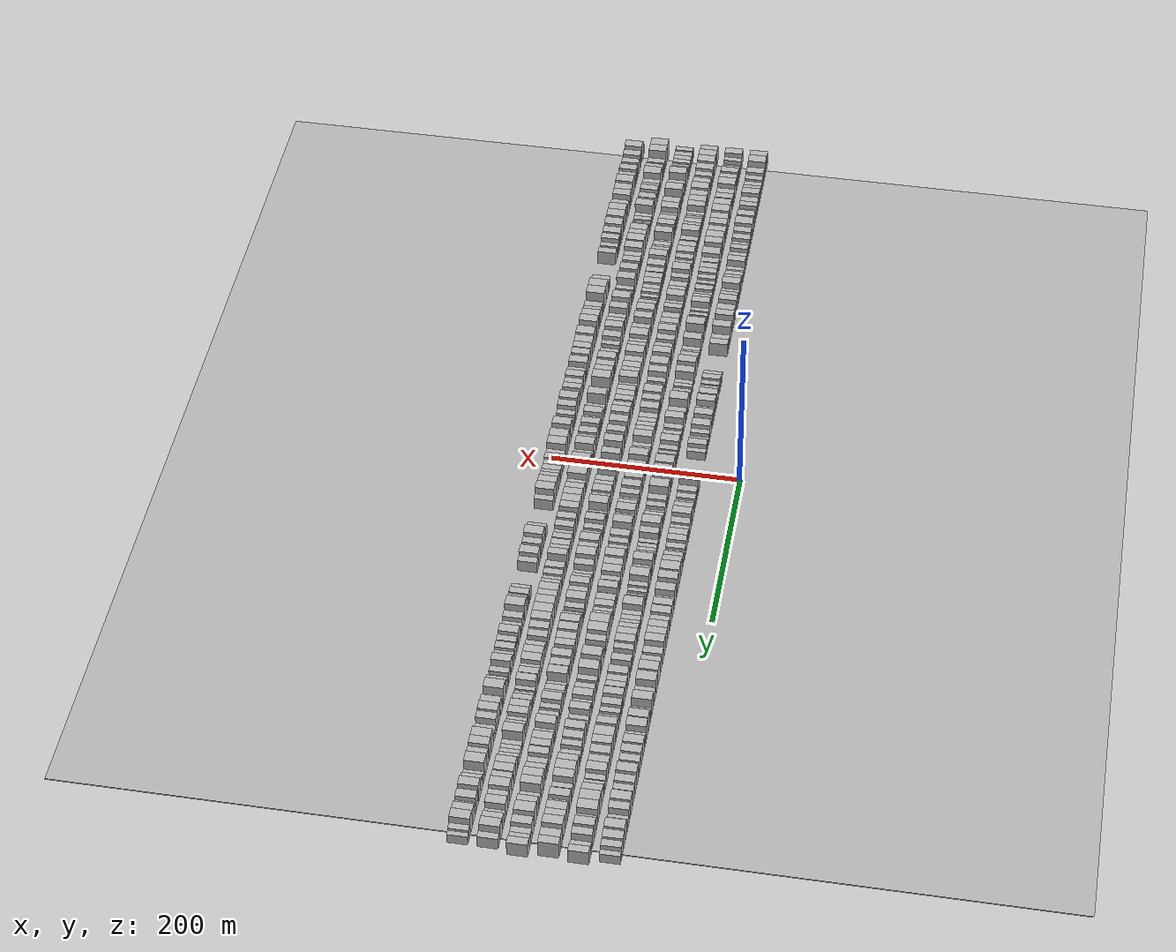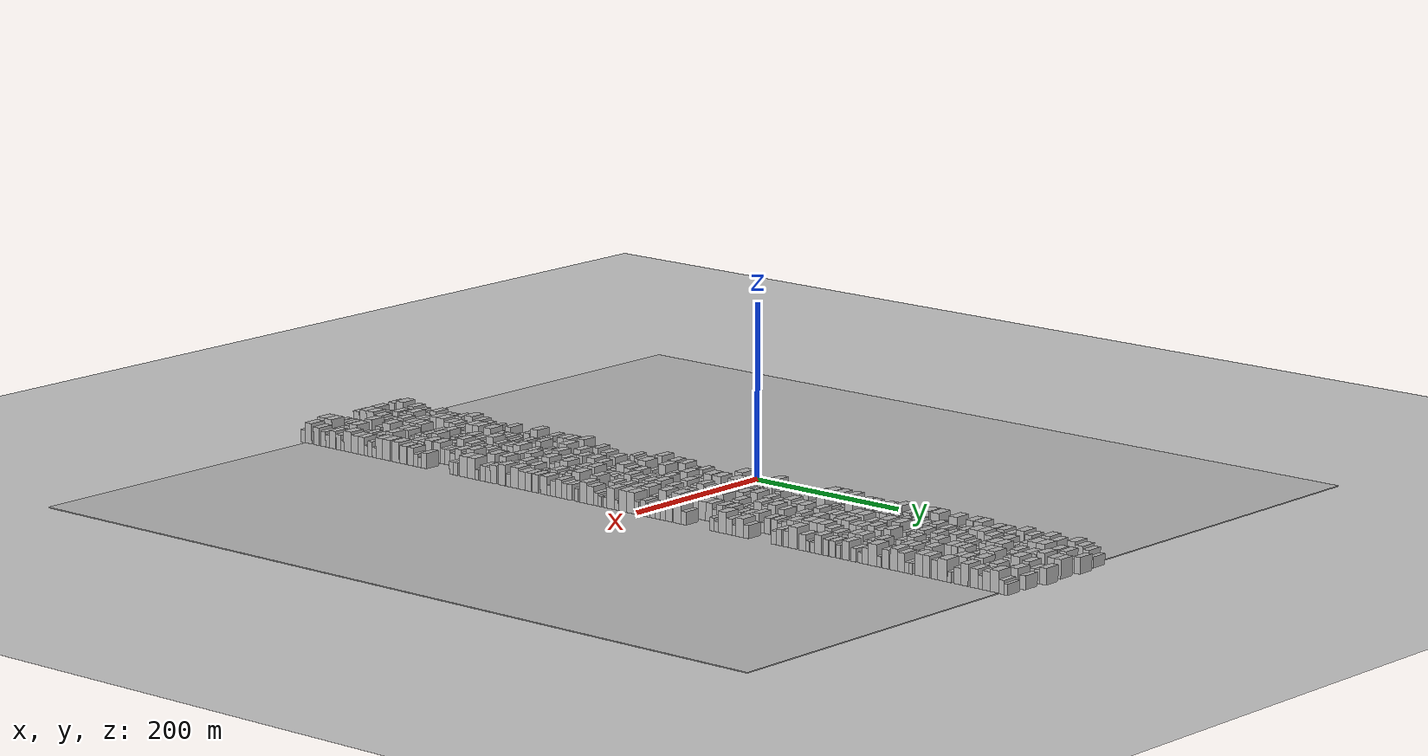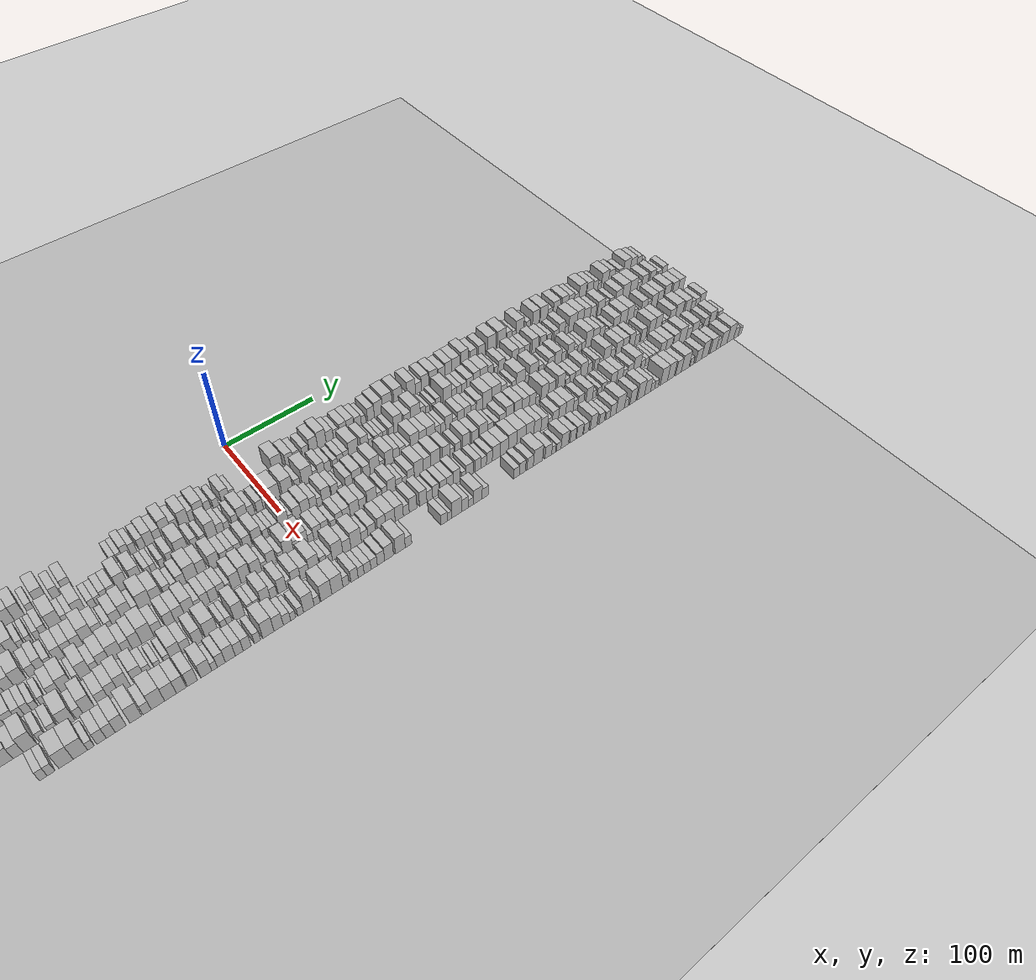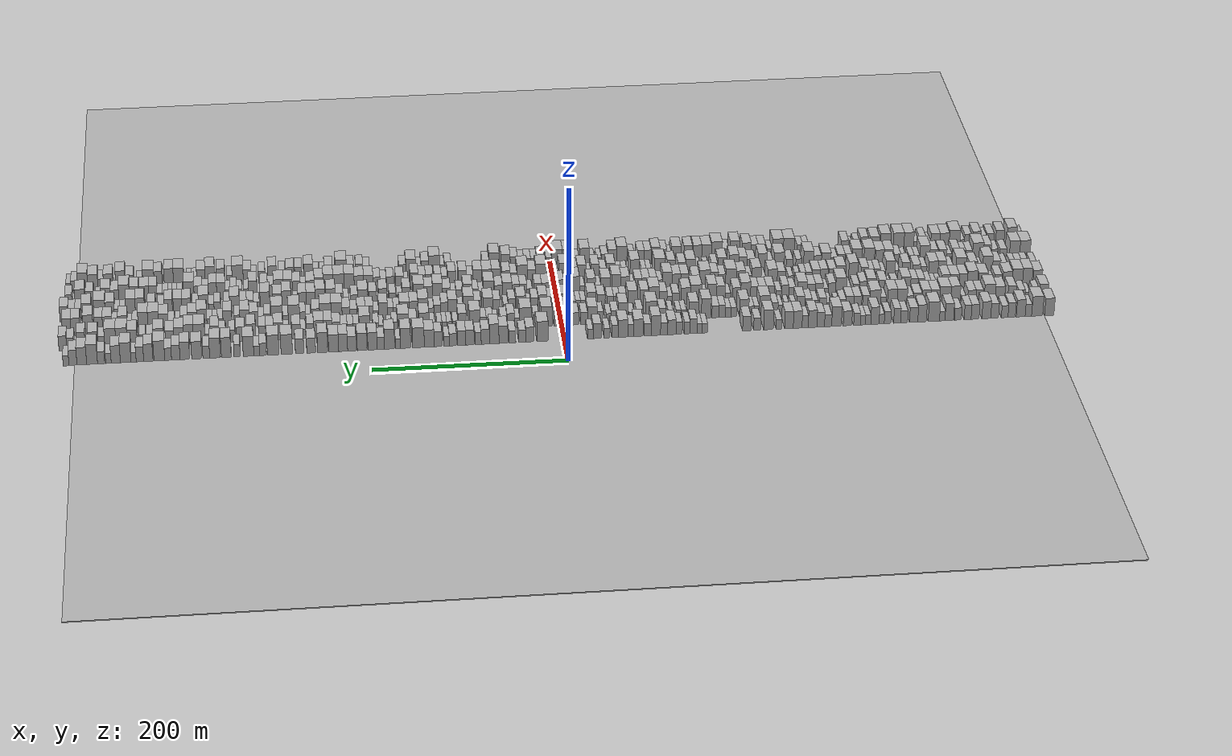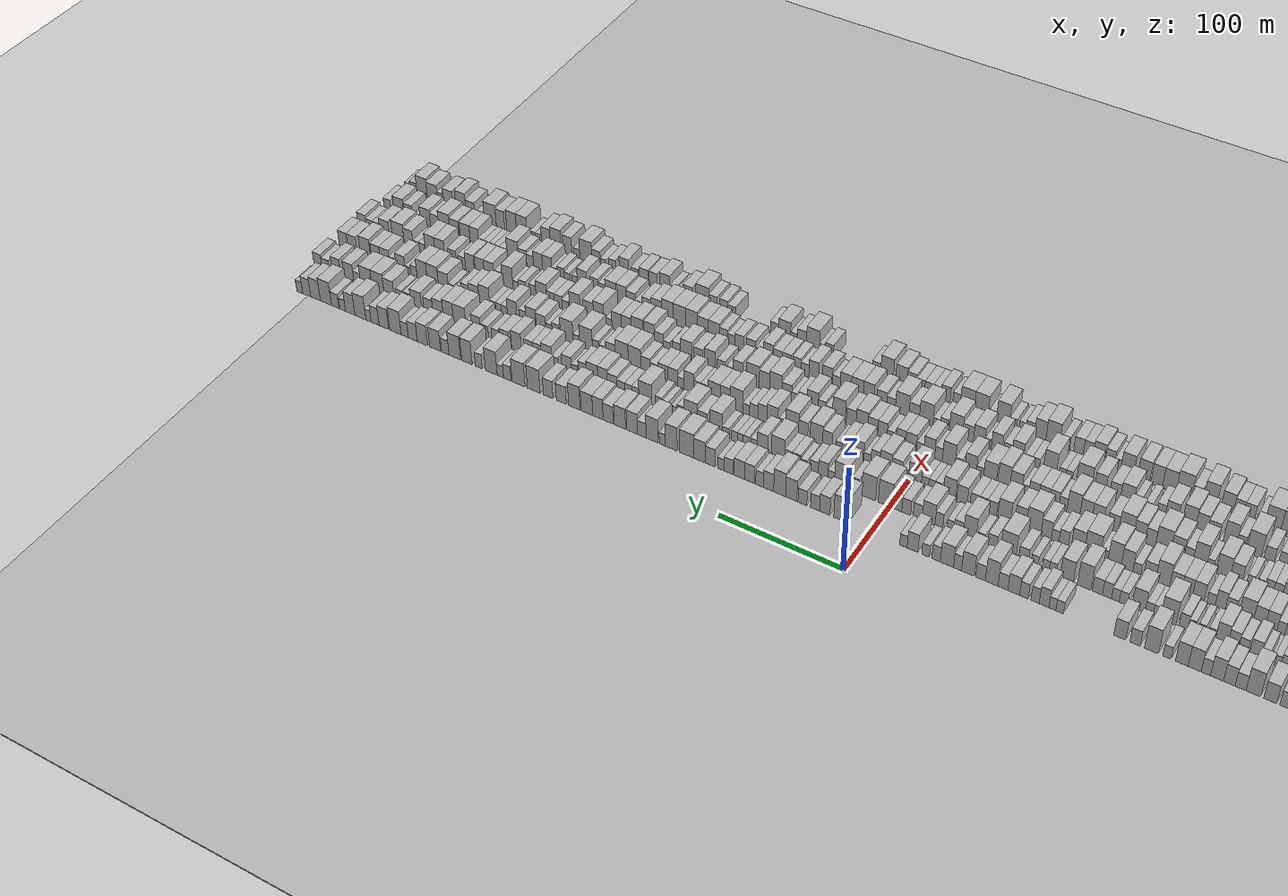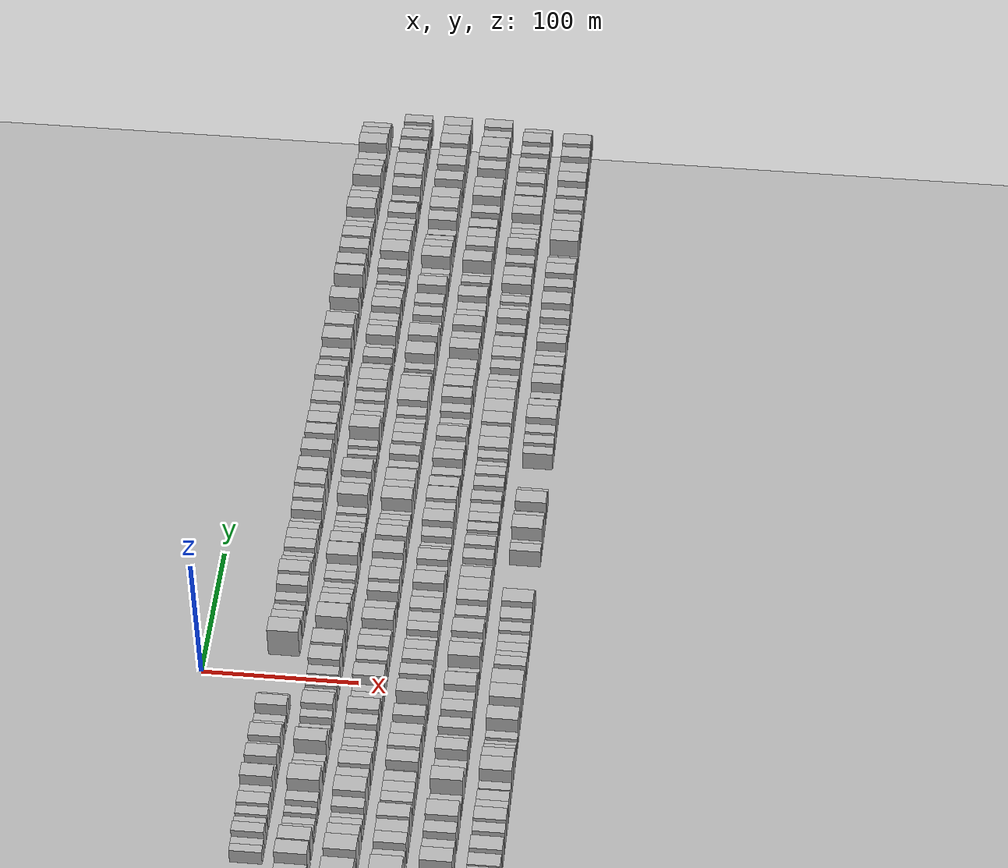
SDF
<?xml version="1.0" encoding="utf-8"?>

<sdf version="1.6">

   <world name="default">

      <gui fullscreen="0">

         <camera name="user_camera">

            <pose>-15 0 4.57585 0 0 0</pose>

            <view_controller>orbit</view_controller>

         </camera>

      </gui>

      <scene>

         <sky>

           <clouds>

             <speed>12</speed>

           </clouds>

         </sky>

         <ambient>0.4 0.4 0.4 1</ambient>

         <background>0.7 0.7 0.7 1</background>

         <shadows>1</shadows>

      </scene>

      <gravity>0 0 -9.8066</gravity>

      <magnetic_field>6e-06 2.3e-05 -4.2e-05</magnetic_field>

      <physics default="0" name="default_physics" type="ode">

         <ode>

            <solver>

               <type>quick</type>

               <iters>10</iters>

               <sor>1.0</sor>

               <use_dynamic_moi_rescaling>0</use_dynamic_moi_rescaling>

            </solver>

            <constraints>

               <cfm>0</cfm>

               <erp>0.2</erp>

               <contact_max_correcting_vel>100</contact_max_correcting_vel>

               <contact_surface_layer>0.001</contact_surface_layer>

            </constraints>

         </ode>

         <max_step_size>0.004</max_step_size>

         <real_time_factor>1</real_time_factor>

         <real_time_update_rate>250</real_time_update_rate>

      </physics>

      <light name="sun" type="directional">

         <cast_shadows>1</cast_shadows>

         <pose>0 0 10 0 0 0</pose>

         <diffuse>0.8 0.8 0.8 1</diffuse>

         <specular>0.2 0.2 0.2 1</specular>

         <attenuation>

            <range>1000</range>

            <constant>0.9</constant>

            <linear>0.01</linear>

            <quadratic>0.001</quadratic>

         </attenuation>

         <direction>-0.5 0.1 -0.9</direction>

      </light>

      <include>

         <name>ground_plane_1</name>

         <uri>model://HANNAS_ground_plane</uri>

         <pose>0 0 0  0 0 0</pose>

      </include>

      <include>

         <name>ground_plane_2</name>

         <uri>model://HANNAS_ground_plane</uri>

         <pose>100 0 0  0 0 0</pose>

      </include>

      <model name="building_1">

         <static>1</static>

         <pose frame="">50.0000 -505.0525 0 0.000000 0.000000 0.000000</pose>

         <link name="link">

            <pose frame="">0 0 10.50 0 0 0</pose>

            <collision name="collision">

               <geometry>

                  <box>

                     <size>20.0000 9.8950 21.0000</size>

                  </box>

               </geometry>

               <max_contacts>10</max_contacts>

               <surface>

                  <contact>

                     <ode/>

                  </contact>

                  <bounce/>

                  <friction>

                     <torsional>

                        <ode/>

                     </torsional>

                     <ode/>

                  </friction>

               </surface>

            </collision>

            <visual name="visual">

               <cast_shadows>0</cast_shadows>

               <geometry>

                  <box>

                     <size>20.0000 9.8950 21.0000</size>

                  </box>

               </geometry>

               <material>

                  <script>

                     <uri>model://HANNAS_wall/materials/scripts</uri>

                     <uri>model://HANNAS_wall/materials/textures</uri>

                     <name>vrc/HANNAS_wall</name>

                  </script>

               </material>

            </visual>

            <self_collide>0</self_collide>

            <enable_wind>0</enable_wind>

            <kinematic>0</kinematic>

         </link>

      </model>

      <model name="building_2">

         <static>1</static>

         <pose frame="">50.0000 -492.2627 0 0.000000 0.000000 0.000000</pose>

         <link name="link">

            <pose frame="">0 0 12.00 0 0 0</pose>

            <collision name="collision">

               <geometry>

                  <box>

                     <size>20.0000 11.6845 24.0000</size>

                  </box>

               </geometry>

               <max_contacts>10</max_contacts>

               <surface>

                  <contact>

                     <ode/>

                  </contact>

                  <bounce/>

                  <friction>

                     <torsional>

                        <ode/>

                     </torsional>

                     <ode/>

                  </friction>

               </surface>

            </collision>

            <visual name="visual">

               <cast_shadows>0</cast_shadows>

               <geometry>

                  <box>

                     <size>20.0000 11.6845 24.0000</size>

                  </box>

               </geometry>

               <material>

                  <script>

                     <uri>model://HANNAS_wall/materials/scripts</uri>

                     <uri>model://HANNAS_wall/materials/textures</uri>

                     <name>vrc/HANNAS_wall</name>

                  </script>

               </material>

            </visual>

            <self_collide>0</self_collide>

            <enable_wind>0</enable_wind>

            <kinematic>0</kinematic>

         </link>

      </model>

      <model name="building_3">

         <static>1</static>

         <pose frame="">50.0000 -483.0384 0 0.000000 0.000000 0.000000</pose>

         <link name="link">

            <pose frame="">0 0 7.50 0 0 0</pose>

            <collision name="collision">

               <geometry>

                  <box>

                     <size>20.0000 6.7641 15.0000</size>

                  </box>

               </geometry>

               <max_contacts>10</max_contacts>

               <surface>

                  <contact>

                     <ode/>

                  </contact>

                  <bounce/>

                  <friction>

                     <torsional>

                        <ode/>

                     </torsional>

                     <ode/>

                  </friction>

               </surface>

            </collision>

            <visual name="visual">

               <cast_shadows>0</cast_shadows>

               <geometry>

                  <box>

                     <size>20.0000 6.7641 15.0000</size>

                  </box>

               </geometry>

               <material>

                  <script>

                     <uri>model://HANNAS_wall/materials/scripts</uri>

                     <uri>model://HANNAS_wall/materials/textures</uri>

                     <name>vrc/HANNAS_wall</name>

                  </script>

               </material>

            </visual>

            <self_collide>0</self_collide>

            <enable_wind>0</enable_wind>

            <kinematic>0</kinematic>

         </link>

      </model>

      <model name="building_4">

         <static>1</static>

         <pose frame="">50.0000 -474.9721 0 0.000000 0.000000 0.000000</pose>

         <link name="link">

            <pose frame="">0 0 10.50 0 0 0</pose>

            <collision name="collision">

               <geometry>

                  <box>

                     <size>20.0000 9.3683 21.0000</size>

                  </box>

               </geometry>

               <max_contacts>10</max_contacts>

               <surface>

                  <contact>

                     <ode/>

                  </contact>

                  <bounce/>

                  <friction>

                     <torsional>

                        <ode/>

                     </torsional>

                     <ode/>

                  </friction>

               </surface>

            </collision>

            <visual name="visual">

               <cast_shadows>0</cast_shadows>

               <geometry>

                  <box>

                     <size>20.0000 9.3683 21.0000</size>

                  </box>

               </geometry>

               <material>

                  <script>

                     <uri>model://HANNAS_wall/materials/scripts</uri>

                     <uri>model://HANNAS_wall/materials/textures</uri>

                     <name>vrc/HANNAS_wall</name>

                  </script>

               </material>

            </visual>

            <self_collide>0</self_collide>

            <enable_wind>0</enable_wind>

            <kinematic>0</kinematic>

         </link>

      </model>

      <model name="building_5">

         <static>1</static>

         <pose frame="">50.0000 -465.4289 0 0.000000 0.000000 0.000000</pose>

         <link name="link">

            <pose frame="">0 0 9.00 0 0 0</pose>

            <collision name="collision">

               <geometry>

                  <box>

                     <size>20.0000 7.7182 18.0000</size>

                  </box>

               </geometry>

               <max_contacts>10</max_contacts>

               <surface>

                  <contact>

                     <ode/>

                  </contact>

                  <bounce/>

                  <friction>

                     <torsional>

                        <ode/>

                     </torsional>

                     <ode/>

                  </friction>

               </surface>

            </collision>

            <visual name="visual">

               <cast_shadows>0</cast_shadows>

               <geometry>

                  <box>

                     <size>20.0000 7.7182 18.0000</size>

                  </box>

               </geometry>

               <material>

                  <script>

                     <uri>model://HANNAS_wall/materials/scripts</uri>

                     <uri>model://HANNAS_wall/materials/textures</uri>

                     <name>vrc/HANNAS_wall</name>

                  </script>

               </material>

            </visual>

            <self_collide>0</self_collide>

            <enable_wind>0</enable_wind>

            <kinematic>0</kinematic>

         </link>

      </model>

      <model name="building_6">

         <static>1</static>

         <pose frame="">50.0000 -458.0506 0 0.000000 0.000000 0.000000</pose>

         <link name="link">

            <pose frame="">0 0 7.50 0 0 0</pose>

            <collision name="collision">

               <geometry>

                  <box>

                     <size>20.0000 7.0384 15.0000</size>

                  </box>

               </geometry>

               <max_contacts>10</max_contacts>

               <surface>

                  <contact>

                     <ode/>

                  </contact>

                  <bounce/>

                  <friction>

                     <torsional>

                        <ode/>

                     </torsional>

                     <ode/>

                  </friction>

               </surface>

            </collision>

            <visual name="visual">

               <cast_shadows>0</cast_shadows>

               <geometry>

                  <box>

                     <size>20.0000 7.0384 15.0000</size>

                  </box>

               </geometry>

               <material>

                  <script>

                     <uri>model://HANNAS_wall/materials/scripts</uri>

                     <uri>model://HANNAS_wall/materials/textures</uri>

                     <name>vrc/HANNAS_wall</name>

                  </script>

               </material>

            </visual>

            <self_collide>0</self_collide>

            <enable_wind>0</enable_wind>

            <kinematic>0</kinematic>

         </link>

      </model>

      <model name="building_7">

         <static>1</static>

         <pose frame="">50.0000 -447.4046 0 0.000000 0.000000 0.000000</pose>

         <link name="link">

            <pose frame="">0 0 9.00 0 0 0</pose>

            <collision name="collision">

               <geometry>

                  <box>

                     <size>20.0000 8.2536 18.0000</size>

                  </box>

               </geometry>

               <max_contacts>10</max_contacts>

               <surface>

                  <contact>

                     <ode/>

                  </contact>

                  <bounce/>

                  <friction>

                     <torsional>

                        <ode/>

                     </torsional>

                     <ode/>

                  </friction>

               </surface>

            </collision>

            <visual name="visual">

               <cast_shadows>0</cast_shadows>

               <geometry>

                  <box>

                     <size>20.0000 8.2536 18.0000</size>

                  </box>

               </geometry>

               <material>

                  <script>

                     <uri>model://HANNAS_wall/materials/scripts</uri>

                     <uri>model://HANNAS_wall/materials/textures</uri>

                     <name>vrc/HANNAS_wall</name>

                  </script>

               </material>

            </visual>

            <self_collide>0</self_collide>

            <enable_wind>0</enable_wind>

            <kinematic>0</kinematic>

         </link>

      </model>

      <model name="building_8">

         <static>1</static>

         <pose frame="">50.0000 -438.6514 0 0.000000 0.000000 0.000000</pose>

         <link name="link">

            <pose frame="">0 0 10.50 0 0 0</pose>

            <collision name="collision">

               <geometry>

                  <box>

                     <size>20.0000 9.2527 21.0000</size>

                  </box>

               </geometry>

               <max_contacts>10</max_contacts>

               <surface>

                  <contact>

                     <ode/>

                  </contact>

                  <bounce/>

                  <friction>

                     <torsional>

                        <ode/>

                     </torsional>

                     <ode/>

                  </friction>

               </surface>

            </collision>

            <visual name="visual">

               <cast_shadows>0</cast_shadows>

               <geometry>

                  <box>

                     <size>20.0000 9.2527 21.0000</size>

                  </box>

               </geometry>

               <material>

                  <script>

                     <uri>model://HANNAS_wall/materials/scripts</uri>

                     <uri>model://HANNAS_wall/materials/textures</uri>

                     <name>vrc/HANNAS_wall</name>

                  </script>

               </material>

            </visual>

            <self_collide>0</self_collide>

            <enable_wind>0</enable_wind>

            <kinematic>0</kinematic>

         </link>

      </model>

      <model name="building_9">

         <static>1</static>

         <pose frame="">50.0000 -426.8555 0 0.000000 0.000000 0.000000</pose>

         <link name="link">

            <pose frame="">0 0 9.00 0 0 0</pose>

            <collision name="collision">

               <geometry>

                  <box>

                     <size>20.0000 8.3391 18.0000</size>

                  </box>

               </geometry>

               <max_contacts>10</max_contacts>

               <surface>

                  <contact>

                     <ode/>

                  </contact>

                  <bounce/>

                  <friction>

                     <torsional>

                        <ode/>

                     </torsional>

                     <ode/>

                  </friction>

               </surface>

            </collision>

            <visual name="visual">

               <cast_shadows>0</cast_shadows>

               <geometry>

                  <box>

                     <size>20.0000 8.3391 18.0000</size>

                  </box>

               </geometry>

               <material>

                  <script>

                     <uri>model://HANNAS_wall/materials/scripts</uri>

                     <uri>model://HANNAS_wall/materials/textures</uri>

                     <name>vrc/HANNAS_wall</name>

                  </script>

               </material>

            </visual>

            <self_collide>0</self_collide>

            <enable_wind>0</enable_wind>

            <kinematic>0</kinematic>

         </link>

      </model>

      <model name="building_10">

         <static>1</static>

         <pose frame="">50.0000 -419.0073 0 0.000000 0.000000 0.000000</pose>

         <link name="link">

            <pose frame="">0 0 9.00 0 0 0</pose>

            <collision name="collision">

               <geometry>

                  <box>

                     <size>20.0000 7.3574 18.0000</size>

                  </box>

               </geometry>

               <max_contacts>10</max_contacts>

               <surface>

                  <contact>

                     <ode/>

                  </contact>

                  <bounce/>

                  <friction>

                     <torsional>

                        <ode/>

                     </torsional>

                     <ode/>

                  </friction>

               </surface>

            </collision>

            <visual name="visual">

               <cast_shadows>0</cast_shadows>

               <geometry>

                  <box>

                     <size>20.0000 7.3574 18.0000</size>

                  </box>

               </geometry>

               <material>

                  <script>

                     <uri>model://HANNAS_wall/materials/scripts</uri>

                     <uri>model://HANNAS_wall/materials/textures</uri>

                     <name>vrc/HANNAS_wall</name>

                  </script>

               </material>

            </visual>

            <self_collide>0</self_collide>

            <enable_wind>0</enable_wind>

            <kinematic>0</kinematic>

         </link>

      </model>

      <model name="building_11">

         <static>1</static>

         <pose frame="">50.0000 -408.7520 0 0.000000 0.000000 0.000000</pose>

         <link name="link">

            <pose frame="">0 0 7.50 0 0 0</pose>

            <collision name="collision">

               <geometry>

                  <box>

                     <size>20.0000 7.1532 15.0000</size>

                  </box>

               </geometry>

               <max_contacts>10</max_contacts>

               <surface>

                  <contact>

                     <ode/>

                  </contact>

                  <bounce/>

                  <friction>

                     <torsional>

                        <ode/>

                     </torsional>

                     <ode/>

                  </friction>

               </surface>

            </collision>

            <visual name="visual">

               <cast_shadows>0</cast_shadows>

               <geometry>

                  <box>

                     <size>20.0000 7.1532 15.0000</size>

                  </box>

               </geometry>

               <material>

                  <script>

                     <uri>model://HANNAS_wall/materials/scripts</uri>

                     <uri>model://HANNAS_wall/materials/textures</uri>

                     <name>vrc/HANNAS_wall</name>

                  </script>

               </material>

            </visual>

            <self_collide>0</self_collide>

            <enable_wind>0</enable_wind>

            <kinematic>0</kinematic>

         </link>

      </model>

      <model name="building_12">

         <static>1</static>

         <pose frame="">50.0000 -399.7153 0 0.000000 0.000000 0.000000</pose>

         <link name="link">

            <pose frame="">0 0 10.50 0 0 0</pose>

            <collision name="collision">

               <geometry>

                  <box>

                     <size>20.0000 8.9202 21.0000</size>

                  </box>

               </geometry>

               <max_contacts>10</max_contacts>

               <surface>

                  <contact>

                     <ode/>

                  </contact>

                  <bounce/>

                  <friction>

                     <torsional>

                        <ode/>

                     </torsional>

                     <ode/>

                  </friction>

               </surface>

            </collision>

            <visual name="visual">

               <cast_shadows>0</cast_shadows>

               <geometry>

                  <box>

                     <size>20.0000 8.9202 21.0000</size>

                  </box>

               </geometry>

               <material>

                  <script>

                     <uri>model://HANNAS_wall/materials/scripts</uri>

                     <uri>model://HANNAS_wall/materials/textures</uri>

                     <name>vrc/HANNAS_wall</name>

                  </script>

               </material>

            </visual>

            <self_collide>0</self_collide>

            <enable_wind>0</enable_wind>

            <kinematic>0</kinematic>

         </link>

      </model>

      <model name="building_13">

         <static>1</static>

         <pose frame="">50.0000 -392.3392 0 0.000000 0.000000 0.000000</pose>

         <link name="link">

            <pose frame="">0 0 6.00 0 0 0</pose>

            <collision name="collision">

               <geometry>

                  <box>

                     <size>20.0000 5.8320 12.0000</size>

                  </box>

               </geometry>

               <max_contacts>10</max_contacts>

               <surface>

                  <contact>

                     <ode/>

                  </contact>

                  <bounce/>

                  <friction>

                     <torsional>

                        <ode/>

                     </torsional>

                     <ode/>

                  </friction>

               </surface>

            </collision>

            <visual name="visual">

               <cast_shadows>0</cast_shadows>

               <geometry>

                  <box>

                     <size>20.0000 5.8320 12.0000</size>

                  </box>

               </geometry>

               <material>

                  <script>

                     <uri>model://HANNAS_wall/materials/scripts</uri>

                     <uri>model://HANNAS_wall/materials/textures</uri>

                     <name>vrc/HANNAS_wall</name>

                  </script>

               </material>

            </visual>

            <self_collide>0</self_collide>

            <enable_wind>0</enable_wind>

            <kinematic>0</kinematic>

         </link>

      </model>

      <model name="building_14">

         <static>1</static>

         <pose frame="">50.0000 -383.4952 0 0.000000 0.000000 0.000000</pose>

         <link name="link">

            <pose frame="">0 0 12.00 0 0 0</pose>

            <collision name="collision">

               <geometry>

                  <box>

                     <size>20.0000 11.8561 24.0000</size>

                  </box>

               </geometry>

               <max_contacts>10</max_contacts>

               <surface>

                  <contact>

                     <ode/>

                  </contact>

                  <bounce/>

                  <friction>

                     <torsional>

                        <ode/>

                     </torsional>

                     <ode/>

                  </friction>

               </surface>

            </collision>

            <visual name="visual">

               <cast_shadows>0</cast_shadows>

               <geometry>

                  <box>

                     <size>20.0000 11.8561 24.0000</size>

                  </box>

               </geometry>

               <material>

                  <script>

                     <uri>model://HANNAS_wall/materials/scripts</uri>

                     <uri>model://HANNAS_wall/materials/textures</uri>

                     <name>vrc/HANNAS_wall</name>

                  </script>

               </material>

            </visual>

            <self_collide>0</self_collide>

            <enable_wind>0</enable_wind>

            <kinematic>0</kinematic>

         </link>

      </model>

      <model name="building_15">

         <static>1</static>

         <pose frame="">50.0000 -371.1223 0 0.000000 0.000000 0.000000</pose>

         <link name="link">

            <pose frame="">0 0 10.50 0 0 0</pose>

            <collision name="collision">

               <geometry>

                  <box>

                     <size>20.0000 8.8896 21.0000</size>

                  </box>

               </geometry>

               <max_contacts>10</max_contacts>

               <surface>

                  <contact>

                     <ode/>

                  </contact>

                  <bounce/>

                  <friction>

                     <torsional>

                        <ode/>

                     </torsional>

                     <ode/>

                  </friction>

               </surface>

            </collision>

            <visual name="visual">

               <cast_shadows>0</cast_shadows>

               <geometry>

                  <box>

                     <size>20.0000 8.8896 21.0000</size>

                  </box>

               </geometry>

               <material>

                  <script>

                     <uri>model://HANNAS_wall/materials/scripts</uri>

                     <uri>model://HANNAS_wall/materials/textures</uri>

                     <name>vrc/HANNAS_wall</name>

                  </script>

               </material>

            </visual>

            <self_collide>0</self_collide>

            <enable_wind>0</enable_wind>

            <kinematic>0</kinematic>

         </link>

      </model>

      <model name="building_16">

         <static>1</static>

         <pose frame="">50.0000 -362.3112 0 0.000000 0.000000 0.000000</pose>

         <link name="link">

            <pose frame="">0 0 9.00 0 0 0</pose>

            <collision name="collision">

               <geometry>

                  <box>

                     <size>20.0000 8.7326 18.0000</size>

                  </box>

               </geometry>

               <max_contacts>10</max_contacts>

               <surface>

                  <contact>

                     <ode/>

                  </contact>

                  <bounce/>

                  <friction>

                     <torsional>

                        <ode/>

                     </torsional>

                     <ode/>

                  </friction>

               </surface>

            </collision>

            <visual name="visual">

               <cast_shadows>0</cast_shadows>

               <geometry>

                  <box>

                     <size>20.0000 8.7326 18.0000</size>

                  </box>

               </geometry>

               <material>

                  <script>

                     <uri>model://HANNAS_wall/materials/scripts</uri>

                     <uri>model://HANNAS_wall/materials/textures</uri>

                     <name>vrc/HANNAS_wall</name>

                  </script>

               </material>

            </visual>

            <self_collide>0</self_collide>

            <enable_wind>0</enable_wind>

            <kinematic>0</kinematic>

         </link>

      </model>

      <model name="building_17">

         <static>1</static>

         <pose frame="">50.0000 -352.2505 0 0.000000 0.000000 0.000000</pose>

         <link name="link">

            <pose frame="">0 0 7.50 0 0 0</pose>

            <collision name="collision">

               <geometry>

                  <box>

                     <size>20.0000 7.3887 15.0000</size>

                  </box>

               </geometry>

               <max_contacts>10</max_contacts>

               <surface>

                  <contact>

                     <ode/>

                  </contact>

                  <bounce/>

                  <friction>

                     <torsional>

                        <ode/>

                     </torsional>

                     <ode/>

                  </friction>

               </surface>

            </collision>

            <visual name="visual">

               <cast_shadows>0</cast_shadows>

               <geometry>

                  <box>

                     <size>20.0000 7.3887 15.0000</size>

                  </box>

               </geometry>

               <material>

                  <script>

                     <uri>model://HANNAS_wall/materials/scripts</uri>

                     <uri>model://HANNAS_wall/materials/textures</uri>

                     <name>vrc/HANNAS_wall</name>

                  </script>

               </material>

            </visual>

            <self_collide>0</self_collide>

            <enable_wind>0</enable_wind>

            <kinematic>0</kinematic>

         </link>

      </model>

      <model name="building_18">

         <static>1</static>

         <pose frame="">50.0000 -344.9468 0 0.000000 0.000000 0.000000</pose>

         <link name="link">

            <pose frame="">0 0 9.00 0 0 0</pose>

            <collision name="collision">

               <geometry>

                  <box>

                     <size>20.0000 7.2187 18.0000</size>

                  </box>

               </geometry>

               <max_contacts>10</max_contacts>

               <surface>

                  <contact>

                     <ode/>

                  </contact>

                  <bounce/>

                  <friction>

                     <torsional>

                        <ode/>

                     </torsional>

                     <ode/>

                  </friction>

               </surface>

            </collision>

            <visual name="visual">

               <cast_shadows>0</cast_shadows>

               <geometry>

                  <box>

                     <size>20.0000 7.2187 18.0000</size>

                  </box>

               </geometry>

               <material>

                  <script>

                     <uri>model://HANNAS_wall/materials/scripts</uri>

                     <uri>model://HANNAS_wall/materials/textures</uri>

                     <name>vrc/HANNAS_wall</name>

                  </script>

               </material>

            </visual>

            <self_collide>0</self_collide>

            <enable_wind>0</enable_wind>

            <kinematic>0</kinematic>

         </link>

      </model>

      <model name="building_19">

         <static>1</static>

         <pose frame="">50.0000 -334.9244 0 0.000000 0.000000 0.000000</pose>

         <link name="link">

            <pose frame="">0 0 7.50 0 0 0</pose>

            <collision name="collision">

               <geometry>

                  <box>

                     <size>20.0000 6.8262 15.0000</size>

                  </box>

               </geometry>

               <max_contacts>10</max_contacts>

               <surface>

                  <contact>

                     <ode/>

                  </contact>

                  <bounce/>

                  <friction>

                     <torsional>

                        <ode/>

                     </torsional>

                     <ode/>

                  </friction>

               </surface>

            </collision>

            <visual name="visual">

               <cast_shadows>0</cast_shadows>

               <geometry>

                  <box>

                     <size>20.0000 6.8262 15.0000</size>

                  </box>

               </geometry>

               <material>

                  <script>

                     <uri>model://HANNAS_wall/materials/scripts</uri>

                     <uri>model://HANNAS_wall/materials/textures</uri>

                     <name>vrc/HANNAS_wall</name>

                  </script>

               </material>

            </visual>

            <self_collide>0</self_collide>

            <enable_wind>0</enable_wind>

            <kinematic>0</kinematic>

         </link>

      </model>

      <model name="building_20">

         <static>1</static>

         <pose frame="">50.0000 -328.7829 0 0.000000 0.000000 0.000000</pose>

         <link name="link">

            <pose frame="">0 0 6.00 0 0 0</pose>

            <collision name="collision">

               <geometry>

                  <box>

                     <size>20.0000 5.4569 12.0000</size>

                  </box>

               </geometry>

               <max_contacts>10</max_contacts>

               <surface>

                  <contact>

                     <ode/>

                  </contact>

                  <bounce/>

                  <friction>

                     <torsional>

                        <ode/>

                     </torsional>

                     <ode/>

                  </friction>

               </surface>

            </collision>

            <visual name="visual">

               <cast_shadows>0</cast_shadows>

               <geometry>

                  <box>

                     <size>20.0000 5.4569 12.0000</size>

                  </box>

               </geometry>

               <material>

                  <script>

                     <uri>model://HANNAS_wall/materials/scripts</uri>

                     <uri>model://HANNAS_wall/materials/textures</uri>

                     <name>vrc/HANNAS_wall</name>

                  </script>

               </material>

            </visual>

            <self_collide>0</self_collide>

            <enable_wind>0</enable_wind>

            <kinematic>0</kinematic>

         </link>

      </model>

      <model name="building_21">

         <static>1</static>

         <pose frame="">50.0000 -321.6892 0 0.000000 0.000000 0.000000</pose>

         <link name="link">

            <pose frame="">0 0 10.50 0 0 0</pose>

            <collision name="collision">

               <geometry>

                  <box>

                     <size>20.0000 8.7305 21.0000</size>

                  </box>

               </geometry>

               <max_contacts>10</max_contacts>

               <surface>

                  <contact>

                     <ode/>

                  </contact>

                  <bounce/>

                  <friction>

                     <torsional>

                        <ode/>

                     </torsional>

                     <ode/>

                  </friction>

               </surface>

            </collision>

            <visual name="visual">

               <cast_shadows>0</cast_shadows>

               <geometry>

                  <box>

                     <size>20.0000 8.7305 21.0000</size>

                  </box>

               </geometry>

               <material>

                  <script>

                     <uri>model://HANNAS_wall/materials/scripts</uri>

                     <uri>model://HANNAS_wall/materials/textures</uri>

                     <name>vrc/HANNAS_wall</name>

                  </script>

               </material>

            </visual>

            <self_collide>0</self_collide>

            <enable_wind>0</enable_wind>

            <kinematic>0</kinematic>

         </link>

      </model>

      <model name="building_22">

         <static>1</static>

         <pose frame="">50.0000 -314.5585 0 0.000000 0.000000 0.000000</pose>

         <link name="link">

            <pose frame="">0 0 6.00 0 0 0</pose>

            <collision name="collision">

               <geometry>

                  <box>

                     <size>20.0000 5.5309 12.0000</size>

                  </box>

               </geometry>

               <max_contacts>10</max_contacts>

               <surface>

                  <contact>

                     <ode/>

                  </contact>

                  <bounce/>

                  <friction>

                     <torsional>

                        <ode/>

                     </torsional>

                     <ode/>

                  </friction>

               </surface>

            </collision>

            <visual name="visual">

               <cast_shadows>0</cast_shadows>

               <geometry>

                  <box>

                     <size>20.0000 5.5309 12.0000</size>

                  </box>

               </geometry>

               <material>

                  <script>

                     <uri>model://HANNAS_wall/materials/scripts</uri>

                     <uri>model://HANNAS_wall/materials/textures</uri>

                     <name>vrc/HANNAS_wall</name>

                  </script>

               </material>

            </visual>

            <self_collide>0</self_collide>

            <enable_wind>0</enable_wind>

            <kinematic>0</kinematic>

         </link>

      </model>

      <model name="building_23">

         <static>1</static>

         <pose frame="">50.0000 -309.1795 0 0.000000 0.000000 0.000000</pose>

         <link name="link">

            <pose frame="">0 0 6.00 0 0 0</pose>

            <collision name="collision">

               <geometry>

                  <box>

                     <size>20.0000 5.2270 12.0000</size>

                  </box>

               </geometry>

               <max_contacts>10</max_contacts>

               <surface>

                  <contact>

                     <ode/>

                  </contact>

                  <bounce/>

                  <friction>

                     <torsional>

                        <ode/>

                     </torsional>

                     <ode/>

                  </friction>

               </surface>

            </collision>

            <visual name="visual">

               <cast_shadows>0</cast_shadows>

               <geometry>

                  <box>

                     <size>20.0000 5.2270 12.0000</size>

                  </box>

               </geometry>

               <material>

                  <script>

                     <uri>model://HANNAS_wall/materials/scripts</uri>

                     <uri>model://HANNAS_wall/materials/textures</uri>

                     <name>vrc/HANNAS_wall</name>

                  </script>

               </material>

            </visual>

            <self_collide>0</self_collide>

            <enable_wind>0</enable_wind>

            <kinematic>0</kinematic>

         </link>

      </model>

      <model name="building_24">

         <static>1</static>

         <pose frame="">50.0000 -303.0236 0 0.000000 0.000000 0.000000</pose>

         <link name="link">

            <pose frame="">0 0 7.50 0 0 0</pose>

            <collision name="collision">

               <geometry>

                  <box>

                     <size>20.0000 7.0849 15.0000</size>

                  </box>

               </geometry>

               <max_contacts>10</max_contacts>

               <surface>

                  <contact>

                     <ode/>

                  </contact>

                  <bounce/>

                  <friction>

                     <torsional>

                        <ode/>

                     </torsional>

                     <ode/>

                  </friction>

               </surface>

            </collision>

            <visual name="visual">

               <cast_shadows>0</cast_shadows>

               <geometry>

                  <box>

                     <size>20.0000 7.0849 15.0000</size>

                  </box>

               </geometry>

               <material>

                  <script>

                     <uri>model://HANNAS_wall/materials/scripts</uri>

                     <uri>model://HANNAS_wall/materials/textures</uri>

                     <name>vrc/HANNAS_wall</name>

                  </script>

               </material>

            </visual>

            <self_collide>0</self_collide>

            <enable_wind>0</enable_wind>

            <kinematic>0</kinematic>

         </link>

      </model>

      <model name="building_25">

         <static>1</static>

         <pose frame="">50.0000 -293.0301 0 0.000000 0.000000 0.000000</pose>

         <link name="link">

            <pose frame="">0 0 9.00 0 0 0</pose>

            <collision name="collision">

               <geometry>

                  <box>

                     <size>20.0000 8.9020 18.0000</size>

                  </box>

               </geometry>

               <max_contacts>10</max_contacts>

               <surface>

                  <contact>

                     <ode/>

                  </contact>

                  <bounce/>

                  <friction>

                     <torsional>

                        <ode/>

                     </torsional>

                     <ode/>

                  </friction>

               </surface>

            </collision>

            <visual name="visual">

               <cast_shadows>0</cast_shadows>

               <geometry>

                  <box>

                     <size>20.0000 8.9020 18.0000</size>

                  </box>

               </geometry>

               <material>

                  <script>

                     <uri>model://HANNAS_wall/materials/scripts</uri>

                     <uri>model://HANNAS_wall/materials/textures</uri>

                     <name>vrc/HANNAS_wall</name>

                  </script>

               </material>

            </visual>

            <self_collide>0</self_collide>

            <enable_wind>0</enable_wind>

            <kinematic>0</kinematic>

         </link>

      </model>

      <model name="building_26">

         <static>1</static>

         <pose frame="">50.0000 -281.5239 0 0.000000 0.000000 0.000000</pose>

         <link name="link">

            <pose frame="">0 0 12.00 0 0 0</pose>

            <collision name="collision">

               <geometry>

                  <box>

                     <size>20.0000 10.1105 24.0000</size>

                  </box>

               </geometry>

               <max_contacts>10</max_contacts>

               <surface>

                  <contact>

                     <ode/>

                  </contact>

                  <bounce/>

                  <friction>

                     <torsional>

                        <ode/>

                     </torsional>

                     <ode/>

                  </friction>

               </surface>

            </collision>

            <visual name="visual">

               <cast_shadows>0</cast_shadows>

               <geometry>

                  <box>

                     <size>20.0000 10.1105 24.0000</size>

                  </box>

               </geometry>

               <material>

                  <script>

                     <uri>model://HANNAS_wall/materials/scripts</uri>

                     <uri>model://HANNAS_wall/materials/textures</uri>

                     <name>vrc/HANNAS_wall</name>

                  </script>

               </material>

            </visual>

            <self_collide>0</self_collide>

            <enable_wind>0</enable_wind>

            <kinematic>0</kinematic>

         </link>

      </model>

      <model name="building_27">

         <static>1</static>

         <pose frame="">50.0000 -272.7384 0 0.000000 0.000000 0.000000</pose>

         <link name="link">

            <pose frame="">0 0 7.50 0 0 0</pose>

            <collision name="collision">

               <geometry>

                  <box>

                     <size>20.0000 7.4606 15.0000</size>

                  </box>

               </geometry>

               <max_contacts>10</max_contacts>

               <surface>

                  <contact>

                     <ode/>

                  </contact>

                  <bounce/>

                  <friction>

                     <torsional>

                        <ode/>

                     </torsional>

                     <ode/>

                  </friction>

               </surface>

            </collision>

            <visual name="visual">

               <cast_shadows>0</cast_shadows>

               <geometry>

                  <box>

                     <size>20.0000 7.4606 15.0000</size>

                  </box>

               </geometry>

               <material>

                  <script>

                     <uri>model://HANNAS_wall/materials/scripts</uri>

                     <uri>model://HANNAS_wall/materials/textures</uri>

                     <name>vrc/HANNAS_wall</name>

                  </script>

               </material>

            </visual>

            <self_collide>0</self_collide>

            <enable_wind>0</enable_wind>

            <kinematic>0</kinematic>

         </link>

      </model>

      <model name="building_28">

         <static>1</static>

         <pose frame="">50.0000 -265.0333 0 0.000000 0.000000 0.000000</pose>

         <link name="link">

            <pose frame="">0 0 9.00 0 0 0</pose>

            <collision name="collision">

               <geometry>

                  <box>

                     <size>20.0000 7.9496 18.0000</size>

                  </box>

               </geometry>

               <max_contacts>10</max_contacts>

               <surface>

                  <contact>

                     <ode/>

                  </contact>

                  <bounce/>

                  <friction>

                     <torsional>

                        <ode/>

                     </torsional>

                     <ode/>

                  </friction>

               </surface>

            </collision>

            <visual name="visual">

               <cast_shadows>0</cast_shadows>

               <geometry>

                  <box>

                     <size>20.0000 7.9496 18.0000</size>

                  </box>

               </geometry>

               <material>

                  <script>

                     <uri>model://HANNAS_wall/materials/scripts</uri>

                     <uri>model://HANNAS_wall/materials/textures</uri>

                     <name>vrc/HANNAS_wall</name>

                  </script>

               </material>

            </visual>

            <self_collide>0</self_collide>

            <enable_wind>0</enable_wind>

            <kinematic>0</kinematic>

         </link>

      </model>

      <model name="building_29">

         <static>1</static>

         <pose frame="">50.0000 -256.5383 0 0.000000 0.000000 0.000000</pose>

         <link name="link">

            <pose frame="">0 0 10.50 0 0 0</pose>

            <collision name="collision">

               <geometry>

                  <box>

                     <size>20.0000 9.0404 21.0000</size>

                  </box>

               </geometry>

               <max_contacts>10</max_contacts>

               <surface>

                  <contact>

                     <ode/>

                  </contact>

                  <bounce/>

                  <friction>

                     <torsional>

                        <ode/>

                     </torsional>

                     <ode/>

                  </friction>

               </surface>

            </collision>

            <visual name="visual">

               <cast_shadows>0</cast_shadows>

               <geometry>

                  <box>

                     <size>20.0000 9.0404 21.0000</size>

                  </box>

               </geometry>

               <material>

                  <script>

                     <uri>model://HANNAS_wall/materials/scripts</uri>

                     <uri>model://HANNAS_wall/materials/textures</uri>

                     <name>vrc/HANNAS_wall</name>

                  </script>

               </material>

            </visual>

            <self_collide>0</self_collide>

            <enable_wind>0</enable_wind>

            <kinematic>0</kinematic>

         </link>

      </model>

      <model name="building_30">

         <static>1</static>

         <pose frame="">50.0000 -248.7685 0 0.000000 0.000000 0.000000</pose>

         <link name="link">

            <pose frame="">0 0 7.50 0 0 0</pose>

            <collision name="collision">

               <geometry>

                  <box>

                     <size>20.0000 6.4992 15.0000</size>

                  </box>

               </geometry>

               <max_contacts>10</max_contacts>

               <surface>

                  <contact>

                     <ode/>

                  </contact>

                  <bounce/>

                  <friction>

                     <torsional>

                        <ode/>

                     </torsional>

                     <ode/>

                  </friction>

               </surface>

            </collision>

            <visual name="visual">

               <cast_shadows>0</cast_shadows>

               <geometry>

                  <box>

                     <size>20.0000 6.4992 15.0000</size>

                  </box>

               </geometry>

               <material>

                  <script>

                     <uri>model://HANNAS_wall/materials/scripts</uri>

                     <uri>model://HANNAS_wall/materials/textures</uri>

                     <name>vrc/HANNAS_wall</name>

                  </script>

               </material>

            </visual>

            <self_collide>0</self_collide>

            <enable_wind>0</enable_wind>

            <kinematic>0</kinematic>

         </link>

      </model>

      <model name="building_31">

         <static>1</static>

         <pose frame="">50.0000 -240.9469 0 0.000000 0.000000 0.000000</pose>

         <link name="link">

            <pose frame="">0 0 10.50 0 0 0</pose>

            <collision name="collision">

               <geometry>

                  <box>

                     <size>20.0000 9.1441 21.0000</size>

                  </box>

               </geometry>

               <max_contacts>10</max_contacts>

               <surface>

                  <contact>

                     <ode/>

                  </contact>

                  <bounce/>

                  <friction>

                     <torsional>

                        <ode/>

                     </torsional>

                     <ode/>

                  </friction>

               </surface>

            </collision>

            <visual name="visual">

               <cast_shadows>0</cast_shadows>

               <geometry>

                  <box>

                     <size>20.0000 9.1441 21.0000</size>

                  </box>

               </geometry>

               <material>

                  <script>

                     <uri>model://HANNAS_wall/materials/scripts</uri>

                     <uri>model://HANNAS_wall/materials/textures</uri>

                     <name>vrc/HANNAS_wall</name>

                  </script>

               </material>

            </visual>

            <self_collide>0</self_collide>

            <enable_wind>0</enable_wind>

            <kinematic>0</kinematic>

         </link>

      </model>

      <model name="building_32">

         <static>1</static>

         <pose frame="">50.0000 -231.9362 0 0.000000 0.000000 0.000000</pose>

         <link name="link">

            <pose frame="">0 0 10.50 0 0 0</pose>

            <collision name="collision">

               <geometry>

                  <box>

                     <size>20.0000 8.8774 21.0000</size>

                  </box>

               </geometry>

               <max_contacts>10</max_contacts>

               <surface>

                  <contact>

                     <ode/>

                  </contact>

                  <bounce/>

                  <friction>

                     <torsional>

                        <ode/>

                     </torsional>

                     <ode/>

                  </friction>

               </surface>

            </collision>

            <visual name="visual">

               <cast_shadows>0</cast_shadows>

               <geometry>

                  <box>

                     <size>20.0000 8.8774 21.0000</size>

                  </box>

               </geometry>

               <material>

                  <script>

                     <uri>model://HANNAS_wall/materials/scripts</uri>

                     <uri>model://HANNAS_wall/materials/textures</uri>

                     <name>vrc/HANNAS_wall</name>

                  </script>

               </material>

            </visual>

            <self_collide>0</self_collide>

            <enable_wind>0</enable_wind>

            <kinematic>0</kinematic>

         </link>

      </model>

      <model name="building_33">

         <static>1</static>

         <pose frame="">50.0000 -221.5385 0 0.000000 0.000000 0.000000</pose>

         <link name="link">

            <pose frame="">0 0 6.00 0 0 0</pose>

            <collision name="collision">

               <geometry>

                  <box>

                     <size>20.0000 5.9180 12.0000</size>

                  </box>

               </geometry>

               <max_contacts>10</max_contacts>

               <surface>

                  <contact>

                     <ode/>

                  </contact>

                  <bounce/>

                  <friction>

                     <torsional>

                        <ode/>

                     </torsional>

                     <ode/>

                  </friction>

               </surface>

            </collision>

            <visual name="visual">

               <cast_shadows>0</cast_shadows>

               <geometry>

                  <box>

                     <size>20.0000 5.9180 12.0000</size>

                  </box>

               </geometry>

               <material>

                  <script>

                     <uri>model://HANNAS_wall/materials/scripts</uri>

                     <uri>model://HANNAS_wall/materials/textures</uri>

                     <name>vrc/HANNAS_wall</name>

                  </script>

               </material>

            </visual>

            <self_collide>0</self_collide>

            <enable_wind>0</enable_wind>

            <kinematic>0</kinematic>

         </link>

      </model>

      <model name="building_34">

         <static>1</static>

         <pose frame="">50.0000 -210.5738 0 0.000000 0.000000 0.000000</pose>

         <link name="link">

            <pose frame="">0 0 12.00 0 0 0</pose>

            <collision name="collision">

               <geometry>

                  <box>

                     <size>20.0000 10.0115 24.0000</size>

                  </box>

               </geometry>

               <max_contacts>10</max_contacts>

               <surface>

                  <contact>

                     <ode/>

                  </contact>

                  <bounce/>

                  <friction>

                     <torsional>

                        <ode/>

                     </torsional>

                     <ode/>

                  </friction>

               </surface>

            </collision>

            <visual name="visual">

               <cast_shadows>0</cast_shadows>

               <geometry>

                  <box>

                     <size>20.0000 10.0115 24.0000</size>

                  </box>

               </geometry>

               <material>

                  <script>

                     <uri>model://HANNAS_wall/materials/scripts</uri>

                     <uri>model://HANNAS_wall/materials/textures</uri>

                     <name>vrc/HANNAS_wall</name>

                  </script>

               </material>

            </visual>

            <self_collide>0</self_collide>

            <enable_wind>0</enable_wind>

            <kinematic>0</kinematic>

         </link>

      </model>

      <model name="building_35">

         <static>1</static>

         <pose frame="">50.0000 -198.8769 0 0.000000 0.000000 0.000000</pose>

         <link name="link">

            <pose frame="">0 0 7.50 0 0 0</pose>

            <collision name="collision">

               <geometry>

                  <box>

                     <size>20.0000 7.3823 15.0000</size>

                  </box>

               </geometry>

               <max_contacts>10</max_contacts>

               <surface>

                  <contact>

                     <ode/>

                  </contact>

                  <bounce/>

                  <friction>

                     <torsional>

                        <ode/>

                     </torsional>

                     <ode/>

                  </friction>

               </surface>

            </collision>

            <visual name="visual">

               <cast_shadows>0</cast_shadows>

               <geometry>

                  <box>

                     <size>20.0000 7.3823 15.0000</size>

                  </box>

               </geometry>

               <material>

                  <script>

                     <uri>model://HANNAS_wall/materials/scripts</uri>

                     <uri>model://HANNAS_wall/materials/textures</uri>

                     <name>vrc/HANNAS_wall</name>

                  </script>

               </material>

            </visual>

            <self_collide>0</self_collide>

            <enable_wind>0</enable_wind>

            <kinematic>0</kinematic>

         </link>

      </model>

      <model name="building_36">

         <static>1</static>

         <pose frame="">50.0000 -187.9072 0 0.000000 0.000000 0.000000</pose>

         <link name="link">

            <pose frame="">0 0 9.00 0 0 0</pose>

            <collision name="collision">

               <geometry>

                  <box>

                     <size>20.0000 8.5571 18.0000</size>

                  </box>

               </geometry>

               <max_contacts>10</max_contacts>

               <surface>

                  <contact>

                     <ode/>

                  </contact>

                  <bounce/>

                  <friction>

                     <torsional>

                        <ode/>

                     </torsional>

                     <ode/>

                  </friction>

               </surface>

            </collision>

            <visual name="visual">

               <cast_shadows>0</cast_shadows>

               <geometry>

                  <box>

                     <size>20.0000 8.5571 18.0000</size>

                  </box>

               </geometry>

               <material>

                  <script>

                     <uri>model://HANNAS_wall/materials/scripts</uri>

                     <uri>model://HANNAS_wall/materials/textures</uri>

                     <name>vrc/HANNAS_wall</name>

                  </script>

               </material>

            </visual>

            <self_collide>0</self_collide>

            <enable_wind>0</enable_wind>

            <kinematic>0</kinematic>

         </link>

      </model>

      <model name="building_37">

         <static>1</static>

         <pose frame="">50.0000 -144.2730 0 0.000000 0.000000 0.000000</pose>

         <link name="link">

            <pose frame="">0 0 6.00 0 0 0</pose>

            <collision name="collision">

               <geometry>

                  <box>

                     <size>20.0000 5.5705 12.0000</size>

                  </box>

               </geometry>

               <max_contacts>10</max_contacts>

               <surface>

                  <contact>

                     <ode/>

                  </contact>

                  <bounce/>

                  <friction>

                     <torsional>

                        <ode/>

                     </torsional>

                     <ode/>

                  </friction>

               </surface>

            </collision>

            <visual name="visual">

               <cast_shadows>0</cast_shadows>

               <geometry>

                  <box>

                     <size>20.0000 5.5705 12.0000</size>

                  </box>

               </geometry>

               <material>

                  <script>

                     <uri>model://HANNAS_wall/materials/scripts</uri>

                     <uri>model://HANNAS_wall/materials/textures</uri>

                     <name>vrc/HANNAS_wall</name>

                  </script>

               </material>

            </visual>

            <self_collide>0</self_collide>

            <enable_wind>0</enable_wind>

            <kinematic>0</kinematic>

         </link>

      </model>

      <model name="building_38">

         <static>1</static>

         <pose frame="">50.0000 -138.9354 0 0.000000 0.000000 0.000000</pose>

         <link name="link">

            <pose frame="">0 0 6.00 0 0 0</pose>

            <collision name="collision">

               <geometry>

                  <box>

                     <size>20.0000 5.1046 12.0000</size>

                  </box>

               </geometry>

               <max_contacts>10</max_contacts>

               <surface>

                  <contact>

                     <ode/>

                  </contact>

                  <bounce/>

                  <friction>

                     <torsional>

                        <ode/>

                     </torsional>

                     <ode/>

                  </friction>

               </surface>

            </collision>

            <visual name="visual">

               <cast_shadows>0</cast_shadows>

               <geometry>

                  <box>

                     <size>20.0000 5.1046 12.0000</size>

                  </box>

               </geometry>

               <material>

                  <script>

                     <uri>model://HANNAS_wall/materials/scripts</uri>

                     <uri>model://HANNAS_wall/materials/textures</uri>

                     <name>vrc/HANNAS_wall</name>

                  </script>

               </material>

            </visual>

            <self_collide>0</self_collide>

            <enable_wind>0</enable_wind>

            <kinematic>0</kinematic>

         </link>

      </model>

      <model name="building_39">

         <static>1</static>

         <pose frame="">50.0000 -132.7513 0 0.000000 0.000000 0.000000</pose>

         <link name="link">

            <pose frame="">0 0 9.00 0 0 0</pose>

            <collision name="collision">

               <geometry>

                  <box>

                     <size>20.0000 7.2637 18.0000</size>

                  </box>

               </geometry>

               <max_contacts>10</max_contacts>

               <surface>

                  <contact>

                     <ode/>

                  </contact>

                  <bounce/>

                  <friction>

                     <torsional>

                        <ode/>

                     </torsional>

                     <ode/>

                  </friction>

               </surface>

            </collision>

            <visual name="visual">

               <cast_shadows>0</cast_shadows>

               <geometry>

                  <box>

                     <size>20.0000 7.2637 18.0000</size>

                  </box>

               </geometry>

               <material>

                  <script>

                     <uri>model://HANNAS_wall/materials/scripts</uri>

                     <uri>model://HANNAS_wall/materials/textures</uri>

                     <name>vrc/HANNAS_wall</name>

                  </script>

               </material>

            </visual>

            <self_collide>0</self_collide>

            <enable_wind>0</enable_wind>

            <kinematic>0</kinematic>

         </link>

      </model>

      <model name="building_40">

         <static>1</static>

         <pose frame="">50.0000 -126.0506 0 0.000000 0.000000 0.000000</pose>

         <link name="link">

            <pose frame="">0 0 7.50 0 0 0</pose>

            <collision name="collision">

               <geometry>

                  <box>

                     <size>20.0000 6.1378 15.0000</size>

                  </box>

               </geometry>

               <max_contacts>10</max_contacts>

               <surface>

                  <contact>

                     <ode/>

                  </contact>

                  <bounce/>

                  <friction>

                     <torsional>

                        <ode/>

                     </torsional>

                     <ode/>

                  </friction>

               </surface>

            </collision>

            <visual name="visual">

               <cast_shadows>0</cast_shadows>

               <geometry>

                  <box>

                     <size>20.0000 6.1378 15.0000</size>

                  </box>

               </geometry>

               <material>

                  <script>

                     <uri>model://HANNAS_wall/materials/scripts</uri>

                     <uri>model://HANNAS_wall/materials/textures</uri>

                     <name>vrc/HANNAS_wall</name>

                  </script>

               </material>

            </visual>

            <self_collide>0</self_collide>

            <enable_wind>0</enable_wind>

            <kinematic>0</kinematic>

         </link>

      </model>

      <model name="building_41">

         <static>1</static>

         <pose frame="">50.0000 -117.7873 0 0.000000 0.000000 0.000000</pose>

         <link name="link">

            <pose frame="">0 0 7.50 0 0 0</pose>

            <collision name="collision">

               <geometry>

                  <box>

                     <size>20.0000 6.3888 15.0000</size>

                  </box>

               </geometry>

               <max_contacts>10</max_contacts>

               <surface>

                  <contact>

                     <ode/>

                  </contact>

                  <bounce/>

                  <friction>

                     <torsional>

                        <ode/>

                     </torsional>

                     <ode/>

                  </friction>

               </surface>

            </collision>

            <visual name="visual">

               <cast_shadows>0</cast_shadows>

               <geometry>

                  <box>

                     <size>20.0000 6.3888 15.0000</size>

                  </box>

               </geometry>

               <material>

                  <script>

                     <uri>model://HANNAS_wall/materials/scripts</uri>

                     <uri>model://HANNAS_wall/materials/textures</uri>

                     <name>vrc/HANNAS_wall</name>

                  </script>

               </material>

            </visual>

            <self_collide>0</self_collide>

            <enable_wind>0</enable_wind>

            <kinematic>0</kinematic>

         </link>

      </model>

      <model name="building_42">

         <static>1</static>

         <pose frame="">50.0000 -110.2151 0 0.000000 0.000000 0.000000</pose>

         <link name="link">

            <pose frame="">0 0 9.00 0 0 0</pose>

            <collision name="collision">

               <geometry>

                  <box>

                     <size>20.0000 8.7557 18.0000</size>

                  </box>

               </geometry>

               <max_contacts>10</max_contacts>

               <surface>

                  <contact>

                     <ode/>

                  </contact>

                  <bounce/>

                  <friction>

                     <torsional>

                        <ode/>

                     </torsional>

                     <ode/>

                  </friction>

               </surface>

            </collision>

            <visual name="visual">

               <cast_shadows>0</cast_shadows>

               <geometry>

                  <box>

                     <size>20.0000 8.7557 18.0000</size>

                  </box>

               </geometry>

               <material>

                  <script>

                     <uri>model://HANNAS_wall/materials/scripts</uri>

                     <uri>model://HANNAS_wall/materials/textures</uri>

                     <name>vrc/HANNAS_wall</name>

                  </script>

               </material>

            </visual>

            <self_collide>0</self_collide>

            <enable_wind>0</enable_wind>

            <kinematic>0</kinematic>

         </link>

      </model>

      <model name="building_43">

         <static>1</static>

         <pose frame="">50.0000 -102.1446 0 0.000000 0.000000 0.000000</pose>

         <link name="link">

            <pose frame="">0 0 7.50 0 0 0</pose>

            <collision name="collision">

               <geometry>

                  <box>

                     <size>20.0000 7.3853 15.0000</size>

                  </box>

               </geometry>

               <max_contacts>10</max_contacts>

               <surface>

                  <contact>

                     <ode/>

                  </contact>

                  <bounce/>

                  <friction>

                     <torsional>

                        <ode/>

                     </torsional>

                     <ode/>

                  </friction>

               </surface>

            </collision>

            <visual name="visual">

               <cast_shadows>0</cast_shadows>

               <geometry>

                  <box>

                     <size>20.0000 7.3853 15.0000</size>

                  </box>

               </geometry>

               <material>

                  <script>

                     <uri>model://HANNAS_wall/materials/scripts</uri>

                     <uri>model://HANNAS_wall/materials/textures</uri>

                     <name>vrc/HANNAS_wall</name>

                  </script>

               </material>

            </visual>

            <self_collide>0</self_collide>

            <enable_wind>0</enable_wind>

            <kinematic>0</kinematic>

         </link>

      </model>

      <model name="building_44">

         <static>1</static>

         <pose frame="">50.0000 -93.6121 0 0.000000 0.000000 0.000000</pose>

         <link name="link">

            <pose frame="">0 0 12.00 0 0 0</pose>

            <collision name="collision">

               <geometry>

                  <box>

                     <size>20.0000 9.6798 24.0000</size>

                  </box>

               </geometry>

               <max_contacts>10</max_contacts>

               <surface>

                  <contact>

                     <ode/>

                  </contact>

                  <bounce/>

                  <friction>

                     <torsional>

                        <ode/>

                     </torsional>

                     <ode/>

                  </friction>

               </surface>

            </collision>

            <visual name="visual">

               <cast_shadows>0</cast_shadows>

               <geometry>

                  <box>

                     <size>20.0000 9.6798 24.0000</size>

                  </box>

               </geometry>

               <material>

                  <script>

                     <uri>model://HANNAS_wall/materials/scripts</uri>

                     <uri>model://HANNAS_wall/materials/textures</uri>

                     <name>vrc/HANNAS_wall</name>

                  </script>

               </material>

            </visual>

            <self_collide>0</self_collide>

            <enable_wind>0</enable_wind>

            <kinematic>0</kinematic>

         </link>

      </model>

      <model name="building_45">

         <static>1</static>

         <pose frame="">50.0000 -85.1599 0 0.000000 0.000000 0.000000</pose>

         <link name="link">

            <pose frame="">0 0 7.50 0 0 0</pose>

            <collision name="collision">

               <geometry>

                  <box>

                     <size>20.0000 7.2246 15.0000</size>

                  </box>

               </geometry>

               <max_contacts>10</max_contacts>

               <surface>

                  <contact>

                     <ode/>

                  </contact>

                  <bounce/>

                  <friction>

                     <torsional>

                        <ode/>

                     </torsional>

                     <ode/>

                  </friction>

               </surface>

            </collision>

            <visual name="visual">

               <cast_shadows>0</cast_shadows>

               <geometry>

                  <box>

                     <size>20.0000 7.2246 15.0000</size>

                  </box>

               </geometry>

               <material>

                  <script>

                     <uri>model://HANNAS_wall/materials/scripts</uri>

                     <uri>model://HANNAS_wall/materials/textures</uri>

                     <name>vrc/HANNAS_wall</name>

                  </script>

               </material>

            </visual>

            <self_collide>0</self_collide>

            <enable_wind>0</enable_wind>

            <kinematic>0</kinematic>

         </link>

      </model>

      <model name="building_46">

         <static>1</static>

         <pose frame="">50.0000 -75.6709 0 0.000000 0.000000 0.000000</pose>

         <link name="link">

            <pose frame="">0 0 10.50 0 0 0</pose>

            <collision name="collision">

               <geometry>

                  <box>

                     <size>20.0000 9.7534 21.0000</size>

                  </box>

               </geometry>

               <max_contacts>10</max_contacts>

               <surface>

                  <contact>

                     <ode/>

                  </contact>

                  <bounce/>

                  <friction>

                     <torsional>

                        <ode/>

                     </torsional>

                     <ode/>

                  </friction>

               </surface>

            </collision>

            <visual name="visual">

               <cast_shadows>0</cast_shadows>

               <geometry>

                  <box>

                     <size>20.0000 9.7534 21.0000</size>

                  </box>

               </geometry>

               <material>

                  <script>

                     <uri>model://HANNAS_wall/materials/scripts</uri>

                     <uri>model://HANNAS_wall/materials/textures</uri>

                     <name>vrc/HANNAS_wall</name>

                  </script>

               </material>

            </visual>

            <self_collide>0</self_collide>

            <enable_wind>0</enable_wind>

            <kinematic>0</kinematic>

         </link>

      </model>

      <model name="building_47">

         <static>1</static>

         <pose frame="">50.0000 -67.7135 0 0.000000 0.000000 0.000000</pose>

         <link name="link">

            <pose frame="">0 0 7.50 0 0 0</pose>

            <collision name="collision">

               <geometry>

                  <box>

                     <size>20.0000 6.1614 15.0000</size>

                  </box>

               </geometry>

               <max_contacts>10</max_contacts>

               <surface>

                  <contact>

                     <ode/>

                  </contact>

                  <bounce/>

                  <friction>

                     <torsional>

                        <ode/>

                     </torsional>

                     <ode/>

                  </friction>

               </surface>

            </collision>

            <visual name="visual">

               <cast_shadows>0</cast_shadows>

               <geometry>

                  <box>

                     <size>20.0000 6.1614 15.0000</size>

                  </box>

               </geometry>

               <material>

                  <script>

                     <uri>model://HANNAS_wall/materials/scripts</uri>

                     <uri>model://HANNAS_wall/materials/textures</uri>

                     <name>vrc/HANNAS_wall</name>

                  </script>

               </material>

            </visual>

            <self_collide>0</self_collide>

            <enable_wind>0</enable_wind>

            <kinematic>0</kinematic>

         </link>

      </model>

      <model name="building_48">

         <static>1</static>

         <pose frame="">50.0000 -59.5638 0 0.000000 0.000000 0.000000</pose>

         <link name="link">

            <pose frame="">0 0 10.50 0 0 0</pose>

            <collision name="collision">

               <geometry>

                  <box>

                     <size>20.0000 10.1380 21.0000</size>

                  </box>

               </geometry>

               <max_contacts>10</max_contacts>

               <surface>

                  <contact>

                     <ode/>

                  </contact>

                  <bounce/>

                  <friction>

                     <torsional>

                        <ode/>

                     </torsional>

                     <ode/>

                  </friction>

               </surface>

            </collision>

            <visual name="visual">

               <cast_shadows>0</cast_shadows>

               <geometry>

                  <box>

                     <size>20.0000 10.1380 21.0000</size>

                  </box>

               </geometry>

               <material>

                  <script>

                     <uri>model://HANNAS_wall/materials/scripts</uri>

                     <uri>model://HANNAS_wall/materials/textures</uri>

                     <name>vrc/HANNAS_wall</name>

                  </script>

               </material>

            </visual>

            <self_collide>0</self_collide>

            <enable_wind>0</enable_wind>

            <kinematic>0</kinematic>

         </link>

      </model>

      <model name="building_49">

         <static>1</static>

         <pose frame="">50.0000 -51.2723 0 0.000000 0.000000 0.000000</pose>

         <link name="link">

            <pose frame="">0 0 7.50 0 0 0</pose>

            <collision name="collision">

               <geometry>

                  <box>

                     <size>20.0000 6.4450 15.0000</size>

                  </box>

               </geometry>

               <max_contacts>10</max_contacts>

               <surface>

                  <contact>

                     <ode/>

                  </contact>

                  <bounce/>

                  <friction>

                     <torsional>

                        <ode/>

                     </torsional>

                     <ode/>

                  </friction>

               </surface>

            </collision>

            <visual name="visual">

               <cast_shadows>0</cast_shadows>

               <geometry>

                  <box>

                     <size>20.0000 6.4450 15.0000</size>

                  </box>

               </geometry>

               <material>

                  <script>

                     <uri>model://HANNAS_wall/materials/scripts</uri>

                     <uri>model://HANNAS_wall/materials/textures</uri>

                     <name>vrc/HANNAS_wall</name>

                  </script>

               </material>

            </visual>

            <self_collide>0</self_collide>

            <enable_wind>0</enable_wind>

            <kinematic>0</kinematic>

         </link>

      </model>

      <model name="building_50">

         <static>1</static>

         <pose frame="">50.0000 -43.1082 0 0.000000 0.000000 0.000000</pose>

         <link name="link">

            <pose frame="">0 0 6.00 0 0 0</pose>

            <collision name="collision">

               <geometry>

                  <box>

                     <size>20.0000 5.8833 12.0000</size>

                  </box>

               </geometry>

               <max_contacts>10</max_contacts>

               <surface>

                  <contact>

                     <ode/>

                  </contact>

                  <bounce/>

                  <friction>

                     <torsional>

                        <ode/>

                     </torsional>

                     <ode/>

                  </friction>

               </surface>

            </collision>

            <visual name="visual">

               <cast_shadows>0</cast_shadows>

               <geometry>

                  <box>

                     <size>20.0000 5.8833 12.0000</size>

                  </box>

               </geometry>

               <material>

                  <script>

                     <uri>model://HANNAS_wall/materials/scripts</uri>

                     <uri>model://HANNAS_wall/materials/textures</uri>

                     <name>vrc/HANNAS_wall</name>

                  </script>

               </material>

            </visual>

            <self_collide>0</self_collide>

            <enable_wind>0</enable_wind>

            <kinematic>0</kinematic>

         </link>

      </model>

      <model name="building_51">

         <static>1</static>

         <pose frame="">50.0000 -32.9774 0 0.000000 0.000000 0.000000</pose>

         <link name="link">

            <pose frame="">0 0 9.00 0 0 0</pose>

            <collision name="collision">

               <geometry>

                  <box>

                     <size>20.0000 8.3782 18.0000</size>

                  </box>

               </geometry>

               <max_contacts>10</max_contacts>

               <surface>

                  <contact>

                     <ode/>

                  </contact>

                  <bounce/>

                  <friction>

                     <torsional>

                        <ode/>

                     </torsional>

                     <ode/>

                  </friction>

               </surface>

            </collision>

            <visual name="visual">

               <cast_shadows>0</cast_shadows>

               <geometry>

                  <box>

                     <size>20.0000 8.3782 18.0000</size>

                  </box>

               </geometry>

               <material>

                  <script>

                     <uri>model://HANNAS_wall/materials/scripts</uri>

                     <uri>model://HANNAS_wall/materials/textures</uri>

                     <name>vrc/HANNAS_wall</name>

                  </script>

               </material>

            </visual>

            <self_collide>0</self_collide>

            <enable_wind>0</enable_wind>

            <kinematic>0</kinematic>

         </link>

      </model>

      <model name="building_52">

         <static>1</static>

         <pose frame="">50.0000 -25.8798 0 0.000000 0.000000 0.000000</pose>

         <link name="link">

            <pose frame="">0 0 6.00 0 0 0</pose>

            <collision name="collision">

               <geometry>

                  <box>

                     <size>20.0000 5.8171 12.0000</size>

                  </box>

               </geometry>

               <max_contacts>10</max_contacts>

               <surface>

                  <contact>

                     <ode/>

                  </contact>

                  <bounce/>

                  <friction>

                     <torsional>

                        <ode/>

                     </torsional>

                     <ode/>

                  </friction>

               </surface>

            </collision>

            <visual name="visual">

               <cast_shadows>0</cast_shadows>

               <geometry>

                  <box>

                     <size>20.0000 5.8171 12.0000</size>

                  </box>

               </geometry>

               <material>

                  <script>

                     <uri>model://HANNAS_wall/materials/scripts</uri>

                     <uri>model://HANNAS_wall/materials/textures</uri>

                     <name>vrc/HANNAS_wall</name>

                  </script>

               </material>

            </visual>

            <self_collide>0</self_collide>

            <enable_wind>0</enable_wind>

            <kinematic>0</kinematic>

         </link>

      </model>

      <model name="building_53">

         <static>1</static>

         <pose frame="">50.0000 23.4272 0 0.000000 0.000000 0.000000</pose>

         <link name="link">

            <pose frame="">0 0 12.00 0 0 0</pose>

            <collision name="collision">

               <geometry>

                  <box>

                     <size>20.0000 11.5989 24.0000</size>

                  </box>

               </geometry>

               <max_contacts>10</max_contacts>

               <surface>

                  <contact>

                     <ode/>

                  </contact>

                  <bounce/>

                  <friction>

                     <torsional>

                        <ode/>

                     </torsional>

                     <ode/>

                  </friction>

               </surface>

            </collision>

            <visual name="visual">

               <cast_shadows>0</cast_shadows>

               <geometry>

                  <box>

                     <size>20.0000 11.5989 24.0000</size>

                  </box>

               </geometry>

               <material>

                  <script>

                     <uri>model://HANNAS_wall/materials/scripts</uri>

                     <uri>model://HANNAS_wall/materials/textures</uri>

                     <name>vrc/HANNAS_wall</name>

                  </script>

               </material>

            </visual>

            <self_collide>0</self_collide>

            <enable_wind>0</enable_wind>

            <kinematic>0</kinematic>

         </link>

      </model>

      <model name="building_54">

         <static>1</static>

         <pose frame="">50.0000 36.4297 0 0.000000 0.000000 0.000000</pose>

         <link name="link">

            <pose frame="">0 0 9.00 0 0 0</pose>

            <collision name="collision">

               <geometry>

                  <box>

                     <size>20.0000 8.4061 18.0000</size>

                  </box>

               </geometry>

               <max_contacts>10</max_contacts>

               <surface>

                  <contact>

                     <ode/>

                  </contact>

                  <bounce/>

                  <friction>

                     <torsional>

                        <ode/>

                     </torsional>

                     <ode/>

                  </friction>

               </surface>

            </collision>

            <visual name="visual">

               <cast_shadows>0</cast_shadows>

               <geometry>

                  <box>

                     <size>20.0000 8.4061 18.0000</size>

                  </box>

               </geometry>

               <material>

                  <script>

                     <uri>model://HANNAS_wall/materials/scripts</uri>

                     <uri>model://HANNAS_wall/materials/textures</uri>

                     <name>vrc/HANNAS_wall</name>

                  </script>

               </material>

            </visual>

            <self_collide>0</self_collide>

            <enable_wind>0</enable_wind>

            <kinematic>0</kinematic>

         </link>

      </model>

      <model name="building_55">

         <static>1</static>

         <pose frame="">50.0000 44.2950 0 0.000000 0.000000 0.000000</pose>

         <link name="link">

            <pose frame="">0 0 7.50 0 0 0</pose>

            <collision name="collision">

               <geometry>

                  <box>

                     <size>20.0000 7.3245 15.0000</size>

                  </box>

               </geometry>

               <max_contacts>10</max_contacts>

               <surface>

                  <contact>

                     <ode/>

                  </contact>

                  <bounce/>

                  <friction>

                     <torsional>

                        <ode/>

                     </torsional>

                     <ode/>

                  </friction>

               </surface>

            </collision>

            <visual name="visual">

               <cast_shadows>0</cast_shadows>

               <geometry>

                  <box>

                     <size>20.0000 7.3245 15.0000</size>

                  </box>

               </geometry>

               <material>

                  <script>

                     <uri>model://HANNAS_wall/materials/scripts</uri>

                     <uri>model://HANNAS_wall/materials/textures</uri>

                     <name>vrc/HANNAS_wall</name>

                  </script>

               </material>

            </visual>

            <self_collide>0</self_collide>

            <enable_wind>0</enable_wind>

            <kinematic>0</kinematic>

         </link>

      </model>

      <model name="building_56">

         <static>1</static>

         <pose frame="">50.0000 54.5330 0 0.000000 0.000000 0.000000</pose>

         <link name="link">

            <pose frame="">0 0 7.50 0 0 0</pose>

            <collision name="collision">

               <geometry>

                  <box>

                     <size>20.0000 7.1515 15.0000</size>

                  </box>

               </geometry>

               <max_contacts>10</max_contacts>

               <surface>

                  <contact>

                     <ode/>

                  </contact>

                  <bounce/>

                  <friction>

                     <torsional>

                        <ode/>

                     </torsional>

                     <ode/>

                  </friction>

               </surface>

            </collision>

            <visual name="visual">

               <cast_shadows>0</cast_shadows>

               <geometry>

                  <box>

                     <size>20.0000 7.1515 15.0000</size>

                  </box>

               </geometry>

               <material>

                  <script>

                     <uri>model://HANNAS_wall/materials/scripts</uri>

                     <uri>model://HANNAS_wall/materials/textures</uri>

                     <name>vrc/HANNAS_wall</name>

                  </script>

               </material>

            </visual>

            <self_collide>0</self_collide>

            <enable_wind>0</enable_wind>

            <kinematic>0</kinematic>

         </link>

      </model>

      <model name="building_57">

         <static>1</static>

         <pose frame="">50.0000 63.6788 0 0.000000 0.000000 0.000000</pose>

         <link name="link">

            <pose frame="">0 0 10.50 0 0 0</pose>

            <collision name="collision">

               <geometry>

                  <box>

                     <size>20.0000 9.1401 21.0000</size>

                  </box>

               </geometry>

               <max_contacts>10</max_contacts>

               <surface>

                  <contact>

                     <ode/>

                  </contact>

                  <bounce/>

                  <friction>

                     <torsional>

                        <ode/>

                     </torsional>

                     <ode/>

                  </friction>

               </surface>

            </collision>

            <visual name="visual">

               <cast_shadows>0</cast_shadows>

               <geometry>

                  <box>

                     <size>20.0000 9.1401 21.0000</size>

                  </box>

               </geometry>

               <material>

                  <script>

                     <uri>model://HANNAS_wall/materials/scripts</uri>

                     <uri>model://HANNAS_wall/materials/textures</uri>

                     <name>vrc/HANNAS_wall</name>

                  </script>

               </material>

            </visual>

            <self_collide>0</self_collide>

            <enable_wind>0</enable_wind>

            <kinematic>0</kinematic>

         </link>

      </model>

      <model name="building_58">

         <static>1</static>

         <pose frame="">50.0000 73.1311 0 0.000000 0.000000 0.000000</pose>

         <link name="link">

            <pose frame="">0 0 12.00 0 0 0</pose>

            <collision name="collision">

               <geometry>

                  <box>

                     <size>20.0000 9.7645 24.0000</size>

                  </box>

               </geometry>

               <max_contacts>10</max_contacts>

               <surface>

                  <contact>

                     <ode/>

                  </contact>

                  <bounce/>

                  <friction>

                     <torsional>

                        <ode/>

                     </torsional>

                     <ode/>

                  </friction>

               </surface>

            </collision>

            <visual name="visual">

               <cast_shadows>0</cast_shadows>

               <geometry>

                  <box>

                     <size>20.0000 9.7645 24.0000</size>

                  </box>

               </geometry>

               <material>

                  <script>

                     <uri>model://HANNAS_wall/materials/scripts</uri>

                     <uri>model://HANNAS_wall/materials/textures</uri>

                     <name>vrc/HANNAS_wall</name>

                  </script>

               </material>

            </visual>

            <self_collide>0</self_collide>

            <enable_wind>0</enable_wind>

            <kinematic>0</kinematic>

         </link>

      </model>

      <model name="building_59">

         <static>1</static>

         <pose frame="">50.0000 82.2472 0 0.000000 0.000000 0.000000</pose>

         <link name="link">

            <pose frame="">0 0 9.00 0 0 0</pose>

            <collision name="collision">

               <geometry>

                  <box>

                     <size>20.0000 8.4677 18.0000</size>

                  </box>

               </geometry>

               <max_contacts>10</max_contacts>

               <surface>

                  <contact>

                     <ode/>

                  </contact>

                  <bounce/>

                  <friction>

                     <torsional>

                        <ode/>

                     </torsional>

                     <ode/>

                  </friction>

               </surface>

            </collision>

            <visual name="visual">

               <cast_shadows>0</cast_shadows>

               <geometry>

                  <box>

                     <size>20.0000 8.4677 18.0000</size>

                  </box>

               </geometry>

               <material>

                  <script>

                     <uri>model://HANNAS_wall/materials/scripts</uri>

                     <uri>model://HANNAS_wall/materials/textures</uri>

                     <name>vrc/HANNAS_wall</name>

                  </script>

               </material>

            </visual>

            <self_collide>0</self_collide>

            <enable_wind>0</enable_wind>

            <kinematic>0</kinematic>

         </link>

      </model>

      <model name="building_60">

         <static>1</static>

         <pose frame="">50.0000 89.6188 0 0.000000 0.000000 0.000000</pose>

         <link name="link">

            <pose frame="">0 0 7.50 0 0 0</pose>

            <collision name="collision">

               <geometry>

                  <box>

                     <size>20.0000 6.2755 15.0000</size>

                  </box>

               </geometry>

               <max_contacts>10</max_contacts>

               <surface>

                  <contact>

                     <ode/>

                  </contact>

                  <bounce/>

                  <friction>

                     <torsional>

                        <ode/>

                     </torsional>

                     <ode/>

                  </friction>

               </surface>

            </collision>

            <visual name="visual">

               <cast_shadows>0</cast_shadows>

               <geometry>

                  <box>

                     <size>20.0000 6.2755 15.0000</size>

                  </box>

               </geometry>

               <material>

                  <script>

                     <uri>model://HANNAS_wall/materials/scripts</uri>

                     <uri>model://HANNAS_wall/materials/textures</uri>

                     <name>vrc/HANNAS_wall</name>

                  </script>

               </material>

            </visual>

            <self_collide>0</self_collide>

            <enable_wind>0</enable_wind>

            <kinematic>0</kinematic>

         </link>

      </model>

      <model name="building_61">

         <static>1</static>

         <pose frame="">50.0000 97.9870 0 0.000000 0.000000 0.000000</pose>

         <link name="link">

            <pose frame="">0 0 9.00 0 0 0</pose>

            <collision name="collision">

               <geometry>

                  <box>

                     <size>20.0000 8.4609 18.0000</size>

                  </box>

               </geometry>

               <max_contacts>10</max_contacts>

               <surface>

                  <contact>

                     <ode/>

                  </contact>

                  <bounce/>

                  <friction>

                     <torsional>

                        <ode/>

                     </torsional>

                     <ode/>

                  </friction>

               </surface>

            </collision>

            <visual name="visual">

               <cast_shadows>0</cast_shadows>

               <geometry>

                  <box>

                     <size>20.0000 8.4609 18.0000</size>

                  </box>

               </geometry>

               <material>

                  <script>

                     <uri>model://HANNAS_wall/materials/scripts</uri>

                     <uri>model://HANNAS_wall/materials/textures</uri>

                     <name>vrc/HANNAS_wall</name>

                  </script>

               </material>

            </visual>

            <self_collide>0</self_collide>

            <enable_wind>0</enable_wind>

            <kinematic>0</kinematic>

         </link>

      </model>

      <model name="building_62">

         <static>1</static>

         <pose frame="">50.0000 106.4365 0 0.000000 0.000000 0.000000</pose>

         <link name="link">

            <pose frame="">0 0 9.00 0 0 0</pose>

            <collision name="collision">

               <geometry>

                  <box>

                     <size>20.0000 8.4380 18.0000</size>

                  </box>

               </geometry>

               <max_contacts>10</max_contacts>

               <surface>

                  <contact>

                     <ode/>

                  </contact>

                  <bounce/>

                  <friction>

                     <torsional>

                        <ode/>

                     </torsional>

                     <ode/>

                  </friction>

               </surface>

            </collision>

            <visual name="visual">

               <cast_shadows>0</cast_shadows>

               <geometry>

                  <box>

                     <size>20.0000 8.4380 18.0000</size>

                  </box>

               </geometry>

               <material>

                  <script>

                     <uri>model://HANNAS_wall/materials/scripts</uri>

                     <uri>model://HANNAS_wall/materials/textures</uri>

                     <name>vrc/HANNAS_wall</name>

                  </script>

               </material>

            </visual>

            <self_collide>0</self_collide>

            <enable_wind>0</enable_wind>

            <kinematic>0</kinematic>

         </link>

      </model>

      <model name="building_63">

         <static>1</static>

         <pose frame="">50.0000 115.3771 0 0.000000 0.000000 0.000000</pose>

         <link name="link">

            <pose frame="">0 0 7.50 0 0 0</pose>

            <collision name="collision">

               <geometry>

                  <box>

                     <size>20.0000 7.4433 15.0000</size>

                  </box>

               </geometry>

               <max_contacts>10</max_contacts>

               <surface>

                  <contact>

                     <ode/>

                  </contact>

                  <bounce/>

                  <friction>

                     <torsional>

                        <ode/>

                     </torsional>

                     <ode/>

                  </friction>

               </surface>

            </collision>

            <visual name="visual">

               <cast_shadows>0</cast_shadows>

               <geometry>

                  <box>

                     <size>20.0000 7.4433 15.0000</size>

                  </box>

               </geometry>

               <material>

                  <script>

                     <uri>model://HANNAS_wall/materials/scripts</uri>

                     <uri>model://HANNAS_wall/materials/textures</uri>

                     <name>vrc/HANNAS_wall</name>

                  </script>

               </material>

            </visual>

            <self_collide>0</self_collide>

            <enable_wind>0</enable_wind>

            <kinematic>0</kinematic>

         </link>

      </model>

      <model name="building_64">

         <static>1</static>

         <pose frame="">50.0000 121.8383 0 0.000000 0.000000 0.000000</pose>

         <link name="link">

            <pose frame="">0 0 6.00 0 0 0</pose>

            <collision name="collision">

               <geometry>

                  <box>

                     <size>20.0000 5.4791 12.0000</size>

                  </box>

               </geometry>

               <max_contacts>10</max_contacts>

               <surface>

                  <contact>

                     <ode/>

                  </contact>

                  <bounce/>

                  <friction>

                     <torsional>

                        <ode/>

                     </torsional>

                     <ode/>

                  </friction>

               </surface>

            </collision>

            <visual name="visual">

               <cast_shadows>0</cast_shadows>

               <geometry>

                  <box>

                     <size>20.0000 5.4791 12.0000</size>

                  </box>

               </geometry>

               <material>

                  <script>

                     <uri>model://HANNAS_wall/materials/scripts</uri>

                     <uri>model://HANNAS_wall/materials/textures</uri>

                     <name>vrc/HANNAS_wall</name>

                  </script>

               </material>

            </visual>

            <self_collide>0</self_collide>

            <enable_wind>0</enable_wind>

            <kinematic>0</kinematic>

         </link>

      </model>

      <model name="building_65">

         <static>1</static>

         <pose frame="">50.0000 130.6631 0 0.000000 0.000000 0.000000</pose>

         <link name="link">

            <pose frame="">0 0 9.00 0 0 0</pose>

            <collision name="collision">

               <geometry>

                  <box>

                     <size>20.0000 8.1705 18.0000</size>

                  </box>

               </geometry>

               <max_contacts>10</max_contacts>

               <surface>

                  <contact>

                     <ode/>

                  </contact>

                  <bounce/>

                  <friction>

                     <torsional>

                        <ode/>

                     </torsional>

                     <ode/>

                  </friction>

               </surface>

            </collision>

            <visual name="visual">

               <cast_shadows>0</cast_shadows>

               <geometry>

                  <box>

                     <size>20.0000 8.1705 18.0000</size>

                  </box>

               </geometry>

               <material>

                  <script>

                     <uri>model://HANNAS_wall/materials/scripts</uri>

                     <uri>model://HANNAS_wall/materials/textures</uri>

                     <name>vrc/HANNAS_wall</name>

                  </script>

               </material>

            </visual>

            <self_collide>0</self_collide>

            <enable_wind>0</enable_wind>

            <kinematic>0</kinematic>

         </link>

      </model>

      <model name="building_66">

         <static>1</static>

         <pose frame="">50.0000 139.7896 0 0.000000 0.000000 0.000000</pose>

         <link name="link">

            <pose frame="">0 0 10.50 0 0 0</pose>

            <collision name="collision">

               <geometry>

                  <box>

                     <size>20.0000 10.0825 21.0000</size>

                  </box>

               </geometry>

               <max_contacts>10</max_contacts>

               <surface>

                  <contact>

                     <ode/>

                  </contact>

                  <bounce/>

                  <friction>

                     <torsional>

                        <ode/>

                     </torsional>

                     <ode/>

                  </friction>

               </surface>

            </collision>

            <visual name="visual">

               <cast_shadows>0</cast_shadows>

               <geometry>

                  <box>

                     <size>20.0000 10.0825 21.0000</size>

                  </box>

               </geometry>

               <material>

                  <script>

                     <uri>model://HANNAS_wall/materials/scripts</uri>

                     <uri>model://HANNAS_wall/materials/textures</uri>

                     <name>vrc/HANNAS_wall</name>

                  </script>

               </material>

            </visual>

            <self_collide>0</self_collide>

            <enable_wind>0</enable_wind>

            <kinematic>0</kinematic>

         </link>

      </model>

      <model name="building_67">

         <static>1</static>

         <pose frame="">50.0000 150.7996 0 0.000000 0.000000 0.000000</pose>

         <link name="link">

            <pose frame="">0 0 12.00 0 0 0</pose>

            <collision name="collision">

               <geometry>

                  <box>

                     <size>20.0000 11.9375 24.0000</size>

                  </box>

               </geometry>

               <max_contacts>10</max_contacts>

               <surface>

                  <contact>

                     <ode/>

                  </contact>

                  <bounce/>

                  <friction>

                     <torsional>

                        <ode/>

                     </torsional>

                     <ode/>

                  </friction>

               </surface>

            </collision>

            <visual name="visual">

               <cast_shadows>0</cast_shadows>

               <geometry>

                  <box>

                     <size>20.0000 11.9375 24.0000</size>

                  </box>

               </geometry>

               <material>

                  <script>

                     <uri>model://HANNAS_wall/materials/scripts</uri>

                     <uri>model://HANNAS_wall/materials/textures</uri>

                     <name>vrc/HANNAS_wall</name>

                  </script>

               </material>

            </visual>

            <self_collide>0</self_collide>

            <enable_wind>0</enable_wind>

            <kinematic>0</kinematic>

         </link>

      </model>

      <model name="building_68">

         <static>1</static>

         <pose frame="">50.0000 163.9670 0 0.000000 0.000000 0.000000</pose>

         <link name="link">

            <pose frame="">0 0 12.00 0 0 0</pose>

            <collision name="collision">

               <geometry>

                  <box>

                     <size>20.0000 10.3972 24.0000</size>

                  </box>

               </geometry>

               <max_contacts>10</max_contacts>

               <surface>

                  <contact>

                     <ode/>

                  </contact>

                  <bounce/>

                  <friction>

                     <torsional>

                        <ode/>

                     </torsional>

                     <ode/>

                  </friction>

               </surface>

            </collision>

            <visual name="visual">

               <cast_shadows>0</cast_shadows>

               <geometry>

                  <box>

                     <size>20.0000 10.3972 24.0000</size>

                  </box>

               </geometry>

               <material>

                  <script>

                     <uri>model://HANNAS_wall/materials/scripts</uri>

                     <uri>model://HANNAS_wall/materials/textures</uri>

                     <name>vrc/HANNAS_wall</name>

                  </script>

               </material>

            </visual>

            <self_collide>0</self_collide>

            <enable_wind>0</enable_wind>

            <kinematic>0</kinematic>

         </link>

      </model>

      <model name="building_69">

         <static>1</static>

         <pose frame="">50.0000 171.6645 0 0.000000 0.000000 0.000000</pose>

         <link name="link">

            <pose frame="">0 0 6.00 0 0 0</pose>

            <collision name="collision">

               <geometry>

                  <box>

                     <size>20.0000 4.9980 12.0000</size>

                  </box>

               </geometry>

               <max_contacts>10</max_contacts>

               <surface>

                  <contact>

                     <ode/>

                  </contact>

                  <bounce/>

                  <friction>

                     <torsional>

                        <ode/>

                     </torsional>

                     <ode/>

                  </friction>

               </surface>

            </collision>

            <visual name="visual">

               <cast_shadows>0</cast_shadows>

               <geometry>

                  <box>

                     <size>20.0000 4.9980 12.0000</size>

                  </box>

               </geometry>

               <material>

                  <script>

                     <uri>model://HANNAS_wall/materials/scripts</uri>

                     <uri>model://HANNAS_wall/materials/textures</uri>

                     <name>vrc/HANNAS_wall</name>

                  </script>

               </material>

            </visual>

            <self_collide>0</self_collide>

            <enable_wind>0</enable_wind>

            <kinematic>0</kinematic>

         </link>

      </model>

      <model name="building_70">

         <static>1</static>

         <pose frame="">50.0000 180.3432 0 0.000000 0.000000 0.000000</pose>

         <link name="link">

            <pose frame="">0 0 12.00 0 0 0</pose>

            <collision name="collision">

               <geometry>

                  <box>

                     <size>20.0000 10.3592 24.0000</size>

                  </box>

               </geometry>

               <max_contacts>10</max_contacts>

               <surface>

                  <contact>

                     <ode/>

                  </contact>

                  <bounce/>

                  <friction>

                     <torsional>

                        <ode/>

                     </torsional>

                     <ode/>

                  </friction>

               </surface>

            </collision>

            <visual name="visual">

               <cast_shadows>0</cast_shadows>

               <geometry>

                  <box>

                     <size>20.0000 10.3592 24.0000</size>

                  </box>

               </geometry>

               <material>

                  <script>

                     <uri>model://HANNAS_wall/materials/scripts</uri>

                     <uri>model://HANNAS_wall/materials/textures</uri>

                     <name>vrc/HANNAS_wall</name>

                  </script>

               </material>

            </visual>

            <self_collide>0</self_collide>

            <enable_wind>0</enable_wind>

            <kinematic>0</kinematic>

         </link>

      </model>

      <model name="building_71">

         <static>1</static>

         <pose frame="">50.0000 189.2716 0 0.000000 0.000000 0.000000</pose>

         <link name="link">

            <pose frame="">0 0 7.50 0 0 0</pose>

            <collision name="collision">

               <geometry>

                  <box>

                     <size>20.0000 7.4976 15.0000</size>

                  </box>

               </geometry>

               <max_contacts>10</max_contacts>

               <surface>

                  <contact>

                     <ode/>

                  </contact>

                  <bounce/>

                  <friction>

                     <torsional>

                        <ode/>

                     </torsional>

                     <ode/>

                  </friction>

               </surface>

            </collision>

            <visual name="visual">

               <cast_shadows>0</cast_shadows>

               <geometry>

                  <box>

                     <size>20.0000 7.4976 15.0000</size>

                  </box>

               </geometry>

               <material>

                  <script>

                     <uri>model://HANNAS_wall/materials/scripts</uri>

                     <uri>model://HANNAS_wall/materials/textures</uri>

                     <name>vrc/HANNAS_wall</name>

                  </script>

               </material>

            </visual>

            <self_collide>0</self_collide>

            <enable_wind>0</enable_wind>

            <kinematic>0</kinematic>

         </link>

      </model>

      <model name="building_72">

         <static>1</static>

         <pose frame="">50.0000 197.7321 0 0.000000 0.000000 0.000000</pose>

         <link name="link">

            <pose frame="">0 0 10.50 0 0 0</pose>

            <collision name="collision">

               <geometry>

                  <box>

                     <size>20.0000 9.4233 21.0000</size>

                  </box>

               </geometry>

               <max_contacts>10</max_contacts>

               <surface>

                  <contact>

                     <ode/>

                  </contact>

                  <bounce/>

                  <friction>

                     <torsional>

                        <ode/>

                     </torsional>

                     <ode/>

                  </friction>

               </surface>

            </collision>

            <visual name="visual">

               <cast_shadows>0</cast_shadows>

               <geometry>

                  <box>

                     <size>20.0000 9.4233 21.0000</size>

                  </box>

               </geometry>

               <material>

                  <script>

                     <uri>model://HANNAS_wall/materials/scripts</uri>

                     <uri>model://HANNAS_wall/materials/textures</uri>

                     <name>vrc/HANNAS_wall</name>

                  </script>

               </material>

            </visual>

            <self_collide>0</self_collide>

            <enable_wind>0</enable_wind>

            <kinematic>0</kinematic>

         </link>

      </model>

      <model name="building_73">

         <static>1</static>

         <pose frame="">50.0000 208.3866 0 0.000000 0.000000 0.000000</pose>

         <link name="link">

            <pose frame="">0 0 10.50 0 0 0</pose>

            <collision name="collision">

               <geometry>

                  <box>

                     <size>20.0000 9.8857 21.0000</size>

                  </box>

               </geometry>

               <max_contacts>10</max_contacts>

               <surface>

                  <contact>

                     <ode/>

                  </contact>

                  <bounce/>

                  <friction>

                     <torsional>

                        <ode/>

                     </torsional>

                     <ode/>

                  </friction>

               </surface>

            </collision>

            <visual name="visual">

               <cast_shadows>0</cast_shadows>

               <geometry>

                  <box>

                     <size>20.0000 9.8857 21.0000</size>

                  </box>

               </geometry>

               <material>

                  <script>

                     <uri>model://HANNAS_wall/materials/scripts</uri>

                     <uri>model://HANNAS_wall/materials/textures</uri>

                     <name>vrc/HANNAS_wall</name>

                  </script>

               </material>

            </visual>

            <self_collide>0</self_collide>

            <enable_wind>0</enable_wind>

            <kinematic>0</kinematic>

         </link>

      </model>

      <model name="building_74">

         <static>1</static>

         <pose frame="">50.0000 218.7383 0 0.000000 0.000000 0.000000</pose>

         <link name="link">

            <pose frame="">0 0 9.00 0 0 0</pose>

            <collision name="collision">

               <geometry>

                  <box>

                     <size>20.0000 8.8177 18.0000</size>

                  </box>

               </geometry>

               <max_contacts>10</max_contacts>

               <surface>

                  <contact>

                     <ode/>

                  </contact>

                  <bounce/>

                  <friction>

                     <torsional>

                        <ode/>

                     </torsional>

                     <ode/>

                  </friction>

               </surface>

            </collision>

            <visual name="visual">

               <cast_shadows>0</cast_shadows>

               <geometry>

                  <box>

                     <size>20.0000 8.8177 18.0000</size>

                  </box>

               </geometry>

               <material>

                  <script>

                     <uri>model://HANNAS_wall/materials/scripts</uri>

                     <uri>model://HANNAS_wall/materials/textures</uri>

                     <name>vrc/HANNAS_wall</name>

                  </script>

               </material>

            </visual>

            <self_collide>0</self_collide>

            <enable_wind>0</enable_wind>

            <kinematic>0</kinematic>

         </link>

      </model>

      <model name="building_75">

         <static>1</static>

         <pose frame="">50.0000 227.6989 0 0.000000 0.000000 0.000000</pose>

         <link name="link">

            <pose frame="">0 0 10.50 0 0 0</pose>

            <collision name="collision">

               <geometry>

                  <box>

                     <size>20.0000 9.1034 21.0000</size>

                  </box>

               </geometry>

               <max_contacts>10</max_contacts>

               <surface>

                  <contact>

                     <ode/>

                  </contact>

                  <bounce/>

                  <friction>

                     <torsional>

                        <ode/>

                     </torsional>

                     <ode/>

                  </friction>

               </surface>

            </collision>

            <visual name="visual">

               <cast_shadows>0</cast_shadows>

               <geometry>

                  <box>

                     <size>20.0000 9.1034 21.0000</size>

                  </box>

               </geometry>

               <material>

                  <script>

                     <uri>model://HANNAS_wall/materials/scripts</uri>

                     <uri>model://HANNAS_wall/materials/textures</uri>

                     <name>vrc/HANNAS_wall</name>

                  </script>

               </material>

            </visual>

            <self_collide>0</self_collide>

            <enable_wind>0</enable_wind>

            <kinematic>0</kinematic>

         </link>

      </model>

      <model name="building_76">

         <static>1</static>

         <pose frame="">50.0000 237.3875 0 0.000000 0.000000 0.000000</pose>

         <link name="link">

            <pose frame="">0 0 10.50 0 0 0</pose>

            <collision name="collision">

               <geometry>

                  <box>

                     <size>20.0000 10.2737 21.0000</size>

                  </box>

               </geometry>

               <max_contacts>10</max_contacts>

               <surface>

                  <contact>

                     <ode/>

                  </contact>

                  <bounce/>

                  <friction>

                     <torsional>

                        <ode/>

                     </torsional>

                     <ode/>

                  </friction>

               </surface>

            </collision>

            <visual name="visual">

               <cast_shadows>0</cast_shadows>

               <geometry>

                  <box>

                     <size>20.0000 10.2737 21.0000</size>

                  </box>

               </geometry>

               <material>

                  <script>

                     <uri>model://HANNAS_wall/materials/scripts</uri>

                     <uri>model://HANNAS_wall/materials/textures</uri>

                     <name>vrc/HANNAS_wall</name>

                  </script>

               </material>

            </visual>

            <self_collide>0</self_collide>

            <enable_wind>0</enable_wind>

            <kinematic>0</kinematic>

         </link>

      </model>

      <model name="building_77">

         <static>1</static>

         <pose frame="">50.0000 248.6343 0 0.000000 0.000000 0.000000</pose>

         <link name="link">

            <pose frame="">0 0 12.00 0 0 0</pose>

            <collision name="collision">

               <geometry>

                  <box>

                     <size>20.0000 10.2200 24.0000</size>

                  </box>

               </geometry>

               <max_contacts>10</max_contacts>

               <surface>

                  <contact>

                     <ode/>

                  </contact>

                  <bounce/>

                  <friction>

                     <torsional>

                        <ode/>

                     </torsional>

                     <ode/>

                  </friction>

               </surface>

            </collision>

            <visual name="visual">

               <cast_shadows>0</cast_shadows>

               <geometry>

                  <box>

                     <size>20.0000 10.2200 24.0000</size>

                  </box>

               </geometry>

               <material>

                  <script>

                     <uri>model://HANNAS_wall/materials/scripts</uri>

                     <uri>model://HANNAS_wall/materials/textures</uri>

                     <name>vrc/HANNAS_wall</name>

                  </script>

               </material>

            </visual>

            <self_collide>0</self_collide>

            <enable_wind>0</enable_wind>

            <kinematic>0</kinematic>

         </link>

      </model>

      <model name="building_78">

         <static>1</static>

         <pose frame="">50.0000 260.2381 0 0.000000 0.000000 0.000000</pose>

         <link name="link">

            <pose frame="">0 0 9.00 0 0 0</pose>

            <collision name="collision">

               <geometry>

                  <box>

                     <size>20.0000 8.9874 18.0000</size>

                  </box>

               </geometry>

               <max_contacts>10</max_contacts>

               <surface>

                  <contact>

                     <ode/>

                  </contact>

                  <bounce/>

                  <friction>

                     <torsional>

                        <ode/>

                     </torsional>

                     <ode/>

                  </friction>

               </surface>

            </collision>

            <visual name="visual">

               <cast_shadows>0</cast_shadows>

               <geometry>

                  <box>

                     <size>20.0000 8.9874 18.0000</size>

                  </box>

               </geometry>

               <material>

                  <script>

                     <uri>model://HANNAS_wall/materials/scripts</uri>

                     <uri>model://HANNAS_wall/materials/textures</uri>

                     <name>vrc/HANNAS_wall</name>

                  </script>

               </material>

            </visual>

            <self_collide>0</self_collide>

            <enable_wind>0</enable_wind>

            <kinematic>0</kinematic>

         </link>

      </model>

      <model name="building_79">

         <static>1</static>

         <pose frame="">50.0000 272.0247 0 0.000000 0.000000 0.000000</pose>

         <link name="link">

            <pose frame="">0 0 9.00 0 0 0</pose>

            <collision name="collision">

               <geometry>

                  <box>

                     <size>20.0000 8.5858 18.0000</size>

                  </box>

               </geometry>

               <max_contacts>10</max_contacts>

               <surface>

                  <contact>

                     <ode/>

                  </contact>

                  <bounce/>

                  <friction>

                     <torsional>

                        <ode/>

                     </torsional>

                     <ode/>

                  </friction>

               </surface>

            </collision>

            <visual name="visual">

               <cast_shadows>0</cast_shadows>

               <geometry>

                  <box>

                     <size>20.0000 8.5858 18.0000</size>

                  </box>

               </geometry>

               <material>

                  <script>

                     <uri>model://HANNAS_wall/materials/scripts</uri>

                     <uri>model://HANNAS_wall/materials/textures</uri>

                     <name>vrc/HANNAS_wall</name>

                  </script>

               </material>

            </visual>

            <self_collide>0</self_collide>

            <enable_wind>0</enable_wind>

            <kinematic>0</kinematic>

         </link>

      </model>

      <model name="building_80">

         <static>1</static>

         <pose frame="">50.0000 285.1356 0 0.000000 0.000000 0.000000</pose>

         <link name="link">

            <pose frame="">0 0 12.00 0 0 0</pose>

            <collision name="collision">

               <geometry>

                  <box>

                     <size>20.0000 11.6360 24.0000</size>

                  </box>

               </geometry>

               <max_contacts>10</max_contacts>

               <surface>

                  <contact>

                     <ode/>

                  </contact>

                  <bounce/>

                  <friction>

                     <torsional>

                        <ode/>

                     </torsional>

                     <ode/>

                  </friction>

               </surface>

            </collision>

            <visual name="visual">

               <cast_shadows>0</cast_shadows>

               <geometry>

                  <box>

                     <size>20.0000 11.6360 24.0000</size>

                  </box>

               </geometry>

               <material>

                  <script>

                     <uri>model://HANNAS_wall/materials/scripts</uri>

                     <uri>model://HANNAS_wall/materials/textures</uri>

                     <name>vrc/HANNAS_wall</name>

                  </script>

               </material>

            </visual>

            <self_collide>0</self_collide>

            <enable_wind>0</enable_wind>

            <kinematic>0</kinematic>

         </link>

      </model>

      <model name="building_81">

         <static>1</static>

         <pose frame="">50.0000 298.8813 0 0.000000 0.000000 0.000000</pose>

         <link name="link">

            <pose frame="">0 0 12.00 0 0 0</pose>

            <collision name="collision">

               <geometry>

                  <box>

                     <size>20.0000 11.8554 24.0000</size>

                  </box>

               </geometry>

               <max_contacts>10</max_contacts>

               <surface>

                  <contact>

                     <ode/>

                  </contact>

                  <bounce/>

                  <friction>

                     <torsional>

                        <ode/>

                     </torsional>

                     <ode/>

                  </friction>

               </surface>

            </collision>

            <visual name="visual">

               <cast_shadows>0</cast_shadows>

               <geometry>

                  <box>

                     <size>20.0000 11.8554 24.0000</size>

                  </box>

               </geometry>

               <material>

                  <script>

                     <uri>model://HANNAS_wall/materials/scripts</uri>

                     <uri>model://HANNAS_wall/materials/textures</uri>

                     <name>vrc/HANNAS_wall</name>

                  </script>

               </material>

            </visual>

            <self_collide>0</self_collide>

            <enable_wind>0</enable_wind>

            <kinematic>0</kinematic>

         </link>

      </model>

      <model name="building_82">

         <static>1</static>

         <pose frame="">50.0000 309.2679 0 0.000000 0.000000 0.000000</pose>

         <link name="link">

            <pose frame="">0 0 7.50 0 0 0</pose>

            <collision name="collision">

               <geometry>

                  <box>

                     <size>20.0000 6.9177 15.0000</size>

                  </box>

               </geometry>

               <max_contacts>10</max_contacts>

               <surface>

                  <contact>

                     <ode/>

                  </contact>

                  <bounce/>

                  <friction>

                     <torsional>

                        <ode/>

                     </torsional>

                     <ode/>

                  </friction>

               </surface>

            </collision>

            <visual name="visual">

               <cast_shadows>0</cast_shadows>

               <geometry>

                  <box>

                     <size>20.0000 6.9177 15.0000</size>

                  </box>

               </geometry>

               <material>

                  <script>

                     <uri>model://HANNAS_wall/materials/scripts</uri>

                     <uri>model://HANNAS_wall/materials/textures</uri>

                     <name>vrc/HANNAS_wall</name>

                  </script>

               </material>

            </visual>

            <self_collide>0</self_collide>

            <enable_wind>0</enable_wind>

            <kinematic>0</kinematic>

         </link>

      </model>

      <model name="building_83">

         <static>1</static>

         <pose frame="">50.0000 315.6502 0 0.000000 0.000000 0.000000</pose>

         <link name="link">

            <pose frame="">0 0 6.00 0 0 0</pose>

            <collision name="collision">

               <geometry>

                  <box>

                     <size>20.0000 5.8469 12.0000</size>

                  </box>

               </geometry>

               <max_contacts>10</max_contacts>

               <surface>

                  <contact>

                     <ode/>

                  </contact>

                  <bounce/>

                  <friction>

                     <torsional>

                        <ode/>

                     </torsional>

                     <ode/>

                  </friction>

               </surface>

            </collision>

            <visual name="visual">

               <cast_shadows>0</cast_shadows>

               <geometry>

                  <box>

                     <size>20.0000 5.8469 12.0000</size>

                  </box>

               </geometry>

               <material>

                  <script>

                     <uri>model://HANNAS_wall/materials/scripts</uri>

                     <uri>model://HANNAS_wall/materials/textures</uri>

                     <name>vrc/HANNAS_wall</name>

                  </script>

               </material>

            </visual>

            <self_collide>0</self_collide>

            <enable_wind>0</enable_wind>

            <kinematic>0</kinematic>

         </link>

      </model>

      <model name="building_84">

         <static>1</static>

         <pose frame="">50.0000 323.9621 0 0.000000 0.000000 0.000000</pose>

         <link name="link">

            <pose frame="">0 0 12.00 0 0 0</pose>

            <collision name="collision">

               <geometry>

                  <box>

                     <size>20.0000 10.7770 24.0000</size>

                  </box>

               </geometry>

               <max_contacts>10</max_contacts>

               <surface>

                  <contact>

                     <ode/>

                  </contact>

                  <bounce/>

                  <friction>

                     <torsional>

                        <ode/>

                     </torsional>

                     <ode/>

                  </friction>

               </surface>

            </collision>

            <visual name="visual">

               <cast_shadows>0</cast_shadows>

               <geometry>

                  <box>

                     <size>20.0000 10.7770 24.0000</size>

                  </box>

               </geometry>

               <material>

                  <script>

                     <uri>model://HANNAS_wall/materials/scripts</uri>

                     <uri>model://HANNAS_wall/materials/textures</uri>

                     <name>vrc/HANNAS_wall</name>

                  </script>

               </material>

            </visual>

            <self_collide>0</self_collide>

            <enable_wind>0</enable_wind>

            <kinematic>0</kinematic>

         </link>

      </model>

      <model name="building_85">

         <static>1</static>

         <pose frame="">50.0000 335.5041 0 0.000000 0.000000 0.000000</pose>

         <link name="link">

            <pose frame="">0 0 7.50 0 0 0</pose>

            <collision name="collision">

               <geometry>

                  <box>

                     <size>20.0000 6.3070 15.0000</size>

                  </box>

               </geometry>

               <max_contacts>10</max_contacts>

               <surface>

                  <contact>

                     <ode/>

                  </contact>

                  <bounce/>

                  <friction>

                     <torsional>

                        <ode/>

                     </torsional>

                     <ode/>

                  </friction>

               </surface>

            </collision>

            <visual name="visual">

               <cast_shadows>0</cast_shadows>

               <geometry>

                  <box>

                     <size>20.0000 6.3070 15.0000</size>

                  </box>

               </geometry>

               <material>

                  <script>

                     <uri>model://HANNAS_wall/materials/scripts</uri>

                     <uri>model://HANNAS_wall/materials/textures</uri>

                     <name>vrc/HANNAS_wall</name>

                  </script>

               </material>

            </visual>

            <self_collide>0</self_collide>

            <enable_wind>0</enable_wind>

            <kinematic>0</kinematic>

         </link>

      </model>

      <model name="building_86">

         <static>1</static>

         <pose frame="">50.0000 346.5741 0 0.000000 0.000000 0.000000</pose>

         <link name="link">

            <pose frame="">0 0 12.00 0 0 0</pose>

            <collision name="collision">

               <geometry>

                  <box>

                     <size>20.0000 9.8329 24.0000</size>

                  </box>

               </geometry>

               <max_contacts>10</max_contacts>

               <surface>

                  <contact>

                     <ode/>

                  </contact>

                  <bounce/>

                  <friction>

                     <torsional>

                        <ode/>

                     </torsional>

                     <ode/>

                  </friction>

               </surface>

            </collision>

            <visual name="visual">

               <cast_shadows>0</cast_shadows>

               <geometry>

                  <box>

                     <size>20.0000 9.8329 24.0000</size>

                  </box>

               </geometry>

               <material>

                  <script>

                     <uri>model://HANNAS_wall/materials/scripts</uri>

                     <uri>model://HANNAS_wall/materials/textures</uri>

                     <name>vrc/HANNAS_wall</name>

                  </script>

               </material>

            </visual>

            <self_collide>0</self_collide>

            <enable_wind>0</enable_wind>

            <kinematic>0</kinematic>

         </link>

      </model>

      <model name="building_87">

         <static>1</static>

         <pose frame="">50.0000 357.9095 0 0.000000 0.000000 0.000000</pose>

         <link name="link">

            <pose frame="">0 0 12.00 0 0 0</pose>

            <collision name="collision">

               <geometry>

                  <box>

                     <size>20.0000 10.8380 24.0000</size>

                  </box>

               </geometry>

               <max_contacts>10</max_contacts>

               <surface>

                  <contact>

                     <ode/>

                  </contact>

                  <bounce/>

                  <friction>

                     <torsional>

                        <ode/>

                     </torsional>

                     <ode/>

                  </friction>

               </surface>

            </collision>

            <visual name="visual">

               <cast_shadows>0</cast_shadows>

               <geometry>

                  <box>

                     <size>20.0000 10.8380 24.0000</size>

                  </box>

               </geometry>

               <material>

                  <script>

                     <uri>model://HANNAS_wall/materials/scripts</uri>

                     <uri>model://HANNAS_wall/materials/textures</uri>

                     <name>vrc/HANNAS_wall</name>

                  </script>

               </material>

            </visual>

            <self_collide>0</self_collide>

            <enable_wind>0</enable_wind>

            <kinematic>0</kinematic>

         </link>

      </model>

      <model name="building_88">

         <static>1</static>

         <pose frame="">50.0000 366.8160 0 0.000000 0.000000 0.000000</pose>

         <link name="link">

            <pose frame="">0 0 7.50 0 0 0</pose>

            <collision name="collision">

               <geometry>

                  <box>

                     <size>20.0000 6.9750 15.0000</size>

                  </box>

               </geometry>

               <max_contacts>10</max_contacts>

               <surface>

                  <contact>

                     <ode/>

                  </contact>

                  <bounce/>

                  <friction>

                     <torsional>

                        <ode/>

                     </torsional>

                     <ode/>

                  </friction>

               </surface>

            </collision>

            <visual name="visual">

               <cast_shadows>0</cast_shadows>

               <geometry>

                  <box>

                     <size>20.0000 6.9750 15.0000</size>

                  </box>

               </geometry>

               <material>

                  <script>

                     <uri>model://HANNAS_wall/materials/scripts</uri>

                     <uri>model://HANNAS_wall/materials/textures</uri>

                     <name>vrc/HANNAS_wall</name>

                  </script>

               </material>

            </visual>

            <self_collide>0</self_collide>

            <enable_wind>0</enable_wind>

            <kinematic>0</kinematic>

         </link>

      </model>

      <model name="building_89">

         <static>1</static>

         <pose frame="">50.0000 376.4485 0 0.000000 0.000000 0.000000</pose>

         <link name="link">

            <pose frame="">0 0 10.50 0 0 0</pose>

            <collision name="collision">

               <geometry>

                  <box>

                     <size>20.0000 10.2900 21.0000</size>

                  </box>

               </geometry>

               <max_contacts>10</max_contacts>

               <surface>

                  <contact>

                     <ode/>

                  </contact>

                  <bounce/>

                  <friction>

                     <torsional>

                        <ode/>

                     </torsional>

                     <ode/>

                  </friction>

               </surface>

            </collision>

            <visual name="visual">

               <cast_shadows>0</cast_shadows>

               <geometry>

                  <box>

                     <size>20.0000 10.2900 21.0000</size>

                  </box>

               </geometry>

               <material>

                  <script>

                     <uri>model://HANNAS_wall/materials/scripts</uri>

                     <uri>model://HANNAS_wall/materials/textures</uri>

                     <name>vrc/HANNAS_wall</name>

                  </script>

               </material>

            </visual>

            <self_collide>0</self_collide>

            <enable_wind>0</enable_wind>

            <kinematic>0</kinematic>

         </link>

      </model>

      <model name="building_90">

         <static>1</static>

         <pose frame="">50.0000 388.4511 0 0.000000 0.000000 0.000000</pose>

         <link name="link">

            <pose frame="">0 0 10.50 0 0 0</pose>

            <collision name="collision">

               <geometry>

                  <box>

                     <size>20.0000 9.7150 21.0000</size>

                  </box>

               </geometry>

               <max_contacts>10</max_contacts>

               <surface>

                  <contact>

                     <ode/>

                  </contact>

                  <bounce/>

                  <friction>

                     <torsional>

                        <ode/>

                     </torsional>

                     <ode/>

                  </friction>

               </surface>

            </collision>

            <visual name="visual">

               <cast_shadows>0</cast_shadows>

               <geometry>

                  <box>

                     <size>20.0000 9.7150 21.0000</size>

                  </box>

               </geometry>

               <material>

                  <script>

                     <uri>model://HANNAS_wall/materials/scripts</uri>

                     <uri>model://HANNAS_wall/materials/textures</uri>

                     <name>vrc/HANNAS_wall</name>

                  </script>

               </material>

            </visual>

            <self_collide>0</self_collide>

            <enable_wind>0</enable_wind>

            <kinematic>0</kinematic>

         </link>

      </model>

      <model name="building_91">

         <static>1</static>

         <pose frame="">50.0000 397.6454 0 0.000000 0.000000 0.000000</pose>

         <link name="link">

            <pose frame="">0 0 9.00 0 0 0</pose>

            <collision name="collision">

               <geometry>

                  <box>

                     <size>20.0000 8.6737 18.0000</size>

                  </box>

               </geometry>

               <max_contacts>10</max_contacts>

               <surface>

                  <contact>

                     <ode/>

                  </contact>

                  <bounce/>

                  <friction>

                     <torsional>

                        <ode/>

                     </torsional>

                     <ode/>

                  </friction>

               </surface>

            </collision>

            <visual name="visual">

               <cast_shadows>0</cast_shadows>

               <geometry>

                  <box>

                     <size>20.0000 8.6737 18.0000</size>

                  </box>

               </geometry>

               <material>

                  <script>

                     <uri>model://HANNAS_wall/materials/scripts</uri>

                     <uri>model://HANNAS_wall/materials/textures</uri>

                     <name>vrc/HANNAS_wall</name>

                  </script>

               </material>

            </visual>

            <self_collide>0</self_collide>

            <enable_wind>0</enable_wind>

            <kinematic>0</kinematic>

         </link>

      </model>

      <model name="building_92">

         <static>1</static>

         <pose frame="">50.0000 405.3828 0 0.000000 0.000000 0.000000</pose>

         <link name="link">

            <pose frame="">0 0 7.50 0 0 0</pose>

            <collision name="collision">

               <geometry>

                  <box>

                     <size>20.0000 6.8011 15.0000</size>

                  </box>

               </geometry>

               <max_contacts>10</max_contacts>

               <surface>

                  <contact>

                     <ode/>

                  </contact>

                  <bounce/>

                  <friction>

                     <torsional>

                        <ode/>

                     </torsional>

                     <ode/>

                  </friction>

               </surface>

            </collision>

            <visual name="visual">

               <cast_shadows>0</cast_shadows>

               <geometry>

                  <box>

                     <size>20.0000 6.8011 15.0000</size>

                  </box>

               </geometry>

               <material>

                  <script>

                     <uri>model://HANNAS_wall/materials/scripts</uri>

                     <uri>model://HANNAS_wall/materials/textures</uri>

                     <name>vrc/HANNAS_wall</name>

                  </script>

               </material>

            </visual>

            <self_collide>0</self_collide>

            <enable_wind>0</enable_wind>

            <kinematic>0</kinematic>

         </link>

      </model>

      <model name="building_93">

         <static>1</static>

         <pose frame="">50.0000 414.2516 0 0.000000 0.000000 0.000000</pose>

         <link name="link">

            <pose frame="">0 0 12.00 0 0 0</pose>

            <collision name="collision">

               <geometry>

                  <box>

                     <size>20.0000 10.9364 24.0000</size>

                  </box>

               </geometry>

               <max_contacts>10</max_contacts>

               <surface>

                  <contact>

                     <ode/>

                  </contact>

                  <bounce/>

                  <friction>

                     <torsional>

                        <ode/>

                     </torsional>

                     <ode/>

                  </friction>

               </surface>

            </collision>

            <visual name="visual">

               <cast_shadows>0</cast_shadows>

               <geometry>

                  <box>

                     <size>20.0000 10.9364 24.0000</size>

                  </box>

               </geometry>

               <material>

                  <script>

                     <uri>model://HANNAS_wall/materials/scripts</uri>

                     <uri>model://HANNAS_wall/materials/textures</uri>

                     <name>vrc/HANNAS_wall</name>

                  </script>

               </material>

            </visual>

            <self_collide>0</self_collide>

            <enable_wind>0</enable_wind>

            <kinematic>0</kinematic>

         </link>

      </model>

      <model name="building_94">

         <static>1</static>

         <pose frame="">50.0000 425.4034 0 0.000000 0.000000 0.000000</pose>

         <link name="link">

            <pose frame="">0 0 10.50 0 0 0</pose>

            <collision name="collision">

               <geometry>

                  <box>

                     <size>20.0000 9.3673 21.0000</size>

                  </box>

               </geometry>

               <max_contacts>10</max_contacts>

               <surface>

                  <contact>

                     <ode/>

                  </contact>

                  <bounce/>

                  <friction>

                     <torsional>

                        <ode/>

                     </torsional>

                     <ode/>

                  </friction>

               </surface>

            </collision>

            <visual name="visual">

               <cast_shadows>0</cast_shadows>

               <geometry>

                  <box>

                     <size>20.0000 9.3673 21.0000</size>

                  </box>

               </geometry>

               <material>

                  <script>

                     <uri>model://HANNAS_wall/materials/scripts</uri>

                     <uri>model://HANNAS_wall/materials/textures</uri>

                     <name>vrc/HANNAS_wall</name>

                  </script>

               </material>

            </visual>

            <self_collide>0</self_collide>

            <enable_wind>0</enable_wind>

            <kinematic>0</kinematic>

         </link>

      </model>

      <model name="building_95">

         <static>1</static>

         <pose frame="">50.0000 433.9190 0 0.000000 0.000000 0.000000</pose>

         <link name="link">

            <pose frame="">0 0 9.00 0 0 0</pose>

            <collision name="collision">

               <geometry>

                  <box>

                     <size>20.0000 7.6639 18.0000</size>

                  </box>

               </geometry>

               <max_contacts>10</max_contacts>

               <surface>

                  <contact>

                     <ode/>

                  </contact>

                  <bounce/>

                  <friction>

                     <torsional>

                        <ode/>

                     </torsional>

                     <ode/>

                  </friction>

               </surface>

            </collision>

            <visual name="visual">

               <cast_shadows>0</cast_shadows>

               <geometry>

                  <box>

                     <size>20.0000 7.6639 18.0000</size>

                  </box>

               </geometry>

               <material>

                  <script>

                     <uri>model://HANNAS_wall/materials/scripts</uri>

                     <uri>model://HANNAS_wall/materials/textures</uri>

                     <name>vrc/HANNAS_wall</name>

                  </script>

               </material>

            </visual>

            <self_collide>0</self_collide>

            <enable_wind>0</enable_wind>

            <kinematic>0</kinematic>

         </link>

      </model>

      <model name="building_96">

         <static>1</static>

         <pose frame="">50.0000 440.3272 0 0.000000 0.000000 0.000000</pose>

         <link name="link">

            <pose frame="">0 0 6.00 0 0 0</pose>

            <collision name="collision">

               <geometry>

                  <box>

                     <size>20.0000 5.1525 12.0000</size>

                  </box>

               </geometry>

               <max_contacts>10</max_contacts>

               <surface>

                  <contact>

                     <ode/>

                  </contact>

                  <bounce/>

                  <friction>

                     <torsional>

                        <ode/>

                     </torsional>

                     <ode/>

                  </friction>

               </surface>

            </collision>

            <visual name="visual">

               <cast_shadows>0</cast_shadows>

               <geometry>

                  <box>

                     <size>20.0000 5.1525 12.0000</size>

                  </box>

               </geometry>

               <material>

                  <script>

                     <uri>model://HANNAS_wall/materials/scripts</uri>

                     <uri>model://HANNAS_wall/materials/textures</uri>

                     <name>vrc/HANNAS_wall</name>

                  </script>

               </material>

            </visual>

            <self_collide>0</self_collide>

            <enable_wind>0</enable_wind>

            <kinematic>0</kinematic>

         </link>

      </model>

      <model name="building_97">

         <static>1</static>

         <pose frame="">50.0000 448.2680 0 0.000000 0.000000 0.000000</pose>

         <link name="link">

            <pose frame="">0 0 12.00 0 0 0</pose>

            <collision name="collision">

               <geometry>

                  <box>

                     <size>20.0000 10.7291 24.0000</size>

                  </box>

               </geometry>

               <max_contacts>10</max_contacts>

               <surface>

                  <contact>

                     <ode/>

                  </contact>

                  <bounce/>

                  <friction>

                     <torsional>

                        <ode/>

                     </torsional>

                     <ode/>

                  </friction>

               </surface>

            </collision>

            <visual name="visual">

               <cast_shadows>0</cast_shadows>

               <geometry>

                  <box>

                     <size>20.0000 10.7291 24.0000</size>

                  </box>

               </geometry>

               <material>

                  <script>

                     <uri>model://HANNAS_wall/materials/scripts</uri>

                     <uri>model://HANNAS_wall/materials/textures</uri>

                     <name>vrc/HANNAS_wall</name>

                  </script>

               </material>

            </visual>

            <self_collide>0</self_collide>

            <enable_wind>0</enable_wind>

            <kinematic>0</kinematic>

         </link>

      </model>

      <model name="building_98">

         <static>1</static>

         <pose frame="">50.0000 458.2632 0 0.000000 0.000000 0.000000</pose>

         <link name="link">

            <pose frame="">0 0 10.50 0 0 0</pose>

            <collision name="collision">

               <geometry>

                  <box>

                     <size>20.0000 9.2614 21.0000</size>

                  </box>

               </geometry>

               <max_contacts>10</max_contacts>

               <surface>

                  <contact>

                     <ode/>

                  </contact>

                  <bounce/>

                  <friction>

                     <torsional>

                        <ode/>

                     </torsional>

                     <ode/>

                  </friction>

               </surface>

            </collision>

            <visual name="visual">

               <cast_shadows>0</cast_shadows>

               <geometry>

                  <box>

                     <size>20.0000 9.2614 21.0000</size>

                  </box>

               </geometry>

               <material>

                  <script>

                     <uri>model://HANNAS_wall/materials/scripts</uri>

                     <uri>model://HANNAS_wall/materials/textures</uri>

                     <name>vrc/HANNAS_wall</name>

                  </script>

               </material>

            </visual>

            <self_collide>0</self_collide>

            <enable_wind>0</enable_wind>

            <kinematic>0</kinematic>

         </link>

      </model>

      <model name="building_99">

         <static>1</static>

         <pose frame="">50.0000 465.6730 0 0.000000 0.000000 0.000000</pose>

         <link name="link">

            <pose frame="">0 0 6.00 0 0 0</pose>

            <collision name="collision">

               <geometry>

                  <box>

                     <size>20.0000 5.5582 12.0000</size>

                  </box>

               </geometry>

               <max_contacts>10</max_contacts>

               <surface>

                  <contact>

                     <ode/>

                  </contact>

                  <bounce/>

                  <friction>

                     <torsional>

                        <ode/>

                     </torsional>

                     <ode/>

                  </friction>

               </surface>

            </collision>

            <visual name="visual">

               <cast_shadows>0</cast_shadows>

               <geometry>

                  <box>

                     <size>20.0000 5.5582 12.0000</size>

                  </box>

               </geometry>

               <material>

                  <script>

                     <uri>model://HANNAS_wall/materials/scripts</uri>

                     <uri>model://HANNAS_wall/materials/textures</uri>

                     <name>vrc/HANNAS_wall</name>

                  </script>

               </material>

            </visual>

            <self_collide>0</self_collide>

            <enable_wind>0</enable_wind>

            <kinematic>0</kinematic>

         </link>

      </model>

      <model name="building_100">

         <static>1</static>

         <pose frame="">50.0000 473.0688 0 0.000000 0.000000 0.000000</pose>

         <link name="link">

            <pose frame="">0 0 7.50 0 0 0</pose>

            <collision name="collision">

               <geometry>

                  <box>

                     <size>20.0000 7.2334 15.0000</size>

                  </box>

               </geometry>

               <max_contacts>10</max_contacts>

               <surface>

                  <contact>

                     <ode/>

                  </contact>

                  <bounce/>

                  <friction>

                     <torsional>

                        <ode/>

                     </torsional>

                     <ode/>

                  </friction>

               </surface>

            </collision>

            <visual name="visual">

               <cast_shadows>0</cast_shadows>

               <geometry>

                  <box>

                     <size>20.0000 7.2334 15.0000</size>

                  </box>

               </geometry>

               <material>

                  <script>

                     <uri>model://HANNAS_wall/materials/scripts</uri>

                     <uri>model://HANNAS_wall/materials/textures</uri>

                     <name>vrc/HANNAS_wall</name>

                  </script>

               </material>

            </visual>

            <self_collide>0</self_collide>

            <enable_wind>0</enable_wind>

            <kinematic>0</kinematic>

         </link>

      </model>

      <model name="building_101">

         <static>1</static>

         <pose frame="">50.0000 482.1366 0 0.000000 0.000000 0.000000</pose>

         <link name="link">

            <pose frame="">0 0 12.00 0 0 0</pose>

            <collision name="collision">

               <geometry>

                  <box>

                     <size>20.0000 10.9023 24.0000</size>

                  </box>

               </geometry>

               <max_contacts>10</max_contacts>

               <surface>

                  <contact>

                     <ode/>

                  </contact>

                  <bounce/>

                  <friction>

                     <torsional>

                        <ode/>

                     </torsional>

                     <ode/>

                  </friction>

               </surface>

            </collision>

            <visual name="visual">

               <cast_shadows>0</cast_shadows>

               <geometry>

                  <box>

                     <size>20.0000 10.9023 24.0000</size>

                  </box>

               </geometry>

               <material>

                  <script>

                     <uri>model://HANNAS_wall/materials/scripts</uri>

                     <uri>model://HANNAS_wall/materials/textures</uri>

                     <name>vrc/HANNAS_wall</name>

                  </script>

               </material>

            </visual>

            <self_collide>0</self_collide>

            <enable_wind>0</enable_wind>

            <kinematic>0</kinematic>

         </link>

      </model>

      <model name="building_102">

         <static>1</static>

         <pose frame="">50.0000 492.4857 0 0.000000 0.000000 0.000000</pose>

         <link name="link">

            <pose frame="">0 0 10.50 0 0 0</pose>

            <collision name="collision">

               <geometry>

                  <box>

                     <size>20.0000 9.7958 21.0000</size>

                  </box>

               </geometry>

               <max_contacts>10</max_contacts>

               <surface>

                  <contact>

                     <ode/>

                  </contact>

                  <bounce/>

                  <friction>

                     <torsional>

                        <ode/>

                     </torsional>

                     <ode/>

                  </friction>

               </surface>

            </collision>

            <visual name="visual">

               <cast_shadows>0</cast_shadows>

               <geometry>

                  <box>

                     <size>20.0000 9.7958 21.0000</size>

                  </box>

               </geometry>

               <material>

                  <script>

                     <uri>model://HANNAS_wall/materials/scripts</uri>

                     <uri>model://HANNAS_wall/materials/textures</uri>

                     <name>vrc/HANNAS_wall</name>

                  </script>

               </material>

            </visual>

            <self_collide>0</self_collide>

            <enable_wind>0</enable_wind>

            <kinematic>0</kinematic>

         </link>

      </model>

      <model name="building_103">

         <static>1</static>

         <pose frame="">50.0000 501.4097 0 0.000000 0.000000 0.000000</pose>

         <link name="link">

            <pose frame="">0 0 9.00 0 0 0</pose>

            <collision name="collision">

               <geometry>

                  <box>

                     <size>20.0000 8.0523 18.0000</size>

                  </box>

               </geometry>

               <max_contacts>10</max_contacts>

               <surface>

                  <contact>

                     <ode/>

                  </contact>

                  <bounce/>

                  <friction>

                     <torsional>

                        <ode/>

                     </torsional>

                     <ode/>

                  </friction>

               </surface>

            </collision>

            <visual name="visual">

               <cast_shadows>0</cast_shadows>

               <geometry>

                  <box>

                     <size>20.0000 8.0523 18.0000</size>

                  </box>

               </geometry>

               <material>

                  <script>

                     <uri>model://HANNAS_wall/materials/scripts</uri>

                     <uri>model://HANNAS_wall/materials/textures</uri>

                     <name>vrc/HANNAS_wall</name>

                  </script>

               </material>

            </visual>

            <self_collide>0</self_collide>

            <enable_wind>0</enable_wind>

            <kinematic>0</kinematic>

         </link>

      </model>

      <model name="building_104">

         <static>1</static>

         <pose frame="">50.0000 508.3686 0 0.000000 0.000000 0.000000</pose>

         <link name="link">

            <pose frame="">0 0 6.00 0 0 0</pose>

            <collision name="collision">

               <geometry>

                  <box>

                     <size>20.0000 5.8654 12.0000</size>

                  </box>

               </geometry>

               <max_contacts>10</max_contacts>

               <surface>

                  <contact>

                     <ode/>

                  </contact>

                  <bounce/>

                  <friction>

                     <torsional>

                        <ode/>

                     </torsional>

                     <ode/>

                  </friction>

               </surface>

            </collision>

            <visual name="visual">

               <cast_shadows>0</cast_shadows>

               <geometry>

                  <box>

                     <size>20.0000 5.8654 12.0000</size>

                  </box>

               </geometry>

               <material>

                  <script>

                     <uri>model://HANNAS_wall/materials/scripts</uri>

                     <uri>model://HANNAS_wall/materials/textures</uri>

                     <name>vrc/HANNAS_wall</name>

                  </script>

               </material>

            </visual>

            <self_collide>0</self_collide>

            <enable_wind>0</enable_wind>

            <kinematic>0</kinematic>

         </link>

      </model>

      <model name="building_105">

         <static>1</static>

         <pose frame="">79.0000 -505.1967 0 0.000000 0.000000 0.000000</pose>

         <link name="link">

            <pose frame="">0 0 10.50 0 0 0</pose>

            <collision name="collision">

               <geometry>

                  <box>

                     <size>20.0000 9.6067 21.0000</size>

                  </box>

               </geometry>

               <max_contacts>10</max_contacts>

               <surface>

                  <contact>

                     <ode/>

                  </contact>

                  <bounce/>

                  <friction>

                     <torsional>

                        <ode/>

                     </torsional>

                     <ode/>

                  </friction>

               </surface>

            </collision>

            <visual name="visual">

               <cast_shadows>0</cast_shadows>

               <geometry>

                  <box>

                     <size>20.0000 9.6067 21.0000</size>

                  </box>

               </geometry>

               <material>

                  <script>

                     <uri>model://HANNAS_wall/materials/scripts</uri>

                     <uri>model://HANNAS_wall/materials/textures</uri>

                     <name>vrc/HANNAS_wall</name>

                  </script>

               </material>

            </visual>

            <self_collide>0</self_collide>

            <enable_wind>0</enable_wind>

            <kinematic>0</kinematic>

         </link>

      </model>

      <model name="building_106">

         <static>1</static>

         <pose frame="">79.0000 -497.1970 0 0.000000 0.000000 0.000000</pose>

         <link name="link">

            <pose frame="">0 0 7.50 0 0 0</pose>

            <collision name="collision">

               <geometry>

                  <box>

                     <size>20.0000 6.3926 15.0000</size>

                  </box>

               </geometry>

               <max_contacts>10</max_contacts>

               <surface>

                  <contact>

                     <ode/>

                  </contact>

                  <bounce/>

                  <friction>

                     <torsional>

                        <ode/>

                     </torsional>

                     <ode/>

                  </friction>

               </surface>

            </collision>

            <visual name="visual">

               <cast_shadows>0</cast_shadows>

               <geometry>

                  <box>

                     <size>20.0000 6.3926 15.0000</size>

                  </box>

               </geometry>

               <material>

                  <script>

                     <uri>model://HANNAS_wall/materials/scripts</uri>

                     <uri>model://HANNAS_wall/materials/textures</uri>

                     <name>vrc/HANNAS_wall</name>

                  </script>

               </material>

            </visual>

            <self_collide>0</self_collide>

            <enable_wind>0</enable_wind>

            <kinematic>0</kinematic>

         </link>

      </model>

      <model name="building_107">

         <static>1</static>

         <pose frame="">79.0000 -488.2947 0 0.000000 0.000000 0.000000</pose>

         <link name="link">

            <pose frame="">0 0 6.00 0 0 0</pose>

            <collision name="collision">

               <geometry>

                  <box>

                     <size>20.0000 5.4122 12.0000</size>

                  </box>

               </geometry>

               <max_contacts>10</max_contacts>

               <surface>

                  <contact>

                     <ode/>

                  </contact>

                  <bounce/>

                  <friction>

                     <torsional>

                        <ode/>

                     </torsional>

                     <ode/>

                  </friction>

               </surface>

            </collision>

            <visual name="visual">

               <cast_shadows>0</cast_shadows>

               <geometry>

                  <box>

                     <size>20.0000 5.4122 12.0000</size>

                  </box>

               </geometry>

               <material>

                  <script>

                     <uri>model://HANNAS_wall/materials/scripts</uri>

                     <uri>model://HANNAS_wall/materials/textures</uri>

                     <name>vrc/HANNAS_wall</name>

                  </script>

               </material>

            </visual>

            <self_collide>0</self_collide>

            <enable_wind>0</enable_wind>

            <kinematic>0</kinematic>

         </link>

      </model>

      <model name="building_108">

         <static>1</static>

         <pose frame="">79.0000 -482.1387 0 0.000000 0.000000 0.000000</pose>

         <link name="link">

            <pose frame="">0 0 7.50 0 0 0</pose>

            <collision name="collision">

               <geometry>

                  <box>

                     <size>20.0000 6.8997 15.0000</size>

                  </box>

               </geometry>

               <max_contacts>10</max_contacts>

               <surface>

                  <contact>

                     <ode/>

                  </contact>

                  <bounce/>

                  <friction>

                     <torsional>

                        <ode/>

                     </torsional>

                     <ode/>

                  </friction>

               </surface>

            </collision>

            <visual name="visual">

               <cast_shadows>0</cast_shadows>

               <geometry>

                  <box>

                     <size>20.0000 6.8997 15.0000</size>

                  </box>

               </geometry>

               <material>

                  <script>

                     <uri>model://HANNAS_wall/materials/scripts</uri>

                     <uri>model://HANNAS_wall/materials/textures</uri>

                     <name>vrc/HANNAS_wall</name>

                  </script>

               </material>

            </visual>

            <self_collide>0</self_collide>

            <enable_wind>0</enable_wind>

            <kinematic>0</kinematic>

         </link>

      </model>

      <model name="building_109">

         <static>1</static>

         <pose frame="">79.0000 -471.4327 0 0.000000 0.000000 0.000000</pose>

         <link name="link">

            <pose frame="">0 0 10.50 0 0 0</pose>

            <collision name="collision">

               <geometry>

                  <box>

                     <size>20.0000 8.5123 21.0000</size>

                  </box>

               </geometry>

               <max_contacts>10</max_contacts>

               <surface>

                  <contact>

                     <ode/>

                  </contact>

                  <bounce/>

                  <friction>

                     <torsional>

                        <ode/>

                     </torsional>

                     <ode/>

                  </friction>

               </surface>

            </collision>

            <visual name="visual">

               <cast_shadows>0</cast_shadows>

               <geometry>

                  <box>

                     <size>20.0000 8.5123 21.0000</size>

                  </box>

               </geometry>

               <material>

                  <script>

                     <uri>model://HANNAS_wall/materials/scripts</uri>

                     <uri>model://HANNAS_wall/materials/textures</uri>

                     <name>vrc/HANNAS_wall</name>

                  </script>

               </material>

            </visual>

            <self_collide>0</self_collide>

            <enable_wind>0</enable_wind>

            <kinematic>0</kinematic>

         </link>

      </model>

      <model name="building_110">

         <static>1</static>

         <pose frame="">79.0000 -458.9937 0 0.000000 0.000000 0.000000</pose>

         <link name="link">

            <pose frame="">0 0 10.50 0 0 0</pose>

            <collision name="collision">

               <geometry>

                  <box>

                     <size>20.0000 10.3657 21.0000</size>

                  </box>

               </geometry>

               <max_contacts>10</max_contacts>

               <surface>

                  <contact>

                     <ode/>

                  </contact>

                  <bounce/>

                  <friction>

                     <torsional>

                        <ode/>

                     </torsional>

                     <ode/>

                  </friction>

               </surface>

            </collision>

            <visual name="visual">

               <cast_shadows>0</cast_shadows>

               <geometry>

                  <box>

                     <size>20.0000 10.3657 21.0000</size>

                  </box>

               </geometry>

               <material>

                  <script>

                     <uri>model://HANNAS_wall/materials/scripts</uri>

                     <uri>model://HANNAS_wall/materials/textures</uri>

                     <name>vrc/HANNAS_wall</name>

                  </script>

               </material>

            </visual>

            <self_collide>0</self_collide>

            <enable_wind>0</enable_wind>

            <kinematic>0</kinematic>

         </link>

      </model>

      <model name="building_111">

         <static>1</static>

         <pose frame="">79.0000 -447.9383 0 0.000000 0.000000 0.000000</pose>

         <link name="link">

            <pose frame="">0 0 12.00 0 0 0</pose>

            <collision name="collision">

               <geometry>

                  <box>

                     <size>20.0000 11.7453 24.0000</size>

                  </box>

               </geometry>

               <max_contacts>10</max_contacts>

               <surface>

                  <contact>

                     <ode/>

                  </contact>

                  <bounce/>

                  <friction>

                     <torsional>

                        <ode/>

                     </torsional>

                     <ode/>

                  </friction>

               </surface>

            </collision>

            <visual name="visual">

               <cast_shadows>0</cast_shadows>

               <geometry>

                  <box>

                     <size>20.0000 11.7453 24.0000</size>

                  </box>

               </geometry>

               <material>

                  <script>

                     <uri>model://HANNAS_wall/materials/scripts</uri>

                     <uri>model://HANNAS_wall/materials/textures</uri>

                     <name>vrc/HANNAS_wall</name>

                  </script>

               </material>

            </visual>

            <self_collide>0</self_collide>

            <enable_wind>0</enable_wind>

            <kinematic>0</kinematic>

         </link>

      </model>

      <model name="building_112">

         <static>1</static>

         <pose frame="">79.0000 -437.1507 0 0.000000 0.000000 0.000000</pose>

         <link name="link">

            <pose frame="">0 0 9.00 0 0 0</pose>

            <collision name="collision">

               <geometry>

                  <box>

                     <size>20.0000 7.8299 18.0000</size>

                  </box>

               </geometry>

               <max_contacts>10</max_contacts>

               <surface>

                  <contact>

                     <ode/>

                  </contact>

                  <bounce/>

                  <friction>

                     <torsional>

                        <ode/>

                     </torsional>

                     <ode/>

                  </friction>

               </surface>

            </collision>

            <visual name="visual">

               <cast_shadows>0</cast_shadows>

               <geometry>

                  <box>

                     <size>20.0000 7.8299 18.0000</size>

                  </box>

               </geometry>

               <material>

                  <script>

                     <uri>model://HANNAS_wall/materials/scripts</uri>

                     <uri>model://HANNAS_wall/materials/textures</uri>

                     <name>vrc/HANNAS_wall</name>

                  </script>

               </material>

            </visual>

            <self_collide>0</self_collide>

            <enable_wind>0</enable_wind>

            <kinematic>0</kinematic>

         </link>

      </model>

      <model name="building_113">

         <static>1</static>

         <pose frame="">79.0000 -428.9253 0 0.000000 0.000000 0.000000</pose>

         <link name="link">

            <pose frame="">0 0 9.00 0 0 0</pose>

            <collision name="collision">

               <geometry>

                  <box>

                     <size>20.0000 8.6209 18.0000</size>

                  </box>

               </geometry>

               <max_contacts>10</max_contacts>

               <surface>

                  <contact>

                     <ode/>

                  </contact>

                  <bounce/>

                  <friction>

                     <torsional>

                        <ode/>

                     </torsional>

                     <ode/>

                  </friction>

               </surface>

            </collision>

            <visual name="visual">

               <cast_shadows>0</cast_shadows>

               <geometry>

                  <box>

                     <size>20.0000 8.6209 18.0000</size>

                  </box>

               </geometry>

               <material>

                  <script>

                     <uri>model://HANNAS_wall/materials/scripts</uri>

                     <uri>model://HANNAS_wall/materials/textures</uri>

                     <name>vrc/HANNAS_wall</name>

                  </script>

               </material>

            </visual>

            <self_collide>0</self_collide>

            <enable_wind>0</enable_wind>

            <kinematic>0</kinematic>

         </link>

      </model>

      <model name="building_114">

         <static>1</static>

         <pose frame="">79.0000 -420.0906 0 0.000000 0.000000 0.000000</pose>

         <link name="link">

            <pose frame="">0 0 6.00 0 0 0</pose>

            <collision name="collision">

               <geometry>

                  <box>

                     <size>20.0000 5.0485 12.0000</size>

                  </box>

               </geometry>

               <max_contacts>10</max_contacts>

               <surface>

                  <contact>

                     <ode/>

                  </contact>

                  <bounce/>

                  <friction>

                     <torsional>

                        <ode/>

                     </torsional>

                     <ode/>

                  </friction>

               </surface>

            </collision>

            <visual name="visual">

               <cast_shadows>0</cast_shadows>

               <geometry>

                  <box>

                     <size>20.0000 5.0485 12.0000</size>

                  </box>

               </geometry>

               <material>

                  <script>

                     <uri>model://HANNAS_wall/materials/scripts</uri>

                     <uri>model://HANNAS_wall/materials/textures</uri>

                     <name>vrc/HANNAS_wall</name>

                  </script>

               </material>

            </visual>

            <self_collide>0</self_collide>

            <enable_wind>0</enable_wind>

            <kinematic>0</kinematic>

         </link>

      </model>

      <model name="building_115">

         <static>1</static>

         <pose frame="">79.0000 -411.5672 0 0.000000 0.000000 0.000000</pose>

         <link name="link">

            <pose frame="">0 0 12.00 0 0 0</pose>

            <collision name="collision">

               <geometry>

                  <box>

                     <size>20.0000 9.9984 24.0000</size>

                  </box>

               </geometry>

               <max_contacts>10</max_contacts>

               <surface>

                  <contact>

                     <ode/>

                  </contact>

                  <bounce/>

                  <friction>

                     <torsional>

                        <ode/>

                     </torsional>

                     <ode/>

                  </friction>

               </surface>

            </collision>

            <visual name="visual">

               <cast_shadows>0</cast_shadows>

               <geometry>

                  <box>

                     <size>20.0000 9.9984 24.0000</size>

                  </box>

               </geometry>

               <material>

                  <script>

                     <uri>model://HANNAS_wall/materials/scripts</uri>

                     <uri>model://HANNAS_wall/materials/textures</uri>

                     <name>vrc/HANNAS_wall</name>

                  </script>

               </material>

            </visual>

            <self_collide>0</self_collide>

            <enable_wind>0</enable_wind>

            <kinematic>0</kinematic>

         </link>

      </model>

      <model name="building_116">

         <static>1</static>

         <pose frame="">79.0000 -400.7928 0 0.000000 0.000000 0.000000</pose>

         <link name="link">

            <pose frame="">0 0 12.00 0 0 0</pose>

            <collision name="collision">

               <geometry>

                  <box>

                     <size>20.0000 11.5504 24.0000</size>

                  </box>

               </geometry>

               <max_contacts>10</max_contacts>

               <surface>

                  <contact>

                     <ode/>

                  </contact>

                  <bounce/>

                  <friction>

                     <torsional>

                        <ode/>

                     </torsional>

                     <ode/>

                  </friction>

               </surface>

            </collision>

            <visual name="visual">

               <cast_shadows>0</cast_shadows>

               <geometry>

                  <box>

                     <size>20.0000 11.5504 24.0000</size>

                  </box>

               </geometry>

               <material>

                  <script>

                     <uri>model://HANNAS_wall/materials/scripts</uri>

                     <uri>model://HANNAS_wall/materials/textures</uri>

                     <name>vrc/HANNAS_wall</name>

                  </script>

               </material>

            </visual>

            <self_collide>0</self_collide>

            <enable_wind>0</enable_wind>

            <kinematic>0</kinematic>

         </link>

      </model>

      <model name="building_117">

         <static>1</static>

         <pose frame="">79.0000 -390.3187 0 0.000000 0.000000 0.000000</pose>

         <link name="link">

            <pose frame="">0 0 10.50 0 0 0</pose>

            <collision name="collision">

               <geometry>

                  <box>

                     <size>20.0000 9.3979 21.0000</size>

                  </box>

               </geometry>

               <max_contacts>10</max_contacts>

               <surface>

                  <contact>

                     <ode/>

                  </contact>

                  <bounce/>

                  <friction>

                     <torsional>

                        <ode/>

                     </torsional>

                     <ode/>

                  </friction>

               </surface>

            </collision>

            <visual name="visual">

               <cast_shadows>0</cast_shadows>

               <geometry>

                  <box>

                     <size>20.0000 9.3979 21.0000</size>

                  </box>

               </geometry>

               <material>

                  <script>

                     <uri>model://HANNAS_wall/materials/scripts</uri>

                     <uri>model://HANNAS_wall/materials/textures</uri>

                     <name>vrc/HANNAS_wall</name>

                  </script>

               </material>

            </visual>

            <self_collide>0</self_collide>

            <enable_wind>0</enable_wind>

            <kinematic>0</kinematic>

         </link>

      </model>

      <model name="building_118">

         <static>1</static>

         <pose frame="">79.0000 -380.8746 0 0.000000 0.000000 0.000000</pose>

         <link name="link">

            <pose frame="">0 0 10.50 0 0 0</pose>

            <collision name="collision">

               <geometry>

                  <box>

                     <size>20.0000 9.4901 21.0000</size>

                  </box>

               </geometry>

               <max_contacts>10</max_contacts>

               <surface>

                  <contact>

                     <ode/>

                  </contact>

                  <bounce/>

                  <friction>

                     <torsional>

                        <ode/>

                     </torsional>

                     <ode/>

                  </friction>

               </surface>

            </collision>

            <visual name="visual">

               <cast_shadows>0</cast_shadows>

               <geometry>

                  <box>

                     <size>20.0000 9.4901 21.0000</size>

                  </box>

               </geometry>

               <material>

                  <script>

                     <uri>model://HANNAS_wall/materials/scripts</uri>

                     <uri>model://HANNAS_wall/materials/textures</uri>

                     <name>vrc/HANNAS_wall</name>

                  </script>

               </material>

            </visual>

            <self_collide>0</self_collide>

            <enable_wind>0</enable_wind>

            <kinematic>0</kinematic>

         </link>

      </model>

      <model name="building_119">

         <static>1</static>

         <pose frame="">79.0000 -371.7578 0 0.000000 0.000000 0.000000</pose>

         <link name="link">

            <pose frame="">0 0 9.00 0 0 0</pose>

            <collision name="collision">

               <geometry>

                  <box>

                     <size>20.0000 8.7435 18.0000</size>

                  </box>

               </geometry>

               <max_contacts>10</max_contacts>

               <surface>

                  <contact>

                     <ode/>

                  </contact>

                  <bounce/>

                  <friction>

                     <torsional>

                        <ode/>

                     </torsional>

                     <ode/>

                  </friction>

               </surface>

            </collision>

            <visual name="visual">

               <cast_shadows>0</cast_shadows>

               <geometry>

                  <box>

                     <size>20.0000 8.7435 18.0000</size>

                  </box>

               </geometry>

               <material>

                  <script>

                     <uri>model://HANNAS_wall/materials/scripts</uri>

                     <uri>model://HANNAS_wall/materials/textures</uri>

                     <name>vrc/HANNAS_wall</name>

                  </script>

               </material>

            </visual>

            <self_collide>0</self_collide>

            <enable_wind>0</enable_wind>

            <kinematic>0</kinematic>

         </link>

      </model>

      <model name="building_120">

         <static>1</static>

         <pose frame="">79.0000 -364.0151 0 0.000000 0.000000 0.000000</pose>

         <link name="link">

            <pose frame="">0 0 7.50 0 0 0</pose>

            <collision name="collision">

               <geometry>

                  <box>

                     <size>20.0000 6.7421 15.0000</size>

                  </box>

               </geometry>

               <max_contacts>10</max_contacts>

               <surface>

                  <contact>

                     <ode/>

                  </contact>

                  <bounce/>

                  <friction>

                     <torsional>

                        <ode/>

                     </torsional>

                     <ode/>

                  </friction>

               </surface>

            </collision>

            <visual name="visual">

               <cast_shadows>0</cast_shadows>

               <geometry>

                  <box>

                     <size>20.0000 6.7421 15.0000</size>

                  </box>

               </geometry>

               <material>

                  <script>

                     <uri>model://HANNAS_wall/materials/scripts</uri>

                     <uri>model://HANNAS_wall/materials/textures</uri>

                     <name>vrc/HANNAS_wall</name>

                  </script>

               </material>

            </visual>

            <self_collide>0</self_collide>

            <enable_wind>0</enable_wind>

            <kinematic>0</kinematic>

         </link>

      </model>

      <model name="building_121">

         <static>1</static>

         <pose frame="">79.0000 -355.3989 0 0.000000 0.000000 0.000000</pose>

         <link name="link">

            <pose frame="">0 0 12.00 0 0 0</pose>

            <collision name="collision">

               <geometry>

                  <box>

                     <size>20.0000 10.4903 24.0000</size>

                  </box>

               </geometry>

               <max_contacts>10</max_contacts>

               <surface>

                  <contact>

                     <ode/>

                  </contact>

                  <bounce/>

                  <friction>

                     <torsional>

                        <ode/>

                     </torsional>

                     <ode/>

                  </friction>

               </surface>

            </collision>

            <visual name="visual">

               <cast_shadows>0</cast_shadows>

               <geometry>

                  <box>

                     <size>20.0000 10.4903 24.0000</size>

                  </box>

               </geometry>

               <material>

                  <script>

                     <uri>model://HANNAS_wall/materials/scripts</uri>

                     <uri>model://HANNAS_wall/materials/textures</uri>

                     <name>vrc/HANNAS_wall</name>

                  </script>

               </material>

            </visual>

            <self_collide>0</self_collide>

            <enable_wind>0</enable_wind>

            <kinematic>0</kinematic>

         </link>

      </model>

      <model name="building_122">

         <static>1</static>

         <pose frame="">79.0000 -344.9526 0 0.000000 0.000000 0.000000</pose>

         <link name="link">

            <pose frame="">0 0 12.00 0 0 0</pose>

            <collision name="collision">

               <geometry>

                  <box>

                     <size>20.0000 10.4023 24.0000</size>

                  </box>

               </geometry>

               <max_contacts>10</max_contacts>

               <surface>

                  <contact>

                     <ode/>

                  </contact>

                  <bounce/>

                  <friction>

                     <torsional>

                        <ode/>

                     </torsional>

                     <ode/>

                  </friction>

               </surface>

            </collision>

            <visual name="visual">

               <cast_shadows>0</cast_shadows>

               <geometry>

                  <box>

                     <size>20.0000 10.4023 24.0000</size>

                  </box>

               </geometry>

               <material>

                  <script>

                     <uri>model://HANNAS_wall/materials/scripts</uri>

                     <uri>model://HANNAS_wall/materials/textures</uri>

                     <name>vrc/HANNAS_wall</name>

                  </script>

               </material>

            </visual>

            <self_collide>0</self_collide>

            <enable_wind>0</enable_wind>

            <kinematic>0</kinematic>

         </link>

      </model>

      <model name="building_123">

         <static>1</static>

         <pose frame="">79.0000 -335.6734 0 0.000000 0.000000 0.000000</pose>

         <link name="link">

            <pose frame="">0 0 7.50 0 0 0</pose>

            <collision name="collision">

               <geometry>

                  <box>

                     <size>20.0000 6.1561 15.0000</size>

                  </box>

               </geometry>

               <max_contacts>10</max_contacts>

               <surface>

                  <contact>

                     <ode/>

                  </contact>

                  <bounce/>

                  <friction>

                     <torsional>

                        <ode/>

                     </torsional>

                     <ode/>

                  </friction>

               </surface>

            </collision>

            <visual name="visual">

               <cast_shadows>0</cast_shadows>

               <geometry>

                  <box>

                     <size>20.0000 6.1561 15.0000</size>

                  </box>

               </geometry>

               <material>

                  <script>

                     <uri>model://HANNAS_wall/materials/scripts</uri>

                     <uri>model://HANNAS_wall/materials/textures</uri>

                     <name>vrc/HANNAS_wall</name>

                  </script>

               </material>

            </visual>

            <self_collide>0</self_collide>

            <enable_wind>0</enable_wind>

            <kinematic>0</kinematic>

         </link>

      </model>

      <model name="building_124">

         <static>1</static>

         <pose frame="">79.0000 -327.0074 0 0.000000 0.000000 0.000000</pose>

         <link name="link">

            <pose frame="">0 0 12.00 0 0 0</pose>

            <collision name="collision">

               <geometry>

                  <box>

                     <size>20.0000 11.1759 24.0000</size>

                  </box>

               </geometry>

               <max_contacts>10</max_contacts>

               <surface>

                  <contact>

                     <ode/>

                  </contact>

                  <bounce/>

                  <friction>

                     <torsional>

                        <ode/>

                     </torsional>

                     <ode/>

                  </friction>

               </surface>

            </collision>

            <visual name="visual">

               <cast_shadows>0</cast_shadows>

               <geometry>

                  <box>

                     <size>20.0000 11.1759 24.0000</size>

                  </box>

               </geometry>

               <material>

                  <script>

                     <uri>model://HANNAS_wall/materials/scripts</uri>

                     <uri>model://HANNAS_wall/materials/textures</uri>

                     <name>vrc/HANNAS_wall</name>

                  </script>

               </material>

            </visual>

            <self_collide>0</self_collide>

            <enable_wind>0</enable_wind>

            <kinematic>0</kinematic>

         </link>

      </model>

      <model name="building_125">

         <static>1</static>

         <pose frame="">79.0000 -317.5021 0 0.000000 0.000000 0.000000</pose>

         <link name="link">

            <pose frame="">0 0 9.00 0 0 0</pose>

            <collision name="collision">

               <geometry>

                  <box>

                     <size>20.0000 7.8346 18.0000</size>

                  </box>

               </geometry>

               <max_contacts>10</max_contacts>

               <surface>

                  <contact>

                     <ode/>

                  </contact>

                  <bounce/>

                  <friction>

                     <torsional>

                        <ode/>

                     </torsional>

                     <ode/>

                  </friction>

               </surface>

            </collision>

            <visual name="visual">

               <cast_shadows>0</cast_shadows>

               <geometry>

                  <box>

                     <size>20.0000 7.8346 18.0000</size>

                  </box>

               </geometry>

               <material>

                  <script>

                     <uri>model://HANNAS_wall/materials/scripts</uri>

                     <uri>model://HANNAS_wall/materials/textures</uri>

                     <name>vrc/HANNAS_wall</name>

                  </script>

               </material>

            </visual>

            <self_collide>0</self_collide>

            <enable_wind>0</enable_wind>

            <kinematic>0</kinematic>

         </link>

      </model>

      <model name="building_126">

         <static>1</static>

         <pose frame="">79.0000 -308.4600 0 0.000000 0.000000 0.000000</pose>

         <link name="link">

            <pose frame="">0 0 9.00 0 0 0</pose>

            <collision name="collision">

               <geometry>

                  <box>

                     <size>20.0000 8.2496 18.0000</size>

                  </box>

               </geometry>

               <max_contacts>10</max_contacts>

               <surface>

                  <contact>

                     <ode/>

                  </contact>

                  <bounce/>

                  <friction>

                     <torsional>

                        <ode/>

                     </torsional>

                     <ode/>

                  </friction>

               </surface>

            </collision>

            <visual name="visual">

               <cast_shadows>0</cast_shadows>

               <geometry>

                  <box>

                     <size>20.0000 8.2496 18.0000</size>

                  </box>

               </geometry>

               <material>

                  <script>

                     <uri>model://HANNAS_wall/materials/scripts</uri>

                     <uri>model://HANNAS_wall/materials/textures</uri>

                     <name>vrc/HANNAS_wall</name>

                  </script>

               </material>

            </visual>

            <self_collide>0</self_collide>

            <enable_wind>0</enable_wind>

            <kinematic>0</kinematic>

         </link>

      </model>

      <model name="building_127">

         <static>1</static>

         <pose frame="">79.0000 -300.2888 0 0.000000 0.000000 0.000000</pose>

         <link name="link">

            <pose frame="">0 0 9.00 0 0 0</pose>

            <collision name="collision">

               <geometry>

                  <box>

                     <size>20.0000 8.0927 18.0000</size>

                  </box>

               </geometry>

               <max_contacts>10</max_contacts>

               <surface>

                  <contact>

                     <ode/>

                  </contact>

                  <bounce/>

                  <friction>

                     <torsional>

                        <ode/>

                     </torsional>

                     <ode/>

                  </friction>

               </surface>

            </collision>

            <visual name="visual">

               <cast_shadows>0</cast_shadows>

               <geometry>

                  <box>

                     <size>20.0000 8.0927 18.0000</size>

                  </box>

               </geometry>

               <material>

                  <script>

                     <uri>model://HANNAS_wall/materials/scripts</uri>

                     <uri>model://HANNAS_wall/materials/textures</uri>

                     <name>vrc/HANNAS_wall</name>

                  </script>

               </material>

            </visual>

            <self_collide>0</self_collide>

            <enable_wind>0</enable_wind>

            <kinematic>0</kinematic>

         </link>

      </model>

      <model name="building_128">

         <static>1</static>

         <pose frame="">79.0000 -292.7848 0 0.000000 0.000000 0.000000</pose>

         <link name="link">

            <pose frame="">0 0 7.50 0 0 0</pose>

            <collision name="collision">

               <geometry>

                  <box>

                     <size>20.0000 6.9154 15.0000</size>

                  </box>

               </geometry>

               <max_contacts>10</max_contacts>

               <surface>

                  <contact>

                     <ode/>

                  </contact>

                  <bounce/>

                  <friction>

                     <torsional>

                        <ode/>

                     </torsional>

                     <ode/>

                  </friction>

               </surface>

            </collision>

            <visual name="visual">

               <cast_shadows>0</cast_shadows>

               <geometry>

                  <box>

                     <size>20.0000 6.9154 15.0000</size>

                  </box>

               </geometry>

               <material>

                  <script>

                     <uri>model://HANNAS_wall/materials/scripts</uri>

                     <uri>model://HANNAS_wall/materials/textures</uri>

                     <name>vrc/HANNAS_wall</name>

                  </script>

               </material>

            </visual>

            <self_collide>0</self_collide>

            <enable_wind>0</enable_wind>

            <kinematic>0</kinematic>

         </link>

      </model>

      <model name="building_129">

         <static>1</static>

         <pose frame="">79.0000 -286.7046 0 0.000000 0.000000 0.000000</pose>

         <link name="link">

            <pose frame="">0 0 6.00 0 0 0</pose>

            <collision name="collision">

               <geometry>

                  <box>

                     <size>20.0000 5.2450 12.0000</size>

                  </box>

               </geometry>

               <max_contacts>10</max_contacts>

               <surface>

                  <contact>

                     <ode/>

                  </contact>

                  <bounce/>

                  <friction>

                     <torsional>

                        <ode/>

                     </torsional>

                     <ode/>

                  </friction>

               </surface>

            </collision>

            <visual name="visual">

               <cast_shadows>0</cast_shadows>

               <geometry>

                  <box>

                     <size>20.0000 5.2450 12.0000</size>

                  </box>

               </geometry>

               <material>

                  <script>

                     <uri>model://HANNAS_wall/materials/scripts</uri>

                     <uri>model://HANNAS_wall/materials/textures</uri>

                     <name>vrc/HANNAS_wall</name>

                  </script>

               </material>

            </visual>

            <self_collide>0</self_collide>

            <enable_wind>0</enable_wind>

            <kinematic>0</kinematic>

         </link>

      </model>

      <model name="building_130">

         <static>1</static>

         <pose frame="">79.0000 -278.3812 0 0.000000 0.000000 0.000000</pose>

         <link name="link">

            <pose frame="">0 0 6.00 0 0 0</pose>

            <collision name="collision">

               <geometry>

                  <box>

                     <size>20.0000 5.4017 12.0000</size>

                  </box>

               </geometry>

               <max_contacts>10</max_contacts>

               <surface>

                  <contact>

                     <ode/>

                  </contact>

                  <bounce/>

                  <friction>

                     <torsional>

                        <ode/>

                     </torsional>

                     <ode/>

                  </friction>

               </surface>

            </collision>

            <visual name="visual">

               <cast_shadows>0</cast_shadows>

               <geometry>

                  <box>

                     <size>20.0000 5.4017 12.0000</size>

                  </box>

               </geometry>

               <material>

                  <script>

                     <uri>model://HANNAS_wall/materials/scripts</uri>

                     <uri>model://HANNAS_wall/materials/textures</uri>

                     <name>vrc/HANNAS_wall</name>

                  </script>

               </material>

            </visual>

            <self_collide>0</self_collide>

            <enable_wind>0</enable_wind>

            <kinematic>0</kinematic>

         </link>

      </model>

      <model name="building_131">

         <static>1</static>

         <pose frame="">79.0000 -271.7816 0 0.000000 0.000000 0.000000</pose>

         <link name="link">

            <pose frame="">0 0 9.00 0 0 0</pose>

            <collision name="collision">

               <geometry>

                  <box>

                     <size>20.0000 7.7976 18.0000</size>

                  </box>

               </geometry>

               <max_contacts>10</max_contacts>

               <surface>

                  <contact>

                     <ode/>

                  </contact>

                  <bounce/>

                  <friction>

                     <torsional>

                        <ode/>

                     </torsional>

                     <ode/>

                  </friction>

               </surface>

            </collision>

            <visual name="visual">

               <cast_shadows>0</cast_shadows>

               <geometry>

                  <box>

                     <size>20.0000 7.7976 18.0000</size>

                  </box>

               </geometry>

               <material>

                  <script>

                     <uri>model://HANNAS_wall/materials/scripts</uri>

                     <uri>model://HANNAS_wall/materials/textures</uri>

                     <name>vrc/HANNAS_wall</name>

                  </script>

               </material>

            </visual>

            <self_collide>0</self_collide>

            <enable_wind>0</enable_wind>

            <kinematic>0</kinematic>

         </link>

      </model>

      <model name="building_132">

         <static>1</static>

         <pose frame="">79.0000 -263.5590 0 0.000000 0.000000 0.000000</pose>

         <link name="link">

            <pose frame="">0 0 7.50 0 0 0</pose>

            <collision name="collision">

               <geometry>

                  <box>

                     <size>20.0000 6.6475 15.0000</size>

                  </box>

               </geometry>

               <max_contacts>10</max_contacts>

               <surface>

                  <contact>

                     <ode/>

                  </contact>

                  <bounce/>

                  <friction>

                     <torsional>

                        <ode/>

                     </torsional>

                     <ode/>

                  </friction>

               </surface>

            </collision>

            <visual name="visual">

               <cast_shadows>0</cast_shadows>

               <geometry>

                  <box>

                     <size>20.0000 6.6475 15.0000</size>

                  </box>

               </geometry>

               <material>

                  <script>

                     <uri>model://HANNAS_wall/materials/scripts</uri>

                     <uri>model://HANNAS_wall/materials/textures</uri>

                     <name>vrc/HANNAS_wall</name>

                  </script>

               </material>

            </visual>

            <self_collide>0</self_collide>

            <enable_wind>0</enable_wind>

            <kinematic>0</kinematic>

         </link>

      </model>

      <model name="building_133">

         <static>1</static>

         <pose frame="">79.0000 -256.4970 0 0.000000 0.000000 0.000000</pose>

         <link name="link">

            <pose frame="">0 0 9.00 0 0 0</pose>

            <collision name="collision">

               <geometry>

                  <box>

                     <size>20.0000 7.4766 18.0000</size>

                  </box>

               </geometry>

               <max_contacts>10</max_contacts>

               <surface>

                  <contact>

                     <ode/>

                  </contact>

                  <bounce/>

                  <friction>

                     <torsional>

                        <ode/>

                     </torsional>

                     <ode/>

                  </friction>

               </surface>

            </collision>

            <visual name="visual">

               <cast_shadows>0</cast_shadows>

               <geometry>

                  <box>

                     <size>20.0000 7.4766 18.0000</size>

                  </box>

               </geometry>

               <material>

                  <script>

                     <uri>model://HANNAS_wall/materials/scripts</uri>

                     <uri>model://HANNAS_wall/materials/textures</uri>

                     <name>vrc/HANNAS_wall</name>

                  </script>

               </material>

            </visual>

            <self_collide>0</self_collide>

            <enable_wind>0</enable_wind>

            <kinematic>0</kinematic>

         </link>

      </model>

      <model name="building_134">

         <static>1</static>

         <pose frame="">79.0000 -248.4132 0 0.000000 0.000000 0.000000</pose>

         <link name="link">

            <pose frame="">0 0 10.50 0 0 0</pose>

            <collision name="collision">

               <geometry>

                  <box>

                     <size>20.0000 8.6910 21.0000</size>

                  </box>

               </geometry>

               <max_contacts>10</max_contacts>

               <surface>

                  <contact>

                     <ode/>

                  </contact>

                  <bounce/>

                  <friction>

                     <torsional>

                        <ode/>

                     </torsional>

                     <ode/>

                  </friction>

               </surface>

            </collision>

            <visual name="visual">

               <cast_shadows>0</cast_shadows>

               <geometry>

                  <box>

                     <size>20.0000 8.6910 21.0000</size>

                  </box>

               </geometry>

               <material>

                  <script>

                     <uri>model://HANNAS_wall/materials/scripts</uri>

                     <uri>model://HANNAS_wall/materials/textures</uri>

                     <name>vrc/HANNAS_wall</name>

                  </script>

               </material>

            </visual>

            <self_collide>0</self_collide>

            <enable_wind>0</enable_wind>

            <kinematic>0</kinematic>

         </link>

      </model>

      <model name="building_135">

         <static>1</static>

         <pose frame="">79.0000 -241.3528 0 0.000000 0.000000 0.000000</pose>

         <link name="link">

            <pose frame="">0 0 6.00 0 0 0</pose>

            <collision name="collision">

               <geometry>

                  <box>

                     <size>20.0000 5.4298 12.0000</size>

                  </box>

               </geometry>

               <max_contacts>10</max_contacts>

               <surface>

                  <contact>

                     <ode/>

                  </contact>

                  <bounce/>

                  <friction>

                     <torsional>

                        <ode/>

                     </torsional>

                     <ode/>

                  </friction>

               </surface>

            </collision>

            <visual name="visual">

               <cast_shadows>0</cast_shadows>

               <geometry>

                  <box>

                     <size>20.0000 5.4298 12.0000</size>

                  </box>

               </geometry>

               <material>

                  <script>

                     <uri>model://HANNAS_wall/materials/scripts</uri>

                     <uri>model://HANNAS_wall/materials/textures</uri>

                     <name>vrc/HANNAS_wall</name>

                  </script>

               </material>

            </visual>

            <self_collide>0</self_collide>

            <enable_wind>0</enable_wind>

            <kinematic>0</kinematic>

         </link>

      </model>

      <model name="building_136">

         <static>1</static>

         <pose frame="">79.0000 -234.2105 0 0.000000 0.000000 0.000000</pose>

         <link name="link">

            <pose frame="">0 0 6.00 0 0 0</pose>

            <collision name="collision">

               <geometry>

                  <box>

                     <size>20.0000 4.8548 12.0000</size>

                  </box>

               </geometry>

               <max_contacts>10</max_contacts>

               <surface>

                  <contact>

                     <ode/>

                  </contact>

                  <bounce/>

                  <friction>

                     <torsional>

                        <ode/>

                     </torsional>

                     <ode/>

                  </friction>

               </surface>

            </collision>

            <visual name="visual">

               <cast_shadows>0</cast_shadows>

               <geometry>

                  <box>

                     <size>20.0000 4.8548 12.0000</size>

                  </box>

               </geometry>

               <material>

                  <script>

                     <uri>model://HANNAS_wall/materials/scripts</uri>

                     <uri>model://HANNAS_wall/materials/textures</uri>

                     <name>vrc/HANNAS_wall</name>

                  </script>

               </material>

            </visual>

            <self_collide>0</self_collide>

            <enable_wind>0</enable_wind>

            <kinematic>0</kinematic>

         </link>

      </model>

      <model name="building_137">

         <static>1</static>

         <pose frame="">79.0000 -227.3194 0 0.000000 0.000000 0.000000</pose>

         <link name="link">

            <pose frame="">0 0 6.00 0 0 0</pose>

            <collision name="collision">

               <geometry>

                  <box>

                     <size>20.0000 4.9274 12.0000</size>

                  </box>

               </geometry>

               <max_contacts>10</max_contacts>

               <surface>

                  <contact>

                     <ode/>

                  </contact>

                  <bounce/>

                  <friction>

                     <torsional>

                        <ode/>

                     </torsional>

                     <ode/>

                  </friction>

               </surface>

            </collision>

            <visual name="visual">

               <cast_shadows>0</cast_shadows>

               <geometry>

                  <box>

                     <size>20.0000 4.9274 12.0000</size>

                  </box>

               </geometry>

               <material>

                  <script>

                     <uri>model://HANNAS_wall/materials/scripts</uri>

                     <uri>model://HANNAS_wall/materials/textures</uri>

                     <name>vrc/HANNAS_wall</name>

                  </script>

               </material>

            </visual>

            <self_collide>0</self_collide>

            <enable_wind>0</enable_wind>

            <kinematic>0</kinematic>

         </link>

      </model>

      <model name="building_138">

         <static>1</static>

         <pose frame="">79.0000 -221.6364 0 0.000000 0.000000 0.000000</pose>

         <link name="link">

            <pose frame="">0 0 7.50 0 0 0</pose>

            <collision name="collision">

               <geometry>

                  <box>

                     <size>20.0000 6.4387 15.0000</size>

                  </box>

               </geometry>

               <max_contacts>10</max_contacts>

               <surface>

                  <contact>

                     <ode/>

                  </contact>

                  <bounce/>

                  <friction>

                     <torsional>

                        <ode/>

                     </torsional>

                     <ode/>

                  </friction>

               </surface>

            </collision>

            <visual name="visual">

               <cast_shadows>0</cast_shadows>

               <geometry>

                  <box>

                     <size>20.0000 6.4387 15.0000</size>

                  </box>

               </geometry>

               <material>

                  <script>

                     <uri>model://HANNAS_wall/materials/scripts</uri>

                     <uri>model://HANNAS_wall/materials/textures</uri>

                     <name>vrc/HANNAS_wall</name>

                  </script>

               </material>

            </visual>

            <self_collide>0</self_collide>

            <enable_wind>0</enable_wind>

            <kinematic>0</kinematic>

         </link>

      </model>

      <model name="building_139">

         <static>1</static>

         <pose frame="">79.0000 -210.8170 0 0.000000 0.000000 0.000000</pose>

         <link name="link">

            <pose frame="">0 0 12.00 0 0 0</pose>

            <collision name="collision">

               <geometry>

                  <box>

                     <size>20.0000 11.2001 24.0000</size>

                  </box>

               </geometry>

               <max_contacts>10</max_contacts>

               <surface>

                  <contact>

                     <ode/>

                  </contact>

                  <bounce/>

                  <friction>

                     <torsional>

                        <ode/>

                     </torsional>

                     <ode/>

                  </friction>

               </surface>

            </collision>

            <visual name="visual">

               <cast_shadows>0</cast_shadows>

               <geometry>

                  <box>

                     <size>20.0000 11.2001 24.0000</size>

                  </box>

               </geometry>

               <material>

                  <script>

                     <uri>model://HANNAS_wall/materials/scripts</uri>

                     <uri>model://HANNAS_wall/materials/textures</uri>

                     <name>vrc/HANNAS_wall</name>

                  </script>

               </material>

            </visual>

            <self_collide>0</self_collide>

            <enable_wind>0</enable_wind>

            <kinematic>0</kinematic>

         </link>

      </model>

      <model name="building_140">

         <static>1</static>

         <pose frame="">79.0000 -202.5101 0 0.000000 0.000000 0.000000</pose>

         <link name="link">

            <pose frame="">0 0 6.00 0 0 0</pose>

            <collision name="collision">

               <geometry>

                  <box>

                     <size>20.0000 5.4137 12.0000</size>

                  </box>

               </geometry>

               <max_contacts>10</max_contacts>

               <surface>

                  <contact>

                     <ode/>

                  </contact>

                  <bounce/>

                  <friction>

                     <torsional>

                        <ode/>

                     </torsional>

                     <ode/>

                  </friction>

               </surface>

            </collision>

            <visual name="visual">

               <cast_shadows>0</cast_shadows>

               <geometry>

                  <box>

                     <size>20.0000 5.4137 12.0000</size>

                  </box>

               </geometry>

               <material>

                  <script>

                     <uri>model://HANNAS_wall/materials/scripts</uri>

                     <uri>model://HANNAS_wall/materials/textures</uri>

                     <name>vrc/HANNAS_wall</name>

                  </script>

               </material>

            </visual>

            <self_collide>0</self_collide>

            <enable_wind>0</enable_wind>

            <kinematic>0</kinematic>

         </link>

      </model>

      <model name="building_141">

         <static>1</static>

         <pose frame="">79.0000 -197.0301 0 0.000000 0.000000 0.000000</pose>

         <link name="link">

            <pose frame="">0 0 6.00 0 0 0</pose>

            <collision name="collision">

               <geometry>

                  <box>

                     <size>20.0000 5.5464 12.0000</size>

                  </box>

               </geometry>

               <max_contacts>10</max_contacts>

               <surface>

                  <contact>

                     <ode/>

                  </contact>

                  <bounce/>

                  <friction>

                     <torsional>

                        <ode/>

                     </torsional>

                     <ode/>

                  </friction>

               </surface>

            </collision>

            <visual name="visual">

               <cast_shadows>0</cast_shadows>

               <geometry>

                  <box>

                     <size>20.0000 5.5464 12.0000</size>

                  </box>

               </geometry>

               <material>

                  <script>

                     <uri>model://HANNAS_wall/materials/scripts</uri>

                     <uri>model://HANNAS_wall/materials/textures</uri>

                     <name>vrc/HANNAS_wall</name>

                  </script>

               </material>

            </visual>

            <self_collide>0</self_collide>

            <enable_wind>0</enable_wind>

            <kinematic>0</kinematic>

         </link>

      </model>

      <model name="building_142">

         <static>1</static>

         <pose frame="">79.0000 -189.3438 0 0.000000 0.000000 0.000000</pose>

         <link name="link">

            <pose frame="">0 0 10.50 0 0 0</pose>

            <collision name="collision">

               <geometry>

                  <box>

                     <size>20.0000 9.8264 21.0000</size>

                  </box>

               </geometry>

               <max_contacts>10</max_contacts>

               <surface>

                  <contact>

                     <ode/>

                  </contact>

                  <bounce/>

                  <friction>

                     <torsional>

                        <ode/>

                     </torsional>

                     <ode/>

                  </friction>

               </surface>

            </collision>

            <visual name="visual">

               <cast_shadows>0</cast_shadows>

               <geometry>

                  <box>

                     <size>20.0000 9.8264 21.0000</size>

                  </box>

               </geometry>

               <material>

                  <script>

                     <uri>model://HANNAS_wall/materials/scripts</uri>

                     <uri>model://HANNAS_wall/materials/textures</uri>

                     <name>vrc/HANNAS_wall</name>

                  </script>

               </material>

            </visual>

            <self_collide>0</self_collide>

            <enable_wind>0</enable_wind>

            <kinematic>0</kinematic>

         </link>

      </model>

      <model name="building_143">

         <static>1</static>

         <pose frame="">79.0000 -178.4650 0 0.000000 0.000000 0.000000</pose>

         <link name="link">

            <pose frame="">0 0 6.00 0 0 0</pose>

            <collision name="collision">

               <geometry>

                  <box>

                     <size>20.0000 5.9310 12.0000</size>

                  </box>

               </geometry>

               <max_contacts>10</max_contacts>

               <surface>

                  <contact>

                     <ode/>

                  </contact>

                  <bounce/>

                  <friction>

                     <torsional>

                        <ode/>

                     </torsional>

                     <ode/>

                  </friction>

               </surface>

            </collision>

            <visual name="visual">

               <cast_shadows>0</cast_shadows>

               <geometry>

                  <box>

                     <size>20.0000 5.9310 12.0000</size>

                  </box>

               </geometry>

               <material>

                  <script>

                     <uri>model://HANNAS_wall/materials/scripts</uri>

                     <uri>model://HANNAS_wall/materials/textures</uri>

                     <name>vrc/HANNAS_wall</name>

                  </script>

               </material>

            </visual>

            <self_collide>0</self_collide>

            <enable_wind>0</enable_wind>

            <kinematic>0</kinematic>

         </link>

      </model>

      <model name="building_144">

         <static>1</static>

         <pose frame="">79.0000 -172.6783 0 0.000000 0.000000 0.000000</pose>

         <link name="link">

            <pose frame="">0 0 6.00 0 0 0</pose>

            <collision name="collision">

               <geometry>

                  <box>

                     <size>20.0000 5.6424 12.0000</size>

                  </box>

               </geometry>

               <max_contacts>10</max_contacts>

               <surface>

                  <contact>

                     <ode/>

                  </contact>

                  <bounce/>

                  <friction>

                     <torsional>

                        <ode/>

                     </torsional>

                     <ode/>

                  </friction>

               </surface>

            </collision>

            <visual name="visual">

               <cast_shadows>0</cast_shadows>

               <geometry>

                  <box>

                     <size>20.0000 5.6424 12.0000</size>

                  </box>

               </geometry>

               <material>

                  <script>

                     <uri>model://HANNAS_wall/materials/scripts</uri>

                     <uri>model://HANNAS_wall/materials/textures</uri>

                     <name>vrc/HANNAS_wall</name>

                  </script>

               </material>

            </visual>

            <self_collide>0</self_collide>

            <enable_wind>0</enable_wind>

            <kinematic>0</kinematic>

         </link>

      </model>

      <model name="building_145">

         <static>1</static>

         <pose frame="">79.0000 -166.5329 0 0.000000 0.000000 0.000000</pose>

         <link name="link">

            <pose frame="">0 0 7.50 0 0 0</pose>

            <collision name="collision">

               <geometry>

                  <box>

                     <size>20.0000 6.6484 15.0000</size>

                  </box>

               </geometry>

               <max_contacts>10</max_contacts>

               <surface>

                  <contact>

                     <ode/>

                  </contact>

                  <bounce/>

                  <friction>

                     <torsional>

                        <ode/>

                     </torsional>

                     <ode/>

                  </friction>

               </surface>

            </collision>

            <visual name="visual">

               <cast_shadows>0</cast_shadows>

               <geometry>

                  <box>

                     <size>20.0000 6.6484 15.0000</size>

                  </box>

               </geometry>

               <material>

                  <script>

                     <uri>model://HANNAS_wall/materials/scripts</uri>

                     <uri>model://HANNAS_wall/materials/textures</uri>

                     <name>vrc/HANNAS_wall</name>

                  </script>

               </material>

            </visual>

            <self_collide>0</self_collide>

            <enable_wind>0</enable_wind>

            <kinematic>0</kinematic>

         </link>

      </model>

      <model name="building_146">

         <static>1</static>

         <pose frame="">79.0000 -159.4603 0 0.000000 0.000000 0.000000</pose>

         <link name="link">

            <pose frame="">0 0 7.50 0 0 0</pose>

            <collision name="collision">

               <geometry>

                  <box>

                     <size>20.0000 7.4969 15.0000</size>

                  </box>

               </geometry>

               <max_contacts>10</max_contacts>

               <surface>

                  <contact>

                     <ode/>

                  </contact>

                  <bounce/>

                  <friction>

                     <torsional>

                        <ode/>

                     </torsional>

                     <ode/>

                  </friction>

               </surface>

            </collision>

            <visual name="visual">

               <cast_shadows>0</cast_shadows>

               <geometry>

                  <box>

                     <size>20.0000 7.4969 15.0000</size>

                  </box>

               </geometry>

               <material>

                  <script>

                     <uri>model://HANNAS_wall/materials/scripts</uri>

                     <uri>model://HANNAS_wall/materials/textures</uri>

                     <name>vrc/HANNAS_wall</name>

                  </script>

               </material>

            </visual>

            <self_collide>0</self_collide>

            <enable_wind>0</enable_wind>

            <kinematic>0</kinematic>

         </link>

      </model>

      <model name="building_147">

         <static>1</static>

         <pose frame="">79.0000 -149.6871 0 0.000000 0.000000 0.000000</pose>

         <link name="link">

            <pose frame="">0 0 12.00 0 0 0</pose>

            <collision name="collision">

               <geometry>

                  <box>

                     <size>20.0000 10.0494 24.0000</size>

                  </box>

               </geometry>

               <max_contacts>10</max_contacts>

               <surface>

                  <contact>

                     <ode/>

                  </contact>

                  <bounce/>

                  <friction>

                     <torsional>

                        <ode/>

                     </torsional>

                     <ode/>

                  </friction>

               </surface>

            </collision>

            <visual name="visual">

               <cast_shadows>0</cast_shadows>

               <geometry>

                  <box>

                     <size>20.0000 10.0494 24.0000</size>

                  </box>

               </geometry>

               <material>

                  <script>

                     <uri>model://HANNAS_wall/materials/scripts</uri>

                     <uri>model://HANNAS_wall/materials/textures</uri>

                     <name>vrc/HANNAS_wall</name>

                  </script>

               </material>

            </visual>

            <self_collide>0</self_collide>

            <enable_wind>0</enable_wind>

            <kinematic>0</kinematic>

         </link>

      </model>

      <model name="building_148">

         <static>1</static>

         <pose frame="">79.0000 -136.7443 0 0.000000 0.000000 0.000000</pose>

         <link name="link">

            <pose frame="">0 0 10.50 0 0 0</pose>

            <collision name="collision">

               <geometry>

                  <box>

                     <size>20.0000 9.8362 21.0000</size>

                  </box>

               </geometry>

               <max_contacts>10</max_contacts>

               <surface>

                  <contact>

                     <ode/>

                  </contact>

                  <bounce/>

                  <friction>

                     <torsional>

                        <ode/>

                     </torsional>

                     <ode/>

                  </friction>

               </surface>

            </collision>

            <visual name="visual">

               <cast_shadows>0</cast_shadows>

               <geometry>

                  <box>

                     <size>20.0000 9.8362 21.0000</size>

                  </box>

               </geometry>

               <material>

                  <script>

                     <uri>model://HANNAS_wall/materials/scripts</uri>

                     <uri>model://HANNAS_wall/materials/textures</uri>

                     <name>vrc/HANNAS_wall</name>

                  </script>

               </material>

            </visual>

            <self_collide>0</self_collide>

            <enable_wind>0</enable_wind>

            <kinematic>0</kinematic>

         </link>

      </model>

      <model name="building_149">

         <static>1</static>

         <pose frame="">79.0000 -126.0733 0 0.000000 0.000000 0.000000</pose>

         <link name="link">

            <pose frame="">0 0 6.00 0 0 0</pose>

            <collision name="collision">

               <geometry>

                  <box>

                     <size>20.0000 5.5059 12.0000</size>

                  </box>

               </geometry>

               <max_contacts>10</max_contacts>

               <surface>

                  <contact>

                     <ode/>

                  </contact>

                  <bounce/>

                  <friction>

                     <torsional>

                        <ode/>

                     </torsional>

                     <ode/>

                  </friction>

               </surface>

            </collision>

            <visual name="visual">

               <cast_shadows>0</cast_shadows>

               <geometry>

                  <box>

                     <size>20.0000 5.5059 12.0000</size>

                  </box>

               </geometry>

               <material>

                  <script>

                     <uri>model://HANNAS_wall/materials/scripts</uri>

                     <uri>model://HANNAS_wall/materials/textures</uri>

                     <name>vrc/HANNAS_wall</name>

                  </script>

               </material>

            </visual>

            <self_collide>0</self_collide>

            <enable_wind>0</enable_wind>

            <kinematic>0</kinematic>

         </link>

      </model>

      <model name="building_150">

         <static>1</static>

         <pose frame="">79.0000 -120.7283 0 0.000000 0.000000 0.000000</pose>

         <link name="link">

            <pose frame="">0 0 6.00 0 0 0</pose>

            <collision name="collision">

               <geometry>

                  <box>

                     <size>20.0000 5.1842 12.0000</size>

                  </box>

               </geometry>

               <max_contacts>10</max_contacts>

               <surface>

                  <contact>

                     <ode/>

                  </contact>

                  <bounce/>

                  <friction>

                     <torsional>

                        <ode/>

                     </torsional>

                     <ode/>

                  </friction>

               </surface>

            </collision>

            <visual name="visual">

               <cast_shadows>0</cast_shadows>

               <geometry>

                  <box>

                     <size>20.0000 5.1842 12.0000</size>

                  </box>

               </geometry>

               <material>

                  <script>

                     <uri>model://HANNAS_wall/materials/scripts</uri>

                     <uri>model://HANNAS_wall/materials/textures</uri>

                     <name>vrc/HANNAS_wall</name>

                  </script>

               </material>

            </visual>

            <self_collide>0</self_collide>

            <enable_wind>0</enable_wind>

            <kinematic>0</kinematic>

         </link>

      </model>

      <model name="building_151">

         <static>1</static>

         <pose frame="">79.0000 -112.4727 0 0.000000 0.000000 0.000000</pose>

         <link name="link">

            <pose frame="">0 0 6.00 0 0 0</pose>

            <collision name="collision">

               <geometry>

                  <box>

                     <size>20.0000 5.3269 12.0000</size>

                  </box>

               </geometry>

               <max_contacts>10</max_contacts>

               <surface>

                  <contact>

                     <ode/>

                  </contact>

                  <bounce/>

                  <friction>

                     <torsional>

                        <ode/>

                     </torsional>

                     <ode/>

                  </friction>

               </surface>

            </collision>

            <visual name="visual">

               <cast_shadows>0</cast_shadows>

               <geometry>

                  <box>

                     <size>20.0000 5.3269 12.0000</size>

                  </box>

               </geometry>

               <material>

                  <script>

                     <uri>model://HANNAS_wall/materials/scripts</uri>

                     <uri>model://HANNAS_wall/materials/textures</uri>

                     <name>vrc/HANNAS_wall</name>

                  </script>

               </material>

            </visual>

            <self_collide>0</self_collide>

            <enable_wind>0</enable_wind>

            <kinematic>0</kinematic>

         </link>

      </model>

      <model name="building_152">

         <static>1</static>

         <pose frame="">79.0000 -104.1199 0 0.000000 0.000000 0.000000</pose>

         <link name="link">

            <pose frame="">0 0 7.50 0 0 0</pose>

            <collision name="collision">

               <geometry>

                  <box>

                     <size>20.0000 7.3788 15.0000</size>

                  </box>

               </geometry>

               <max_contacts>10</max_contacts>

               <surface>

                  <contact>

                     <ode/>

                  </contact>

                  <bounce/>

                  <friction>

                     <torsional>

                        <ode/>

                     </torsional>

                     <ode/>

                  </friction>

               </surface>

            </collision>

            <visual name="visual">

               <cast_shadows>0</cast_shadows>

               <geometry>

                  <box>

                     <size>20.0000 7.3788 15.0000</size>

                  </box>

               </geometry>

               <material>

                  <script>

                     <uri>model://HANNAS_wall/materials/scripts</uri>

                     <uri>model://HANNAS_wall/materials/textures</uri>

                     <name>vrc/HANNAS_wall</name>

                  </script>

               </material>

            </visual>

            <self_collide>0</self_collide>

            <enable_wind>0</enable_wind>

            <kinematic>0</kinematic>

         </link>

      </model>

      <model name="building_153">

         <static>1</static>

         <pose frame="">79.0000 -92.5378 0 0.000000 0.000000 0.000000</pose>

         <link name="link">

            <pose frame="">0 0 12.00 0 0 0</pose>

            <collision name="collision">

               <geometry>

                  <box>

                     <size>20.0000 11.7853 24.0000</size>

                  </box>

               </geometry>

               <max_contacts>10</max_contacts>

               <surface>

                  <contact>

                     <ode/>

                  </contact>

                  <bounce/>

                  <friction>

                     <torsional>

                        <ode/>

                     </torsional>

                     <ode/>

                  </friction>

               </surface>

            </collision>

            <visual name="visual">

               <cast_shadows>0</cast_shadows>

               <geometry>

                  <box>

                     <size>20.0000 11.7853 24.0000</size>

                  </box>

               </geometry>

               <material>

                  <script>

                     <uri>model://HANNAS_wall/materials/scripts</uri>

                     <uri>model://HANNAS_wall/materials/textures</uri>

                     <name>vrc/HANNAS_wall</name>

                  </script>

               </material>

            </visual>

            <self_collide>0</self_collide>

            <enable_wind>0</enable_wind>

            <kinematic>0</kinematic>

         </link>

      </model>

      <model name="building_154">

         <static>1</static>

         <pose frame="">79.0000 -80.1699 0 0.000000 0.000000 0.000000</pose>

         <link name="link">

            <pose frame="">0 0 7.50 0 0 0</pose>

            <collision name="collision">

               <geometry>

                  <box>

                     <size>20.0000 6.9505 15.0000</size>

                  </box>

               </geometry>

               <max_contacts>10</max_contacts>

               <surface>

                  <contact>

                     <ode/>

                  </contact>

                  <bounce/>

                  <friction>

                     <torsional>

                        <ode/>

                     </torsional>

                     <ode/>

                  </friction>

               </surface>

            </collision>

            <visual name="visual">

               <cast_shadows>0</cast_shadows>

               <geometry>

                  <box>

                     <size>20.0000 6.9505 15.0000</size>

                  </box>

               </geometry>

               <material>

                  <script>

                     <uri>model://HANNAS_wall/materials/scripts</uri>

                     <uri>model://HANNAS_wall/materials/textures</uri>

                     <name>vrc/HANNAS_wall</name>

                  </script>

               </material>

            </visual>

            <self_collide>0</self_collide>

            <enable_wind>0</enable_wind>

            <kinematic>0</kinematic>

         </link>

      </model>

      <model name="building_155">

         <static>1</static>

         <pose frame="">79.0000 -71.7190 0 0.000000 0.000000 0.000000</pose>

         <link name="link">

            <pose frame="">0 0 6.00 0 0 0</pose>

            <collision name="collision">

               <geometry>

                  <box>

                     <size>20.0000 5.9513 12.0000</size>

                  </box>

               </geometry>

               <max_contacts>10</max_contacts>

               <surface>

                  <contact>

                     <ode/>

                  </contact>

                  <bounce/>

                  <friction>

                     <torsional>

                        <ode/>

                     </torsional>

                     <ode/>

                  </friction>

               </surface>

            </collision>

            <visual name="visual">

               <cast_shadows>0</cast_shadows>

               <geometry>

                  <box>

                     <size>20.0000 5.9513 12.0000</size>

                  </box>

               </geometry>

               <material>

                  <script>

                     <uri>model://HANNAS_wall/materials/scripts</uri>

                     <uri>model://HANNAS_wall/materials/textures</uri>

                     <name>vrc/HANNAS_wall</name>

                  </script>

               </material>

            </visual>

            <self_collide>0</self_collide>

            <enable_wind>0</enable_wind>

            <kinematic>0</kinematic>

         </link>

      </model>

      <model name="building_156">

         <static>1</static>

         <pose frame="">79.0000 -62.8747 0 0.000000 0.000000 0.000000</pose>

         <link name="link">

            <pose frame="">0 0 12.00 0 0 0</pose>

            <collision name="collision">

               <geometry>

                  <box>

                     <size>20.0000 9.7372 24.0000</size>

                  </box>

               </geometry>

               <max_contacts>10</max_contacts>

               <surface>

                  <contact>

                     <ode/>

                  </contact>

                  <bounce/>

                  <friction>

                     <torsional>

                        <ode/>

                     </torsional>

                     <ode/>

                  </friction>

               </surface>

            </collision>

            <visual name="visual">

               <cast_shadows>0</cast_shadows>

               <geometry>

                  <box>

                     <size>20.0000 9.7372 24.0000</size>

                  </box>

               </geometry>

               <material>

                  <script>

                     <uri>model://HANNAS_wall/materials/scripts</uri>

                     <uri>model://HANNAS_wall/materials/textures</uri>

                     <name>vrc/HANNAS_wall</name>

                  </script>

               </material>

            </visual>

            <self_collide>0</self_collide>

            <enable_wind>0</enable_wind>

            <kinematic>0</kinematic>

         </link>

      </model>

      <model name="building_157">

         <static>1</static>

         <pose frame="">79.0000 -54.3221 0 0.000000 0.000000 0.000000</pose>

         <link name="link">

            <pose frame="">0 0 7.50 0 0 0</pose>

            <collision name="collision">

               <geometry>

                  <box>

                     <size>20.0000 7.3681 15.0000</size>

                  </box>

               </geometry>

               <max_contacts>10</max_contacts>

               <surface>

                  <contact>

                     <ode/>

                  </contact>

                  <bounce/>

                  <friction>

                     <torsional>

                        <ode/>

                     </torsional>

                     <ode/>

                  </friction>

               </surface>

            </collision>

            <visual name="visual">

               <cast_shadows>0</cast_shadows>

               <geometry>

                  <box>

                     <size>20.0000 7.3681 15.0000</size>

                  </box>

               </geometry>

               <material>

                  <script>

                     <uri>model://HANNAS_wall/materials/scripts</uri>

                     <uri>model://HANNAS_wall/materials/textures</uri>

                     <name>vrc/HANNAS_wall</name>

                  </script>

               </material>

            </visual>

            <self_collide>0</self_collide>

            <enable_wind>0</enable_wind>

            <kinematic>0</kinematic>

         </link>

      </model>

      <model name="building_158">

         <static>1</static>

         <pose frame="">79.0000 -47.9635 0 0.000000 0.000000 0.000000</pose>

         <link name="link">

            <pose frame="">0 0 6.00 0 0 0</pose>

            <collision name="collision">

               <geometry>

                  <box>

                     <size>20.0000 5.3491 12.0000</size>

                  </box>

               </geometry>

               <max_contacts>10</max_contacts>

               <surface>

                  <contact>

                     <ode/>

                  </contact>

                  <bounce/>

                  <friction>

                     <torsional>

                        <ode/>

                     </torsional>

                     <ode/>

                  </friction>

               </surface>

            </collision>

            <visual name="visual">

               <cast_shadows>0</cast_shadows>

               <geometry>

                  <box>

                     <size>20.0000 5.3491 12.0000</size>

                  </box>

               </geometry>

               <material>

                  <script>

                     <uri>model://HANNAS_wall/materials/scripts</uri>

                     <uri>model://HANNAS_wall/materials/textures</uri>

                     <name>vrc/HANNAS_wall</name>

                  </script>

               </material>

            </visual>

            <self_collide>0</self_collide>

            <enable_wind>0</enable_wind>

            <kinematic>0</kinematic>

         </link>

      </model>

      <model name="building_159">

         <static>1</static>

         <pose frame="">79.0000 -39.2179 0 0.000000 0.000000 0.000000</pose>

         <link name="link">

            <pose frame="">0 0 7.50 0 0 0</pose>

            <collision name="collision">

               <geometry>

                  <box>

                     <size>20.0000 6.1420 15.0000</size>

                  </box>

               </geometry>

               <max_contacts>10</max_contacts>

               <surface>

                  <contact>

                     <ode/>

                  </contact>

                  <bounce/>

                  <friction>

                     <torsional>

                        <ode/>

                     </torsional>

                     <ode/>

                  </friction>

               </surface>

            </collision>

            <visual name="visual">

               <cast_shadows>0</cast_shadows>

               <geometry>

                  <box>

                     <size>20.0000 6.1420 15.0000</size>

                  </box>

               </geometry>

               <material>

                  <script>

                     <uri>model://HANNAS_wall/materials/scripts</uri>

                     <uri>model://HANNAS_wall/materials/textures</uri>

                     <name>vrc/HANNAS_wall</name>

                  </script>

               </material>

            </visual>

            <self_collide>0</self_collide>

            <enable_wind>0</enable_wind>

            <kinematic>0</kinematic>

         </link>

      </model>

      <model name="building_160">

         <static>1</static>

         <pose frame="">79.0000 -31.0861 0 0.000000 0.000000 0.000000</pose>

         <link name="link">

            <pose frame="">0 0 10.50 0 0 0</pose>

            <collision name="collision">

               <geometry>

                  <box>

                     <size>20.0000 10.1217 21.0000</size>

                  </box>

               </geometry>

               <max_contacts>10</max_contacts>

               <surface>

                  <contact>

                     <ode/>

                  </contact>

                  <bounce/>

                  <friction>

                     <torsional>

                        <ode/>

                     </torsional>

                     <ode/>

                  </friction>

               </surface>

            </collision>

            <visual name="visual">

               <cast_shadows>0</cast_shadows>

               <geometry>

                  <box>

                     <size>20.0000 10.1217 21.0000</size>

                  </box>

               </geometry>

               <material>

                  <script>

                     <uri>model://HANNAS_wall/materials/scripts</uri>

                     <uri>model://HANNAS_wall/materials/textures</uri>

                     <name>vrc/HANNAS_wall</name>

                  </script>

               </material>

            </visual>

            <self_collide>0</self_collide>

            <enable_wind>0</enable_wind>

            <kinematic>0</kinematic>

         </link>

      </model>

      <model name="building_161">

         <static>1</static>

         <pose frame="">79.0000 -22.5030 0 0.000000 0.000000 0.000000</pose>

         <link name="link">

            <pose frame="">0 0 7.50 0 0 0</pose>

            <collision name="collision">

               <geometry>

                  <box>

                     <size>20.0000 7.0445 15.0000</size>

                  </box>

               </geometry>

               <max_contacts>10</max_contacts>

               <surface>

                  <contact>

                     <ode/>

                  </contact>

                  <bounce/>

                  <friction>

                     <torsional>

                        <ode/>

                     </torsional>

                     <ode/>

                  </friction>

               </surface>

            </collision>

            <visual name="visual">

               <cast_shadows>0</cast_shadows>

               <geometry>

                  <box>

                     <size>20.0000 7.0445 15.0000</size>

                  </box>

               </geometry>

               <material>

                  <script>

                     <uri>model://HANNAS_wall/materials/scripts</uri>

                     <uri>model://HANNAS_wall/materials/textures</uri>

                     <name>vrc/HANNAS_wall</name>

                  </script>

               </material>

            </visual>

            <self_collide>0</self_collide>

            <enable_wind>0</enable_wind>

            <kinematic>0</kinematic>

         </link>

      </model>

      <model name="building_162">

         <static>1</static>

         <pose frame="">79.0000 -13.4754 0 0.000000 0.000000 0.000000</pose>

         <link name="link">

            <pose frame="">0 0 7.50 0 0 0</pose>

            <collision name="collision">

               <geometry>

                  <box>

                     <size>20.0000 7.0108 15.0000</size>

                  </box>

               </geometry>

               <max_contacts>10</max_contacts>

               <surface>

                  <contact>

                     <ode/>

                  </contact>

                  <bounce/>

                  <friction>

                     <torsional>

                        <ode/>

                     </torsional>

                     <ode/>

                  </friction>

               </surface>

            </collision>

            <visual name="visual">

               <cast_shadows>0</cast_shadows>

               <geometry>

                  <box>

                     <size>20.0000 7.0108 15.0000</size>

                  </box>

               </geometry>

               <material>

                  <script>

                     <uri>model://HANNAS_wall/materials/scripts</uri>

                     <uri>model://HANNAS_wall/materials/textures</uri>

                     <name>vrc/HANNAS_wall</name>

                  </script>

               </material>

            </visual>

            <self_collide>0</self_collide>

            <enable_wind>0</enable_wind>

            <kinematic>0</kinematic>

         </link>

      </model>

      <model name="building_163">

         <static>1</static>

         <pose frame="">79.0000 -6.3094 0 0.000000 0.000000 0.000000</pose>

         <link name="link">

            <pose frame="">0 0 9.00 0 0 0</pose>

            <collision name="collision">

               <geometry>

                  <box>

                     <size>20.0000 7.3212 18.0000</size>

                  </box>

               </geometry>

               <max_contacts>10</max_contacts>

               <surface>

                  <contact>

                     <ode/>

                  </contact>

                  <bounce/>

                  <friction>

                     <torsional>

                        <ode/>

                     </torsional>

                     <ode/>

                  </friction>

               </surface>

            </collision>

            <visual name="visual">

               <cast_shadows>0</cast_shadows>

               <geometry>

                  <box>

                     <size>20.0000 7.3212 18.0000</size>

                  </box>

               </geometry>

               <material>

                  <script>

                     <uri>model://HANNAS_wall/materials/scripts</uri>

                     <uri>model://HANNAS_wall/materials/textures</uri>

                     <name>vrc/HANNAS_wall</name>

                  </script>

               </material>

            </visual>

            <self_collide>0</self_collide>

            <enable_wind>0</enable_wind>

            <kinematic>0</kinematic>

         </link>

      </model>

      <model name="building_164">

         <static>1</static>

         <pose frame="">79.0000 3.0788 0 0.000000 0.000000 0.000000</pose>

         <link name="link">

            <pose frame="">0 0 12.00 0 0 0</pose>

            <collision name="collision">

               <geometry>

                  <box>

                     <size>20.0000 11.4552 24.0000</size>

                  </box>

               </geometry>

               <max_contacts>10</max_contacts>

               <surface>

                  <contact>

                     <ode/>

                  </contact>

                  <bounce/>

                  <friction>

                     <torsional>

                        <ode/>

                     </torsional>

                     <ode/>

                  </friction>

               </surface>

            </collision>

            <visual name="visual">

               <cast_shadows>0</cast_shadows>

               <geometry>

                  <box>

                     <size>20.0000 11.4552 24.0000</size>

                  </box>

               </geometry>

               <material>

                  <script>

                     <uri>model://HANNAS_wall/materials/scripts</uri>

                     <uri>model://HANNAS_wall/materials/textures</uri>

                     <name>vrc/HANNAS_wall</name>

                  </script>

               </material>

            </visual>

            <self_collide>0</self_collide>

            <enable_wind>0</enable_wind>

            <kinematic>0</kinematic>

         </link>

      </model>

      <model name="building_165">

         <static>1</static>

         <pose frame="">79.0000 16.5833 0 0.000000 0.000000 0.000000</pose>

         <link name="link">

            <pose frame="">0 0 12.00 0 0 0</pose>

            <collision name="collision">

               <geometry>

                  <box>

                     <size>20.0000 11.5537 24.0000</size>

                  </box>

               </geometry>

               <max_contacts>10</max_contacts>

               <surface>

                  <contact>

                     <ode/>

                  </contact>

                  <bounce/>

                  <friction>

                     <torsional>

                        <ode/>

                     </torsional>

                     <ode/>

                  </friction>

               </surface>

            </collision>

            <visual name="visual">

               <cast_shadows>0</cast_shadows>

               <geometry>

                  <box>

                     <size>20.0000 11.5537 24.0000</size>

                  </box>

               </geometry>

               <material>

                  <script>

                     <uri>model://HANNAS_wall/materials/scripts</uri>

                     <uri>model://HANNAS_wall/materials/textures</uri>

                     <name>vrc/HANNAS_wall</name>

                  </script>

               </material>

            </visual>

            <self_collide>0</self_collide>

            <enable_wind>0</enable_wind>

            <kinematic>0</kinematic>

         </link>

      </model>

      <model name="building_166">

         <static>1</static>

         <pose frame="">79.0000 27.3683 0 0.000000 0.000000 0.000000</pose>

         <link name="link">

            <pose frame="">0 0 7.50 0 0 0</pose>

            <collision name="collision">

               <geometry>

                  <box>

                     <size>20.0000 6.0164 15.0000</size>

                  </box>

               </geometry>

               <max_contacts>10</max_contacts>

               <surface>

                  <contact>

                     <ode/>

                  </contact>

                  <bounce/>

                  <friction>

                     <torsional>

                        <ode/>

                     </torsional>

                     <ode/>

                  </friction>

               </surface>

            </collision>

            <visual name="visual">

               <cast_shadows>0</cast_shadows>

               <geometry>

                  <box>

                     <size>20.0000 6.0164 15.0000</size>

                  </box>

               </geometry>

               <material>

                  <script>

                     <uri>model://HANNAS_wall/materials/scripts</uri>

                     <uri>model://HANNAS_wall/materials/textures</uri>

                     <name>vrc/HANNAS_wall</name>

                  </script>

               </material>

            </visual>

            <self_collide>0</self_collide>

            <enable_wind>0</enable_wind>

            <kinematic>0</kinematic>

         </link>

      </model>

      <model name="building_167">

         <static>1</static>

         <pose frame="">79.0000 38.3132 0 0.000000 0.000000 0.000000</pose>

         <link name="link">

            <pose frame="">0 0 12.00 0 0 0</pose>

            <collision name="collision">

               <geometry>

                  <box>

                     <size>20.0000 11.8733 24.0000</size>

                  </box>

               </geometry>

               <max_contacts>10</max_contacts>

               <surface>

                  <contact>

                     <ode/>

                  </contact>

                  <bounce/>

                  <friction>

                     <torsional>

                        <ode/>

                     </torsional>

                     <ode/>

                  </friction>

               </surface>

            </collision>

            <visual name="visual">

               <cast_shadows>0</cast_shadows>

               <geometry>

                  <box>

                     <size>20.0000 11.8733 24.0000</size>

                  </box>

               </geometry>

               <material>

                  <script>

                     <uri>model://HANNAS_wall/materials/scripts</uri>

                     <uri>model://HANNAS_wall/materials/textures</uri>

                     <name>vrc/HANNAS_wall</name>

                  </script>

               </material>

            </visual>

            <self_collide>0</self_collide>

            <enable_wind>0</enable_wind>

            <kinematic>0</kinematic>

         </link>

      </model>

      <model name="building_168">

         <static>1</static>

         <pose frame="">79.0000 46.9376 0 0.000000 0.000000 0.000000</pose>

         <link name="link">

            <pose frame="">0 0 6.00 0 0 0</pose>

            <collision name="collision">

               <geometry>

                  <box>

                     <size>20.0000 5.3756 12.0000</size>

                  </box>

               </geometry>

               <max_contacts>10</max_contacts>

               <surface>

                  <contact>

                     <ode/>

                  </contact>

                  <bounce/>

                  <friction>

                     <torsional>

                        <ode/>

                     </torsional>

                     <ode/>

                  </friction>

               </surface>

            </collision>

            <visual name="visual">

               <cast_shadows>0</cast_shadows>

               <geometry>

                  <box>

                     <size>20.0000 5.3756 12.0000</size>

                  </box>

               </geometry>

               <material>

                  <script>

                     <uri>model://HANNAS_wall/materials/scripts</uri>

                     <uri>model://HANNAS_wall/materials/textures</uri>

                     <name>vrc/HANNAS_wall</name>

                  </script>

               </material>

            </visual>

            <self_collide>0</self_collide>

            <enable_wind>0</enable_wind>

            <kinematic>0</kinematic>

         </link>

      </model>

      <model name="building_169">

         <static>1</static>

         <pose frame="">79.0000 53.5484 0 0.000000 0.000000 0.000000</pose>

         <link name="link">

            <pose frame="">0 0 9.00 0 0 0</pose>

            <collision name="collision">

               <geometry>

                  <box>

                     <size>20.0000 7.8459 18.0000</size>

                  </box>

               </geometry>

               <max_contacts>10</max_contacts>

               <surface>

                  <contact>

                     <ode/>

                  </contact>

                  <bounce/>

                  <friction>

                     <torsional>

                        <ode/>

                     </torsional>

                     <ode/>

                  </friction>

               </surface>

            </collision>

            <visual name="visual">

               <cast_shadows>0</cast_shadows>

               <geometry>

                  <box>

                     <size>20.0000 7.8459 18.0000</size>

                  </box>

               </geometry>

               <material>

                  <script>

                     <uri>model://HANNAS_wall/materials/scripts</uri>

                     <uri>model://HANNAS_wall/materials/textures</uri>

                     <name>vrc/HANNAS_wall</name>

                  </script>

               </material>

            </visual>

            <self_collide>0</self_collide>

            <enable_wind>0</enable_wind>

            <kinematic>0</kinematic>

         </link>

      </model>

      <model name="building_170">

         <static>1</static>

         <pose frame="">79.0000 61.0159 0 0.000000 0.000000 0.000000</pose>

         <link name="link">

            <pose frame="">0 0 7.50 0 0 0</pose>

            <collision name="collision">

               <geometry>

                  <box>

                     <size>20.0000 7.0892 15.0000</size>

                  </box>

               </geometry>

               <max_contacts>10</max_contacts>

               <surface>

                  <contact>

                     <ode/>

                  </contact>

                  <bounce/>

                  <friction>

                     <torsional>

                        <ode/>

                     </torsional>

                     <ode/>

                  </friction>

               </surface>

            </collision>

            <visual name="visual">

               <cast_shadows>0</cast_shadows>

               <geometry>

                  <box>

                     <size>20.0000 7.0892 15.0000</size>

                  </box>

               </geometry>

               <material>

                  <script>

                     <uri>model://HANNAS_wall/materials/scripts</uri>

                     <uri>model://HANNAS_wall/materials/textures</uri>

                     <name>vrc/HANNAS_wall</name>

                  </script>

               </material>

            </visual>

            <self_collide>0</self_collide>

            <enable_wind>0</enable_wind>

            <kinematic>0</kinematic>

         </link>

      </model>

      <model name="building_171">

         <static>1</static>

         <pose frame="">79.0000 69.2675 0 0.000000 0.000000 0.000000</pose>

         <link name="link">

            <pose frame="">0 0 6.00 0 0 0</pose>

            <collision name="collision">

               <geometry>

                  <box>

                     <size>20.0000 5.4140 12.0000</size>

                  </box>

               </geometry>

               <max_contacts>10</max_contacts>

               <surface>

                  <contact>

                     <ode/>

                  </contact>

                  <bounce/>

                  <friction>

                     <torsional>

                        <ode/>

                     </torsional>

                     <ode/>

                  </friction>

               </surface>

            </collision>

            <visual name="visual">

               <cast_shadows>0</cast_shadows>

               <geometry>

                  <box>

                     <size>20.0000 5.4140 12.0000</size>

                  </box>

               </geometry>

               <material>

                  <script>

                     <uri>model://HANNAS_wall/materials/scripts</uri>

                     <uri>model://HANNAS_wall/materials/textures</uri>

                     <name>vrc/HANNAS_wall</name>

                  </script>

               </material>

            </visual>

            <self_collide>0</self_collide>

            <enable_wind>0</enable_wind>

            <kinematic>0</kinematic>

         </link>

      </model>

      <model name="building_172">

         <static>1</static>

         <pose frame="">79.0000 75.3953 0 0.000000 0.000000 0.000000</pose>

         <link name="link">

            <pose frame="">0 0 7.50 0 0 0</pose>

            <collision name="collision">

               <geometry>

                  <box>

                     <size>20.0000 6.8417 15.0000</size>

                  </box>

               </geometry>

               <max_contacts>10</max_contacts>

               <surface>

                  <contact>

                     <ode/>

                  </contact>

                  <bounce/>

                  <friction>

                     <torsional>

                        <ode/>

                     </torsional>

                     <ode/>

                  </friction>

               </surface>

            </collision>

            <visual name="visual">

               <cast_shadows>0</cast_shadows>

               <geometry>

                  <box>

                     <size>20.0000 6.8417 15.0000</size>

                  </box>

               </geometry>

               <material>

                  <script>

                     <uri>model://HANNAS_wall/materials/scripts</uri>

                     <uri>model://HANNAS_wall/materials/textures</uri>

                     <name>vrc/HANNAS_wall</name>

                  </script>

               </material>

            </visual>

            <self_collide>0</self_collide>

            <enable_wind>0</enable_wind>

            <kinematic>0</kinematic>

         </link>

      </model>

      <model name="building_173">

         <static>1</static>

         <pose frame="">79.0000 81.9405 0 0.000000 0.000000 0.000000</pose>

         <link name="link">

            <pose frame="">0 0 7.50 0 0 0</pose>

            <collision name="collision">

               <geometry>

                  <box>

                     <size>20.0000 6.2487 15.0000</size>

                  </box>

               </geometry>

               <max_contacts>10</max_contacts>

               <surface>

                  <contact>

                     <ode/>

                  </contact>

                  <bounce/>

                  <friction>

                     <torsional>

                        <ode/>

                     </torsional>

                     <ode/>

                  </friction>

               </surface>

            </collision>

            <visual name="visual">

               <cast_shadows>0</cast_shadows>

               <geometry>

                  <box>

                     <size>20.0000 6.2487 15.0000</size>

                  </box>

               </geometry>

               <material>

                  <script>

                     <uri>model://HANNAS_wall/materials/scripts</uri>

                     <uri>model://HANNAS_wall/materials/textures</uri>

                     <name>vrc/HANNAS_wall</name>

                  </script>

               </material>

            </visual>

            <self_collide>0</self_collide>

            <enable_wind>0</enable_wind>

            <kinematic>0</kinematic>

         </link>

      </model>

      <model name="building_174">

         <static>1</static>

         <pose frame="">79.0000 90.6792 0 0.000000 0.000000 0.000000</pose>

         <link name="link">

            <pose frame="">0 0 12.00 0 0 0</pose>

            <collision name="collision">

               <geometry>

                  <box>

                     <size>20.0000 11.2288 24.0000</size>

                  </box>

               </geometry>

               <max_contacts>10</max_contacts>

               <surface>

                  <contact>

                     <ode/>

                  </contact>

                  <bounce/>

                  <friction>

                     <torsional>

                        <ode/>

                     </torsional>

                     <ode/>

                  </friction>

               </surface>

            </collision>

            <visual name="visual">

               <cast_shadows>0</cast_shadows>

               <geometry>

                  <box>

                     <size>20.0000 11.2288 24.0000</size>

                  </box>

               </geometry>

               <material>

                  <script>

                     <uri>model://HANNAS_wall/materials/scripts</uri>

                     <uri>model://HANNAS_wall/materials/textures</uri>

                     <name>vrc/HANNAS_wall</name>

                  </script>

               </material>

            </visual>

            <self_collide>0</self_collide>

            <enable_wind>0</enable_wind>

            <kinematic>0</kinematic>

         </link>

      </model>

      <model name="building_175">

         <static>1</static>

         <pose frame="">79.0000 103.6485 0 0.000000 0.000000 0.000000</pose>

         <link name="link">

            <pose frame="">0 0 10.50 0 0 0</pose>

            <collision name="collision">

               <geometry>

                  <box>

                     <size>20.0000 8.7099 21.0000</size>

                  </box>

               </geometry>

               <max_contacts>10</max_contacts>

               <surface>

                  <contact>

                     <ode/>

                  </contact>

                  <bounce/>

                  <friction>

                     <torsional>

                        <ode/>

                     </torsional>

                     <ode/>

                  </friction>

               </surface>

            </collision>

            <visual name="visual">

               <cast_shadows>0</cast_shadows>

               <geometry>

                  <box>

                     <size>20.0000 8.7099 21.0000</size>

                  </box>

               </geometry>

               <material>

                  <script>

                     <uri>model://HANNAS_wall/materials/scripts</uri>

                     <uri>model://HANNAS_wall/materials/textures</uri>

                     <name>vrc/HANNAS_wall</name>

                  </script>

               </material>

            </visual>

            <self_collide>0</self_collide>

            <enable_wind>0</enable_wind>

            <kinematic>0</kinematic>

         </link>

      </model>

      <model name="building_176">

         <static>1</static>

         <pose frame="">79.0000 110.8158 0 0.000000 0.000000 0.000000</pose>

         <link name="link">

            <pose frame="">0 0 6.00 0 0 0</pose>

            <collision name="collision">

               <geometry>

                  <box>

                     <size>20.0000 5.6248 12.0000</size>

                  </box>

               </geometry>

               <max_contacts>10</max_contacts>

               <surface>

                  <contact>

                     <ode/>

                  </contact>

                  <bounce/>

                  <friction>

                     <torsional>

                        <ode/>

                     </torsional>

                     <ode/>

                  </friction>

               </surface>

            </collision>

            <visual name="visual">

               <cast_shadows>0</cast_shadows>

               <geometry>

                  <box>

                     <size>20.0000 5.6248 12.0000</size>

                  </box>

               </geometry>

               <material>

                  <script>

                     <uri>model://HANNAS_wall/materials/scripts</uri>

                     <uri>model://HANNAS_wall/materials/textures</uri>

                     <name>vrc/HANNAS_wall</name>

                  </script>

               </material>

            </visual>

            <self_collide>0</self_collide>

            <enable_wind>0</enable_wind>

            <kinematic>0</kinematic>

         </link>

      </model>

      <model name="building_177">

         <static>1</static>

         <pose frame="">79.0000 117.2338 0 0.000000 0.000000 0.000000</pose>

         <link name="link">

            <pose frame="">0 0 6.00 0 0 0</pose>

            <collision name="collision">

               <geometry>

                  <box>

                     <size>20.0000 5.2111 12.0000</size>

                  </box>

               </geometry>

               <max_contacts>10</max_contacts>

               <surface>

                  <contact>

                     <ode/>

                  </contact>

                  <bounce/>

                  <friction>

                     <torsional>

                        <ode/>

                     </torsional>

                     <ode/>

                  </friction>

               </surface>

            </collision>

            <visual name="visual">

               <cast_shadows>0</cast_shadows>

               <geometry>

                  <box>

                     <size>20.0000 5.2111 12.0000</size>

                  </box>

               </geometry>

               <material>

                  <script>

                     <uri>model://HANNAS_wall/materials/scripts</uri>

                     <uri>model://HANNAS_wall/materials/textures</uri>

                     <name>vrc/HANNAS_wall</name>

                  </script>

               </material>

            </visual>

            <self_collide>0</self_collide>

            <enable_wind>0</enable_wind>

            <kinematic>0</kinematic>

         </link>

      </model>

      <model name="building_178">

         <static>1</static>

         <pose frame="">79.0000 122.2404 0 0.000000 0.000000 0.000000</pose>

         <link name="link">

            <pose frame="">0 0 6.00 0 0 0</pose>

            <collision name="collision">

               <geometry>

                  <box>

                     <size>20.0000 4.8023 12.0000</size>

                  </box>

               </geometry>

               <max_contacts>10</max_contacts>

               <surface>

                  <contact>

                     <ode/>

                  </contact>

                  <bounce/>

                  <friction>

                     <torsional>

                        <ode/>

                     </torsional>

                     <ode/>

                  </friction>

               </surface>

            </collision>

            <visual name="visual">

               <cast_shadows>0</cast_shadows>

               <geometry>

                  <box>

                     <size>20.0000 4.8023 12.0000</size>

                  </box>

               </geometry>

               <material>

                  <script>

                     <uri>model://HANNAS_wall/materials/scripts</uri>

                     <uri>model://HANNAS_wall/materials/textures</uri>

                     <name>vrc/HANNAS_wall</name>

                  </script>

               </material>

            </visual>

            <self_collide>0</self_collide>

            <enable_wind>0</enable_wind>

            <kinematic>0</kinematic>

         </link>

      </model>

      <model name="building_179">

         <static>1</static>

         <pose frame="">79.0000 127.2567 0 0.000000 0.000000 0.000000</pose>

         <link name="link">

            <pose frame="">0 0 6.00 0 0 0</pose>

            <collision name="collision">

               <geometry>

                  <box>

                     <size>20.0000 5.2304 12.0000</size>

                  </box>

               </geometry>

               <max_contacts>10</max_contacts>

               <surface>

                  <contact>

                     <ode/>

                  </contact>

                  <bounce/>

                  <friction>

                     <torsional>

                        <ode/>

                     </torsional>

                     <ode/>

                  </friction>

               </surface>

            </collision>

            <visual name="visual">

               <cast_shadows>0</cast_shadows>

               <geometry>

                  <box>

                     <size>20.0000 5.2304 12.0000</size>

                  </box>

               </geometry>

               <material>

                  <script>

                     <uri>model://HANNAS_wall/materials/scripts</uri>

                     <uri>model://HANNAS_wall/materials/textures</uri>

                     <name>vrc/HANNAS_wall</name>

                  </script>

               </material>

            </visual>

            <self_collide>0</self_collide>

            <enable_wind>0</enable_wind>

            <kinematic>0</kinematic>

         </link>

      </model>

      <model name="building_180">

         <static>1</static>

         <pose frame="">79.0000 134.8545 0 0.000000 0.000000 0.000000</pose>

         <link name="link">

            <pose frame="">0 0 6.00 0 0 0</pose>

            <collision name="collision">

               <geometry>

                  <box>

                     <size>20.0000 5.9651 12.0000</size>

                  </box>

               </geometry>

               <max_contacts>10</max_contacts>

               <surface>

                  <contact>

                     <ode/>

                  </contact>

                  <bounce/>

                  <friction>

                     <torsional>

                        <ode/>

                     </torsional>

                     <ode/>

                  </friction>

               </surface>

            </collision>

            <visual name="visual">

               <cast_shadows>0</cast_shadows>

               <geometry>

                  <box>

                     <size>20.0000 5.9651 12.0000</size>

                  </box>

               </geometry>

               <material>

                  <script>

                     <uri>model://HANNAS_wall/materials/scripts</uri>

                     <uri>model://HANNAS_wall/materials/textures</uri>

                     <name>vrc/HANNAS_wall</name>

                  </script>

               </material>

            </visual>

            <self_collide>0</self_collide>

            <enable_wind>0</enable_wind>

            <kinematic>0</kinematic>

         </link>

      </model>

      <model name="building_181">

         <static>1</static>

         <pose frame="">79.0000 143.0494 0 0.000000 0.000000 0.000000</pose>

         <link name="link">

            <pose frame="">0 0 12.00 0 0 0</pose>

            <collision name="collision">

               <geometry>

                  <box>

                     <size>20.0000 10.4246 24.0000</size>

                  </box>

               </geometry>

               <max_contacts>10</max_contacts>

               <surface>

                  <contact>

                     <ode/>

                  </contact>

                  <bounce/>

                  <friction>

                     <torsional>

                        <ode/>

                     </torsional>

                     <ode/>

                  </friction>

               </surface>

            </collision>

            <visual name="visual">

               <cast_shadows>0</cast_shadows>

               <geometry>

                  <box>

                     <size>20.0000 10.4246 24.0000</size>

                  </box>

               </geometry>

               <material>

                  <script>

                     <uri>model://HANNAS_wall/materials/scripts</uri>

                     <uri>model://HANNAS_wall/materials/textures</uri>

                     <name>vrc/HANNAS_wall</name>

                  </script>

               </material>

            </visual>

            <self_collide>0</self_collide>

            <enable_wind>0</enable_wind>

            <kinematic>0</kinematic>

         </link>

      </model>

      <model name="building_182">

         <static>1</static>

         <pose frame="">79.0000 154.4516 0 0.000000 0.000000 0.000000</pose>

         <link name="link">

            <pose frame="">0 0 9.00 0 0 0</pose>

            <collision name="collision">

               <geometry>

                  <box>

                     <size>20.0000 8.3797 18.0000</size>

                  </box>

               </geometry>

               <max_contacts>10</max_contacts>

               <surface>

                  <contact>

                     <ode/>

                  </contact>

                  <bounce/>

                  <friction>

                     <torsional>

                        <ode/>

                     </torsional>

                     <ode/>

                  </friction>

               </surface>

            </collision>

            <visual name="visual">

               <cast_shadows>0</cast_shadows>

               <geometry>

                  <box>

                     <size>20.0000 8.3797 18.0000</size>

                  </box>

               </geometry>

               <material>

                  <script>

                     <uri>model://HANNAS_wall/materials/scripts</uri>

                     <uri>model://HANNAS_wall/materials/textures</uri>

                     <name>vrc/HANNAS_wall</name>

                  </script>

               </material>

            </visual>

            <self_collide>0</self_collide>

            <enable_wind>0</enable_wind>

            <kinematic>0</kinematic>

         </link>

      </model>

      <model name="building_183">

         <static>1</static>

         <pose frame="">79.0000 164.4471 0 0.000000 0.000000 0.000000</pose>

         <link name="link">

            <pose frame="">0 0 12.00 0 0 0</pose>

            <collision name="collision">

               <geometry>

                  <box>

                     <size>20.0000 11.6113 24.0000</size>

                  </box>

               </geometry>

               <max_contacts>10</max_contacts>

               <surface>

                  <contact>

                     <ode/>

                  </contact>

                  <bounce/>

                  <friction>

                     <torsional>

                        <ode/>

                     </torsional>

                     <ode/>

                  </friction>

               </surface>

            </collision>

            <visual name="visual">

               <cast_shadows>0</cast_shadows>

               <geometry>

                  <box>

                     <size>20.0000 11.6113 24.0000</size>

                  </box>

               </geometry>

               <material>

                  <script>

                     <uri>model://HANNAS_wall/materials/scripts</uri>

                     <uri>model://HANNAS_wall/materials/textures</uri>

                     <name>vrc/HANNAS_wall</name>

                  </script>

               </material>

            </visual>

            <self_collide>0</self_collide>

            <enable_wind>0</enable_wind>

            <kinematic>0</kinematic>

         </link>

      </model>

      <model name="building_184">

         <static>1</static>

         <pose frame="">79.0000 173.3380 0 0.000000 0.000000 0.000000</pose>

         <link name="link">

            <pose frame="">0 0 7.50 0 0 0</pose>

            <collision name="collision">

               <geometry>

                  <box>

                     <size>20.0000 6.1706 15.0000</size>

                  </box>

               </geometry>

               <max_contacts>10</max_contacts>

               <surface>

                  <contact>

                     <ode/>

                  </contact>

                  <bounce/>

                  <friction>

                     <torsional>

                        <ode/>

                     </torsional>

                     <ode/>

                  </friction>

               </surface>

            </collision>

            <visual name="visual">

               <cast_shadows>0</cast_shadows>

               <geometry>

                  <box>

                     <size>20.0000 6.1706 15.0000</size>

                  </box>

               </geometry>

               <material>

                  <script>

                     <uri>model://HANNAS_wall/materials/scripts</uri>

                     <uri>model://HANNAS_wall/materials/textures</uri>

                     <name>vrc/HANNAS_wall</name>

                  </script>

               </material>

            </visual>

            <self_collide>0</self_collide>

            <enable_wind>0</enable_wind>

            <kinematic>0</kinematic>

         </link>

      </model>

      <model name="building_185">

         <static>1</static>

         <pose frame="">79.0000 178.9590 0 0.000000 0.000000 0.000000</pose>

         <link name="link">

            <pose frame="">0 0 6.00 0 0 0</pose>

            <collision name="collision">

               <geometry>

                  <box>

                     <size>20.0000 5.0712 12.0000</size>

                  </box>

               </geometry>

               <max_contacts>10</max_contacts>

               <surface>

                  <contact>

                     <ode/>

                  </contact>

                  <bounce/>

                  <friction>

                     <torsional>

                        <ode/>

                     </torsional>

                     <ode/>

                  </friction>

               </surface>

            </collision>

            <visual name="visual">

               <cast_shadows>0</cast_shadows>

               <geometry>

                  <box>

                     <size>20.0000 5.0712 12.0000</size>

                  </box>

               </geometry>

               <material>

                  <script>

                     <uri>model://HANNAS_wall/materials/scripts</uri>

                     <uri>model://HANNAS_wall/materials/textures</uri>

                     <name>vrc/HANNAS_wall</name>

                  </script>

               </material>

            </visual>

            <self_collide>0</self_collide>

            <enable_wind>0</enable_wind>

            <kinematic>0</kinematic>

         </link>

      </model>

      <model name="building_186">

         <static>1</static>

         <pose frame="">79.0000 186.9917 0 0.000000 0.000000 0.000000</pose>

         <link name="link">

            <pose frame="">0 0 6.00 0 0 0</pose>

            <collision name="collision">

               <geometry>

                  <box>

                     <size>20.0000 4.9943 12.0000</size>

                  </box>

               </geometry>

               <max_contacts>10</max_contacts>

               <surface>

                  <contact>

                     <ode/>

                  </contact>

                  <bounce/>

                  <friction>

                     <torsional>

                        <ode/>

                     </torsional>

                     <ode/>

                  </friction>

               </surface>

            </collision>

            <visual name="visual">

               <cast_shadows>0</cast_shadows>

               <geometry>

                  <box>

                     <size>20.0000 4.9943 12.0000</size>

                  </box>

               </geometry>

               <material>

                  <script>

                     <uri>model://HANNAS_wall/materials/scripts</uri>

                     <uri>model://HANNAS_wall/materials/textures</uri>

                     <name>vrc/HANNAS_wall</name>

                  </script>

               </material>

            </visual>

            <self_collide>0</self_collide>

            <enable_wind>0</enable_wind>

            <kinematic>0</kinematic>

         </link>

      </model>

      <model name="building_187">

         <static>1</static>

         <pose frame="">79.0000 192.5596 0 0.000000 0.000000 0.000000</pose>

         <link name="link">

            <pose frame="">0 0 7.50 0 0 0</pose>

            <collision name="collision">

               <geometry>

                  <box>

                     <size>20.0000 6.1416 15.0000</size>

                  </box>

               </geometry>

               <max_contacts>10</max_contacts>

               <surface>

                  <contact>

                     <ode/>

                  </contact>

                  <bounce/>

                  <friction>

                     <torsional>

                        <ode/>

                     </torsional>

                     <ode/>

                  </friction>

               </surface>

            </collision>

            <visual name="visual">

               <cast_shadows>0</cast_shadows>

               <geometry>

                  <box>

                     <size>20.0000 6.1416 15.0000</size>

                  </box>

               </geometry>

               <material>

                  <script>

                     <uri>model://HANNAS_wall/materials/scripts</uri>

                     <uri>model://HANNAS_wall/materials/textures</uri>

                     <name>vrc/HANNAS_wall</name>

                  </script>

               </material>

            </visual>

            <self_collide>0</self_collide>

            <enable_wind>0</enable_wind>

            <kinematic>0</kinematic>

         </link>

      </model>

      <model name="building_188">

         <static>1</static>

         <pose frame="">79.0000 204.2074 0 0.000000 0.000000 0.000000</pose>

         <link name="link">

            <pose frame="">0 0 12.00 0 0 0</pose>

            <collision name="collision">

               <geometry>

                  <box>

                     <size>20.0000 11.1540 24.0000</size>

                  </box>

               </geometry>

               <max_contacts>10</max_contacts>

               <surface>

                  <contact>

                     <ode/>

                  </contact>

                  <bounce/>

                  <friction>

                     <torsional>

                        <ode/>

                     </torsional>

                     <ode/>

                  </friction>

               </surface>

            </collision>

            <visual name="visual">

               <cast_shadows>0</cast_shadows>

               <geometry>

                  <box>

                     <size>20.0000 11.1540 24.0000</size>

                  </box>

               </geometry>

               <material>

                  <script>

                     <uri>model://HANNAS_wall/materials/scripts</uri>

                     <uri>model://HANNAS_wall/materials/textures</uri>

                     <name>vrc/HANNAS_wall</name>

                  </script>

               </material>

            </visual>

            <self_collide>0</self_collide>

            <enable_wind>0</enable_wind>

            <kinematic>0</kinematic>

         </link>

      </model>

      <model name="building_189">

         <static>1</static>

         <pose frame="">79.0000 212.8298 0 0.000000 0.000000 0.000000</pose>

         <link name="link">

            <pose frame="">0 0 7.50 0 0 0</pose>

            <collision name="collision">

               <geometry>

                  <box>

                     <size>20.0000 6.0908 15.0000</size>

                  </box>

               </geometry>

               <max_contacts>10</max_contacts>

               <surface>

                  <contact>

                     <ode/>

                  </contact>

                  <bounce/>

                  <friction>

                     <torsional>

                        <ode/>

                     </torsional>

                     <ode/>

                  </friction>

               </surface>

            </collision>

            <visual name="visual">

               <cast_shadows>0</cast_shadows>

               <geometry>

                  <box>

                     <size>20.0000 6.0908 15.0000</size>

                  </box>

               </geometry>

               <material>

                  <script>

                     <uri>model://HANNAS_wall/materials/scripts</uri>

                     <uri>model://HANNAS_wall/materials/textures</uri>

                     <name>vrc/HANNAS_wall</name>

                  </script>

               </material>

            </visual>

            <self_collide>0</self_collide>

            <enable_wind>0</enable_wind>

            <kinematic>0</kinematic>

         </link>

      </model>

      <model name="building_190">

         <static>1</static>

         <pose frame="">79.0000 218.9930 0 0.000000 0.000000 0.000000</pose>

         <link name="link">

            <pose frame="">0 0 7.50 0 0 0</pose>

            <collision name="collision">

               <geometry>

                  <box>

                     <size>20.0000 6.2356 15.0000</size>

                  </box>

               </geometry>

               <max_contacts>10</max_contacts>

               <surface>

                  <contact>

                     <ode/>

                  </contact>

                  <bounce/>

                  <friction>

                     <torsional>

                        <ode/>

                     </torsional>

                     <ode/>

                  </friction>

               </surface>

            </collision>

            <visual name="visual">

               <cast_shadows>0</cast_shadows>

               <geometry>

                  <box>

                     <size>20.0000 6.2356 15.0000</size>

                  </box>

               </geometry>

               <material>

                  <script>

                     <uri>model://HANNAS_wall/materials/scripts</uri>

                     <uri>model://HANNAS_wall/materials/textures</uri>

                     <name>vrc/HANNAS_wall</name>

                  </script>

               </material>

            </visual>

            <self_collide>0</self_collide>

            <enable_wind>0</enable_wind>

            <kinematic>0</kinematic>

         </link>

      </model>

      <model name="building_191">

         <static>1</static>

         <pose frame="">79.0000 225.5466 0 0.000000 0.000000 0.000000</pose>

         <link name="link">

            <pose frame="">0 0 7.50 0 0 0</pose>

            <collision name="collision">

               <geometry>

                  <box>

                     <size>20.0000 6.8717 15.0000</size>

                  </box>

               </geometry>

               <max_contacts>10</max_contacts>

               <surface>

                  <contact>

                     <ode/>

                  </contact>

                  <bounce/>

                  <friction>

                     <torsional>

                        <ode/>

                     </torsional>

                     <ode/>

                  </friction>

               </surface>

            </collision>

            <visual name="visual">

               <cast_shadows>0</cast_shadows>

               <geometry>

                  <box>

                     <size>20.0000 6.8717 15.0000</size>

                  </box>

               </geometry>

               <material>

                  <script>

                     <uri>model://HANNAS_wall/materials/scripts</uri>

                     <uri>model://HANNAS_wall/materials/textures</uri>

                     <name>vrc/HANNAS_wall</name>

                  </script>

               </material>

            </visual>

            <self_collide>0</self_collide>

            <enable_wind>0</enable_wind>

            <kinematic>0</kinematic>

         </link>

      </model>

      <model name="building_192">

         <static>1</static>

         <pose frame="">79.0000 233.3100 0 0.000000 0.000000 0.000000</pose>

         <link name="link">

            <pose frame="">0 0 9.00 0 0 0</pose>

            <collision name="collision">

               <geometry>

                  <box>

                     <size>20.0000 8.6549 18.0000</size>

                  </box>

               </geometry>

               <max_contacts>10</max_contacts>

               <surface>

                  <contact>

                     <ode/>

                  </contact>

                  <bounce/>

                  <friction>

                     <torsional>

                        <ode/>

                     </torsional>

                     <ode/>

                  </friction>

               </surface>

            </collision>

            <visual name="visual">

               <cast_shadows>0</cast_shadows>

               <geometry>

                  <box>

                     <size>20.0000 8.6549 18.0000</size>

                  </box>

               </geometry>

               <material>

                  <script>

                     <uri>model://HANNAS_wall/materials/scripts</uri>

                     <uri>model://HANNAS_wall/materials/textures</uri>

                     <name>vrc/HANNAS_wall</name>

                  </script>

               </material>

            </visual>

            <self_collide>0</self_collide>

            <enable_wind>0</enable_wind>

            <kinematic>0</kinematic>

         </link>

      </model>

      <model name="building_193">

         <static>1</static>

         <pose frame="">79.0000 241.8893 0 0.000000 0.000000 0.000000</pose>

         <link name="link">

            <pose frame="">0 0 10.50 0 0 0</pose>

            <collision name="collision">

               <geometry>

                  <box>

                     <size>20.0000 8.5037 21.0000</size>

                  </box>

               </geometry>

               <max_contacts>10</max_contacts>

               <surface>

                  <contact>

                     <ode/>

                  </contact>

                  <bounce/>

                  <friction>

                     <torsional>

                        <ode/>

                     </torsional>

                     <ode/>

                  </friction>

               </surface>

            </collision>

            <visual name="visual">

               <cast_shadows>0</cast_shadows>

               <geometry>

                  <box>

                     <size>20.0000 8.5037 21.0000</size>

                  </box>

               </geometry>

               <material>

                  <script>

                     <uri>model://HANNAS_wall/materials/scripts</uri>

                     <uri>model://HANNAS_wall/materials/textures</uri>

                     <name>vrc/HANNAS_wall</name>

                  </script>

               </material>

            </visual>

            <self_collide>0</self_collide>

            <enable_wind>0</enable_wind>

            <kinematic>0</kinematic>

         </link>

      </model>

      <model name="building_194">

         <static>1</static>

         <pose frame="">79.0000 251.2716 0 0.000000 0.000000 0.000000</pose>

         <link name="link">

            <pose frame="">0 0 10.50 0 0 0</pose>

            <collision name="collision">

               <geometry>

                  <box>

                     <size>20.0000 10.2610 21.0000</size>

                  </box>

               </geometry>

               <max_contacts>10</max_contacts>

               <surface>

                  <contact>

                     <ode/>

                  </contact>

                  <bounce/>

                  <friction>

                     <torsional>

                        <ode/>

                     </torsional>

                     <ode/>

                  </friction>

               </surface>

            </collision>

            <visual name="visual">

               <cast_shadows>0</cast_shadows>

               <geometry>

                  <box>

                     <size>20.0000 10.2610 21.0000</size>

                  </box>

               </geometry>

               <material>

                  <script>

                     <uri>model://HANNAS_wall/materials/scripts</uri>

                     <uri>model://HANNAS_wall/materials/textures</uri>

                     <name>vrc/HANNAS_wall</name>

                  </script>

               </material>

            </visual>

            <self_collide>0</self_collide>

            <enable_wind>0</enable_wind>

            <kinematic>0</kinematic>

         </link>

      </model>

      <model name="building_195">

         <static>1</static>

         <pose frame="">79.0000 260.0804 0 0.000000 0.000000 0.000000</pose>

         <link name="link">

            <pose frame="">0 0 9.00 0 0 0</pose>

            <collision name="collision">

               <geometry>

                  <box>

                     <size>20.0000 7.3567 18.0000</size>

                  </box>

               </geometry>

               <max_contacts>10</max_contacts>

               <surface>

                  <contact>

                     <ode/>

                  </contact>

                  <bounce/>

                  <friction>

                     <torsional>

                        <ode/>

                     </torsional>

                     <ode/>

                  </friction>

               </surface>

            </collision>

            <visual name="visual">

               <cast_shadows>0</cast_shadows>

               <geometry>

                  <box>

                     <size>20.0000 7.3567 18.0000</size>

                  </box>

               </geometry>

               <material>

                  <script>

                     <uri>model://HANNAS_wall/materials/scripts</uri>

                     <uri>model://HANNAS_wall/materials/textures</uri>

                     <name>vrc/HANNAS_wall</name>

                  </script>

               </material>

            </visual>

            <self_collide>0</self_collide>

            <enable_wind>0</enable_wind>

            <kinematic>0</kinematic>

         </link>

      </model>

      <model name="building_196">

         <static>1</static>

         <pose frame="">79.0000 267.3983 0 0.000000 0.000000 0.000000</pose>

         <link name="link">

            <pose frame="">0 0 6.00 0 0 0</pose>

            <collision name="collision">

               <geometry>

                  <box>

                     <size>20.0000 5.2791 12.0000</size>

                  </box>

               </geometry>

               <max_contacts>10</max_contacts>

               <surface>

                  <contact>

                     <ode/>

                  </contact>

                  <bounce/>

                  <friction>

                     <torsional>

                        <ode/>

                     </torsional>

                     <ode/>

                  </friction>

               </surface>

            </collision>

            <visual name="visual">

               <cast_shadows>0</cast_shadows>

               <geometry>

                  <box>

                     <size>20.0000 5.2791 12.0000</size>

                  </box>

               </geometry>

               <material>

                  <script>

                     <uri>model://HANNAS_wall/materials/scripts</uri>

                     <uri>model://HANNAS_wall/materials/textures</uri>

                     <name>vrc/HANNAS_wall</name>

                  </script>

               </material>

            </visual>

            <self_collide>0</self_collide>

            <enable_wind>0</enable_wind>

            <kinematic>0</kinematic>

         </link>

      </model>

      <model name="building_197">

         <static>1</static>

         <pose frame="">79.0000 274.4794 0 0.000000 0.000000 0.000000</pose>

         <link name="link">

            <pose frame="">0 0 9.00 0 0 0</pose>

            <collision name="collision">

               <geometry>

                  <box>

                     <size>20.0000 8.8831 18.0000</size>

                  </box>

               </geometry>

               <max_contacts>10</max_contacts>

               <surface>

                  <contact>

                     <ode/>

                  </contact>

                  <bounce/>

                  <friction>

                     <torsional>

                        <ode/>

                     </torsional>

                     <ode/>

                  </friction>

               </surface>

            </collision>

            <visual name="visual">

               <cast_shadows>0</cast_shadows>

               <geometry>

                  <box>

                     <size>20.0000 8.8831 18.0000</size>

                  </box>

               </geometry>

               <material>

                  <script>

                     <uri>model://HANNAS_wall/materials/scripts</uri>

                     <uri>model://HANNAS_wall/materials/textures</uri>

                     <name>vrc/HANNAS_wall</name>

                  </script>

               </material>

            </visual>

            <self_collide>0</self_collide>

            <enable_wind>0</enable_wind>

            <kinematic>0</kinematic>

         </link>

      </model>

      <model name="building_198">

         <static>1</static>

         <pose frame="">79.0000 284.8991 0 0.000000 0.000000 0.000000</pose>

         <link name="link">

            <pose frame="">0 0 6.00 0 0 0</pose>

            <collision name="collision">

               <geometry>

                  <box>

                     <size>20.0000 5.9561 12.0000</size>

                  </box>

               </geometry>

               <max_contacts>10</max_contacts>

               <surface>

                  <contact>

                     <ode/>

                  </contact>

                  <bounce/>

                  <friction>

                     <torsional>

                        <ode/>

                     </torsional>

                     <ode/>

                  </friction>

               </surface>

            </collision>

            <visual name="visual">

               <cast_shadows>0</cast_shadows>

               <geometry>

                  <box>

                     <size>20.0000 5.9561 12.0000</size>

                  </box>

               </geometry>

               <material>

                  <script>

                     <uri>model://HANNAS_wall/materials/scripts</uri>

                     <uri>model://HANNAS_wall/materials/textures</uri>

                     <name>vrc/HANNAS_wall</name>

                  </script>

               </material>

            </visual>

            <self_collide>0</self_collide>

            <enable_wind>0</enable_wind>

            <kinematic>0</kinematic>

         </link>

      </model>

      <model name="building_199">

         <static>1</static>

         <pose frame="">79.0000 292.7329 0 0.000000 0.000000 0.000000</pose>

         <link name="link">

            <pose frame="">0 0 10.50 0 0 0</pose>

            <collision name="collision">

               <geometry>

                  <box>

                     <size>20.0000 9.7114 21.0000</size>

                  </box>

               </geometry>

               <max_contacts>10</max_contacts>

               <surface>

                  <contact>

                     <ode/>

                  </contact>

                  <bounce/>

                  <friction>

                     <torsional>

                        <ode/>

                     </torsional>

                     <ode/>

                  </friction>

               </surface>

            </collision>

            <visual name="visual">

               <cast_shadows>0</cast_shadows>

               <geometry>

                  <box>

                     <size>20.0000 9.7114 21.0000</size>

                  </box>

               </geometry>

               <material>

                  <script>

                     <uri>model://HANNAS_wall/materials/scripts</uri>

                     <uri>model://HANNAS_wall/materials/textures</uri>

                     <name>vrc/HANNAS_wall</name>

                  </script>

               </material>

            </visual>

            <self_collide>0</self_collide>

            <enable_wind>0</enable_wind>

            <kinematic>0</kinematic>

         </link>

      </model>

      <model name="building_200">

         <static>1</static>

         <pose frame="">79.0000 301.5534 0 0.000000 0.000000 0.000000</pose>

         <link name="link">

            <pose frame="">0 0 9.00 0 0 0</pose>

            <collision name="collision">

               <geometry>

                  <box>

                     <size>20.0000 7.9296 18.0000</size>

                  </box>

               </geometry>

               <max_contacts>10</max_contacts>

               <surface>

                  <contact>

                     <ode/>

                  </contact>

                  <bounce/>

                  <friction>

                     <torsional>

                        <ode/>

                     </torsional>

                     <ode/>

                  </friction>

               </surface>

            </collision>

            <visual name="visual">

               <cast_shadows>0</cast_shadows>

               <geometry>

                  <box>

                     <size>20.0000 7.9296 18.0000</size>

                  </box>

               </geometry>

               <material>

                  <script>

                     <uri>model://HANNAS_wall/materials/scripts</uri>

                     <uri>model://HANNAS_wall/materials/textures</uri>

                     <name>vrc/HANNAS_wall</name>

                  </script>

               </material>

            </visual>

            <self_collide>0</self_collide>

            <enable_wind>0</enable_wind>

            <kinematic>0</kinematic>

         </link>

      </model>

      <model name="building_201">

         <static>1</static>

         <pose frame="">79.0000 309.1722 0 0.000000 0.000000 0.000000</pose>

         <link name="link">

            <pose frame="">0 0 9.00 0 0 0</pose>

            <collision name="collision">

               <geometry>

                  <box>

                     <size>20.0000 7.3081 18.0000</size>

                  </box>

               </geometry>

               <max_contacts>10</max_contacts>

               <surface>

                  <contact>

                     <ode/>

                  </contact>

                  <bounce/>

                  <friction>

                     <torsional>

                        <ode/>

                     </torsional>

                     <ode/>

                  </friction>

               </surface>

            </collision>

            <visual name="visual">

               <cast_shadows>0</cast_shadows>

               <geometry>

                  <box>

                     <size>20.0000 7.3081 18.0000</size>

                  </box>

               </geometry>

               <material>

                  <script>

                     <uri>model://HANNAS_wall/materials/scripts</uri>

                     <uri>model://HANNAS_wall/materials/textures</uri>

                     <name>vrc/HANNAS_wall</name>

                  </script>

               </material>

            </visual>

            <self_collide>0</self_collide>

            <enable_wind>0</enable_wind>

            <kinematic>0</kinematic>

         </link>

      </model>

      <model name="building_202">

         <static>1</static>

         <pose frame="">79.0000 320.4387 0 0.000000 0.000000 0.000000</pose>

         <link name="link">

            <pose frame="">0 0 10.50 0 0 0</pose>

            <collision name="collision">

               <geometry>

                  <box>

                     <size>20.0000 9.2249 21.0000</size>

                  </box>

               </geometry>

               <max_contacts>10</max_contacts>

               <surface>

                  <contact>

                     <ode/>

                  </contact>

                  <bounce/>

                  <friction>

                     <torsional>

                        <ode/>

                     </torsional>

                     <ode/>

                  </friction>

               </surface>

            </collision>

            <visual name="visual">

               <cast_shadows>0</cast_shadows>

               <geometry>

                  <box>

                     <size>20.0000 9.2249 21.0000</size>

                  </box>

               </geometry>

               <material>

                  <script>

                     <uri>model://HANNAS_wall/materials/scripts</uri>

                     <uri>model://HANNAS_wall/materials/textures</uri>

                     <name>vrc/HANNAS_wall</name>

                  </script>

               </material>

            </visual>

            <self_collide>0</self_collide>

            <enable_wind>0</enable_wind>

            <kinematic>0</kinematic>

         </link>

      </model>

      <model name="building_203">

         <static>1</static>

         <pose frame="">79.0000 331.4280 0 0.000000 0.000000 0.000000</pose>

         <link name="link">

            <pose frame="">0 0 9.00 0 0 0</pose>

            <collision name="collision">

               <geometry>

                  <box>

                     <size>20.0000 8.7537 18.0000</size>

                  </box>

               </geometry>

               <max_contacts>10</max_contacts>

               <surface>

                  <contact>

                     <ode/>

                  </contact>

                  <bounce/>

                  <friction>

                     <torsional>

                        <ode/>

                     </torsional>

                     <ode/>

                  </friction>

               </surface>

            </collision>

            <visual name="visual">

               <cast_shadows>0</cast_shadows>

               <geometry>

                  <box>

                     <size>20.0000 8.7537 18.0000</size>

                  </box>

               </geometry>

               <material>

                  <script>

                     <uri>model://HANNAS_wall/materials/scripts</uri>

                     <uri>model://HANNAS_wall/materials/textures</uri>

                     <name>vrc/HANNAS_wall</name>

                  </script>

               </material>

            </visual>

            <self_collide>0</self_collide>

            <enable_wind>0</enable_wind>

            <kinematic>0</kinematic>

         </link>

      </model>

      <model name="building_204">

         <static>1</static>

         <pose frame="">79.0000 340.1251 0 0.000000 0.000000 0.000000</pose>

         <link name="link">

            <pose frame="">0 0 7.50 0 0 0</pose>

            <collision name="collision">

               <geometry>

                  <box>

                     <size>20.0000 6.6403 15.0000</size>

                  </box>

               </geometry>

               <max_contacts>10</max_contacts>

               <surface>

                  <contact>

                     <ode/>

                  </contact>

                  <bounce/>

                  <friction>

                     <torsional>

                        <ode/>

                     </torsional>

                     <ode/>

                  </friction>

               </surface>

            </collision>

            <visual name="visual">

               <cast_shadows>0</cast_shadows>

               <geometry>

                  <box>

                     <size>20.0000 6.6403 15.0000</size>

                  </box>

               </geometry>

               <material>

                  <script>

                     <uri>model://HANNAS_wall/materials/scripts</uri>

                     <uri>model://HANNAS_wall/materials/textures</uri>

                     <name>vrc/HANNAS_wall</name>

                  </script>

               </material>

            </visual>

            <self_collide>0</self_collide>

            <enable_wind>0</enable_wind>

            <kinematic>0</kinematic>

         </link>

      </model>

      <model name="building_205">

         <static>1</static>

         <pose frame="">79.0000 349.9471 0 0.000000 0.000000 0.000000</pose>

         <link name="link">

            <pose frame="">0 0 7.50 0 0 0</pose>

            <collision name="collision">

               <geometry>

                  <box>

                     <size>20.0000 7.0037 15.0000</size>

                  </box>

               </geometry>

               <max_contacts>10</max_contacts>

               <surface>

                  <contact>

                     <ode/>

                  </contact>

                  <bounce/>

                  <friction>

                     <torsional>

                        <ode/>

                     </torsional>

                     <ode/>

                  </friction>

               </surface>

            </collision>

            <visual name="visual">

               <cast_shadows>0</cast_shadows>

               <geometry>

                  <box>

                     <size>20.0000 7.0037 15.0000</size>

                  </box>

               </geometry>

               <material>

                  <script>

                     <uri>model://HANNAS_wall/materials/scripts</uri>

                     <uri>model://HANNAS_wall/materials/textures</uri>

                     <name>vrc/HANNAS_wall</name>

                  </script>

               </material>

            </visual>

            <self_collide>0</self_collide>

            <enable_wind>0</enable_wind>

            <kinematic>0</kinematic>

         </link>

      </model>

      <model name="building_206">

         <static>1</static>

         <pose frame="">79.0000 357.9416 0 0.000000 0.000000 0.000000</pose>

         <link name="link">

            <pose frame="">0 0 10.50 0 0 0</pose>

            <collision name="collision">

               <geometry>

                  <box>

                     <size>20.0000 8.9853 21.0000</size>

                  </box>

               </geometry>

               <max_contacts>10</max_contacts>

               <surface>

                  <contact>

                     <ode/>

                  </contact>

                  <bounce/>

                  <friction>

                     <torsional>

                        <ode/>

                     </torsional>

                     <ode/>

                  </friction>

               </surface>

            </collision>

            <visual name="visual">

               <cast_shadows>0</cast_shadows>

               <geometry>

                  <box>

                     <size>20.0000 8.9853 21.0000</size>

                  </box>

               </geometry>

               <material>

                  <script>

                     <uri>model://HANNAS_wall/materials/scripts</uri>

                     <uri>model://HANNAS_wall/materials/textures</uri>

                     <name>vrc/HANNAS_wall</name>

                  </script>

               </material>

            </visual>

            <self_collide>0</self_collide>

            <enable_wind>0</enable_wind>

            <kinematic>0</kinematic>

         </link>

      </model>

      <model name="building_207">

         <static>1</static>

         <pose frame="">79.0000 365.0047 0 0.000000 0.000000 0.000000</pose>

         <link name="link">

            <pose frame="">0 0 6.00 0 0 0</pose>

            <collision name="collision">

               <geometry>

                  <box>

                     <size>20.0000 5.1410 12.0000</size>

                  </box>

               </geometry>

               <max_contacts>10</max_contacts>

               <surface>

                  <contact>

                     <ode/>

                  </contact>

                  <bounce/>

                  <friction>

                     <torsional>

                        <ode/>

                     </torsional>

                     <ode/>

                  </friction>

               </surface>

            </collision>

            <visual name="visual">

               <cast_shadows>0</cast_shadows>

               <geometry>

                  <box>

                     <size>20.0000 5.1410 12.0000</size>

                  </box>

               </geometry>

               <material>

                  <script>

                     <uri>model://HANNAS_wall/materials/scripts</uri>

                     <uri>model://HANNAS_wall/materials/textures</uri>

                     <name>vrc/HANNAS_wall</name>

                  </script>

               </material>

            </visual>

            <self_collide>0</self_collide>

            <enable_wind>0</enable_wind>

            <kinematic>0</kinematic>

         </link>

      </model>

      <model name="building_208">

         <static>1</static>

         <pose frame="">79.0000 373.4935 0 0.000000 0.000000 0.000000</pose>

         <link name="link">

            <pose frame="">0 0 12.00 0 0 0</pose>

            <collision name="collision">

               <geometry>

                  <box>

                     <size>20.0000 11.8366 24.0000</size>

                  </box>

               </geometry>

               <max_contacts>10</max_contacts>

               <surface>

                  <contact>

                     <ode/>

                  </contact>

                  <bounce/>

                  <friction>

                     <torsional>

                        <ode/>

                     </torsional>

                     <ode/>

                  </friction>

               </surface>

            </collision>

            <visual name="visual">

               <cast_shadows>0</cast_shadows>

               <geometry>

                  <box>

                     <size>20.0000 11.8366 24.0000</size>

                  </box>

               </geometry>

               <material>

                  <script>

                     <uri>model://HANNAS_wall/materials/scripts</uri>

                     <uri>model://HANNAS_wall/materials/textures</uri>

                     <name>vrc/HANNAS_wall</name>

                  </script>

               </material>

            </visual>

            <self_collide>0</self_collide>

            <enable_wind>0</enable_wind>

            <kinematic>0</kinematic>

         </link>

      </model>

      <model name="building_209">

         <static>1</static>

         <pose frame="">79.0000 384.2476 0 0.000000 0.000000 0.000000</pose>

         <link name="link">

            <pose frame="">0 0 12.00 0 0 0</pose>

            <collision name="collision">

               <geometry>

                  <box>

                     <size>20.0000 9.6716 24.0000</size>

                  </box>

               </geometry>

               <max_contacts>10</max_contacts>

               <surface>

                  <contact>

                     <ode/>

                  </contact>

                  <bounce/>

                  <friction>

                     <torsional>

                        <ode/>

                     </torsional>

                     <ode/>

                  </friction>

               </surface>

            </collision>

            <visual name="visual">

               <cast_shadows>0</cast_shadows>

               <geometry>

                  <box>

                     <size>20.0000 9.6716 24.0000</size>

                  </box>

               </geometry>

               <material>

                  <script>

                     <uri>model://HANNAS_wall/materials/scripts</uri>

                     <uri>model://HANNAS_wall/materials/textures</uri>

                     <name>vrc/HANNAS_wall</name>

                  </script>

               </material>

            </visual>

            <self_collide>0</self_collide>

            <enable_wind>0</enable_wind>

            <kinematic>0</kinematic>

         </link>

      </model>

      <model name="building_210">

         <static>1</static>

         <pose frame="">79.0000 394.0834 0 0.000000 0.000000 0.000000</pose>

         <link name="link">

            <pose frame="">0 0 10.50 0 0 0</pose>

            <collision name="collision">

               <geometry>

                  <box>

                     <size>20.0000 10.0000 21.0000</size>

                  </box>

               </geometry>

               <max_contacts>10</max_contacts>

               <surface>

                  <contact>

                     <ode/>

                  </contact>

                  <bounce/>

                  <friction>

                     <torsional>

                        <ode/>

                     </torsional>

                     <ode/>

                  </friction>

               </surface>

            </collision>

            <visual name="visual">

               <cast_shadows>0</cast_shadows>

               <geometry>

                  <box>

                     <size>20.0000 10.0000 21.0000</size>

                  </box>

               </geometry>

               <material>

                  <script>

                     <uri>model://HANNAS_wall/materials/scripts</uri>

                     <uri>model://HANNAS_wall/materials/textures</uri>

                     <name>vrc/HANNAS_wall</name>

                  </script>

               </material>

            </visual>

            <self_collide>0</self_collide>

            <enable_wind>0</enable_wind>

            <kinematic>0</kinematic>

         </link>

      </model>

      <model name="building_211">

         <static>1</static>

         <pose frame="">79.0000 403.4831 0 0.000000 0.000000 0.000000</pose>

         <link name="link">

            <pose frame="">0 0 9.00 0 0 0</pose>

            <collision name="collision">

               <geometry>

                  <box>

                     <size>20.0000 8.7995 18.0000</size>

                  </box>

               </geometry>

               <max_contacts>10</max_contacts>

               <surface>

                  <contact>

                     <ode/>

                  </contact>

                  <bounce/>

                  <friction>

                     <torsional>

                        <ode/>

                     </torsional>

                     <ode/>

                  </friction>

               </surface>

            </collision>

            <visual name="visual">

               <cast_shadows>0</cast_shadows>

               <geometry>

                  <box>

                     <size>20.0000 8.7995 18.0000</size>

                  </box>

               </geometry>

               <material>

                  <script>

                     <uri>model://HANNAS_wall/materials/scripts</uri>

                     <uri>model://HANNAS_wall/materials/textures</uri>

                     <name>vrc/HANNAS_wall</name>

                  </script>

               </material>

            </visual>

            <self_collide>0</self_collide>

            <enable_wind>0</enable_wind>

            <kinematic>0</kinematic>

         </link>

      </model>

      <model name="building_212">

         <static>1</static>

         <pose frame="">79.0000 415.1265 0 0.000000 0.000000 0.000000</pose>

         <link name="link">

            <pose frame="">0 0 10.50 0 0 0</pose>

            <collision name="collision">

               <geometry>

                  <box>

                     <size>20.0000 10.4873 21.0000</size>

                  </box>

               </geometry>

               <max_contacts>10</max_contacts>

               <surface>

                  <contact>

                     <ode/>

                  </contact>

                  <bounce/>

                  <friction>

                     <torsional>

                        <ode/>

                     </torsional>

                     <ode/>

                  </friction>

               </surface>

            </collision>

            <visual name="visual">

               <cast_shadows>0</cast_shadows>

               <geometry>

                  <box>

                     <size>20.0000 10.4873 21.0000</size>

                  </box>

               </geometry>

               <material>

                  <script>

                     <uri>model://HANNAS_wall/materials/scripts</uri>

                     <uri>model://HANNAS_wall/materials/textures</uri>

                     <name>vrc/HANNAS_wall</name>

                  </script>

               </material>

            </visual>

            <self_collide>0</self_collide>

            <enable_wind>0</enable_wind>

            <kinematic>0</kinematic>

         </link>

      </model>

      <model name="building_213">

         <static>1</static>

         <pose frame="">79.0000 423.7990 0 0.000000 0.000000 0.000000</pose>

         <link name="link">

            <pose frame="">0 0 7.50 0 0 0</pose>

            <collision name="collision">

               <geometry>

                  <box>

                     <size>20.0000 6.8576 15.0000</size>

                  </box>

               </geometry>

               <max_contacts>10</max_contacts>

               <surface>

                  <contact>

                     <ode/>

                  </contact>

                  <bounce/>

                  <friction>

                     <torsional>

                        <ode/>

                     </torsional>

                     <ode/>

                  </friction>

               </surface>

            </collision>

            <visual name="visual">

               <cast_shadows>0</cast_shadows>

               <geometry>

                  <box>

                     <size>20.0000 6.8576 15.0000</size>

                  </box>

               </geometry>

               <material>

                  <script>

                     <uri>model://HANNAS_wall/materials/scripts</uri>

                     <uri>model://HANNAS_wall/materials/textures</uri>

                     <name>vrc/HANNAS_wall</name>

                  </script>

               </material>

            </visual>

            <self_collide>0</self_collide>

            <enable_wind>0</enable_wind>

            <kinematic>0</kinematic>

         </link>

      </model>

      <model name="building_214">

         <static>1</static>

         <pose frame="">79.0000 431.3842 0 0.000000 0.000000 0.000000</pose>

         <link name="link">

            <pose frame="">0 0 7.50 0 0 0</pose>

            <collision name="collision">

               <geometry>

                  <box>

                     <size>20.0000 6.3128 15.0000</size>

                  </box>

               </geometry>

               <max_contacts>10</max_contacts>

               <surface>

                  <contact>

                     <ode/>

                  </contact>

                  <bounce/>

                  <friction>

                     <torsional>

                        <ode/>

                     </torsional>

                     <ode/>

                  </friction>

               </surface>

            </collision>

            <visual name="visual">

               <cast_shadows>0</cast_shadows>

               <geometry>

                  <box>

                     <size>20.0000 6.3128 15.0000</size>

                  </box>

               </geometry>

               <material>

                  <script>

                     <uri>model://HANNAS_wall/materials/scripts</uri>

                     <uri>model://HANNAS_wall/materials/textures</uri>

                     <name>vrc/HANNAS_wall</name>

                  </script>

               </material>

            </visual>

            <self_collide>0</self_collide>

            <enable_wind>0</enable_wind>

            <kinematic>0</kinematic>

         </link>

      </model>

      <model name="building_215">

         <static>1</static>

         <pose frame="">79.0000 441.6083 0 0.000000 0.000000 0.000000</pose>

         <link name="link">

            <pose frame="">0 0 10.50 0 0 0</pose>

            <collision name="collision">

               <geometry>

                  <box>

                     <size>20.0000 10.1354 21.0000</size>

                  </box>

               </geometry>

               <max_contacts>10</max_contacts>

               <surface>

                  <contact>

                     <ode/>

                  </contact>

                  <bounce/>

                  <friction>

                     <torsional>

                        <ode/>

                     </torsional>

                     <ode/>

                  </friction>

               </surface>

            </collision>

            <visual name="visual">

               <cast_shadows>0</cast_shadows>

               <geometry>

                  <box>

                     <size>20.0000 10.1354 21.0000</size>

                  </box>

               </geometry>

               <material>

                  <script>

                     <uri>model://HANNAS_wall/materials/scripts</uri>

                     <uri>model://HANNAS_wall/materials/textures</uri>

                     <name>vrc/HANNAS_wall</name>

                  </script>

               </material>

            </visual>

            <self_collide>0</self_collide>

            <enable_wind>0</enable_wind>

            <kinematic>0</kinematic>

         </link>

      </model>

      <model name="building_216">

         <static>1</static>

         <pose frame="">79.0000 452.4378 0 0.000000 0.000000 0.000000</pose>

         <link name="link">

            <pose frame="">0 0 12.00 0 0 0</pose>

            <collision name="collision">

               <geometry>

                  <box>

                     <size>20.0000 11.5237 24.0000</size>

                  </box>

               </geometry>

               <max_contacts>10</max_contacts>

               <surface>

                  <contact>

                     <ode/>

                  </contact>

                  <bounce/>

                  <friction>

                     <torsional>

                        <ode/>

                     </torsional>

                     <ode/>

                  </friction>

               </surface>

            </collision>

            <visual name="visual">

               <cast_shadows>0</cast_shadows>

               <geometry>

                  <box>

                     <size>20.0000 11.5237 24.0000</size>

                  </box>

               </geometry>

               <material>

                  <script>

                     <uri>model://HANNAS_wall/materials/scripts</uri>

                     <uri>model://HANNAS_wall/materials/textures</uri>

                     <name>vrc/HANNAS_wall</name>

                  </script>

               </material>

            </visual>

            <self_collide>0</self_collide>

            <enable_wind>0</enable_wind>

            <kinematic>0</kinematic>

         </link>

      </model>

      <model name="building_217">

         <static>1</static>

         <pose frame="">79.0000 463.9124 0 0.000000 0.000000 0.000000</pose>

         <link name="link">

            <pose frame="">0 0 12.00 0 0 0</pose>

            <collision name="collision">

               <geometry>

                  <box>

                     <size>20.0000 11.4254 24.0000</size>

                  </box>

               </geometry>

               <max_contacts>10</max_contacts>

               <surface>

                  <contact>

                     <ode/>

                  </contact>

                  <bounce/>

                  <friction>

                     <torsional>

                        <ode/>

                     </torsional>

                     <ode/>

                  </friction>

               </surface>

            </collision>

            <visual name="visual">

               <cast_shadows>0</cast_shadows>

               <geometry>

                  <box>

                     <size>20.0000 11.4254 24.0000</size>

                  </box>

               </geometry>

               <material>

                  <script>

                     <uri>model://HANNAS_wall/materials/scripts</uri>

                     <uri>model://HANNAS_wall/materials/textures</uri>

                     <name>vrc/HANNAS_wall</name>

                  </script>

               </material>

            </visual>

            <self_collide>0</self_collide>

            <enable_wind>0</enable_wind>

            <kinematic>0</kinematic>

         </link>

      </model>

      <model name="building_218">

         <static>1</static>

         <pose frame="">79.0000 473.0520 0 0.000000 0.000000 0.000000</pose>

         <link name="link">

            <pose frame="">0 0 7.50 0 0 0</pose>

            <collision name="collision">

               <geometry>

                  <box>

                     <size>20.0000 6.8539 15.0000</size>

                  </box>

               </geometry>

               <max_contacts>10</max_contacts>

               <surface>

                  <contact>

                     <ode/>

                  </contact>

                  <bounce/>

                  <friction>

                     <torsional>

                        <ode/>

                     </torsional>

                     <ode/>

                  </friction>

               </surface>

            </collision>

            <visual name="visual">

               <cast_shadows>0</cast_shadows>

               <geometry>

                  <box>

                     <size>20.0000 6.8539 15.0000</size>

                  </box>

               </geometry>

               <material>

                  <script>

                     <uri>model://HANNAS_wall/materials/scripts</uri>

                     <uri>model://HANNAS_wall/materials/textures</uri>

                     <name>vrc/HANNAS_wall</name>

                  </script>

               </material>

            </visual>

            <self_collide>0</self_collide>

            <enable_wind>0</enable_wind>

            <kinematic>0</kinematic>

         </link>

      </model>

      <model name="building_219">

         <static>1</static>

         <pose frame="">79.0000 481.3973 0 0.000000 0.000000 0.000000</pose>

         <link name="link">

            <pose frame="">0 0 10.50 0 0 0</pose>

            <collision name="collision">

               <geometry>

                  <box>

                     <size>20.0000 9.8367 21.0000</size>

                  </box>

               </geometry>

               <max_contacts>10</max_contacts>

               <surface>

                  <contact>

                     <ode/>

                  </contact>

                  <bounce/>

                  <friction>

                     <torsional>

                        <ode/>

                     </torsional>

                     <ode/>

                  </friction>

               </surface>

            </collision>

            <visual name="visual">

               <cast_shadows>0</cast_shadows>

               <geometry>

                  <box>

                     <size>20.0000 9.8367 21.0000</size>

                  </box>

               </geometry>

               <material>

                  <script>

                     <uri>model://HANNAS_wall/materials/scripts</uri>

                     <uri>model://HANNAS_wall/materials/textures</uri>

                     <name>vrc/HANNAS_wall</name>

                  </script>

               </material>

            </visual>

            <self_collide>0</self_collide>

            <enable_wind>0</enable_wind>

            <kinematic>0</kinematic>

         </link>

      </model>

      <model name="building_220">

         <static>1</static>

         <pose frame="">79.0000 493.6692 0 0.000000 0.000000 0.000000</pose>

         <link name="link">

            <pose frame="">0 0 10.50 0 0 0</pose>

            <collision name="collision">

               <geometry>

                  <box>

                     <size>20.0000 8.7072 21.0000</size>

                  </box>

               </geometry>

               <max_contacts>10</max_contacts>

               <surface>

                  <contact>

                     <ode/>

                  </contact>

                  <bounce/>

                  <friction>

                     <torsional>

                        <ode/>

                     </torsional>

                     <ode/>

                  </friction>

               </surface>

            </collision>

            <visual name="visual">

               <cast_shadows>0</cast_shadows>

               <geometry>

                  <box>

                     <size>20.0000 8.7072 21.0000</size>

                  </box>

               </geometry>

               <material>

                  <script>

                     <uri>model://HANNAS_wall/materials/scripts</uri>

                     <uri>model://HANNAS_wall/materials/textures</uri>

                     <name>vrc/HANNAS_wall</name>

                  </script>

               </material>

            </visual>

            <self_collide>0</self_collide>

            <enable_wind>0</enable_wind>

            <kinematic>0</kinematic>

         </link>

      </model>

      <model name="building_221">

         <static>1</static>

         <pose frame="">79.0000 504.6498 0 0.000000 0.000000 0.000000</pose>

         <link name="link">

            <pose frame="">0 0 7.50 0 0 0</pose>

            <collision name="collision">

               <geometry>

                  <box>

                     <size>20.0000 7.2540 15.0000</size>

                  </box>

               </geometry>

               <max_contacts>10</max_contacts>

               <surface>

                  <contact>

                     <ode/>

                  </contact>

                  <bounce/>

                  <friction>

                     <torsional>

                        <ode/>

                     </torsional>

                     <ode/>

                  </friction>

               </surface>

            </collision>

            <visual name="visual">

               <cast_shadows>0</cast_shadows>

               <geometry>

                  <box>

                     <size>20.0000 7.2540 15.0000</size>

                  </box>

               </geometry>

               <material>

                  <script>

                     <uri>model://HANNAS_wall/materials/scripts</uri>

                     <uri>model://HANNAS_wall/materials/textures</uri>

                     <name>vrc/HANNAS_wall</name>

                  </script>

               </material>

            </visual>

            <self_collide>0</self_collide>

            <enable_wind>0</enable_wind>

            <kinematic>0</kinematic>

         </link>

      </model>

      <model name="building_222">

         <static>1</static>

         <pose frame="">79.0000 512.2654 0 0.000000 0.000000 0.000000</pose>

         <link name="link">

            <pose frame="">0 0 9.00 0 0 0</pose>

            <collision name="collision">

               <geometry>

                  <box>

                     <size>20.0000 7.9772 18.0000</size>

                  </box>

               </geometry>

               <max_contacts>10</max_contacts>

               <surface>

                  <contact>

                     <ode/>

                  </contact>

                  <bounce/>

                  <friction>

                     <torsional>

                        <ode/>

                     </torsional>

                     <ode/>

                  </friction>

               </surface>

            </collision>

            <visual name="visual">

               <cast_shadows>0</cast_shadows>

               <geometry>

                  <box>

                     <size>20.0000 7.9772 18.0000</size>

                  </box>

               </geometry>

               <material>

                  <script>

                     <uri>model://HANNAS_wall/materials/scripts</uri>

                     <uri>model://HANNAS_wall/materials/textures</uri>

                     <name>vrc/HANNAS_wall</name>

                  </script>

               </material>

            </visual>

            <self_collide>0</self_collide>

            <enable_wind>0</enable_wind>

            <kinematic>0</kinematic>

         </link>

      </model>

      <model name="building_223">

         <static>1</static>

         <pose frame="">108.0000 -505.1646 0 0.000000 0.000000 0.000000</pose>

         <link name="link">

            <pose frame="">0 0 10.50 0 0 0</pose>

            <collision name="collision">

               <geometry>

                  <box>

                     <size>20.0000 9.6707 21.0000</size>

                  </box>

               </geometry>

               <max_contacts>10</max_contacts>

               <surface>

                  <contact>

                     <ode/>

                  </contact>

                  <bounce/>

                  <friction>

                     <torsional>

                        <ode/>

                     </torsional>

                     <ode/>

                  </friction>

               </surface>

            </collision>

            <visual name="visual">

               <cast_shadows>0</cast_shadows>

               <geometry>

                  <box>

                     <size>20.0000 9.6707 21.0000</size>

                  </box>

               </geometry>

               <material>

                  <script>

                     <uri>model://HANNAS_wall/materials/scripts</uri>

                     <uri>model://HANNAS_wall/materials/textures</uri>

                     <name>vrc/HANNAS_wall</name>

                  </script>

               </material>

            </visual>

            <self_collide>0</self_collide>

            <enable_wind>0</enable_wind>

            <kinematic>0</kinematic>

         </link>

      </model>

      <model name="building_224">

         <static>1</static>

         <pose frame="">108.0000 -494.2528 0 0.000000 0.000000 0.000000</pose>

         <link name="link">

            <pose frame="">0 0 12.00 0 0 0</pose>

            <collision name="collision">

               <geometry>

                  <box>

                     <size>20.0000 10.1529 24.0000</size>

                  </box>

               </geometry>

               <max_contacts>10</max_contacts>

               <surface>

                  <contact>

                     <ode/>

                  </contact>

                  <bounce/>

                  <friction>

                     <torsional>

                        <ode/>

                     </torsional>

                     <ode/>

                  </friction>

               </surface>

            </collision>

            <visual name="visual">

               <cast_shadows>0</cast_shadows>

               <geometry>

                  <box>

                     <size>20.0000 10.1529 24.0000</size>

                  </box>

               </geometry>

               <material>

                  <script>

                     <uri>model://HANNAS_wall/materials/scripts</uri>

                     <uri>model://HANNAS_wall/materials/textures</uri>

                     <name>vrc/HANNAS_wall</name>

                  </script>

               </material>

            </visual>

            <self_collide>0</self_collide>

            <enable_wind>0</enable_wind>

            <kinematic>0</kinematic>

         </link>

      </model>

      <model name="building_225">

         <static>1</static>

         <pose frame="">108.0000 -483.6098 0 0.000000 0.000000 0.000000</pose>

         <link name="link">

            <pose frame="">0 0 12.00 0 0 0</pose>

            <collision name="collision">

               <geometry>

                  <box>

                     <size>20.0000 11.1330 24.0000</size>

                  </box>

               </geometry>

               <max_contacts>10</max_contacts>

               <surface>

                  <contact>

                     <ode/>

                  </contact>

                  <bounce/>

                  <friction>

                     <torsional>

                        <ode/>

                     </torsional>

                     <ode/>

                  </friction>

               </surface>

            </collision>

            <visual name="visual">

               <cast_shadows>0</cast_shadows>

               <geometry>

                  <box>

                     <size>20.0000 11.1330 24.0000</size>

                  </box>

               </geometry>

               <material>

                  <script>

                     <uri>model://HANNAS_wall/materials/scripts</uri>

                     <uri>model://HANNAS_wall/materials/textures</uri>

                     <name>vrc/HANNAS_wall</name>

                  </script>

               </material>

            </visual>

            <self_collide>0</self_collide>

            <enable_wind>0</enable_wind>

            <kinematic>0</kinematic>

         </link>

      </model>

      <model name="building_226">

         <static>1</static>

         <pose frame="">108.0000 -472.9923 0 0.000000 0.000000 0.000000</pose>

         <link name="link">

            <pose frame="">0 0 10.50 0 0 0</pose>

            <collision name="collision">

               <geometry>

                  <box>

                     <size>20.0000 10.1021 21.0000</size>

                  </box>

               </geometry>

               <max_contacts>10</max_contacts>

               <surface>

                  <contact>

                     <ode/>

                  </contact>

                  <bounce/>

                  <friction>

                     <torsional>

                        <ode/>

                     </torsional>

                     <ode/>

                  </friction>

               </surface>

            </collision>

            <visual name="visual">

               <cast_shadows>0</cast_shadows>

               <geometry>

                  <box>

                     <size>20.0000 10.1021 21.0000</size>

                  </box>

               </geometry>

               <material>

                  <script>

                     <uri>model://HANNAS_wall/materials/scripts</uri>

                     <uri>model://HANNAS_wall/materials/textures</uri>

                     <name>vrc/HANNAS_wall</name>

                  </script>

               </material>

            </visual>

            <self_collide>0</self_collide>

            <enable_wind>0</enable_wind>

            <kinematic>0</kinematic>

         </link>

      </model>

      <model name="building_227">

         <static>1</static>

         <pose frame="">108.0000 -462.9695 0 0.000000 0.000000 0.000000</pose>

         <link name="link">

            <pose frame="">0 0 9.00 0 0 0</pose>

            <collision name="collision">

               <geometry>

                  <box>

                     <size>20.0000 7.9435 18.0000</size>

                  </box>

               </geometry>

               <max_contacts>10</max_contacts>

               <surface>

                  <contact>

                     <ode/>

                  </contact>

                  <bounce/>

                  <friction>

                     <torsional>

                        <ode/>

                     </torsional>

                     <ode/>

                  </friction>

               </surface>

            </collision>

            <visual name="visual">

               <cast_shadows>0</cast_shadows>

               <geometry>

                  <box>

                     <size>20.0000 7.9435 18.0000</size>

                  </box>

               </geometry>

               <material>

                  <script>

                     <uri>model://HANNAS_wall/materials/scripts</uri>

                     <uri>model://HANNAS_wall/materials/textures</uri>

                     <name>vrc/HANNAS_wall</name>

                  </script>

               </material>

            </visual>

            <self_collide>0</self_collide>

            <enable_wind>0</enable_wind>

            <kinematic>0</kinematic>

         </link>

      </model>

      <model name="building_228">

         <static>1</static>

         <pose frame="">108.0000 -456.1054 0 0.000000 0.000000 0.000000</pose>

         <link name="link">

            <pose frame="">0 0 6.00 0 0 0</pose>

            <collision name="collision">

               <geometry>

                  <box>

                     <size>20.0000 5.7846 12.0000</size>

                  </box>

               </geometry>

               <max_contacts>10</max_contacts>

               <surface>

                  <contact>

                     <ode/>

                  </contact>

                  <bounce/>

                  <friction>

                     <torsional>

                        <ode/>

                     </torsional>

                     <ode/>

                  </friction>

               </surface>

            </collision>

            <visual name="visual">

               <cast_shadows>0</cast_shadows>

               <geometry>

                  <box>

                     <size>20.0000 5.7846 12.0000</size>

                  </box>

               </geometry>

               <material>

                  <script>

                     <uri>model://HANNAS_wall/materials/scripts</uri>

                     <uri>model://HANNAS_wall/materials/textures</uri>

                     <name>vrc/HANNAS_wall</name>

                  </script>

               </material>

            </visual>

            <self_collide>0</self_collide>

            <enable_wind>0</enable_wind>

            <kinematic>0</kinematic>

         </link>

      </model>

      <model name="building_229">

         <static>1</static>

         <pose frame="">108.0000 -447.0440 0 0.000000 0.000000 0.000000</pose>

         <link name="link">

            <pose frame="">0 0 10.50 0 0 0</pose>

            <collision name="collision">

               <geometry>

                  <box>

                     <size>20.0000 10.3381 21.0000</size>

                  </box>

               </geometry>

               <max_contacts>10</max_contacts>

               <surface>

                  <contact>

                     <ode/>

                  </contact>

                  <bounce/>

                  <friction>

                     <torsional>

                        <ode/>

                     </torsional>

                     <ode/>

                  </friction>

               </surface>

            </collision>

            <visual name="visual">

               <cast_shadows>0</cast_shadows>

               <geometry>

                  <box>

                     <size>20.0000 10.3381 21.0000</size>

                  </box>

               </geometry>

               <material>

                  <script>

                     <uri>model://HANNAS_wall/materials/scripts</uri>

                     <uri>model://HANNAS_wall/materials/textures</uri>

                     <name>vrc/HANNAS_wall</name>

                  </script>

               </material>

            </visual>

            <self_collide>0</self_collide>

            <enable_wind>0</enable_wind>

            <kinematic>0</kinematic>

         </link>

      </model>

      <model name="building_230">

         <static>1</static>

         <pose frame="">108.0000 -435.4775 0 0.000000 0.000000 0.000000</pose>

         <link name="link">

            <pose frame="">0 0 12.00 0 0 0</pose>

            <collision name="collision">

               <geometry>

                  <box>

                     <size>20.0000 10.7949 24.0000</size>

                  </box>

               </geometry>

               <max_contacts>10</max_contacts>

               <surface>

                  <contact>

                     <ode/>

                  </contact>

                  <bounce/>

                  <friction>

                     <torsional>

                        <ode/>

                     </torsional>

                     <ode/>

                  </friction>

               </surface>

            </collision>

            <visual name="visual">

               <cast_shadows>0</cast_shadows>

               <geometry>

                  <box>

                     <size>20.0000 10.7949 24.0000</size>

                  </box>

               </geometry>

               <material>

                  <script>

                     <uri>model://HANNAS_wall/materials/scripts</uri>

                     <uri>model://HANNAS_wall/materials/textures</uri>

                     <name>vrc/HANNAS_wall</name>

                  </script>

               </material>

            </visual>

            <self_collide>0</self_collide>

            <enable_wind>0</enable_wind>

            <kinematic>0</kinematic>

         </link>

      </model>

      <model name="building_231">

         <static>1</static>

         <pose frame="">108.0000 -425.6089 0 0.000000 0.000000 0.000000</pose>

         <link name="link">

            <pose frame="">0 0 10.50 0 0 0</pose>

            <collision name="collision">

               <geometry>

                  <box>

                     <size>20.0000 8.9423 21.0000</size>

                  </box>

               </geometry>

               <max_contacts>10</max_contacts>

               <surface>

                  <contact>

                     <ode/>

                  </contact>

                  <bounce/>

                  <friction>

                     <torsional>

                        <ode/>

                     </torsional>

                     <ode/>

                  </friction>

               </surface>

            </collision>

            <visual name="visual">

               <cast_shadows>0</cast_shadows>

               <geometry>

                  <box>

                     <size>20.0000 8.9423 21.0000</size>

                  </box>

               </geometry>

               <material>

                  <script>

                     <uri>model://HANNAS_wall/materials/scripts</uri>

                     <uri>model://HANNAS_wall/materials/textures</uri>

                     <name>vrc/HANNAS_wall</name>

                  </script>

               </material>

            </visual>

            <self_collide>0</self_collide>

            <enable_wind>0</enable_wind>

            <kinematic>0</kinematic>

         </link>

      </model>

      <model name="building_232">

         <static>1</static>

         <pose frame="">108.0000 -416.3095 0 0.000000 0.000000 0.000000</pose>

         <link name="link">

            <pose frame="">0 0 10.50 0 0 0</pose>

            <collision name="collision">

               <geometry>

                  <box>

                     <size>20.0000 9.6566 21.0000</size>

                  </box>

               </geometry>

               <max_contacts>10</max_contacts>

               <surface>

                  <contact>

                     <ode/>

                  </contact>

                  <bounce/>

                  <friction>

                     <torsional>

                        <ode/>

                     </torsional>

                     <ode/>

                  </friction>

               </surface>

            </collision>

            <visual name="visual">

               <cast_shadows>0</cast_shadows>

               <geometry>

                  <box>

                     <size>20.0000 9.6566 21.0000</size>

                  </box>

               </geometry>

               <material>

                  <script>

                     <uri>model://HANNAS_wall/materials/scripts</uri>

                     <uri>model://HANNAS_wall/materials/textures</uri>

                     <name>vrc/HANNAS_wall</name>

                  </script>

               </material>

            </visual>

            <self_collide>0</self_collide>

            <enable_wind>0</enable_wind>

            <kinematic>0</kinematic>

         </link>

      </model>

      <model name="building_233">

         <static>1</static>

         <pose frame="">108.0000 -407.0207 0 0.000000 0.000000 0.000000</pose>

         <link name="link">

            <pose frame="">0 0 10.50 0 0 0</pose>

            <collision name="collision">

               <geometry>

                  <box>

                     <size>20.0000 8.9209 21.0000</size>

                  </box>

               </geometry>

               <max_contacts>10</max_contacts>

               <surface>

                  <contact>

                     <ode/>

                  </contact>

                  <bounce/>

                  <friction>

                     <torsional>

                        <ode/>

                     </torsional>

                     <ode/>

                  </friction>

               </surface>

            </collision>

            <visual name="visual">

               <cast_shadows>0</cast_shadows>

               <geometry>

                  <box>

                     <size>20.0000 8.9209 21.0000</size>

                  </box>

               </geometry>

               <material>

                  <script>

                     <uri>model://HANNAS_wall/materials/scripts</uri>

                     <uri>model://HANNAS_wall/materials/textures</uri>

                     <name>vrc/HANNAS_wall</name>

                  </script>

               </material>

            </visual>

            <self_collide>0</self_collide>

            <enable_wind>0</enable_wind>

            <kinematic>0</kinematic>

         </link>

      </model>

      <model name="building_234">

         <static>1</static>

         <pose frame="">108.0000 -399.9442 0 0.000000 0.000000 0.000000</pose>

         <link name="link">

            <pose frame="">0 0 6.00 0 0 0</pose>

            <collision name="collision">

               <geometry>

                  <box>

                     <size>20.0000 5.2322 12.0000</size>

                  </box>

               </geometry>

               <max_contacts>10</max_contacts>

               <surface>

                  <contact>

                     <ode/>

                  </contact>

                  <bounce/>

                  <friction>

                     <torsional>

                        <ode/>

                     </torsional>

                     <ode/>

                  </friction>

               </surface>

            </collision>

            <visual name="visual">

               <cast_shadows>0</cast_shadows>

               <geometry>

                  <box>

                     <size>20.0000 5.2322 12.0000</size>

                  </box>

               </geometry>

               <material>

                  <script>

                     <uri>model://HANNAS_wall/materials/scripts</uri>

                     <uri>model://HANNAS_wall/materials/textures</uri>

                     <name>vrc/HANNAS_wall</name>

                  </script>

               </material>

            </visual>

            <self_collide>0</self_collide>

            <enable_wind>0</enable_wind>

            <kinematic>0</kinematic>

         </link>

      </model>

      <model name="building_235">

         <static>1</static>

         <pose frame="">108.0000 -394.8222 0 0.000000 0.000000 0.000000</pose>

         <link name="link">

            <pose frame="">0 0 6.00 0 0 0</pose>

            <collision name="collision">

               <geometry>

                  <box>

                     <size>20.0000 5.0118 12.0000</size>

                  </box>

               </geometry>

               <max_contacts>10</max_contacts>

               <surface>

                  <contact>

                     <ode/>

                  </contact>

                  <bounce/>

                  <friction>

                     <torsional>

                        <ode/>

                     </torsional>

                     <ode/>

                  </friction>

               </surface>

            </collision>

            <visual name="visual">

               <cast_shadows>0</cast_shadows>

               <geometry>

                  <box>

                     <size>20.0000 5.0118 12.0000</size>

                  </box>

               </geometry>

               <material>

                  <script>

                     <uri>model://HANNAS_wall/materials/scripts</uri>

                     <uri>model://HANNAS_wall/materials/textures</uri>

                     <name>vrc/HANNAS_wall</name>

                  </script>

               </material>

            </visual>

            <self_collide>0</self_collide>

            <enable_wind>0</enable_wind>

            <kinematic>0</kinematic>

         </link>

      </model>

      <model name="building_236">

         <static>1</static>

         <pose frame="">108.0000 -388.0002 0 0.000000 0.000000 0.000000</pose>

         <link name="link">

            <pose frame="">0 0 7.50 0 0 0</pose>

            <collision name="collision">

               <geometry>

                  <box>

                     <size>20.0000 6.6321 15.0000</size>

                  </box>

               </geometry>

               <max_contacts>10</max_contacts>

               <surface>

                  <contact>

                     <ode/>

                  </contact>

                  <bounce/>

                  <friction>

                     <torsional>

                        <ode/>

                     </torsional>

                     <ode/>

                  </friction>

               </surface>

            </collision>

            <visual name="visual">

               <cast_shadows>0</cast_shadows>

               <geometry>

                  <box>

                     <size>20.0000 6.6321 15.0000</size>

                  </box>

               </geometry>

               <material>

                  <script>

                     <uri>model://HANNAS_wall/materials/scripts</uri>

                     <uri>model://HANNAS_wall/materials/textures</uri>

                     <name>vrc/HANNAS_wall</name>

                  </script>

               </material>

            </visual>

            <self_collide>0</self_collide>

            <enable_wind>0</enable_wind>

            <kinematic>0</kinematic>

         </link>

      </model>

      <model name="building_237">

         <static>1</static>

         <pose frame="">108.0000 -381.0759 0 0.000000 0.000000 0.000000</pose>

         <link name="link">

            <pose frame="">0 0 9.00 0 0 0</pose>

            <collision name="collision">

               <geometry>

                  <box>

                     <size>20.0000 7.2165 18.0000</size>

                  </box>

               </geometry>

               <max_contacts>10</max_contacts>

               <surface>

                  <contact>

                     <ode/>

                  </contact>

                  <bounce/>

                  <friction>

                     <torsional>

                        <ode/>

                     </torsional>

                     <ode/>

                  </friction>

               </surface>

            </collision>

            <visual name="visual">

               <cast_shadows>0</cast_shadows>

               <geometry>

                  <box>

                     <size>20.0000 7.2165 18.0000</size>

                  </box>

               </geometry>

               <material>

                  <script>

                     <uri>model://HANNAS_wall/materials/scripts</uri>

                     <uri>model://HANNAS_wall/materials/textures</uri>

                     <name>vrc/HANNAS_wall</name>

                  </script>

               </material>

            </visual>

            <self_collide>0</self_collide>

            <enable_wind>0</enable_wind>

            <kinematic>0</kinematic>

         </link>

      </model>

      <model name="building_238">

         <static>1</static>

         <pose frame="">108.0000 -373.5314 0 0.000000 0.000000 0.000000</pose>

         <link name="link">

            <pose frame="">0 0 9.00 0 0 0</pose>

            <collision name="collision">

               <geometry>

                  <box>

                     <size>20.0000 7.8724 18.0000</size>

                  </box>

               </geometry>

               <max_contacts>10</max_contacts>

               <surface>

                  <contact>

                     <ode/>

                  </contact>

                  <bounce/>

                  <friction>

                     <torsional>

                        <ode/>

                     </torsional>

                     <ode/>

                  </friction>

               </surface>

            </collision>

            <visual name="visual">

               <cast_shadows>0</cast_shadows>

               <geometry>

                  <box>

                     <size>20.0000 7.8724 18.0000</size>

                  </box>

               </geometry>

               <material>

                  <script>

                     <uri>model://HANNAS_wall/materials/scripts</uri>

                     <uri>model://HANNAS_wall/materials/textures</uri>

                     <name>vrc/HANNAS_wall</name>

                  </script>

               </material>

            </visual>

            <self_collide>0</self_collide>

            <enable_wind>0</enable_wind>

            <kinematic>0</kinematic>

         </link>

      </model>

      <model name="building_239">

         <static>1</static>

         <pose frame="">108.0000 -364.6773 0 0.000000 0.000000 0.000000</pose>

         <link name="link">

            <pose frame="">0 0 10.50 0 0 0</pose>

            <collision name="collision">

               <geometry>

                  <box>

                     <size>20.0000 9.8359 21.0000</size>

                  </box>

               </geometry>

               <max_contacts>10</max_contacts>

               <surface>

                  <contact>

                     <ode/>

                  </contact>

                  <bounce/>

                  <friction>

                     <torsional>

                        <ode/>

                     </torsional>

                     <ode/>

                  </friction>

               </surface>

            </collision>

            <visual name="visual">

               <cast_shadows>0</cast_shadows>

               <geometry>

                  <box>

                     <size>20.0000 9.8359 21.0000</size>

                  </box>

               </geometry>

               <material>

                  <script>

                     <uri>model://HANNAS_wall/materials/scripts</uri>

                     <uri>model://HANNAS_wall/materials/textures</uri>

                     <name>vrc/HANNAS_wall</name>

                  </script>

               </material>

            </visual>

            <self_collide>0</self_collide>

            <enable_wind>0</enable_wind>

            <kinematic>0</kinematic>

         </link>

      </model>

      <model name="building_240">

         <static>1</static>

         <pose frame="">108.0000 -353.0786 0 0.000000 0.000000 0.000000</pose>

         <link name="link">

            <pose frame="">0 0 7.50 0 0 0</pose>

            <collision name="collision">

               <geometry>

                  <box>

                     <size>20.0000 7.3615 15.0000</size>

                  </box>

               </geometry>

               <max_contacts>10</max_contacts>

               <surface>

                  <contact>

                     <ode/>

                  </contact>

                  <bounce/>

                  <friction>

                     <torsional>

                        <ode/>

                     </torsional>

                     <ode/>

                  </friction>

               </surface>

            </collision>

            <visual name="visual">

               <cast_shadows>0</cast_shadows>

               <geometry>

                  <box>

                     <size>20.0000 7.3615 15.0000</size>

                  </box>

               </geometry>

               <material>

                  <script>

                     <uri>model://HANNAS_wall/materials/scripts</uri>

                     <uri>model://HANNAS_wall/materials/textures</uri>

                     <name>vrc/HANNAS_wall</name>

                  </script>

               </material>

            </visual>

            <self_collide>0</self_collide>

            <enable_wind>0</enable_wind>

            <kinematic>0</kinematic>

         </link>

      </model>

      <model name="building_241">

         <static>1</static>

         <pose frame="">108.0000 -346.9817 0 0.000000 0.000000 0.000000</pose>

         <link name="link">

            <pose frame="">0 0 6.00 0 0 0</pose>

            <collision name="collision">

               <geometry>

                  <box>

                     <size>20.0000 4.8322 12.0000</size>

                  </box>

               </geometry>

               <max_contacts>10</max_contacts>

               <surface>

                  <contact>

                     <ode/>

                  </contact>

                  <bounce/>

                  <friction>

                     <torsional>

                        <ode/>

                     </torsional>

                     <ode/>

                  </friction>

               </surface>

            </collision>

            <visual name="visual">

               <cast_shadows>0</cast_shadows>

               <geometry>

                  <box>

                     <size>20.0000 4.8322 12.0000</size>

                  </box>

               </geometry>

               <material>

                  <script>

                     <uri>model://HANNAS_wall/materials/scripts</uri>

                     <uri>model://HANNAS_wall/materials/textures</uri>

                     <name>vrc/HANNAS_wall</name>

                  </script>

               </material>

            </visual>

            <self_collide>0</self_collide>

            <enable_wind>0</enable_wind>

            <kinematic>0</kinematic>

         </link>

      </model>

      <model name="building_242">

         <static>1</static>

         <pose frame="">108.0000 -340.3523 0 0.000000 0.000000 0.000000</pose>

         <link name="link">

            <pose frame="">0 0 9.00 0 0 0</pose>

            <collision name="collision">

               <geometry>

                  <box>

                     <size>20.0000 8.4266 18.0000</size>

                  </box>

               </geometry>

               <max_contacts>10</max_contacts>

               <surface>

                  <contact>

                     <ode/>

                  </contact>

                  <bounce/>

                  <friction>

                     <torsional>

                        <ode/>

                     </torsional>

                     <ode/>

                  </friction>

               </surface>

            </collision>

            <visual name="visual">

               <cast_shadows>0</cast_shadows>

               <geometry>

                  <box>

                     <size>20.0000 8.4266 18.0000</size>

                  </box>

               </geometry>

               <material>

                  <script>

                     <uri>model://HANNAS_wall/materials/scripts</uri>

                     <uri>model://HANNAS_wall/materials/textures</uri>

                     <name>vrc/HANNAS_wall</name>

                  </script>

               </material>

            </visual>

            <self_collide>0</self_collide>

            <enable_wind>0</enable_wind>

            <kinematic>0</kinematic>

         </link>

      </model>

      <model name="building_243">

         <static>1</static>

         <pose frame="">108.0000 -328.2255 0 0.000000 0.000000 0.000000</pose>

         <link name="link">

            <pose frame="">0 0 10.50 0 0 0</pose>

            <collision name="collision">

               <geometry>

                  <box>

                     <size>20.0000 9.8271 21.0000</size>

                  </box>

               </geometry>

               <max_contacts>10</max_contacts>

               <surface>

                  <contact>

                     <ode/>

                  </contact>

                  <bounce/>

                  <friction>

                     <torsional>

                        <ode/>

                     </torsional>

                     <ode/>

                  </friction>

               </surface>

            </collision>

            <visual name="visual">

               <cast_shadows>0</cast_shadows>

               <geometry>

                  <box>

                     <size>20.0000 9.8271 21.0000</size>

                  </box>

               </geometry>

               <material>

                  <script>

                     <uri>model://HANNAS_wall/materials/scripts</uri>

                     <uri>model://HANNAS_wall/materials/textures</uri>

                     <name>vrc/HANNAS_wall</name>

                  </script>

               </material>

            </visual>

            <self_collide>0</self_collide>

            <enable_wind>0</enable_wind>

            <kinematic>0</kinematic>

         </link>

      </model>

      <model name="building_244">

         <static>1</static>

         <pose frame="">108.0000 -319.4230 0 0.000000 0.000000 0.000000</pose>

         <link name="link">

            <pose frame="">0 0 9.00 0 0 0</pose>

            <collision name="collision">

               <geometry>

                  <box>

                     <size>20.0000 7.7781 18.0000</size>

                  </box>

               </geometry>

               <max_contacts>10</max_contacts>

               <surface>

                  <contact>

                     <ode/>

                  </contact>

                  <bounce/>

                  <friction>

                     <torsional>

                        <ode/>

                     </torsional>

                     <ode/>

                  </friction>

               </surface>

            </collision>

            <visual name="visual">

               <cast_shadows>0</cast_shadows>

               <geometry>

                  <box>

                     <size>20.0000 7.7781 18.0000</size>

                  </box>

               </geometry>

               <material>

                  <script>

                     <uri>model://HANNAS_wall/materials/scripts</uri>

                     <uri>model://HANNAS_wall/materials/textures</uri>

                     <name>vrc/HANNAS_wall</name>

                  </script>

               </material>

            </visual>

            <self_collide>0</self_collide>

            <enable_wind>0</enable_wind>

            <kinematic>0</kinematic>

         </link>

      </model>

      <model name="building_245">

         <static>1</static>

         <pose frame="">108.0000 -312.0372 0 0.000000 0.000000 0.000000</pose>

         <link name="link">

            <pose frame="">0 0 7.50 0 0 0</pose>

            <collision name="collision">

               <geometry>

                  <box>

                     <size>20.0000 6.9934 15.0000</size>

                  </box>

               </geometry>

               <max_contacts>10</max_contacts>

               <surface>

                  <contact>

                     <ode/>

                  </contact>

                  <bounce/>

                  <friction>

                     <torsional>

                        <ode/>

                     </torsional>

                     <ode/>

                  </friction>

               </surface>

            </collision>

            <visual name="visual">

               <cast_shadows>0</cast_shadows>

               <geometry>

                  <box>

                     <size>20.0000 6.9934 15.0000</size>

                  </box>

               </geometry>

               <material>

                  <script>

                     <uri>model://HANNAS_wall/materials/scripts</uri>

                     <uri>model://HANNAS_wall/materials/textures</uri>

                     <name>vrc/HANNAS_wall</name>

                  </script>

               </material>

            </visual>

            <self_collide>0</self_collide>

            <enable_wind>0</enable_wind>

            <kinematic>0</kinematic>

         </link>

      </model>

      <model name="building_246">

         <static>1</static>

         <pose frame="">108.0000 -304.0217 0 0.000000 0.000000 0.000000</pose>

         <link name="link">

            <pose frame="">0 0 6.00 0 0 0</pose>

            <collision name="collision">

               <geometry>

                  <box>

                     <size>20.0000 5.0376 12.0000</size>

                  </box>

               </geometry>

               <max_contacts>10</max_contacts>

               <surface>

                  <contact>

                     <ode/>

                  </contact>

                  <bounce/>

                  <friction>

                     <torsional>

                        <ode/>

                     </torsional>

                     <ode/>

                  </friction>

               </surface>

            </collision>

            <visual name="visual">

               <cast_shadows>0</cast_shadows>

               <geometry>

                  <box>

                     <size>20.0000 5.0376 12.0000</size>

                  </box>

               </geometry>

               <material>

                  <script>

                     <uri>model://HANNAS_wall/materials/scripts</uri>

                     <uri>model://HANNAS_wall/materials/textures</uri>

                     <name>vrc/HANNAS_wall</name>

                  </script>

               </material>

            </visual>

            <self_collide>0</self_collide>

            <enable_wind>0</enable_wind>

            <kinematic>0</kinematic>

         </link>

      </model>

      <model name="building_247">

         <static>1</static>

         <pose frame="">108.0000 -295.8504 0 0.000000 0.000000 0.000000</pose>

         <link name="link">

            <pose frame="">0 0 12.00 0 0 0</pose>

            <collision name="collision">

               <geometry>

                  <box>

                     <size>20.0000 11.3051 24.0000</size>

                  </box>

               </geometry>

               <max_contacts>10</max_contacts>

               <surface>

                  <contact>

                     <ode/>

                  </contact>

                  <bounce/>

                  <friction>

                     <torsional>

                        <ode/>

                     </torsional>

                     <ode/>

                  </friction>

               </surface>

            </collision>

            <visual name="visual">

               <cast_shadows>0</cast_shadows>

               <geometry>

                  <box>

                     <size>20.0000 11.3051 24.0000</size>

                  </box>

               </geometry>

               <material>

                  <script>

                     <uri>model://HANNAS_wall/materials/scripts</uri>

                     <uri>model://HANNAS_wall/materials/textures</uri>

                     <name>vrc/HANNAS_wall</name>

                  </script>

               </material>

            </visual>

            <self_collide>0</self_collide>

            <enable_wind>0</enable_wind>

            <kinematic>0</kinematic>

         </link>

      </model>

      <model name="building_248">

         <static>1</static>

         <pose frame="">108.0000 -286.3301 0 0.000000 0.000000 0.000000</pose>

         <link name="link">

            <pose frame="">0 0 9.00 0 0 0</pose>

            <collision name="collision">

               <geometry>

                  <box>

                     <size>20.0000 7.7356 18.0000</size>

                  </box>

               </geometry>

               <max_contacts>10</max_contacts>

               <surface>

                  <contact>

                     <ode/>

                  </contact>

                  <bounce/>

                  <friction>

                     <torsional>

                        <ode/>

                     </torsional>

                     <ode/>

                  </friction>

               </surface>

            </collision>

            <visual name="visual">

               <cast_shadows>0</cast_shadows>

               <geometry>

                  <box>

                     <size>20.0000 7.7356 18.0000</size>

                  </box>

               </geometry>

               <material>

                  <script>

                     <uri>model://HANNAS_wall/materials/scripts</uri>

                     <uri>model://HANNAS_wall/materials/textures</uri>

                     <name>vrc/HANNAS_wall</name>

                  </script>

               </material>

            </visual>

            <self_collide>0</self_collide>

            <enable_wind>0</enable_wind>

            <kinematic>0</kinematic>

         </link>

      </model>

      <model name="building_249">

         <static>1</static>

         <pose frame="">108.0000 -279.6296 0 0.000000 0.000000 0.000000</pose>

         <link name="link">

            <pose frame="">0 0 6.00 0 0 0</pose>

            <collision name="collision">

               <geometry>

                  <box>

                     <size>20.0000 5.6654 12.0000</size>

                  </box>

               </geometry>

               <max_contacts>10</max_contacts>

               <surface>

                  <contact>

                     <ode/>

                  </contact>

                  <bounce/>

                  <friction>

                     <torsional>

                        <ode/>

                     </torsional>

                     <ode/>

                  </friction>

               </surface>

            </collision>

            <visual name="visual">

               <cast_shadows>0</cast_shadows>

               <geometry>

                  <box>

                     <size>20.0000 5.6654 12.0000</size>

                  </box>

               </geometry>

               <material>

                  <script>

                     <uri>model://HANNAS_wall/materials/scripts</uri>

                     <uri>model://HANNAS_wall/materials/textures</uri>

                     <name>vrc/HANNAS_wall</name>

                  </script>

               </material>

            </visual>

            <self_collide>0</self_collide>

            <enable_wind>0</enable_wind>

            <kinematic>0</kinematic>

         </link>

      </model>

      <model name="building_250">

         <static>1</static>

         <pose frame="">108.0000 -272.7114 0 0.000000 0.000000 0.000000</pose>

         <link name="link">

            <pose frame="">0 0 9.00 0 0 0</pose>

            <collision name="collision">

               <geometry>

                  <box>

                     <size>20.0000 8.1709 18.0000</size>

                  </box>

               </geometry>

               <max_contacts>10</max_contacts>

               <surface>

                  <contact>

                     <ode/>

                  </contact>

                  <bounce/>

                  <friction>

                     <torsional>

                        <ode/>

                     </torsional>

                     <ode/>

                  </friction>

               </surface>

            </collision>

            <visual name="visual">

               <cast_shadows>0</cast_shadows>

               <geometry>

                  <box>

                     <size>20.0000 8.1709 18.0000</size>

                  </box>

               </geometry>

               <material>

                  <script>

                     <uri>model://HANNAS_wall/materials/scripts</uri>

                     <uri>model://HANNAS_wall/materials/textures</uri>

                     <name>vrc/HANNAS_wall</name>

                  </script>

               </material>

            </visual>

            <self_collide>0</self_collide>

            <enable_wind>0</enable_wind>

            <kinematic>0</kinematic>

         </link>

      </model>

      <model name="building_251">

         <static>1</static>

         <pose frame="">108.0000 -264.4173 0 0.000000 0.000000 0.000000</pose>

         <link name="link">

            <pose frame="">0 0 9.00 0 0 0</pose>

            <collision name="collision">

               <geometry>

                  <box>

                     <size>20.0000 8.4173 18.0000</size>

                  </box>

               </geometry>

               <max_contacts>10</max_contacts>

               <surface>

                  <contact>

                     <ode/>

                  </contact>

                  <bounce/>

                  <friction>

                     <torsional>

                        <ode/>

                     </torsional>

                     <ode/>

                  </friction>

               </surface>

            </collision>

            <visual name="visual">

               <cast_shadows>0</cast_shadows>

               <geometry>

                  <box>

                     <size>20.0000 8.4173 18.0000</size>

                  </box>

               </geometry>

               <material>

                  <script>

                     <uri>model://HANNAS_wall/materials/scripts</uri>

                     <uri>model://HANNAS_wall/materials/textures</uri>

                     <name>vrc/HANNAS_wall</name>

                  </script>

               </material>

            </visual>

            <self_collide>0</self_collide>

            <enable_wind>0</enable_wind>

            <kinematic>0</kinematic>

         </link>

      </model>

      <model name="building_252">

         <static>1</static>

         <pose frame="">108.0000 -255.0312 0 0.000000 0.000000 0.000000</pose>

         <link name="link">

            <pose frame="">0 0 10.50 0 0 0</pose>

            <collision name="collision">

               <geometry>

                  <box>

                     <size>20.0000 10.3549 21.0000</size>

                  </box>

               </geometry>

               <max_contacts>10</max_contacts>

               <surface>

                  <contact>

                     <ode/>

                  </contact>

                  <bounce/>

                  <friction>

                     <torsional>

                        <ode/>

                     </torsional>

                     <ode/>

                  </friction>

               </surface>

            </collision>

            <visual name="visual">

               <cast_shadows>0</cast_shadows>

               <geometry>

                  <box>

                     <size>20.0000 10.3549 21.0000</size>

                  </box>

               </geometry>

               <material>

                  <script>

                     <uri>model://HANNAS_wall/materials/scripts</uri>

                     <uri>model://HANNAS_wall/materials/textures</uri>

                     <name>vrc/HANNAS_wall</name>

                  </script>

               </material>

            </visual>

            <self_collide>0</self_collide>

            <enable_wind>0</enable_wind>

            <kinematic>0</kinematic>

         </link>

      </model>

      <model name="building_253">

         <static>1</static>

         <pose frame="">108.0000 -244.1491 0 0.000000 0.000000 0.000000</pose>

         <link name="link">

            <pose frame="">0 0 7.50 0 0 0</pose>

            <collision name="collision">

               <geometry>

                  <box>

                     <size>20.0000 7.4094 15.0000</size>

                  </box>

               </geometry>

               <max_contacts>10</max_contacts>

               <surface>

                  <contact>

                     <ode/>

                  </contact>

                  <bounce/>

                  <friction>

                     <torsional>

                        <ode/>

                     </torsional>

                     <ode/>

                  </friction>

               </surface>

            </collision>

            <visual name="visual">

               <cast_shadows>0</cast_shadows>

               <geometry>

                  <box>

                     <size>20.0000 7.4094 15.0000</size>

                  </box>

               </geometry>

               <material>

                  <script>

                     <uri>model://HANNAS_wall/materials/scripts</uri>

                     <uri>model://HANNAS_wall/materials/textures</uri>

                     <name>vrc/HANNAS_wall</name>

                  </script>

               </material>

            </visual>

            <self_collide>0</self_collide>

            <enable_wind>0</enable_wind>

            <kinematic>0</kinematic>

         </link>

      </model>

      <model name="building_254">

         <static>1</static>

         <pose frame="">108.0000 -236.7948 0 0.000000 0.000000 0.000000</pose>

         <link name="link">

            <pose frame="">0 0 9.00 0 0 0</pose>

            <collision name="collision">

               <geometry>

                  <box>

                     <size>20.0000 7.2991 18.0000</size>

                  </box>

               </geometry>

               <max_contacts>10</max_contacts>

               <surface>

                  <contact>

                     <ode/>

                  </contact>

                  <bounce/>

                  <friction>

                     <torsional>

                        <ode/>

                     </torsional>

                     <ode/>

                  </friction>

               </surface>

            </collision>

            <visual name="visual">

               <cast_shadows>0</cast_shadows>

               <geometry>

                  <box>

                     <size>20.0000 7.2991 18.0000</size>

                  </box>

               </geometry>

               <material>

                  <script>

                     <uri>model://HANNAS_wall/materials/scripts</uri>

                     <uri>model://HANNAS_wall/materials/textures</uri>

                     <name>vrc/HANNAS_wall</name>

                  </script>

               </material>

            </visual>

            <self_collide>0</self_collide>

            <enable_wind>0</enable_wind>

            <kinematic>0</kinematic>

         </link>

      </model>

      <model name="building_255">

         <static>1</static>

         <pose frame="">108.0000 -230.1952 0 0.000000 0.000000 0.000000</pose>

         <link name="link">

            <pose frame="">0 0 6.00 0 0 0</pose>

            <collision name="collision">

               <geometry>

                  <box>

                     <size>20.0000 5.9002 12.0000</size>

                  </box>

               </geometry>

               <max_contacts>10</max_contacts>

               <surface>

                  <contact>

                     <ode/>

                  </contact>

                  <bounce/>

                  <friction>

                     <torsional>

                        <ode/>

                     </torsional>

                     <ode/>

                  </friction>

               </surface>

            </collision>

            <visual name="visual">

               <cast_shadows>0</cast_shadows>

               <geometry>

                  <box>

                     <size>20.0000 5.9002 12.0000</size>

                  </box>

               </geometry>

               <material>

                  <script>

                     <uri>model://HANNAS_wall/materials/scripts</uri>

                     <uri>model://HANNAS_wall/materials/textures</uri>

                     <name>vrc/HANNAS_wall</name>

                  </script>

               </material>

            </visual>

            <self_collide>0</self_collide>

            <enable_wind>0</enable_wind>

            <kinematic>0</kinematic>

         </link>

      </model>

      <model name="building_256">

         <static>1</static>

         <pose frame="">108.0000 -221.0331 0 0.000000 0.000000 0.000000</pose>

         <link name="link">

            <pose frame="">0 0 9.00 0 0 0</pose>

            <collision name="collision">

               <geometry>

                  <box>

                     <size>20.0000 8.4238 18.0000</size>

                  </box>

               </geometry>

               <max_contacts>10</max_contacts>

               <surface>

                  <contact>

                     <ode/>

                  </contact>

                  <bounce/>

                  <friction>

                     <torsional>

                        <ode/>

                     </torsional>

                     <ode/>

                  </friction>

               </surface>

            </collision>

            <visual name="visual">

               <cast_shadows>0</cast_shadows>

               <geometry>

                  <box>

                     <size>20.0000 8.4238 18.0000</size>

                  </box>

               </geometry>

               <material>

                  <script>

                     <uri>model://HANNAS_wall/materials/scripts</uri>

                     <uri>model://HANNAS_wall/materials/textures</uri>

                     <name>vrc/HANNAS_wall</name>

                  </script>

               </material>

            </visual>

            <self_collide>0</self_collide>

            <enable_wind>0</enable_wind>

            <kinematic>0</kinematic>

         </link>

      </model>

      <model name="building_257">

         <static>1</static>

         <pose frame="">108.0000 -212.7875 0 0.000000 0.000000 0.000000</pose>

         <link name="link">

            <pose frame="">0 0 9.00 0 0 0</pose>

            <collision name="collision">

               <geometry>

                  <box>

                     <size>20.0000 8.0674 18.0000</size>

                  </box>

               </geometry>

               <max_contacts>10</max_contacts>

               <surface>

                  <contact>

                     <ode/>

                  </contact>

                  <bounce/>

                  <friction>

                     <torsional>

                        <ode/>

                     </torsional>

                     <ode/>

                  </friction>

               </surface>

            </collision>

            <visual name="visual">

               <cast_shadows>0</cast_shadows>

               <geometry>

                  <box>

                     <size>20.0000 8.0674 18.0000</size>

                  </box>

               </geometry>

               <material>

                  <script>

                     <uri>model://HANNAS_wall/materials/scripts</uri>

                     <uri>model://HANNAS_wall/materials/textures</uri>

                     <name>vrc/HANNAS_wall</name>

                  </script>

               </material>

            </visual>

            <self_collide>0</self_collide>

            <enable_wind>0</enable_wind>

            <kinematic>0</kinematic>

         </link>

      </model>

      <model name="building_258">

         <static>1</static>

         <pose frame="">108.0000 -204.4900 0 0.000000 0.000000 0.000000</pose>

         <link name="link">

            <pose frame="">0 0 9.00 0 0 0</pose>

            <collision name="collision">

               <geometry>

                  <box>

                     <size>20.0000 8.5276 18.0000</size>

                  </box>

               </geometry>

               <max_contacts>10</max_contacts>

               <surface>

                  <contact>

                     <ode/>

                  </contact>

                  <bounce/>

                  <friction>

                     <torsional>

                        <ode/>

                     </torsional>

                     <ode/>

                  </friction>

               </surface>

            </collision>

            <visual name="visual">

               <cast_shadows>0</cast_shadows>

               <geometry>

                  <box>

                     <size>20.0000 8.5276 18.0000</size>

                  </box>

               </geometry>

               <material>

                  <script>

                     <uri>model://HANNAS_wall/materials/scripts</uri>

                     <uri>model://HANNAS_wall/materials/textures</uri>

                     <name>vrc/HANNAS_wall</name>

                  </script>

               </material>

            </visual>

            <self_collide>0</self_collide>

            <enable_wind>0</enable_wind>

            <kinematic>0</kinematic>

         </link>

      </model>

      <model name="building_259">

         <static>1</static>

         <pose frame="">108.0000 -195.0807 0 0.000000 0.000000 0.000000</pose>

         <link name="link">

            <pose frame="">0 0 12.00 0 0 0</pose>

            <collision name="collision">

               <geometry>

                  <box>

                     <size>20.0000 10.2910 24.0000</size>

                  </box>

               </geometry>

               <max_contacts>10</max_contacts>

               <surface>

                  <contact>

                     <ode/>

                  </contact>

                  <bounce/>

                  <friction>

                     <torsional>

                        <ode/>

                     </torsional>

                     <ode/>

                  </friction>

               </surface>

            </collision>

            <visual name="visual">

               <cast_shadows>0</cast_shadows>

               <geometry>

                  <box>

                     <size>20.0000 10.2910 24.0000</size>

                  </box>

               </geometry>

               <material>

                  <script>

                     <uri>model://HANNAS_wall/materials/scripts</uri>

                     <uri>model://HANNAS_wall/materials/textures</uri>

                     <name>vrc/HANNAS_wall</name>

                  </script>

               </material>

            </visual>

            <self_collide>0</self_collide>

            <enable_wind>0</enable_wind>

            <kinematic>0</kinematic>

         </link>

      </model>

      <model name="building_260">

         <static>1</static>

         <pose frame="">108.0000 -185.5974 0 0.000000 0.000000 0.000000</pose>

         <link name="link">

            <pose frame="">0 0 9.00 0 0 0</pose>

            <collision name="collision">

               <geometry>

                  <box>

                     <size>20.0000 8.6754 18.0000</size>

                  </box>

               </geometry>

               <max_contacts>10</max_contacts>

               <surface>

                  <contact>

                     <ode/>

                  </contact>

                  <bounce/>

                  <friction>

                     <torsional>

                        <ode/>

                     </torsional>

                     <ode/>

                  </friction>

               </surface>

            </collision>

            <visual name="visual">

               <cast_shadows>0</cast_shadows>

               <geometry>

                  <box>

                     <size>20.0000 8.6754 18.0000</size>

                  </box>

               </geometry>

               <material>

                  <script>

                     <uri>model://HANNAS_wall/materials/scripts</uri>

                     <uri>model://HANNAS_wall/materials/textures</uri>

                     <name>vrc/HANNAS_wall</name>

                  </script>

               </material>

            </visual>

            <self_collide>0</self_collide>

            <enable_wind>0</enable_wind>

            <kinematic>0</kinematic>

         </link>

      </model>

      <model name="building_261">

         <static>1</static>

         <pose frame="">108.0000 -176.3083 0 0.000000 0.000000 0.000000</pose>

         <link name="link">

            <pose frame="">0 0 6.00 0 0 0</pose>

            <collision name="collision">

               <geometry>

                  <box>

                     <size>20.0000 5.9028 12.0000</size>

                  </box>

               </geometry>

               <max_contacts>10</max_contacts>

               <surface>

                  <contact>

                     <ode/>

                  </contact>

                  <bounce/>

                  <friction>

                     <torsional>

                        <ode/>

                     </torsional>

                     <ode/>

                  </friction>

               </surface>

            </collision>

            <visual name="visual">

               <cast_shadows>0</cast_shadows>

               <geometry>

                  <box>

                     <size>20.0000 5.9028 12.0000</size>

                  </box>

               </geometry>

               <material>

                  <script>

                     <uri>model://HANNAS_wall/materials/scripts</uri>

                     <uri>model://HANNAS_wall/materials/textures</uri>

                     <name>vrc/HANNAS_wall</name>

                  </script>

               </material>

            </visual>

            <self_collide>0</self_collide>

            <enable_wind>0</enable_wind>

            <kinematic>0</kinematic>

         </link>

      </model>

      <model name="building_262">

         <static>1</static>

         <pose frame="">108.0000 -168.9257 0 0.000000 0.000000 0.000000</pose>

         <link name="link">

            <pose frame="">0 0 10.50 0 0 0</pose>

            <collision name="collision">

               <geometry>

                  <box>

                     <size>20.0000 8.8624 21.0000</size>

                  </box>

               </geometry>

               <max_contacts>10</max_contacts>

               <surface>

                  <contact>

                     <ode/>

                  </contact>

                  <bounce/>

                  <friction>

                     <torsional>

                        <ode/>

                     </torsional>

                     <ode/>

                  </friction>

               </surface>

            </collision>

            <visual name="visual">

               <cast_shadows>0</cast_shadows>

               <geometry>

                  <box>

                     <size>20.0000 8.8624 21.0000</size>

                  </box>

               </geometry>

               <material>

                  <script>

                     <uri>model://HANNAS_wall/materials/scripts</uri>

                     <uri>model://HANNAS_wall/materials/textures</uri>

                     <name>vrc/HANNAS_wall</name>

                  </script>

               </material>

            </visual>

            <self_collide>0</self_collide>

            <enable_wind>0</enable_wind>

            <kinematic>0</kinematic>

         </link>

      </model>

      <model name="building_263">

         <static>1</static>

         <pose frame="">108.0000 -159.6231 0 0.000000 0.000000 0.000000</pose>

         <link name="link">

            <pose frame="">0 0 12.00 0 0 0</pose>

            <collision name="collision">

               <geometry>

                  <box>

                     <size>20.0000 9.7428 24.0000</size>

                  </box>

               </geometry>

               <max_contacts>10</max_contacts>

               <surface>

                  <contact>

                     <ode/>

                  </contact>

                  <bounce/>

                  <friction>

                     <torsional>

                        <ode/>

                     </torsional>

                     <ode/>

                  </friction>

               </surface>

            </collision>

            <visual name="visual">

               <cast_shadows>0</cast_shadows>

               <geometry>

                  <box>

                     <size>20.0000 9.7428 24.0000</size>

                  </box>

               </geometry>

               <material>

                  <script>

                     <uri>model://HANNAS_wall/materials/scripts</uri>

                     <uri>model://HANNAS_wall/materials/textures</uri>

                     <name>vrc/HANNAS_wall</name>

                  </script>

               </material>

            </visual>

            <self_collide>0</self_collide>

            <enable_wind>0</enable_wind>

            <kinematic>0</kinematic>

         </link>

      </model>

      <model name="building_264">

         <static>1</static>

         <pose frame="">108.0000 -151.8217 0 0.000000 0.000000 0.000000</pose>

         <link name="link">

            <pose frame="">0 0 6.00 0 0 0</pose>

            <collision name="collision">

               <geometry>

                  <box>

                     <size>20.0000 5.8601 12.0000</size>

                  </box>

               </geometry>

               <max_contacts>10</max_contacts>

               <surface>

                  <contact>

                     <ode/>

                  </contact>

                  <bounce/>

                  <friction>

                     <torsional>

                        <ode/>

                     </torsional>

                     <ode/>

                  </friction>

               </surface>

            </collision>

            <visual name="visual">

               <cast_shadows>0</cast_shadows>

               <geometry>

                  <box>

                     <size>20.0000 5.8601 12.0000</size>

                  </box>

               </geometry>

               <material>

                  <script>

                     <uri>model://HANNAS_wall/materials/scripts</uri>

                     <uri>model://HANNAS_wall/materials/textures</uri>

                     <name>vrc/HANNAS_wall</name>

                  </script>

               </material>

            </visual>

            <self_collide>0</self_collide>

            <enable_wind>0</enable_wind>

            <kinematic>0</kinematic>

         </link>

      </model>

      <model name="building_265">

         <static>1</static>

         <pose frame="">108.0000 -143.0457 0 0.000000 0.000000 0.000000</pose>

         <link name="link">

            <pose frame="">0 0 12.00 0 0 0</pose>

            <collision name="collision">

               <geometry>

                  <box>

                     <size>20.0000 11.6918 24.0000</size>

                  </box>

               </geometry>

               <max_contacts>10</max_contacts>

               <surface>

                  <contact>

                     <ode/>

                  </contact>

                  <bounce/>

                  <friction>

                     <torsional>

                        <ode/>

                     </torsional>

                     <ode/>

                  </friction>

               </surface>

            </collision>

            <visual name="visual">

               <cast_shadows>0</cast_shadows>

               <geometry>

                  <box>

                     <size>20.0000 11.6918 24.0000</size>

                  </box>

               </geometry>

               <material>

                  <script>

                     <uri>model://HANNAS_wall/materials/scripts</uri>

                     <uri>model://HANNAS_wall/materials/textures</uri>

                     <name>vrc/HANNAS_wall</name>

                  </script>

               </material>

            </visual>

            <self_collide>0</self_collide>

            <enable_wind>0</enable_wind>

            <kinematic>0</kinematic>

         </link>

      </model>

      <model name="building_266">

         <static>1</static>

         <pose frame="">108.0000 -132.2541 0 0.000000 0.000000 0.000000</pose>

         <link name="link">

            <pose frame="">0 0 10.50 0 0 0</pose>

            <collision name="collision">

               <geometry>

                  <box>

                     <size>20.0000 9.8915 21.0000</size>

                  </box>

               </geometry>

               <max_contacts>10</max_contacts>

               <surface>

                  <contact>

                     <ode/>

                  </contact>

                  <bounce/>

                  <friction>

                     <torsional>

                        <ode/>

                     </torsional>

                     <ode/>

                  </friction>

               </surface>

            </collision>

            <visual name="visual">

               <cast_shadows>0</cast_shadows>

               <geometry>

                  <box>

                     <size>20.0000 9.8915 21.0000</size>

                  </box>

               </geometry>

               <material>

                  <script>

                     <uri>model://HANNAS_wall/materials/scripts</uri>

                     <uri>model://HANNAS_wall/materials/textures</uri>

                     <name>vrc/HANNAS_wall</name>

                  </script>

               </material>

            </visual>

            <self_collide>0</self_collide>

            <enable_wind>0</enable_wind>

            <kinematic>0</kinematic>

         </link>

      </model>

      <model name="building_267">

         <static>1</static>

         <pose frame="">108.0000 -121.7147 0 0.000000 0.000000 0.000000</pose>

         <link name="link">

            <pose frame="">0 0 7.50 0 0 0</pose>

            <collision name="collision">

               <geometry>

                  <box>

                     <size>20.0000 7.1872 15.0000</size>

                  </box>

               </geometry>

               <max_contacts>10</max_contacts>

               <surface>

                  <contact>

                     <ode/>

                  </contact>

                  <bounce/>

                  <friction>

                     <torsional>

                        <ode/>

                     </torsional>

                     <ode/>

                  </friction>

               </surface>

            </collision>

            <visual name="visual">

               <cast_shadows>0</cast_shadows>

               <geometry>

                  <box>

                     <size>20.0000 7.1872 15.0000</size>

                  </box>

               </geometry>

               <material>

                  <script>

                     <uri>model://HANNAS_wall/materials/scripts</uri>

                     <uri>model://HANNAS_wall/materials/textures</uri>

                     <name>vrc/HANNAS_wall</name>

                  </script>

               </material>

            </visual>

            <self_collide>0</self_collide>

            <enable_wind>0</enable_wind>

            <kinematic>0</kinematic>

         </link>

      </model>

      <model name="building_268">

         <static>1</static>

         <pose frame="">108.0000 -115.2483 0 0.000000 0.000000 0.000000</pose>

         <link name="link">

            <pose frame="">0 0 6.00 0 0 0</pose>

            <collision name="collision">

               <geometry>

                  <box>

                     <size>20.0000 5.7456 12.0000</size>

                  </box>

               </geometry>

               <max_contacts>10</max_contacts>

               <surface>

                  <contact>

                     <ode/>

                  </contact>

                  <bounce/>

                  <friction>

                     <torsional>

                        <ode/>

                     </torsional>

                     <ode/>

                  </friction>

               </surface>

            </collision>

            <visual name="visual">

               <cast_shadows>0</cast_shadows>

               <geometry>

                  <box>

                     <size>20.0000 5.7456 12.0000</size>

                  </box>

               </geometry>

               <material>

                  <script>

                     <uri>model://HANNAS_wall/materials/scripts</uri>

                     <uri>model://HANNAS_wall/materials/textures</uri>

                     <name>vrc/HANNAS_wall</name>

                  </script>

               </material>

            </visual>

            <self_collide>0</self_collide>

            <enable_wind>0</enable_wind>

            <kinematic>0</kinematic>

         </link>

      </model>

      <model name="building_269">

         <static>1</static>

         <pose frame="">108.0000 -108.3788 0 0.000000 0.000000 0.000000</pose>

         <link name="link">

            <pose frame="">0 0 9.00 0 0 0</pose>

            <collision name="collision">

               <geometry>

                  <box>

                     <size>20.0000 7.9934 18.0000</size>

                  </box>

               </geometry>

               <max_contacts>10</max_contacts>

               <surface>

                  <contact>

                     <ode/>

                  </contact>

                  <bounce/>

                  <friction>

                     <torsional>

                        <ode/>

                     </torsional>

                     <ode/>

                  </friction>

               </surface>

            </collision>

            <visual name="visual">

               <cast_shadows>0</cast_shadows>

               <geometry>

                  <box>

                     <size>20.0000 7.9934 18.0000</size>

                  </box>

               </geometry>

               <material>

                  <script>

                     <uri>model://HANNAS_wall/materials/scripts</uri>

                     <uri>model://HANNAS_wall/materials/textures</uri>

                     <name>vrc/HANNAS_wall</name>

                  </script>

               </material>

            </visual>

            <self_collide>0</self_collide>

            <enable_wind>0</enable_wind>

            <kinematic>0</kinematic>

         </link>

      </model>

      <model name="building_270">

         <static>1</static>

         <pose frame="">108.0000 -98.6892 0 0.000000 0.000000 0.000000</pose>

         <link name="link">

            <pose frame="">0 0 12.00 0 0 0</pose>

            <collision name="collision">

               <geometry>

                  <box>

                     <size>20.0000 11.3859 24.0000</size>

                  </box>

               </geometry>

               <max_contacts>10</max_contacts>

               <surface>

                  <contact>

                     <ode/>

                  </contact>

                  <bounce/>

                  <friction>

                     <torsional>

                        <ode/>

                     </torsional>

                     <ode/>

                  </friction>

               </surface>

            </collision>

            <visual name="visual">

               <cast_shadows>0</cast_shadows>

               <geometry>

                  <box>

                     <size>20.0000 11.3859 24.0000</size>

                  </box>

               </geometry>

               <material>

                  <script>

                     <uri>model://HANNAS_wall/materials/scripts</uri>

                     <uri>model://HANNAS_wall/materials/textures</uri>

                     <name>vrc/HANNAS_wall</name>

                  </script>

               </material>

            </visual>

            <self_collide>0</self_collide>

            <enable_wind>0</enable_wind>

            <kinematic>0</kinematic>

         </link>

      </model>

      <model name="building_271">

         <static>1</static>

         <pose frame="">108.0000 -88.5672 0 0.000000 0.000000 0.000000</pose>

         <link name="link">

            <pose frame="">0 0 10.50 0 0 0</pose>

            <collision name="collision">

               <geometry>

                  <box>

                     <size>20.0000 8.8581 21.0000</size>

                  </box>

               </geometry>

               <max_contacts>10</max_contacts>

               <surface>

                  <contact>

                     <ode/>

                  </contact>

                  <bounce/>

                  <friction>

                     <torsional>

                        <ode/>

                     </torsional>

                     <ode/>

                  </friction>

               </surface>

            </collision>

            <visual name="visual">

               <cast_shadows>0</cast_shadows>

               <geometry>

                  <box>

                     <size>20.0000 8.8581 21.0000</size>

                  </box>

               </geometry>

               <material>

                  <script>

                     <uri>model://HANNAS_wall/materials/scripts</uri>

                     <uri>model://HANNAS_wall/materials/textures</uri>

                     <name>vrc/HANNAS_wall</name>

                  </script>

               </material>

            </visual>

            <self_collide>0</self_collide>

            <enable_wind>0</enable_wind>

            <kinematic>0</kinematic>

         </link>

      </model>

      <model name="building_272">

         <static>1</static>

         <pose frame="">108.0000 -76.1078 0 0.000000 0.000000 0.000000</pose>

         <link name="link">

            <pose frame="">0 0 10.50 0 0 0</pose>

            <collision name="collision">

               <geometry>

                  <box>

                     <size>20.0000 10.0607 21.0000</size>

                  </box>

               </geometry>

               <max_contacts>10</max_contacts>

               <surface>

                  <contact>

                     <ode/>

                  </contact>

                  <bounce/>

                  <friction>

                     <torsional>

                        <ode/>

                     </torsional>

                     <ode/>

                  </friction>

               </surface>

            </collision>

            <visual name="visual">

               <cast_shadows>0</cast_shadows>

               <geometry>

                  <box>

                     <size>20.0000 10.0607 21.0000</size>

                  </box>

               </geometry>

               <material>

                  <script>

                     <uri>model://HANNAS_wall/materials/scripts</uri>

                     <uri>model://HANNAS_wall/materials/textures</uri>

                     <name>vrc/HANNAS_wall</name>

                  </script>

               </material>

            </visual>

            <self_collide>0</self_collide>

            <enable_wind>0</enable_wind>

            <kinematic>0</kinematic>

         </link>

      </model>

      <model name="building_273">

         <static>1</static>

         <pose frame="">108.0000 -66.3536 0 0.000000 0.000000 0.000000</pose>

         <link name="link">

            <pose frame="">0 0 7.50 0 0 0</pose>

            <collision name="collision">

               <geometry>

                  <box>

                     <size>20.0000 7.4477 15.0000</size>

                  </box>

               </geometry>

               <max_contacts>10</max_contacts>

               <surface>

                  <contact>

                     <ode/>

                  </contact>

                  <bounce/>

                  <friction>

                     <torsional>

                        <ode/>

                     </torsional>

                     <ode/>

                  </friction>

               </surface>

            </collision>

            <visual name="visual">

               <cast_shadows>0</cast_shadows>

               <geometry>

                  <box>

                     <size>20.0000 7.4477 15.0000</size>

                  </box>

               </geometry>

               <material>

                  <script>

                     <uri>model://HANNAS_wall/materials/scripts</uri>

                     <uri>model://HANNAS_wall/materials/textures</uri>

                     <name>vrc/HANNAS_wall</name>

                  </script>

               </material>

            </visual>

            <self_collide>0</self_collide>

            <enable_wind>0</enable_wind>

            <kinematic>0</kinematic>

         </link>

      </model>

      <model name="building_274">

         <static>1</static>

         <pose frame="">108.0000 -59.4831 0 0.000000 0.000000 0.000000</pose>

         <link name="link">

            <pose frame="">0 0 7.50 0 0 0</pose>

            <collision name="collision">

               <geometry>

                  <box>

                     <size>20.0000 6.2932 15.0000</size>

                  </box>

               </geometry>

               <max_contacts>10</max_contacts>

               <surface>

                  <contact>

                     <ode/>

                  </contact>

                  <bounce/>

                  <friction>

                     <torsional>

                        <ode/>

                     </torsional>

                     <ode/>

                  </friction>

               </surface>

            </collision>

            <visual name="visual">

               <cast_shadows>0</cast_shadows>

               <geometry>

                  <box>

                     <size>20.0000 6.2932 15.0000</size>

                  </box>

               </geometry>

               <material>

                  <script>

                     <uri>model://HANNAS_wall/materials/scripts</uri>

                     <uri>model://HANNAS_wall/materials/textures</uri>

                     <name>vrc/HANNAS_wall</name>

                  </script>

               </material>

            </visual>

            <self_collide>0</self_collide>

            <enable_wind>0</enable_wind>

            <kinematic>0</kinematic>

         </link>

      </model>

      <model name="building_275">

         <static>1</static>

         <pose frame="">108.0000 -52.8586 0 0.000000 0.000000 0.000000</pose>

         <link name="link">

            <pose frame="">0 0 7.50 0 0 0</pose>

            <collision name="collision">

               <geometry>

                  <box>

                     <size>20.0000 6.9560 15.0000</size>

                  </box>

               </geometry>

               <max_contacts>10</max_contacts>

               <surface>

                  <contact>

                     <ode/>

                  </contact>

                  <bounce/>

                  <friction>

                     <torsional>

                        <ode/>

                     </torsional>

                     <ode/>

                  </friction>

               </surface>

            </collision>

            <visual name="visual">

               <cast_shadows>0</cast_shadows>

               <geometry>

                  <box>

                     <size>20.0000 6.9560 15.0000</size>

                  </box>

               </geometry>

               <material>

                  <script>

                     <uri>model://HANNAS_wall/materials/scripts</uri>

                     <uri>model://HANNAS_wall/materials/textures</uri>

                     <name>vrc/HANNAS_wall</name>

                  </script>

               </material>

            </visual>

            <self_collide>0</self_collide>

            <enable_wind>0</enable_wind>

            <kinematic>0</kinematic>

         </link>

      </model>

      <model name="building_276">

         <static>1</static>

         <pose frame="">108.0000 -43.2104 0 0.000000 0.000000 0.000000</pose>

         <link name="link">

            <pose frame="">0 0 9.00 0 0 0</pose>

            <collision name="collision">

               <geometry>

                  <box>

                     <size>20.0000 8.3403 18.0000</size>

                  </box>

               </geometry>

               <max_contacts>10</max_contacts>

               <surface>

                  <contact>

                     <ode/>

                  </contact>

                  <bounce/>

                  <friction>

                     <torsional>

                        <ode/>

                     </torsional>

                     <ode/>

                  </friction>

               </surface>

            </collision>

            <visual name="visual">

               <cast_shadows>0</cast_shadows>

               <geometry>

                  <box>

                     <size>20.0000 8.3403 18.0000</size>

                  </box>

               </geometry>

               <material>

                  <script>

                     <uri>model://HANNAS_wall/materials/scripts</uri>

                     <uri>model://HANNAS_wall/materials/textures</uri>

                     <name>vrc/HANNAS_wall</name>

                  </script>

               </material>

            </visual>

            <self_collide>0</self_collide>

            <enable_wind>0</enable_wind>

            <kinematic>0</kinematic>

         </link>

      </model>

      <model name="building_277">

         <static>1</static>

         <pose frame="">108.0000 -33.2147 0 0.000000 0.000000 0.000000</pose>

         <link name="link">

            <pose frame="">0 0 10.50 0 0 0</pose>

            <collision name="collision">

               <geometry>

                  <box>

                     <size>20.0000 9.6512 21.0000</size>

                  </box>

               </geometry>

               <max_contacts>10</max_contacts>

               <surface>

                  <contact>

                     <ode/>

                  </contact>

                  <bounce/>

                  <friction>

                     <torsional>

                        <ode/>

                     </torsional>

                     <ode/>

                  </friction>

               </surface>

            </collision>

            <visual name="visual">

               <cast_shadows>0</cast_shadows>

               <geometry>

                  <box>

                     <size>20.0000 9.6512 21.0000</size>

                  </box>

               </geometry>

               <material>

                  <script>

                     <uri>model://HANNAS_wall/materials/scripts</uri>

                     <uri>model://HANNAS_wall/materials/textures</uri>

                     <name>vrc/HANNAS_wall</name>

                  </script>

               </material>

            </visual>

            <self_collide>0</self_collide>

            <enable_wind>0</enable_wind>

            <kinematic>0</kinematic>

         </link>

      </model>

      <model name="building_278">

         <static>1</static>

         <pose frame="">108.0000 -24.6119 0 0.000000 0.000000 0.000000</pose>

         <link name="link">

            <pose frame="">0 0 6.00 0 0 0</pose>

            <collision name="collision">

               <geometry>

                  <box>

                     <size>20.0000 5.5544 12.0000</size>

                  </box>

               </geometry>

               <max_contacts>10</max_contacts>

               <surface>

                  <contact>

                     <ode/>

                  </contact>

                  <bounce/>

                  <friction>

                     <torsional>

                        <ode/>

                     </torsional>

                     <ode/>

                  </friction>

               </surface>

            </collision>

            <visual name="visual">

               <cast_shadows>0</cast_shadows>

               <geometry>

                  <box>

                     <size>20.0000 5.5544 12.0000</size>

                  </box>

               </geometry>

               <material>

                  <script>

                     <uri>model://HANNAS_wall/materials/scripts</uri>

                     <uri>model://HANNAS_wall/materials/textures</uri>

                     <name>vrc/HANNAS_wall</name>

                  </script>

               </material>

            </visual>

            <self_collide>0</self_collide>

            <enable_wind>0</enable_wind>

            <kinematic>0</kinematic>

         </link>

      </model>

      <model name="building_279">

         <static>1</static>

         <pose frame="">108.0000 -19.1885 0 0.000000 0.000000 0.000000</pose>

         <link name="link">

            <pose frame="">0 0 6.00 0 0 0</pose>

            <collision name="collision">

               <geometry>

                  <box>

                     <size>20.0000 5.2924 12.0000</size>

                  </box>

               </geometry>

               <max_contacts>10</max_contacts>

               <surface>

                  <contact>

                     <ode/>

                  </contact>

                  <bounce/>

                  <friction>

                     <torsional>

                        <ode/>

                     </torsional>

                     <ode/>

                  </friction>

               </surface>

            </collision>

            <visual name="visual">

               <cast_shadows>0</cast_shadows>

               <geometry>

                  <box>

                     <size>20.0000 5.2924 12.0000</size>

                  </box>

               </geometry>

               <material>

                  <script>

                     <uri>model://HANNAS_wall/materials/scripts</uri>

                     <uri>model://HANNAS_wall/materials/textures</uri>

                     <name>vrc/HANNAS_wall</name>

                  </script>

               </material>

            </visual>

            <self_collide>0</self_collide>

            <enable_wind>0</enable_wind>

            <kinematic>0</kinematic>

         </link>

      </model>

      <model name="building_280">

         <static>1</static>

         <pose frame="">108.0000 -13.7075 0 0.000000 0.000000 0.000000</pose>

         <link name="link">

            <pose frame="">0 0 6.00 0 0 0</pose>

            <collision name="collision">

               <geometry>

                  <box>

                     <size>20.0000 5.6695 12.0000</size>

                  </box>

               </geometry>

               <max_contacts>10</max_contacts>

               <surface>

                  <contact>

                     <ode/>

                  </contact>

                  <bounce/>

                  <friction>

                     <torsional>

                        <ode/>

                     </torsional>

                     <ode/>

                  </friction>

               </surface>

            </collision>

            <visual name="visual">

               <cast_shadows>0</cast_shadows>

               <geometry>

                  <box>

                     <size>20.0000 5.6695 12.0000</size>

                  </box>

               </geometry>

               <material>

                  <script>

                     <uri>model://HANNAS_wall/materials/scripts</uri>

                     <uri>model://HANNAS_wall/materials/textures</uri>

                     <name>vrc/HANNAS_wall</name>

                  </script>

               </material>

            </visual>

            <self_collide>0</self_collide>

            <enable_wind>0</enable_wind>

            <kinematic>0</kinematic>

         </link>

      </model>

      <model name="building_281">

         <static>1</static>

         <pose frame="">108.0000 -5.6900 0 0.000000 0.000000 0.000000</pose>

         <link name="link">

            <pose frame="">0 0 10.50 0 0 0</pose>

            <collision name="collision">

               <geometry>

                  <box>

                     <size>20.0000 10.3655 21.0000</size>

                  </box>

               </geometry>

               <max_contacts>10</max_contacts>

               <surface>

                  <contact>

                     <ode/>

                  </contact>

                  <bounce/>

                  <friction>

                     <torsional>

                        <ode/>

                     </torsional>

                     <ode/>

                  </friction>

               </surface>

            </collision>

            <visual name="visual">

               <cast_shadows>0</cast_shadows>

               <geometry>

                  <box>

                     <size>20.0000 10.3655 21.0000</size>

                  </box>

               </geometry>

               <material>

                  <script>

                     <uri>model://HANNAS_wall/materials/scripts</uri>

                     <uri>model://HANNAS_wall/materials/textures</uri>

                     <name>vrc/HANNAS_wall</name>

                  </script>

               </material>

            </visual>

            <self_collide>0</self_collide>

            <enable_wind>0</enable_wind>

            <kinematic>0</kinematic>

         </link>

      </model>

      <model name="building_282">

         <static>1</static>

         <pose frame="">108.0000 1.9641 0 0.000000 0.000000 0.000000</pose>

         <link name="link">

            <pose frame="">0 0 6.00 0 0 0</pose>

            <collision name="collision">

               <geometry>

                  <box>

                     <size>20.0000 4.9428 12.0000</size>

                  </box>

               </geometry>

               <max_contacts>10</max_contacts>

               <surface>

                  <contact>

                     <ode/>

                  </contact>

                  <bounce/>

                  <friction>

                     <torsional>

                        <ode/>

                     </torsional>

                     <ode/>

                  </friction>

               </surface>

            </collision>

            <visual name="visual">

               <cast_shadows>0</cast_shadows>

               <geometry>

                  <box>

                     <size>20.0000 4.9428 12.0000</size>

                  </box>

               </geometry>

               <material>

                  <script>

                     <uri>model://HANNAS_wall/materials/scripts</uri>

                     <uri>model://HANNAS_wall/materials/textures</uri>

                     <name>vrc/HANNAS_wall</name>

                  </script>

               </material>

            </visual>

            <self_collide>0</self_collide>

            <enable_wind>0</enable_wind>

            <kinematic>0</kinematic>

         </link>

      </model>

      <model name="building_283">

         <static>1</static>

         <pose frame="">108.0000 8.7991 0 0.000000 0.000000 0.000000</pose>

         <link name="link">

            <pose frame="">0 0 9.00 0 0 0</pose>

            <collision name="collision">

               <geometry>

                  <box>

                     <size>20.0000 8.7271 18.0000</size>

                  </box>

               </geometry>

               <max_contacts>10</max_contacts>

               <surface>

                  <contact>

                     <ode/>

                  </contact>

                  <bounce/>

                  <friction>

                     <torsional>

                        <ode/>

                     </torsional>

                     <ode/>

                  </friction>

               </surface>

            </collision>

            <visual name="visual">

               <cast_shadows>0</cast_shadows>

               <geometry>

                  <box>

                     <size>20.0000 8.7271 18.0000</size>

                  </box>

               </geometry>

               <material>

                  <script>

                     <uri>model://HANNAS_wall/materials/scripts</uri>

                     <uri>model://HANNAS_wall/materials/textures</uri>

                     <name>vrc/HANNAS_wall</name>

                  </script>

               </material>

            </visual>

            <self_collide>0</self_collide>

            <enable_wind>0</enable_wind>

            <kinematic>0</kinematic>

         </link>

      </model>

      <model name="building_284">

         <static>1</static>

         <pose frame="">108.0000 17.8478 0 0.000000 0.000000 0.000000</pose>

         <link name="link">

            <pose frame="">0 0 10.50 0 0 0</pose>

            <collision name="collision">

               <geometry>

                  <box>

                     <size>20.0000 9.3703 21.0000</size>

                  </box>

               </geometry>

               <max_contacts>10</max_contacts>

               <surface>

                  <contact>

                     <ode/>

                  </contact>

                  <bounce/>

                  <friction>

                     <torsional>

                        <ode/>

                     </torsional>

                     <ode/>

                  </friction>

               </surface>

            </collision>

            <visual name="visual">

               <cast_shadows>0</cast_shadows>

               <geometry>

                  <box>

                     <size>20.0000 9.3703 21.0000</size>

                  </box>

               </geometry>

               <material>

                  <script>

                     <uri>model://HANNAS_wall/materials/scripts</uri>

                     <uri>model://HANNAS_wall/materials/textures</uri>

                     <name>vrc/HANNAS_wall</name>

                  </script>

               </material>

            </visual>

            <self_collide>0</self_collide>

            <enable_wind>0</enable_wind>

            <kinematic>0</kinematic>

         </link>

      </model>

      <model name="building_285">

         <static>1</static>

         <pose frame="">108.0000 26.2696 0 0.000000 0.000000 0.000000</pose>

         <link name="link">

            <pose frame="">0 0 9.00 0 0 0</pose>

            <collision name="collision">

               <geometry>

                  <box>

                     <size>20.0000 7.4734 18.0000</size>

                  </box>

               </geometry>

               <max_contacts>10</max_contacts>

               <surface>

                  <contact>

                     <ode/>

                  </contact>

                  <bounce/>

                  <friction>

                     <torsional>

                        <ode/>

                     </torsional>

                     <ode/>

                  </friction>

               </surface>

            </collision>

            <visual name="visual">

               <cast_shadows>0</cast_shadows>

               <geometry>

                  <box>

                     <size>20.0000 7.4734 18.0000</size>

                  </box>

               </geometry>

               <material>

                  <script>

                     <uri>model://HANNAS_wall/materials/scripts</uri>

                     <uri>model://HANNAS_wall/materials/textures</uri>

                     <name>vrc/HANNAS_wall</name>

                  </script>

               </material>

            </visual>

            <self_collide>0</self_collide>

            <enable_wind>0</enable_wind>

            <kinematic>0</kinematic>

         </link>

      </model>

      <model name="building_286">

         <static>1</static>

         <pose frame="">108.0000 32.7994 0 0.000000 0.000000 0.000000</pose>

         <link name="link">

            <pose frame="">0 0 6.00 0 0 0</pose>

            <collision name="collision">

               <geometry>

                  <box>

                     <size>20.0000 5.5861 12.0000</size>

                  </box>

               </geometry>

               <max_contacts>10</max_contacts>

               <surface>

                  <contact>

                     <ode/>

                  </contact>

                  <bounce/>

                  <friction>

                     <torsional>

                        <ode/>

                     </torsional>

                     <ode/>

                  </friction>

               </surface>

            </collision>

            <visual name="visual">

               <cast_shadows>0</cast_shadows>

               <geometry>

                  <box>

                     <size>20.0000 5.5861 12.0000</size>

                  </box>

               </geometry>

               <material>

                  <script>

                     <uri>model://HANNAS_wall/materials/scripts</uri>

                     <uri>model://HANNAS_wall/materials/textures</uri>

                     <name>vrc/HANNAS_wall</name>

                  </script>

               </material>

            </visual>

            <self_collide>0</self_collide>

            <enable_wind>0</enable_wind>

            <kinematic>0</kinematic>

         </link>

      </model>

      <model name="building_287">

         <static>1</static>

         <pose frame="">108.0000 40.4298 0 0.000000 0.000000 0.000000</pose>

         <link name="link">

            <pose frame="">0 0 10.50 0 0 0</pose>

            <collision name="collision">

               <geometry>

                  <box>

                     <size>20.0000 9.6749 21.0000</size>

                  </box>

               </geometry>

               <max_contacts>10</max_contacts>

               <surface>

                  <contact>

                     <ode/>

                  </contact>

                  <bounce/>

                  <friction>

                     <torsional>

                        <ode/>

                     </torsional>

                     <ode/>

                  </friction>

               </surface>

            </collision>

            <visual name="visual">

               <cast_shadows>0</cast_shadows>

               <geometry>

                  <box>

                     <size>20.0000 9.6749 21.0000</size>

                  </box>

               </geometry>

               <material>

                  <script>

                     <uri>model://HANNAS_wall/materials/scripts</uri>

                     <uri>model://HANNAS_wall/materials/textures</uri>

                     <name>vrc/HANNAS_wall</name>

                  </script>

               </material>

            </visual>

            <self_collide>0</self_collide>

            <enable_wind>0</enable_wind>

            <kinematic>0</kinematic>

         </link>

      </model>

      <model name="building_288">

         <static>1</static>

         <pose frame="">108.0000 50.0367 0 0.000000 0.000000 0.000000</pose>

         <link name="link">

            <pose frame="">0 0 9.00 0 0 0</pose>

            <collision name="collision">

               <geometry>

                  <box>

                     <size>20.0000 7.5389 18.0000</size>

                  </box>

               </geometry>

               <max_contacts>10</max_contacts>

               <surface>

                  <contact>

                     <ode/>

                  </contact>

                  <bounce/>

                  <friction>

                     <torsional>

                        <ode/>

                     </torsional>

                     <ode/>

                  </friction>

               </surface>

            </collision>

            <visual name="visual">

               <cast_shadows>0</cast_shadows>

               <geometry>

                  <box>

                     <size>20.0000 7.5389 18.0000</size>

                  </box>

               </geometry>

               <material>

                  <script>

                     <uri>model://HANNAS_wall/materials/scripts</uri>

                     <uri>model://HANNAS_wall/materials/textures</uri>

                     <name>vrc/HANNAS_wall</name>

                  </script>

               </material>

            </visual>

            <self_collide>0</self_collide>

            <enable_wind>0</enable_wind>

            <kinematic>0</kinematic>

         </link>

      </model>

      <model name="building_289">

         <static>1</static>

         <pose frame="">108.0000 56.3267 0 0.000000 0.000000 0.000000</pose>

         <link name="link">

            <pose frame="">0 0 6.00 0 0 0</pose>

            <collision name="collision">

               <geometry>

                  <box>

                     <size>20.0000 5.0412 12.0000</size>

                  </box>

               </geometry>

               <max_contacts>10</max_contacts>

               <surface>

                  <contact>

                     <ode/>

                  </contact>

                  <bounce/>

                  <friction>

                     <torsional>

                        <ode/>

                     </torsional>

                     <ode/>

                  </friction>

               </surface>

            </collision>

            <visual name="visual">

               <cast_shadows>0</cast_shadows>

               <geometry>

                  <box>

                     <size>20.0000 5.0412 12.0000</size>

                  </box>

               </geometry>

               <material>

                  <script>

                     <uri>model://HANNAS_wall/materials/scripts</uri>

                     <uri>model://HANNAS_wall/materials/textures</uri>

                     <name>vrc/HANNAS_wall</name>

                  </script>

               </material>

            </visual>

            <self_collide>0</self_collide>

            <enable_wind>0</enable_wind>

            <kinematic>0</kinematic>

         </link>

      </model>

      <model name="building_290">

         <static>1</static>

         <pose frame="">108.0000 65.7313 0 0.000000 0.000000 0.000000</pose>

         <link name="link">

            <pose frame="">0 0 9.00 0 0 0</pose>

            <collision name="collision">

               <geometry>

                  <box>

                     <size>20.0000 7.7679 18.0000</size>

                  </box>

               </geometry>

               <max_contacts>10</max_contacts>

               <surface>

                  <contact>

                     <ode/>

                  </contact>

                  <bounce/>

                  <friction>

                     <torsional>

                        <ode/>

                     </torsional>

                     <ode/>

                  </friction>

               </surface>

            </collision>

            <visual name="visual">

               <cast_shadows>0</cast_shadows>

               <geometry>

                  <box>

                     <size>20.0000 7.7679 18.0000</size>

                  </box>

               </geometry>

               <material>

                  <script>

                     <uri>model://HANNAS_wall/materials/scripts</uri>

                     <uri>model://HANNAS_wall/materials/textures</uri>

                     <name>vrc/HANNAS_wall</name>

                  </script>

               </material>

            </visual>

            <self_collide>0</self_collide>

            <enable_wind>0</enable_wind>

            <kinematic>0</kinematic>

         </link>

      </model>

      <model name="building_291">

         <static>1</static>

         <pose frame="">108.0000 74.8093 0 0.000000 0.000000 0.000000</pose>

         <link name="link">

            <pose frame="">0 0 10.50 0 0 0</pose>

            <collision name="collision">

               <geometry>

                  <box>

                     <size>20.0000 10.3881 21.0000</size>

                  </box>

               </geometry>

               <max_contacts>10</max_contacts>

               <surface>

                  <contact>

                     <ode/>

                  </contact>

                  <bounce/>

                  <friction>

                     <torsional>

                        <ode/>

                     </torsional>

                     <ode/>

                  </friction>

               </surface>

            </collision>

            <visual name="visual">

               <cast_shadows>0</cast_shadows>

               <geometry>

                  <box>

                     <size>20.0000 10.3881 21.0000</size>

                  </box>

               </geometry>

               <material>

                  <script>

                     <uri>model://HANNAS_wall/materials/scripts</uri>

                     <uri>model://HANNAS_wall/materials/textures</uri>

                     <name>vrc/HANNAS_wall</name>

                  </script>

               </material>

            </visual>

            <self_collide>0</self_collide>

            <enable_wind>0</enable_wind>

            <kinematic>0</kinematic>

         </link>

      </model>

      <model name="building_292">

         <static>1</static>

         <pose frame="">108.0000 85.8697 0 0.000000 0.000000 0.000000</pose>

         <link name="link">

            <pose frame="">0 0 9.00 0 0 0</pose>

            <collision name="collision">

               <geometry>

                  <box>

                     <size>20.0000 7.7328 18.0000</size>

                  </box>

               </geometry>

               <max_contacts>10</max_contacts>

               <surface>

                  <contact>

                     <ode/>

                  </contact>

                  <bounce/>

                  <friction>

                     <torsional>

                        <ode/>

                     </torsional>

                     <ode/>

                  </friction>

               </surface>

            </collision>

            <visual name="visual">

               <cast_shadows>0</cast_shadows>

               <geometry>

                  <box>

                     <size>20.0000 7.7328 18.0000</size>

                  </box>

               </geometry>

               <material>

                  <script>

                     <uri>model://HANNAS_wall/materials/scripts</uri>

                     <uri>model://HANNAS_wall/materials/textures</uri>

                     <name>vrc/HANNAS_wall</name>

                  </script>

               </material>

            </visual>

            <self_collide>0</self_collide>

            <enable_wind>0</enable_wind>

            <kinematic>0</kinematic>

         </link>

      </model>

      <model name="building_293">

         <static>1</static>

         <pose frame="">108.0000 95.0829 0 0.000000 0.000000 0.000000</pose>

         <link name="link">

            <pose frame="">0 0 12.00 0 0 0</pose>

            <collision name="collision">

               <geometry>

                  <box>

                     <size>20.0000 10.6936 24.0000</size>

                  </box>

               </geometry>

               <max_contacts>10</max_contacts>

               <surface>

                  <contact>

                     <ode/>

                  </contact>

                  <bounce/>

                  <friction>

                     <torsional>

                        <ode/>

                     </torsional>

                     <ode/>

                  </friction>

               </surface>

            </collision>

            <visual name="visual">

               <cast_shadows>0</cast_shadows>

               <geometry>

                  <box>

                     <size>20.0000 10.6936 24.0000</size>

                  </box>

               </geometry>

               <material>

                  <script>

                     <uri>model://HANNAS_wall/materials/scripts</uri>

                     <uri>model://HANNAS_wall/materials/textures</uri>

                     <name>vrc/HANNAS_wall</name>

                  </script>

               </material>

            </visual>

            <self_collide>0</self_collide>

            <enable_wind>0</enable_wind>

            <kinematic>0</kinematic>

         </link>

      </model>

      <model name="building_294">

         <static>1</static>

         <pose frame="">108.0000 103.2182 0 0.000000 0.000000 0.000000</pose>

         <link name="link">

            <pose frame="">0 0 6.00 0 0 0</pose>

            <collision name="collision">

               <geometry>

                  <box>

                     <size>20.0000 5.5770 12.0000</size>

                  </box>

               </geometry>

               <max_contacts>10</max_contacts>

               <surface>

                  <contact>

                     <ode/>

                  </contact>

                  <bounce/>

                  <friction>

                     <torsional>

                        <ode/>

                     </torsional>

                     <ode/>

                  </friction>

               </surface>

            </collision>

            <visual name="visual">

               <cast_shadows>0</cast_shadows>

               <geometry>

                  <box>

                     <size>20.0000 5.5770 12.0000</size>

                  </box>

               </geometry>

               <material>

                  <script>

                     <uri>model://HANNAS_wall/materials/scripts</uri>

                     <uri>model://HANNAS_wall/materials/textures</uri>

                     <name>vrc/HANNAS_wall</name>

                  </script>

               </material>

            </visual>

            <self_collide>0</self_collide>

            <enable_wind>0</enable_wind>

            <kinematic>0</kinematic>

         </link>

      </model>

      <model name="building_295">

         <static>1</static>

         <pose frame="">108.0000 111.7266 0 0.000000 0.000000 0.000000</pose>

         <link name="link">

            <pose frame="">0 0 10.50 0 0 0</pose>

            <collision name="collision">

               <geometry>

                  <box>

                     <size>20.0000 9.4398 21.0000</size>

                  </box>

               </geometry>

               <max_contacts>10</max_contacts>

               <surface>

                  <contact>

                     <ode/>

                  </contact>

                  <bounce/>

                  <friction>

                     <torsional>

                        <ode/>

                     </torsional>

                     <ode/>

                  </friction>

               </surface>

            </collision>

            <visual name="visual">

               <cast_shadows>0</cast_shadows>

               <geometry>

                  <box>

                     <size>20.0000 9.4398 21.0000</size>

                  </box>

               </geometry>

               <material>

                  <script>

                     <uri>model://HANNAS_wall/materials/scripts</uri>

                     <uri>model://HANNAS_wall/materials/textures</uri>

                     <name>vrc/HANNAS_wall</name>

                  </script>

               </material>

            </visual>

            <self_collide>0</self_collide>

            <enable_wind>0</enable_wind>

            <kinematic>0</kinematic>

         </link>

      </model>

      <model name="building_296">

         <static>1</static>

         <pose frame="">108.0000 120.1290 0 0.000000 0.000000 0.000000</pose>

         <link name="link">

            <pose frame="">0 0 9.00 0 0 0</pose>

            <collision name="collision">

               <geometry>

                  <box>

                     <size>20.0000 7.3649 18.0000</size>

                  </box>

               </geometry>

               <max_contacts>10</max_contacts>

               <surface>

                  <contact>

                     <ode/>

                  </contact>

                  <bounce/>

                  <friction>

                     <torsional>

                        <ode/>

                     </torsional>

                     <ode/>

                  </friction>

               </surface>

            </collision>

            <visual name="visual">

               <cast_shadows>0</cast_shadows>

               <geometry>

                  <box>

                     <size>20.0000 7.3649 18.0000</size>

                  </box>

               </geometry>

               <material>

                  <script>

                     <uri>model://HANNAS_wall/materials/scripts</uri>

                     <uri>model://HANNAS_wall/materials/textures</uri>

                     <name>vrc/HANNAS_wall</name>

                  </script>

               </material>

            </visual>

            <self_collide>0</self_collide>

            <enable_wind>0</enable_wind>

            <kinematic>0</kinematic>

         </link>

      </model>

      <model name="building_297">

         <static>1</static>

         <pose frame="">108.0000 127.4878 0 0.000000 0.000000 0.000000</pose>

         <link name="link">

            <pose frame="">0 0 7.50 0 0 0</pose>

            <collision name="collision">

               <geometry>

                  <box>

                     <size>20.0000 7.3527 15.0000</size>

                  </box>

               </geometry>

               <max_contacts>10</max_contacts>

               <surface>

                  <contact>

                     <ode/>

                  </contact>

                  <bounce/>

                  <friction>

                     <torsional>

                        <ode/>

                     </torsional>

                     <ode/>

                  </friction>

               </surface>

            </collision>

            <visual name="visual">

               <cast_shadows>0</cast_shadows>

               <geometry>

                  <box>

                     <size>20.0000 7.3527 15.0000</size>

                  </box>

               </geometry>

               <material>

                  <script>

                     <uri>model://HANNAS_wall/materials/scripts</uri>

                     <uri>model://HANNAS_wall/materials/textures</uri>

                     <name>vrc/HANNAS_wall</name>

                  </script>

               </material>

            </visual>

            <self_collide>0</self_collide>

            <enable_wind>0</enable_wind>

            <kinematic>0</kinematic>

         </link>

      </model>

      <model name="building_298">

         <static>1</static>

         <pose frame="">108.0000 134.0249 0 0.000000 0.000000 0.000000</pose>

         <link name="link">

            <pose frame="">0 0 6.00 0 0 0</pose>

            <collision name="collision">

               <geometry>

                  <box>

                     <size>20.0000 5.7215 12.0000</size>

                  </box>

               </geometry>

               <max_contacts>10</max_contacts>

               <surface>

                  <contact>

                     <ode/>

                  </contact>

                  <bounce/>

                  <friction>

                     <torsional>

                        <ode/>

                     </torsional>

                     <ode/>

                  </friction>

               </surface>

            </collision>

            <visual name="visual">

               <cast_shadows>0</cast_shadows>

               <geometry>

                  <box>

                     <size>20.0000 5.7215 12.0000</size>

                  </box>

               </geometry>

               <material>

                  <script>

                     <uri>model://HANNAS_wall/materials/scripts</uri>

                     <uri>model://HANNAS_wall/materials/textures</uri>

                     <name>vrc/HANNAS_wall</name>

                  </script>

               </material>

            </visual>

            <self_collide>0</self_collide>

            <enable_wind>0</enable_wind>

            <kinematic>0</kinematic>

         </link>

      </model>

      <model name="building_299">

         <static>1</static>

         <pose frame="">108.0000 142.2039 0 0.000000 0.000000 0.000000</pose>

         <link name="link">

            <pose frame="">0 0 12.00 0 0 0</pose>

            <collision name="collision">

               <geometry>

                  <box>

                     <size>20.0000 10.6365 24.0000</size>

                  </box>

               </geometry>

               <max_contacts>10</max_contacts>

               <surface>

                  <contact>

                     <ode/>

                  </contact>

                  <bounce/>

                  <friction>

                     <torsional>

                        <ode/>

                     </torsional>

                     <ode/>

                  </friction>

               </surface>

            </collision>

            <visual name="visual">

               <cast_shadows>0</cast_shadows>

               <geometry>

                  <box>

                     <size>20.0000 10.6365 24.0000</size>

                  </box>

               </geometry>

               <material>

                  <script>

                     <uri>model://HANNAS_wall/materials/scripts</uri>

                     <uri>model://HANNAS_wall/materials/textures</uri>

                     <name>vrc/HANNAS_wall</name>

                  </script>

               </material>

            </visual>

            <self_collide>0</self_collide>

            <enable_wind>0</enable_wind>

            <kinematic>0</kinematic>

         </link>

      </model>

      <model name="building_300">

         <static>1</static>

         <pose frame="">108.0000 151.9339 0 0.000000 0.000000 0.000000</pose>

         <link name="link">

            <pose frame="">0 0 10.50 0 0 0</pose>

            <collision name="collision">

               <geometry>

                  <box>

                     <size>20.0000 8.8236 21.0000</size>

                  </box>

               </geometry>

               <max_contacts>10</max_contacts>

               <surface>

                  <contact>

                     <ode/>

                  </contact>

                  <bounce/>

                  <friction>

                     <torsional>

                        <ode/>

                     </torsional>

                     <ode/>

                  </friction>

               </surface>

            </collision>

            <visual name="visual">

               <cast_shadows>0</cast_shadows>

               <geometry>

                  <box>

                     <size>20.0000 8.8236 21.0000</size>

                  </box>

               </geometry>

               <material>

                  <script>

                     <uri>model://HANNAS_wall/materials/scripts</uri>

                     <uri>model://HANNAS_wall/materials/textures</uri>

                     <name>vrc/HANNAS_wall</name>

                  </script>

               </material>

            </visual>

            <self_collide>0</self_collide>

            <enable_wind>0</enable_wind>

            <kinematic>0</kinematic>

         </link>

      </model>

      <model name="building_301">

         <static>1</static>

         <pose frame="">108.0000 161.5644 0 0.000000 0.000000 0.000000</pose>

         <link name="link">

            <pose frame="">0 0 10.50 0 0 0</pose>

            <collision name="collision">

               <geometry>

                  <box>

                     <size>20.0000 10.4373 21.0000</size>

                  </box>

               </geometry>

               <max_contacts>10</max_contacts>

               <surface>

                  <contact>

                     <ode/>

                  </contact>

                  <bounce/>

                  <friction>

                     <torsional>

                        <ode/>

                     </torsional>

                     <ode/>

                  </friction>

               </surface>

            </collision>

            <visual name="visual">

               <cast_shadows>0</cast_shadows>

               <geometry>

                  <box>

                     <size>20.0000 10.4373 21.0000</size>

                  </box>

               </geometry>

               <material>

                  <script>

                     <uri>model://HANNAS_wall/materials/scripts</uri>

                     <uri>model://HANNAS_wall/materials/textures</uri>

                     <name>vrc/HANNAS_wall</name>

                  </script>

               </material>

            </visual>

            <self_collide>0</self_collide>

            <enable_wind>0</enable_wind>

            <kinematic>0</kinematic>

         </link>

      </model>

      <model name="building_302">

         <static>1</static>

         <pose frame="">108.0000 169.9198 0 0.000000 0.000000 0.000000</pose>

         <link name="link">

            <pose frame="">0 0 7.50 0 0 0</pose>

            <collision name="collision">

               <geometry>

                  <box>

                     <size>20.0000 6.2737 15.0000</size>

                  </box>

               </geometry>

               <max_contacts>10</max_contacts>

               <surface>

                  <contact>

                     <ode/>

                  </contact>

                  <bounce/>

                  <friction>

                     <torsional>

                        <ode/>

                     </torsional>

                     <ode/>

                  </friction>

               </surface>

            </collision>

            <visual name="visual">

               <cast_shadows>0</cast_shadows>

               <geometry>

                  <box>

                     <size>20.0000 6.2737 15.0000</size>

                  </box>

               </geometry>

               <material>

                  <script>

                     <uri>model://HANNAS_wall/materials/scripts</uri>

                     <uri>model://HANNAS_wall/materials/textures</uri>

                     <name>vrc/HANNAS_wall</name>

                  </script>

               </material>

            </visual>

            <self_collide>0</self_collide>

            <enable_wind>0</enable_wind>

            <kinematic>0</kinematic>

         </link>

      </model>

      <model name="building_303">

         <static>1</static>

         <pose frame="">108.0000 176.0762 0 0.000000 0.000000 0.000000</pose>

         <link name="link">

            <pose frame="">0 0 7.50 0 0 0</pose>

            <collision name="collision">

               <geometry>

                  <box>

                     <size>20.0000 6.0390 15.0000</size>

                  </box>

               </geometry>

               <max_contacts>10</max_contacts>

               <surface>

                  <contact>

                     <ode/>

                  </contact>

                  <bounce/>

                  <friction>

                     <torsional>

                        <ode/>

                     </torsional>

                     <ode/>

                  </friction>

               </surface>

            </collision>

            <visual name="visual">

               <cast_shadows>0</cast_shadows>

               <geometry>

                  <box>

                     <size>20.0000 6.0390 15.0000</size>

                  </box>

               </geometry>

               <material>

                  <script>

                     <uri>model://HANNAS_wall/materials/scripts</uri>

                     <uri>model://HANNAS_wall/materials/textures</uri>

                     <name>vrc/HANNAS_wall</name>

                  </script>

               </material>

            </visual>

            <self_collide>0</self_collide>

            <enable_wind>0</enable_wind>

            <kinematic>0</kinematic>

         </link>

      </model>

      <model name="building_304">

         <static>1</static>

         <pose frame="">108.0000 183.6505 0 0.000000 0.000000 0.000000</pose>

         <link name="link">

            <pose frame="">0 0 10.50 0 0 0</pose>

            <collision name="collision">

               <geometry>

                  <box>

                     <size>20.0000 9.1097 21.0000</size>

                  </box>

               </geometry>

               <max_contacts>10</max_contacts>

               <surface>

                  <contact>

                     <ode/>

                  </contact>

                  <bounce/>

                  <friction>

                     <torsional>

                        <ode/>

                     </torsional>

                     <ode/>

                  </friction>

               </surface>

            </collision>

            <visual name="visual">

               <cast_shadows>0</cast_shadows>

               <geometry>

                  <box>

                     <size>20.0000 9.1097 21.0000</size>

                  </box>

               </geometry>

               <material>

                  <script>

                     <uri>model://HANNAS_wall/materials/scripts</uri>

                     <uri>model://HANNAS_wall/materials/textures</uri>

                     <name>vrc/HANNAS_wall</name>

                  </script>

               </material>

            </visual>

            <self_collide>0</self_collide>

            <enable_wind>0</enable_wind>

            <kinematic>0</kinematic>

         </link>

      </model>

      <model name="building_305">

         <static>1</static>

         <pose frame="">108.0000 191.0064 0 0.000000 0.000000 0.000000</pose>

         <link name="link">

            <pose frame="">0 0 6.00 0 0 0</pose>

            <collision name="collision">

               <geometry>

                  <box>

                     <size>20.0000 5.6020 12.0000</size>

                  </box>

               </geometry>

               <max_contacts>10</max_contacts>

               <surface>

                  <contact>

                     <ode/>

                  </contact>

                  <bounce/>

                  <friction>

                     <torsional>

                        <ode/>

                     </torsional>

                     <ode/>

                  </friction>

               </surface>

            </collision>

            <visual name="visual">

               <cast_shadows>0</cast_shadows>

               <geometry>

                  <box>

                     <size>20.0000 5.6020 12.0000</size>

                  </box>

               </geometry>

               <material>

                  <script>

                     <uri>model://HANNAS_wall/materials/scripts</uri>

                     <uri>model://HANNAS_wall/materials/textures</uri>

                     <name>vrc/HANNAS_wall</name>

                  </script>

               </material>

            </visual>

            <self_collide>0</self_collide>

            <enable_wind>0</enable_wind>

            <kinematic>0</kinematic>

         </link>

      </model>

      <model name="building_306">

         <static>1</static>

         <pose frame="">108.0000 197.9765 0 0.000000 0.000000 0.000000</pose>

         <link name="link">

            <pose frame="">0 0 9.00 0 0 0</pose>

            <collision name="collision">

               <geometry>

                  <box>

                     <size>20.0000 8.3383 18.0000</size>

                  </box>

               </geometry>

               <max_contacts>10</max_contacts>

               <surface>

                  <contact>

                     <ode/>

                  </contact>

                  <bounce/>

                  <friction>

                     <torsional>

                        <ode/>

                     </torsional>

                     <ode/>

                  </friction>

               </surface>

            </collision>

            <visual name="visual">

               <cast_shadows>0</cast_shadows>

               <geometry>

                  <box>

                     <size>20.0000 8.3383 18.0000</size>

                  </box>

               </geometry>

               <material>

                  <script>

                     <uri>model://HANNAS_wall/materials/scripts</uri>

                     <uri>model://HANNAS_wall/materials/textures</uri>

                     <name>vrc/HANNAS_wall</name>

                  </script>

               </material>

            </visual>

            <self_collide>0</self_collide>

            <enable_wind>0</enable_wind>

            <kinematic>0</kinematic>

         </link>

      </model>

      <model name="building_307">

         <static>1</static>

         <pose frame="">108.0000 206.4392 0 0.000000 0.000000 0.000000</pose>

         <link name="link">

            <pose frame="">0 0 9.00 0 0 0</pose>

            <collision name="collision">

               <geometry>

                  <box>

                     <size>20.0000 8.5872 18.0000</size>

                  </box>

               </geometry>

               <max_contacts>10</max_contacts>

               <surface>

                  <contact>

                     <ode/>

                  </contact>

                  <bounce/>

                  <friction>

                     <torsional>

                        <ode/>

                     </torsional>

                     <ode/>

                  </friction>

               </surface>

            </collision>

            <visual name="visual">

               <cast_shadows>0</cast_shadows>

               <geometry>

                  <box>

                     <size>20.0000 8.5872 18.0000</size>

                  </box>

               </geometry>

               <material>

                  <script>

                     <uri>model://HANNAS_wall/materials/scripts</uri>

                     <uri>model://HANNAS_wall/materials/textures</uri>

                     <name>vrc/HANNAS_wall</name>

                  </script>

               </material>

            </visual>

            <self_collide>0</self_collide>

            <enable_wind>0</enable_wind>

            <kinematic>0</kinematic>

         </link>

      </model>

      <model name="building_308">

         <static>1</static>

         <pose frame="">108.0000 214.3331 0 0.000000 0.000000 0.000000</pose>

         <link name="link">

            <pose frame="">0 0 7.50 0 0 0</pose>

            <collision name="collision">

               <geometry>

                  <box>

                     <size>20.0000 7.2004 15.0000</size>

                  </box>

               </geometry>

               <max_contacts>10</max_contacts>

               <surface>

                  <contact>

                     <ode/>

                  </contact>

                  <bounce/>

                  <friction>

                     <torsional>

                        <ode/>

                     </torsional>

                     <ode/>

                  </friction>

               </surface>

            </collision>

            <visual name="visual">

               <cast_shadows>0</cast_shadows>

               <geometry>

                  <box>

                     <size>20.0000 7.2004 15.0000</size>

                  </box>

               </geometry>

               <material>

                  <script>

                     <uri>model://HANNAS_wall/materials/scripts</uri>

                     <uri>model://HANNAS_wall/materials/textures</uri>

                     <name>vrc/HANNAS_wall</name>

                  </script>

               </material>

            </visual>

            <self_collide>0</self_collide>

            <enable_wind>0</enable_wind>

            <kinematic>0</kinematic>

         </link>

      </model>

      <model name="building_309">

         <static>1</static>

         <pose frame="">108.0000 222.0248 0 0.000000 0.000000 0.000000</pose>

         <link name="link">

            <pose frame="">0 0 9.00 0 0 0</pose>

            <collision name="collision">

               <geometry>

                  <box>

                     <size>20.0000 8.1831 18.0000</size>

                  </box>

               </geometry>

               <max_contacts>10</max_contacts>

               <surface>

                  <contact>

                     <ode/>

                  </contact>

                  <bounce/>

                  <friction>

                     <torsional>

                        <ode/>

                     </torsional>

                     <ode/>

                  </friction>

               </surface>

            </collision>

            <visual name="visual">

               <cast_shadows>0</cast_shadows>

               <geometry>

                  <box>

                     <size>20.0000 8.1831 18.0000</size>

                  </box>

               </geometry>

               <material>

                  <script>

                     <uri>model://HANNAS_wall/materials/scripts</uri>

                     <uri>model://HANNAS_wall/materials/textures</uri>

                     <name>vrc/HANNAS_wall</name>

                  </script>

               </material>

            </visual>

            <self_collide>0</self_collide>

            <enable_wind>0</enable_wind>

            <kinematic>0</kinematic>

         </link>

      </model>

      <model name="building_310">

         <static>1</static>

         <pose frame="">108.0000 231.7668 0 0.000000 0.000000 0.000000</pose>

         <link name="link">

            <pose frame="">0 0 12.00 0 0 0</pose>

            <collision name="collision">

               <geometry>

                  <box>

                     <size>20.0000 11.3008 24.0000</size>

                  </box>

               </geometry>

               <max_contacts>10</max_contacts>

               <surface>

                  <contact>

                     <ode/>

                  </contact>

                  <bounce/>

                  <friction>

                     <torsional>

                        <ode/>

                     </torsional>

                     <ode/>

                  </friction>

               </surface>

            </collision>

            <visual name="visual">

               <cast_shadows>0</cast_shadows>

               <geometry>

                  <box>

                     <size>20.0000 11.3008 24.0000</size>

                  </box>

               </geometry>

               <material>

                  <script>

                     <uri>model://HANNAS_wall/materials/scripts</uri>

                     <uri>model://HANNAS_wall/materials/textures</uri>

                     <name>vrc/HANNAS_wall</name>

                  </script>

               </material>

            </visual>

            <self_collide>0</self_collide>

            <enable_wind>0</enable_wind>

            <kinematic>0</kinematic>

         </link>

      </model>

      <model name="building_311">

         <static>1</static>

         <pose frame="">108.0000 243.3250 0 0.000000 0.000000 0.000000</pose>

         <link name="link">

            <pose frame="">0 0 12.00 0 0 0</pose>

            <collision name="collision">

               <geometry>

                  <box>

                     <size>20.0000 11.8156 24.0000</size>

                  </box>

               </geometry>

               <max_contacts>10</max_contacts>

               <surface>

                  <contact>

                     <ode/>

                  </contact>

                  <bounce/>

                  <friction>

                     <torsional>

                        <ode/>

                     </torsional>

                     <ode/>

                  </friction>

               </surface>

            </collision>

            <visual name="visual">

               <cast_shadows>0</cast_shadows>

               <geometry>

                  <box>

                     <size>20.0000 11.8156 24.0000</size>

                  </box>

               </geometry>

               <material>

                  <script>

                     <uri>model://HANNAS_wall/materials/scripts</uri>

                     <uri>model://HANNAS_wall/materials/textures</uri>

                     <name>vrc/HANNAS_wall</name>

                  </script>

               </material>

            </visual>

            <self_collide>0</self_collide>

            <enable_wind>0</enable_wind>

            <kinematic>0</kinematic>

         </link>

      </model>

      <model name="building_312">

         <static>1</static>

         <pose frame="">108.0000 253.4619 0 0.000000 0.000000 0.000000</pose>

         <link name="link">

            <pose frame="">0 0 9.00 0 0 0</pose>

            <collision name="collision">

               <geometry>

                  <box>

                     <size>20.0000 8.4582 18.0000</size>

                  </box>

               </geometry>

               <max_contacts>10</max_contacts>

               <surface>

                  <contact>

                     <ode/>

                  </contact>

                  <bounce/>

                  <friction>

                     <torsional>

                        <ode/>

                     </torsional>

                     <ode/>

                  </friction>

               </surface>

            </collision>

            <visual name="visual">

               <cast_shadows>0</cast_shadows>

               <geometry>

                  <box>

                     <size>20.0000 8.4582 18.0000</size>

                  </box>

               </geometry>

               <material>

                  <script>

                     <uri>model://HANNAS_wall/materials/scripts</uri>

                     <uri>model://HANNAS_wall/materials/textures</uri>

                     <name>vrc/HANNAS_wall</name>

                  </script>

               </material>

            </visual>

            <self_collide>0</self_collide>

            <enable_wind>0</enable_wind>

            <kinematic>0</kinematic>

         </link>

      </model>

      <model name="building_313">

         <static>1</static>

         <pose frame="">108.0000 261.2196 0 0.000000 0.000000 0.000000</pose>

         <link name="link">

            <pose frame="">0 0 6.00 0 0 0</pose>

            <collision name="collision">

               <geometry>

                  <box>

                     <size>20.0000 5.0573 12.0000</size>

                  </box>

               </geometry>

               <max_contacts>10</max_contacts>

               <surface>

                  <contact>

                     <ode/>

                  </contact>

                  <bounce/>

                  <friction>

                     <torsional>

                        <ode/>

                     </torsional>

                     <ode/>

                  </friction>

               </surface>

            </collision>

            <visual name="visual">

               <cast_shadows>0</cast_shadows>

               <geometry>

                  <box>

                     <size>20.0000 5.0573 12.0000</size>

                  </box>

               </geometry>

               <material>

                  <script>

                     <uri>model://HANNAS_wall/materials/scripts</uri>

                     <uri>model://HANNAS_wall/materials/textures</uri>

                     <name>vrc/HANNAS_wall</name>

                  </script>

               </material>

            </visual>

            <self_collide>0</self_collide>

            <enable_wind>0</enable_wind>

            <kinematic>0</kinematic>

         </link>

      </model>

      <model name="building_314">

         <static>1</static>

         <pose frame="">108.0000 266.7947 0 0.000000 0.000000 0.000000</pose>

         <link name="link">

            <pose frame="">0 0 7.50 0 0 0</pose>

            <collision name="collision">

               <geometry>

                  <box>

                     <size>20.0000 6.0928 15.0000</size>

                  </box>

               </geometry>

               <max_contacts>10</max_contacts>

               <surface>

                  <contact>

                     <ode/>

                  </contact>

                  <bounce/>

                  <friction>

                     <torsional>

                        <ode/>

                     </torsional>

                     <ode/>

                  </friction>

               </surface>

            </collision>

            <visual name="visual">

               <cast_shadows>0</cast_shadows>

               <geometry>

                  <box>

                     <size>20.0000 6.0928 15.0000</size>

                  </box>

               </geometry>

               <material>

                  <script>

                     <uri>model://HANNAS_wall/materials/scripts</uri>

                     <uri>model://HANNAS_wall/materials/textures</uri>

                     <name>vrc/HANNAS_wall</name>

                  </script>

               </material>

            </visual>

            <self_collide>0</self_collide>

            <enable_wind>0</enable_wind>

            <kinematic>0</kinematic>

         </link>

      </model>

      <model name="building_315">

         <static>1</static>

         <pose frame="">108.0000 275.7567 0 0.000000 0.000000 0.000000</pose>

         <link name="link">

            <pose frame="">0 0 12.00 0 0 0</pose>

            <collision name="collision">

               <geometry>

                  <box>

                     <size>20.0000 11.8312 24.0000</size>

                  </box>

               </geometry>

               <max_contacts>10</max_contacts>

               <surface>

                  <contact>

                     <ode/>

                  </contact>

                  <bounce/>

                  <friction>

                     <torsional>

                        <ode/>

                     </torsional>

                     <ode/>

                  </friction>

               </surface>

            </collision>

            <visual name="visual">

               <cast_shadows>0</cast_shadows>

               <geometry>

                  <box>

                     <size>20.0000 11.8312 24.0000</size>

                  </box>

               </geometry>

               <material>

                  <script>

                     <uri>model://HANNAS_wall/materials/scripts</uri>

                     <uri>model://HANNAS_wall/materials/textures</uri>

                     <name>vrc/HANNAS_wall</name>

                  </script>

               </material>

            </visual>

            <self_collide>0</self_collide>

            <enable_wind>0</enable_wind>

            <kinematic>0</kinematic>

         </link>

      </model>

      <model name="building_316">

         <static>1</static>

         <pose frame="">108.0000 284.5407 0 0.000000 0.000000 0.000000</pose>

         <link name="link">

            <pose frame="">0 0 6.00 0 0 0</pose>

            <collision name="collision">

               <geometry>

                  <box>

                     <size>20.0000 5.7368 12.0000</size>

                  </box>

               </geometry>

               <max_contacts>10</max_contacts>

               <surface>

                  <contact>

                     <ode/>

                  </contact>

                  <bounce/>

                  <friction>

                     <torsional>

                        <ode/>

                     </torsional>

                     <ode/>

                  </friction>

               </surface>

            </collision>

            <visual name="visual">

               <cast_shadows>0</cast_shadows>

               <geometry>

                  <box>

                     <size>20.0000 5.7368 12.0000</size>

                  </box>

               </geometry>

               <material>

                  <script>

                     <uri>model://HANNAS_wall/materials/scripts</uri>

                     <uri>model://HANNAS_wall/materials/textures</uri>

                     <name>vrc/HANNAS_wall</name>

                  </script>

               </material>

            </visual>

            <self_collide>0</self_collide>

            <enable_wind>0</enable_wind>

            <kinematic>0</kinematic>

         </link>

      </model>

      <model name="building_317">

         <static>1</static>

         <pose frame="">108.0000 293.3308 0 0.000000 0.000000 0.000000</pose>

         <link name="link">

            <pose frame="">0 0 12.00 0 0 0</pose>

            <collision name="collision">

               <geometry>

                  <box>

                     <size>20.0000 11.8435 24.0000</size>

                  </box>

               </geometry>

               <max_contacts>10</max_contacts>

               <surface>

                  <contact>

                     <ode/>

                  </contact>

                  <bounce/>

                  <friction>

                     <torsional>

                        <ode/>

                     </torsional>

                     <ode/>

                  </friction>

               </surface>

            </collision>

            <visual name="visual">

               <cast_shadows>0</cast_shadows>

               <geometry>

                  <box>

                     <size>20.0000 11.8435 24.0000</size>

                  </box>

               </geometry>

               <material>

                  <script>

                     <uri>model://HANNAS_wall/materials/scripts</uri>

                     <uri>model://HANNAS_wall/materials/textures</uri>

                     <name>vrc/HANNAS_wall</name>

                  </script>

               </material>

            </visual>

            <self_collide>0</self_collide>

            <enable_wind>0</enable_wind>

            <kinematic>0</kinematic>

         </link>

      </model>

      <model name="building_318">

         <static>1</static>

         <pose frame="">108.0000 303.5822 0 0.000000 0.000000 0.000000</pose>

         <link name="link">

            <pose frame="">0 0 7.50 0 0 0</pose>

            <collision name="collision">

               <geometry>

                  <box>

                     <size>20.0000 6.6592 15.0000</size>

                  </box>

               </geometry>

               <max_contacts>10</max_contacts>

               <surface>

                  <contact>

                     <ode/>

                  </contact>

                  <bounce/>

                  <friction>

                     <torsional>

                        <ode/>

                     </torsional>

                     <ode/>

                  </friction>

               </surface>

            </collision>

            <visual name="visual">

               <cast_shadows>0</cast_shadows>

               <geometry>

                  <box>

                     <size>20.0000 6.6592 15.0000</size>

                  </box>

               </geometry>

               <material>

                  <script>

                     <uri>model://HANNAS_wall/materials/scripts</uri>

                     <uri>model://HANNAS_wall/materials/textures</uri>

                     <name>vrc/HANNAS_wall</name>

                  </script>

               </material>

            </visual>

            <self_collide>0</self_collide>

            <enable_wind>0</enable_wind>

            <kinematic>0</kinematic>

         </link>

      </model>

      <model name="building_319">

         <static>1</static>

         <pose frame="">108.0000 309.8564 0 0.000000 0.000000 0.000000</pose>

         <link name="link">

            <pose frame="">0 0 6.00 0 0 0</pose>

            <collision name="collision">

               <geometry>

                  <box>

                     <size>20.0000 5.8893 12.0000</size>

                  </box>

               </geometry>

               <max_contacts>10</max_contacts>

               <surface>

                  <contact>

                     <ode/>

                  </contact>

                  <bounce/>

                  <friction>

                     <torsional>

                        <ode/>

                     </torsional>

                     <ode/>

                  </friction>

               </surface>

            </collision>

            <visual name="visual">

               <cast_shadows>0</cast_shadows>

               <geometry>

                  <box>

                     <size>20.0000 5.8893 12.0000</size>

                  </box>

               </geometry>

               <material>

                  <script>

                     <uri>model://HANNAS_wall/materials/scripts</uri>

                     <uri>model://HANNAS_wall/materials/textures</uri>

                     <name>vrc/HANNAS_wall</name>

                  </script>

               </material>

            </visual>

            <self_collide>0</self_collide>

            <enable_wind>0</enable_wind>

            <kinematic>0</kinematic>

         </link>

      </model>

      <model name="building_320">

         <static>1</static>

         <pose frame="">108.0000 317.2906 0 0.000000 0.000000 0.000000</pose>

         <link name="link">

            <pose frame="">0 0 9.00 0 0 0</pose>

            <collision name="collision">

               <geometry>

                  <box>

                     <size>20.0000 8.9790 18.0000</size>

                  </box>

               </geometry>

               <max_contacts>10</max_contacts>

               <surface>

                  <contact>

                     <ode/>

                  </contact>

                  <bounce/>

                  <friction>

                     <torsional>

                        <ode/>

                     </torsional>

                     <ode/>

                  </friction>

               </surface>

            </collision>

            <visual name="visual">

               <cast_shadows>0</cast_shadows>

               <geometry>

                  <box>

                     <size>20.0000 8.9790 18.0000</size>

                  </box>

               </geometry>

               <material>

                  <script>

                     <uri>model://HANNAS_wall/materials/scripts</uri>

                     <uri>model://HANNAS_wall/materials/textures</uri>

                     <name>vrc/HANNAS_wall</name>

                  </script>

               </material>

            </visual>

            <self_collide>0</self_collide>

            <enable_wind>0</enable_wind>

            <kinematic>0</kinematic>

         </link>

      </model>

      <model name="building_321">

         <static>1</static>

         <pose frame="">108.0000 326.5962 0 0.000000 0.000000 0.000000</pose>

         <link name="link">

            <pose frame="">0 0 10.50 0 0 0</pose>

            <collision name="collision">

               <geometry>

                  <box>

                     <size>20.0000 9.6323 21.0000</size>

                  </box>

               </geometry>

               <max_contacts>10</max_contacts>

               <surface>

                  <contact>

                     <ode/>

                  </contact>

                  <bounce/>

                  <friction>

                     <torsional>

                        <ode/>

                     </torsional>

                     <ode/>

                  </friction>

               </surface>

            </collision>

            <visual name="visual">

               <cast_shadows>0</cast_shadows>

               <geometry>

                  <box>

                     <size>20.0000 9.6323 21.0000</size>

                  </box>

               </geometry>

               <material>

                  <script>

                     <uri>model://HANNAS_wall/materials/scripts</uri>

                     <uri>model://HANNAS_wall/materials/textures</uri>

                     <name>vrc/HANNAS_wall</name>

                  </script>

               </material>

            </visual>

            <self_collide>0</self_collide>

            <enable_wind>0</enable_wind>

            <kinematic>0</kinematic>

         </link>

      </model>

      <model name="building_322">

         <static>1</static>

         <pose frame="">108.0000 334.5359 0 0.000000 0.000000 0.000000</pose>

         <link name="link">

            <pose frame="">0 0 7.50 0 0 0</pose>

            <collision name="collision">

               <geometry>

                  <box>

                     <size>20.0000 6.2470 15.0000</size>

                  </box>

               </geometry>

               <max_contacts>10</max_contacts>

               <surface>

                  <contact>

                     <ode/>

                  </contact>

                  <bounce/>

                  <friction>

                     <torsional>

                        <ode/>

                     </torsional>

                     <ode/>

                  </friction>

               </surface>

            </collision>

            <visual name="visual">

               <cast_shadows>0</cast_shadows>

               <geometry>

                  <box>

                     <size>20.0000 6.2470 15.0000</size>

                  </box>

               </geometry>

               <material>

                  <script>

                     <uri>model://HANNAS_wall/materials/scripts</uri>

                     <uri>model://HANNAS_wall/materials/textures</uri>

                     <name>vrc/HANNAS_wall</name>

                  </script>

               </material>

            </visual>

            <self_collide>0</self_collide>

            <enable_wind>0</enable_wind>

            <kinematic>0</kinematic>

         </link>

      </model>

      <model name="building_323">

         <static>1</static>

         <pose frame="">108.0000 344.2405 0 0.000000 0.000000 0.000000</pose>

         <link name="link">

            <pose frame="">0 0 10.50 0 0 0</pose>

            <collision name="collision">

               <geometry>

                  <box>

                     <size>20.0000 9.1622 21.0000</size>

                  </box>

               </geometry>

               <max_contacts>10</max_contacts>

               <surface>

                  <contact>

                     <ode/>

                  </contact>

                  <bounce/>

                  <friction>

                     <torsional>

                        <ode/>

                     </torsional>

                     <ode/>

                  </friction>

               </surface>

            </collision>

            <visual name="visual">

               <cast_shadows>0</cast_shadows>

               <geometry>

                  <box>

                     <size>20.0000 9.1622 21.0000</size>

                  </box>

               </geometry>

               <material>

                  <script>

                     <uri>model://HANNAS_wall/materials/scripts</uri>

                     <uri>model://HANNAS_wall/materials/textures</uri>

                     <name>vrc/HANNAS_wall</name>

                  </script>

               </material>

            </visual>

            <self_collide>0</self_collide>

            <enable_wind>0</enable_wind>

            <kinematic>0</kinematic>

         </link>

      </model>

      <model name="building_324">

         <static>1</static>

         <pose frame="">108.0000 351.6657 0 0.000000 0.000000 0.000000</pose>

         <link name="link">

            <pose frame="">0 0 6.00 0 0 0</pose>

            <collision name="collision">

               <geometry>

                  <box>

                     <size>20.0000 5.6881 12.0000</size>

                  </box>

               </geometry>

               <max_contacts>10</max_contacts>

               <surface>

                  <contact>

                     <ode/>

                  </contact>

                  <bounce/>

                  <friction>

                     <torsional>

                        <ode/>

                     </torsional>

                     <ode/>

                  </friction>

               </surface>

            </collision>

            <visual name="visual">

               <cast_shadows>0</cast_shadows>

               <geometry>

                  <box>

                     <size>20.0000 5.6881 12.0000</size>

                  </box>

               </geometry>

               <material>

                  <script>

                     <uri>model://HANNAS_wall/materials/scripts</uri>

                     <uri>model://HANNAS_wall/materials/textures</uri>

                     <name>vrc/HANNAS_wall</name>

                  </script>

               </material>

            </visual>

            <self_collide>0</self_collide>

            <enable_wind>0</enable_wind>

            <kinematic>0</kinematic>

         </link>

      </model>

      <model name="building_325">

         <static>1</static>

         <pose frame="">108.0000 357.2483 0 0.000000 0.000000 0.000000</pose>

         <link name="link">

            <pose frame="">0 0 6.00 0 0 0</pose>

            <collision name="collision">

               <geometry>

                  <box>

                     <size>20.0000 5.4771 12.0000</size>

                  </box>

               </geometry>

               <max_contacts>10</max_contacts>

               <surface>

                  <contact>

                     <ode/>

                  </contact>

                  <bounce/>

                  <friction>

                     <torsional>

                        <ode/>

                     </torsional>

                     <ode/>

                  </friction>

               </surface>

            </collision>

            <visual name="visual">

               <cast_shadows>0</cast_shadows>

               <geometry>

                  <box>

                     <size>20.0000 5.4771 12.0000</size>

                  </box>

               </geometry>

               <material>

                  <script>

                     <uri>model://HANNAS_wall/materials/scripts</uri>

                     <uri>model://HANNAS_wall/materials/textures</uri>

                     <name>vrc/HANNAS_wall</name>

                  </script>

               </material>

            </visual>

            <self_collide>0</self_collide>

            <enable_wind>0</enable_wind>

            <kinematic>0</kinematic>

         </link>

      </model>

      <model name="building_326">

         <static>1</static>

         <pose frame="">108.0000 362.7134 0 0.000000 0.000000 0.000000</pose>

         <link name="link">

            <pose frame="">0 0 6.00 0 0 0</pose>

            <collision name="collision">

               <geometry>

                  <box>

                     <size>20.0000 5.4531 12.0000</size>

                  </box>

               </geometry>

               <max_contacts>10</max_contacts>

               <surface>

                  <contact>

                     <ode/>

                  </contact>

                  <bounce/>

                  <friction>

                     <torsional>

                        <ode/>

                     </torsional>

                     <ode/>

                  </friction>

               </surface>

            </collision>

            <visual name="visual">

               <cast_shadows>0</cast_shadows>

               <geometry>

                  <box>

                     <size>20.0000 5.4531 12.0000</size>

                  </box>

               </geometry>

               <material>

                  <script>

                     <uri>model://HANNAS_wall/materials/scripts</uri>

                     <uri>model://HANNAS_wall/materials/textures</uri>

                     <name>vrc/HANNAS_wall</name>

                  </script>

               </material>

            </visual>

            <self_collide>0</self_collide>

            <enable_wind>0</enable_wind>

            <kinematic>0</kinematic>

         </link>

      </model>

      <model name="building_327">

         <static>1</static>

         <pose frame="">108.0000 370.4327 0 0.000000 0.000000 0.000000</pose>

         <link name="link">

            <pose frame="">0 0 12.00 0 0 0</pose>

            <collision name="collision">

               <geometry>

                  <box>

                     <size>20.0000 9.9855 24.0000</size>

                  </box>

               </geometry>

               <max_contacts>10</max_contacts>

               <surface>

                  <contact>

                     <ode/>

                  </contact>

                  <bounce/>

                  <friction>

                     <torsional>

                        <ode/>

                     </torsional>

                     <ode/>

                  </friction>

               </surface>

            </collision>

            <visual name="visual">

               <cast_shadows>0</cast_shadows>

               <geometry>

                  <box>

                     <size>20.0000 9.9855 24.0000</size>

                  </box>

               </geometry>

               <material>

                  <script>

                     <uri>model://HANNAS_wall/materials/scripts</uri>

                     <uri>model://HANNAS_wall/materials/textures</uri>

                     <name>vrc/HANNAS_wall</name>

                  </script>

               </material>

            </visual>

            <self_collide>0</self_collide>

            <enable_wind>0</enable_wind>

            <kinematic>0</kinematic>

         </link>

      </model>

      <model name="building_328">

         <static>1</static>

         <pose frame="">108.0000 380.2933 0 0.000000 0.000000 0.000000</pose>

         <link name="link">

            <pose frame="">0 0 10.50 0 0 0</pose>

            <collision name="collision">

               <geometry>

                  <box>

                     <size>20.0000 9.7358 21.0000</size>

                  </box>

               </geometry>

               <max_contacts>10</max_contacts>

               <surface>

                  <contact>

                     <ode/>

                  </contact>

                  <bounce/>

                  <friction>

                     <torsional>

                        <ode/>

                     </torsional>

                     <ode/>

                  </friction>

               </surface>

            </collision>

            <visual name="visual">

               <cast_shadows>0</cast_shadows>

               <geometry>

                  <box>

                     <size>20.0000 9.7358 21.0000</size>

                  </box>

               </geometry>

               <material>

                  <script>

                     <uri>model://HANNAS_wall/materials/scripts</uri>

                     <uri>model://HANNAS_wall/materials/textures</uri>

                     <name>vrc/HANNAS_wall</name>

                  </script>

               </material>

            </visual>

            <self_collide>0</self_collide>

            <enable_wind>0</enable_wind>

            <kinematic>0</kinematic>

         </link>

      </model>

      <model name="building_329">

         <static>1</static>

         <pose frame="">108.0000 388.8684 0 0.000000 0.000000 0.000000</pose>

         <link name="link">

            <pose frame="">0 0 9.00 0 0 0</pose>

            <collision name="collision">

               <geometry>

                  <box>

                     <size>20.0000 7.4144 18.0000</size>

                  </box>

               </geometry>

               <max_contacts>10</max_contacts>

               <surface>

                  <contact>

                     <ode/>

                  </contact>

                  <bounce/>

                  <friction>

                     <torsional>

                        <ode/>

                     </torsional>

                     <ode/>

                  </friction>

               </surface>

            </collision>

            <visual name="visual">

               <cast_shadows>0</cast_shadows>

               <geometry>

                  <box>

                     <size>20.0000 7.4144 18.0000</size>

                  </box>

               </geometry>

               <material>

                  <script>

                     <uri>model://HANNAS_wall/materials/scripts</uri>

                     <uri>model://HANNAS_wall/materials/textures</uri>

                     <name>vrc/HANNAS_wall</name>

                  </script>

               </material>

            </visual>

            <self_collide>0</self_collide>

            <enable_wind>0</enable_wind>

            <kinematic>0</kinematic>

         </link>

      </model>

      <model name="building_330">

         <static>1</static>

         <pose frame="">108.0000 395.3501 0 0.000000 0.000000 0.000000</pose>

         <link name="link">

            <pose frame="">0 0 6.00 0 0 0</pose>

            <collision name="collision">

               <geometry>

                  <box>

                     <size>20.0000 5.5489 12.0000</size>

                  </box>

               </geometry>

               <max_contacts>10</max_contacts>

               <surface>

                  <contact>

                     <ode/>

                  </contact>

                  <bounce/>

                  <friction>

                     <torsional>

                        <ode/>

                     </torsional>

                     <ode/>

                  </friction>

               </surface>

            </collision>

            <visual name="visual">

               <cast_shadows>0</cast_shadows>

               <geometry>

                  <box>

                     <size>20.0000 5.5489 12.0000</size>

                  </box>

               </geometry>

               <material>

                  <script>

                     <uri>model://HANNAS_wall/materials/scripts</uri>

                     <uri>model://HANNAS_wall/materials/textures</uri>

                     <name>vrc/HANNAS_wall</name>

                  </script>

               </material>

            </visual>

            <self_collide>0</self_collide>

            <enable_wind>0</enable_wind>

            <kinematic>0</kinematic>

         </link>

      </model>

      <model name="building_331">

         <static>1</static>

         <pose frame="">108.0000 402.0646 0 0.000000 0.000000 0.000000</pose>

         <link name="link">

            <pose frame="">0 0 6.00 0 0 0</pose>

            <collision name="collision">

               <geometry>

                  <box>

                     <size>20.0000 5.8802 12.0000</size>

                  </box>

               </geometry>

               <max_contacts>10</max_contacts>

               <surface>

                  <contact>

                     <ode/>

                  </contact>

                  <bounce/>

                  <friction>

                     <torsional>

                        <ode/>

                     </torsional>

                     <ode/>

                  </friction>

               </surface>

            </collision>

            <visual name="visual">

               <cast_shadows>0</cast_shadows>

               <geometry>

                  <box>

                     <size>20.0000 5.8802 12.0000</size>

                  </box>

               </geometry>

               <material>

                  <script>

                     <uri>model://HANNAS_wall/materials/scripts</uri>

                     <uri>model://HANNAS_wall/materials/textures</uri>

                     <name>vrc/HANNAS_wall</name>

                  </script>

               </material>

            </visual>

            <self_collide>0</self_collide>

            <enable_wind>0</enable_wind>

            <kinematic>0</kinematic>

         </link>

      </model>

      <model name="building_332">

         <static>1</static>

         <pose frame="">108.0000 409.9269 0 0.000000 0.000000 0.000000</pose>

         <link name="link">

            <pose frame="">0 0 10.50 0 0 0</pose>

            <collision name="collision">

               <geometry>

                  <box>

                     <size>20.0000 9.8443 21.0000</size>

                  </box>

               </geometry>

               <max_contacts>10</max_contacts>

               <surface>

                  <contact>

                     <ode/>

                  </contact>

                  <bounce/>

                  <friction>

                     <torsional>

                        <ode/>

                     </torsional>

                     <ode/>

                  </friction>

               </surface>

            </collision>

            <visual name="visual">

               <cast_shadows>0</cast_shadows>

               <geometry>

                  <box>

                     <size>20.0000 9.8443 21.0000</size>

                  </box>

               </geometry>

               <material>

                  <script>

                     <uri>model://HANNAS_wall/materials/scripts</uri>

                     <uri>model://HANNAS_wall/materials/textures</uri>

                     <name>vrc/HANNAS_wall</name>

                  </script>

               </material>

            </visual>

            <self_collide>0</self_collide>

            <enable_wind>0</enable_wind>

            <kinematic>0</kinematic>

         </link>

      </model>

      <model name="building_333">

         <static>1</static>

         <pose frame="">108.0000 420.2625 0 0.000000 0.000000 0.000000</pose>

         <link name="link">

            <pose frame="">0 0 12.00 0 0 0</pose>

            <collision name="collision">

               <geometry>

                  <box>

                     <size>20.0000 10.8270 24.0000</size>

                  </box>

               </geometry>

               <max_contacts>10</max_contacts>

               <surface>

                  <contact>

                     <ode/>

                  </contact>

                  <bounce/>

                  <friction>

                     <torsional>

                        <ode/>

                     </torsional>

                     <ode/>

                  </friction>

               </surface>

            </collision>

            <visual name="visual">

               <cast_shadows>0</cast_shadows>

               <geometry>

                  <box>

                     <size>20.0000 10.8270 24.0000</size>

                  </box>

               </geometry>

               <material>

                  <script>

                     <uri>model://HANNAS_wall/materials/scripts</uri>

                     <uri>model://HANNAS_wall/materials/textures</uri>

                     <name>vrc/HANNAS_wall</name>

                  </script>

               </material>

            </visual>

            <self_collide>0</self_collide>

            <enable_wind>0</enable_wind>

            <kinematic>0</kinematic>

         </link>

      </model>

      <model name="building_334">

         <static>1</static>

         <pose frame="">108.0000 430.7032 0 0.000000 0.000000 0.000000</pose>

         <link name="link">

            <pose frame="">0 0 12.00 0 0 0</pose>

            <collision name="collision">

               <geometry>

                  <box>

                     <size>20.0000 10.0544 24.0000</size>

                  </box>

               </geometry>

               <max_contacts>10</max_contacts>

               <surface>

                  <contact>

                     <ode/>

                  </contact>

                  <bounce/>

                  <friction>

                     <torsional>

                        <ode/>

                     </torsional>

                     <ode/>

                  </friction>

               </surface>

            </collision>

            <visual name="visual">

               <cast_shadows>0</cast_shadows>

               <geometry>

                  <box>

                     <size>20.0000 10.0544 24.0000</size>

                  </box>

               </geometry>

               <material>

                  <script>

                     <uri>model://HANNAS_wall/materials/scripts</uri>

                     <uri>model://HANNAS_wall/materials/textures</uri>

                     <name>vrc/HANNAS_wall</name>

                  </script>

               </material>

            </visual>

            <self_collide>0</self_collide>

            <enable_wind>0</enable_wind>

            <kinematic>0</kinematic>

         </link>

      </model>

      <model name="building_335">

         <static>1</static>

         <pose frame="">108.0000 438.8307 0 0.000000 0.000000 0.000000</pose>

         <link name="link">

            <pose frame="">0 0 7.50 0 0 0</pose>

            <collision name="collision">

               <geometry>

                  <box>

                     <size>20.0000 6.2006 15.0000</size>

                  </box>

               </geometry>

               <max_contacts>10</max_contacts>

               <surface>

                  <contact>

                     <ode/>

                  </contact>

                  <bounce/>

                  <friction>

                     <torsional>

                        <ode/>

                     </torsional>

                     <ode/>

                  </friction>

               </surface>

            </collision>

            <visual name="visual">

               <cast_shadows>0</cast_shadows>

               <geometry>

                  <box>

                     <size>20.0000 6.2006 15.0000</size>

                  </box>

               </geometry>

               <material>

                  <script>

                     <uri>model://HANNAS_wall/materials/scripts</uri>

                     <uri>model://HANNAS_wall/materials/textures</uri>

                     <name>vrc/HANNAS_wall</name>

                  </script>

               </material>

            </visual>

            <self_collide>0</self_collide>

            <enable_wind>0</enable_wind>

            <kinematic>0</kinematic>

         </link>

      </model>

      <model name="building_336">

         <static>1</static>

         <pose frame="">108.0000 444.4885 0 0.000000 0.000000 0.000000</pose>

         <link name="link">

            <pose frame="">0 0 6.00 0 0 0</pose>

            <collision name="collision">

               <geometry>

                  <box>

                     <size>20.0000 5.1149 12.0000</size>

                  </box>

               </geometry>

               <max_contacts>10</max_contacts>

               <surface>

                  <contact>

                     <ode/>

                  </contact>

                  <bounce/>

                  <friction>

                     <torsional>

                        <ode/>

                     </torsional>

                     <ode/>

                  </friction>

               </surface>

            </collision>

            <visual name="visual">

               <cast_shadows>0</cast_shadows>

               <geometry>

                  <box>

                     <size>20.0000 5.1149 12.0000</size>

                  </box>

               </geometry>

               <material>

                  <script>

                     <uri>model://HANNAS_wall/materials/scripts</uri>

                     <uri>model://HANNAS_wall/materials/textures</uri>

                     <name>vrc/HANNAS_wall</name>

                  </script>

               </material>

            </visual>

            <self_collide>0</self_collide>

            <enable_wind>0</enable_wind>

            <kinematic>0</kinematic>

         </link>

      </model>

      <model name="building_337">

         <static>1</static>

         <pose frame="">108.0000 451.6669 0 0.000000 0.000000 0.000000</pose>

         <link name="link">

            <pose frame="">0 0 10.50 0 0 0</pose>

            <collision name="collision">

               <geometry>

                  <box>

                     <size>20.0000 9.2420 21.0000</size>

                  </box>

               </geometry>

               <max_contacts>10</max_contacts>

               <surface>

                  <contact>

                     <ode/>

                  </contact>

                  <bounce/>

                  <friction>

                     <torsional>

                        <ode/>

                     </torsional>

                     <ode/>

                  </friction>

               </surface>

            </collision>

            <visual name="visual">

               <cast_shadows>0</cast_shadows>

               <geometry>

                  <box>

                     <size>20.0000 9.2420 21.0000</size>

                  </box>

               </geometry>

               <material>

                  <script>

                     <uri>model://HANNAS_wall/materials/scripts</uri>

                     <uri>model://HANNAS_wall/materials/textures</uri>

                     <name>vrc/HANNAS_wall</name>

                  </script>

               </material>

            </visual>

            <self_collide>0</self_collide>

            <enable_wind>0</enable_wind>

            <kinematic>0</kinematic>

         </link>

      </model>

      <model name="building_338">

         <static>1</static>

         <pose frame="">108.0000 459.4291 0 0.000000 0.000000 0.000000</pose>

         <link name="link">

            <pose frame="">0 0 7.50 0 0 0</pose>

            <collision name="collision">

               <geometry>

                  <box>

                     <size>20.0000 6.2824 15.0000</size>

                  </box>

               </geometry>

               <max_contacts>10</max_contacts>

               <surface>

                  <contact>

                     <ode/>

                  </contact>

                  <bounce/>

                  <friction>

                     <torsional>

                        <ode/>

                     </torsional>

                     <ode/>

                  </friction>

               </surface>

            </collision>

            <visual name="visual">

               <cast_shadows>0</cast_shadows>

               <geometry>

                  <box>

                     <size>20.0000 6.2824 15.0000</size>

                  </box>

               </geometry>

               <material>

                  <script>

                     <uri>model://HANNAS_wall/materials/scripts</uri>

                     <uri>model://HANNAS_wall/materials/textures</uri>

                     <name>vrc/HANNAS_wall</name>

                  </script>

               </material>

            </visual>

            <self_collide>0</self_collide>

            <enable_wind>0</enable_wind>

            <kinematic>0</kinematic>

         </link>

      </model>

      <model name="building_339">

         <static>1</static>

         <pose frame="">108.0000 467.2860 0 0.000000 0.000000 0.000000</pose>

         <link name="link">

            <pose frame="">0 0 10.50 0 0 0</pose>

            <collision name="collision">

               <geometry>

                  <box>

                     <size>20.0000 9.4314 21.0000</size>

                  </box>

               </geometry>

               <max_contacts>10</max_contacts>

               <surface>

                  <contact>

                     <ode/>

                  </contact>

                  <bounce/>

                  <friction>

                     <torsional>

                        <ode/>

                     </torsional>

                     <ode/>

                  </friction>

               </surface>

            </collision>

            <visual name="visual">

               <cast_shadows>0</cast_shadows>

               <geometry>

                  <box>

                     <size>20.0000 9.4314 21.0000</size>

                  </box>

               </geometry>

               <material>

                  <script>

                     <uri>model://HANNAS_wall/materials/scripts</uri>

                     <uri>model://HANNAS_wall/materials/textures</uri>

                     <name>vrc/HANNAS_wall</name>

                  </script>

               </material>

            </visual>

            <self_collide>0</self_collide>

            <enable_wind>0</enable_wind>

            <kinematic>0</kinematic>

         </link>

      </model>

      <model name="building_340">

         <static>1</static>

         <pose frame="">108.0000 476.3887 0 0.000000 0.000000 0.000000</pose>

         <link name="link">

            <pose frame="">0 0 10.50 0 0 0</pose>

            <collision name="collision">

               <geometry>

                  <box>

                     <size>20.0000 8.7740 21.0000</size>

                  </box>

               </geometry>

               <max_contacts>10</max_contacts>

               <surface>

                  <contact>

                     <ode/>

                  </contact>

                  <bounce/>

                  <friction>

                     <torsional>

                        <ode/>

                     </torsional>

                     <ode/>

                  </friction>

               </surface>

            </collision>

            <visual name="visual">

               <cast_shadows>0</cast_shadows>

               <geometry>

                  <box>

                     <size>20.0000 8.7740 21.0000</size>

                  </box>

               </geometry>

               <material>

                  <script>

                     <uri>model://HANNAS_wall/materials/scripts</uri>

                     <uri>model://HANNAS_wall/materials/textures</uri>

                     <name>vrc/HANNAS_wall</name>

                  </script>

               </material>

            </visual>

            <self_collide>0</self_collide>

            <enable_wind>0</enable_wind>

            <kinematic>0</kinematic>

         </link>

      </model>

      <model name="building_341">

         <static>1</static>

         <pose frame="">108.0000 486.9662 0 0.000000 0.000000 0.000000</pose>

         <link name="link">

            <pose frame="">0 0 12.00 0 0 0</pose>

            <collision name="collision">

               <geometry>

                  <box>

                     <size>20.0000 10.3810 24.0000</size>

                  </box>

               </geometry>

               <max_contacts>10</max_contacts>

               <surface>

                  <contact>

                     <ode/>

                  </contact>

                  <bounce/>

                  <friction>

                     <torsional>

                        <ode/>

                     </torsional>

                     <ode/>

                  </friction>

               </surface>

            </collision>

            <visual name="visual">

               <cast_shadows>0</cast_shadows>

               <geometry>

                  <box>

                     <size>20.0000 10.3810 24.0000</size>

                  </box>

               </geometry>

               <material>

                  <script>

                     <uri>model://HANNAS_wall/materials/scripts</uri>

                     <uri>model://HANNAS_wall/materials/textures</uri>

                     <name>vrc/HANNAS_wall</name>

                  </script>

               </material>

            </visual>

            <self_collide>0</self_collide>

            <enable_wind>0</enable_wind>

            <kinematic>0</kinematic>

         </link>

      </model>

      <model name="building_342">

         <static>1</static>

         <pose frame="">108.0000 499.8358 0 0.000000 0.000000 0.000000</pose>

         <link name="link">

            <pose frame="">0 0 10.50 0 0 0</pose>

            <collision name="collision">

               <geometry>

                  <box>

                     <size>20.0000 9.3582 21.0000</size>

                  </box>

               </geometry>

               <max_contacts>10</max_contacts>

               <surface>

                  <contact>

                     <ode/>

                  </contact>

                  <bounce/>

                  <friction>

                     <torsional>

                        <ode/>

                     </torsional>

                     <ode/>

                  </friction>

               </surface>

            </collision>

            <visual name="visual">

               <cast_shadows>0</cast_shadows>

               <geometry>

                  <box>

                     <size>20.0000 9.3582 21.0000</size>

                  </box>

               </geometry>

               <material>

                  <script>

                     <uri>model://HANNAS_wall/materials/scripts</uri>

                     <uri>model://HANNAS_wall/materials/textures</uri>

                     <name>vrc/HANNAS_wall</name>

                  </script>

               </material>

            </visual>

            <self_collide>0</self_collide>

            <enable_wind>0</enable_wind>

            <kinematic>0</kinematic>

         </link>

      </model>

      <model name="building_343">

         <static>1</static>

         <pose frame="">108.0000 508.9016 0 0.000000 0.000000 0.000000</pose>

         <link name="link">

            <pose frame="">0 0 10.50 0 0 0</pose>

            <collision name="collision">

               <geometry>

                  <box>

                     <size>20.0000 8.7733 21.0000</size>

                  </box>

               </geometry>

               <max_contacts>10</max_contacts>

               <surface>

                  <contact>

                     <ode/>

                  </contact>

                  <bounce/>

                  <friction>

                     <torsional>

                        <ode/>

                     </torsional>

                     <ode/>

                  </friction>

               </surface>

            </collision>

            <visual name="visual">

               <cast_shadows>0</cast_shadows>

               <geometry>

                  <box>

                     <size>20.0000 8.7733 21.0000</size>

                  </box>

               </geometry>

               <material>

                  <script>

                     <uri>model://HANNAS_wall/materials/scripts</uri>

                     <uri>model://HANNAS_wall/materials/textures</uri>

                     <name>vrc/HANNAS_wall</name>

                  </script>

               </material>

            </visual>

            <self_collide>0</self_collide>

            <enable_wind>0</enable_wind>

            <kinematic>0</kinematic>

         </link>

      </model>

      <model name="building_344">

         <static>1</static>

         <pose frame="">137.0000 -506.6699 0 0.000000 0.000000 0.000000</pose>

         <link name="link">

            <pose frame="">0 0 7.50 0 0 0</pose>

            <collision name="collision">

               <geometry>

                  <box>

                     <size>20.0000 6.6601 15.0000</size>

                  </box>

               </geometry>

               <max_contacts>10</max_contacts>

               <surface>

                  <contact>

                     <ode/>

                  </contact>

                  <bounce/>

                  <friction>

                     <torsional>

                        <ode/>

                     </torsional>

                     <ode/>

                  </friction>

               </surface>

            </collision>

            <visual name="visual">

               <cast_shadows>0</cast_shadows>

               <geometry>

                  <box>

                     <size>20.0000 6.6601 15.0000</size>

                  </box>

               </geometry>

               <material>

                  <script>

                     <uri>model://HANNAS_wall/materials/scripts</uri>

                     <uri>model://HANNAS_wall/materials/textures</uri>

                     <name>vrc/HANNAS_wall</name>

                  </script>

               </material>

            </visual>

            <self_collide>0</self_collide>

            <enable_wind>0</enable_wind>

            <kinematic>0</kinematic>

         </link>

      </model>

      <model name="building_345">

         <static>1</static>

         <pose frame="">137.0000 -497.9796 0 0.000000 0.000000 0.000000</pose>

         <link name="link">

            <pose frame="">0 0 7.50 0 0 0</pose>

            <collision name="collision">

               <geometry>

                  <box>

                     <size>20.0000 6.7205 15.0000</size>

                  </box>

               </geometry>

               <max_contacts>10</max_contacts>

               <surface>

                  <contact>

                     <ode/>

                  </contact>

                  <bounce/>

                  <friction>

                     <torsional>

                        <ode/>

                     </torsional>

                     <ode/>

                  </friction>

               </surface>

            </collision>

            <visual name="visual">

               <cast_shadows>0</cast_shadows>

               <geometry>

                  <box>

                     <size>20.0000 6.7205 15.0000</size>

                  </box>

               </geometry>

               <material>

                  <script>

                     <uri>model://HANNAS_wall/materials/scripts</uri>

                     <uri>model://HANNAS_wall/materials/textures</uri>

                     <name>vrc/HANNAS_wall</name>

                  </script>

               </material>

            </visual>

            <self_collide>0</self_collide>

            <enable_wind>0</enable_wind>

            <kinematic>0</kinematic>

         </link>

      </model>

      <model name="building_346">

         <static>1</static>

         <pose frame="">137.0000 -491.1611 0 0.000000 0.000000 0.000000</pose>

         <link name="link">

            <pose frame="">0 0 7.50 0 0 0</pose>

            <collision name="collision">

               <geometry>

                  <box>

                     <size>20.0000 6.9165 15.0000</size>

                  </box>

               </geometry>

               <max_contacts>10</max_contacts>

               <surface>

                  <contact>

                     <ode/>

                  </contact>

                  <bounce/>

                  <friction>

                     <torsional>

                        <ode/>

                     </torsional>

                     <ode/>

                  </friction>

               </surface>

            </collision>

            <visual name="visual">

               <cast_shadows>0</cast_shadows>

               <geometry>

                  <box>

                     <size>20.0000 6.9165 15.0000</size>

                  </box>

               </geometry>

               <material>

                  <script>

                     <uri>model://HANNAS_wall/materials/scripts</uri>

                     <uri>model://HANNAS_wall/materials/textures</uri>

                     <name>vrc/HANNAS_wall</name>

                  </script>

               </material>

            </visual>

            <self_collide>0</self_collide>

            <enable_wind>0</enable_wind>

            <kinematic>0</kinematic>

         </link>

      </model>

      <model name="building_347">

         <static>1</static>

         <pose frame="">137.0000 -484.6311 0 0.000000 0.000000 0.000000</pose>

         <link name="link">

            <pose frame="">0 0 7.50 0 0 0</pose>

            <collision name="collision">

               <geometry>

                  <box>

                     <size>20.0000 6.1436 15.0000</size>

                  </box>

               </geometry>

               <max_contacts>10</max_contacts>

               <surface>

                  <contact>

                     <ode/>

                  </contact>

                  <bounce/>

                  <friction>

                     <torsional>

                        <ode/>

                     </torsional>

                     <ode/>

                  </friction>

               </surface>

            </collision>

            <visual name="visual">

               <cast_shadows>0</cast_shadows>

               <geometry>

                  <box>

                     <size>20.0000 6.1436 15.0000</size>

                  </box>

               </geometry>

               <material>

                  <script>

                     <uri>model://HANNAS_wall/materials/scripts</uri>

                     <uri>model://HANNAS_wall/materials/textures</uri>

                     <name>vrc/HANNAS_wall</name>

                  </script>

               </material>

            </visual>

            <self_collide>0</self_collide>

            <enable_wind>0</enable_wind>

            <kinematic>0</kinematic>

         </link>

      </model>

      <model name="building_348">

         <static>1</static>

         <pose frame="">137.0000 -475.1274 0 0.000000 0.000000 0.000000</pose>

         <link name="link">

            <pose frame="">0 0 7.50 0 0 0</pose>

            <collision name="collision">

               <geometry>

                  <box>

                     <size>20.0000 6.8638 15.0000</size>

                  </box>

               </geometry>

               <max_contacts>10</max_contacts>

               <surface>

                  <contact>

                     <ode/>

                  </contact>

                  <bounce/>

                  <friction>

                     <torsional>

                        <ode/>

                     </torsional>

                     <ode/>

                  </friction>

               </surface>

            </collision>

            <visual name="visual">

               <cast_shadows>0</cast_shadows>

               <geometry>

                  <box>

                     <size>20.0000 6.8638 15.0000</size>

                  </box>

               </geometry>

               <material>

                  <script>

                     <uri>model://HANNAS_wall/materials/scripts</uri>

                     <uri>model://HANNAS_wall/materials/textures</uri>

                     <name>vrc/HANNAS_wall</name>

                  </script>

               </material>

            </visual>

            <self_collide>0</self_collide>

            <enable_wind>0</enable_wind>

            <kinematic>0</kinematic>

         </link>

      </model>

      <model name="building_349">

         <static>1</static>

         <pose frame="">137.0000 -467.3618 0 0.000000 0.000000 0.000000</pose>

         <link name="link">

            <pose frame="">0 0 9.00 0 0 0</pose>

            <collision name="collision">

               <geometry>

                  <box>

                     <size>20.0000 8.6674 18.0000</size>

                  </box>

               </geometry>

               <max_contacts>10</max_contacts>

               <surface>

                  <contact>

                     <ode/>

                  </contact>

                  <bounce/>

                  <friction>

                     <torsional>

                        <ode/>

                     </torsional>

                     <ode/>

                  </friction>

               </surface>

            </collision>

            <visual name="visual">

               <cast_shadows>0</cast_shadows>

               <geometry>

                  <box>

                     <size>20.0000 8.6674 18.0000</size>

                  </box>

               </geometry>

               <material>

                  <script>

                     <uri>model://HANNAS_wall/materials/scripts</uri>

                     <uri>model://HANNAS_wall/materials/textures</uri>

                     <name>vrc/HANNAS_wall</name>

                  </script>

               </material>

            </visual>

            <self_collide>0</self_collide>

            <enable_wind>0</enable_wind>

            <kinematic>0</kinematic>

         </link>

      </model>

      <model name="building_350">

         <static>1</static>

         <pose frame="">137.0000 -457.6876 0 0.000000 0.000000 0.000000</pose>

         <link name="link">

            <pose frame="">0 0 12.00 0 0 0</pose>

            <collision name="collision">

               <geometry>

                  <box>

                     <size>20.0000 10.6808 24.0000</size>

                  </box>

               </geometry>

               <max_contacts>10</max_contacts>

               <surface>

                  <contact>

                     <ode/>

                  </contact>

                  <bounce/>

                  <friction>

                     <torsional>

                        <ode/>

                     </torsional>

                     <ode/>

                  </friction>

               </surface>

            </collision>

            <visual name="visual">

               <cast_shadows>0</cast_shadows>

               <geometry>

                  <box>

                     <size>20.0000 10.6808 24.0000</size>

                  </box>

               </geometry>

               <material>

                  <script>

                     <uri>model://HANNAS_wall/materials/scripts</uri>

                     <uri>model://HANNAS_wall/materials/textures</uri>

                     <name>vrc/HANNAS_wall</name>

                  </script>

               </material>

            </visual>

            <self_collide>0</self_collide>

            <enable_wind>0</enable_wind>

            <kinematic>0</kinematic>

         </link>

      </model>

      <model name="building_351">

         <static>1</static>

         <pose frame="">137.0000 -449.5104 0 0.000000 0.000000 0.000000</pose>

         <link name="link">

            <pose frame="">0 0 6.00 0 0 0</pose>

            <collision name="collision">

               <geometry>

                  <box>

                     <size>20.0000 5.6736 12.0000</size>

                  </box>

               </geometry>

               <max_contacts>10</max_contacts>

               <surface>

                  <contact>

                     <ode/>

                  </contact>

                  <bounce/>

                  <friction>

                     <torsional>

                        <ode/>

                     </torsional>

                     <ode/>

                  </friction>

               </surface>

            </collision>

            <visual name="visual">

               <cast_shadows>0</cast_shadows>

               <geometry>

                  <box>

                     <size>20.0000 5.6736 12.0000</size>

                  </box>

               </geometry>

               <material>

                  <script>

                     <uri>model://HANNAS_wall/materials/scripts</uri>

                     <uri>model://HANNAS_wall/materials/textures</uri>

                     <name>vrc/HANNAS_wall</name>

                  </script>

               </material>

            </visual>

            <self_collide>0</self_collide>

            <enable_wind>0</enable_wind>

            <kinematic>0</kinematic>

         </link>

      </model>

      <model name="building_352">

         <static>1</static>

         <pose frame="">137.0000 -442.2562 0 0.000000 0.000000 0.000000</pose>

         <link name="link">

            <pose frame="">0 0 9.00 0 0 0</pose>

            <collision name="collision">

               <geometry>

                  <box>

                     <size>20.0000 8.8347 18.0000</size>

                  </box>

               </geometry>

               <max_contacts>10</max_contacts>

               <surface>

                  <contact>

                     <ode/>

                  </contact>

                  <bounce/>

                  <friction>

                     <torsional>

                        <ode/>

                     </torsional>

                     <ode/>

                  </friction>

               </surface>

            </collision>

            <visual name="visual">

               <cast_shadows>0</cast_shadows>

               <geometry>

                  <box>

                     <size>20.0000 8.8347 18.0000</size>

                  </box>

               </geometry>

               <material>

                  <script>

                     <uri>model://HANNAS_wall/materials/scripts</uri>

                     <uri>model://HANNAS_wall/materials/textures</uri>

                     <name>vrc/HANNAS_wall</name>

                  </script>

               </material>

            </visual>

            <self_collide>0</self_collide>

            <enable_wind>0</enable_wind>

            <kinematic>0</kinematic>

         </link>

      </model>

      <model name="building_353">

         <static>1</static>

         <pose frame="">137.0000 -429.2670 0 0.000000 0.000000 0.000000</pose>

         <link name="link">

            <pose frame="">0 0 12.00 0 0 0</pose>

            <collision name="collision">

               <geometry>

                  <box>

                     <size>20.0000 11.1438 24.0000</size>

                  </box>

               </geometry>

               <max_contacts>10</max_contacts>

               <surface>

                  <contact>

                     <ode/>

                  </contact>

                  <bounce/>

                  <friction>

                     <torsional>

                        <ode/>

                     </torsional>

                     <ode/>

                  </friction>

               </surface>

            </collision>

            <visual name="visual">

               <cast_shadows>0</cast_shadows>

               <geometry>

                  <box>

                     <size>20.0000 11.1438 24.0000</size>

                  </box>

               </geometry>

               <material>

                  <script>

                     <uri>model://HANNAS_wall/materials/scripts</uri>

                     <uri>model://HANNAS_wall/materials/textures</uri>

                     <name>vrc/HANNAS_wall</name>

                  </script>

               </material>

            </visual>

            <self_collide>0</self_collide>

            <enable_wind>0</enable_wind>

            <kinematic>0</kinematic>

         </link>

      </model>

      <model name="building_354">

         <static>1</static>

         <pose frame="">137.0000 -417.0237 0 0.000000 0.000000 0.000000</pose>

         <link name="link">

            <pose frame="">0 0 7.50 0 0 0</pose>

            <collision name="collision">

               <geometry>

                  <box>

                     <size>20.0000 7.3427 15.0000</size>

                  </box>

               </geometry>

               <max_contacts>10</max_contacts>

               <surface>

                  <contact>

                     <ode/>

                  </contact>

                  <bounce/>

                  <friction>

                     <torsional>

                        <ode/>

                     </torsional>

                     <ode/>

                  </friction>

               </surface>

            </collision>

            <visual name="visual">

               <cast_shadows>0</cast_shadows>

               <geometry>

                  <box>

                     <size>20.0000 7.3427 15.0000</size>

                  </box>

               </geometry>

               <material>

                  <script>

                     <uri>model://HANNAS_wall/materials/scripts</uri>

                     <uri>model://HANNAS_wall/materials/textures</uri>

                     <name>vrc/HANNAS_wall</name>

                  </script>

               </material>

            </visual>

            <self_collide>0</self_collide>

            <enable_wind>0</enable_wind>

            <kinematic>0</kinematic>

         </link>

      </model>

      <model name="building_355">

         <static>1</static>

         <pose frame="">137.0000 -408.9553 0 0.000000 0.000000 0.000000</pose>

         <link name="link">

            <pose frame="">0 0 10.50 0 0 0</pose>

            <collision name="collision">

               <geometry>

                  <box>

                     <size>20.0000 8.7940 21.0000</size>

                  </box>

               </geometry>

               <max_contacts>10</max_contacts>

               <surface>

                  <contact>

                     <ode/>

                  </contact>

                  <bounce/>

                  <friction>

                     <torsional>

                        <ode/>

                     </torsional>

                     <ode/>

                  </friction>

               </surface>

            </collision>

            <visual name="visual">

               <cast_shadows>0</cast_shadows>

               <geometry>

                  <box>

                     <size>20.0000 8.7940 21.0000</size>

                  </box>

               </geometry>

               <material>

                  <script>

                     <uri>model://HANNAS_wall/materials/scripts</uri>

                     <uri>model://HANNAS_wall/materials/textures</uri>

                     <name>vrc/HANNAS_wall</name>

                  </script>

               </material>

            </visual>

            <self_collide>0</self_collide>

            <enable_wind>0</enable_wind>

            <kinematic>0</kinematic>

         </link>

      </model>

      <model name="building_356">

         <static>1</static>

         <pose frame="">137.0000 -399.5052 0 0.000000 0.000000 0.000000</pose>

         <link name="link">

            <pose frame="">0 0 10.50 0 0 0</pose>

            <collision name="collision">

               <geometry>

                  <box>

                     <size>20.0000 10.1064 21.0000</size>

                  </box>

               </geometry>

               <max_contacts>10</max_contacts>

               <surface>

                  <contact>

                     <ode/>

                  </contact>

                  <bounce/>

                  <friction>

                     <torsional>

                        <ode/>

                     </torsional>

                     <ode/>

                  </friction>

               </surface>

            </collision>

            <visual name="visual">

               <cast_shadows>0</cast_shadows>

               <geometry>

                  <box>

                     <size>20.0000 10.1064 21.0000</size>

                  </box>

               </geometry>

               <material>

                  <script>

                     <uri>model://HANNAS_wall/materials/scripts</uri>

                     <uri>model://HANNAS_wall/materials/textures</uri>

                     <name>vrc/HANNAS_wall</name>

                  </script>

               </material>

            </visual>

            <self_collide>0</self_collide>

            <enable_wind>0</enable_wind>

            <kinematic>0</kinematic>

         </link>

      </model>

      <model name="building_357">

         <static>1</static>

         <pose frame="">137.0000 -389.1155 0 0.000000 0.000000 0.000000</pose>

         <link name="link">

            <pose frame="">0 0 7.50 0 0 0</pose>

            <collision name="collision">

               <geometry>

                  <box>

                     <size>20.0000 6.6729 15.0000</size>

                  </box>

               </geometry>

               <max_contacts>10</max_contacts>

               <surface>

                  <contact>

                     <ode/>

                  </contact>

                  <bounce/>

                  <friction>

                     <torsional>

                        <ode/>

                     </torsional>

                     <ode/>

                  </friction>

               </surface>

            </collision>

            <visual name="visual">

               <cast_shadows>0</cast_shadows>

               <geometry>

                  <box>

                     <size>20.0000 6.6729 15.0000</size>

                  </box>

               </geometry>

               <material>

                  <script>

                     <uri>model://HANNAS_wall/materials/scripts</uri>

                     <uri>model://HANNAS_wall/materials/textures</uri>

                     <name>vrc/HANNAS_wall</name>

                  </script>

               </material>

            </visual>

            <self_collide>0</self_collide>

            <enable_wind>0</enable_wind>

            <kinematic>0</kinematic>

         </link>

      </model>

      <model name="building_358">

         <static>1</static>

         <pose frame="">137.0000 -381.6542 0 0.000000 0.000000 0.000000</pose>

         <link name="link">

            <pose frame="">0 0 9.00 0 0 0</pose>

            <collision name="collision">

               <geometry>

                  <box>

                     <size>20.0000 8.2495 18.0000</size>

                  </box>

               </geometry>

               <max_contacts>10</max_contacts>

               <surface>

                  <contact>

                     <ode/>

                  </contact>

                  <bounce/>

                  <friction>

                     <torsional>

                        <ode/>

                     </torsional>

                     <ode/>

                  </friction>

               </surface>

            </collision>

            <visual name="visual">

               <cast_shadows>0</cast_shadows>

               <geometry>

                  <box>

                     <size>20.0000 8.2495 18.0000</size>

                  </box>

               </geometry>

               <material>

                  <script>

                     <uri>model://HANNAS_wall/materials/scripts</uri>

                     <uri>model://HANNAS_wall/materials/textures</uri>

                     <name>vrc/HANNAS_wall</name>

                  </script>

               </material>

            </visual>

            <self_collide>0</self_collide>

            <enable_wind>0</enable_wind>

            <kinematic>0</kinematic>

         </link>

      </model>

      <model name="building_359">

         <static>1</static>

         <pose frame="">137.0000 -370.2558 0 0.000000 0.000000 0.000000</pose>

         <link name="link">

            <pose frame="">0 0 10.50 0 0 0</pose>

            <collision name="collision">

               <geometry>

                  <box>

                     <size>20.0000 8.5473 21.0000</size>

                  </box>

               </geometry>

               <max_contacts>10</max_contacts>

               <surface>

                  <contact>

                     <ode/>

                  </contact>

                  <bounce/>

                  <friction>

                     <torsional>

                        <ode/>

                     </torsional>

                     <ode/>

                  </friction>

               </surface>

            </collision>

            <visual name="visual">

               <cast_shadows>0</cast_shadows>

               <geometry>

                  <box>

                     <size>20.0000 8.5473 21.0000</size>

                  </box>

               </geometry>

               <material>

                  <script>

                     <uri>model://HANNAS_wall/materials/scripts</uri>

                     <uri>model://HANNAS_wall/materials/textures</uri>

                     <name>vrc/HANNAS_wall</name>

                  </script>

               </material>

            </visual>

            <self_collide>0</self_collide>

            <enable_wind>0</enable_wind>

            <kinematic>0</kinematic>

         </link>

      </model>

      <model name="building_360">

         <static>1</static>

         <pose frame="">137.0000 -361.2327 0 0.000000 0.000000 0.000000</pose>

         <link name="link">

            <pose frame="">0 0 6.00 0 0 0</pose>

            <collision name="collision">

               <geometry>

                  <box>

                     <size>20.0000 5.4989 12.0000</size>

                  </box>

               </geometry>

               <max_contacts>10</max_contacts>

               <surface>

                  <contact>

                     <ode/>

                  </contact>

                  <bounce/>

                  <friction>

                     <torsional>

                        <ode/>

                     </torsional>

                     <ode/>

                  </friction>

               </surface>

            </collision>

            <visual name="visual">

               <cast_shadows>0</cast_shadows>

               <geometry>

                  <box>

                     <size>20.0000 5.4989 12.0000</size>

                  </box>

               </geometry>

               <material>

                  <script>

                     <uri>model://HANNAS_wall/materials/scripts</uri>

                     <uri>model://HANNAS_wall/materials/textures</uri>

                     <name>vrc/HANNAS_wall</name>

                  </script>

               </material>

            </visual>

            <self_collide>0</self_collide>

            <enable_wind>0</enable_wind>

            <kinematic>0</kinematic>

         </link>

      </model>

      <model name="building_361">

         <static>1</static>

         <pose frame="">137.0000 -353.5483 0 0.000000 0.000000 0.000000</pose>

         <link name="link">

            <pose frame="">0 0 12.00 0 0 0</pose>

            <collision name="collision">

               <geometry>

                  <box>

                     <size>20.0000 9.8699 24.0000</size>

                  </box>

               </geometry>

               <max_contacts>10</max_contacts>

               <surface>

                  <contact>

                     <ode/>

                  </contact>

                  <bounce/>

                  <friction>

                     <torsional>

                        <ode/>

                     </torsional>

                     <ode/>

                  </friction>

               </surface>

            </collision>

            <visual name="visual">

               <cast_shadows>0</cast_shadows>

               <geometry>

                  <box>

                     <size>20.0000 9.8699 24.0000</size>

                  </box>

               </geometry>

               <material>

                  <script>

                     <uri>model://HANNAS_wall/materials/scripts</uri>

                     <uri>model://HANNAS_wall/materials/textures</uri>

                     <name>vrc/HANNAS_wall</name>

                  </script>

               </material>

            </visual>

            <self_collide>0</self_collide>

            <enable_wind>0</enable_wind>

            <kinematic>0</kinematic>

         </link>

      </model>

      <model name="building_362">

         <static>1</static>

         <pose frame="">137.0000 -345.8453 0 0.000000 0.000000 0.000000</pose>

         <link name="link">

            <pose frame="">0 0 6.00 0 0 0</pose>

            <collision name="collision">

               <geometry>

                  <box>

                     <size>20.0000 5.5359 12.0000</size>

                  </box>

               </geometry>

               <max_contacts>10</max_contacts>

               <surface>

                  <contact>

                     <ode/>

                  </contact>

                  <bounce/>

                  <friction>

                     <torsional>

                        <ode/>

                     </torsional>

                     <ode/>

                  </friction>

               </surface>

            </collision>

            <visual name="visual">

               <cast_shadows>0</cast_shadows>

               <geometry>

                  <box>

                     <size>20.0000 5.5359 12.0000</size>

                  </box>

               </geometry>

               <material>

                  <script>

                     <uri>model://HANNAS_wall/materials/scripts</uri>

                     <uri>model://HANNAS_wall/materials/textures</uri>

                     <name>vrc/HANNAS_wall</name>

                  </script>

               </material>

            </visual>

            <self_collide>0</self_collide>

            <enable_wind>0</enable_wind>

            <kinematic>0</kinematic>

         </link>

      </model>

      <model name="building_363">

         <static>1</static>

         <pose frame="">137.0000 -339.7458 0 0.000000 0.000000 0.000000</pose>

         <link name="link">

            <pose frame="">0 0 7.50 0 0 0</pose>

            <collision name="collision">

               <geometry>

                  <box>

                     <size>20.0000 6.6632 15.0000</size>

                  </box>

               </geometry>

               <max_contacts>10</max_contacts>

               <surface>

                  <contact>

                     <ode/>

                  </contact>

                  <bounce/>

                  <friction>

                     <torsional>

                        <ode/>

                     </torsional>

                     <ode/>

                  </friction>

               </surface>

            </collision>

            <visual name="visual">

               <cast_shadows>0</cast_shadows>

               <geometry>

                  <box>

                     <size>20.0000 6.6632 15.0000</size>

                  </box>

               </geometry>

               <material>

                  <script>

                     <uri>model://HANNAS_wall/materials/scripts</uri>

                     <uri>model://HANNAS_wall/materials/textures</uri>

                     <name>vrc/HANNAS_wall</name>

                  </script>

               </material>

            </visual>

            <self_collide>0</self_collide>

            <enable_wind>0</enable_wind>

            <kinematic>0</kinematic>

         </link>

      </model>

      <model name="building_364">

         <static>1</static>

         <pose frame="">137.0000 -333.3395 0 0.000000 0.000000 0.000000</pose>

         <link name="link">

            <pose frame="">0 0 7.50 0 0 0</pose>

            <collision name="collision">

               <geometry>

                  <box>

                     <size>20.0000 6.1494 15.0000</size>

                  </box>

               </geometry>

               <max_contacts>10</max_contacts>

               <surface>

                  <contact>

                     <ode/>

                  </contact>

                  <bounce/>

                  <friction>

                     <torsional>

                        <ode/>

                     </torsional>

                     <ode/>

                  </friction>

               </surface>

            </collision>

            <visual name="visual">

               <cast_shadows>0</cast_shadows>

               <geometry>

                  <box>

                     <size>20.0000 6.1494 15.0000</size>

                  </box>

               </geometry>

               <material>

                  <script>

                     <uri>model://HANNAS_wall/materials/scripts</uri>

                     <uri>model://HANNAS_wall/materials/textures</uri>

                     <name>vrc/HANNAS_wall</name>

                  </script>

               </material>

            </visual>

            <self_collide>0</self_collide>

            <enable_wind>0</enable_wind>

            <kinematic>0</kinematic>

         </link>

      </model>

      <model name="building_365">

         <static>1</static>

         <pose frame="">137.0000 -326.1203 0 0.000000 0.000000 0.000000</pose>

         <link name="link">

            <pose frame="">0 0 9.00 0 0 0</pose>

            <collision name="collision">

               <geometry>

                  <box>

                     <size>20.0000 8.2890 18.0000</size>

                  </box>

               </geometry>

               <max_contacts>10</max_contacts>

               <surface>

                  <contact>

                     <ode/>

                  </contact>

                  <bounce/>

                  <friction>

                     <torsional>

                        <ode/>

                     </torsional>

                     <ode/>

                  </friction>

               </surface>

            </collision>

            <visual name="visual">

               <cast_shadows>0</cast_shadows>

               <geometry>

                  <box>

                     <size>20.0000 8.2890 18.0000</size>

                  </box>

               </geometry>

               <material>

                  <script>

                     <uri>model://HANNAS_wall/materials/scripts</uri>

                     <uri>model://HANNAS_wall/materials/textures</uri>

                     <name>vrc/HANNAS_wall</name>

                  </script>

               </material>

            </visual>

            <self_collide>0</self_collide>

            <enable_wind>0</enable_wind>

            <kinematic>0</kinematic>

         </link>

      </model>

      <model name="building_366">

         <static>1</static>

         <pose frame="">137.0000 -313.9480 0 0.000000 0.000000 0.000000</pose>

         <link name="link">

            <pose frame="">0 0 12.00 0 0 0</pose>

            <collision name="collision">

               <geometry>

                  <box>

                     <size>20.0000 10.0556 24.0000</size>

                  </box>

               </geometry>

               <max_contacts>10</max_contacts>

               <surface>

                  <contact>

                     <ode/>

                  </contact>

                  <bounce/>

                  <friction>

                     <torsional>

                        <ode/>

                     </torsional>

                     <ode/>

                  </friction>

               </surface>

            </collision>

            <visual name="visual">

               <cast_shadows>0</cast_shadows>

               <geometry>

                  <box>

                     <size>20.0000 10.0556 24.0000</size>

                  </box>

               </geometry>

               <material>

                  <script>

                     <uri>model://HANNAS_wall/materials/scripts</uri>

                     <uri>model://HANNAS_wall/materials/textures</uri>

                     <name>vrc/HANNAS_wall</name>

                  </script>

               </material>

            </visual>

            <self_collide>0</self_collide>

            <enable_wind>0</enable_wind>

            <kinematic>0</kinematic>

         </link>

      </model>

      <model name="building_367">

         <static>1</static>

         <pose frame="">137.0000 -300.8436 0 0.000000 0.000000 0.000000</pose>

         <link name="link">

            <pose frame="">0 0 10.50 0 0 0</pose>

            <collision name="collision">

               <geometry>

                  <box>

                     <size>20.0000 10.1532 21.0000</size>

                  </box>

               </geometry>

               <max_contacts>10</max_contacts>

               <surface>

                  <contact>

                     <ode/>

                  </contact>

                  <bounce/>

                  <friction>

                     <torsional>

                        <ode/>

                     </torsional>

                     <ode/>

                  </friction>

               </surface>

            </collision>

            <visual name="visual">

               <cast_shadows>0</cast_shadows>

               <geometry>

                  <box>

                     <size>20.0000 10.1532 21.0000</size>

                  </box>

               </geometry>

               <material>

                  <script>

                     <uri>model://HANNAS_wall/materials/scripts</uri>

                     <uri>model://HANNAS_wall/materials/textures</uri>

                     <name>vrc/HANNAS_wall</name>

                  </script>

               </material>

            </visual>

            <self_collide>0</self_collide>

            <enable_wind>0</enable_wind>

            <kinematic>0</kinematic>

         </link>

      </model>

      <model name="building_368">

         <static>1</static>

         <pose frame="">137.0000 -291.7768 0 0.000000 0.000000 0.000000</pose>

         <link name="link">

            <pose frame="">0 0 9.00 0 0 0</pose>

            <collision name="collision">

               <geometry>

                  <box>

                     <size>20.0000 7.9803 18.0000</size>

                  </box>

               </geometry>

               <max_contacts>10</max_contacts>

               <surface>

                  <contact>

                     <ode/>

                  </contact>

                  <bounce/>

                  <friction>

                     <torsional>

                        <ode/>

                     </torsional>

                     <ode/>

                  </friction>

               </surface>

            </collision>

            <visual name="visual">

               <cast_shadows>0</cast_shadows>

               <geometry>

                  <box>

                     <size>20.0000 7.9803 18.0000</size>

                  </box>

               </geometry>

               <material>

                  <script>

                     <uri>model://HANNAS_wall/materials/scripts</uri>

                     <uri>model://HANNAS_wall/materials/textures</uri>

                     <name>vrc/HANNAS_wall</name>

                  </script>

               </material>

            </visual>

            <self_collide>0</self_collide>

            <enable_wind>0</enable_wind>

            <kinematic>0</kinematic>

         </link>

      </model>

      <model name="building_369">

         <static>1</static>

         <pose frame="">137.0000 -282.7168 0 0.000000 0.000000 0.000000</pose>

         <link name="link">

            <pose frame="">0 0 9.00 0 0 0</pose>

            <collision name="collision">

               <geometry>

                  <box>

                     <size>20.0000 8.1398 18.0000</size>

                  </box>

               </geometry>

               <max_contacts>10</max_contacts>

               <surface>

                  <contact>

                     <ode/>

                  </contact>

                  <bounce/>

                  <friction>

                     <torsional>

                        <ode/>

                     </torsional>

                     <ode/>

                  </friction>

               </surface>

            </collision>

            <visual name="visual">

               <cast_shadows>0</cast_shadows>

               <geometry>

                  <box>

                     <size>20.0000 8.1398 18.0000</size>

                  </box>

               </geometry>

               <material>

                  <script>

                     <uri>model://HANNAS_wall/materials/scripts</uri>

                     <uri>model://HANNAS_wall/materials/textures</uri>

                     <name>vrc/HANNAS_wall</name>

                  </script>

               </material>

            </visual>

            <self_collide>0</self_collide>

            <enable_wind>0</enable_wind>

            <kinematic>0</kinematic>

         </link>

      </model>

      <model name="building_370">

         <static>1</static>

         <pose frame="">137.0000 -274.3442 0 0.000000 0.000000 0.000000</pose>

         <link name="link">

            <pose frame="">0 0 9.00 0 0 0</pose>

            <collision name="collision">

               <geometry>

                  <box>

                     <size>20.0000 8.6054 18.0000</size>

                  </box>

               </geometry>

               <max_contacts>10</max_contacts>

               <surface>

                  <contact>

                     <ode/>

                  </contact>

                  <bounce/>

                  <friction>

                     <torsional>

                        <ode/>

                     </torsional>

                     <ode/>

                  </friction>

               </surface>

            </collision>

            <visual name="visual">

               <cast_shadows>0</cast_shadows>

               <geometry>

                  <box>

                     <size>20.0000 8.6054 18.0000</size>

                  </box>

               </geometry>

               <material>

                  <script>

                     <uri>model://HANNAS_wall/materials/scripts</uri>

                     <uri>model://HANNAS_wall/materials/textures</uri>

                     <name>vrc/HANNAS_wall</name>

                  </script>

               </material>

            </visual>

            <self_collide>0</self_collide>

            <enable_wind>0</enable_wind>

            <kinematic>0</kinematic>

         </link>

      </model>

      <model name="building_371">

         <static>1</static>

         <pose frame="">137.0000 -266.7620 0 0.000000 0.000000 0.000000</pose>

         <link name="link">

            <pose frame="">0 0 7.50 0 0 0</pose>

            <collision name="collision">

               <geometry>

                  <box>

                     <size>20.0000 6.5590 15.0000</size>

                  </box>

               </geometry>

               <max_contacts>10</max_contacts>

               <surface>

                  <contact>

                     <ode/>

                  </contact>

                  <bounce/>

                  <friction>

                     <torsional>

                        <ode/>

                     </torsional>

                     <ode/>

                  </friction>

               </surface>

            </collision>

            <visual name="visual">

               <cast_shadows>0</cast_shadows>

               <geometry>

                  <box>

                     <size>20.0000 6.5590 15.0000</size>

                  </box>

               </geometry>

               <material>

                  <script>

                     <uri>model://HANNAS_wall/materials/scripts</uri>

                     <uri>model://HANNAS_wall/materials/textures</uri>

                     <name>vrc/HANNAS_wall</name>

                  </script>

               </material>

            </visual>

            <self_collide>0</self_collide>

            <enable_wind>0</enable_wind>

            <kinematic>0</kinematic>

         </link>

      </model>

      <model name="building_372">

         <static>1</static>

         <pose frame="">137.0000 -260.4277 0 0.000000 0.000000 0.000000</pose>

         <link name="link">

            <pose frame="">0 0 7.50 0 0 0</pose>

            <collision name="collision">

               <geometry>

                  <box>

                     <size>20.0000 6.1097 15.0000</size>

                  </box>

               </geometry>

               <max_contacts>10</max_contacts>

               <surface>

                  <contact>

                     <ode/>

                  </contact>

                  <bounce/>

                  <friction>

                     <torsional>

                        <ode/>

                     </torsional>

                     <ode/>

                  </friction>

               </surface>

            </collision>

            <visual name="visual">

               <cast_shadows>0</cast_shadows>

               <geometry>

                  <box>

                     <size>20.0000 6.1097 15.0000</size>

                  </box>

               </geometry>

               <material>

                  <script>

                     <uri>model://HANNAS_wall/materials/scripts</uri>

                     <uri>model://HANNAS_wall/materials/textures</uri>

                     <name>vrc/HANNAS_wall</name>

                  </script>

               </material>

            </visual>

            <self_collide>0</self_collide>

            <enable_wind>0</enable_wind>

            <kinematic>0</kinematic>

         </link>

      </model>

      <model name="building_373">

         <static>1</static>

         <pose frame="">137.0000 -254.6978 0 0.000000 0.000000 0.000000</pose>

         <link name="link">

            <pose frame="">0 0 6.00 0 0 0</pose>

            <collision name="collision">

               <geometry>

                  <box>

                     <size>20.0000 5.3500 12.0000</size>

                  </box>

               </geometry>

               <max_contacts>10</max_contacts>

               <surface>

                  <contact>

                     <ode/>

                  </contact>

                  <bounce/>

                  <friction>

                     <torsional>

                        <ode/>

                     </torsional>

                     <ode/>

                  </friction>

               </surface>

            </collision>

            <visual name="visual">

               <cast_shadows>0</cast_shadows>

               <geometry>

                  <box>

                     <size>20.0000 5.3500 12.0000</size>

                  </box>

               </geometry>

               <material>

                  <script>

                     <uri>model://HANNAS_wall/materials/scripts</uri>

                     <uri>model://HANNAS_wall/materials/textures</uri>

                     <name>vrc/HANNAS_wall</name>

                  </script>

               </material>

            </visual>

            <self_collide>0</self_collide>

            <enable_wind>0</enable_wind>

            <kinematic>0</kinematic>

         </link>

      </model>

      <model name="building_374">

         <static>1</static>

         <pose frame="">137.0000 -247.3343 0 0.000000 0.000000 0.000000</pose>

         <link name="link">

            <pose frame="">0 0 6.00 0 0 0</pose>

            <collision name="collision">

               <geometry>

                  <box>

                     <size>20.0000 5.3770 12.0000</size>

                  </box>

               </geometry>

               <max_contacts>10</max_contacts>

               <surface>

                  <contact>

                     <ode/>

                  </contact>

                  <bounce/>

                  <friction>

                     <torsional>

                        <ode/>

                     </torsional>

                     <ode/>

                  </friction>

               </surface>

            </collision>

            <visual name="visual">

               <cast_shadows>0</cast_shadows>

               <geometry>

                  <box>

                     <size>20.0000 5.3770 12.0000</size>

                  </box>

               </geometry>

               <material>

                  <script>

                     <uri>model://HANNAS_wall/materials/scripts</uri>

                     <uri>model://HANNAS_wall/materials/textures</uri>

                     <name>vrc/HANNAS_wall</name>

                  </script>

               </material>

            </visual>

            <self_collide>0</self_collide>

            <enable_wind>0</enable_wind>

            <kinematic>0</kinematic>

         </link>

      </model>

      <model name="building_375">

         <static>1</static>

         <pose frame="">137.0000 -237.2544 0 0.000000 0.000000 0.000000</pose>

         <link name="link">

            <pose frame="">0 0 9.00 0 0 0</pose>

            <collision name="collision">

               <geometry>

                  <box>

                     <size>20.0000 8.7828 18.0000</size>

                  </box>

               </geometry>

               <max_contacts>10</max_contacts>

               <surface>

                  <contact>

                     <ode/>

                  </contact>

                  <bounce/>

                  <friction>

                     <torsional>

                        <ode/>

                     </torsional>

                     <ode/>

                  </friction>

               </surface>

            </collision>

            <visual name="visual">

               <cast_shadows>0</cast_shadows>

               <geometry>

                  <box>

                     <size>20.0000 8.7828 18.0000</size>

                  </box>

               </geometry>

               <material>

                  <script>

                     <uri>model://HANNAS_wall/materials/scripts</uri>

                     <uri>model://HANNAS_wall/materials/textures</uri>

                     <name>vrc/HANNAS_wall</name>

                  </script>

               </material>

            </visual>

            <self_collide>0</self_collide>

            <enable_wind>0</enable_wind>

            <kinematic>0</kinematic>

         </link>

      </model>

      <model name="building_376">

         <static>1</static>

         <pose frame="">137.0000 -227.7738 0 0.000000 0.000000 0.000000</pose>

         <link name="link">

            <pose frame="">0 0 10.50 0 0 0</pose>

            <collision name="collision">

               <geometry>

                  <box>

                     <size>20.0000 10.1784 21.0000</size>

                  </box>

               </geometry>

               <max_contacts>10</max_contacts>

               <surface>

                  <contact>

                     <ode/>

                  </contact>

                  <bounce/>

                  <friction>

                     <torsional>

                        <ode/>

                     </torsional>

                     <ode/>

                  </friction>

               </surface>

            </collision>

            <visual name="visual">

               <cast_shadows>0</cast_shadows>

               <geometry>

                  <box>

                     <size>20.0000 10.1784 21.0000</size>

                  </box>

               </geometry>

               <material>

                  <script>

                     <uri>model://HANNAS_wall/materials/scripts</uri>

                     <uri>model://HANNAS_wall/materials/textures</uri>

                     <name>vrc/HANNAS_wall</name>

                  </script>

               </material>

            </visual>

            <self_collide>0</self_collide>

            <enable_wind>0</enable_wind>

            <kinematic>0</kinematic>

         </link>

      </model>

      <model name="building_377">

         <static>1</static>

         <pose frame="">137.0000 -218.1821 0 0.000000 0.000000 0.000000</pose>

         <link name="link">

            <pose frame="">0 0 6.00 0 0 0</pose>

            <collision name="collision">

               <geometry>

                  <box>

                     <size>20.0000 5.0050 12.0000</size>

                  </box>

               </geometry>

               <max_contacts>10</max_contacts>

               <surface>

                  <contact>

                     <ode/>

                  </contact>

                  <bounce/>

                  <friction>

                     <torsional>

                        <ode/>

                     </torsional>

                     <ode/>

                  </friction>

               </surface>

            </collision>

            <visual name="visual">

               <cast_shadows>0</cast_shadows>

               <geometry>

                  <box>

                     <size>20.0000 5.0050 12.0000</size>

                  </box>

               </geometry>

               <material>

                  <script>

                     <uri>model://HANNAS_wall/materials/scripts</uri>

                     <uri>model://HANNAS_wall/materials/textures</uri>

                     <name>vrc/HANNAS_wall</name>

                  </script>

               </material>

            </visual>

            <self_collide>0</self_collide>

            <enable_wind>0</enable_wind>

            <kinematic>0</kinematic>

         </link>

      </model>

      <model name="building_378">

         <static>1</static>

         <pose frame="">137.0000 -210.7491 0 0.000000 0.000000 0.000000</pose>

         <link name="link">

            <pose frame="">0 0 12.00 0 0 0</pose>

            <collision name="collision">

               <geometry>

                  <box>

                     <size>20.0000 9.8611 24.0000</size>

                  </box>

               </geometry>

               <max_contacts>10</max_contacts>

               <surface>

                  <contact>

                     <ode/>

                  </contact>

                  <bounce/>

                  <friction>

                     <torsional>

                        <ode/>

                     </torsional>

                     <ode/>

                  </friction>

               </surface>

            </collision>

            <visual name="visual">

               <cast_shadows>0</cast_shadows>

               <geometry>

                  <box>

                     <size>20.0000 9.8611 24.0000</size>

                  </box>

               </geometry>

               <material>

                  <script>

                     <uri>model://HANNAS_wall/materials/scripts</uri>

                     <uri>model://HANNAS_wall/materials/textures</uri>

                     <name>vrc/HANNAS_wall</name>

                  </script>

               </material>

            </visual>

            <self_collide>0</self_collide>

            <enable_wind>0</enable_wind>

            <kinematic>0</kinematic>

         </link>

      </model>

      <model name="building_379">

         <static>1</static>

         <pose frame="">137.0000 -202.4666 0 0.000000 0.000000 0.000000</pose>

         <link name="link">

            <pose frame="">0 0 7.50 0 0 0</pose>

            <collision name="collision">

               <geometry>

                  <box>

                     <size>20.0000 6.7038 15.0000</size>

                  </box>

               </geometry>

               <max_contacts>10</max_contacts>

               <surface>

                  <contact>

                     <ode/>

                  </contact>

                  <bounce/>

                  <friction>

                     <torsional>

                        <ode/>

                     </torsional>

                     <ode/>

                  </friction>

               </surface>

            </collision>

            <visual name="visual">

               <cast_shadows>0</cast_shadows>

               <geometry>

                  <box>

                     <size>20.0000 6.7038 15.0000</size>

                  </box>

               </geometry>

               <material>

                  <script>

                     <uri>model://HANNAS_wall/materials/scripts</uri>

                     <uri>model://HANNAS_wall/materials/textures</uri>

                     <name>vrc/HANNAS_wall</name>

                  </script>

               </material>

            </visual>

            <self_collide>0</self_collide>

            <enable_wind>0</enable_wind>

            <kinematic>0</kinematic>

         </link>

      </model>

      <model name="building_380">

         <static>1</static>

         <pose frame="">137.0000 -194.2477 0 0.000000 0.000000 0.000000</pose>

         <link name="link">

            <pose frame="">0 0 10.50 0 0 0</pose>

            <collision name="collision">

               <geometry>

                  <box>

                     <size>20.0000 9.7340 21.0000</size>

                  </box>

               </geometry>

               <max_contacts>10</max_contacts>

               <surface>

                  <contact>

                     <ode/>

                  </contact>

                  <bounce/>

                  <friction>

                     <torsional>

                        <ode/>

                     </torsional>

                     <ode/>

                  </friction>

               </surface>

            </collision>

            <visual name="visual">

               <cast_shadows>0</cast_shadows>

               <geometry>

                  <box>

                     <size>20.0000 9.7340 21.0000</size>

                  </box>

               </geometry>

               <material>

                  <script>

                     <uri>model://HANNAS_wall/materials/scripts</uri>

                     <uri>model://HANNAS_wall/materials/textures</uri>

                     <name>vrc/HANNAS_wall</name>

                  </script>

               </material>

            </visual>

            <self_collide>0</self_collide>

            <enable_wind>0</enable_wind>

            <kinematic>0</kinematic>

         </link>

      </model>

      <model name="building_381">

         <static>1</static>

         <pose frame="">137.0000 -183.7086 0 0.000000 0.000000 0.000000</pose>

         <link name="link">

            <pose frame="">0 0 12.00 0 0 0</pose>

            <collision name="collision">

               <geometry>

                  <box>

                     <size>20.0000 11.3443 24.0000</size>

                  </box>

               </geometry>

               <max_contacts>10</max_contacts>

               <surface>

                  <contact>

                     <ode/>

                  </contact>

                  <bounce/>

                  <friction>

                     <torsional>

                        <ode/>

                     </torsional>

                     <ode/>

                  </friction>

               </surface>

            </collision>

            <visual name="visual">

               <cast_shadows>0</cast_shadows>

               <geometry>

                  <box>

                     <size>20.0000 11.3443 24.0000</size>

                  </box>

               </geometry>

               <material>

                  <script>

                     <uri>model://HANNAS_wall/materials/scripts</uri>

                     <uri>model://HANNAS_wall/materials/textures</uri>

                     <name>vrc/HANNAS_wall</name>

                  </script>

               </material>

            </visual>

            <self_collide>0</self_collide>

            <enable_wind>0</enable_wind>

            <kinematic>0</kinematic>

         </link>

      </model>

      <model name="building_382">

         <static>1</static>

         <pose frame="">137.0000 -174.1762 0 0.000000 0.000000 0.000000</pose>

         <link name="link">

            <pose frame="">0 0 9.00 0 0 0</pose>

            <collision name="collision">

               <geometry>

                  <box>

                     <size>20.0000 7.7205 18.0000</size>

                  </box>

               </geometry>

               <max_contacts>10</max_contacts>

               <surface>

                  <contact>

                     <ode/>

                  </contact>

                  <bounce/>

                  <friction>

                     <torsional>

                        <ode/>

                     </torsional>

                     <ode/>

                  </friction>

               </surface>

            </collision>

            <visual name="visual">

               <cast_shadows>0</cast_shadows>

               <geometry>

                  <box>

                     <size>20.0000 7.7205 18.0000</size>

                  </box>

               </geometry>

               <material>

                  <script>

                     <uri>model://HANNAS_wall/materials/scripts</uri>

                     <uri>model://HANNAS_wall/materials/textures</uri>

                     <name>vrc/HANNAS_wall</name>

                  </script>

               </material>

            </visual>

            <self_collide>0</self_collide>

            <enable_wind>0</enable_wind>

            <kinematic>0</kinematic>

         </link>

      </model>

      <model name="building_383">

         <static>1</static>

         <pose frame="">137.0000 -166.0308 0 0.000000 0.000000 0.000000</pose>

         <link name="link">

            <pose frame="">0 0 10.50 0 0 0</pose>

            <collision name="collision">

               <geometry>

                  <box>

                     <size>20.0000 8.5702 21.0000</size>

                  </box>

               </geometry>

               <max_contacts>10</max_contacts>

               <surface>

                  <contact>

                     <ode/>

                  </contact>

                  <bounce/>

                  <friction>

                     <torsional>

                        <ode/>

                     </torsional>

                     <ode/>

                  </friction>

               </surface>

            </collision>

            <visual name="visual">

               <cast_shadows>0</cast_shadows>

               <geometry>

                  <box>

                     <size>20.0000 8.5702 21.0000</size>

                  </box>

               </geometry>

               <material>

                  <script>

                     <uri>model://HANNAS_wall/materials/scripts</uri>

                     <uri>model://HANNAS_wall/materials/textures</uri>

                     <name>vrc/HANNAS_wall</name>

                  </script>

               </material>

            </visual>

            <self_collide>0</self_collide>

            <enable_wind>0</enable_wind>

            <kinematic>0</kinematic>

         </link>

      </model>

      <model name="building_384">

         <static>1</static>

         <pose frame="">137.0000 -156.1632 0 0.000000 0.000000 0.000000</pose>

         <link name="link">

            <pose frame="">0 0 12.00 0 0 0</pose>

            <collision name="collision">

               <geometry>

                  <box>

                     <size>20.0000 11.1650 24.0000</size>

                  </box>

               </geometry>

               <max_contacts>10</max_contacts>

               <surface>

                  <contact>

                     <ode/>

                  </contact>

                  <bounce/>

                  <friction>

                     <torsional>

                        <ode/>

                     </torsional>

                     <ode/>

                  </friction>

               </surface>

            </collision>

            <visual name="visual">

               <cast_shadows>0</cast_shadows>

               <geometry>

                  <box>

                     <size>20.0000 11.1650 24.0000</size>

                  </box>

               </geometry>

               <material>

                  <script>

                     <uri>model://HANNAS_wall/materials/scripts</uri>

                     <uri>model://HANNAS_wall/materials/textures</uri>

                     <name>vrc/HANNAS_wall</name>

                  </script>

               </material>

            </visual>

            <self_collide>0</self_collide>

            <enable_wind>0</enable_wind>

            <kinematic>0</kinematic>

         </link>

      </model>

      <model name="building_385">

         <static>1</static>

         <pose frame="">137.0000 -146.2747 0 0.000000 0.000000 0.000000</pose>

         <link name="link">

            <pose frame="">0 0 9.00 0 0 0</pose>

            <collision name="collision">

               <geometry>

                  <box>

                     <size>20.0000 8.6120 18.0000</size>

                  </box>

               </geometry>

               <max_contacts>10</max_contacts>

               <surface>

                  <contact>

                     <ode/>

                  </contact>

                  <bounce/>

                  <friction>

                     <torsional>

                        <ode/>

                     </torsional>

                     <ode/>

                  </friction>

               </surface>

            </collision>

            <visual name="visual">

               <cast_shadows>0</cast_shadows>

               <geometry>

                  <box>

                     <size>20.0000 8.6120 18.0000</size>

                  </box>

               </geometry>

               <material>

                  <script>

                     <uri>model://HANNAS_wall/materials/scripts</uri>

                     <uri>model://HANNAS_wall/materials/textures</uri>

                     <name>vrc/HANNAS_wall</name>

                  </script>

               </material>

            </visual>

            <self_collide>0</self_collide>

            <enable_wind>0</enable_wind>

            <kinematic>0</kinematic>

         </link>

      </model>

      <model name="building_386">

         <static>1</static>

         <pose frame="">137.0000 -134.6522 0 0.000000 0.000000 0.000000</pose>

         <link name="link">

            <pose frame="">0 0 10.50 0 0 0</pose>

            <collision name="collision">

               <geometry>

                  <box>

                     <size>20.0000 8.6332 21.0000</size>

                  </box>

               </geometry>

               <max_contacts>10</max_contacts>

               <surface>

                  <contact>

                     <ode/>

                  </contact>

                  <bounce/>

                  <friction>

                     <torsional>

                        <ode/>

                     </torsional>

                     <ode/>

                  </friction>

               </surface>

            </collision>

            <visual name="visual">

               <cast_shadows>0</cast_shadows>

               <geometry>

                  <box>

                     <size>20.0000 8.6332 21.0000</size>

                  </box>

               </geometry>

               <material>

                  <script>

                     <uri>model://HANNAS_wall/materials/scripts</uri>

                     <uri>model://HANNAS_wall/materials/textures</uri>

                     <name>vrc/HANNAS_wall</name>

                  </script>

               </material>

            </visual>

            <self_collide>0</self_collide>

            <enable_wind>0</enable_wind>

            <kinematic>0</kinematic>

         </link>

      </model>

      <model name="building_387">

         <static>1</static>

         <pose frame="">137.0000 -125.7567 0 0.000000 0.000000 0.000000</pose>

         <link name="link">

            <pose frame="">0 0 10.50 0 0 0</pose>

            <collision name="collision">

               <geometry>

                  <box>

                     <size>20.0000 9.1576 21.0000</size>

                  </box>

               </geometry>

               <max_contacts>10</max_contacts>

               <surface>

                  <contact>

                     <ode/>

                  </contact>

                  <bounce/>

                  <friction>

                     <torsional>

                        <ode/>

                     </torsional>

                     <ode/>

                  </friction>

               </surface>

            </collision>

            <visual name="visual">

               <cast_shadows>0</cast_shadows>

               <geometry>

                  <box>

                     <size>20.0000 9.1576 21.0000</size>

                  </box>

               </geometry>

               <material>

                  <script>

                     <uri>model://HANNAS_wall/materials/scripts</uri>

                     <uri>model://HANNAS_wall/materials/textures</uri>

                     <name>vrc/HANNAS_wall</name>

                  </script>

               </material>

            </visual>

            <self_collide>0</self_collide>

            <enable_wind>0</enable_wind>

            <kinematic>0</kinematic>

         </link>

      </model>

      <model name="building_388">

         <static>1</static>

         <pose frame="">137.0000 -116.2139 0 0.000000 0.000000 0.000000</pose>

         <link name="link">

            <pose frame="">0 0 12.00 0 0 0</pose>

            <collision name="collision">

               <geometry>

                  <box>

                     <size>20.0000 9.9280 24.0000</size>

                  </box>

               </geometry>

               <max_contacts>10</max_contacts>

               <surface>

                  <contact>

                     <ode/>

                  </contact>

                  <bounce/>

                  <friction>

                     <torsional>

                        <ode/>

                     </torsional>

                     <ode/>

                  </friction>

               </surface>

            </collision>

            <visual name="visual">

               <cast_shadows>0</cast_shadows>

               <geometry>

                  <box>

                     <size>20.0000 9.9280 24.0000</size>

                  </box>

               </geometry>

               <material>

                  <script>

                     <uri>model://HANNAS_wall/materials/scripts</uri>

                     <uri>model://HANNAS_wall/materials/textures</uri>

                     <name>vrc/HANNAS_wall</name>

                  </script>

               </material>

            </visual>

            <self_collide>0</self_collide>

            <enable_wind>0</enable_wind>

            <kinematic>0</kinematic>

         </link>

      </model>

      <model name="building_389">

         <static>1</static>

         <pose frame="">137.0000 -108.1686 0 0.000000 0.000000 0.000000</pose>

         <link name="link">

            <pose frame="">0 0 7.50 0 0 0</pose>

            <collision name="collision">

               <geometry>

                  <box>

                     <size>20.0000 6.1628 15.0000</size>

                  </box>

               </geometry>

               <max_contacts>10</max_contacts>

               <surface>

                  <contact>

                     <ode/>

                  </contact>

                  <bounce/>

                  <friction>

                     <torsional>

                        <ode/>

                     </torsional>

                     <ode/>

                  </friction>

               </surface>

            </collision>

            <visual name="visual">

               <cast_shadows>0</cast_shadows>

               <geometry>

                  <box>

                     <size>20.0000 6.1628 15.0000</size>

                  </box>

               </geometry>

               <material>

                  <script>

                     <uri>model://HANNAS_wall/materials/scripts</uri>

                     <uri>model://HANNAS_wall/materials/textures</uri>

                     <name>vrc/HANNAS_wall</name>

                  </script>

               </material>

            </visual>

            <self_collide>0</self_collide>

            <enable_wind>0</enable_wind>

            <kinematic>0</kinematic>

         </link>

      </model>

      <model name="building_390">

         <static>1</static>

         <pose frame="">137.0000 -101.3444 0 0.000000 0.000000 0.000000</pose>

         <link name="link">

            <pose frame="">0 0 9.00 0 0 0</pose>

            <collision name="collision">

               <geometry>

                  <box>

                     <size>20.0000 7.4856 18.0000</size>

                  </box>

               </geometry>

               <max_contacts>10</max_contacts>

               <surface>

                  <contact>

                     <ode/>

                  </contact>

                  <bounce/>

                  <friction>

                     <torsional>

                        <ode/>

                     </torsional>

                     <ode/>

                  </friction>

               </surface>

            </collision>

            <visual name="visual">

               <cast_shadows>0</cast_shadows>

               <geometry>

                  <box>

                     <size>20.0000 7.4856 18.0000</size>

                  </box>

               </geometry>

               <material>

                  <script>

                     <uri>model://HANNAS_wall/materials/scripts</uri>

                     <uri>model://HANNAS_wall/materials/textures</uri>

                     <name>vrc/HANNAS_wall</name>

                  </script>

               </material>

            </visual>

            <self_collide>0</self_collide>

            <enable_wind>0</enable_wind>

            <kinematic>0</kinematic>

         </link>

      </model>

      <model name="building_391">

         <static>1</static>

         <pose frame="">137.0000 -93.5453 0 0.000000 0.000000 0.000000</pose>

         <link name="link">

            <pose frame="">0 0 9.00 0 0 0</pose>

            <collision name="collision">

               <geometry>

                  <box>

                     <size>20.0000 8.1126 18.0000</size>

                  </box>

               </geometry>

               <max_contacts>10</max_contacts>

               <surface>

                  <contact>

                     <ode/>

                  </contact>

                  <bounce/>

                  <friction>

                     <torsional>

                        <ode/>

                     </torsional>

                     <ode/>

                  </friction>

               </surface>

            </collision>

            <visual name="visual">

               <cast_shadows>0</cast_shadows>

               <geometry>

                  <box>

                     <size>20.0000 8.1126 18.0000</size>

                  </box>

               </geometry>

               <material>

                  <script>

                     <uri>model://HANNAS_wall/materials/scripts</uri>

                     <uri>model://HANNAS_wall/materials/textures</uri>

                     <name>vrc/HANNAS_wall</name>

                  </script>

               </material>

            </visual>

            <self_collide>0</self_collide>

            <enable_wind>0</enable_wind>

            <kinematic>0</kinematic>

         </link>

      </model>

      <model name="building_392">

         <static>1</static>

         <pose frame="">137.0000 -85.6045 0 0.000000 0.000000 0.000000</pose>

         <link name="link">

            <pose frame="">0 0 9.00 0 0 0</pose>

            <collision name="collision">

               <geometry>

                  <box>

                     <size>20.0000 7.7691 18.0000</size>

                  </box>

               </geometry>

               <max_contacts>10</max_contacts>

               <surface>

                  <contact>

                     <ode/>

                  </contact>

                  <bounce/>

                  <friction>

                     <torsional>

                        <ode/>

                     </torsional>

                     <ode/>

                  </friction>

               </surface>

            </collision>

            <visual name="visual">

               <cast_shadows>0</cast_shadows>

               <geometry>

                  <box>

                     <size>20.0000 7.7691 18.0000</size>

                  </box>

               </geometry>

               <material>

                  <script>

                     <uri>model://HANNAS_wall/materials/scripts</uri>

                     <uri>model://HANNAS_wall/materials/textures</uri>

                     <name>vrc/HANNAS_wall</name>

                  </script>

               </material>

            </visual>

            <self_collide>0</self_collide>

            <enable_wind>0</enable_wind>

            <kinematic>0</kinematic>

         </link>

      </model>

      <model name="building_393">

         <static>1</static>

         <pose frame="">137.0000 -79.0514 0 0.000000 0.000000 0.000000</pose>

         <link name="link">

            <pose frame="">0 0 6.00 0 0 0</pose>

            <collision name="collision">

               <geometry>

                  <box>

                     <size>20.0000 5.3371 12.0000</size>

                  </box>

               </geometry>

               <max_contacts>10</max_contacts>

               <surface>

                  <contact>

                     <ode/>

                  </contact>

                  <bounce/>

                  <friction>

                     <torsional>

                        <ode/>

                     </torsional>

                     <ode/>

                  </friction>

               </surface>

            </collision>

            <visual name="visual">

               <cast_shadows>0</cast_shadows>

               <geometry>

                  <box>

                     <size>20.0000 5.3371 12.0000</size>

                  </box>

               </geometry>

               <material>

                  <script>

                     <uri>model://HANNAS_wall/materials/scripts</uri>

                     <uri>model://HANNAS_wall/materials/textures</uri>

                     <name>vrc/HANNAS_wall</name>

                  </script>

               </material>

            </visual>

            <self_collide>0</self_collide>

            <enable_wind>0</enable_wind>

            <kinematic>0</kinematic>

         </link>

      </model>

      <model name="building_394">

         <static>1</static>

         <pose frame="">137.0000 -71.7238 0 0.000000 0.000000 0.000000</pose>

         <link name="link">

            <pose frame="">0 0 10.50 0 0 0</pose>

            <collision name="collision">

               <geometry>

                  <box>

                     <size>20.0000 9.3181 21.0000</size>

                  </box>

               </geometry>

               <max_contacts>10</max_contacts>

               <surface>

                  <contact>

                     <ode/>

                  </contact>

                  <bounce/>

                  <friction>

                     <torsional>

                        <ode/>

                     </torsional>

                     <ode/>

                  </friction>

               </surface>

            </collision>

            <visual name="visual">

               <cast_shadows>0</cast_shadows>

               <geometry>

                  <box>

                     <size>20.0000 9.3181 21.0000</size>

                  </box>

               </geometry>

               <material>

                  <script>

                     <uri>model://HANNAS_wall/materials/scripts</uri>

                     <uri>model://HANNAS_wall/materials/textures</uri>

                     <name>vrc/HANNAS_wall</name>

                  </script>

               </material>

            </visual>

            <self_collide>0</self_collide>

            <enable_wind>0</enable_wind>

            <kinematic>0</kinematic>

         </link>

      </model>

      <model name="building_395">

         <static>1</static>

         <pose frame="">137.0000 -62.2175 0 0.000000 0.000000 0.000000</pose>

         <link name="link">

            <pose frame="">0 0 12.00 0 0 0</pose>

            <collision name="collision">

               <geometry>

                  <box>

                     <size>20.0000 9.6945 24.0000</size>

                  </box>

               </geometry>

               <max_contacts>10</max_contacts>

               <surface>

                  <contact>

                     <ode/>

                  </contact>

                  <bounce/>

                  <friction>

                     <torsional>

                        <ode/>

                     </torsional>

                     <ode/>

                  </friction>

               </surface>

            </collision>

            <visual name="visual">

               <cast_shadows>0</cast_shadows>

               <geometry>

                  <box>

                     <size>20.0000 9.6945 24.0000</size>

                  </box>

               </geometry>

               <material>

                  <script>

                     <uri>model://HANNAS_wall/materials/scripts</uri>

                     <uri>model://HANNAS_wall/materials/textures</uri>

                     <name>vrc/HANNAS_wall</name>

                  </script>

               </material>

            </visual>

            <self_collide>0</self_collide>

            <enable_wind>0</enable_wind>

            <kinematic>0</kinematic>

         </link>

      </model>

      <model name="building_396">

         <static>1</static>

         <pose frame="">137.0000 -51.3146 0 0.000000 0.000000 0.000000</pose>

         <link name="link">

            <pose frame="">0 0 10.50 0 0 0</pose>

            <collision name="collision">

               <geometry>

                  <box>

                     <size>20.0000 10.1114 21.0000</size>

                  </box>

               </geometry>

               <max_contacts>10</max_contacts>

               <surface>

                  <contact>

                     <ode/>

                  </contact>

                  <bounce/>

                  <friction>

                     <torsional>

                        <ode/>

                     </torsional>

                     <ode/>

                  </friction>

               </surface>

            </collision>

            <visual name="visual">

               <cast_shadows>0</cast_shadows>

               <geometry>

                  <box>

                     <size>20.0000 10.1114 21.0000</size>

                  </box>

               </geometry>

               <material>

                  <script>

                     <uri>model://HANNAS_wall/materials/scripts</uri>

                     <uri>model://HANNAS_wall/materials/textures</uri>

                     <name>vrc/HANNAS_wall</name>

                  </script>

               </material>

            </visual>

            <self_collide>0</self_collide>

            <enable_wind>0</enable_wind>

            <kinematic>0</kinematic>

         </link>

      </model>

      <model name="building_397">

         <static>1</static>

         <pose frame="">137.0000 -43.3084 0 0.000000 0.000000 0.000000</pose>

         <link name="link">

            <pose frame="">0 0 6.00 0 0 0</pose>

            <collision name="collision">

               <geometry>

                  <box>

                     <size>20.0000 5.9009 12.0000</size>

                  </box>

               </geometry>

               <max_contacts>10</max_contacts>

               <surface>

                  <contact>

                     <ode/>

                  </contact>

                  <bounce/>

                  <friction>

                     <torsional>

                        <ode/>

                     </torsional>

                     <ode/>

                  </friction>

               </surface>

            </collision>

            <visual name="visual">

               <cast_shadows>0</cast_shadows>

               <geometry>

                  <box>

                     <size>20.0000 5.9009 12.0000</size>

                  </box>

               </geometry>

               <material>

                  <script>

                     <uri>model://HANNAS_wall/materials/scripts</uri>

                     <uri>model://HANNAS_wall/materials/textures</uri>

                     <name>vrc/HANNAS_wall</name>

                  </script>

               </material>

            </visual>

            <self_collide>0</self_collide>

            <enable_wind>0</enable_wind>

            <kinematic>0</kinematic>

         </link>

      </model>

      <model name="building_398">

         <static>1</static>

         <pose frame="">137.0000 -35.8367 0 0.000000 0.000000 0.000000</pose>

         <link name="link">

            <pose frame="">0 0 10.50 0 0 0</pose>

            <collision name="collision">

               <geometry>

                  <box>

                     <size>20.0000 9.0425 21.0000</size>

                  </box>

               </geometry>

               <max_contacts>10</max_contacts>

               <surface>

                  <contact>

                     <ode/>

                  </contact>

                  <bounce/>

                  <friction>

                     <torsional>

                        <ode/>

                     </torsional>

                     <ode/>

                  </friction>

               </surface>

            </collision>

            <visual name="visual">

               <cast_shadows>0</cast_shadows>

               <geometry>

                  <box>

                     <size>20.0000 9.0425 21.0000</size>

                  </box>

               </geometry>

               <material>

                  <script>

                     <uri>model://HANNAS_wall/materials/scripts</uri>

                     <uri>model://HANNAS_wall/materials/textures</uri>

                     <name>vrc/HANNAS_wall</name>

                  </script>

               </material>

            </visual>

            <self_collide>0</self_collide>

            <enable_wind>0</enable_wind>

            <kinematic>0</kinematic>

         </link>

      </model>

      <model name="building_399">

         <static>1</static>

         <pose frame="">137.0000 -26.4600 0 0.000000 0.000000 0.000000</pose>

         <link name="link">

            <pose frame="">0 0 6.00 0 0 0</pose>

            <collision name="collision">

               <geometry>

                  <box>

                     <size>20.0000 5.7110 12.0000</size>

                  </box>

               </geometry>

               <max_contacts>10</max_contacts>

               <surface>

                  <contact>

                     <ode/>

                  </contact>

                  <bounce/>

                  <friction>

                     <torsional>

                        <ode/>

                     </torsional>

                     <ode/>

                  </friction>

               </surface>

            </collision>

            <visual name="visual">

               <cast_shadows>0</cast_shadows>

               <geometry>

                  <box>

                     <size>20.0000 5.7110 12.0000</size>

                  </box>

               </geometry>

               <material>

                  <script>

                     <uri>model://HANNAS_wall/materials/scripts</uri>

                     <uri>model://HANNAS_wall/materials/textures</uri>

                     <name>vrc/HANNAS_wall</name>

                  </script>

               </material>

            </visual>

            <self_collide>0</self_collide>

            <enable_wind>0</enable_wind>

            <kinematic>0</kinematic>

         </link>

      </model>

      <model name="building_400">

         <static>1</static>

         <pose frame="">137.0000 -18.4862 0 0.000000 0.000000 0.000000</pose>

         <link name="link">

            <pose frame="">0 0 12.00 0 0 0</pose>

            <collision name="collision">

               <geometry>

                  <box>

                     <size>20.0000 10.2367 24.0000</size>

                  </box>

               </geometry>

               <max_contacts>10</max_contacts>

               <surface>

                  <contact>

                     <ode/>

                  </contact>

                  <bounce/>

                  <friction>

                     <torsional>

                        <ode/>

                     </torsional>

                     <ode/>

                  </friction>

               </surface>

            </collision>

            <visual name="visual">

               <cast_shadows>0</cast_shadows>

               <geometry>

                  <box>

                     <size>20.0000 10.2367 24.0000</size>

                  </box>

               </geometry>

               <material>

                  <script>

                     <uri>model://HANNAS_wall/materials/scripts</uri>

                     <uri>model://HANNAS_wall/materials/textures</uri>

                     <name>vrc/HANNAS_wall</name>

                  </script>

               </material>

            </visual>

            <self_collide>0</self_collide>

            <enable_wind>0</enable_wind>

            <kinematic>0</kinematic>

         </link>

      </model>

      <model name="building_401">

         <static>1</static>

         <pose frame="">137.0000 -10.2114 0 0.000000 0.000000 0.000000</pose>

         <link name="link">

            <pose frame="">0 0 7.50 0 0 0</pose>

            <collision name="collision">

               <geometry>

                  <box>

                     <size>20.0000 6.3129 15.0000</size>

                  </box>

               </geometry>

               <max_contacts>10</max_contacts>

               <surface>

                  <contact>

                     <ode/>

                  </contact>

                  <bounce/>

                  <friction>

                     <torsional>

                        <ode/>

                     </torsional>

                     <ode/>

                  </friction>

               </surface>

            </collision>

            <visual name="visual">

               <cast_shadows>0</cast_shadows>

               <geometry>

                  <box>

                     <size>20.0000 6.3129 15.0000</size>

                  </box>

               </geometry>

               <material>

                  <script>

                     <uri>model://HANNAS_wall/materials/scripts</uri>

                     <uri>model://HANNAS_wall/materials/textures</uri>

                     <name>vrc/HANNAS_wall</name>

                  </script>

               </material>

            </visual>

            <self_collide>0</self_collide>

            <enable_wind>0</enable_wind>

            <kinematic>0</kinematic>

         </link>

      </model>

      <model name="building_402">

         <static>1</static>

         <pose frame="">137.0000 -2.6656 0 0.000000 0.000000 0.000000</pose>

         <link name="link">

            <pose frame="">0 0 10.50 0 0 0</pose>

            <collision name="collision">

               <geometry>

                  <box>

                     <size>20.0000 8.7787 21.0000</size>

                  </box>

               </geometry>

               <max_contacts>10</max_contacts>

               <surface>

                  <contact>

                     <ode/>

                  </contact>

                  <bounce/>

                  <friction>

                     <torsional>

                        <ode/>

                     </torsional>

                     <ode/>

                  </friction>

               </surface>

            </collision>

            <visual name="visual">

               <cast_shadows>0</cast_shadows>

               <geometry>

                  <box>

                     <size>20.0000 8.7787 21.0000</size>

                  </box>

               </geometry>

               <material>

                  <script>

                     <uri>model://HANNAS_wall/materials/scripts</uri>

                     <uri>model://HANNAS_wall/materials/textures</uri>

                     <name>vrc/HANNAS_wall</name>

                  </script>

               </material>

            </visual>

            <self_collide>0</self_collide>

            <enable_wind>0</enable_wind>

            <kinematic>0</kinematic>

         </link>

      </model>

      <model name="building_403">

         <static>1</static>

         <pose frame="">137.0000 4.6618 0 0.000000 0.000000 0.000000</pose>

         <link name="link">

            <pose frame="">0 0 6.00 0 0 0</pose>

            <collision name="collision">

               <geometry>

                  <box>

                     <size>20.0000 5.8761 12.0000</size>

                  </box>

               </geometry>

               <max_contacts>10</max_contacts>

               <surface>

                  <contact>

                     <ode/>

                  </contact>

                  <bounce/>

                  <friction>

                     <torsional>

                        <ode/>

                     </torsional>

                     <ode/>

                  </friction>

               </surface>

            </collision>

            <visual name="visual">

               <cast_shadows>0</cast_shadows>

               <geometry>

                  <box>

                     <size>20.0000 5.8761 12.0000</size>

                  </box>

               </geometry>

               <material>

                  <script>

                     <uri>model://HANNAS_wall/materials/scripts</uri>

                     <uri>model://HANNAS_wall/materials/textures</uri>

                     <name>vrc/HANNAS_wall</name>

                  </script>

               </material>

            </visual>

            <self_collide>0</self_collide>

            <enable_wind>0</enable_wind>

            <kinematic>0</kinematic>

         </link>

      </model>

      <model name="building_404">

         <static>1</static>

         <pose frame="">137.0000 11.9137 0 0.000000 0.000000 0.000000</pose>

         <link name="link">

            <pose frame="">0 0 9.00 0 0 0</pose>

            <collision name="collision">

               <geometry>

                  <box>

                     <size>20.0000 8.6278 18.0000</size>

                  </box>

               </geometry>

               <max_contacts>10</max_contacts>

               <surface>

                  <contact>

                     <ode/>

                  </contact>

                  <bounce/>

                  <friction>

                     <torsional>

                        <ode/>

                     </torsional>

                     <ode/>

                  </friction>

               </surface>

            </collision>

            <visual name="visual">

               <cast_shadows>0</cast_shadows>

               <geometry>

                  <box>

                     <size>20.0000 8.6278 18.0000</size>

                  </box>

               </geometry>

               <material>

                  <script>

                     <uri>model://HANNAS_wall/materials/scripts</uri>

                     <uri>model://HANNAS_wall/materials/textures</uri>

                     <name>vrc/HANNAS_wall</name>

                  </script>

               </material>

            </visual>

            <self_collide>0</self_collide>

            <enable_wind>0</enable_wind>

            <kinematic>0</kinematic>

         </link>

      </model>

      <model name="building_405">

         <static>1</static>

         <pose frame="">137.0000 20.0993 0 0.000000 0.000000 0.000000</pose>

         <link name="link">

            <pose frame="">0 0 9.00 0 0 0</pose>

            <collision name="collision">

               <geometry>

                  <box>

                     <size>20.0000 7.7434 18.0000</size>

                  </box>

               </geometry>

               <max_contacts>10</max_contacts>

               <surface>

                  <contact>

                     <ode/>

                  </contact>

                  <bounce/>

                  <friction>

                     <torsional>

                        <ode/>

                     </torsional>

                     <ode/>

                  </friction>

               </surface>

            </collision>

            <visual name="visual">

               <cast_shadows>0</cast_shadows>

               <geometry>

                  <box>

                     <size>20.0000 7.7434 18.0000</size>

                  </box>

               </geometry>

               <material>

                  <script>

                     <uri>model://HANNAS_wall/materials/scripts</uri>

                     <uri>model://HANNAS_wall/materials/textures</uri>

                     <name>vrc/HANNAS_wall</name>

                  </script>

               </material>

            </visual>

            <self_collide>0</self_collide>

            <enable_wind>0</enable_wind>

            <kinematic>0</kinematic>

         </link>

      </model>

      <model name="building_406">

         <static>1</static>

         <pose frame="">137.0000 28.8416 0 0.000000 0.000000 0.000000</pose>

         <link name="link">

            <pose frame="">0 0 6.00 0 0 0</pose>

            <collision name="collision">

               <geometry>

                  <box>

                     <size>20.0000 5.7413 12.0000</size>

                  </box>

               </geometry>

               <max_contacts>10</max_contacts>

               <surface>

                  <contact>

                     <ode/>

                  </contact>

                  <bounce/>

                  <friction>

                     <torsional>

                        <ode/>

                     </torsional>

                     <ode/>

                  </friction>

               </surface>

            </collision>

            <visual name="visual">

               <cast_shadows>0</cast_shadows>

               <geometry>

                  <box>

                     <size>20.0000 5.7413 12.0000</size>

                  </box>

               </geometry>

               <material>

                  <script>

                     <uri>model://HANNAS_wall/materials/scripts</uri>

                     <uri>model://HANNAS_wall/materials/textures</uri>

                     <name>vrc/HANNAS_wall</name>

                  </script>

               </material>

            </visual>

            <self_collide>0</self_collide>

            <enable_wind>0</enable_wind>

            <kinematic>0</kinematic>

         </link>

      </model>

      <model name="building_407">

         <static>1</static>

         <pose frame="">137.0000 35.5147 0 0.000000 0.000000 0.000000</pose>

         <link name="link">

            <pose frame="">0 0 9.00 0 0 0</pose>

            <collision name="collision">

               <geometry>

                  <box>

                     <size>20.0000 7.6049 18.0000</size>

                  </box>

               </geometry>

               <max_contacts>10</max_contacts>

               <surface>

                  <contact>

                     <ode/>

                  </contact>

                  <bounce/>

                  <friction>

                     <torsional>

                        <ode/>

                     </torsional>

                     <ode/>

                  </friction>

               </surface>

            </collision>

            <visual name="visual">

               <cast_shadows>0</cast_shadows>

               <geometry>

                  <box>

                     <size>20.0000 7.6049 18.0000</size>

                  </box>

               </geometry>

               <material>

                  <script>

                     <uri>model://HANNAS_wall/materials/scripts</uri>

                     <uri>model://HANNAS_wall/materials/textures</uri>

                     <name>vrc/HANNAS_wall</name>

                  </script>

               </material>

            </visual>

            <self_collide>0</self_collide>

            <enable_wind>0</enable_wind>

            <kinematic>0</kinematic>

         </link>

      </model>

      <model name="building_408">

         <static>1</static>

         <pose frame="">137.0000 43.3640 0 0.000000 0.000000 0.000000</pose>

         <link name="link">

            <pose frame="">0 0 9.00 0 0 0</pose>

            <collision name="collision">

               <geometry>

                  <box>

                     <size>20.0000 8.0937 18.0000</size>

                  </box>

               </geometry>

               <max_contacts>10</max_contacts>

               <surface>

                  <contact>

                     <ode/>

                  </contact>

                  <bounce/>

                  <friction>

                     <torsional>

                        <ode/>

                     </torsional>

                     <ode/>

                  </friction>

               </surface>

            </collision>

            <visual name="visual">

               <cast_shadows>0</cast_shadows>

               <geometry>

                  <box>

                     <size>20.0000 8.0937 18.0000</size>

                  </box>

               </geometry>

               <material>

                  <script>

                     <uri>model://HANNAS_wall/materials/scripts</uri>

                     <uri>model://HANNAS_wall/materials/textures</uri>

                     <name>vrc/HANNAS_wall</name>

                  </script>

               </material>

            </visual>

            <self_collide>0</self_collide>

            <enable_wind>0</enable_wind>

            <kinematic>0</kinematic>

         </link>

      </model>

      <model name="building_409">

         <static>1</static>

         <pose frame="">137.0000 52.3573 0 0.000000 0.000000 0.000000</pose>

         <link name="link">

            <pose frame="">0 0 10.50 0 0 0</pose>

            <collision name="collision">

               <geometry>

                  <box>

                     <size>20.0000 9.8931 21.0000</size>

                  </box>

               </geometry>

               <max_contacts>10</max_contacts>

               <surface>

                  <contact>

                     <ode/>

                  </contact>

                  <bounce/>

                  <friction>

                     <torsional>

                        <ode/>

                     </torsional>

                     <ode/>

                  </friction>

               </surface>

            </collision>

            <visual name="visual">

               <cast_shadows>0</cast_shadows>

               <geometry>

                  <box>

                     <size>20.0000 9.8931 21.0000</size>

                  </box>

               </geometry>

               <material>

                  <script>

                     <uri>model://HANNAS_wall/materials/scripts</uri>

                     <uri>model://HANNAS_wall/materials/textures</uri>

                     <name>vrc/HANNAS_wall</name>

                  </script>

               </material>

            </visual>

            <self_collide>0</self_collide>

            <enable_wind>0</enable_wind>

            <kinematic>0</kinematic>

         </link>

      </model>

      <model name="building_410">

         <static>1</static>

         <pose frame="">137.0000 61.3296 0 0.000000 0.000000 0.000000</pose>

         <link name="link">

            <pose frame="">0 0 9.00 0 0 0</pose>

            <collision name="collision">

               <geometry>

                  <box>

                     <size>20.0000 8.0513 18.0000</size>

                  </box>

               </geometry>

               <max_contacts>10</max_contacts>

               <surface>

                  <contact>

                     <ode/>

                  </contact>

                  <bounce/>

                  <friction>

                     <torsional>

                        <ode/>

                     </torsional>

                     <ode/>

                  </friction>

               </surface>

            </collision>

            <visual name="visual">

               <cast_shadows>0</cast_shadows>

               <geometry>

                  <box>

                     <size>20.0000 8.0513 18.0000</size>

                  </box>

               </geometry>

               <material>

                  <script>

                     <uri>model://HANNAS_wall/materials/scripts</uri>

                     <uri>model://HANNAS_wall/materials/textures</uri>

                     <name>vrc/HANNAS_wall</name>

                  </script>

               </material>

            </visual>

            <self_collide>0</self_collide>

            <enable_wind>0</enable_wind>

            <kinematic>0</kinematic>

         </link>

      </model>

      <model name="building_411">

         <static>1</static>

         <pose frame="">137.0000 71.7255 0 0.000000 0.000000 0.000000</pose>

         <link name="link">

            <pose frame="">0 0 12.00 0 0 0</pose>

            <collision name="collision">

               <geometry>

                  <box>

                     <size>20.0000 10.7406 24.0000</size>

                  </box>

               </geometry>

               <max_contacts>10</max_contacts>

               <surface>

                  <contact>

                     <ode/>

                  </contact>

                  <bounce/>

                  <friction>

                     <torsional>

                        <ode/>

                     </torsional>

                     <ode/>

                  </friction>

               </surface>

            </collision>

            <visual name="visual">

               <cast_shadows>0</cast_shadows>

               <geometry>

                  <box>

                     <size>20.0000 10.7406 24.0000</size>

                  </box>

               </geometry>

               <material>

                  <script>

                     <uri>model://HANNAS_wall/materials/scripts</uri>

                     <uri>model://HANNAS_wall/materials/textures</uri>

                     <name>vrc/HANNAS_wall</name>

                  </script>

               </material>

            </visual>

            <self_collide>0</self_collide>

            <enable_wind>0</enable_wind>

            <kinematic>0</kinematic>

         </link>

      </model>

      <model name="building_412">

         <static>1</static>

         <pose frame="">137.0000 79.8958 0 0.000000 0.000000 0.000000</pose>

         <link name="link">

            <pose frame="">0 0 6.00 0 0 0</pose>

            <collision name="collision">

               <geometry>

                  <box>

                     <size>20.0000 5.6000 12.0000</size>

                  </box>

               </geometry>

               <max_contacts>10</max_contacts>

               <surface>

                  <contact>

                     <ode/>

                  </contact>

                  <bounce/>

                  <friction>

                     <torsional>

                        <ode/>

                     </torsional>

                     <ode/>

                  </friction>

               </surface>

            </collision>

            <visual name="visual">

               <cast_shadows>0</cast_shadows>

               <geometry>

                  <box>

                     <size>20.0000 5.6000 12.0000</size>

                  </box>

               </geometry>

               <material>

                  <script>

                     <uri>model://HANNAS_wall/materials/scripts</uri>

                     <uri>model://HANNAS_wall/materials/textures</uri>

                     <name>vrc/HANNAS_wall</name>

                  </script>

               </material>

            </visual>

            <self_collide>0</self_collide>

            <enable_wind>0</enable_wind>

            <kinematic>0</kinematic>

         </link>

      </model>

      <model name="building_413">

         <static>1</static>

         <pose frame="">137.0000 85.8580 0 0.000000 0.000000 0.000000</pose>

         <link name="link">

            <pose frame="">0 0 7.50 0 0 0</pose>

            <collision name="collision">

               <geometry>

                  <box>

                     <size>20.0000 6.3245 15.0000</size>

                  </box>

               </geometry>

               <max_contacts>10</max_contacts>

               <surface>

                  <contact>

                     <ode/>

                  </contact>

                  <bounce/>

                  <friction>

                     <torsional>

                        <ode/>

                     </torsional>

                     <ode/>

                  </friction>

               </surface>

            </collision>

            <visual name="visual">

               <cast_shadows>0</cast_shadows>

               <geometry>

                  <box>

                     <size>20.0000 6.3245 15.0000</size>

                  </box>

               </geometry>

               <material>

                  <script>

                     <uri>model://HANNAS_wall/materials/scripts</uri>

                     <uri>model://HANNAS_wall/materials/textures</uri>

                     <name>vrc/HANNAS_wall</name>

                  </script>

               </material>

            </visual>

            <self_collide>0</self_collide>

            <enable_wind>0</enable_wind>

            <kinematic>0</kinematic>

         </link>

      </model>

      <model name="building_414">

         <static>1</static>

         <pose frame="">137.0000 93.8316 0 0.000000 0.000000 0.000000</pose>

         <link name="link">

            <pose frame="">0 0 10.50 0 0 0</pose>

            <collision name="collision">

               <geometry>

                  <box>

                     <size>20.0000 9.6228 21.0000</size>

                  </box>

               </geometry>

               <max_contacts>10</max_contacts>

               <surface>

                  <contact>

                     <ode/>

                  </contact>

                  <bounce/>

                  <friction>

                     <torsional>

                        <ode/>

                     </torsional>

                     <ode/>

                  </friction>

               </surface>

            </collision>

            <visual name="visual">

               <cast_shadows>0</cast_shadows>

               <geometry>

                  <box>

                     <size>20.0000 9.6228 21.0000</size>

                  </box>

               </geometry>

               <material>

                  <script>

                     <uri>model://HANNAS_wall/materials/scripts</uri>

                     <uri>model://HANNAS_wall/materials/textures</uri>

                     <name>vrc/HANNAS_wall</name>

                  </script>

               </material>

            </visual>

            <self_collide>0</self_collide>

            <enable_wind>0</enable_wind>

            <kinematic>0</kinematic>

         </link>

      </model>

      <model name="building_415">

         <static>1</static>

         <pose frame="">137.0000 102.3237 0 0.000000 0.000000 0.000000</pose>

         <link name="link">

            <pose frame="">0 0 7.50 0 0 0</pose>

            <collision name="collision">

               <geometry>

                  <box>

                     <size>20.0000 7.3614 15.0000</size>

                  </box>

               </geometry>

               <max_contacts>10</max_contacts>

               <surface>

                  <contact>

                     <ode/>

                  </contact>

                  <bounce/>

                  <friction>

                     <torsional>

                        <ode/>

                     </torsional>

                     <ode/>

                  </friction>

               </surface>

            </collision>

            <visual name="visual">

               <cast_shadows>0</cast_shadows>

               <geometry>

                  <box>

                     <size>20.0000 7.3614 15.0000</size>

                  </box>

               </geometry>

               <material>

                  <script>

                     <uri>model://HANNAS_wall/materials/scripts</uri>

                     <uri>model://HANNAS_wall/materials/textures</uri>

                     <name>vrc/HANNAS_wall</name>

                  </script>

               </material>

            </visual>

            <self_collide>0</self_collide>

            <enable_wind>0</enable_wind>

            <kinematic>0</kinematic>

         </link>

      </model>

      <model name="building_416">

         <static>1</static>

         <pose frame="">137.0000 108.8036 0 0.000000 0.000000 0.000000</pose>

         <link name="link">

            <pose frame="">0 0 6.00 0 0 0</pose>

            <collision name="collision">

               <geometry>

                  <box>

                     <size>20.0000 5.5985 12.0000</size>

                  </box>

               </geometry>

               <max_contacts>10</max_contacts>

               <surface>

                  <contact>

                     <ode/>

                  </contact>

                  <bounce/>

                  <friction>

                     <torsional>

                        <ode/>

                     </torsional>

                     <ode/>

                  </friction>

               </surface>

            </collision>

            <visual name="visual">

               <cast_shadows>0</cast_shadows>

               <geometry>

                  <box>

                     <size>20.0000 5.5985 12.0000</size>

                  </box>

               </geometry>

               <material>

                  <script>

                     <uri>model://HANNAS_wall/materials/scripts</uri>

                     <uri>model://HANNAS_wall/materials/textures</uri>

                     <name>vrc/HANNAS_wall</name>

                  </script>

               </material>

            </visual>

            <self_collide>0</self_collide>

            <enable_wind>0</enable_wind>

            <kinematic>0</kinematic>

         </link>

      </model>

      <model name="building_417">

         <static>1</static>

         <pose frame="">137.0000 115.8206 0 0.000000 0.000000 0.000000</pose>

         <link name="link">

            <pose frame="">0 0 9.00 0 0 0</pose>

            <collision name="collision">

               <geometry>

                  <box>

                     <size>20.0000 8.4355 18.0000</size>

                  </box>

               </geometry>

               <max_contacts>10</max_contacts>

               <surface>

                  <contact>

                     <ode/>

                  </contact>

                  <bounce/>

                  <friction>

                     <torsional>

                        <ode/>

                     </torsional>

                     <ode/>

                  </friction>

               </surface>

            </collision>

            <visual name="visual">

               <cast_shadows>0</cast_shadows>

               <geometry>

                  <box>

                     <size>20.0000 8.4355 18.0000</size>

                  </box>

               </geometry>

               <material>

                  <script>

                     <uri>model://HANNAS_wall/materials/scripts</uri>

                     <uri>model://HANNAS_wall/materials/textures</uri>

                     <name>vrc/HANNAS_wall</name>

                  </script>

               </material>

            </visual>

            <self_collide>0</self_collide>

            <enable_wind>0</enable_wind>

            <kinematic>0</kinematic>

         </link>

      </model>

      <model name="building_418">

         <static>1</static>

         <pose frame="">137.0000 125.2252 0 0.000000 0.000000 0.000000</pose>

         <link name="link">

            <pose frame="">0 0 12.00 0 0 0</pose>

            <collision name="collision">

               <geometry>

                  <box>

                     <size>20.0000 10.3736 24.0000</size>

                  </box>

               </geometry>

               <max_contacts>10</max_contacts>

               <surface>

                  <contact>

                     <ode/>

                  </contact>

                  <bounce/>

                  <friction>

                     <torsional>

                        <ode/>

                     </torsional>

                     <ode/>

                  </friction>

               </surface>

            </collision>

            <visual name="visual">

               <cast_shadows>0</cast_shadows>

               <geometry>

                  <box>

                     <size>20.0000 10.3736 24.0000</size>

                  </box>

               </geometry>

               <material>

                  <script>

                     <uri>model://HANNAS_wall/materials/scripts</uri>

                     <uri>model://HANNAS_wall/materials/textures</uri>

                     <name>vrc/HANNAS_wall</name>

                  </script>

               </material>

            </visual>

            <self_collide>0</self_collide>

            <enable_wind>0</enable_wind>

            <kinematic>0</kinematic>

         </link>

      </model>

      <model name="building_419">

         <static>1</static>

         <pose frame="">137.0000 134.8902 0 0.000000 0.000000 0.000000</pose>

         <link name="link">

            <pose frame="">0 0 10.50 0 0 0</pose>

            <collision name="collision">

               <geometry>

                  <box>

                     <size>20.0000 8.9564 21.0000</size>

                  </box>

               </geometry>

               <max_contacts>10</max_contacts>

               <surface>

                  <contact>

                     <ode/>

                  </contact>

                  <bounce/>

                  <friction>

                     <torsional>

                        <ode/>

                     </torsional>

                     <ode/>

                  </friction>

               </surface>

            </collision>

            <visual name="visual">

               <cast_shadows>0</cast_shadows>

               <geometry>

                  <box>

                     <size>20.0000 8.9564 21.0000</size>

                  </box>

               </geometry>

               <material>

                  <script>

                     <uri>model://HANNAS_wall/materials/scripts</uri>

                     <uri>model://HANNAS_wall/materials/textures</uri>

                     <name>vrc/HANNAS_wall</name>

                  </script>

               </material>

            </visual>

            <self_collide>0</self_collide>

            <enable_wind>0</enable_wind>

            <kinematic>0</kinematic>

         </link>

      </model>

      <model name="building_420">

         <static>1</static>

         <pose frame="">137.0000 145.0246 0 0.000000 0.000000 0.000000</pose>

         <link name="link">

            <pose frame="">0 0 12.00 0 0 0</pose>

            <collision name="collision">

               <geometry>

                  <box>

                     <size>20.0000 11.3124 24.0000</size>

                  </box>

               </geometry>

               <max_contacts>10</max_contacts>

               <surface>

                  <contact>

                     <ode/>

                  </contact>

                  <bounce/>

                  <friction>

                     <torsional>

                        <ode/>

                     </torsional>

                     <ode/>

                  </friction>

               </surface>

            </collision>

            <visual name="visual">

               <cast_shadows>0</cast_shadows>

               <geometry>

                  <box>

                     <size>20.0000 11.3124 24.0000</size>

                  </box>

               </geometry>

               <material>

                  <script>

                     <uri>model://HANNAS_wall/materials/scripts</uri>

                     <uri>model://HANNAS_wall/materials/textures</uri>

                     <name>vrc/HANNAS_wall</name>

                  </script>

               </material>

            </visual>

            <self_collide>0</self_collide>

            <enable_wind>0</enable_wind>

            <kinematic>0</kinematic>

         </link>

      </model>

      <model name="building_421">

         <static>1</static>

         <pose frame="">137.0000 157.9220 0 0.000000 0.000000 0.000000</pose>

         <link name="link">

            <pose frame="">0 0 10.50 0 0 0</pose>

            <collision name="collision">

               <geometry>

                  <box>

                     <size>20.0000 8.4823 21.0000</size>

                  </box>

               </geometry>

               <max_contacts>10</max_contacts>

               <surface>

                  <contact>

                     <ode/>

                  </contact>

                  <bounce/>

                  <friction>

                     <torsional>

                        <ode/>

                     </torsional>

                     <ode/>

                  </friction>

               </surface>

            </collision>

            <visual name="visual">

               <cast_shadows>0</cast_shadows>

               <geometry>

                  <box>

                     <size>20.0000 8.4823 21.0000</size>

                  </box>

               </geometry>

               <material>

                  <script>

                     <uri>model://HANNAS_wall/materials/scripts</uri>

                     <uri>model://HANNAS_wall/materials/textures</uri>

                     <name>vrc/HANNAS_wall</name>

                  </script>

               </material>

            </visual>

            <self_collide>0</self_collide>

            <enable_wind>0</enable_wind>

            <kinematic>0</kinematic>

         </link>

      </model>

      <model name="building_422">

         <static>1</static>

         <pose frame="">137.0000 165.0081 0 0.000000 0.000000 0.000000</pose>

         <link name="link">

            <pose frame="">0 0 6.00 0 0 0</pose>

            <collision name="collision">

               <geometry>

                  <box>

                     <size>20.0000 5.6898 12.0000</size>

                  </box>

               </geometry>

               <max_contacts>10</max_contacts>

               <surface>

                  <contact>

                     <ode/>

                  </contact>

                  <bounce/>

                  <friction>

                     <torsional>

                        <ode/>

                     </torsional>

                     <ode/>

                  </friction>

               </surface>

            </collision>

            <visual name="visual">

               <cast_shadows>0</cast_shadows>

               <geometry>

                  <box>

                     <size>20.0000 5.6898 12.0000</size>

                  </box>

               </geometry>

               <material>

                  <script>

                     <uri>model://HANNAS_wall/materials/scripts</uri>

                     <uri>model://HANNAS_wall/materials/textures</uri>

                     <name>vrc/HANNAS_wall</name>

                  </script>

               </material>

            </visual>

            <self_collide>0</self_collide>

            <enable_wind>0</enable_wind>

            <kinematic>0</kinematic>

         </link>

      </model>

      <model name="building_423">

         <static>1</static>

         <pose frame="">137.0000 172.4194 0 0.000000 0.000000 0.000000</pose>

         <link name="link">

            <pose frame="">0 0 7.50 0 0 0</pose>

            <collision name="collision">

               <geometry>

                  <box>

                     <size>20.0000 7.1328 15.0000</size>

                  </box>

               </geometry>

               <max_contacts>10</max_contacts>

               <surface>

                  <contact>

                     <ode/>

                  </contact>

                  <bounce/>

                  <friction>

                     <torsional>

                        <ode/>

                     </torsional>

                     <ode/>

                  </friction>

               </surface>

            </collision>

            <visual name="visual">

               <cast_shadows>0</cast_shadows>

               <geometry>

                  <box>

                     <size>20.0000 7.1328 15.0000</size>

                  </box>

               </geometry>

               <material>

                  <script>

                     <uri>model://HANNAS_wall/materials/scripts</uri>

                     <uri>model://HANNAS_wall/materials/textures</uri>

                     <name>vrc/HANNAS_wall</name>

                  </script>

               </material>

            </visual>

            <self_collide>0</self_collide>

            <enable_wind>0</enable_wind>

            <kinematic>0</kinematic>

         </link>

      </model>

      <model name="building_424">

         <static>1</static>

         <pose frame="">137.0000 182.4482 0 0.000000 0.000000 0.000000</pose>

         <link name="link">

            <pose frame="">0 0 10.50 0 0 0</pose>

            <collision name="collision">

               <geometry>

                  <box>

                     <size>20.0000 8.9247 21.0000</size>

                  </box>

               </geometry>

               <max_contacts>10</max_contacts>

               <surface>

                  <contact>

                     <ode/>

                  </contact>

                  <bounce/>

                  <friction>

                     <torsional>

                        <ode/>

                     </torsional>

                     <ode/>

                  </friction>

               </surface>

            </collision>

            <visual name="visual">

               <cast_shadows>0</cast_shadows>

               <geometry>

                  <box>

                     <size>20.0000 8.9247 21.0000</size>

                  </box>

               </geometry>

               <material>

                  <script>

                     <uri>model://HANNAS_wall/materials/scripts</uri>

                     <uri>model://HANNAS_wall/materials/textures</uri>

                     <name>vrc/HANNAS_wall</name>

                  </script>

               </material>

            </visual>

            <self_collide>0</self_collide>

            <enable_wind>0</enable_wind>

            <kinematic>0</kinematic>

         </link>

      </model>

      <model name="building_425">

         <static>1</static>

         <pose frame="">137.0000 192.9971 0 0.000000 0.000000 0.000000</pose>

         <link name="link">

            <pose frame="">0 0 9.00 0 0 0</pose>

            <collision name="collision">

               <geometry>

                  <box>

                     <size>20.0000 8.1730 18.0000</size>

                  </box>

               </geometry>

               <max_contacts>10</max_contacts>

               <surface>

                  <contact>

                     <ode/>

                  </contact>

                  <bounce/>

                  <friction>

                     <torsional>

                        <ode/>

                     </torsional>

                     <ode/>

                  </friction>

               </surface>

            </collision>

            <visual name="visual">

               <cast_shadows>0</cast_shadows>

               <geometry>

                  <box>

                     <size>20.0000 8.1730 18.0000</size>

                  </box>

               </geometry>

               <material>

                  <script>

                     <uri>model://HANNAS_wall/materials/scripts</uri>

                     <uri>model://HANNAS_wall/materials/textures</uri>

                     <name>vrc/HANNAS_wall</name>

                  </script>

               </material>

            </visual>

            <self_collide>0</self_collide>

            <enable_wind>0</enable_wind>

            <kinematic>0</kinematic>

         </link>

      </model>

      <model name="building_426">

         <static>1</static>

         <pose frame="">137.0000 203.3093 0 0.000000 0.000000 0.000000</pose>

         <link name="link">

            <pose frame="">0 0 10.50 0 0 0</pose>

            <collision name="collision">

               <geometry>

                  <box>

                     <size>20.0000 10.4514 21.0000</size>

                  </box>

               </geometry>

               <max_contacts>10</max_contacts>

               <surface>

                  <contact>

                     <ode/>

                  </contact>

                  <bounce/>

                  <friction>

                     <torsional>

                        <ode/>

                     </torsional>

                     <ode/>

                  </friction>

               </surface>

            </collision>

            <visual name="visual">

               <cast_shadows>0</cast_shadows>

               <geometry>

                  <box>

                     <size>20.0000 10.4514 21.0000</size>

                  </box>

               </geometry>

               <material>

                  <script>

                     <uri>model://HANNAS_wall/materials/scripts</uri>

                     <uri>model://HANNAS_wall/materials/textures</uri>

                     <name>vrc/HANNAS_wall</name>

                  </script>

               </material>

            </visual>

            <self_collide>0</self_collide>

            <enable_wind>0</enable_wind>

            <kinematic>0</kinematic>

         </link>

      </model>

      <model name="building_427">

         <static>1</static>

         <pose frame="">137.0000 212.2081 0 0.000000 0.000000 0.000000</pose>

         <link name="link">

            <pose frame="">0 0 7.50 0 0 0</pose>

            <collision name="collision">

               <geometry>

                  <box>

                     <size>20.0000 7.3462 15.0000</size>

                  </box>

               </geometry>

               <max_contacts>10</max_contacts>

               <surface>

                  <contact>

                     <ode/>

                  </contact>

                  <bounce/>

                  <friction>

                     <torsional>

                        <ode/>

                     </torsional>

                     <ode/>

                  </friction>

               </surface>

            </collision>

            <visual name="visual">

               <cast_shadows>0</cast_shadows>

               <geometry>

                  <box>

                     <size>20.0000 7.3462 15.0000</size>

                  </box>

               </geometry>

               <material>

                  <script>

                     <uri>model://HANNAS_wall/materials/scripts</uri>

                     <uri>model://HANNAS_wall/materials/textures</uri>

                     <name>vrc/HANNAS_wall</name>

                  </script>

               </material>

            </visual>

            <self_collide>0</self_collide>

            <enable_wind>0</enable_wind>

            <kinematic>0</kinematic>

         </link>

      </model>

      <model name="building_428">

         <static>1</static>

         <pose frame="">137.0000 220.8318 0 0.000000 0.000000 0.000000</pose>

         <link name="link">

            <pose frame="">0 0 6.00 0 0 0</pose>

            <collision name="collision">

               <geometry>

                  <box>

                     <size>20.0000 5.9011 12.0000</size>

                  </box>

               </geometry>

               <max_contacts>10</max_contacts>

               <surface>

                  <contact>

                     <ode/>

                  </contact>

                  <bounce/>

                  <friction>

                     <torsional>

                        <ode/>

                     </torsional>

                     <ode/>

                  </friction>

               </surface>

            </collision>

            <visual name="visual">

               <cast_shadows>0</cast_shadows>

               <geometry>

                  <box>

                     <size>20.0000 5.9011 12.0000</size>

                  </box>

               </geometry>

               <material>

                  <script>

                     <uri>model://HANNAS_wall/materials/scripts</uri>

                     <uri>model://HANNAS_wall/materials/textures</uri>

                     <name>vrc/HANNAS_wall</name>

                  </script>

               </material>

            </visual>

            <self_collide>0</self_collide>

            <enable_wind>0</enable_wind>

            <kinematic>0</kinematic>

         </link>

      </model>

      <model name="building_429">

         <static>1</static>

         <pose frame="">137.0000 227.7468 0 0.000000 0.000000 0.000000</pose>

         <link name="link">

            <pose frame="">0 0 9.00 0 0 0</pose>

            <collision name="collision">

               <geometry>

                  <box>

                     <size>20.0000 7.9290 18.0000</size>

                  </box>

               </geometry>

               <max_contacts>10</max_contacts>

               <surface>

                  <contact>

                     <ode/>

                  </contact>

                  <bounce/>

                  <friction>

                     <torsional>

                        <ode/>

                     </torsional>

                     <ode/>

                  </friction>

               </surface>

            </collision>

            <visual name="visual">

               <cast_shadows>0</cast_shadows>

               <geometry>

                  <box>

                     <size>20.0000 7.9290 18.0000</size>

                  </box>

               </geometry>

               <material>

                  <script>

                     <uri>model://HANNAS_wall/materials/scripts</uri>

                     <uri>model://HANNAS_wall/materials/textures</uri>

                     <name>vrc/HANNAS_wall</name>

                  </script>

               </material>

            </visual>

            <self_collide>0</self_collide>

            <enable_wind>0</enable_wind>

            <kinematic>0</kinematic>

         </link>

      </model>

      <model name="building_430">

         <static>1</static>

         <pose frame="">137.0000 236.6055 0 0.000000 0.000000 0.000000</pose>

         <link name="link">

            <pose frame="">0 0 12.00 0 0 0</pose>

            <collision name="collision">

               <geometry>

                  <box>

                     <size>20.0000 9.7884 24.0000</size>

                  </box>

               </geometry>

               <max_contacts>10</max_contacts>

               <surface>

                  <contact>

                     <ode/>

                  </contact>

                  <bounce/>

                  <friction>

                     <torsional>

                        <ode/>

                     </torsional>

                     <ode/>

                  </friction>

               </surface>

            </collision>

            <visual name="visual">

               <cast_shadows>0</cast_shadows>

               <geometry>

                  <box>

                     <size>20.0000 9.7884 24.0000</size>

                  </box>

               </geometry>

               <material>

                  <script>

                     <uri>model://HANNAS_wall/materials/scripts</uri>

                     <uri>model://HANNAS_wall/materials/textures</uri>

                     <name>vrc/HANNAS_wall</name>

                  </script>

               </material>

            </visual>

            <self_collide>0</self_collide>

            <enable_wind>0</enable_wind>

            <kinematic>0</kinematic>

         </link>

      </model>

      <model name="building_431">

         <static>1</static>

         <pose frame="">137.0000 247.6091 0 0.000000 0.000000 0.000000</pose>

         <link name="link">

            <pose frame="">0 0 12.00 0 0 0</pose>

            <collision name="collision">

               <geometry>

                  <box>

                     <size>20.0000 10.2189 24.0000</size>

                  </box>

               </geometry>

               <max_contacts>10</max_contacts>

               <surface>

                  <contact>

                     <ode/>

                  </contact>

                  <bounce/>

                  <friction>

                     <torsional>

                        <ode/>

                     </torsional>

                     <ode/>

                  </friction>

               </surface>

            </collision>

            <visual name="visual">

               <cast_shadows>0</cast_shadows>

               <geometry>

                  <box>

                     <size>20.0000 10.2189 24.0000</size>

                  </box>

               </geometry>

               <material>

                  <script>

                     <uri>model://HANNAS_wall/materials/scripts</uri>

                     <uri>model://HANNAS_wall/materials/textures</uri>

                     <name>vrc/HANNAS_wall</name>

                  </script>

               </material>

            </visual>

            <self_collide>0</self_collide>

            <enable_wind>0</enable_wind>

            <kinematic>0</kinematic>

         </link>

      </model>

      <model name="building_432">

         <static>1</static>

         <pose frame="">137.0000 257.3865 0 0.000000 0.000000 0.000000</pose>

         <link name="link">

            <pose frame="">0 0 10.50 0 0 0</pose>

            <collision name="collision">

               <geometry>

                  <box>

                     <size>20.0000 9.3358 21.0000</size>

                  </box>

               </geometry>

               <max_contacts>10</max_contacts>

               <surface>

                  <contact>

                     <ode/>

                  </contact>

                  <bounce/>

                  <friction>

                     <torsional>

                        <ode/>

                     </torsional>

                     <ode/>

                  </friction>

               </surface>

            </collision>

            <visual name="visual">

               <cast_shadows>0</cast_shadows>

               <geometry>

                  <box>

                     <size>20.0000 9.3358 21.0000</size>

                  </box>

               </geometry>

               <material>

                  <script>

                     <uri>model://HANNAS_wall/materials/scripts</uri>

                     <uri>model://HANNAS_wall/materials/textures</uri>

                     <name>vrc/HANNAS_wall</name>

                  </script>

               </material>

            </visual>

            <self_collide>0</self_collide>

            <enable_wind>0</enable_wind>

            <kinematic>0</kinematic>

         </link>

      </model>

      <model name="building_433">

         <static>1</static>

         <pose frame="">137.0000 266.3541 0 0.000000 0.000000 0.000000</pose>

         <link name="link">

            <pose frame="">0 0 10.50 0 0 0</pose>

            <collision name="collision">

               <geometry>

                  <box>

                     <size>20.0000 8.5994 21.0000</size>

                  </box>

               </geometry>

               <max_contacts>10</max_contacts>

               <surface>

                  <contact>

                     <ode/>

                  </contact>

                  <bounce/>

                  <friction>

                     <torsional>

                        <ode/>

                     </torsional>

                     <ode/>

                  </friction>

               </surface>

            </collision>

            <visual name="visual">

               <cast_shadows>0</cast_shadows>

               <geometry>

                  <box>

                     <size>20.0000 8.5994 21.0000</size>

                  </box>

               </geometry>

               <material>

                  <script>

                     <uri>model://HANNAS_wall/materials/scripts</uri>

                     <uri>model://HANNAS_wall/materials/textures</uri>

                     <name>vrc/HANNAS_wall</name>

                  </script>

               </material>

            </visual>

            <self_collide>0</self_collide>

            <enable_wind>0</enable_wind>

            <kinematic>0</kinematic>

         </link>

      </model>

      <model name="building_434">

         <static>1</static>

         <pose frame="">137.0000 273.2476 0 0.000000 0.000000 0.000000</pose>

         <link name="link">

            <pose frame="">0 0 6.00 0 0 0</pose>

            <collision name="collision">

               <geometry>

                  <box>

                     <size>20.0000 5.1876 12.0000</size>

                  </box>

               </geometry>

               <max_contacts>10</max_contacts>

               <surface>

                  <contact>

                     <ode/>

                  </contact>

                  <bounce/>

                  <friction>

                     <torsional>

                        <ode/>

                     </torsional>

                     <ode/>

                  </friction>

               </surface>

            </collision>

            <visual name="visual">

               <cast_shadows>0</cast_shadows>

               <geometry>

                  <box>

                     <size>20.0000 5.1876 12.0000</size>

                  </box>

               </geometry>

               <material>

                  <script>

                     <uri>model://HANNAS_wall/materials/scripts</uri>

                     <uri>model://HANNAS_wall/materials/textures</uri>

                     <name>vrc/HANNAS_wall</name>

                  </script>

               </material>

            </visual>

            <self_collide>0</self_collide>

            <enable_wind>0</enable_wind>

            <kinematic>0</kinematic>

         </link>

      </model>

      <model name="building_435">

         <static>1</static>

         <pose frame="">137.0000 282.6857 0 0.000000 0.000000 0.000000</pose>

         <link name="link">

            <pose frame="">0 0 12.00 0 0 0</pose>

            <collision name="collision">

               <geometry>

                  <box>

                     <size>20.0000 9.6886 24.0000</size>

                  </box>

               </geometry>

               <max_contacts>10</max_contacts>

               <surface>

                  <contact>

                     <ode/>

                  </contact>

                  <bounce/>

                  <friction>

                     <torsional>

                        <ode/>

                     </torsional>

                     <ode/>

                  </friction>

               </surface>

            </collision>

            <visual name="visual">

               <cast_shadows>0</cast_shadows>

               <geometry>

                  <box>

                     <size>20.0000 9.6886 24.0000</size>

                  </box>

               </geometry>

               <material>

                  <script>

                     <uri>model://HANNAS_wall/materials/scripts</uri>

                     <uri>model://HANNAS_wall/materials/textures</uri>

                     <name>vrc/HANNAS_wall</name>

                  </script>

               </material>

            </visual>

            <self_collide>0</self_collide>

            <enable_wind>0</enable_wind>

            <kinematic>0</kinematic>

         </link>

      </model>

      <model name="building_436">

         <static>1</static>

         <pose frame="">137.0000 292.2191 0 0.000000 0.000000 0.000000</pose>

         <link name="link">

            <pose frame="">0 0 10.50 0 0 0</pose>

            <collision name="collision">

               <geometry>

                  <box>

                     <size>20.0000 9.3782 21.0000</size>

                  </box>

               </geometry>

               <max_contacts>10</max_contacts>

               <surface>

                  <contact>

                     <ode/>

                  </contact>

                  <bounce/>

                  <friction>

                     <torsional>

                        <ode/>

                     </torsional>

                     <ode/>

                  </friction>

               </surface>

            </collision>

            <visual name="visual">

               <cast_shadows>0</cast_shadows>

               <geometry>

                  <box>

                     <size>20.0000 9.3782 21.0000</size>

                  </box>

               </geometry>

               <material>

                  <script>

                     <uri>model://HANNAS_wall/materials/scripts</uri>

                     <uri>model://HANNAS_wall/materials/textures</uri>

                     <name>vrc/HANNAS_wall</name>

                  </script>

               </material>

            </visual>

            <self_collide>0</self_collide>

            <enable_wind>0</enable_wind>

            <kinematic>0</kinematic>

         </link>

      </model>

      <model name="building_437">

         <static>1</static>

         <pose frame="">137.0000 304.8834 0 0.000000 0.000000 0.000000</pose>

         <link name="link">

            <pose frame="">0 0 12.00 0 0 0</pose>

            <collision name="collision">

               <geometry>

                  <box>

                     <size>20.0000 9.9503 24.0000</size>

                  </box>

               </geometry>

               <max_contacts>10</max_contacts>

               <surface>

                  <contact>

                     <ode/>

                  </contact>

                  <bounce/>

                  <friction>

                     <torsional>

                        <ode/>

                     </torsional>

                     <ode/>

                  </friction>

               </surface>

            </collision>

            <visual name="visual">

               <cast_shadows>0</cast_shadows>

               <geometry>

                  <box>

                     <size>20.0000 9.9503 24.0000</size>

                  </box>

               </geometry>

               <material>

                  <script>

                     <uri>model://HANNAS_wall/materials/scripts</uri>

                     <uri>model://HANNAS_wall/materials/textures</uri>

                     <name>vrc/HANNAS_wall</name>

                  </script>

               </material>

            </visual>

            <self_collide>0</self_collide>

            <enable_wind>0</enable_wind>

            <kinematic>0</kinematic>

         </link>

      </model>

      <model name="building_438">

         <static>1</static>

         <pose frame="">137.0000 313.8279 0 0.000000 0.000000 0.000000</pose>

         <link name="link">

            <pose frame="">0 0 6.00 0 0 0</pose>

            <collision name="collision">

               <geometry>

                  <box>

                     <size>20.0000 5.9387 12.0000</size>

                  </box>

               </geometry>

               <max_contacts>10</max_contacts>

               <surface>

                  <contact>

                     <ode/>

                  </contact>

                  <bounce/>

                  <friction>

                     <torsional>

                        <ode/>

                     </torsional>

                     <ode/>

                  </friction>

               </surface>

            </collision>

            <visual name="visual">

               <cast_shadows>0</cast_shadows>

               <geometry>

                  <box>

                     <size>20.0000 5.9387 12.0000</size>

                  </box>

               </geometry>

               <material>

                  <script>

                     <uri>model://HANNAS_wall/materials/scripts</uri>

                     <uri>model://HANNAS_wall/materials/textures</uri>

                     <name>vrc/HANNAS_wall</name>

                  </script>

               </material>

            </visual>

            <self_collide>0</self_collide>

            <enable_wind>0</enable_wind>

            <kinematic>0</kinematic>

         </link>

      </model>

      <model name="building_439">

         <static>1</static>

         <pose frame="">137.0000 320.4388 0 0.000000 0.000000 0.000000</pose>

         <link name="link">

            <pose frame="">0 0 7.50 0 0 0</pose>

            <collision name="collision">

               <geometry>

                  <box>

                     <size>20.0000 7.2832 15.0000</size>

                  </box>

               </geometry>

               <max_contacts>10</max_contacts>

               <surface>

                  <contact>

                     <ode/>

                  </contact>

                  <bounce/>

                  <friction>

                     <torsional>

                        <ode/>

                     </torsional>

                     <ode/>

                  </friction>

               </surface>

            </collision>

            <visual name="visual">

               <cast_shadows>0</cast_shadows>

               <geometry>

                  <box>

                     <size>20.0000 7.2832 15.0000</size>

                  </box>

               </geometry>

               <material>

                  <script>

                     <uri>model://HANNAS_wall/materials/scripts</uri>

                     <uri>model://HANNAS_wall/materials/textures</uri>

                     <name>vrc/HANNAS_wall</name>

                  </script>

               </material>

            </visual>

            <self_collide>0</self_collide>

            <enable_wind>0</enable_wind>

            <kinematic>0</kinematic>

         </link>

      </model>

      <model name="building_440">

         <static>1</static>

         <pose frame="">137.0000 327.7429 0 0.000000 0.000000 0.000000</pose>

         <link name="link">

            <pose frame="">0 0 7.50 0 0 0</pose>

            <collision name="collision">

               <geometry>

                  <box>

                     <size>20.0000 7.3248 15.0000</size>

                  </box>

               </geometry>

               <max_contacts>10</max_contacts>

               <surface>

                  <contact>

                     <ode/>

                  </contact>

                  <bounce/>

                  <friction>

                     <torsional>

                        <ode/>

                     </torsional>

                     <ode/>

                  </friction>

               </surface>

            </collision>

            <visual name="visual">

               <cast_shadows>0</cast_shadows>

               <geometry>

                  <box>

                     <size>20.0000 7.3248 15.0000</size>

                  </box>

               </geometry>

               <material>

                  <script>

                     <uri>model://HANNAS_wall/materials/scripts</uri>

                     <uri>model://HANNAS_wall/materials/textures</uri>

                     <name>vrc/HANNAS_wall</name>

                  </script>

               </material>

            </visual>

            <self_collide>0</self_collide>

            <enable_wind>0</enable_wind>

            <kinematic>0</kinematic>

         </link>

      </model>

      <model name="building_441">

         <static>1</static>

         <pose frame="">137.0000 336.4308 0 0.000000 0.000000 0.000000</pose>

         <link name="link">

            <pose frame="">0 0 10.50 0 0 0</pose>

            <collision name="collision">

               <geometry>

                  <box>

                     <size>20.0000 10.0510 21.0000</size>

                  </box>

               </geometry>

               <max_contacts>10</max_contacts>

               <surface>

                  <contact>

                     <ode/>

                  </contact>

                  <bounce/>

                  <friction>

                     <torsional>

                        <ode/>

                     </torsional>

                     <ode/>

                  </friction>

               </surface>

            </collision>

            <visual name="visual">

               <cast_shadows>0</cast_shadows>

               <geometry>

                  <box>

                     <size>20.0000 10.0510 21.0000</size>

                  </box>

               </geometry>

               <material>

                  <script>

                     <uri>model://HANNAS_wall/materials/scripts</uri>

                     <uri>model://HANNAS_wall/materials/textures</uri>

                     <name>vrc/HANNAS_wall</name>

                  </script>

               </material>

            </visual>

            <self_collide>0</self_collide>

            <enable_wind>0</enable_wind>

            <kinematic>0</kinematic>

         </link>

      </model>

      <model name="building_442">

         <static>1</static>

         <pose frame="">137.0000 344.7124 0 0.000000 0.000000 0.000000</pose>

         <link name="link">

            <pose frame="">0 0 7.50 0 0 0</pose>

            <collision name="collision">

               <geometry>

                  <box>

                     <size>20.0000 6.5121 15.0000</size>

                  </box>

               </geometry>

               <max_contacts>10</max_contacts>

               <surface>

                  <contact>

                     <ode/>

                  </contact>

                  <bounce/>

                  <friction>

                     <torsional>

                        <ode/>

                     </torsional>

                     <ode/>

                  </friction>

               </surface>

            </collision>

            <visual name="visual">

               <cast_shadows>0</cast_shadows>

               <geometry>

                  <box>

                     <size>20.0000 6.5121 15.0000</size>

                  </box>

               </geometry>

               <material>

                  <script>

                     <uri>model://HANNAS_wall/materials/scripts</uri>

                     <uri>model://HANNAS_wall/materials/textures</uri>

                     <name>vrc/HANNAS_wall</name>

                  </script>

               </material>

            </visual>

            <self_collide>0</self_collide>

            <enable_wind>0</enable_wind>

            <kinematic>0</kinematic>

         </link>

      </model>

      <model name="building_443">

         <static>1</static>

         <pose frame="">137.0000 354.3836 0 0.000000 0.000000 0.000000</pose>

         <link name="link">

            <pose frame="">0 0 7.50 0 0 0</pose>

            <collision name="collision">

               <geometry>

                  <box>

                     <size>20.0000 6.8304 15.0000</size>

                  </box>

               </geometry>

               <max_contacts>10</max_contacts>

               <surface>

                  <contact>

                     <ode/>

                  </contact>

                  <bounce/>

                  <friction>

                     <torsional>

                        <ode/>

                     </torsional>

                     <ode/>

                  </friction>

               </surface>

            </collision>

            <visual name="visual">

               <cast_shadows>0</cast_shadows>

               <geometry>

                  <box>

                     <size>20.0000 6.8304 15.0000</size>

                  </box>

               </geometry>

               <material>

                  <script>

                     <uri>model://HANNAS_wall/materials/scripts</uri>

                     <uri>model://HANNAS_wall/materials/textures</uri>

                     <name>vrc/HANNAS_wall</name>

                  </script>

               </material>

            </visual>

            <self_collide>0</self_collide>

            <enable_wind>0</enable_wind>

            <kinematic>0</kinematic>

         </link>

      </model>

      <model name="building_444">

         <static>1</static>

         <pose frame="">137.0000 360.6201 0 0.000000 0.000000 0.000000</pose>

         <link name="link">

            <pose frame="">0 0 6.00 0 0 0</pose>

            <collision name="collision">

               <geometry>

                  <box>

                     <size>20.0000 5.6424 12.0000</size>

                  </box>

               </geometry>

               <max_contacts>10</max_contacts>

               <surface>

                  <contact>

                     <ode/>

                  </contact>

                  <bounce/>

                  <friction>

                     <torsional>

                        <ode/>

                     </torsional>

                     <ode/>

                  </friction>

               </surface>

            </collision>

            <visual name="visual">

               <cast_shadows>0</cast_shadows>

               <geometry>

                  <box>

                     <size>20.0000 5.6424 12.0000</size>

                  </box>

               </geometry>

               <material>

                  <script>

                     <uri>model://HANNAS_wall/materials/scripts</uri>

                     <uri>model://HANNAS_wall/materials/textures</uri>

                     <name>vrc/HANNAS_wall</name>

                  </script>

               </material>

            </visual>

            <self_collide>0</self_collide>

            <enable_wind>0</enable_wind>

            <kinematic>0</kinematic>

         </link>

      </model>

      <model name="building_445">

         <static>1</static>

         <pose frame="">137.0000 368.5423 0 0.000000 0.000000 0.000000</pose>

         <link name="link">

            <pose frame="">0 0 12.00 0 0 0</pose>

            <collision name="collision">

               <geometry>

                  <box>

                     <size>20.0000 10.2020 24.0000</size>

                  </box>

               </geometry>

               <max_contacts>10</max_contacts>

               <surface>

                  <contact>

                     <ode/>

                  </contact>

                  <bounce/>

                  <friction>

                     <torsional>

                        <ode/>

                     </torsional>

                     <ode/>

                  </friction>

               </surface>

            </collision>

            <visual name="visual">

               <cast_shadows>0</cast_shadows>

               <geometry>

                  <box>

                     <size>20.0000 10.2020 24.0000</size>

                  </box>

               </geometry>

               <material>

                  <script>

                     <uri>model://HANNAS_wall/materials/scripts</uri>

                     <uri>model://HANNAS_wall/materials/textures</uri>

                     <name>vrc/HANNAS_wall</name>

                  </script>

               </material>

            </visual>

            <self_collide>0</self_collide>

            <enable_wind>0</enable_wind>

            <kinematic>0</kinematic>

         </link>

      </model>

      <model name="building_446">

         <static>1</static>

         <pose frame="">137.0000 377.0832 0 0.000000 0.000000 0.000000</pose>

         <link name="link">

            <pose frame="">0 0 7.50 0 0 0</pose>

            <collision name="collision">

               <geometry>

                  <box>

                     <size>20.0000 6.8797 15.0000</size>

                  </box>

               </geometry>

               <max_contacts>10</max_contacts>

               <surface>

                  <contact>

                     <ode/>

                  </contact>

                  <bounce/>

                  <friction>

                     <torsional>

                        <ode/>

                     </torsional>

                     <ode/>

                  </friction>

               </surface>

            </collision>

            <visual name="visual">

               <cast_shadows>0</cast_shadows>

               <geometry>

                  <box>

                     <size>20.0000 6.8797 15.0000</size>

                  </box>

               </geometry>

               <material>

                  <script>

                     <uri>model://HANNAS_wall/materials/scripts</uri>

                     <uri>model://HANNAS_wall/materials/textures</uri>

                     <name>vrc/HANNAS_wall</name>

                  </script>

               </material>

            </visual>

            <self_collide>0</self_collide>

            <enable_wind>0</enable_wind>

            <kinematic>0</kinematic>

         </link>

      </model>

      <model name="building_447">

         <static>1</static>

         <pose frame="">137.0000 386.2371 0 0.000000 0.000000 0.000000</pose>

         <link name="link">

            <pose frame="">0 0 10.50 0 0 0</pose>

            <collision name="collision">

               <geometry>

                  <box>

                     <size>20.0000 9.4281 21.0000</size>

                  </box>

               </geometry>

               <max_contacts>10</max_contacts>

               <surface>

                  <contact>

                     <ode/>

                  </contact>

                  <bounce/>

                  <friction>

                     <torsional>

                        <ode/>

                     </torsional>

                     <ode/>

                  </friction>

               </surface>

            </collision>

            <visual name="visual">

               <cast_shadows>0</cast_shadows>

               <geometry>

                  <box>

                     <size>20.0000 9.4281 21.0000</size>

                  </box>

               </geometry>

               <material>

                  <script>

                     <uri>model://HANNAS_wall/materials/scripts</uri>

                     <uri>model://HANNAS_wall/materials/textures</uri>

                     <name>vrc/HANNAS_wall</name>

                  </script>

               </material>

            </visual>

            <self_collide>0</self_collide>

            <enable_wind>0</enable_wind>

            <kinematic>0</kinematic>

         </link>

      </model>

      <model name="building_448">

         <static>1</static>

         <pose frame="">137.0000 395.3229 0 0.000000 0.000000 0.000000</pose>

         <link name="link">

            <pose frame="">0 0 10.50 0 0 0</pose>

            <collision name="collision">

               <geometry>

                  <box>

                     <size>20.0000 8.7435 21.0000</size>

                  </box>

               </geometry>

               <max_contacts>10</max_contacts>

               <surface>

                  <contact>

                     <ode/>

                  </contact>

                  <bounce/>

                  <friction>

                     <torsional>

                        <ode/>

                     </torsional>

                     <ode/>

                  </friction>

               </surface>

            </collision>

            <visual name="visual">

               <cast_shadows>0</cast_shadows>

               <geometry>

                  <box>

                     <size>20.0000 8.7435 21.0000</size>

                  </box>

               </geometry>

               <material>

                  <script>

                     <uri>model://HANNAS_wall/materials/scripts</uri>

                     <uri>model://HANNAS_wall/materials/textures</uri>

                     <name>vrc/HANNAS_wall</name>

                  </script>

               </material>

            </visual>

            <self_collide>0</self_collide>

            <enable_wind>0</enable_wind>

            <kinematic>0</kinematic>

         </link>

      </model>

      <model name="building_449">

         <static>1</static>

         <pose frame="">137.0000 404.9812 0 0.000000 0.000000 0.000000</pose>

         <link name="link">

            <pose frame="">0 0 10.50 0 0 0</pose>

            <collision name="collision">

               <geometry>

                  <box>

                     <size>20.0000 8.5729 21.0000</size>

                  </box>

               </geometry>

               <max_contacts>10</max_contacts>

               <surface>

                  <contact>

                     <ode/>

                  </contact>

                  <bounce/>

                  <friction>

                     <torsional>

                        <ode/>

                     </torsional>

                     <ode/>

                  </friction>

               </surface>

            </collision>

            <visual name="visual">

               <cast_shadows>0</cast_shadows>

               <geometry>

                  <box>

                     <size>20.0000 8.5729 21.0000</size>

                  </box>

               </geometry>

               <material>

                  <script>

                     <uri>model://HANNAS_wall/materials/scripts</uri>

                     <uri>model://HANNAS_wall/materials/textures</uri>

                     <name>vrc/HANNAS_wall</name>

                  </script>

               </material>

            </visual>

            <self_collide>0</self_collide>

            <enable_wind>0</enable_wind>

            <kinematic>0</kinematic>

         </link>

      </model>

      <model name="building_450">

         <static>1</static>

         <pose frame="">137.0000 412.8264 0 0.000000 0.000000 0.000000</pose>

         <link name="link">

            <pose frame="">0 0 7.50 0 0 0</pose>

            <collision name="collision">

               <geometry>

                  <box>

                     <size>20.0000 7.1175 15.0000</size>

                  </box>

               </geometry>

               <max_contacts>10</max_contacts>

               <surface>

                  <contact>

                     <ode/>

                  </contact>

                  <bounce/>

                  <friction>

                     <torsional>

                        <ode/>

                     </torsional>

                     <ode/>

                  </friction>

               </surface>

            </collision>

            <visual name="visual">

               <cast_shadows>0</cast_shadows>

               <geometry>

                  <box>

                     <size>20.0000 7.1175 15.0000</size>

                  </box>

               </geometry>

               <material>

                  <script>

                     <uri>model://HANNAS_wall/materials/scripts</uri>

                     <uri>model://HANNAS_wall/materials/textures</uri>

                     <name>vrc/HANNAS_wall</name>

                  </script>

               </material>

            </visual>

            <self_collide>0</self_collide>

            <enable_wind>0</enable_wind>

            <kinematic>0</kinematic>

         </link>

      </model>

      <model name="building_451">

         <static>1</static>

         <pose frame="">137.0000 422.3497 0 0.000000 0.000000 0.000000</pose>

         <link name="link">

            <pose frame="">0 0 9.00 0 0 0</pose>

            <collision name="collision">

               <geometry>

                  <box>

                     <size>20.0000 7.9292 18.0000</size>

                  </box>

               </geometry>

               <max_contacts>10</max_contacts>

               <surface>

                  <contact>

                     <ode/>

                  </contact>

                  <bounce/>

                  <friction>

                     <torsional>

                        <ode/>

                     </torsional>

                     <ode/>

                  </friction>

               </surface>

            </collision>

            <visual name="visual">

               <cast_shadows>0</cast_shadows>

               <geometry>

                  <box>

                     <size>20.0000 7.9292 18.0000</size>

                  </box>

               </geometry>

               <material>

                  <script>

                     <uri>model://HANNAS_wall/materials/scripts</uri>

                     <uri>model://HANNAS_wall/materials/textures</uri>

                     <name>vrc/HANNAS_wall</name>

                  </script>

               </material>

            </visual>

            <self_collide>0</self_collide>

            <enable_wind>0</enable_wind>

            <kinematic>0</kinematic>

         </link>

      </model>

      <model name="building_452">

         <static>1</static>

         <pose frame="">137.0000 434.1316 0 0.000000 0.000000 0.000000</pose>

         <link name="link">

            <pose frame="">0 0 12.00 0 0 0</pose>

            <collision name="collision">

               <geometry>

                  <box>

                     <size>20.0000 9.6346 24.0000</size>

                  </box>

               </geometry>

               <max_contacts>10</max_contacts>

               <surface>

                  <contact>

                     <ode/>

                  </contact>

                  <bounce/>

                  <friction>

                     <torsional>

                        <ode/>

                     </torsional>

                     <ode/>

                  </friction>

               </surface>

            </collision>

            <visual name="visual">

               <cast_shadows>0</cast_shadows>

               <geometry>

                  <box>

                     <size>20.0000 9.6346 24.0000</size>

                  </box>

               </geometry>

               <material>

                  <script>

                     <uri>model://HANNAS_wall/materials/scripts</uri>

                     <uri>model://HANNAS_wall/materials/textures</uri>

                     <name>vrc/HANNAS_wall</name>

                  </script>

               </material>

            </visual>

            <self_collide>0</self_collide>

            <enable_wind>0</enable_wind>

            <kinematic>0</kinematic>

         </link>

      </model>

      <model name="building_453">

         <static>1</static>

         <pose frame="">137.0000 443.8209 0 0.000000 0.000000 0.000000</pose>

         <link name="link">

            <pose frame="">0 0 12.00 0 0 0</pose>

            <collision name="collision">

               <geometry>

                  <box>

                     <size>20.0000 9.7439 24.0000</size>

                  </box>

               </geometry>

               <max_contacts>10</max_contacts>

               <surface>

                  <contact>

                     <ode/>

                  </contact>

                  <bounce/>

                  <friction>

                     <torsional>

                        <ode/>

                     </torsional>

                     <ode/>

                  </friction>

               </surface>

            </collision>

            <visual name="visual">

               <cast_shadows>0</cast_shadows>

               <geometry>

                  <box>

                     <size>20.0000 9.7439 24.0000</size>

                  </box>

               </geometry>

               <material>

                  <script>

                     <uri>model://HANNAS_wall/materials/scripts</uri>

                     <uri>model://HANNAS_wall/materials/textures</uri>

                     <name>vrc/HANNAS_wall</name>

                  </script>

               </material>

            </visual>

            <self_collide>0</self_collide>

            <enable_wind>0</enable_wind>

            <kinematic>0</kinematic>

         </link>

      </model>

      <model name="building_454">

         <static>1</static>

         <pose frame="">137.0000 452.4248 0 0.000000 0.000000 0.000000</pose>

         <link name="link">

            <pose frame="">0 0 6.00 0 0 0</pose>

            <collision name="collision">

               <geometry>

                  <box>

                     <size>20.0000 5.4640 12.0000</size>

                  </box>

               </geometry>

               <max_contacts>10</max_contacts>

               <surface>

                  <contact>

                     <ode/>

                  </contact>

                  <bounce/>

                  <friction>

                     <torsional>

                        <ode/>

                     </torsional>

                     <ode/>

                  </friction>

               </surface>

            </collision>

            <visual name="visual">

               <cast_shadows>0</cast_shadows>

               <geometry>

                  <box>

                     <size>20.0000 5.4640 12.0000</size>

                  </box>

               </geometry>

               <material>

                  <script>

                     <uri>model://HANNAS_wall/materials/scripts</uri>

                     <uri>model://HANNAS_wall/materials/textures</uri>

                     <name>vrc/HANNAS_wall</name>

                  </script>

               </material>

            </visual>

            <self_collide>0</self_collide>

            <enable_wind>0</enable_wind>

            <kinematic>0</kinematic>

         </link>

      </model>

      <model name="building_455">

         <static>1</static>

         <pose frame="">137.0000 457.9187 0 0.000000 0.000000 0.000000</pose>

         <link name="link">

            <pose frame="">0 0 6.00 0 0 0</pose>

            <collision name="collision">

               <geometry>

                  <box>

                     <size>20.0000 5.5236 12.0000</size>

                  </box>

               </geometry>

               <max_contacts>10</max_contacts>

               <surface>

                  <contact>

                     <ode/>

                  </contact>

                  <bounce/>

                  <friction>

                     <torsional>

                        <ode/>

                     </torsional>

                     <ode/>

                  </friction>

               </surface>

            </collision>

            <visual name="visual">

               <cast_shadows>0</cast_shadows>

               <geometry>

                  <box>

                     <size>20.0000 5.5236 12.0000</size>

                  </box>

               </geometry>

               <material>

                  <script>

                     <uri>model://HANNAS_wall/materials/scripts</uri>

                     <uri>model://HANNAS_wall/materials/textures</uri>

                     <name>vrc/HANNAS_wall</name>

                  </script>

               </material>

            </visual>

            <self_collide>0</self_collide>

            <enable_wind>0</enable_wind>

            <kinematic>0</kinematic>

         </link>

      </model>

      <model name="building_456">

         <static>1</static>

         <pose frame="">137.0000 465.2865 0 0.000000 0.000000 0.000000</pose>

         <link name="link">

            <pose frame="">0 0 10.50 0 0 0</pose>

            <collision name="collision">

               <geometry>

                  <box>

                     <size>20.0000 9.2121 21.0000</size>

                  </box>

               </geometry>

               <max_contacts>10</max_contacts>

               <surface>

                  <contact>

                     <ode/>

                  </contact>

                  <bounce/>

                  <friction>

                     <torsional>

                        <ode/>

                     </torsional>

                     <ode/>

                  </friction>

               </surface>

            </collision>

            <visual name="visual">

               <cast_shadows>0</cast_shadows>

               <geometry>

                  <box>

                     <size>20.0000 9.2121 21.0000</size>

                  </box>

               </geometry>

               <material>

                  <script>

                     <uri>model://HANNAS_wall/materials/scripts</uri>

                     <uri>model://HANNAS_wall/materials/textures</uri>

                     <name>vrc/HANNAS_wall</name>

                  </script>

               </material>

            </visual>

            <self_collide>0</self_collide>

            <enable_wind>0</enable_wind>

            <kinematic>0</kinematic>

         </link>

      </model>

      <model name="building_457">

         <static>1</static>

         <pose frame="">137.0000 475.7634 0 0.000000 0.000000 0.000000</pose>

         <link name="link">

            <pose frame="">0 0 12.00 0 0 0</pose>

            <collision name="collision">

               <geometry>

                  <box>

                     <size>20.0000 11.7416 24.0000</size>

                  </box>

               </geometry>

               <max_contacts>10</max_contacts>

               <surface>

                  <contact>

                     <ode/>

                  </contact>

                  <bounce/>

                  <friction>

                     <torsional>

                        <ode/>

                     </torsional>

                     <ode/>

                  </friction>

               </surface>

            </collision>

            <visual name="visual">

               <cast_shadows>0</cast_shadows>

               <geometry>

                  <box>

                     <size>20.0000 11.7416 24.0000</size>

                  </box>

               </geometry>

               <material>

                  <script>

                     <uri>model://HANNAS_wall/materials/scripts</uri>

                     <uri>model://HANNAS_wall/materials/textures</uri>

                     <name>vrc/HANNAS_wall</name>

                  </script>

               </material>

            </visual>

            <self_collide>0</self_collide>

            <enable_wind>0</enable_wind>

            <kinematic>0</kinematic>

         </link>

      </model>

      <model name="building_458">

         <static>1</static>

         <pose frame="">137.0000 489.4765 0 0.000000 0.000000 0.000000</pose>

         <link name="link">

            <pose frame="">0 0 10.50 0 0 0</pose>

            <collision name="collision">

               <geometry>

                  <box>

                     <size>20.0000 9.6846 21.0000</size>

                  </box>

               </geometry>

               <max_contacts>10</max_contacts>

               <surface>

                  <contact>

                     <ode/>

                  </contact>

                  <bounce/>

                  <friction>

                     <torsional>

                        <ode/>

                     </torsional>

                     <ode/>

                  </friction>

               </surface>

            </collision>

            <visual name="visual">

               <cast_shadows>0</cast_shadows>

               <geometry>

                  <box>

                     <size>20.0000 9.6846 21.0000</size>

                  </box>

               </geometry>

               <material>

                  <script>

                     <uri>model://HANNAS_wall/materials/scripts</uri>

                     <uri>model://HANNAS_wall/materials/textures</uri>

                     <name>vrc/HANNAS_wall</name>

                  </script>

               </material>

            </visual>

            <self_collide>0</self_collide>

            <enable_wind>0</enable_wind>

            <kinematic>0</kinematic>

         </link>

      </model>

      <model name="building_459">

         <static>1</static>

         <pose frame="">137.0000 497.7407 0 0.000000 0.000000 0.000000</pose>

         <link name="link">

            <pose frame="">0 0 7.50 0 0 0</pose>

            <collision name="collision">

               <geometry>

                  <box>

                     <size>20.0000 6.8438 15.0000</size>

                  </box>

               </geometry>

               <max_contacts>10</max_contacts>

               <surface>

                  <contact>

                     <ode/>

                  </contact>

                  <bounce/>

                  <friction>

                     <torsional>

                        <ode/>

                     </torsional>

                     <ode/>

                  </friction>

               </surface>

            </collision>

            <visual name="visual">

               <cast_shadows>0</cast_shadows>

               <geometry>

                  <box>

                     <size>20.0000 6.8438 15.0000</size>

                  </box>

               </geometry>

               <material>

                  <script>

                     <uri>model://HANNAS_wall/materials/scripts</uri>

                     <uri>model://HANNAS_wall/materials/textures</uri>

                     <name>vrc/HANNAS_wall</name>

                  </script>

               </material>

            </visual>

            <self_collide>0</self_collide>

            <enable_wind>0</enable_wind>

            <kinematic>0</kinematic>

         </link>

      </model>

      <model name="building_460">

         <static>1</static>

         <pose frame="">137.0000 504.6346 0 0.000000 0.000000 0.000000</pose>

         <link name="link">

            <pose frame="">0 0 7.50 0 0 0</pose>

            <collision name="collision">

               <geometry>

                  <box>

                     <size>20.0000 6.9439 15.0000</size>

                  </box>

               </geometry>

               <max_contacts>10</max_contacts>

               <surface>

                  <contact>

                     <ode/>

                  </contact>

                  <bounce/>

                  <friction>

                     <torsional>

                        <ode/>

                     </torsional>

                     <ode/>

                  </friction>

               </surface>

            </collision>

            <visual name="visual">

               <cast_shadows>0</cast_shadows>

               <geometry>

                  <box>

                     <size>20.0000 6.9439 15.0000</size>

                  </box>

               </geometry>

               <material>

                  <script>

                     <uri>model://HANNAS_wall/materials/scripts</uri>

                     <uri>model://HANNAS_wall/materials/textures</uri>

                     <name>vrc/HANNAS_wall</name>

                  </script>

               </material>

            </visual>

            <self_collide>0</self_collide>

            <enable_wind>0</enable_wind>

            <kinematic>0</kinematic>

         </link>

      </model>

      <model name="building_461">

         <static>1</static>

         <pose frame="">137.0000 512.4510 0 0.000000 0.000000 0.000000</pose>

         <link name="link">

            <pose frame="">0 0 9.00 0 0 0</pose>

            <collision name="collision">

               <geometry>

                  <box>

                     <size>20.0000 8.6889 18.0000</size>

                  </box>

               </geometry>

               <max_contacts>10</max_contacts>

               <surface>

                  <contact>

                     <ode/>

                  </contact>

                  <bounce/>

                  <friction>

                     <torsional>

                        <ode/>

                     </torsional>

                     <ode/>

                  </friction>

               </surface>

            </collision>

            <visual name="visual">

               <cast_shadows>0</cast_shadows>

               <geometry>

                  <box>

                     <size>20.0000 8.6889 18.0000</size>

                  </box>

               </geometry>

               <material>

                  <script>

                     <uri>model://HANNAS_wall/materials/scripts</uri>

                     <uri>model://HANNAS_wall/materials/textures</uri>

                     <name>vrc/HANNAS_wall</name>

                  </script>

               </material>

            </visual>

            <self_collide>0</self_collide>

            <enable_wind>0</enable_wind>

            <kinematic>0</kinematic>

         </link>

      </model>

      <model name="building_462">

         <static>1</static>

         <pose frame="">166.0000 -504.3137 0 0.000000 0.000000 0.000000</pose>

         <link name="link">

            <pose frame="">0 0 12.00 0 0 0</pose>

            <collision name="collision">

               <geometry>

                  <box>

                     <size>20.0000 11.3727 24.0000</size>

                  </box>

               </geometry>

               <max_contacts>10</max_contacts>

               <surface>

                  <contact>

                     <ode/>

                  </contact>

                  <bounce/>

                  <friction>

                     <torsional>

                        <ode/>

                     </torsional>

                     <ode/>

                  </friction>

               </surface>

            </collision>

            <visual name="visual">

               <cast_shadows>0</cast_shadows>

               <geometry>

                  <box>

                     <size>20.0000 11.3727 24.0000</size>

                  </box>

               </geometry>

               <material>

                  <script>

                     <uri>model://HANNAS_wall/materials/scripts</uri>

                     <uri>model://HANNAS_wall/materials/textures</uri>

                     <name>vrc/HANNAS_wall</name>

                  </script>

               </material>

            </visual>

            <self_collide>0</self_collide>

            <enable_wind>0</enable_wind>

            <kinematic>0</kinematic>

         </link>

      </model>

      <model name="building_463">

         <static>1</static>

         <pose frame="">166.0000 -493.0781 0 0.000000 0.000000 0.000000</pose>

         <link name="link">

            <pose frame="">0 0 12.00 0 0 0</pose>

            <collision name="collision">

               <geometry>

                  <box>

                     <size>20.0000 11.0985 24.0000</size>

                  </box>

               </geometry>

               <max_contacts>10</max_contacts>

               <surface>

                  <contact>

                     <ode/>

                  </contact>

                  <bounce/>

                  <friction>

                     <torsional>

                        <ode/>

                     </torsional>

                     <ode/>

                  </friction>

               </surface>

            </collision>

            <visual name="visual">

               <cast_shadows>0</cast_shadows>

               <geometry>

                  <box>

                     <size>20.0000 11.0985 24.0000</size>

                  </box>

               </geometry>

               <material>

                  <script>

                     <uri>model://HANNAS_wall/materials/scripts</uri>

                     <uri>model://HANNAS_wall/materials/textures</uri>

                     <name>vrc/HANNAS_wall</name>

                  </script>

               </material>

            </visual>

            <self_collide>0</self_collide>

            <enable_wind>0</enable_wind>

            <kinematic>0</kinematic>

         </link>

      </model>

      <model name="building_464">

         <static>1</static>

         <pose frame="">166.0000 -480.8154 0 0.000000 0.000000 0.000000</pose>

         <link name="link">

            <pose frame="">0 0 7.50 0 0 0</pose>

            <collision name="collision">

               <geometry>

                  <box>

                     <size>20.0000 7.4268 15.0000</size>

                  </box>

               </geometry>

               <max_contacts>10</max_contacts>

               <surface>

                  <contact>

                     <ode/>

                  </contact>

                  <bounce/>

                  <friction>

                     <torsional>

                        <ode/>

                     </torsional>

                     <ode/>

                  </friction>

               </surface>

            </collision>

            <visual name="visual">

               <cast_shadows>0</cast_shadows>

               <geometry>

                  <box>

                     <size>20.0000 7.4268 15.0000</size>

                  </box>

               </geometry>

               <material>

                  <script>

                     <uri>model://HANNAS_wall/materials/scripts</uri>

                     <uri>model://HANNAS_wall/materials/textures</uri>

                     <name>vrc/HANNAS_wall</name>

                  </script>

               </material>

            </visual>

            <self_collide>0</self_collide>

            <enable_wind>0</enable_wind>

            <kinematic>0</kinematic>

         </link>

      </model>

      <model name="building_465">

         <static>1</static>

         <pose frame="">166.0000 -471.4247 0 0.000000 0.000000 0.000000</pose>

         <link name="link">

            <pose frame="">0 0 7.50 0 0 0</pose>

            <collision name="collision">

               <geometry>

                  <box>

                     <size>20.0000 7.3546 15.0000</size>

                  </box>

               </geometry>

               <max_contacts>10</max_contacts>

               <surface>

                  <contact>

                     <ode/>

                  </contact>

                  <bounce/>

                  <friction>

                     <torsional>

                        <ode/>

                     </torsional>

                     <ode/>

                  </friction>

               </surface>

            </collision>

            <visual name="visual">

               <cast_shadows>0</cast_shadows>

               <geometry>

                  <box>

                     <size>20.0000 7.3546 15.0000</size>

                  </box>

               </geometry>

               <material>

                  <script>

                     <uri>model://HANNAS_wall/materials/scripts</uri>

                     <uri>model://HANNAS_wall/materials/textures</uri>

                     <name>vrc/HANNAS_wall</name>

                  </script>

               </material>

            </visual>

            <self_collide>0</self_collide>

            <enable_wind>0</enable_wind>

            <kinematic>0</kinematic>

         </link>

      </model>

      <model name="building_466">

         <static>1</static>

         <pose frame="">166.0000 -463.5087 0 0.000000 0.000000 0.000000</pose>

         <link name="link">

            <pose frame="">0 0 10.50 0 0 0</pose>

            <collision name="collision">

               <geometry>

                  <box>

                     <size>20.0000 8.4776 21.0000</size>

                  </box>

               </geometry>

               <max_contacts>10</max_contacts>

               <surface>

                  <contact>

                     <ode/>

                  </contact>

                  <bounce/>

                  <friction>

                     <torsional>

                        <ode/>

                     </torsional>

                     <ode/>

                  </friction>

               </surface>

            </collision>

            <visual name="visual">

               <cast_shadows>0</cast_shadows>

               <geometry>

                  <box>

                     <size>20.0000 8.4776 21.0000</size>

                  </box>

               </geometry>

               <material>

                  <script>

                     <uri>model://HANNAS_wall/materials/scripts</uri>

                     <uri>model://HANNAS_wall/materials/textures</uri>

                     <name>vrc/HANNAS_wall</name>

                  </script>

               </material>

            </visual>

            <self_collide>0</self_collide>

            <enable_wind>0</enable_wind>

            <kinematic>0</kinematic>

         </link>

      </model>

      <model name="building_467">

         <static>1</static>

         <pose frame="">166.0000 -453.3325 0 0.000000 0.000000 0.000000</pose>

         <link name="link">

            <pose frame="">0 0 12.00 0 0 0</pose>

            <collision name="collision">

               <geometry>

                  <box>

                     <size>20.0000 11.8747 24.0000</size>

                  </box>

               </geometry>

               <max_contacts>10</max_contacts>

               <surface>

                  <contact>

                     <ode/>

                  </contact>

                  <bounce/>

                  <friction>

                     <torsional>

                        <ode/>

                     </torsional>

                     <ode/>

                  </friction>

               </surface>

            </collision>

            <visual name="visual">

               <cast_shadows>0</cast_shadows>

               <geometry>

                  <box>

                     <size>20.0000 11.8747 24.0000</size>

                  </box>

               </geometry>

               <material>

                  <script>

                     <uri>model://HANNAS_wall/materials/scripts</uri>

                     <uri>model://HANNAS_wall/materials/textures</uri>

                     <name>vrc/HANNAS_wall</name>

                  </script>

               </material>

            </visual>

            <self_collide>0</self_collide>

            <enable_wind>0</enable_wind>

            <kinematic>0</kinematic>

         </link>

      </model>

      <model name="building_468">

         <static>1</static>

         <pose frame="">166.0000 -443.9005 0 0.000000 0.000000 0.000000</pose>

         <link name="link">

            <pose frame="">0 0 7.50 0 0 0</pose>

            <collision name="collision">

               <geometry>

                  <box>

                     <size>20.0000 6.9893 15.0000</size>

                  </box>

               </geometry>

               <max_contacts>10</max_contacts>

               <surface>

                  <contact>

                     <ode/>

                  </contact>

                  <bounce/>

                  <friction>

                     <torsional>

                        <ode/>

                     </torsional>

                     <ode/>

                  </friction>

               </surface>

            </collision>

            <visual name="visual">

               <cast_shadows>0</cast_shadows>

               <geometry>

                  <box>

                     <size>20.0000 6.9893 15.0000</size>

                  </box>

               </geometry>

               <material>

                  <script>

                     <uri>model://HANNAS_wall/materials/scripts</uri>

                     <uri>model://HANNAS_wall/materials/textures</uri>

                     <name>vrc/HANNAS_wall</name>

                  </script>

               </material>

            </visual>

            <self_collide>0</self_collide>

            <enable_wind>0</enable_wind>

            <kinematic>0</kinematic>

         </link>

      </model>

      <model name="building_469">

         <static>1</static>

         <pose frame="">166.0000 -436.9737 0 0.000000 0.000000 0.000000</pose>

         <link name="link">

            <pose frame="">0 0 7.50 0 0 0</pose>

            <collision name="collision">

               <geometry>

                  <box>

                     <size>20.0000 6.8643 15.0000</size>

                  </box>

               </geometry>

               <max_contacts>10</max_contacts>

               <surface>

                  <contact>

                     <ode/>

                  </contact>

                  <bounce/>

                  <friction>

                     <torsional>

                        <ode/>

                     </torsional>

                     <ode/>

                  </friction>

               </surface>

            </collision>

            <visual name="visual">

               <cast_shadows>0</cast_shadows>

               <geometry>

                  <box>

                     <size>20.0000 6.8643 15.0000</size>

                  </box>

               </geometry>

               <material>

                  <script>

                     <uri>model://HANNAS_wall/materials/scripts</uri>

                     <uri>model://HANNAS_wall/materials/textures</uri>

                     <name>vrc/HANNAS_wall</name>

                  </script>

               </material>

            </visual>

            <self_collide>0</self_collide>

            <enable_wind>0</enable_wind>

            <kinematic>0</kinematic>

         </link>

      </model>

      <model name="building_470">

         <static>1</static>

         <pose frame="">166.0000 -429.3970 0 0.000000 0.000000 0.000000</pose>

         <link name="link">

            <pose frame="">0 0 9.00 0 0 0</pose>

            <collision name="collision">

               <geometry>

                  <box>

                     <size>20.0000 8.2891 18.0000</size>

                  </box>

               </geometry>

               <max_contacts>10</max_contacts>

               <surface>

                  <contact>

                     <ode/>

                  </contact>

                  <bounce/>

                  <friction>

                     <torsional>

                        <ode/>

                     </torsional>

                     <ode/>

                  </friction>

               </surface>

            </collision>

            <visual name="visual">

               <cast_shadows>0</cast_shadows>

               <geometry>

                  <box>

                     <size>20.0000 8.2891 18.0000</size>

                  </box>

               </geometry>

               <material>

                  <script>

                     <uri>model://HANNAS_wall/materials/scripts</uri>

                     <uri>model://HANNAS_wall/materials/textures</uri>

                     <name>vrc/HANNAS_wall</name>

                  </script>

               </material>

            </visual>

            <self_collide>0</self_collide>

            <enable_wind>0</enable_wind>

            <kinematic>0</kinematic>

         </link>

      </model>

      <model name="building_471">

         <static>1</static>

         <pose frame="">166.0000 -422.4306 0 0.000000 0.000000 0.000000</pose>

         <link name="link">

            <pose frame="">0 0 6.00 0 0 0</pose>

            <collision name="collision">

               <geometry>

                  <box>

                     <size>20.0000 5.6436 12.0000</size>

                  </box>

               </geometry>

               <max_contacts>10</max_contacts>

               <surface>

                  <contact>

                     <ode/>

                  </contact>

                  <bounce/>

                  <friction>

                     <torsional>

                        <ode/>

                     </torsional>

                     <ode/>

                  </friction>

               </surface>

            </collision>

            <visual name="visual">

               <cast_shadows>0</cast_shadows>

               <geometry>

                  <box>

                     <size>20.0000 5.6436 12.0000</size>

                  </box>

               </geometry>

               <material>

                  <script>

                     <uri>model://HANNAS_wall/materials/scripts</uri>

                     <uri>model://HANNAS_wall/materials/textures</uri>

                     <name>vrc/HANNAS_wall</name>

                  </script>

               </material>

            </visual>

            <self_collide>0</self_collide>

            <enable_wind>0</enable_wind>

            <kinematic>0</kinematic>

         </link>

      </model>

      <model name="building_472">

         <static>1</static>

         <pose frame="">166.0000 -415.3194 0 0.000000 0.000000 0.000000</pose>

         <link name="link">

            <pose frame="">0 0 9.00 0 0 0</pose>

            <collision name="collision">

               <geometry>

                  <box>

                     <size>20.0000 8.5790 18.0000</size>

                  </box>

               </geometry>

               <max_contacts>10</max_contacts>

               <surface>

                  <contact>

                     <ode/>

                  </contact>

                  <bounce/>

                  <friction>

                     <torsional>

                        <ode/>

                     </torsional>

                     <ode/>

                  </friction>

               </surface>

            </collision>

            <visual name="visual">

               <cast_shadows>0</cast_shadows>

               <geometry>

                  <box>

                     <size>20.0000 8.5790 18.0000</size>

                  </box>

               </geometry>

               <material>

                  <script>

                     <uri>model://HANNAS_wall/materials/scripts</uri>

                     <uri>model://HANNAS_wall/materials/textures</uri>

                     <name>vrc/HANNAS_wall</name>

                  </script>

               </material>

            </visual>

            <self_collide>0</self_collide>

            <enable_wind>0</enable_wind>

            <kinematic>0</kinematic>

         </link>

      </model>

      <model name="building_473">

         <static>1</static>

         <pose frame="">166.0000 -405.6651 0 0.000000 0.000000 0.000000</pose>

         <link name="link">

            <pose frame="">0 0 9.00 0 0 0</pose>

            <collision name="collision">

               <geometry>

                  <box>

                     <size>20.0000 8.7296 18.0000</size>

                  </box>

               </geometry>

               <max_contacts>10</max_contacts>

               <surface>

                  <contact>

                     <ode/>

                  </contact>

                  <bounce/>

                  <friction>

                     <torsional>

                        <ode/>

                     </torsional>

                     <ode/>

                  </friction>

               </surface>

            </collision>

            <visual name="visual">

               <cast_shadows>0</cast_shadows>

               <geometry>

                  <box>

                     <size>20.0000 8.7296 18.0000</size>

                  </box>

               </geometry>

               <material>

                  <script>

                     <uri>model://HANNAS_wall/materials/scripts</uri>

                     <uri>model://HANNAS_wall/materials/textures</uri>

                     <name>vrc/HANNAS_wall</name>

                  </script>

               </material>

            </visual>

            <self_collide>0</self_collide>

            <enable_wind>0</enable_wind>

            <kinematic>0</kinematic>

         </link>

      </model>

      <model name="building_474">

         <static>1</static>

         <pose frame="">166.0000 -395.9549 0 0.000000 0.000000 0.000000</pose>

         <link name="link">

            <pose frame="">0 0 12.00 0 0 0</pose>

            <collision name="collision">

               <geometry>

                  <box>

                     <size>20.0000 10.6908 24.0000</size>

                  </box>

               </geometry>

               <max_contacts>10</max_contacts>

               <surface>

                  <contact>

                     <ode/>

                  </contact>

                  <bounce/>

                  <friction>

                     <torsional>

                        <ode/>

                     </torsional>

                     <ode/>

                  </friction>

               </surface>

            </collision>

            <visual name="visual">

               <cast_shadows>0</cast_shadows>

               <geometry>

                  <box>

                     <size>20.0000 10.6908 24.0000</size>

                  </box>

               </geometry>

               <material>

                  <script>

                     <uri>model://HANNAS_wall/materials/scripts</uri>

                     <uri>model://HANNAS_wall/materials/textures</uri>

                     <name>vrc/HANNAS_wall</name>

                  </script>

               </material>

            </visual>

            <self_collide>0</self_collide>

            <enable_wind>0</enable_wind>

            <kinematic>0</kinematic>

         </link>

      </model>

      <model name="building_475">

         <static>1</static>

         <pose frame="">166.0000 -387.7183 0 0.000000 0.000000 0.000000</pose>

         <link name="link">

            <pose frame="">0 0 6.00 0 0 0</pose>

            <collision name="collision">

               <geometry>

                  <box>

                     <size>20.0000 5.7824 12.0000</size>

                  </box>

               </geometry>

               <max_contacts>10</max_contacts>

               <surface>

                  <contact>

                     <ode/>

                  </contact>

                  <bounce/>

                  <friction>

                     <torsional>

                        <ode/>

                     </torsional>

                     <ode/>

                  </friction>

               </surface>

            </collision>

            <visual name="visual">

               <cast_shadows>0</cast_shadows>

               <geometry>

                  <box>

                     <size>20.0000 5.7824 12.0000</size>

                  </box>

               </geometry>

               <material>

                  <script>

                     <uri>model://HANNAS_wall/materials/scripts</uri>

                     <uri>model://HANNAS_wall/materials/textures</uri>

                     <name>vrc/HANNAS_wall</name>

                  </script>

               </material>

            </visual>

            <self_collide>0</self_collide>

            <enable_wind>0</enable_wind>

            <kinematic>0</kinematic>

         </link>

      </model>

      <model name="building_476">

         <static>1</static>

         <pose frame="">166.0000 -381.8885 0 0.000000 0.000000 0.000000</pose>

         <link name="link">

            <pose frame="">0 0 6.00 0 0 0</pose>

            <collision name="collision">

               <geometry>

                  <box>

                     <size>20.0000 5.8773 12.0000</size>

                  </box>

               </geometry>

               <max_contacts>10</max_contacts>

               <surface>

                  <contact>

                     <ode/>

                  </contact>

                  <bounce/>

                  <friction>

                     <torsional>

                        <ode/>

                     </torsional>

                     <ode/>

                  </friction>

               </surface>

            </collision>

            <visual name="visual">

               <cast_shadows>0</cast_shadows>

               <geometry>

                  <box>

                     <size>20.0000 5.8773 12.0000</size>

                  </box>

               </geometry>

               <material>

                  <script>

                     <uri>model://HANNAS_wall/materials/scripts</uri>

                     <uri>model://HANNAS_wall/materials/textures</uri>

                     <name>vrc/HANNAS_wall</name>

                  </script>

               </material>

            </visual>

            <self_collide>0</self_collide>

            <enable_wind>0</enable_wind>

            <kinematic>0</kinematic>

         </link>

      </model>

      <model name="building_477">

         <static>1</static>

         <pose frame="">166.0000 -372.9915 0 0.000000 0.000000 0.000000</pose>

         <link name="link">

            <pose frame="">0 0 6.00 0 0 0</pose>

            <collision name="collision">

               <geometry>

                  <box>

                     <size>20.0000 5.9167 12.0000</size>

                  </box>

               </geometry>

               <max_contacts>10</max_contacts>

               <surface>

                  <contact>

                     <ode/>

                  </contact>

                  <bounce/>

                  <friction>

                     <torsional>

                        <ode/>

                     </torsional>

                     <ode/>

                  </friction>

               </surface>

            </collision>

            <visual name="visual">

               <cast_shadows>0</cast_shadows>

               <geometry>

                  <box>

                     <size>20.0000 5.9167 12.0000</size>

                  </box>

               </geometry>

               <material>

                  <script>

                     <uri>model://HANNAS_wall/materials/scripts</uri>

                     <uri>model://HANNAS_wall/materials/textures</uri>

                     <name>vrc/HANNAS_wall</name>

                  </script>

               </material>

            </visual>

            <self_collide>0</self_collide>

            <enable_wind>0</enable_wind>

            <kinematic>0</kinematic>

         </link>

      </model>

      <model name="building_478">

         <static>1</static>

         <pose frame="">166.0000 -366.5634 0 0.000000 0.000000 0.000000</pose>

         <link name="link">

            <pose frame="">0 0 7.50 0 0 0</pose>

            <collision name="collision">

               <geometry>

                  <box>

                     <size>20.0000 6.9395 15.0000</size>

                  </box>

               </geometry>

               <max_contacts>10</max_contacts>

               <surface>

                  <contact>

                     <ode/>

                  </contact>

                  <bounce/>

                  <friction>

                     <torsional>

                        <ode/>

                     </torsional>

                     <ode/>

                  </friction>

               </surface>

            </collision>

            <visual name="visual">

               <cast_shadows>0</cast_shadows>

               <geometry>

                  <box>

                     <size>20.0000 6.9395 15.0000</size>

                  </box>

               </geometry>

               <material>

                  <script>

                     <uri>model://HANNAS_wall/materials/scripts</uri>

                     <uri>model://HANNAS_wall/materials/textures</uri>

                     <name>vrc/HANNAS_wall</name>

                  </script>

               </material>

            </visual>

            <self_collide>0</self_collide>

            <enable_wind>0</enable_wind>

            <kinematic>0</kinematic>

         </link>

      </model>

      <model name="building_479">

         <static>1</static>

         <pose frame="">166.0000 -357.2257 0 0.000000 0.000000 0.000000</pose>

         <link name="link">

            <pose frame="">0 0 10.50 0 0 0</pose>

            <collision name="collision">

               <geometry>

                  <box>

                     <size>20.0000 9.7360 21.0000</size>

                  </box>

               </geometry>

               <max_contacts>10</max_contacts>

               <surface>

                  <contact>

                     <ode/>

                  </contact>

                  <bounce/>

                  <friction>

                     <torsional>

                        <ode/>

                     </torsional>

                     <ode/>

                  </friction>

               </surface>

            </collision>

            <visual name="visual">

               <cast_shadows>0</cast_shadows>

               <geometry>

                  <box>

                     <size>20.0000 9.7360 21.0000</size>

                  </box>

               </geometry>

               <material>

                  <script>

                     <uri>model://HANNAS_wall/materials/scripts</uri>

                     <uri>model://HANNAS_wall/materials/textures</uri>

                     <name>vrc/HANNAS_wall</name>

                  </script>

               </material>

            </visual>

            <self_collide>0</self_collide>

            <enable_wind>0</enable_wind>

            <kinematic>0</kinematic>

         </link>

      </model>

      <model name="building_480">

         <static>1</static>

         <pose frame="">166.0000 -347.4761 0 0.000000 0.000000 0.000000</pose>

         <link name="link">

            <pose frame="">0 0 10.50 0 0 0</pose>

            <collision name="collision">

               <geometry>

                  <box>

                     <size>20.0000 9.7630 21.0000</size>

                  </box>

               </geometry>

               <max_contacts>10</max_contacts>

               <surface>

                  <contact>

                     <ode/>

                  </contact>

                  <bounce/>

                  <friction>

                     <torsional>

                        <ode/>

                     </torsional>

                     <ode/>

                  </friction>

               </surface>

            </collision>

            <visual name="visual">

               <cast_shadows>0</cast_shadows>

               <geometry>

                  <box>

                     <size>20.0000 9.7630 21.0000</size>

                  </box>

               </geometry>

               <material>

                  <script>

                     <uri>model://HANNAS_wall/materials/scripts</uri>

                     <uri>model://HANNAS_wall/materials/textures</uri>

                     <name>vrc/HANNAS_wall</name>

                  </script>

               </material>

            </visual>

            <self_collide>0</self_collide>

            <enable_wind>0</enable_wind>

            <kinematic>0</kinematic>

         </link>

      </model>

      <model name="building_481">

         <static>1</static>

         <pose frame="">166.0000 -335.9434 0 0.000000 0.000000 0.000000</pose>

         <link name="link">

            <pose frame="">0 0 12.00 0 0 0</pose>

            <collision name="collision">

               <geometry>

                  <box>

                     <size>20.0000 11.3025 24.0000</size>

                  </box>

               </geometry>

               <max_contacts>10</max_contacts>

               <surface>

                  <contact>

                     <ode/>

                  </contact>

                  <bounce/>

                  <friction>

                     <torsional>

                        <ode/>

                     </torsional>

                     <ode/>

                  </friction>

               </surface>

            </collision>

            <visual name="visual">

               <cast_shadows>0</cast_shadows>

               <geometry>

                  <box>

                     <size>20.0000 11.3025 24.0000</size>

                  </box>

               </geometry>

               <material>

                  <script>

                     <uri>model://HANNAS_wall/materials/scripts</uri>

                     <uri>model://HANNAS_wall/materials/textures</uri>

                     <name>vrc/HANNAS_wall</name>

                  </script>

               </material>

            </visual>

            <self_collide>0</self_collide>

            <enable_wind>0</enable_wind>

            <kinematic>0</kinematic>

         </link>

      </model>

      <model name="building_482">

         <static>1</static>

         <pose frame="">166.0000 -322.8501 0 0.000000 0.000000 0.000000</pose>

         <link name="link">

            <pose frame="">0 0 12.00 0 0 0</pose>

            <collision name="collision">

               <geometry>

                  <box>

                     <size>20.0000 10.8841 24.0000</size>

                  </box>

               </geometry>

               <max_contacts>10</max_contacts>

               <surface>

                  <contact>

                     <ode/>

                  </contact>

                  <bounce/>

                  <friction>

                     <torsional>

                        <ode/>

                     </torsional>

                     <ode/>

                  </friction>

               </surface>

            </collision>

            <visual name="visual">

               <cast_shadows>0</cast_shadows>

               <geometry>

                  <box>

                     <size>20.0000 10.8841 24.0000</size>

                  </box>

               </geometry>

               <material>

                  <script>

                     <uri>model://HANNAS_wall/materials/scripts</uri>

                     <uri>model://HANNAS_wall/materials/textures</uri>

                     <name>vrc/HANNAS_wall</name>

                  </script>

               </material>

            </visual>

            <self_collide>0</self_collide>

            <enable_wind>0</enable_wind>

            <kinematic>0</kinematic>

         </link>

      </model>

      <model name="building_483">

         <static>1</static>

         <pose frame="">166.0000 -313.7095 0 0.000000 0.000000 0.000000</pose>

         <link name="link">

            <pose frame="">0 0 9.00 0 0 0</pose>

            <collision name="collision">

               <geometry>

                  <box>

                     <size>20.0000 7.3969 18.0000</size>

                  </box>

               </geometry>

               <max_contacts>10</max_contacts>

               <surface>

                  <contact>

                     <ode/>

                  </contact>

                  <bounce/>

                  <friction>

                     <torsional>

                        <ode/>

                     </torsional>

                     <ode/>

                  </friction>

               </surface>

            </collision>

            <visual name="visual">

               <cast_shadows>0</cast_shadows>

               <geometry>

                  <box>

                     <size>20.0000 7.3969 18.0000</size>

                  </box>

               </geometry>

               <material>

                  <script>

                     <uri>model://HANNAS_wall/materials/scripts</uri>

                     <uri>model://HANNAS_wall/materials/textures</uri>

                     <name>vrc/HANNAS_wall</name>

                  </script>

               </material>

            </visual>

            <self_collide>0</self_collide>

            <enable_wind>0</enable_wind>

            <kinematic>0</kinematic>

         </link>

      </model>

      <model name="building_484">

         <static>1</static>

         <pose frame="">166.0000 -305.9865 0 0.000000 0.000000 0.000000</pose>

         <link name="link">

            <pose frame="">0 0 9.00 0 0 0</pose>

            <collision name="collision">

               <geometry>

                  <box>

                     <size>20.0000 8.0492 18.0000</size>

                  </box>

               </geometry>

               <max_contacts>10</max_contacts>

               <surface>

                  <contact>

                     <ode/>

                  </contact>

                  <bounce/>

                  <friction>

                     <torsional>

                        <ode/>

                     </torsional>

                     <ode/>

                  </friction>

               </surface>

            </collision>

            <visual name="visual">

               <cast_shadows>0</cast_shadows>

               <geometry>

                  <box>

                     <size>20.0000 8.0492 18.0000</size>

                  </box>

               </geometry>

               <material>

                  <script>

                     <uri>model://HANNAS_wall/materials/scripts</uri>

                     <uri>model://HANNAS_wall/materials/textures</uri>

                     <name>vrc/HANNAS_wall</name>

                  </script>

               </material>

            </visual>

            <self_collide>0</self_collide>

            <enable_wind>0</enable_wind>

            <kinematic>0</kinematic>

         </link>

      </model>

      <model name="building_485">

         <static>1</static>

         <pose frame="">166.0000 -298.3677 0 0.000000 0.000000 0.000000</pose>

         <link name="link">

            <pose frame="">0 0 7.50 0 0 0</pose>

            <collision name="collision">

               <geometry>

                  <box>

                     <size>20.0000 7.1884 15.0000</size>

                  </box>

               </geometry>

               <max_contacts>10</max_contacts>

               <surface>

                  <contact>

                     <ode/>

                  </contact>

                  <bounce/>

                  <friction>

                     <torsional>

                        <ode/>

                     </torsional>

                     <ode/>

                  </friction>

               </surface>

            </collision>

            <visual name="visual">

               <cast_shadows>0</cast_shadows>

               <geometry>

                  <box>

                     <size>20.0000 7.1884 15.0000</size>

                  </box>

               </geometry>

               <material>

                  <script>

                     <uri>model://HANNAS_wall/materials/scripts</uri>

                     <uri>model://HANNAS_wall/materials/textures</uri>

                     <name>vrc/HANNAS_wall</name>

                  </script>

               </material>

            </visual>

            <self_collide>0</self_collide>

            <enable_wind>0</enable_wind>

            <kinematic>0</kinematic>

         </link>

      </model>

      <model name="building_486">

         <static>1</static>

         <pose frame="">166.0000 -289.7006 0 0.000000 0.000000 0.000000</pose>

         <link name="link">

            <pose frame="">0 0 10.50 0 0 0</pose>

            <collision name="collision">

               <geometry>

                  <box>

                     <size>20.0000 10.1456 21.0000</size>

                  </box>

               </geometry>

               <max_contacts>10</max_contacts>

               <surface>

                  <contact>

                     <ode/>

                  </contact>

                  <bounce/>

                  <friction>

                     <torsional>

                        <ode/>

                     </torsional>

                     <ode/>

                  </friction>

               </surface>

            </collision>

            <visual name="visual">

               <cast_shadows>0</cast_shadows>

               <geometry>

                  <box>

                     <size>20.0000 10.1456 21.0000</size>

                  </box>

               </geometry>

               <material>

                  <script>

                     <uri>model://HANNAS_wall/materials/scripts</uri>

                     <uri>model://HANNAS_wall/materials/textures</uri>

                     <name>vrc/HANNAS_wall</name>

                  </script>

               </material>

            </visual>

            <self_collide>0</self_collide>

            <enable_wind>0</enable_wind>

            <kinematic>0</kinematic>

         </link>

      </model>

      <model name="building_487">

         <static>1</static>

         <pose frame="">166.0000 -280.5143 0 0.000000 0.000000 0.000000</pose>

         <link name="link">

            <pose frame="">0 0 9.00 0 0 0</pose>

            <collision name="collision">

               <geometry>

                  <box>

                     <size>20.0000 8.2270 18.0000</size>

                  </box>

               </geometry>

               <max_contacts>10</max_contacts>

               <surface>

                  <contact>

                     <ode/>

                  </contact>

                  <bounce/>

                  <friction>

                     <torsional>

                        <ode/>

                     </torsional>

                     <ode/>

                  </friction>

               </surface>

            </collision>

            <visual name="visual">

               <cast_shadows>0</cast_shadows>

               <geometry>

                  <box>

                     <size>20.0000 8.2270 18.0000</size>

                  </box>

               </geometry>

               <material>

                  <script>

                     <uri>model://HANNAS_wall/materials/scripts</uri>

                     <uri>model://HANNAS_wall/materials/textures</uri>

                     <name>vrc/HANNAS_wall</name>

                  </script>

               </material>

            </visual>

            <self_collide>0</self_collide>

            <enable_wind>0</enable_wind>

            <kinematic>0</kinematic>

         </link>

      </model>

      <model name="building_488">

         <static>1</static>

         <pose frame="">166.0000 -270.9509 0 0.000000 0.000000 0.000000</pose>

         <link name="link">

            <pose frame="">0 0 12.00 0 0 0</pose>

            <collision name="collision">

               <geometry>

                  <box>

                     <size>20.0000 10.8998 24.0000</size>

                  </box>

               </geometry>

               <max_contacts>10</max_contacts>

               <surface>

                  <contact>

                     <ode/>

                  </contact>

                  <bounce/>

                  <friction>

                     <torsional>

                        <ode/>

                     </torsional>

                     <ode/>

                  </friction>

               </surface>

            </collision>

            <visual name="visual">

               <cast_shadows>0</cast_shadows>

               <geometry>

                  <box>

                     <size>20.0000 10.8998 24.0000</size>

                  </box>

               </geometry>

               <material>

                  <script>

                     <uri>model://HANNAS_wall/materials/scripts</uri>

                     <uri>model://HANNAS_wall/materials/textures</uri>

                     <name>vrc/HANNAS_wall</name>

                  </script>

               </material>

            </visual>

            <self_collide>0</self_collide>

            <enable_wind>0</enable_wind>

            <kinematic>0</kinematic>

         </link>

      </model>

      <model name="building_489">

         <static>1</static>

         <pose frame="">166.0000 -260.3365 0 0.000000 0.000000 0.000000</pose>

         <link name="link">

            <pose frame="">0 0 7.50 0 0 0</pose>

            <collision name="collision">

               <geometry>

                  <box>

                     <size>20.0000 6.3289 15.0000</size>

                  </box>

               </geometry>

               <max_contacts>10</max_contacts>

               <surface>

                  <contact>

                     <ode/>

                  </contact>

                  <bounce/>

                  <friction>

                     <torsional>

                        <ode/>

                     </torsional>

                     <ode/>

                  </friction>

               </surface>

            </collision>

            <visual name="visual">

               <cast_shadows>0</cast_shadows>

               <geometry>

                  <box>

                     <size>20.0000 6.3289 15.0000</size>

                  </box>

               </geometry>

               <material>

                  <script>

                     <uri>model://HANNAS_wall/materials/scripts</uri>

                     <uri>model://HANNAS_wall/materials/textures</uri>

                     <name>vrc/HANNAS_wall</name>

                  </script>

               </material>

            </visual>

            <self_collide>0</self_collide>

            <enable_wind>0</enable_wind>

            <kinematic>0</kinematic>

         </link>

      </model>

      <model name="building_490">

         <static>1</static>

         <pose frame="">166.0000 -250.5352 0 0.000000 0.000000 0.000000</pose>

         <link name="link">

            <pose frame="">0 0 7.50 0 0 0</pose>

            <collision name="collision">

               <geometry>

                  <box>

                     <size>20.0000 7.2737 15.0000</size>

                  </box>

               </geometry>

               <max_contacts>10</max_contacts>

               <surface>

                  <contact>

                     <ode/>

                  </contact>

                  <bounce/>

                  <friction>

                     <torsional>

                        <ode/>

                     </torsional>

                     <ode/>

                  </friction>

               </surface>

            </collision>

            <visual name="visual">

               <cast_shadows>0</cast_shadows>

               <geometry>

                  <box>

                     <size>20.0000 7.2737 15.0000</size>

                  </box>

               </geometry>

               <material>

                  <script>

                     <uri>model://HANNAS_wall/materials/scripts</uri>

                     <uri>model://HANNAS_wall/materials/textures</uri>

                     <name>vrc/HANNAS_wall</name>

                  </script>

               </material>

            </visual>

            <self_collide>0</self_collide>

            <enable_wind>0</enable_wind>

            <kinematic>0</kinematic>

         </link>

      </model>

      <model name="building_491">

         <static>1</static>

         <pose frame="">166.0000 -239.3289 0 0.000000 0.000000 0.000000</pose>

         <link name="link">

            <pose frame="">0 0 12.00 0 0 0</pose>

            <collision name="collision">

               <geometry>

                  <box>

                     <size>20.0000 11.1390 24.0000</size>

                  </box>

               </geometry>

               <max_contacts>10</max_contacts>

               <surface>

                  <contact>

                     <ode/>

                  </contact>

                  <bounce/>

                  <friction>

                     <torsional>

                        <ode/>

                     </torsional>

                     <ode/>

                  </friction>

               </surface>

            </collision>

            <visual name="visual">

               <cast_shadows>0</cast_shadows>

               <geometry>

                  <box>

                     <size>20.0000 11.1390 24.0000</size>

                  </box>

               </geometry>

               <material>

                  <script>

                     <uri>model://HANNAS_wall/materials/scripts</uri>

                     <uri>model://HANNAS_wall/materials/textures</uri>

                     <name>vrc/HANNAS_wall</name>

                  </script>

               </material>

            </visual>

            <self_collide>0</self_collide>

            <enable_wind>0</enable_wind>

            <kinematic>0</kinematic>

         </link>

      </model>

      <model name="building_492">

         <static>1</static>

         <pose frame="">166.0000 -229.6327 0 0.000000 0.000000 0.000000</pose>

         <link name="link">

            <pose frame="">0 0 7.50 0 0 0</pose>

            <collision name="collision">

               <geometry>

                  <box>

                     <size>20.0000 6.2535 15.0000</size>

                  </box>

               </geometry>

               <max_contacts>10</max_contacts>

               <surface>

                  <contact>

                     <ode/>

                  </contact>

                  <bounce/>

                  <friction>

                     <torsional>

                        <ode/>

                     </torsional>

                     <ode/>

                  </friction>

               </surface>

            </collision>

            <visual name="visual">

               <cast_shadows>0</cast_shadows>

               <geometry>

                  <box>

                     <size>20.0000 6.2535 15.0000</size>

                  </box>

               </geometry>

               <material>

                  <script>

                     <uri>model://HANNAS_wall/materials/scripts</uri>

                     <uri>model://HANNAS_wall/materials/textures</uri>

                     <name>vrc/HANNAS_wall</name>

                  </script>

               </material>

            </visual>

            <self_collide>0</self_collide>

            <enable_wind>0</enable_wind>

            <kinematic>0</kinematic>

         </link>

      </model>

      <model name="building_493">

         <static>1</static>

         <pose frame="">166.0000 -221.6899 0 0.000000 0.000000 0.000000</pose>

         <link name="link">

            <pose frame="">0 0 12.00 0 0 0</pose>

            <collision name="collision">

               <geometry>

                  <box>

                     <size>20.0000 9.6322 24.0000</size>

                  </box>

               </geometry>

               <max_contacts>10</max_contacts>

               <surface>

                  <contact>

                     <ode/>

                  </contact>

                  <bounce/>

                  <friction>

                     <torsional>

                        <ode/>

                     </torsional>

                     <ode/>

                  </friction>

               </surface>

            </collision>

            <visual name="visual">

               <cast_shadows>0</cast_shadows>

               <geometry>

                  <box>

                     <size>20.0000 9.6322 24.0000</size>

                  </box>

               </geometry>

               <material>

                  <script>

                     <uri>model://HANNAS_wall/materials/scripts</uri>

                     <uri>model://HANNAS_wall/materials/textures</uri>

                     <name>vrc/HANNAS_wall</name>

                  </script>

               </material>

            </visual>

            <self_collide>0</self_collide>

            <enable_wind>0</enable_wind>

            <kinematic>0</kinematic>

         </link>

      </model>

      <model name="building_494">

         <static>1</static>

         <pose frame="">166.0000 -209.4030 0 0.000000 0.000000 0.000000</pose>

         <link name="link">

            <pose frame="">0 0 9.00 0 0 0</pose>

            <collision name="collision">

               <geometry>

                  <box>

                     <size>20.0000 8.9416 18.0000</size>

                  </box>

               </geometry>

               <max_contacts>10</max_contacts>

               <surface>

                  <contact>

                     <ode/>

                  </contact>

                  <bounce/>

                  <friction>

                     <torsional>

                        <ode/>

                     </torsional>

                     <ode/>

                  </friction>

               </surface>

            </collision>

            <visual name="visual">

               <cast_shadows>0</cast_shadows>

               <geometry>

                  <box>

                     <size>20.0000 8.9416 18.0000</size>

                  </box>

               </geometry>

               <material>

                  <script>

                     <uri>model://HANNAS_wall/materials/scripts</uri>

                     <uri>model://HANNAS_wall/materials/textures</uri>

                     <name>vrc/HANNAS_wall</name>

                  </script>

               </material>

            </visual>

            <self_collide>0</self_collide>

            <enable_wind>0</enable_wind>

            <kinematic>0</kinematic>

         </link>

      </model>

      <model name="building_495">

         <static>1</static>

         <pose frame="">166.0000 -200.5444 0 0.000000 0.000000 0.000000</pose>

         <link name="link">

            <pose frame="">0 0 10.50 0 0 0</pose>

            <collision name="collision">

               <geometry>

                  <box>

                     <size>20.0000 8.7756 21.0000</size>

                  </box>

               </geometry>

               <max_contacts>10</max_contacts>

               <surface>

                  <contact>

                     <ode/>

                  </contact>

                  <bounce/>

                  <friction>

                     <torsional>

                        <ode/>

                     </torsional>

                     <ode/>

                  </friction>

               </surface>

            </collision>

            <visual name="visual">

               <cast_shadows>0</cast_shadows>

               <geometry>

                  <box>

                     <size>20.0000 8.7756 21.0000</size>

                  </box>

               </geometry>

               <material>

                  <script>

                     <uri>model://HANNAS_wall/materials/scripts</uri>

                     <uri>model://HANNAS_wall/materials/textures</uri>

                     <name>vrc/HANNAS_wall</name>

                  </script>

               </material>

            </visual>

            <self_collide>0</self_collide>

            <enable_wind>0</enable_wind>

            <kinematic>0</kinematic>

         </link>

      </model>

      <model name="building_496">

         <static>1</static>

         <pose frame="">166.0000 -191.1851 0 0.000000 0.000000 0.000000</pose>

         <link name="link">

            <pose frame="">0 0 12.00 0 0 0</pose>

            <collision name="collision">

               <geometry>

                  <box>

                     <size>20.0000 9.9430 24.0000</size>

                  </box>

               </geometry>

               <max_contacts>10</max_contacts>

               <surface>

                  <contact>

                     <ode/>

                  </contact>

                  <bounce/>

                  <friction>

                     <torsional>

                        <ode/>

                     </torsional>

                     <ode/>

                  </friction>

               </surface>

            </collision>

            <visual name="visual">

               <cast_shadows>0</cast_shadows>

               <geometry>

                  <box>

                     <size>20.0000 9.9430 24.0000</size>

                  </box>

               </geometry>

               <material>

                  <script>

                     <uri>model://HANNAS_wall/materials/scripts</uri>

                     <uri>model://HANNAS_wall/materials/textures</uri>

                     <name>vrc/HANNAS_wall</name>

                  </script>

               </material>

            </visual>

            <self_collide>0</self_collide>

            <enable_wind>0</enable_wind>

            <kinematic>0</kinematic>

         </link>

      </model>

      <model name="building_497">

         <static>1</static>

         <pose frame="">166.0000 -178.4160 0 0.000000 0.000000 0.000000</pose>

         <link name="link">

            <pose frame="">0 0 10.50 0 0 0</pose>

            <collision name="collision">

               <geometry>

                  <box>

                     <size>20.0000 9.5953 21.0000</size>

                  </box>

               </geometry>

               <max_contacts>10</max_contacts>

               <surface>

                  <contact>

                     <ode/>

                  </contact>

                  <bounce/>

                  <friction>

                     <torsional>

                        <ode/>

                     </torsional>

                     <ode/>

                  </friction>

               </surface>

            </collision>

            <visual name="visual">

               <cast_shadows>0</cast_shadows>

               <geometry>

                  <box>

                     <size>20.0000 9.5953 21.0000</size>

                  </box>

               </geometry>

               <material>

                  <script>

                     <uri>model://HANNAS_wall/materials/scripts</uri>

                     <uri>model://HANNAS_wall/materials/textures</uri>

                     <name>vrc/HANNAS_wall</name>

                  </script>

               </material>

            </visual>

            <self_collide>0</self_collide>

            <enable_wind>0</enable_wind>

            <kinematic>0</kinematic>

         </link>

      </model>

      <model name="building_498">

         <static>1</static>

         <pose frame="">166.0000 -170.2714 0 0.000000 0.000000 0.000000</pose>

         <link name="link">

            <pose frame="">0 0 7.50 0 0 0</pose>

            <collision name="collision">

               <geometry>

                  <box>

                     <size>20.0000 6.6939 15.0000</size>

                  </box>

               </geometry>

               <max_contacts>10</max_contacts>

               <surface>

                  <contact>

                     <ode/>

                  </contact>

                  <bounce/>

                  <friction>

                     <torsional>

                        <ode/>

                     </torsional>

                     <ode/>

                  </friction>

               </surface>

            </collision>

            <visual name="visual">

               <cast_shadows>0</cast_shadows>

               <geometry>

                  <box>

                     <size>20.0000 6.6939 15.0000</size>

                  </box>

               </geometry>

               <material>

                  <script>

                     <uri>model://HANNAS_wall/materials/scripts</uri>

                     <uri>model://HANNAS_wall/materials/textures</uri>

                     <name>vrc/HANNAS_wall</name>

                  </script>

               </material>

            </visual>

            <self_collide>0</self_collide>

            <enable_wind>0</enable_wind>

            <kinematic>0</kinematic>

         </link>

      </model>

      <model name="building_499">

         <static>1</static>

         <pose frame="">166.0000 -161.1686 0 0.000000 0.000000 0.000000</pose>

         <link name="link">

            <pose frame="">0 0 6.00 0 0 0</pose>

            <collision name="collision">

               <geometry>

                  <box>

                     <size>20.0000 5.5116 12.0000</size>

                  </box>

               </geometry>

               <max_contacts>10</max_contacts>

               <surface>

                  <contact>

                     <ode/>

                  </contact>

                  <bounce/>

                  <friction>

                     <torsional>

                        <ode/>

                     </torsional>

                     <ode/>

                  </friction>

               </surface>

            </collision>

            <visual name="visual">

               <cast_shadows>0</cast_shadows>

               <geometry>

                  <box>

                     <size>20.0000 5.5116 12.0000</size>

                  </box>

               </geometry>

               <material>

                  <script>

                     <uri>model://HANNAS_wall/materials/scripts</uri>

                     <uri>model://HANNAS_wall/materials/textures</uri>

                     <name>vrc/HANNAS_wall</name>

                  </script>

               </material>

            </visual>

            <self_collide>0</self_collide>

            <enable_wind>0</enable_wind>

            <kinematic>0</kinematic>

         </link>

      </model>

      <model name="building_500">

         <static>1</static>

         <pose frame="">166.0000 -152.6380 0 0.000000 0.000000 0.000000</pose>

         <link name="link">

            <pose frame="">0 0 6.00 0 0 0</pose>

            <collision name="collision">

               <geometry>

                  <box>

                     <size>20.0000 5.5496 12.0000</size>

                  </box>

               </geometry>

               <max_contacts>10</max_contacts>

               <surface>

                  <contact>

                     <ode/>

                  </contact>

                  <bounce/>

                  <friction>

                     <torsional>

                        <ode/>

                     </torsional>

                     <ode/>

                  </friction>

               </surface>

            </collision>

            <visual name="visual">

               <cast_shadows>0</cast_shadows>

               <geometry>

                  <box>

                     <size>20.0000 5.5496 12.0000</size>

                  </box>

               </geometry>

               <material>

                  <script>

                     <uri>model://HANNAS_wall/materials/scripts</uri>

                     <uri>model://HANNAS_wall/materials/textures</uri>

                     <name>vrc/HANNAS_wall</name>

                  </script>

               </material>

            </visual>

            <self_collide>0</self_collide>

            <enable_wind>0</enable_wind>

            <kinematic>0</kinematic>

         </link>

      </model>

      <model name="building_501">

         <static>1</static>

         <pose frame="">166.0000 -144.7552 0 0.000000 0.000000 0.000000</pose>

         <link name="link">

            <pose frame="">0 0 10.50 0 0 0</pose>

            <collision name="collision">

               <geometry>

                  <box>

                     <size>20.0000 10.2159 21.0000</size>

                  </box>

               </geometry>

               <max_contacts>10</max_contacts>

               <surface>

                  <contact>

                     <ode/>

                  </contact>

                  <bounce/>

                  <friction>

                     <torsional>

                        <ode/>

                     </torsional>

                     <ode/>

                  </friction>

               </surface>

            </collision>

            <visual name="visual">

               <cast_shadows>0</cast_shadows>

               <geometry>

                  <box>

                     <size>20.0000 10.2159 21.0000</size>

                  </box>

               </geometry>

               <material>

                  <script>

                     <uri>model://HANNAS_wall/materials/scripts</uri>

                     <uri>model://HANNAS_wall/materials/textures</uri>

                     <name>vrc/HANNAS_wall</name>

                  </script>

               </material>

            </visual>

            <self_collide>0</self_collide>

            <enable_wind>0</enable_wind>

            <kinematic>0</kinematic>

         </link>

      </model>

      <model name="building_502">

         <static>1</static>

         <pose frame="">166.0000 -135.5008 0 0.000000 0.000000 0.000000</pose>

         <link name="link">

            <pose frame="">0 0 9.00 0 0 0</pose>

            <collision name="collision">

               <geometry>

                  <box>

                     <size>20.0000 8.2929 18.0000</size>

                  </box>

               </geometry>

               <max_contacts>10</max_contacts>

               <surface>

                  <contact>

                     <ode/>

                  </contact>

                  <bounce/>

                  <friction>

                     <torsional>

                        <ode/>

                     </torsional>

                     <ode/>

                  </friction>

               </surface>

            </collision>

            <visual name="visual">

               <cast_shadows>0</cast_shadows>

               <geometry>

                  <box>

                     <size>20.0000 8.2929 18.0000</size>

                  </box>

               </geometry>

               <material>

                  <script>

                     <uri>model://HANNAS_wall/materials/scripts</uri>

                     <uri>model://HANNAS_wall/materials/textures</uri>

                     <name>vrc/HANNAS_wall</name>

                  </script>

               </material>

            </visual>

            <self_collide>0</self_collide>

            <enable_wind>0</enable_wind>

            <kinematic>0</kinematic>

         </link>

      </model>

      <model name="building_503">

         <static>1</static>

         <pose frame="">166.0000 -124.0375 0 0.000000 0.000000 0.000000</pose>

         <link name="link">

            <pose frame="">0 0 10.50 0 0 0</pose>

            <collision name="collision">

               <geometry>

                  <box>

                     <size>20.0000 8.6335 21.0000</size>

                  </box>

               </geometry>

               <max_contacts>10</max_contacts>

               <surface>

                  <contact>

                     <ode/>

                  </contact>

                  <bounce/>

                  <friction>

                     <torsional>

                        <ode/>

                     </torsional>

                     <ode/>

                  </friction>

               </surface>

            </collision>

            <visual name="visual">

               <cast_shadows>0</cast_shadows>

               <geometry>

                  <box>

                     <size>20.0000 8.6335 21.0000</size>

                  </box>

               </geometry>

               <material>

                  <script>

                     <uri>model://HANNAS_wall/materials/scripts</uri>

                     <uri>model://HANNAS_wall/materials/textures</uri>

                     <name>vrc/HANNAS_wall</name>

                  </script>

               </material>

            </visual>

            <self_collide>0</self_collide>

            <enable_wind>0</enable_wind>

            <kinematic>0</kinematic>

         </link>

      </model>

      <model name="building_504">

         <static>1</static>

         <pose frame="">166.0000 -111.8074 0 0.000000 0.000000 0.000000</pose>

         <link name="link">

            <pose frame="">0 0 12.00 0 0 0</pose>

            <collision name="collision">

               <geometry>

                  <box>

                     <size>20.0000 11.8268 24.0000</size>

                  </box>

               </geometry>

               <max_contacts>10</max_contacts>

               <surface>

                  <contact>

                     <ode/>

                  </contact>

                  <bounce/>

                  <friction>

                     <torsional>

                        <ode/>

                     </torsional>

                     <ode/>

                  </friction>

               </surface>

            </collision>

            <visual name="visual">

               <cast_shadows>0</cast_shadows>

               <geometry>

                  <box>

                     <size>20.0000 11.8268 24.0000</size>

                  </box>

               </geometry>

               <material>

                  <script>

                     <uri>model://HANNAS_wall/materials/scripts</uri>

                     <uri>model://HANNAS_wall/materials/textures</uri>

                     <name>vrc/HANNAS_wall</name>

                  </script>

               </material>

            </visual>

            <self_collide>0</self_collide>

            <enable_wind>0</enable_wind>

            <kinematic>0</kinematic>

         </link>

      </model>

      <model name="building_505">

         <static>1</static>

         <pose frame="">166.0000 -100.2277 0 0.000000 0.000000 0.000000</pose>

         <link name="link">

            <pose frame="">0 0 6.00 0 0 0</pose>

            <collision name="collision">

               <geometry>

                  <box>

                     <size>20.0000 5.3325 12.0000</size>

                  </box>

               </geometry>

               <max_contacts>10</max_contacts>

               <surface>

                  <contact>

                     <ode/>

                  </contact>

                  <bounce/>

                  <friction>

                     <torsional>

                        <ode/>

                     </torsional>

                     <ode/>

                  </friction>

               </surface>

            </collision>

            <visual name="visual">

               <cast_shadows>0</cast_shadows>

               <geometry>

                  <box>

                     <size>20.0000 5.3325 12.0000</size>

                  </box>

               </geometry>

               <material>

                  <script>

                     <uri>model://HANNAS_wall/materials/scripts</uri>

                     <uri>model://HANNAS_wall/materials/textures</uri>

                     <name>vrc/HANNAS_wall</name>

                  </script>

               </material>

            </visual>

            <self_collide>0</self_collide>

            <enable_wind>0</enable_wind>

            <kinematic>0</kinematic>

         </link>

      </model>

      <model name="building_506">

         <static>1</static>

         <pose frame="">166.0000 -94.9549 0 0.000000 0.000000 0.000000</pose>

         <link name="link">

            <pose frame="">0 0 6.00 0 0 0</pose>

            <collision name="collision">

               <geometry>

                  <box>

                     <size>20.0000 5.2132 12.0000</size>

                  </box>

               </geometry>

               <max_contacts>10</max_contacts>

               <surface>

                  <contact>

                     <ode/>

                  </contact>

                  <bounce/>

                  <friction>

                     <torsional>

                        <ode/>

                     </torsional>

                     <ode/>

                  </friction>

               </surface>

            </collision>

            <visual name="visual">

               <cast_shadows>0</cast_shadows>

               <geometry>

                  <box>

                     <size>20.0000 5.2132 12.0000</size>

                  </box>

               </geometry>

               <material>

                  <script>

                     <uri>model://HANNAS_wall/materials/scripts</uri>

                     <uri>model://HANNAS_wall/materials/textures</uri>

                     <name>vrc/HANNAS_wall</name>

                  </script>

               </material>

            </visual>

            <self_collide>0</self_collide>

            <enable_wind>0</enable_wind>

            <kinematic>0</kinematic>

         </link>

      </model>

      <model name="building_507">

         <static>1</static>

         <pose frame="">166.0000 -85.2765 0 0.000000 0.000000 0.000000</pose>

         <link name="link">

            <pose frame="">0 0 12.00 0 0 0</pose>

            <collision name="collision">

               <geometry>

                  <box>

                     <size>20.0000 10.1436 24.0000</size>

                  </box>

               </geometry>

               <max_contacts>10</max_contacts>

               <surface>

                  <contact>

                     <ode/>

                  </contact>

                  <bounce/>

                  <friction>

                     <torsional>

                        <ode/>

                     </torsional>

                     <ode/>

                  </friction>

               </surface>

            </collision>

            <visual name="visual">

               <cast_shadows>0</cast_shadows>

               <geometry>

                  <box>

                     <size>20.0000 10.1436 24.0000</size>

                  </box>

               </geometry>

               <material>

                  <script>

                     <uri>model://HANNAS_wall/materials/scripts</uri>

                     <uri>model://HANNAS_wall/materials/textures</uri>

                     <name>vrc/HANNAS_wall</name>

                  </script>

               </material>

            </visual>

            <self_collide>0</self_collide>

            <enable_wind>0</enable_wind>

            <kinematic>0</kinematic>

         </link>

      </model>

      <model name="building_508">

         <static>1</static>

         <pose frame="">166.0000 -74.2214 0 0.000000 0.000000 0.000000</pose>

         <link name="link">

            <pose frame="">0 0 6.00 0 0 0</pose>

            <collision name="collision">

               <geometry>

                  <box>

                     <size>20.0000 5.9667 12.0000</size>

                  </box>

               </geometry>

               <max_contacts>10</max_contacts>

               <surface>

                  <contact>

                     <ode/>

                  </contact>

                  <bounce/>

                  <friction>

                     <torsional>

                        <ode/>

                     </torsional>

                     <ode/>

                  </friction>

               </surface>

            </collision>

            <visual name="visual">

               <cast_shadows>0</cast_shadows>

               <geometry>

                  <box>

                     <size>20.0000 5.9667 12.0000</size>

                  </box>

               </geometry>

               <material>

                  <script>

                     <uri>model://HANNAS_wall/materials/scripts</uri>

                     <uri>model://HANNAS_wall/materials/textures</uri>

                     <name>vrc/HANNAS_wall</name>

                  </script>

               </material>

            </visual>

            <self_collide>0</self_collide>

            <enable_wind>0</enable_wind>

            <kinematic>0</kinematic>

         </link>

      </model>

      <model name="building_509">

         <static>1</static>

         <pose frame="">166.0000 -68.3142 0 0.000000 0.000000 0.000000</pose>

         <link name="link">

            <pose frame="">0 0 6.00 0 0 0</pose>

            <collision name="collision">

               <geometry>

                  <box>

                     <size>20.0000 5.8477 12.0000</size>

                  </box>

               </geometry>

               <max_contacts>10</max_contacts>

               <surface>

                  <contact>

                     <ode/>

                  </contact>

                  <bounce/>

                  <friction>

                     <torsional>

                        <ode/>

                     </torsional>

                     <ode/>

                  </friction>

               </surface>

            </collision>

            <visual name="visual">

               <cast_shadows>0</cast_shadows>

               <geometry>

                  <box>

                     <size>20.0000 5.8477 12.0000</size>

                  </box>

               </geometry>

               <material>

                  <script>

                     <uri>model://HANNAS_wall/materials/scripts</uri>

                     <uri>model://HANNAS_wall/materials/textures</uri>

                     <name>vrc/HANNAS_wall</name>

                  </script>

               </material>

            </visual>

            <self_collide>0</self_collide>

            <enable_wind>0</enable_wind>

            <kinematic>0</kinematic>

         </link>

      </model>

      <model name="building_510">

         <static>1</static>

         <pose frame="">166.0000 -59.7839 0 0.000000 0.000000 0.000000</pose>

         <link name="link">

            <pose frame="">0 0 10.50 0 0 0</pose>

            <collision name="collision">

               <geometry>

                  <box>

                     <size>20.0000 9.2129 21.0000</size>

                  </box>

               </geometry>

               <max_contacts>10</max_contacts>

               <surface>

                  <contact>

                     <ode/>

                  </contact>

                  <bounce/>

                  <friction>

                     <torsional>

                        <ode/>

                     </torsional>

                     <ode/>

                  </friction>

               </surface>

            </collision>

            <visual name="visual">

               <cast_shadows>0</cast_shadows>

               <geometry>

                  <box>

                     <size>20.0000 9.2129 21.0000</size>

                  </box>

               </geometry>

               <material>

                  <script>

                     <uri>model://HANNAS_wall/materials/scripts</uri>

                     <uri>model://HANNAS_wall/materials/textures</uri>

                     <name>vrc/HANNAS_wall</name>

                  </script>

               </material>

            </visual>

            <self_collide>0</self_collide>

            <enable_wind>0</enable_wind>

            <kinematic>0</kinematic>

         </link>

      </model>

      <model name="building_511">

         <static>1</static>

         <pose frame="">166.0000 -51.7171 0 0.000000 0.000000 0.000000</pose>

         <link name="link">

            <pose frame="">0 0 7.50 0 0 0</pose>

            <collision name="collision">

               <geometry>

                  <box>

                     <size>20.0000 6.9207 15.0000</size>

                  </box>

               </geometry>

               <max_contacts>10</max_contacts>

               <surface>

                  <contact>

                     <ode/>

                  </contact>

                  <bounce/>

                  <friction>

                     <torsional>

                        <ode/>

                     </torsional>

                     <ode/>

                  </friction>

               </surface>

            </collision>

            <visual name="visual">

               <cast_shadows>0</cast_shadows>

               <geometry>

                  <box>

                     <size>20.0000 6.9207 15.0000</size>

                  </box>

               </geometry>

               <material>

                  <script>

                     <uri>model://HANNAS_wall/materials/scripts</uri>

                     <uri>model://HANNAS_wall/materials/textures</uri>

                     <name>vrc/HANNAS_wall</name>

                  </script>

               </material>

            </visual>

            <self_collide>0</self_collide>

            <enable_wind>0</enable_wind>

            <kinematic>0</kinematic>

         </link>

      </model>

      <model name="building_512">

         <static>1</static>

         <pose frame="">166.0000 -43.0191 0 0.000000 0.000000 0.000000</pose>

         <link name="link">

            <pose frame="">0 0 10.50 0 0 0</pose>

            <collision name="collision">

               <geometry>

                  <box>

                     <size>20.0000 8.4752 21.0000</size>

                  </box>

               </geometry>

               <max_contacts>10</max_contacts>

               <surface>

                  <contact>

                     <ode/>

                  </contact>

                  <bounce/>

                  <friction>

                     <torsional>

                        <ode/>

                     </torsional>

                     <ode/>

                  </friction>

               </surface>

            </collision>

            <visual name="visual">

               <cast_shadows>0</cast_shadows>

               <geometry>

                  <box>

                     <size>20.0000 8.4752 21.0000</size>

                  </box>

               </geometry>

               <material>

                  <script>

                     <uri>model://HANNAS_wall/materials/scripts</uri>

                     <uri>model://HANNAS_wall/materials/textures</uri>

                     <name>vrc/HANNAS_wall</name>

                  </script>

               </material>

            </visual>

            <self_collide>0</self_collide>

            <enable_wind>0</enable_wind>

            <kinematic>0</kinematic>

         </link>

      </model>

      <model name="building_513">

         <static>1</static>

         <pose frame="">166.0000 -36.1562 0 0.000000 0.000000 0.000000</pose>

         <link name="link">

            <pose frame="">0 0 6.00 0 0 0</pose>

            <collision name="collision">

               <geometry>

                  <box>

                     <size>20.0000 5.2507 12.0000</size>

                  </box>

               </geometry>

               <max_contacts>10</max_contacts>

               <surface>

                  <contact>

                     <ode/>

                  </contact>

                  <bounce/>

                  <friction>

                     <torsional>

                        <ode/>

                     </torsional>

                     <ode/>

                  </friction>

               </surface>

            </collision>

            <visual name="visual">

               <cast_shadows>0</cast_shadows>

               <geometry>

                  <box>

                     <size>20.0000 5.2507 12.0000</size>

                  </box>

               </geometry>

               <material>

                  <script>

                     <uri>model://HANNAS_wall/materials/scripts</uri>

                     <uri>model://HANNAS_wall/materials/textures</uri>

                     <name>vrc/HANNAS_wall</name>

                  </script>

               </material>

            </visual>

            <self_collide>0</self_collide>

            <enable_wind>0</enable_wind>

            <kinematic>0</kinematic>

         </link>

      </model>

      <model name="building_514">

         <static>1</static>

         <pose frame="">166.0000 -28.9841 0 0.000000 0.000000 0.000000</pose>

         <link name="link">

            <pose frame="">0 0 10.50 0 0 0</pose>

            <collision name="collision">

               <geometry>

                  <box>

                     <size>20.0000 9.0934 21.0000</size>

                  </box>

               </geometry>

               <max_contacts>10</max_contacts>

               <surface>

                  <contact>

                     <ode/>

                  </contact>

                  <bounce/>

                  <friction>

                     <torsional>

                        <ode/>

                     </torsional>

                     <ode/>

                  </friction>

               </surface>

            </collision>

            <visual name="visual">

               <cast_shadows>0</cast_shadows>

               <geometry>

                  <box>

                     <size>20.0000 9.0934 21.0000</size>

                  </box>

               </geometry>

               <material>

                  <script>

                     <uri>model://HANNAS_wall/materials/scripts</uri>

                     <uri>model://HANNAS_wall/materials/textures</uri>

                     <name>vrc/HANNAS_wall</name>

                  </script>

               </material>

            </visual>

            <self_collide>0</self_collide>

            <enable_wind>0</enable_wind>

            <kinematic>0</kinematic>

         </link>

      </model>

      <model name="building_515">

         <static>1</static>

         <pose frame="">166.0000 -19.9753 0 0.000000 0.000000 0.000000</pose>

         <link name="link">

            <pose frame="">0 0 9.00 0 0 0</pose>

            <collision name="collision">

               <geometry>

                  <box>

                     <size>20.0000 8.9243 18.0000</size>

                  </box>

               </geometry>

               <max_contacts>10</max_contacts>

               <surface>

                  <contact>

                     <ode/>

                  </contact>

                  <bounce/>

                  <friction>

                     <torsional>

                        <ode/>

                     </torsional>

                     <ode/>

                  </friction>

               </surface>

            </collision>

            <visual name="visual">

               <cast_shadows>0</cast_shadows>

               <geometry>

                  <box>

                     <size>20.0000 8.9243 18.0000</size>

                  </box>

               </geometry>

               <material>

                  <script>

                     <uri>model://HANNAS_wall/materials/scripts</uri>

                     <uri>model://HANNAS_wall/materials/textures</uri>

                     <name>vrc/HANNAS_wall</name>

                  </script>

               </material>

            </visual>

            <self_collide>0</self_collide>

            <enable_wind>0</enable_wind>

            <kinematic>0</kinematic>

         </link>

      </model>

      <model name="building_516">

         <static>1</static>

         <pose frame="">166.0000 -10.1931 0 0.000000 0.000000 0.000000</pose>

         <link name="link">

            <pose frame="">0 0 12.00 0 0 0</pose>

            <collision name="collision">

               <geometry>

                  <box>

                     <size>20.0000 10.6402 24.0000</size>

                  </box>

               </geometry>

               <max_contacts>10</max_contacts>

               <surface>

                  <contact>

                     <ode/>

                  </contact>

                  <bounce/>

                  <friction>

                     <torsional>

                        <ode/>

                     </torsional>

                     <ode/>

                  </friction>

               </surface>

            </collision>

            <visual name="visual">

               <cast_shadows>0</cast_shadows>

               <geometry>

                  <box>

                     <size>20.0000 10.6402 24.0000</size>

                  </box>

               </geometry>

               <material>

                  <script>

                     <uri>model://HANNAS_wall/materials/scripts</uri>

                     <uri>model://HANNAS_wall/materials/textures</uri>

                     <name>vrc/HANNAS_wall</name>

                  </script>

               </material>

            </visual>

            <self_collide>0</self_collide>

            <enable_wind>0</enable_wind>

            <kinematic>0</kinematic>

         </link>

      </model>

      <model name="building_517">

         <static>1</static>

         <pose frame="">166.0000 -0.5885 0 0.000000 0.000000 0.000000</pose>

         <link name="link">

            <pose frame="">0 0 7.50 0 0 0</pose>

            <collision name="collision">

               <geometry>

                  <box>

                     <size>20.0000 6.5689 15.0000</size>

                  </box>

               </geometry>

               <max_contacts>10</max_contacts>

               <surface>

                  <contact>

                     <ode/>

                  </contact>

                  <bounce/>

                  <friction>

                     <torsional>

                        <ode/>

                     </torsional>

                     <ode/>

                  </friction>

               </surface>

            </collision>

            <visual name="visual">

               <cast_shadows>0</cast_shadows>

               <geometry>

                  <box>

                     <size>20.0000 6.5689 15.0000</size>

                  </box>

               </geometry>

               <material>

                  <script>

                     <uri>model://HANNAS_wall/materials/scripts</uri>

                     <uri>model://HANNAS_wall/materials/textures</uri>

                     <name>vrc/HANNAS_wall</name>

                  </script>

               </material>

            </visual>

            <self_collide>0</self_collide>

            <enable_wind>0</enable_wind>

            <kinematic>0</kinematic>

         </link>

      </model>

      <model name="building_518">

         <static>1</static>

         <pose frame="">166.0000 5.5942 0 0.000000 0.000000 0.000000</pose>

         <link name="link">

            <pose frame="">0 0 6.00 0 0 0</pose>

            <collision name="collision">

               <geometry>

                  <box>

                     <size>20.0000 5.7966 12.0000</size>

                  </box>

               </geometry>

               <max_contacts>10</max_contacts>

               <surface>

                  <contact>

                     <ode/>

                  </contact>

                  <bounce/>

                  <friction>

                     <torsional>

                        <ode/>

                     </torsional>

                     <ode/>

                  </friction>

               </surface>

            </collision>

            <visual name="visual">

               <cast_shadows>0</cast_shadows>

               <geometry>

                  <box>

                     <size>20.0000 5.7966 12.0000</size>

                  </box>

               </geometry>

               <material>

                  <script>

                     <uri>model://HANNAS_wall/materials/scripts</uri>

                     <uri>model://HANNAS_wall/materials/textures</uri>

                     <name>vrc/HANNAS_wall</name>

                  </script>

               </material>

            </visual>

            <self_collide>0</self_collide>

            <enable_wind>0</enable_wind>

            <kinematic>0</kinematic>

         </link>

      </model>

      <model name="building_519">

         <static>1</static>

         <pose frame="">166.0000 14.0956 0 0.000000 0.000000 0.000000</pose>

         <link name="link">

            <pose frame="">0 0 12.00 0 0 0</pose>

            <collision name="collision">

               <geometry>

                  <box>

                     <size>20.0000 11.2062 24.0000</size>

                  </box>

               </geometry>

               <max_contacts>10</max_contacts>

               <surface>

                  <contact>

                     <ode/>

                  </contact>

                  <bounce/>

                  <friction>

                     <torsional>

                        <ode/>

                     </torsional>

                     <ode/>

                  </friction>

               </surface>

            </collision>

            <visual name="visual">

               <cast_shadows>0</cast_shadows>

               <geometry>

                  <box>

                     <size>20.0000 11.2062 24.0000</size>

                  </box>

               </geometry>

               <material>

                  <script>

                     <uri>model://HANNAS_wall/materials/scripts</uri>

                     <uri>model://HANNAS_wall/materials/textures</uri>

                     <name>vrc/HANNAS_wall</name>

                  </script>

               </material>

            </visual>

            <self_collide>0</self_collide>

            <enable_wind>0</enable_wind>

            <kinematic>0</kinematic>

         </link>

      </model>

      <model name="building_520">

         <static>1</static>

         <pose frame="">166.0000 23.9539 0 0.000000 0.000000 0.000000</pose>

         <link name="link">

            <pose frame="">0 0 9.00 0 0 0</pose>

            <collision name="collision">

               <geometry>

                  <box>

                     <size>20.0000 8.5105 18.0000</size>

                  </box>

               </geometry>

               <max_contacts>10</max_contacts>

               <surface>

                  <contact>

                     <ode/>

                  </contact>

                  <bounce/>

                  <friction>

                     <torsional>

                        <ode/>

                     </torsional>

                     <ode/>

                  </friction>

               </surface>

            </collision>

            <visual name="visual">

               <cast_shadows>0</cast_shadows>

               <geometry>

                  <box>

                     <size>20.0000 8.5105 18.0000</size>

                  </box>

               </geometry>

               <material>

                  <script>

                     <uri>model://HANNAS_wall/materials/scripts</uri>

                     <uri>model://HANNAS_wall/materials/textures</uri>

                     <name>vrc/HANNAS_wall</name>

                  </script>

               </material>

            </visual>

            <self_collide>0</self_collide>

            <enable_wind>0</enable_wind>

            <kinematic>0</kinematic>

         </link>

      </model>

      <model name="building_521">

         <static>1</static>

         <pose frame="">166.0000 33.9065 0 0.000000 0.000000 0.000000</pose>

         <link name="link">

            <pose frame="">0 0 12.00 0 0 0</pose>

            <collision name="collision">

               <geometry>

                  <box>

                     <size>20.0000 11.3946 24.0000</size>

                  </box>

               </geometry>

               <max_contacts>10</max_contacts>

               <surface>

                  <contact>

                     <ode/>

                  </contact>

                  <bounce/>

                  <friction>

                     <torsional>

                        <ode/>

                     </torsional>

                     <ode/>

                  </friction>

               </surface>

            </collision>

            <visual name="visual">

               <cast_shadows>0</cast_shadows>

               <geometry>

                  <box>

                     <size>20.0000 11.3946 24.0000</size>

                  </box>

               </geometry>

               <material>

                  <script>

                     <uri>model://HANNAS_wall/materials/scripts</uri>

                     <uri>model://HANNAS_wall/materials/textures</uri>

                     <name>vrc/HANNAS_wall</name>

                  </script>

               </material>

            </visual>

            <self_collide>0</self_collide>

            <enable_wind>0</enable_wind>

            <kinematic>0</kinematic>

         </link>

      </model>

      <model name="building_522">

         <static>1</static>

         <pose frame="">166.0000 43.2404 0 0.000000 0.000000 0.000000</pose>

         <link name="link">

            <pose frame="">0 0 7.50 0 0 0</pose>

            <collision name="collision">

               <geometry>

                  <box>

                     <size>20.0000 7.2733 15.0000</size>

                  </box>

               </geometry>

               <max_contacts>10</max_contacts>

               <surface>

                  <contact>

                     <ode/>

                  </contact>

                  <bounce/>

                  <friction>

                     <torsional>

                        <ode/>

                     </torsional>

                     <ode/>

                  </friction>

               </surface>

            </collision>

            <visual name="visual">

               <cast_shadows>0</cast_shadows>

               <geometry>

                  <box>

                     <size>20.0000 7.2733 15.0000</size>

                  </box>

               </geometry>

               <material>

                  <script>

                     <uri>model://HANNAS_wall/materials/scripts</uri>

                     <uri>model://HANNAS_wall/materials/textures</uri>

                     <name>vrc/HANNAS_wall</name>

                  </script>

               </material>

            </visual>

            <self_collide>0</self_collide>

            <enable_wind>0</enable_wind>

            <kinematic>0</kinematic>

         </link>

      </model>

      <model name="building_523">

         <static>1</static>

         <pose frame="">166.0000 51.1141 0 0.000000 0.000000 0.000000</pose>

         <link name="link">

            <pose frame="">0 0 9.00 0 0 0</pose>

            <collision name="collision">

               <geometry>

                  <box>

                     <size>20.0000 8.4742 18.0000</size>

                  </box>

               </geometry>

               <max_contacts>10</max_contacts>

               <surface>

                  <contact>

                     <ode/>

                  </contact>

                  <bounce/>

                  <friction>

                     <torsional>

                        <ode/>

                     </torsional>

                     <ode/>

                  </friction>

               </surface>

            </collision>

            <visual name="visual">

               <cast_shadows>0</cast_shadows>

               <geometry>

                  <box>

                     <size>20.0000 8.4742 18.0000</size>

                  </box>

               </geometry>

               <material>

                  <script>

                     <uri>model://HANNAS_wall/materials/scripts</uri>

                     <uri>model://HANNAS_wall/materials/textures</uri>

                     <name>vrc/HANNAS_wall</name>

                  </script>

               </material>

            </visual>

            <self_collide>0</self_collide>

            <enable_wind>0</enable_wind>

            <kinematic>0</kinematic>

         </link>

      </model>

      <model name="building_524">

         <static>1</static>

         <pose frame="">166.0000 61.8561 0 0.000000 0.000000 0.000000</pose>

         <link name="link">

            <pose frame="">0 0 10.50 0 0 0</pose>

            <collision name="collision">

               <geometry>

                  <box>

                     <size>20.0000 9.0097 21.0000</size>

                  </box>

               </geometry>

               <max_contacts>10</max_contacts>

               <surface>

                  <contact>

                     <ode/>

                  </contact>

                  <bounce/>

                  <friction>

                     <torsional>

                        <ode/>

                     </torsional>

                     <ode/>

                  </friction>

               </surface>

            </collision>

            <visual name="visual">

               <cast_shadows>0</cast_shadows>

               <geometry>

                  <box>

                     <size>20.0000 9.0097 21.0000</size>

                  </box>

               </geometry>

               <material>

                  <script>

                     <uri>model://HANNAS_wall/materials/scripts</uri>

                     <uri>model://HANNAS_wall/materials/textures</uri>

                     <name>vrc/HANNAS_wall</name>

                  </script>

               </material>

            </visual>

            <self_collide>0</self_collide>

            <enable_wind>0</enable_wind>

            <kinematic>0</kinematic>

         </link>

      </model>

      <model name="building_525">

         <static>1</static>

         <pose frame="">166.0000 71.5371 0 0.000000 0.000000 0.000000</pose>

         <link name="link">

            <pose frame="">0 0 10.50 0 0 0</pose>

            <collision name="collision">

               <geometry>

                  <box>

                     <size>20.0000 10.3523 21.0000</size>

                  </box>

               </geometry>

               <max_contacts>10</max_contacts>

               <surface>

                  <contact>

                     <ode/>

                  </contact>

                  <bounce/>

                  <friction>

                     <torsional>

                        <ode/>

                     </torsional>

                     <ode/>

                  </friction>

               </surface>

            </collision>

            <visual name="visual">

               <cast_shadows>0</cast_shadows>

               <geometry>

                  <box>

                     <size>20.0000 10.3523 21.0000</size>

                  </box>

               </geometry>

               <material>

                  <script>

                     <uri>model://HANNAS_wall/materials/scripts</uri>

                     <uri>model://HANNAS_wall/materials/textures</uri>

                     <name>vrc/HANNAS_wall</name>

                  </script>

               </material>

            </visual>

            <self_collide>0</self_collide>

            <enable_wind>0</enable_wind>

            <kinematic>0</kinematic>

         </link>

      </model>

      <model name="building_526">

         <static>1</static>

         <pose frame="">166.0000 81.3130 0 0.000000 0.000000 0.000000</pose>

         <link name="link">

            <pose frame="">0 0 10.50 0 0 0</pose>

            <collision name="collision">

               <geometry>

                  <box>

                     <size>20.0000 9.1996 21.0000</size>

                  </box>

               </geometry>

               <max_contacts>10</max_contacts>

               <surface>

                  <contact>

                     <ode/>

                  </contact>

                  <bounce/>

                  <friction>

                     <torsional>

                        <ode/>

                     </torsional>

                     <ode/>

                  </friction>

               </surface>

            </collision>

            <visual name="visual">

               <cast_shadows>0</cast_shadows>

               <geometry>

                  <box>

                     <size>20.0000 9.1996 21.0000</size>

                  </box>

               </geometry>

               <material>

                  <script>

                     <uri>model://HANNAS_wall/materials/scripts</uri>

                     <uri>model://HANNAS_wall/materials/textures</uri>

                     <name>vrc/HANNAS_wall</name>

                  </script>

               </material>

            </visual>

            <self_collide>0</self_collide>

            <enable_wind>0</enable_wind>

            <kinematic>0</kinematic>

         </link>

      </model>

      <model name="building_527">

         <static>1</static>

         <pose frame="">166.0000 89.2805 0 0.000000 0.000000 0.000000</pose>

         <link name="link">

            <pose frame="">0 0 7.50 0 0 0</pose>

            <collision name="collision">

               <geometry>

                  <box>

                     <size>20.0000 6.7354 15.0000</size>

                  </box>

               </geometry>

               <max_contacts>10</max_contacts>

               <surface>

                  <contact>

                     <ode/>

                  </contact>

                  <bounce/>

                  <friction>

                     <torsional>

                        <ode/>

                     </torsional>

                     <ode/>

                  </friction>

               </surface>

            </collision>

            <visual name="visual">

               <cast_shadows>0</cast_shadows>

               <geometry>

                  <box>

                     <size>20.0000 6.7354 15.0000</size>

                  </box>

               </geometry>

               <material>

                  <script>

                     <uri>model://HANNAS_wall/materials/scripts</uri>

                     <uri>model://HANNAS_wall/materials/textures</uri>

                     <name>vrc/HANNAS_wall</name>

                  </script>

               </material>

            </visual>

            <self_collide>0</self_collide>

            <enable_wind>0</enable_wind>

            <kinematic>0</kinematic>

         </link>

      </model>

      <model name="building_528">

         <static>1</static>

         <pose frame="">166.0000 96.9867 0 0.000000 0.000000 0.000000</pose>

         <link name="link">

            <pose frame="">0 0 10.50 0 0 0</pose>

            <collision name="collision">

               <geometry>

                  <box>

                     <size>20.0000 8.6770 21.0000</size>

                  </box>

               </geometry>

               <max_contacts>10</max_contacts>

               <surface>

                  <contact>

                     <ode/>

                  </contact>

                  <bounce/>

                  <friction>

                     <torsional>

                        <ode/>

                     </torsional>

                     <ode/>

                  </friction>

               </surface>

            </collision>

            <visual name="visual">

               <cast_shadows>0</cast_shadows>

               <geometry>

                  <box>

                     <size>20.0000 8.6770 21.0000</size>

                  </box>

               </geometry>

               <material>

                  <script>

                     <uri>model://HANNAS_wall/materials/scripts</uri>

                     <uri>model://HANNAS_wall/materials/textures</uri>

                     <name>vrc/HANNAS_wall</name>

                  </script>

               </material>

            </visual>

            <self_collide>0</self_collide>

            <enable_wind>0</enable_wind>

            <kinematic>0</kinematic>

         </link>

      </model>

      <model name="building_529">

         <static>1</static>

         <pose frame="">166.0000 108.5662 0 0.000000 0.000000 0.000000</pose>

         <link name="link">

            <pose frame="">0 0 10.50 0 0 0</pose>

            <collision name="collision">

               <geometry>

                  <box>

                     <size>20.0000 8.4819 21.0000</size>

                  </box>

               </geometry>

               <max_contacts>10</max_contacts>

               <surface>

                  <contact>

                     <ode/>

                  </contact>

                  <bounce/>

                  <friction>

                     <torsional>

                        <ode/>

                     </torsional>

                     <ode/>

                  </friction>

               </surface>

            </collision>

            <visual name="visual">

               <cast_shadows>0</cast_shadows>

               <geometry>

                  <box>

                     <size>20.0000 8.4819 21.0000</size>

                  </box>

               </geometry>

               <material>

                  <script>

                     <uri>model://HANNAS_wall/materials/scripts</uri>

                     <uri>model://HANNAS_wall/materials/textures</uri>

                     <name>vrc/HANNAS_wall</name>

                  </script>

               </material>

            </visual>

            <self_collide>0</self_collide>

            <enable_wind>0</enable_wind>

            <kinematic>0</kinematic>

         </link>

      </model>

      <model name="building_530">

         <static>1</static>

         <pose frame="">166.0000 116.1914 0 0.000000 0.000000 0.000000</pose>

         <link name="link">

            <pose frame="">0 0 7.50 0 0 0</pose>

            <collision name="collision">

               <geometry>

                  <box>

                     <size>20.0000 6.7684 15.0000</size>

                  </box>

               </geometry>

               <max_contacts>10</max_contacts>

               <surface>

                  <contact>

                     <ode/>

                  </contact>

                  <bounce/>

                  <friction>

                     <torsional>

                        <ode/>

                     </torsional>

                     <ode/>

                  </friction>

               </surface>

            </collision>

            <visual name="visual">

               <cast_shadows>0</cast_shadows>

               <geometry>

                  <box>

                     <size>20.0000 6.7684 15.0000</size>

                  </box>

               </geometry>

               <material>

                  <script>

                     <uri>model://HANNAS_wall/materials/scripts</uri>

                     <uri>model://HANNAS_wall/materials/textures</uri>

                     <name>vrc/HANNAS_wall</name>

                  </script>

               </material>

            </visual>

            <self_collide>0</self_collide>

            <enable_wind>0</enable_wind>

            <kinematic>0</kinematic>

         </link>

      </model>

      <model name="building_531">

         <static>1</static>

         <pose frame="">166.0000 123.2402 0 0.000000 0.000000 0.000000</pose>

         <link name="link">

            <pose frame="">0 0 9.00 0 0 0</pose>

            <collision name="collision">

               <geometry>

                  <box>

                     <size>20.0000 7.3294 18.0000</size>

                  </box>

               </geometry>

               <max_contacts>10</max_contacts>

               <surface>

                  <contact>

                     <ode/>

                  </contact>

                  <bounce/>

                  <friction>

                     <torsional>

                        <ode/>

                     </torsional>

                     <ode/>

                  </friction>

               </surface>

            </collision>

            <visual name="visual">

               <cast_shadows>0</cast_shadows>

               <geometry>

                  <box>

                     <size>20.0000 7.3294 18.0000</size>

                  </box>

               </geometry>

               <material>

                  <script>

                     <uri>model://HANNAS_wall/materials/scripts</uri>

                     <uri>model://HANNAS_wall/materials/textures</uri>

                     <name>vrc/HANNAS_wall</name>

                  </script>

               </material>

            </visual>

            <self_collide>0</self_collide>

            <enable_wind>0</enable_wind>

            <kinematic>0</kinematic>

         </link>

      </model>

      <model name="building_532">

         <static>1</static>

         <pose frame="">166.0000 131.8956 0 0.000000 0.000000 0.000000</pose>

         <link name="link">

            <pose frame="">0 0 9.00 0 0 0</pose>

            <collision name="collision">

               <geometry>

                  <box>

                     <size>20.0000 7.9813 18.0000</size>

                  </box>

               </geometry>

               <max_contacts>10</max_contacts>

               <surface>

                  <contact>

                     <ode/>

                  </contact>

                  <bounce/>

                  <friction>

                     <torsional>

                        <ode/>

                     </torsional>

                     <ode/>

                  </friction>

               </surface>

            </collision>

            <visual name="visual">

               <cast_shadows>0</cast_shadows>

               <geometry>

                  <box>

                     <size>20.0000 7.9813 18.0000</size>

                  </box>

               </geometry>

               <material>

                  <script>

                     <uri>model://HANNAS_wall/materials/scripts</uri>

                     <uri>model://HANNAS_wall/materials/textures</uri>

                     <name>vrc/HANNAS_wall</name>

                  </script>

               </material>

            </visual>

            <self_collide>0</self_collide>

            <enable_wind>0</enable_wind>

            <kinematic>0</kinematic>

         </link>

      </model>

      <model name="building_533">

         <static>1</static>

         <pose frame="">166.0000 139.7776 0 0.000000 0.000000 0.000000</pose>

         <link name="link">

            <pose frame="">0 0 9.00 0 0 0</pose>

            <collision name="collision">

               <geometry>

                  <box>

                     <size>20.0000 7.7827 18.0000</size>

                  </box>

               </geometry>

               <max_contacts>10</max_contacts>

               <surface>

                  <contact>

                     <ode/>

                  </contact>

                  <bounce/>

                  <friction>

                     <torsional>

                        <ode/>

                     </torsional>

                     <ode/>

                  </friction>

               </surface>

            </collision>

            <visual name="visual">

               <cast_shadows>0</cast_shadows>

               <geometry>

                  <box>

                     <size>20.0000 7.7827 18.0000</size>

                  </box>

               </geometry>

               <material>

                  <script>

                     <uri>model://HANNAS_wall/materials/scripts</uri>

                     <uri>model://HANNAS_wall/materials/textures</uri>

                     <name>vrc/HANNAS_wall</name>

                  </script>

               </material>

            </visual>

            <self_collide>0</self_collide>

            <enable_wind>0</enable_wind>

            <kinematic>0</kinematic>

         </link>

      </model>

      <model name="building_534">

         <static>1</static>

         <pose frame="">166.0000 147.9035 0 0.000000 0.000000 0.000000</pose>

         <link name="link">

            <pose frame="">0 0 10.50 0 0 0</pose>

            <collision name="collision">

               <geometry>

                  <box>

                     <size>20.0000 8.4692 21.0000</size>

                  </box>

               </geometry>

               <max_contacts>10</max_contacts>

               <surface>

                  <contact>

                     <ode/>

                  </contact>

                  <bounce/>

                  <friction>

                     <torsional>

                        <ode/>

                     </torsional>

                     <ode/>

                  </friction>

               </surface>

            </collision>

            <visual name="visual">

               <cast_shadows>0</cast_shadows>

               <geometry>

                  <box>

                     <size>20.0000 8.4692 21.0000</size>

                  </box>

               </geometry>

               <material>

                  <script>

                     <uri>model://HANNAS_wall/materials/scripts</uri>

                     <uri>model://HANNAS_wall/materials/textures</uri>

                     <name>vrc/HANNAS_wall</name>

                  </script>

               </material>

            </visual>

            <self_collide>0</self_collide>

            <enable_wind>0</enable_wind>

            <kinematic>0</kinematic>

         </link>

      </model>

      <model name="building_535">

         <static>1</static>

         <pose frame="">166.0000 156.5391 0 0.000000 0.000000 0.000000</pose>

         <link name="link">

            <pose frame="">0 0 6.00 0 0 0</pose>

            <collision name="collision">

               <geometry>

                  <box>

                     <size>20.0000 4.8021 12.0000</size>

                  </box>

               </geometry>

               <max_contacts>10</max_contacts>

               <surface>

                  <contact>

                     <ode/>

                  </contact>

                  <bounce/>

                  <friction>

                     <torsional>

                        <ode/>

                     </torsional>

                     <ode/>

                  </friction>

               </surface>

            </collision>

            <visual name="visual">

               <cast_shadows>0</cast_shadows>

               <geometry>

                  <box>

                     <size>20.0000 4.8021 12.0000</size>

                  </box>

               </geometry>

               <material>

                  <script>

                     <uri>model://HANNAS_wall/materials/scripts</uri>

                     <uri>model://HANNAS_wall/materials/textures</uri>

                     <name>vrc/HANNAS_wall</name>

                  </script>

               </material>

            </visual>

            <self_collide>0</self_collide>

            <enable_wind>0</enable_wind>

            <kinematic>0</kinematic>

         </link>

      </model>

      <model name="building_536">

         <static>1</static>

         <pose frame="">166.0000 163.2278 0 0.000000 0.000000 0.000000</pose>

         <link name="link">

            <pose frame="">0 0 9.00 0 0 0</pose>

            <collision name="collision">

               <geometry>

                  <box>

                     <size>20.0000 8.5752 18.0000</size>

                  </box>

               </geometry>

               <max_contacts>10</max_contacts>

               <surface>

                  <contact>

                     <ode/>

                  </contact>

                  <bounce/>

                  <friction>

                     <torsional>

                        <ode/>

                     </torsional>

                     <ode/>

                  </friction>

               </surface>

            </collision>

            <visual name="visual">

               <cast_shadows>0</cast_shadows>

               <geometry>

                  <box>

                     <size>20.0000 8.5752 18.0000</size>

                  </box>

               </geometry>

               <material>

                  <script>

                     <uri>model://HANNAS_wall/materials/scripts</uri>

                     <uri>model://HANNAS_wall/materials/textures</uri>

                     <name>vrc/HANNAS_wall</name>

                  </script>

               </material>

            </visual>

            <self_collide>0</self_collide>

            <enable_wind>0</enable_wind>

            <kinematic>0</kinematic>

         </link>

      </model>

      <model name="building_537">

         <static>1</static>

         <pose frame="">166.0000 173.3758 0 0.000000 0.000000 0.000000</pose>

         <link name="link">

            <pose frame="">0 0 9.00 0 0 0</pose>

            <collision name="collision">

               <geometry>

                  <box>

                     <size>20.0000 7.7209 18.0000</size>

                  </box>

               </geometry>

               <max_contacts>10</max_contacts>

               <surface>

                  <contact>

                     <ode/>

                  </contact>

                  <bounce/>

                  <friction>

                     <torsional>

                        <ode/>

                     </torsional>

                     <ode/>

                  </friction>

               </surface>

            </collision>

            <visual name="visual">

               <cast_shadows>0</cast_shadows>

               <geometry>

                  <box>

                     <size>20.0000 7.7209 18.0000</size>

                  </box>

               </geometry>

               <material>

                  <script>

                     <uri>model://HANNAS_wall/materials/scripts</uri>

                     <uri>model://HANNAS_wall/materials/textures</uri>

                     <name>vrc/HANNAS_wall</name>

                  </script>

               </material>

            </visual>

            <self_collide>0</self_collide>

            <enable_wind>0</enable_wind>

            <kinematic>0</kinematic>

         </link>

      </model>

      <model name="building_538">

         <static>1</static>

         <pose frame="">166.0000 180.5339 0 0.000000 0.000000 0.000000</pose>

         <link name="link">

            <pose frame="">0 0 7.50 0 0 0</pose>

            <collision name="collision">

               <geometry>

                  <box>

                     <size>20.0000 6.5953 15.0000</size>

                  </box>

               </geometry>

               <max_contacts>10</max_contacts>

               <surface>

                  <contact>

                     <ode/>

                  </contact>

                  <bounce/>

                  <friction>

                     <torsional>

                        <ode/>

                     </torsional>

                     <ode/>

                  </friction>

               </surface>

            </collision>

            <visual name="visual">

               <cast_shadows>0</cast_shadows>

               <geometry>

                  <box>

                     <size>20.0000 6.5953 15.0000</size>

                  </box>

               </geometry>

               <material>

                  <script>

                     <uri>model://HANNAS_wall/materials/scripts</uri>

                     <uri>model://HANNAS_wall/materials/textures</uri>

                     <name>vrc/HANNAS_wall</name>

                  </script>

               </material>

            </visual>

            <self_collide>0</self_collide>

            <enable_wind>0</enable_wind>

            <kinematic>0</kinematic>

         </link>

      </model>

      <model name="building_539">

         <static>1</static>

         <pose frame="">166.0000 187.4323 0 0.000000 0.000000 0.000000</pose>

         <link name="link">

            <pose frame="">0 0 9.00 0 0 0</pose>

            <collision name="collision">

               <geometry>

                  <box>

                     <size>20.0000 7.2016 18.0000</size>

                  </box>

               </geometry>

               <max_contacts>10</max_contacts>

               <surface>

                  <contact>

                     <ode/>

                  </contact>

                  <bounce/>

                  <friction>

                     <torsional>

                        <ode/>

                     </torsional>

                     <ode/>

                  </friction>

               </surface>

            </collision>

            <visual name="visual">

               <cast_shadows>0</cast_shadows>

               <geometry>

                  <box>

                     <size>20.0000 7.2016 18.0000</size>

                  </box>

               </geometry>

               <material>

                  <script>

                     <uri>model://HANNAS_wall/materials/scripts</uri>

                     <uri>model://HANNAS_wall/materials/textures</uri>

                     <name>vrc/HANNAS_wall</name>

                  </script>

               </material>

            </visual>

            <self_collide>0</self_collide>

            <enable_wind>0</enable_wind>

            <kinematic>0</kinematic>

         </link>

      </model>

      <model name="building_540">

         <static>1</static>

         <pose frame="">166.0000 195.9728 0 0.000000 0.000000 0.000000</pose>

         <link name="link">

            <pose frame="">0 0 10.50 0 0 0</pose>

            <collision name="collision">

               <geometry>

                  <box>

                     <size>20.0000 9.8793 21.0000</size>

                  </box>

               </geometry>

               <max_contacts>10</max_contacts>

               <surface>

                  <contact>

                     <ode/>

                  </contact>

                  <bounce/>

                  <friction>

                     <torsional>

                        <ode/>

                     </torsional>

                     <ode/>

                  </friction>

               </surface>

            </collision>

            <visual name="visual">

               <cast_shadows>0</cast_shadows>

               <geometry>

                  <box>

                     <size>20.0000 9.8793 21.0000</size>

                  </box>

               </geometry>

               <material>

                  <script>

                     <uri>model://HANNAS_wall/materials/scripts</uri>

                     <uri>model://HANNAS_wall/materials/textures</uri>

                     <name>vrc/HANNAS_wall</name>

                  </script>

               </material>

            </visual>

            <self_collide>0</self_collide>

            <enable_wind>0</enable_wind>

            <kinematic>0</kinematic>

         </link>

      </model>

      <model name="building_541">

         <static>1</static>

         <pose frame="">166.0000 205.9409 0 0.000000 0.000000 0.000000</pose>

         <link name="link">

            <pose frame="">0 0 10.50 0 0 0</pose>

            <collision name="collision">

               <geometry>

                  <box>

                     <size>20.0000 10.0570 21.0000</size>

                  </box>

               </geometry>

               <max_contacts>10</max_contacts>

               <surface>

                  <contact>

                     <ode/>

                  </contact>

                  <bounce/>

                  <friction>

                     <torsional>

                        <ode/>

                     </torsional>

                     <ode/>

                  </friction>

               </surface>

            </collision>

            <visual name="visual">

               <cast_shadows>0</cast_shadows>

               <geometry>

                  <box>

                     <size>20.0000 10.0570 21.0000</size>

                  </box>

               </geometry>

               <material>

                  <script>

                     <uri>model://HANNAS_wall/materials/scripts</uri>

                     <uri>model://HANNAS_wall/materials/textures</uri>

                     <name>vrc/HANNAS_wall</name>

                  </script>

               </material>

            </visual>

            <self_collide>0</self_collide>

            <enable_wind>0</enable_wind>

            <kinematic>0</kinematic>

         </link>

      </model>

      <model name="building_542">

         <static>1</static>

         <pose frame="">166.0000 216.2409 0 0.000000 0.000000 0.000000</pose>

         <link name="link">

            <pose frame="">0 0 12.00 0 0 0</pose>

            <collision name="collision">

               <geometry>

                  <box>

                     <size>20.0000 10.5428 24.0000</size>

                  </box>

               </geometry>

               <max_contacts>10</max_contacts>

               <surface>

                  <contact>

                     <ode/>

                  </contact>

                  <bounce/>

                  <friction>

                     <torsional>

                        <ode/>

                     </torsional>

                     <ode/>

                  </friction>

               </surface>

            </collision>

            <visual name="visual">

               <cast_shadows>0</cast_shadows>

               <geometry>

                  <box>

                     <size>20.0000 10.5428 24.0000</size>

                  </box>

               </geometry>

               <material>

                  <script>

                     <uri>model://HANNAS_wall/materials/scripts</uri>

                     <uri>model://HANNAS_wall/materials/textures</uri>

                     <name>vrc/HANNAS_wall</name>

                  </script>

               </material>

            </visual>

            <self_collide>0</self_collide>

            <enable_wind>0</enable_wind>

            <kinematic>0</kinematic>

         </link>

      </model>

      <model name="building_543">

         <static>1</static>

         <pose frame="">166.0000 227.2452 0 0.000000 0.000000 0.000000</pose>

         <link name="link">

            <pose frame="">0 0 12.00 0 0 0</pose>

            <collision name="collision">

               <geometry>

                  <box>

                     <size>20.0000 11.4658 24.0000</size>

                  </box>

               </geometry>

               <max_contacts>10</max_contacts>

               <surface>

                  <contact>

                     <ode/>

                  </contact>

                  <bounce/>

                  <friction>

                     <torsional>

                        <ode/>

                     </torsional>

                     <ode/>

                  </friction>

               </surface>

            </collision>

            <visual name="visual">

               <cast_shadows>0</cast_shadows>

               <geometry>

                  <box>

                     <size>20.0000 11.4658 24.0000</size>

                  </box>

               </geometry>

               <material>

                  <script>

                     <uri>model://HANNAS_wall/materials/scripts</uri>

                     <uri>model://HANNAS_wall/materials/textures</uri>

                     <name>vrc/HANNAS_wall</name>

                  </script>

               </material>

            </visual>

            <self_collide>0</self_collide>

            <enable_wind>0</enable_wind>

            <kinematic>0</kinematic>

         </link>

      </model>

      <model name="building_544">

         <static>1</static>

         <pose frame="">166.0000 238.1697 0 0.000000 0.000000 0.000000</pose>

         <link name="link">

            <pose frame="">0 0 12.00 0 0 0</pose>

            <collision name="collision">

               <geometry>

                  <box>

                     <size>20.0000 10.3833 24.0000</size>

                  </box>

               </geometry>

               <max_contacts>10</max_contacts>

               <surface>

                  <contact>

                     <ode/>

                  </contact>

                  <bounce/>

                  <friction>

                     <torsional>

                        <ode/>

                     </torsional>

                     <ode/>

                  </friction>

               </surface>

            </collision>

            <visual name="visual">

               <cast_shadows>0</cast_shadows>

               <geometry>

                  <box>

                     <size>20.0000 10.3833 24.0000</size>

                  </box>

               </geometry>

               <material>

                  <script>

                     <uri>model://HANNAS_wall/materials/scripts</uri>

                     <uri>model://HANNAS_wall/materials/textures</uri>

                     <name>vrc/HANNAS_wall</name>

                  </script>

               </material>

            </visual>

            <self_collide>0</self_collide>

            <enable_wind>0</enable_wind>

            <kinematic>0</kinematic>

         </link>

      </model>

      <model name="building_545">

         <static>1</static>

         <pose frame="">166.0000 248.0082 0 0.000000 0.000000 0.000000</pose>

         <link name="link">

            <pose frame="">0 0 10.50 0 0 0</pose>

            <collision name="collision">

               <geometry>

                  <box>

                     <size>20.0000 9.2937 21.0000</size>

                  </box>

               </geometry>

               <max_contacts>10</max_contacts>

               <surface>

                  <contact>

                     <ode/>

                  </contact>

                  <bounce/>

                  <friction>

                     <torsional>

                        <ode/>

                     </torsional>

                     <ode/>

                  </friction>

               </surface>

            </collision>

            <visual name="visual">

               <cast_shadows>0</cast_shadows>

               <geometry>

                  <box>

                     <size>20.0000 9.2937 21.0000</size>

                  </box>

               </geometry>

               <material>

                  <script>

                     <uri>model://HANNAS_wall/materials/scripts</uri>

                     <uri>model://HANNAS_wall/materials/textures</uri>

                     <name>vrc/HANNAS_wall</name>

                  </script>

               </material>

            </visual>

            <self_collide>0</self_collide>

            <enable_wind>0</enable_wind>

            <kinematic>0</kinematic>

         </link>

      </model>

      <model name="building_546">

         <static>1</static>

         <pose frame="">166.0000 257.0573 0 0.000000 0.000000 0.000000</pose>

         <link name="link">

            <pose frame="">0 0 9.00 0 0 0</pose>

            <collision name="collision">

               <geometry>

                  <box>

                     <size>20.0000 8.8045 18.0000</size>

                  </box>

               </geometry>

               <max_contacts>10</max_contacts>

               <surface>

                  <contact>

                     <ode/>

                  </contact>

                  <bounce/>

                  <friction>

                     <torsional>

                        <ode/>

                     </torsional>

                     <ode/>

                  </friction>

               </surface>

            </collision>

            <visual name="visual">

               <cast_shadows>0</cast_shadows>

               <geometry>

                  <box>

                     <size>20.0000 8.8045 18.0000</size>

                  </box>

               </geometry>

               <material>

                  <script>

                     <uri>model://HANNAS_wall/materials/scripts</uri>

                     <uri>model://HANNAS_wall/materials/textures</uri>

                     <name>vrc/HANNAS_wall</name>

                  </script>

               </material>

            </visual>

            <self_collide>0</self_collide>

            <enable_wind>0</enable_wind>

            <kinematic>0</kinematic>

         </link>

      </model>

      <model name="building_547">

         <static>1</static>

         <pose frame="">166.0000 264.3962 0 0.000000 0.000000 0.000000</pose>

         <link name="link">

            <pose frame="">0 0 6.00 0 0 0</pose>

            <collision name="collision">

               <geometry>

                  <box>

                     <size>20.0000 5.8731 12.0000</size>

                  </box>

               </geometry>

               <max_contacts>10</max_contacts>

               <surface>

                  <contact>

                     <ode/>

                  </contact>

                  <bounce/>

                  <friction>

                     <torsional>

                        <ode/>

                     </torsional>

                     <ode/>

                  </friction>

               </surface>

            </collision>

            <visual name="visual">

               <cast_shadows>0</cast_shadows>

               <geometry>

                  <box>

                     <size>20.0000 5.8731 12.0000</size>

                  </box>

               </geometry>

               <material>

                  <script>

                     <uri>model://HANNAS_wall/materials/scripts</uri>

                     <uri>model://HANNAS_wall/materials/textures</uri>

                     <name>vrc/HANNAS_wall</name>

                  </script>

               </material>

            </visual>

            <self_collide>0</self_collide>

            <enable_wind>0</enable_wind>

            <kinematic>0</kinematic>

         </link>

      </model>

      <model name="building_548">

         <static>1</static>

         <pose frame="">166.0000 271.5359 0 0.000000 0.000000 0.000000</pose>

         <link name="link">

            <pose frame="">0 0 9.00 0 0 0</pose>

            <collision name="collision">

               <geometry>

                  <box>

                     <size>20.0000 8.4062 18.0000</size>

                  </box>

               </geometry>

               <max_contacts>10</max_contacts>

               <surface>

                  <contact>

                     <ode/>

                  </contact>

                  <bounce/>

                  <friction>

                     <torsional>

                        <ode/>

                     </torsional>

                     <ode/>

                  </friction>

               </surface>

            </collision>

            <visual name="visual">

               <cast_shadows>0</cast_shadows>

               <geometry>

                  <box>

                     <size>20.0000 8.4062 18.0000</size>

                  </box>

               </geometry>

               <material>

                  <script>

                     <uri>model://HANNAS_wall/materials/scripts</uri>

                     <uri>model://HANNAS_wall/materials/textures</uri>

                     <name>vrc/HANNAS_wall</name>

                  </script>

               </material>

            </visual>

            <self_collide>0</self_collide>

            <enable_wind>0</enable_wind>

            <kinematic>0</kinematic>

         </link>

      </model>

      <model name="building_549">

         <static>1</static>

         <pose frame="">166.0000 280.4060 0 0.000000 0.000000 0.000000</pose>

         <link name="link">

            <pose frame="">0 0 10.50 0 0 0</pose>

            <collision name="collision">

               <geometry>

                  <box>

                     <size>20.0000 9.3340 21.0000</size>

                  </box>

               </geometry>

               <max_contacts>10</max_contacts>

               <surface>

                  <contact>

                     <ode/>

                  </contact>

                  <bounce/>

                  <friction>

                     <torsional>

                        <ode/>

                     </torsional>

                     <ode/>

                  </friction>

               </surface>

            </collision>

            <visual name="visual">

               <cast_shadows>0</cast_shadows>

               <geometry>

                  <box>

                     <size>20.0000 9.3340 21.0000</size>

                  </box>

               </geometry>

               <material>

                  <script>

                     <uri>model://HANNAS_wall/materials/scripts</uri>

                     <uri>model://HANNAS_wall/materials/textures</uri>

                     <name>vrc/HANNAS_wall</name>

                  </script>

               </material>

            </visual>

            <self_collide>0</self_collide>

            <enable_wind>0</enable_wind>

            <kinematic>0</kinematic>

         </link>

      </model>

      <model name="building_550">

         <static>1</static>

         <pose frame="">166.0000 290.2439 0 0.000000 0.000000 0.000000</pose>

         <link name="link">

            <pose frame="">0 0 10.50 0 0 0</pose>

            <collision name="collision">

               <geometry>

                  <box>

                     <size>20.0000 10.3418 21.0000</size>

                  </box>

               </geometry>

               <max_contacts>10</max_contacts>

               <surface>

                  <contact>

                     <ode/>

                  </contact>

                  <bounce/>

                  <friction>

                     <torsional>

                        <ode/>

                     </torsional>

                     <ode/>

                  </friction>

               </surface>

            </collision>

            <visual name="visual">

               <cast_shadows>0</cast_shadows>

               <geometry>

                  <box>

                     <size>20.0000 10.3418 21.0000</size>

                  </box>

               </geometry>

               <material>

                  <script>

                     <uri>model://HANNAS_wall/materials/scripts</uri>

                     <uri>model://HANNAS_wall/materials/textures</uri>

                     <name>vrc/HANNAS_wall</name>

                  </script>

               </material>

            </visual>

            <self_collide>0</self_collide>

            <enable_wind>0</enable_wind>

            <kinematic>0</kinematic>

         </link>

      </model>

      <model name="building_551">

         <static>1</static>

         <pose frame="">166.0000 298.5132 0 0.000000 0.000000 0.000000</pose>

         <link name="link">

            <pose frame="">0 0 7.50 0 0 0</pose>

            <collision name="collision">

               <geometry>

                  <box>

                     <size>20.0000 6.1968 15.0000</size>

                  </box>

               </geometry>

               <max_contacts>10</max_contacts>

               <surface>

                  <contact>

                     <ode/>

                  </contact>

                  <bounce/>

                  <friction>

                     <torsional>

                        <ode/>

                     </torsional>

                     <ode/>

                  </friction>

               </surface>

            </collision>

            <visual name="visual">

               <cast_shadows>0</cast_shadows>

               <geometry>

                  <box>

                     <size>20.0000 6.1968 15.0000</size>

                  </box>

               </geometry>

               <material>

                  <script>

                     <uri>model://HANNAS_wall/materials/scripts</uri>

                     <uri>model://HANNAS_wall/materials/textures</uri>

                     <name>vrc/HANNAS_wall</name>

                  </script>

               </material>

            </visual>

            <self_collide>0</self_collide>

            <enable_wind>0</enable_wind>

            <kinematic>0</kinematic>

         </link>

      </model>

      <model name="building_552">

         <static>1</static>

         <pose frame="">166.0000 305.5962 0 0.000000 0.000000 0.000000</pose>

         <link name="link">

            <pose frame="">0 0 9.00 0 0 0</pose>

            <collision name="collision">

               <geometry>

                  <box>

                     <size>20.0000 7.9691 18.0000</size>

                  </box>

               </geometry>

               <max_contacts>10</max_contacts>

               <surface>

                  <contact>

                     <ode/>

                  </contact>

                  <bounce/>

                  <friction>

                     <torsional>

                        <ode/>

                     </torsional>

                     <ode/>

                  </friction>

               </surface>

            </collision>

            <visual name="visual">

               <cast_shadows>0</cast_shadows>

               <geometry>

                  <box>

                     <size>20.0000 7.9691 18.0000</size>

                  </box>

               </geometry>

               <material>

                  <script>

                     <uri>model://HANNAS_wall/materials/scripts</uri>

                     <uri>model://HANNAS_wall/materials/textures</uri>

                     <name>vrc/HANNAS_wall</name>

                  </script>

               </material>

            </visual>

            <self_collide>0</self_collide>

            <enable_wind>0</enable_wind>

            <kinematic>0</kinematic>

         </link>

      </model>

      <model name="building_553">

         <static>1</static>

         <pose frame="">166.0000 317.0886 0 0.000000 0.000000 0.000000</pose>

         <link name="link">

            <pose frame="">0 0 10.50 0 0 0</pose>

            <collision name="collision">

               <geometry>

                  <box>

                     <size>20.0000 9.0157 21.0000</size>

                  </box>

               </geometry>

               <max_contacts>10</max_contacts>

               <surface>

                  <contact>

                     <ode/>

                  </contact>

                  <bounce/>

                  <friction>

                     <torsional>

                        <ode/>

                     </torsional>

                     <ode/>

                  </friction>

               </surface>

            </collision>

            <visual name="visual">

               <cast_shadows>0</cast_shadows>

               <geometry>

                  <box>

                     <size>20.0000 9.0157 21.0000</size>

                  </box>

               </geometry>

               <material>

                  <script>

                     <uri>model://HANNAS_wall/materials/scripts</uri>

                     <uri>model://HANNAS_wall/materials/textures</uri>

                     <name>vrc/HANNAS_wall</name>

                  </script>

               </material>

            </visual>

            <self_collide>0</self_collide>

            <enable_wind>0</enable_wind>

            <kinematic>0</kinematic>

         </link>

      </model>

      <model name="building_554">

         <static>1</static>

         <pose frame="">166.0000 324.1011 0 0.000000 0.000000 0.000000</pose>

         <link name="link">

            <pose frame="">0 0 6.00 0 0 0</pose>

            <collision name="collision">

               <geometry>

                  <box>

                     <size>20.0000 5.0092 12.0000</size>

                  </box>

               </geometry>

               <max_contacts>10</max_contacts>

               <surface>

                  <contact>

                     <ode/>

                  </contact>

                  <bounce/>

                  <friction>

                     <torsional>

                        <ode/>

                     </torsional>

                     <ode/>

                  </friction>

               </surface>

            </collision>

            <visual name="visual">

               <cast_shadows>0</cast_shadows>

               <geometry>

                  <box>

                     <size>20.0000 5.0092 12.0000</size>

                  </box>

               </geometry>

               <material>

                  <script>

                     <uri>model://HANNAS_wall/materials/scripts</uri>

                     <uri>model://HANNAS_wall/materials/textures</uri>

                     <name>vrc/HANNAS_wall</name>

                  </script>

               </material>

            </visual>

            <self_collide>0</self_collide>

            <enable_wind>0</enable_wind>

            <kinematic>0</kinematic>

         </link>

      </model>

      <model name="building_555">

         <static>1</static>

         <pose frame="">166.0000 331.3011 0 0.000000 0.000000 0.000000</pose>

         <link name="link">

            <pose frame="">0 0 6.00 0 0 0</pose>

            <collision name="collision">

               <geometry>

                  <box>

                     <size>20.0000 5.3907 12.0000</size>

                  </box>

               </geometry>

               <max_contacts>10</max_contacts>

               <surface>

                  <contact>

                     <ode/>

                  </contact>

                  <bounce/>

                  <friction>

                     <torsional>

                        <ode/>

                     </torsional>

                     <ode/>

                  </friction>

               </surface>

            </collision>

            <visual name="visual">

               <cast_shadows>0</cast_shadows>

               <geometry>

                  <box>

                     <size>20.0000 5.3907 12.0000</size>

                  </box>

               </geometry>

               <material>

                  <script>

                     <uri>model://HANNAS_wall/materials/scripts</uri>

                     <uri>model://HANNAS_wall/materials/textures</uri>

                     <name>vrc/HANNAS_wall</name>

                  </script>

               </material>

            </visual>

            <self_collide>0</self_collide>

            <enable_wind>0</enable_wind>

            <kinematic>0</kinematic>

         </link>

      </model>

      <model name="building_556">

         <static>1</static>

         <pose frame="">166.0000 337.4122 0 0.000000 0.000000 0.000000</pose>

         <link name="link">

            <pose frame="">0 0 7.50 0 0 0</pose>

            <collision name="collision">

               <geometry>

                  <box>

                     <size>20.0000 6.8315 15.0000</size>

                  </box>

               </geometry>

               <max_contacts>10</max_contacts>

               <surface>

                  <contact>

                     <ode/>

                  </contact>

                  <bounce/>

                  <friction>

                     <torsional>

                        <ode/>

                     </torsional>

                     <ode/>

                  </friction>

               </surface>

            </collision>

            <visual name="visual">

               <cast_shadows>0</cast_shadows>

               <geometry>

                  <box>

                     <size>20.0000 6.8315 15.0000</size>

                  </box>

               </geometry>

               <material>

                  <script>

                     <uri>model://HANNAS_wall/materials/scripts</uri>

                     <uri>model://HANNAS_wall/materials/textures</uri>

                     <name>vrc/HANNAS_wall</name>

                  </script>

               </material>

            </visual>

            <self_collide>0</self_collide>

            <enable_wind>0</enable_wind>

            <kinematic>0</kinematic>

         </link>

      </model>

      <model name="building_557">

         <static>1</static>

         <pose frame="">166.0000 343.3449 0 0.000000 0.000000 0.000000</pose>

         <link name="link">

            <pose frame="">0 0 6.00 0 0 0</pose>

            <collision name="collision">

               <geometry>

                  <box>

                     <size>20.0000 5.0339 12.0000</size>

                  </box>

               </geometry>

               <max_contacts>10</max_contacts>

               <surface>

                  <contact>

                     <ode/>

                  </contact>

                  <bounce/>

                  <friction>

                     <torsional>

                        <ode/>

                     </torsional>

                     <ode/>

                  </friction>

               </surface>

            </collision>

            <visual name="visual">

               <cast_shadows>0</cast_shadows>

               <geometry>

                  <box>

                     <size>20.0000 5.0339 12.0000</size>

                  </box>

               </geometry>

               <material>

                  <script>

                     <uri>model://HANNAS_wall/materials/scripts</uri>

                     <uri>model://HANNAS_wall/materials/textures</uri>

                     <name>vrc/HANNAS_wall</name>

                  </script>

               </material>

            </visual>

            <self_collide>0</self_collide>

            <enable_wind>0</enable_wind>

            <kinematic>0</kinematic>

         </link>

      </model>

      <model name="building_558">

         <static>1</static>

         <pose frame="">166.0000 350.2475 0 0.000000 0.000000 0.000000</pose>

         <link name="link">

            <pose frame="">0 0 10.50 0 0 0</pose>

            <collision name="collision">

               <geometry>

                  <box>

                     <size>20.0000 8.7713 21.0000</size>

                  </box>

               </geometry>

               <max_contacts>10</max_contacts>

               <surface>

                  <contact>

                     <ode/>

                  </contact>

                  <bounce/>

                  <friction>

                     <torsional>

                        <ode/>

                     </torsional>

                     <ode/>

                  </friction>

               </surface>

            </collision>

            <visual name="visual">

               <cast_shadows>0</cast_shadows>

               <geometry>

                  <box>

                     <size>20.0000 8.7713 21.0000</size>

                  </box>

               </geometry>

               <material>

                  <script>

                     <uri>model://HANNAS_wall/materials/scripts</uri>

                     <uri>model://HANNAS_wall/materials/textures</uri>

                     <name>vrc/HANNAS_wall</name>

                  </script>

               </material>

            </visual>

            <self_collide>0</self_collide>

            <enable_wind>0</enable_wind>

            <kinematic>0</kinematic>

         </link>

      </model>

      <model name="building_559">

         <static>1</static>

         <pose frame="">166.0000 358.9785 0 0.000000 0.000000 0.000000</pose>

         <link name="link">

            <pose frame="">0 0 10.50 0 0 0</pose>

            <collision name="collision">

               <geometry>

                  <box>

                     <size>20.0000 8.6906 21.0000</size>

                  </box>

               </geometry>

               <max_contacts>10</max_contacts>

               <surface>

                  <contact>

                     <ode/>

                  </contact>

                  <bounce/>

                  <friction>

                     <torsional>

                        <ode/>

                     </torsional>

                     <ode/>

                  </friction>

               </surface>

            </collision>

            <visual name="visual">

               <cast_shadows>0</cast_shadows>

               <geometry>

                  <box>

                     <size>20.0000 8.6906 21.0000</size>

                  </box>

               </geometry>

               <material>

                  <script>

                     <uri>model://HANNAS_wall/materials/scripts</uri>

                     <uri>model://HANNAS_wall/materials/textures</uri>

                     <name>vrc/HANNAS_wall</name>

                  </script>

               </material>

            </visual>

            <self_collide>0</self_collide>

            <enable_wind>0</enable_wind>

            <kinematic>0</kinematic>

         </link>

      </model>

      <model name="building_560">

         <static>1</static>

         <pose frame="">166.0000 366.6926 0 0.000000 0.000000 0.000000</pose>

         <link name="link">

            <pose frame="">0 0 7.50 0 0 0</pose>

            <collision name="collision">

               <geometry>

                  <box>

                     <size>20.0000 6.7378 15.0000</size>

                  </box>

               </geometry>

               <max_contacts>10</max_contacts>

               <surface>

                  <contact>

                     <ode/>

                  </contact>

                  <bounce/>

                  <friction>

                     <torsional>

                        <ode/>

                     </torsional>

                     <ode/>

                  </friction>

               </surface>

            </collision>

            <visual name="visual">

               <cast_shadows>0</cast_shadows>

               <geometry>

                  <box>

                     <size>20.0000 6.7378 15.0000</size>

                  </box>

               </geometry>

               <material>

                  <script>

                     <uri>model://HANNAS_wall/materials/scripts</uri>

                     <uri>model://HANNAS_wall/materials/textures</uri>

                     <name>vrc/HANNAS_wall</name>

                  </script>

               </material>

            </visual>

            <self_collide>0</self_collide>

            <enable_wind>0</enable_wind>

            <kinematic>0</kinematic>

         </link>

      </model>

      <model name="building_561">

         <static>1</static>

         <pose frame="">166.0000 374.1773 0 0.000000 0.000000 0.000000</pose>

         <link name="link">

            <pose frame="">0 0 9.00 0 0 0</pose>

            <collision name="collision">

               <geometry>

                  <box>

                     <size>20.0000 8.2315 18.0000</size>

                  </box>

               </geometry>

               <max_contacts>10</max_contacts>

               <surface>

                  <contact>

                     <ode/>

                  </contact>

                  <bounce/>

                  <friction>

                     <torsional>

                        <ode/>

                     </torsional>

                     <ode/>

                  </friction>

               </surface>

            </collision>

            <visual name="visual">

               <cast_shadows>0</cast_shadows>

               <geometry>

                  <box>

                     <size>20.0000 8.2315 18.0000</size>

                  </box>

               </geometry>

               <material>

                  <script>

                     <uri>model://HANNAS_wall/materials/scripts</uri>

                     <uri>model://HANNAS_wall/materials/textures</uri>

                     <name>vrc/HANNAS_wall</name>

                  </script>

               </material>

            </visual>

            <self_collide>0</self_collide>

            <enable_wind>0</enable_wind>

            <kinematic>0</kinematic>

         </link>

      </model>

      <model name="building_562">

         <static>1</static>

         <pose frame="">166.0000 383.6687 0 0.000000 0.000000 0.000000</pose>

         <link name="link">

            <pose frame="">0 0 12.00 0 0 0</pose>

            <collision name="collision">

               <geometry>

                  <box>

                     <size>20.0000 10.7513 24.0000</size>

                  </box>

               </geometry>

               <max_contacts>10</max_contacts>

               <surface>

                  <contact>

                     <ode/>

                  </contact>

                  <bounce/>

                  <friction>

                     <torsional>

                        <ode/>

                     </torsional>

                     <ode/>

                  </friction>

               </surface>

            </collision>

            <visual name="visual">

               <cast_shadows>0</cast_shadows>

               <geometry>

                  <box>

                     <size>20.0000 10.7513 24.0000</size>

                  </box>

               </geometry>

               <material>

                  <script>

                     <uri>model://HANNAS_wall/materials/scripts</uri>

                     <uri>model://HANNAS_wall/materials/textures</uri>

                     <name>vrc/HANNAS_wall</name>

                  </script>

               </material>

            </visual>

            <self_collide>0</self_collide>

            <enable_wind>0</enable_wind>

            <kinematic>0</kinematic>

         </link>

      </model>

      <model name="building_563">

         <static>1</static>

         <pose frame="">166.0000 392.9902 0 0.000000 0.000000 0.000000</pose>

         <link name="link">

            <pose frame="">0 0 6.00 0 0 0</pose>

            <collision name="collision">

               <geometry>

                  <box>

                     <size>20.0000 5.8916 12.0000</size>

                  </box>

               </geometry>

               <max_contacts>10</max_contacts>

               <surface>

                  <contact>

                     <ode/>

                  </contact>

                  <bounce/>

                  <friction>

                     <torsional>

                        <ode/>

                     </torsional>

                     <ode/>

                  </friction>

               </surface>

            </collision>

            <visual name="visual">

               <cast_shadows>0</cast_shadows>

               <geometry>

                  <box>

                     <size>20.0000 5.8916 12.0000</size>

                  </box>

               </geometry>

               <material>

                  <script>

                     <uri>model://HANNAS_wall/materials/scripts</uri>

                     <uri>model://HANNAS_wall/materials/textures</uri>

                     <name>vrc/HANNAS_wall</name>

                  </script>

               </material>

            </visual>

            <self_collide>0</self_collide>

            <enable_wind>0</enable_wind>

            <kinematic>0</kinematic>

         </link>

      </model>

      <model name="building_564">

         <static>1</static>

         <pose frame="">166.0000 398.4656 0 0.000000 0.000000 0.000000</pose>

         <link name="link">

            <pose frame="">0 0 6.00 0 0 0</pose>

            <collision name="collision">

               <geometry>

                  <box>

                     <size>20.0000 5.0592 12.0000</size>

                  </box>

               </geometry>

               <max_contacts>10</max_contacts>

               <surface>

                  <contact>

                     <ode/>

                  </contact>

                  <bounce/>

                  <friction>

                     <torsional>

                        <ode/>

                     </torsional>

                     <ode/>

                  </friction>

               </surface>

            </collision>

            <visual name="visual">

               <cast_shadows>0</cast_shadows>

               <geometry>

                  <box>

                     <size>20.0000 5.0592 12.0000</size>

                  </box>

               </geometry>

               <material>

                  <script>

                     <uri>model://HANNAS_wall/materials/scripts</uri>

                     <uri>model://HANNAS_wall/materials/textures</uri>

                     <name>vrc/HANNAS_wall</name>

                  </script>

               </material>

            </visual>

            <self_collide>0</self_collide>

            <enable_wind>0</enable_wind>

            <kinematic>0</kinematic>

         </link>

      </model>

      <model name="building_565">

         <static>1</static>

         <pose frame="">166.0000 403.4288 0 0.000000 0.000000 0.000000</pose>

         <link name="link">

            <pose frame="">0 0 6.00 0 0 0</pose>

            <collision name="collision">

               <geometry>

                  <box>

                     <size>20.0000 4.8671 12.0000</size>

                  </box>

               </geometry>

               <max_contacts>10</max_contacts>

               <surface>

                  <contact>

                     <ode/>

                  </contact>

                  <bounce/>

                  <friction>

                     <torsional>

                        <ode/>

                     </torsional>

                     <ode/>

                  </friction>

               </surface>

            </collision>

            <visual name="visual">

               <cast_shadows>0</cast_shadows>

               <geometry>

                  <box>

                     <size>20.0000 4.8671 12.0000</size>

                  </box>

               </geometry>

               <material>

                  <script>

                     <uri>model://HANNAS_wall/materials/scripts</uri>

                     <uri>model://HANNAS_wall/materials/textures</uri>

                     <name>vrc/HANNAS_wall</name>

                  </script>

               </material>

            </visual>

            <self_collide>0</self_collide>

            <enable_wind>0</enable_wind>

            <kinematic>0</kinematic>

         </link>

      </model>

      <model name="building_566">

         <static>1</static>

         <pose frame="">166.0000 408.5767 0 0.000000 0.000000 0.000000</pose>

         <link name="link">

            <pose frame="">0 0 6.00 0 0 0</pose>

            <collision name="collision">

               <geometry>

                  <box>

                     <size>20.0000 5.4287 12.0000</size>

                  </box>

               </geometry>

               <max_contacts>10</max_contacts>

               <surface>

                  <contact>

                     <ode/>

                  </contact>

                  <bounce/>

                  <friction>

                     <torsional>

                        <ode/>

                     </torsional>

                     <ode/>

                  </friction>

               </surface>

            </collision>

            <visual name="visual">

               <cast_shadows>0</cast_shadows>

               <geometry>

                  <box>

                     <size>20.0000 5.4287 12.0000</size>

                  </box>

               </geometry>

               <material>

                  <script>

                     <uri>model://HANNAS_wall/materials/scripts</uri>

                     <uri>model://HANNAS_wall/materials/textures</uri>

                     <name>vrc/HANNAS_wall</name>

                  </script>

               </material>

            </visual>

            <self_collide>0</self_collide>

            <enable_wind>0</enable_wind>

            <kinematic>0</kinematic>

         </link>

      </model>

      <model name="building_567">

         <static>1</static>

         <pose frame="">166.0000 414.0593 0 0.000000 0.000000 0.000000</pose>

         <link name="link">

            <pose frame="">0 0 6.00 0 0 0</pose>

            <collision name="collision">

               <geometry>

                  <box>

                     <size>20.0000 5.5364 12.0000</size>

                  </box>

               </geometry>

               <max_contacts>10</max_contacts>

               <surface>

                  <contact>

                     <ode/>

                  </contact>

                  <bounce/>

                  <friction>

                     <torsional>

                        <ode/>

                     </torsional>

                     <ode/>

                  </friction>

               </surface>

            </collision>

            <visual name="visual">

               <cast_shadows>0</cast_shadows>

               <geometry>

                  <box>

                     <size>20.0000 5.5364 12.0000</size>

                  </box>

               </geometry>

               <material>

                  <script>

                     <uri>model://HANNAS_wall/materials/scripts</uri>

                     <uri>model://HANNAS_wall/materials/textures</uri>

                     <name>vrc/HANNAS_wall</name>

                  </script>

               </material>

            </visual>

            <self_collide>0</self_collide>

            <enable_wind>0</enable_wind>

            <kinematic>0</kinematic>

         </link>

      </model>

      <model name="building_568">

         <static>1</static>

         <pose frame="">166.0000 421.0393 0 0.000000 0.000000 0.000000</pose>

         <link name="link">

            <pose frame="">0 0 10.50 0 0 0</pose>

            <collision name="collision">

               <geometry>

                  <box>

                     <size>20.0000 8.4236 21.0000</size>

                  </box>

               </geometry>

               <max_contacts>10</max_contacts>

               <surface>

                  <contact>

                     <ode/>

                  </contact>

                  <bounce/>

                  <friction>

                     <torsional>

                        <ode/>

                     </torsional>

                     <ode/>

                  </friction>

               </surface>

            </collision>

            <visual name="visual">

               <cast_shadows>0</cast_shadows>

               <geometry>

                  <box>

                     <size>20.0000 8.4236 21.0000</size>

                  </box>

               </geometry>

               <material>

                  <script>

                     <uri>model://HANNAS_wall/materials/scripts</uri>

                     <uri>model://HANNAS_wall/materials/textures</uri>

                     <name>vrc/HANNAS_wall</name>

                  </script>

               </material>

            </visual>

            <self_collide>0</self_collide>

            <enable_wind>0</enable_wind>

            <kinematic>0</kinematic>

         </link>

      </model>

      <model name="building_569">

         <static>1</static>

         <pose frame="">166.0000 430.2105 0 0.000000 0.000000 0.000000</pose>

         <link name="link">

            <pose frame="">0 0 10.50 0 0 0</pose>

            <collision name="collision">

               <geometry>

                  <box>

                     <size>20.0000 9.9188 21.0000</size>

                  </box>

               </geometry>

               <max_contacts>10</max_contacts>

               <surface>

                  <contact>

                     <ode/>

                  </contact>

                  <bounce/>

                  <friction>

                     <torsional>

                        <ode/>

                     </torsional>

                     <ode/>

                  </friction>

               </surface>

            </collision>

            <visual name="visual">

               <cast_shadows>0</cast_shadows>

               <geometry>

                  <box>

                     <size>20.0000 9.9188 21.0000</size>

                  </box>

               </geometry>

               <material>

                  <script>

                     <uri>model://HANNAS_wall/materials/scripts</uri>

                     <uri>model://HANNAS_wall/materials/textures</uri>

                     <name>vrc/HANNAS_wall</name>

                  </script>

               </material>

            </visual>

            <self_collide>0</self_collide>

            <enable_wind>0</enable_wind>

            <kinematic>0</kinematic>

         </link>

      </model>

      <model name="building_570">

         <static>1</static>

         <pose frame="">166.0000 440.7620 0 0.000000 0.000000 0.000000</pose>

         <link name="link">

            <pose frame="">0 0 10.50 0 0 0</pose>

            <collision name="collision">

               <geometry>

                  <box>

                     <size>20.0000 9.1843 21.0000</size>

                  </box>

               </geometry>

               <max_contacts>10</max_contacts>

               <surface>

                  <contact>

                     <ode/>

                  </contact>

                  <bounce/>

                  <friction>

                     <torsional>

                        <ode/>

                     </torsional>

                     <ode/>

                  </friction>

               </surface>

            </collision>

            <visual name="visual">

               <cast_shadows>0</cast_shadows>

               <geometry>

                  <box>

                     <size>20.0000 9.1843 21.0000</size>

                  </box>

               </geometry>

               <material>

                  <script>

                     <uri>model://HANNAS_wall/materials/scripts</uri>

                     <uri>model://HANNAS_wall/materials/textures</uri>

                     <name>vrc/HANNAS_wall</name>

                  </script>

               </material>

            </visual>

            <self_collide>0</self_collide>

            <enable_wind>0</enable_wind>

            <kinematic>0</kinematic>

         </link>

      </model>

      <model name="building_571">

         <static>1</static>

         <pose frame="">166.0000 450.8738 0 0.000000 0.000000 0.000000</pose>

         <link name="link">

            <pose frame="">0 0 12.00 0 0 0</pose>

            <collision name="collision">

               <geometry>

                  <box>

                     <size>20.0000 11.0393 24.0000</size>

                  </box>

               </geometry>

               <max_contacts>10</max_contacts>

               <surface>

                  <contact>

                     <ode/>

                  </contact>

                  <bounce/>

                  <friction>

                     <torsional>

                        <ode/>

                     </torsional>

                     <ode/>

                  </friction>

               </surface>

            </collision>

            <visual name="visual">

               <cast_shadows>0</cast_shadows>

               <geometry>

                  <box>

                     <size>20.0000 11.0393 24.0000</size>

                  </box>

               </geometry>

               <material>

                  <script>

                     <uri>model://HANNAS_wall/materials/scripts</uri>

                     <uri>model://HANNAS_wall/materials/textures</uri>

                     <name>vrc/HANNAS_wall</name>

                  </script>

               </material>

            </visual>

            <self_collide>0</self_collide>

            <enable_wind>0</enable_wind>

            <kinematic>0</kinematic>

         </link>

      </model>

      <model name="building_572">

         <static>1</static>

         <pose frame="">166.0000 460.6480 0 0.000000 0.000000 0.000000</pose>

         <link name="link">

            <pose frame="">0 0 9.00 0 0 0</pose>

            <collision name="collision">

               <geometry>

                  <box>

                     <size>20.0000 8.5091 18.0000</size>

                  </box>

               </geometry>

               <max_contacts>10</max_contacts>

               <surface>

                  <contact>

                     <ode/>

                  </contact>

                  <bounce/>

                  <friction>

                     <torsional>

                        <ode/>

                     </torsional>

                     <ode/>

                  </friction>

               </surface>

            </collision>

            <visual name="visual">

               <cast_shadows>0</cast_shadows>

               <geometry>

                  <box>

                     <size>20.0000 8.5091 18.0000</size>

                  </box>

               </geometry>

               <material>

                  <script>

                     <uri>model://HANNAS_wall/materials/scripts</uri>

                     <uri>model://HANNAS_wall/materials/textures</uri>

                     <name>vrc/HANNAS_wall</name>

                  </script>

               </material>

            </visual>

            <self_collide>0</self_collide>

            <enable_wind>0</enable_wind>

            <kinematic>0</kinematic>

         </link>

      </model>

      <model name="building_573">

         <static>1</static>

         <pose frame="">166.0000 470.0152 0 0.000000 0.000000 0.000000</pose>

         <link name="link">

            <pose frame="">0 0 10.50 0 0 0</pose>

            <collision name="collision">

               <geometry>

                  <box>

                     <size>20.0000 10.2253 21.0000</size>

                  </box>

               </geometry>

               <max_contacts>10</max_contacts>

               <surface>

                  <contact>

                     <ode/>

                  </contact>

                  <bounce/>

                  <friction>

                     <torsional>

                        <ode/>

                     </torsional>

                     <ode/>

                  </friction>

               </surface>

            </collision>

            <visual name="visual">

               <cast_shadows>0</cast_shadows>

               <geometry>

                  <box>

                     <size>20.0000 10.2253 21.0000</size>

                  </box>

               </geometry>

               <material>

                  <script>

                     <uri>model://HANNAS_wall/materials/scripts</uri>

                     <uri>model://HANNAS_wall/materials/textures</uri>

                     <name>vrc/HANNAS_wall</name>

                  </script>

               </material>

            </visual>

            <self_collide>0</self_collide>

            <enable_wind>0</enable_wind>

            <kinematic>0</kinematic>

         </link>

      </model>

      <model name="building_574">

         <static>1</static>

         <pose frame="">166.0000 477.9815 0 0.000000 0.000000 0.000000</pose>

         <link name="link">

            <pose frame="">0 0 6.00 0 0 0</pose>

            <collision name="collision">

               <geometry>

                  <box>

                     <size>20.0000 5.7071 12.0000</size>

                  </box>

               </geometry>

               <max_contacts>10</max_contacts>

               <surface>

                  <contact>

                     <ode/>

                  </contact>

                  <bounce/>

                  <friction>

                     <torsional>

                        <ode/>

                     </torsional>

                     <ode/>

                  </friction>

               </surface>

            </collision>

            <visual name="visual">

               <cast_shadows>0</cast_shadows>

               <geometry>

                  <box>

                     <size>20.0000 5.7071 12.0000</size>

                  </box>

               </geometry>

               <material>

                  <script>

                     <uri>model://HANNAS_wall/materials/scripts</uri>

                     <uri>model://HANNAS_wall/materials/textures</uri>

                     <name>vrc/HANNAS_wall</name>

                  </script>

               </material>

            </visual>

            <self_collide>0</self_collide>

            <enable_wind>0</enable_wind>

            <kinematic>0</kinematic>

         </link>

      </model>

      <model name="building_575">

         <static>1</static>

         <pose frame="">166.0000 486.7669 0 0.000000 0.000000 0.000000</pose>

         <link name="link">

            <pose frame="">0 0 9.00 0 0 0</pose>

            <collision name="collision">

               <geometry>

                  <box>

                     <size>20.0000 7.8638 18.0000</size>

                  </box>

               </geometry>

               <max_contacts>10</max_contacts>

               <surface>

                  <contact>

                     <ode/>

                  </contact>

                  <bounce/>

                  <friction>

                     <torsional>

                        <ode/>

                     </torsional>

                     <ode/>

                  </friction>

               </surface>

            </collision>

            <visual name="visual">

               <cast_shadows>0</cast_shadows>

               <geometry>

                  <box>

                     <size>20.0000 7.8638 18.0000</size>

                  </box>

               </geometry>

               <material>

                  <script>

                     <uri>model://HANNAS_wall/materials/scripts</uri>

                     <uri>model://HANNAS_wall/materials/textures</uri>

                     <name>vrc/HANNAS_wall</name>

                  </script>

               </material>

            </visual>

            <self_collide>0</self_collide>

            <enable_wind>0</enable_wind>

            <kinematic>0</kinematic>

         </link>

      </model>

      <model name="building_576">

         <static>1</static>

         <pose frame="">166.0000 496.8653 0 0.000000 0.000000 0.000000</pose>

         <link name="link">

            <pose frame="">0 0 10.50 0 0 0</pose>

            <collision name="collision">

               <geometry>

                  <box>

                     <size>20.0000 10.3330 21.0000</size>

                  </box>

               </geometry>

               <max_contacts>10</max_contacts>

               <surface>

                  <contact>

                     <ode/>

                  </contact>

                  <bounce/>

                  <friction>

                     <torsional>

                        <ode/>

                     </torsional>

                     <ode/>

                  </friction>

               </surface>

            </collision>

            <visual name="visual">

               <cast_shadows>0</cast_shadows>

               <geometry>

                  <box>

                     <size>20.0000 10.3330 21.0000</size>

                  </box>

               </geometry>

               <material>

                  <script>

                     <uri>model://HANNAS_wall/materials/scripts</uri>

                     <uri>model://HANNAS_wall/materials/textures</uri>

                     <name>vrc/HANNAS_wall</name>

                  </script>

               </material>

            </visual>

            <self_collide>0</self_collide>

            <enable_wind>0</enable_wind>

            <kinematic>0</kinematic>

         </link>

      </model>

      <model name="building_577">

         <static>1</static>

         <pose frame="">166.0000 508.6165 0 0.000000 0.000000 0.000000</pose>

         <link name="link">

            <pose frame="">0 0 7.50 0 0 0</pose>

            <collision name="collision">

               <geometry>

                  <box>

                     <size>20.0000 7.1693 15.0000</size>

                  </box>

               </geometry>

               <max_contacts>10</max_contacts>

               <surface>

                  <contact>

                     <ode/>

                  </contact>

                  <bounce/>

                  <friction>

                     <torsional>

                        <ode/>

                     </torsional>

                     <ode/>

                  </friction>

               </surface>

            </collision>

            <visual name="visual">

               <cast_shadows>0</cast_shadows>

               <geometry>

                  <box>

                     <size>20.0000 7.1693 15.0000</size>

                  </box>

               </geometry>

               <material>

                  <script>

                     <uri>model://HANNAS_wall/materials/scripts</uri>

                     <uri>model://HANNAS_wall/materials/textures</uri>

                     <name>vrc/HANNAS_wall</name>

                  </script>

               </material>

            </visual>

            <self_collide>0</self_collide>

            <enable_wind>0</enable_wind>

            <kinematic>0</kinematic>

         </link>

      </model>

      <model name="building_578">

         <static>1</static>

         <pose frame="">195.0000 -504.6644 0 0.000000 0.000000 0.000000</pose>

         <link name="link">

            <pose frame="">0 0 7.50 0 0 0</pose>

            <collision name="collision">

               <geometry>

                  <box>

                     <size>20.0000 6.6713 15.0000</size>

                  </box>

               </geometry>

               <max_contacts>10</max_contacts>

               <surface>

                  <contact>

                     <ode/>

                  </contact>

                  <bounce/>

                  <friction>

                     <torsional>

                        <ode/>

                     </torsional>

                     <ode/>

                  </friction>

               </surface>

            </collision>

            <visual name="visual">

               <cast_shadows>0</cast_shadows>

               <geometry>

                  <box>

                     <size>20.0000 6.6713 15.0000</size>

                  </box>

               </geometry>

               <material>

                  <script>

                     <uri>model://HANNAS_wall/materials/scripts</uri>

                     <uri>model://HANNAS_wall/materials/textures</uri>

                     <name>vrc/HANNAS_wall</name>

                  </script>

               </material>

            </visual>

            <self_collide>0</self_collide>

            <enable_wind>0</enable_wind>

            <kinematic>0</kinematic>

         </link>

      </model>

      <model name="building_579">

         <static>1</static>

         <pose frame="">195.0000 -496.1319 0 0.000000 0.000000 0.000000</pose>

         <link name="link">

            <pose frame="">0 0 12.00 0 0 0</pose>

            <collision name="collision">

               <geometry>

                  <box>

                     <size>20.0000 10.3936 24.0000</size>

                  </box>

               </geometry>

               <max_contacts>10</max_contacts>

               <surface>

                  <contact>

                     <ode/>

                  </contact>

                  <bounce/>

                  <friction>

                     <torsional>

                        <ode/>

                     </torsional>

                     <ode/>

                  </friction>

               </surface>

            </collision>

            <visual name="visual">

               <cast_shadows>0</cast_shadows>

               <geometry>

                  <box>

                     <size>20.0000 10.3936 24.0000</size>

                  </box>

               </geometry>

               <material>

                  <script>

                     <uri>model://HANNAS_wall/materials/scripts</uri>

                     <uri>model://HANNAS_wall/materials/textures</uri>

                     <name>vrc/HANNAS_wall</name>

                  </script>

               </material>

            </visual>

            <self_collide>0</self_collide>

            <enable_wind>0</enable_wind>

            <kinematic>0</kinematic>

         </link>

      </model>

      <model name="building_580">

         <static>1</static>

         <pose frame="">195.0000 -483.2958 0 0.000000 0.000000 0.000000</pose>

         <link name="link">

            <pose frame="">0 0 10.50 0 0 0</pose>

            <collision name="collision">

               <geometry>

                  <box>

                     <size>20.0000 9.2787 21.0000</size>

                  </box>

               </geometry>

               <max_contacts>10</max_contacts>

               <surface>

                  <contact>

                     <ode/>

                  </contact>

                  <bounce/>

                  <friction>

                     <torsional>

                        <ode/>

                     </torsional>

                     <ode/>

                  </friction>

               </surface>

            </collision>

            <visual name="visual">

               <cast_shadows>0</cast_shadows>

               <geometry>

                  <box>

                     <size>20.0000 9.2787 21.0000</size>

                  </box>

               </geometry>

               <material>

                  <script>

                     <uri>model://HANNAS_wall/materials/scripts</uri>

                     <uri>model://HANNAS_wall/materials/textures</uri>

                     <name>vrc/HANNAS_wall</name>

                  </script>

               </material>

            </visual>

            <self_collide>0</self_collide>

            <enable_wind>0</enable_wind>

            <kinematic>0</kinematic>

         </link>

      </model>

      <model name="building_581">

         <static>1</static>

         <pose frame="">195.0000 -472.7189 0 0.000000 0.000000 0.000000</pose>

         <link name="link">

            <pose frame="">0 0 9.00 0 0 0</pose>

            <collision name="collision">

               <geometry>

                  <box>

                     <size>20.0000 7.8751 18.0000</size>

                  </box>

               </geometry>

               <max_contacts>10</max_contacts>

               <surface>

                  <contact>

                     <ode/>

                  </contact>

                  <bounce/>

                  <friction>

                     <torsional>

                        <ode/>

                     </torsional>

                     <ode/>

                  </friction>

               </surface>

            </collision>

            <visual name="visual">

               <cast_shadows>0</cast_shadows>

               <geometry>

                  <box>

                     <size>20.0000 7.8751 18.0000</size>

                  </box>

               </geometry>

               <material>

                  <script>

                     <uri>model://HANNAS_wall/materials/scripts</uri>

                     <uri>model://HANNAS_wall/materials/textures</uri>

                     <name>vrc/HANNAS_wall</name>

                  </script>

               </material>

            </visual>

            <self_collide>0</self_collide>

            <enable_wind>0</enable_wind>

            <kinematic>0</kinematic>

         </link>

      </model>

      <model name="building_582">

         <static>1</static>

         <pose frame="">195.0000 -465.4420 0 0.000000 0.000000 0.000000</pose>

         <link name="link">

            <pose frame="">0 0 7.50 0 0 0</pose>

            <collision name="collision">

               <geometry>

                  <box>

                     <size>20.0000 6.6787 15.0000</size>

                  </box>

               </geometry>

               <max_contacts>10</max_contacts>

               <surface>

                  <contact>

                     <ode/>

                  </contact>

                  <bounce/>

                  <friction>

                     <torsional>

                        <ode/>

                     </torsional>

                     <ode/>

                  </friction>

               </surface>

            </collision>

            <visual name="visual">

               <cast_shadows>0</cast_shadows>

               <geometry>

                  <box>

                     <size>20.0000 6.6787 15.0000</size>

                  </box>

               </geometry>

               <material>

                  <script>

                     <uri>model://HANNAS_wall/materials/scripts</uri>

                     <uri>model://HANNAS_wall/materials/textures</uri>

                     <name>vrc/HANNAS_wall</name>

                  </script>

               </material>

            </visual>

            <self_collide>0</self_collide>

            <enable_wind>0</enable_wind>

            <kinematic>0</kinematic>

         </link>

      </model>

      <model name="building_583">

         <static>1</static>

         <pose frame="">195.0000 -457.6354 0 0.000000 0.000000 0.000000</pose>

         <link name="link">

            <pose frame="">0 0 10.50 0 0 0</pose>

            <collision name="collision">

               <geometry>

                  <box>

                     <size>20.0000 8.9347 21.0000</size>

                  </box>

               </geometry>

               <max_contacts>10</max_contacts>

               <surface>

                  <contact>

                     <ode/>

                  </contact>

                  <bounce/>

                  <friction>

                     <torsional>

                        <ode/>

                     </torsional>

                     <ode/>

                  </friction>

               </surface>

            </collision>

            <visual name="visual">

               <cast_shadows>0</cast_shadows>

               <geometry>

                  <box>

                     <size>20.0000 8.9347 21.0000</size>

                  </box>

               </geometry>

               <material>

                  <script>

                     <uri>model://HANNAS_wall/materials/scripts</uri>

                     <uri>model://HANNAS_wall/materials/textures</uri>

                     <name>vrc/HANNAS_wall</name>

                  </script>

               </material>

            </visual>

            <self_collide>0</self_collide>

            <enable_wind>0</enable_wind>

            <kinematic>0</kinematic>

         </link>

      </model>

      <model name="building_584">

         <static>1</static>

         <pose frame="">195.0000 -448.4272 0 0.000000 0.000000 0.000000</pose>

         <link name="link">

            <pose frame="">0 0 9.00 0 0 0</pose>

            <collision name="collision">

               <geometry>

                  <box>

                     <size>20.0000 7.4816 18.0000</size>

                  </box>

               </geometry>

               <max_contacts>10</max_contacts>

               <surface>

                  <contact>

                     <ode/>

                  </contact>

                  <bounce/>

                  <friction>

                     <torsional>

                        <ode/>

                     </torsional>

                     <ode/>

                  </friction>

               </surface>

            </collision>

            <visual name="visual">

               <cast_shadows>0</cast_shadows>

               <geometry>

                  <box>

                     <size>20.0000 7.4816 18.0000</size>

                  </box>

               </geometry>

               <material>

                  <script>

                     <uri>model://HANNAS_wall/materials/scripts</uri>

                     <uri>model://HANNAS_wall/materials/textures</uri>

                     <name>vrc/HANNAS_wall</name>

                  </script>

               </material>

            </visual>

            <self_collide>0</self_collide>

            <enable_wind>0</enable_wind>

            <kinematic>0</kinematic>

         </link>

      </model>

      <model name="building_585">

         <static>1</static>

         <pose frame="">195.0000 -442.2844 0 0.000000 0.000000 0.000000</pose>

         <link name="link">

            <pose frame="">0 0 6.00 0 0 0</pose>

            <collision name="collision">

               <geometry>

                  <box>

                     <size>20.0000 4.8040 12.0000</size>

                  </box>

               </geometry>

               <max_contacts>10</max_contacts>

               <surface>

                  <contact>

                     <ode/>

                  </contact>

                  <bounce/>

                  <friction>

                     <torsional>

                        <ode/>

                     </torsional>

                     <ode/>

                  </friction>

               </surface>

            </collision>

            <visual name="visual">

               <cast_shadows>0</cast_shadows>

               <geometry>

                  <box>

                     <size>20.0000 4.8040 12.0000</size>

                  </box>

               </geometry>

               <material>

                  <script>

                     <uri>model://HANNAS_wall/materials/scripts</uri>

                     <uri>model://HANNAS_wall/materials/textures</uri>

                     <name>vrc/HANNAS_wall</name>

                  </script>

               </material>

            </visual>

            <self_collide>0</self_collide>

            <enable_wind>0</enable_wind>

            <kinematic>0</kinematic>

         </link>

      </model>

      <model name="building_586">

         <static>1</static>

         <pose frame="">195.0000 -433.9573 0 0.000000 0.000000 0.000000</pose>

         <link name="link">

            <pose frame="">0 0 12.00 0 0 0</pose>

            <collision name="collision">

               <geometry>

                  <box>

                     <size>20.0000 11.8503 24.0000</size>

                  </box>

               </geometry>

               <max_contacts>10</max_contacts>

               <surface>

                  <contact>

                     <ode/>

                  </contact>

                  <bounce/>

                  <friction>

                     <torsional>

                        <ode/>

                     </torsional>

                     <ode/>

                  </friction>

               </surface>

            </collision>

            <visual name="visual">

               <cast_shadows>0</cast_shadows>

               <geometry>

                  <box>

                     <size>20.0000 11.8503 24.0000</size>

                  </box>

               </geometry>

               <material>

                  <script>

                     <uri>model://HANNAS_wall/materials/scripts</uri>

                     <uri>model://HANNAS_wall/materials/textures</uri>

                     <name>vrc/HANNAS_wall</name>

                  </script>

               </material>

            </visual>

            <self_collide>0</self_collide>

            <enable_wind>0</enable_wind>

            <kinematic>0</kinematic>

         </link>

      </model>

      <model name="building_587">

         <static>1</static>

         <pose frame="">195.0000 -422.9300 0 0.000000 0.000000 0.000000</pose>

         <link name="link">

            <pose frame="">0 0 10.50 0 0 0</pose>

            <collision name="collision">

               <geometry>

                  <box>

                     <size>20.0000 10.2044 21.0000</size>

                  </box>

               </geometry>

               <max_contacts>10</max_contacts>

               <surface>

                  <contact>

                     <ode/>

                  </contact>

                  <bounce/>

                  <friction>

                     <torsional>

                        <ode/>

                     </torsional>

                     <ode/>

                  </friction>

               </surface>

            </collision>

            <visual name="visual">

               <cast_shadows>0</cast_shadows>

               <geometry>

                  <box>

                     <size>20.0000 10.2044 21.0000</size>

                  </box>

               </geometry>

               <material>

                  <script>

                     <uri>model://HANNAS_wall/materials/scripts</uri>

                     <uri>model://HANNAS_wall/materials/textures</uri>

                     <name>vrc/HANNAS_wall</name>

                  </script>

               </material>

            </visual>

            <self_collide>0</self_collide>

            <enable_wind>0</enable_wind>

            <kinematic>0</kinematic>

         </link>

      </model>

      <model name="building_588">

         <static>1</static>

         <pose frame="">195.0000 -412.8844 0 0.000000 0.000000 0.000000</pose>

         <link name="link">

            <pose frame="">0 0 10.50 0 0 0</pose>

            <collision name="collision">

               <geometry>

                  <box>

                     <size>20.0000 9.8869 21.0000</size>

                  </box>

               </geometry>

               <max_contacts>10</max_contacts>

               <surface>

                  <contact>

                     <ode/>

                  </contact>

                  <bounce/>

                  <friction>

                     <torsional>

                        <ode/>

                     </torsional>

                     <ode/>

                  </friction>

               </surface>

            </collision>

            <visual name="visual">

               <cast_shadows>0</cast_shadows>

               <geometry>

                  <box>

                     <size>20.0000 9.8869 21.0000</size>

                  </box>

               </geometry>

               <material>

                  <script>

                     <uri>model://HANNAS_wall/materials/scripts</uri>

                     <uri>model://HANNAS_wall/materials/textures</uri>

                     <name>vrc/HANNAS_wall</name>

                  </script>

               </material>

            </visual>

            <self_collide>0</self_collide>

            <enable_wind>0</enable_wind>

            <kinematic>0</kinematic>

         </link>

      </model>

      <model name="building_589">

         <static>1</static>

         <pose frame="">195.0000 -405.1829 0 0.000000 0.000000 0.000000</pose>

         <link name="link">

            <pose frame="">0 0 6.00 0 0 0</pose>

            <collision name="collision">

               <geometry>

                  <box>

                     <size>20.0000 5.5160 12.0000</size>

                  </box>

               </geometry>

               <max_contacts>10</max_contacts>

               <surface>

                  <contact>

                     <ode/>

                  </contact>

                  <bounce/>

                  <friction>

                     <torsional>

                        <ode/>

                     </torsional>

                     <ode/>

                  </friction>

               </surface>

            </collision>

            <visual name="visual">

               <cast_shadows>0</cast_shadows>

               <geometry>

                  <box>

                     <size>20.0000 5.5160 12.0000</size>

                  </box>

               </geometry>

               <material>

                  <script>

                     <uri>model://HANNAS_wall/materials/scripts</uri>

                     <uri>model://HANNAS_wall/materials/textures</uri>

                     <name>vrc/HANNAS_wall</name>

                  </script>

               </material>

            </visual>

            <self_collide>0</self_collide>

            <enable_wind>0</enable_wind>

            <kinematic>0</kinematic>

         </link>

      </model>

      <model name="building_590">

         <static>1</static>

         <pose frame="">195.0000 -398.7496 0 0.000000 0.000000 0.000000</pose>

         <link name="link">

            <pose frame="">0 0 9.00 0 0 0</pose>

            <collision name="collision">

               <geometry>

                  <box>

                     <size>20.0000 7.3507 18.0000</size>

                  </box>

               </geometry>

               <max_contacts>10</max_contacts>

               <surface>

                  <contact>

                     <ode/>

                  </contact>

                  <bounce/>

                  <friction>

                     <torsional>

                        <ode/>

                     </torsional>

                     <ode/>

                  </friction>

               </surface>

            </collision>

            <visual name="visual">

               <cast_shadows>0</cast_shadows>

               <geometry>

                  <box>

                     <size>20.0000 7.3507 18.0000</size>

                  </box>

               </geometry>

               <material>

                  <script>

                     <uri>model://HANNAS_wall/materials/scripts</uri>

                     <uri>model://HANNAS_wall/materials/textures</uri>

                     <name>vrc/HANNAS_wall</name>

                  </script>

               </material>

            </visual>

            <self_collide>0</self_collide>

            <enable_wind>0</enable_wind>

            <kinematic>0</kinematic>

         </link>

      </model>

      <model name="building_591">

         <static>1</static>

         <pose frame="">195.0000 -392.2516 0 0.000000 0.000000 0.000000</pose>

         <link name="link">

            <pose frame="">0 0 6.00 0 0 0</pose>

            <collision name="collision">

               <geometry>

                  <box>

                     <size>20.0000 5.6452 12.0000</size>

                  </box>

               </geometry>

               <max_contacts>10</max_contacts>

               <surface>

                  <contact>

                     <ode/>

                  </contact>

                  <bounce/>

                  <friction>

                     <torsional>

                        <ode/>

                     </torsional>

                     <ode/>

                  </friction>

               </surface>

            </collision>

            <visual name="visual">

               <cast_shadows>0</cast_shadows>

               <geometry>

                  <box>

                     <size>20.0000 5.6452 12.0000</size>

                  </box>

               </geometry>

               <material>

                  <script>

                     <uri>model://HANNAS_wall/materials/scripts</uri>

                     <uri>model://HANNAS_wall/materials/textures</uri>

                     <name>vrc/HANNAS_wall</name>

                  </script>

               </material>

            </visual>

            <self_collide>0</self_collide>

            <enable_wind>0</enable_wind>

            <kinematic>0</kinematic>

         </link>

      </model>

      <model name="building_592">

         <static>1</static>

         <pose frame="">195.0000 -384.1801 0 0.000000 0.000000 0.000000</pose>

         <link name="link">

            <pose frame="">0 0 12.00 0 0 0</pose>

            <collision name="collision">

               <geometry>

                  <box>

                     <size>20.0000 10.4979 24.0000</size>

                  </box>

               </geometry>

               <max_contacts>10</max_contacts>

               <surface>

                  <contact>

                     <ode/>

                  </contact>

                  <bounce/>

                  <friction>

                     <torsional>

                        <ode/>

                     </torsional>

                     <ode/>

                  </friction>

               </surface>

            </collision>

            <visual name="visual">

               <cast_shadows>0</cast_shadows>

               <geometry>

                  <box>

                     <size>20.0000 10.4979 24.0000</size>

                  </box>

               </geometry>

               <material>

                  <script>

                     <uri>model://HANNAS_wall/materials/scripts</uri>

                     <uri>model://HANNAS_wall/materials/textures</uri>

                     <name>vrc/HANNAS_wall</name>

                  </script>

               </material>

            </visual>

            <self_collide>0</self_collide>

            <enable_wind>0</enable_wind>

            <kinematic>0</kinematic>

         </link>

      </model>

      <model name="building_593">

         <static>1</static>

         <pose frame="">195.0000 -373.1068 0 0.000000 0.000000 0.000000</pose>

         <link name="link">

            <pose frame="">0 0 12.00 0 0 0</pose>

            <collision name="collision">

               <geometry>

                  <box>

                     <size>20.0000 11.6487 24.0000</size>

                  </box>

               </geometry>

               <max_contacts>10</max_contacts>

               <surface>

                  <contact>

                     <ode/>

                  </contact>

                  <bounce/>

                  <friction>

                     <torsional>

                        <ode/>

                     </torsional>

                     <ode/>

                  </friction>

               </surface>

            </collision>

            <visual name="visual">

               <cast_shadows>0</cast_shadows>

               <geometry>

                  <box>

                     <size>20.0000 11.6487 24.0000</size>

                  </box>

               </geometry>

               <material>

                  <script>

                     <uri>model://HANNAS_wall/materials/scripts</uri>

                     <uri>model://HANNAS_wall/materials/textures</uri>

                     <name>vrc/HANNAS_wall</name>

                  </script>

               </material>

            </visual>

            <self_collide>0</self_collide>

            <enable_wind>0</enable_wind>

            <kinematic>0</kinematic>

         </link>

      </model>

      <model name="building_594">

         <static>1</static>

         <pose frame="">195.0000 -358.6973 0 0.000000 0.000000 0.000000</pose>

         <link name="link">

            <pose frame="">0 0 12.00 0 0 0</pose>

            <collision name="collision">

               <geometry>

                  <box>

                     <size>20.0000 11.1703 24.0000</size>

                  </box>

               </geometry>

               <max_contacts>10</max_contacts>

               <surface>

                  <contact>

                     <ode/>

                  </contact>

                  <bounce/>

                  <friction>

                     <torsional>

                        <ode/>

                     </torsional>

                     <ode/>

                  </friction>

               </surface>

            </collision>

            <visual name="visual">

               <cast_shadows>0</cast_shadows>

               <geometry>

                  <box>

                     <size>20.0000 11.1703 24.0000</size>

                  </box>

               </geometry>

               <material>

                  <script>

                     <uri>model://HANNAS_wall/materials/scripts</uri>

                     <uri>model://HANNAS_wall/materials/textures</uri>

                     <name>vrc/HANNAS_wall</name>

                  </script>

               </material>

            </visual>

            <self_collide>0</self_collide>

            <enable_wind>0</enable_wind>

            <kinematic>0</kinematic>

         </link>

      </model>

      <model name="building_595">

         <static>1</static>

         <pose frame="">195.0000 -347.0758 0 0.000000 0.000000 0.000000</pose>

         <link name="link">

            <pose frame="">0 0 10.50 0 0 0</pose>

            <collision name="collision">

               <geometry>

                  <box>

                     <size>20.0000 10.0726 21.0000</size>

                  </box>

               </geometry>

               <max_contacts>10</max_contacts>

               <surface>

                  <contact>

                     <ode/>

                  </contact>

                  <bounce/>

                  <friction>

                     <torsional>

                        <ode/>

                     </torsional>

                     <ode/>

                  </friction>

               </surface>

            </collision>

            <visual name="visual">

               <cast_shadows>0</cast_shadows>

               <geometry>

                  <box>

                     <size>20.0000 10.0726 21.0000</size>

                  </box>

               </geometry>

               <material>

                  <script>

                     <uri>model://HANNAS_wall/materials/scripts</uri>

                     <uri>model://HANNAS_wall/materials/textures</uri>

                     <name>vrc/HANNAS_wall</name>

                  </script>

               </material>

            </visual>

            <self_collide>0</self_collide>

            <enable_wind>0</enable_wind>

            <kinematic>0</kinematic>

         </link>

      </model>

      <model name="building_596">

         <static>1</static>

         <pose frame="">195.0000 -335.6785 0 0.000000 0.000000 0.000000</pose>

         <link name="link">

            <pose frame="">0 0 10.50 0 0 0</pose>

            <collision name="collision">

               <geometry>

                  <box>

                     <size>20.0000 8.7220 21.0000</size>

                  </box>

               </geometry>

               <max_contacts>10</max_contacts>

               <surface>

                  <contact>

                     <ode/>

                  </contact>

                  <bounce/>

                  <friction>

                     <torsional>

                        <ode/>

                     </torsional>

                     <ode/>

                  </friction>

               </surface>

            </collision>

            <visual name="visual">

               <cast_shadows>0</cast_shadows>

               <geometry>

                  <box>

                     <size>20.0000 8.7220 21.0000</size>

                  </box>

               </geometry>

               <material>

                  <script>

                     <uri>model://HANNAS_wall/materials/scripts</uri>

                     <uri>model://HANNAS_wall/materials/textures</uri>

                     <name>vrc/HANNAS_wall</name>

                  </script>

               </material>

            </visual>

            <self_collide>0</self_collide>

            <enable_wind>0</enable_wind>

            <kinematic>0</kinematic>

         </link>

      </model>

      <model name="building_597">

         <static>1</static>

         <pose frame="">195.0000 -328.0309 0 0.000000 0.000000 0.000000</pose>

         <link name="link">

            <pose frame="">0 0 7.50 0 0 0</pose>

            <collision name="collision">

               <geometry>

                  <box>

                     <size>20.0000 6.5732 15.0000</size>

                  </box>

               </geometry>

               <max_contacts>10</max_contacts>

               <surface>

                  <contact>

                     <ode/>

                  </contact>

                  <bounce/>

                  <friction>

                     <torsional>

                        <ode/>

                     </torsional>

                     <ode/>

                  </friction>

               </surface>

            </collision>

            <visual name="visual">

               <cast_shadows>0</cast_shadows>

               <geometry>

                  <box>

                     <size>20.0000 6.5732 15.0000</size>

                  </box>

               </geometry>

               <material>

                  <script>

                     <uri>model://HANNAS_wall/materials/scripts</uri>

                     <uri>model://HANNAS_wall/materials/textures</uri>

                     <name>vrc/HANNAS_wall</name>

                  </script>

               </material>

            </visual>

            <self_collide>0</self_collide>

            <enable_wind>0</enable_wind>

            <kinematic>0</kinematic>

         </link>

      </model>

      <model name="building_598">

         <static>1</static>

         <pose frame="">195.0000 -321.2707 0 0.000000 0.000000 0.000000</pose>

         <link name="link">

            <pose frame="">0 0 6.00 0 0 0</pose>

            <collision name="collision">

               <geometry>

                  <box>

                     <size>20.0000 4.9473 12.0000</size>

                  </box>

               </geometry>

               <max_contacts>10</max_contacts>

               <surface>

                  <contact>

                     <ode/>

                  </contact>

                  <bounce/>

                  <friction>

                     <torsional>

                        <ode/>

                     </torsional>

                     <ode/>

                  </friction>

               </surface>

            </collision>

            <visual name="visual">

               <cast_shadows>0</cast_shadows>

               <geometry>

                  <box>

                     <size>20.0000 4.9473 12.0000</size>

                  </box>

               </geometry>

               <material>

                  <script>

                     <uri>model://HANNAS_wall/materials/scripts</uri>

                     <uri>model://HANNAS_wall/materials/textures</uri>

                     <name>vrc/HANNAS_wall</name>

                  </script>

               </material>

            </visual>

            <self_collide>0</self_collide>

            <enable_wind>0</enable_wind>

            <kinematic>0</kinematic>

         </link>

      </model>

      <model name="building_599">

         <static>1</static>

         <pose frame="">195.0000 -314.7747 0 0.000000 0.000000 0.000000</pose>

         <link name="link">

            <pose frame="">0 0 9.00 0 0 0</pose>

            <collision name="collision">

               <geometry>

                  <box>

                     <size>20.0000 8.0446 18.0000</size>

                  </box>

               </geometry>

               <max_contacts>10</max_contacts>

               <surface>

                  <contact>

                     <ode/>

                  </contact>

                  <bounce/>

                  <friction>

                     <torsional>

                        <ode/>

                     </torsional>

                     <ode/>

                  </friction>

               </surface>

            </collision>

            <visual name="visual">

               <cast_shadows>0</cast_shadows>

               <geometry>

                  <box>

                     <size>20.0000 8.0446 18.0000</size>

                  </box>

               </geometry>

               <material>

                  <script>

                     <uri>model://HANNAS_wall/materials/scripts</uri>

                     <uri>model://HANNAS_wall/materials/textures</uri>

                     <name>vrc/HANNAS_wall</name>

                  </script>

               </material>

            </visual>

            <self_collide>0</self_collide>

            <enable_wind>0</enable_wind>

            <kinematic>0</kinematic>

         </link>

      </model>

      <model name="building_600">

         <static>1</static>

         <pose frame="">195.0000 -272.5371 0 0.000000 0.000000 0.000000</pose>

         <link name="link">

            <pose frame="">0 0 7.50 0 0 0</pose>

            <collision name="collision">

               <geometry>

                  <box>

                     <size>20.0000 6.1435 15.0000</size>

                  </box>

               </geometry>

               <max_contacts>10</max_contacts>

               <surface>

                  <contact>

                     <ode/>

                  </contact>

                  <bounce/>

                  <friction>

                     <torsional>

                        <ode/>

                     </torsional>

                     <ode/>

                  </friction>

               </surface>

            </collision>

            <visual name="visual">

               <cast_shadows>0</cast_shadows>

               <geometry>

                  <box>

                     <size>20.0000 6.1435 15.0000</size>

                  </box>

               </geometry>

               <material>

                  <script>

                     <uri>model://HANNAS_wall/materials/scripts</uri>

                     <uri>model://HANNAS_wall/materials/textures</uri>

                     <name>vrc/HANNAS_wall</name>

                  </script>

               </material>

            </visual>

            <self_collide>0</self_collide>

            <enable_wind>0</enable_wind>

            <kinematic>0</kinematic>

         </link>

      </model>

      <model name="building_601">

         <static>1</static>

         <pose frame="">195.0000 -266.3466 0 0.000000 0.000000 0.000000</pose>

         <link name="link">

            <pose frame="">0 0 7.50 0 0 0</pose>

            <collision name="collision">

               <geometry>

                  <box>

                     <size>20.0000 6.2376 15.0000</size>

                  </box>

               </geometry>

               <max_contacts>10</max_contacts>

               <surface>

                  <contact>

                     <ode/>

                  </contact>

                  <bounce/>

                  <friction>

                     <torsional>

                        <ode/>

                     </torsional>

                     <ode/>

                  </friction>

               </surface>

            </collision>

            <visual name="visual">

               <cast_shadows>0</cast_shadows>

               <geometry>

                  <box>

                     <size>20.0000 6.2376 15.0000</size>

                  </box>

               </geometry>

               <material>

                  <script>

                     <uri>model://HANNAS_wall/materials/scripts</uri>

                     <uri>model://HANNAS_wall/materials/textures</uri>

                     <name>vrc/HANNAS_wall</name>

                  </script>

               </material>

            </visual>

            <self_collide>0</self_collide>

            <enable_wind>0</enable_wind>

            <kinematic>0</kinematic>

         </link>

      </model>

      <model name="building_602">

         <static>1</static>

         <pose frame="">195.0000 -254.3239 0 0.000000 0.000000 0.000000</pose>

         <link name="link">

            <pose frame="">0 0 12.00 0 0 0</pose>

            <collision name="collision">

               <geometry>

                  <box>

                     <size>20.0000 11.8078 24.0000</size>

                  </box>

               </geometry>

               <max_contacts>10</max_contacts>

               <surface>

                  <contact>

                     <ode/>

                  </contact>

                  <bounce/>

                  <friction>

                     <torsional>

                        <ode/>

                     </torsional>

                     <ode/>

                  </friction>

               </surface>

            </collision>

            <visual name="visual">

               <cast_shadows>0</cast_shadows>

               <geometry>

                  <box>

                     <size>20.0000 11.8078 24.0000</size>

                  </box>

               </geometry>

               <material>

                  <script>

                     <uri>model://HANNAS_wall/materials/scripts</uri>

                     <uri>model://HANNAS_wall/materials/textures</uri>

                     <name>vrc/HANNAS_wall</name>

                  </script>

               </material>

            </visual>

            <self_collide>0</self_collide>

            <enable_wind>0</enable_wind>

            <kinematic>0</kinematic>

         </link>

      </model>

      <model name="building_603">

         <static>1</static>

         <pose frame="">195.0000 -242.5052 0 0.000000 0.000000 0.000000</pose>

         <link name="link">

            <pose frame="">0 0 12.00 0 0 0</pose>

            <collision name="collision">

               <geometry>

                  <box>

                     <size>20.0000 11.8296 24.0000</size>

                  </box>

               </geometry>

               <max_contacts>10</max_contacts>

               <surface>

                  <contact>

                     <ode/>

                  </contact>

                  <bounce/>

                  <friction>

                     <torsional>

                        <ode/>

                     </torsional>

                     <ode/>

                  </friction>

               </surface>

            </collision>

            <visual name="visual">

               <cast_shadows>0</cast_shadows>

               <geometry>

                  <box>

                     <size>20.0000 11.8296 24.0000</size>

                  </box>

               </geometry>

               <material>

                  <script>

                     <uri>model://HANNAS_wall/materials/scripts</uri>

                     <uri>model://HANNAS_wall/materials/textures</uri>

                     <name>vrc/HANNAS_wall</name>

                  </script>

               </material>

            </visual>

            <self_collide>0</self_collide>

            <enable_wind>0</enable_wind>

            <kinematic>0</kinematic>

         </link>

      </model>

      <model name="building_604">

         <static>1</static>

         <pose frame="">195.0000 -233.8466 0 0.000000 0.000000 0.000000</pose>

         <link name="link">

            <pose frame="">0 0 6.00 0 0 0</pose>

            <collision name="collision">

               <geometry>

                  <box>

                     <size>20.0000 5.4876 12.0000</size>

                  </box>

               </geometry>

               <max_contacts>10</max_contacts>

               <surface>

                  <contact>

                     <ode/>

                  </contact>

                  <bounce/>

                  <friction>

                     <torsional>

                        <ode/>

                     </torsional>

                     <ode/>

                  </friction>

               </surface>

            </collision>

            <visual name="visual">

               <cast_shadows>0</cast_shadows>

               <geometry>

                  <box>

                     <size>20.0000 5.4876 12.0000</size>

                  </box>

               </geometry>

               <material>

                  <script>

                     <uri>model://HANNAS_wall/materials/scripts</uri>

                     <uri>model://HANNAS_wall/materials/textures</uri>

                     <name>vrc/HANNAS_wall</name>

                  </script>

               </material>

            </visual>

            <self_collide>0</self_collide>

            <enable_wind>0</enable_wind>

            <kinematic>0</kinematic>

         </link>

      </model>

      <model name="building_605">

         <static>1</static>

         <pose frame="">195.0000 -225.1335 0 0.000000 0.000000 0.000000</pose>

         <link name="link">

            <pose frame="">0 0 9.00 0 0 0</pose>

            <collision name="collision">

               <geometry>

                  <box>

                     <size>20.0000 7.9385 18.0000</size>

                  </box>

               </geometry>

               <max_contacts>10</max_contacts>

               <surface>

                  <contact>

                     <ode/>

                  </contact>

                  <bounce/>

                  <friction>

                     <torsional>

                        <ode/>

                     </torsional>

                     <ode/>

                  </friction>

               </surface>

            </collision>

            <visual name="visual">

               <cast_shadows>0</cast_shadows>

               <geometry>

                  <box>

                     <size>20.0000 7.9385 18.0000</size>

                  </box>

               </geometry>

               <material>

                  <script>

                     <uri>model://HANNAS_wall/materials/scripts</uri>

                     <uri>model://HANNAS_wall/materials/textures</uri>

                     <name>vrc/HANNAS_wall</name>

                  </script>

               </material>

            </visual>

            <self_collide>0</self_collide>

            <enable_wind>0</enable_wind>

            <kinematic>0</kinematic>

         </link>

      </model>

      <model name="building_606">

         <static>1</static>

         <pose frame="">195.0000 -217.3811 0 0.000000 0.000000 0.000000</pose>

         <link name="link">

            <pose frame="">0 0 9.00 0 0 0</pose>

            <collision name="collision">

               <geometry>

                  <box>

                     <size>20.0000 7.5664 18.0000</size>

                  </box>

               </geometry>

               <max_contacts>10</max_contacts>

               <surface>

                  <contact>

                     <ode/>

                  </contact>

                  <bounce/>

                  <friction>

                     <torsional>

                        <ode/>

                     </torsional>

                     <ode/>

                  </friction>

               </surface>

            </collision>

            <visual name="visual">

               <cast_shadows>0</cast_shadows>

               <geometry>

                  <box>

                     <size>20.0000 7.5664 18.0000</size>

                  </box>

               </geometry>

               <material>

                  <script>

                     <uri>model://HANNAS_wall/materials/scripts</uri>

                     <uri>model://HANNAS_wall/materials/textures</uri>

                     <name>vrc/HANNAS_wall</name>

                  </script>

               </material>

            </visual>

            <self_collide>0</self_collide>

            <enable_wind>0</enable_wind>

            <kinematic>0</kinematic>

         </link>

      </model>

      <model name="building_607">

         <static>1</static>

         <pose frame="">195.0000 -208.8847 0 0.000000 0.000000 0.000000</pose>

         <link name="link">

            <pose frame="">0 0 10.50 0 0 0</pose>

            <collision name="collision">

               <geometry>

                  <box>

                     <size>20.0000 9.4264 21.0000</size>

                  </box>

               </geometry>

               <max_contacts>10</max_contacts>

               <surface>

                  <contact>

                     <ode/>

                  </contact>

                  <bounce/>

                  <friction>

                     <torsional>

                        <ode/>

                     </torsional>

                     <ode/>

                  </friction>

               </surface>

            </collision>

            <visual name="visual">

               <cast_shadows>0</cast_shadows>

               <geometry>

                  <box>

                     <size>20.0000 9.4264 21.0000</size>

                  </box>

               </geometry>

               <material>

                  <script>

                     <uri>model://HANNAS_wall/materials/scripts</uri>

                     <uri>model://HANNAS_wall/materials/textures</uri>

                     <name>vrc/HANNAS_wall</name>

                  </script>

               </material>

            </visual>

            <self_collide>0</self_collide>

            <enable_wind>0</enable_wind>

            <kinematic>0</kinematic>

         </link>

      </model>

      <model name="building_608">

         <static>1</static>

         <pose frame="">195.0000 -196.0255 0 0.000000 0.000000 0.000000</pose>

         <link name="link">

            <pose frame="">0 0 12.00 0 0 0</pose>

            <collision name="collision">

               <geometry>

                  <box>

                     <size>20.0000 10.2920 24.0000</size>

                  </box>

               </geometry>

               <max_contacts>10</max_contacts>

               <surface>

                  <contact>

                     <ode/>

                  </contact>

                  <bounce/>

                  <friction>

                     <torsional>

                        <ode/>

                     </torsional>

                     <ode/>

                  </friction>

               </surface>

            </collision>

            <visual name="visual">

               <cast_shadows>0</cast_shadows>

               <geometry>

                  <box>

                     <size>20.0000 10.2920 24.0000</size>

                  </box>

               </geometry>

               <material>

                  <script>

                     <uri>model://HANNAS_wall/materials/scripts</uri>

                     <uri>model://HANNAS_wall/materials/textures</uri>

                     <name>vrc/HANNAS_wall</name>

                  </script>

               </material>

            </visual>

            <self_collide>0</self_collide>

            <enable_wind>0</enable_wind>

            <kinematic>0</kinematic>

         </link>

      </model>

      <model name="building_609">

         <static>1</static>

         <pose frame="">195.0000 -186.2378 0 0.000000 0.000000 0.000000</pose>

         <link name="link">

            <pose frame="">0 0 7.50 0 0 0</pose>

            <collision name="collision">

               <geometry>

                  <box>

                     <size>20.0000 7.2833 15.0000</size>

                  </box>

               </geometry>

               <max_contacts>10</max_contacts>

               <surface>

                  <contact>

                     <ode/>

                  </contact>

                  <bounce/>

                  <friction>

                     <torsional>

                        <ode/>

                     </torsional>

                     <ode/>

                  </friction>

               </surface>

            </collision>

            <visual name="visual">

               <cast_shadows>0</cast_shadows>

               <geometry>

                  <box>

                     <size>20.0000 7.2833 15.0000</size>

                  </box>

               </geometry>

               <material>

                  <script>

                     <uri>model://HANNAS_wall/materials/scripts</uri>

                     <uri>model://HANNAS_wall/materials/textures</uri>

                     <name>vrc/HANNAS_wall</name>

                  </script>

               </material>

            </visual>

            <self_collide>0</self_collide>

            <enable_wind>0</enable_wind>

            <kinematic>0</kinematic>

         </link>

      </model>

      <model name="building_610">

         <static>1</static>

         <pose frame="">195.0000 -176.7405 0 0.000000 0.000000 0.000000</pose>

         <link name="link">

            <pose frame="">0 0 12.00 0 0 0</pose>

            <collision name="collision">

               <geometry>

                  <box>

                     <size>20.0000 11.7112 24.0000</size>

                  </box>

               </geometry>

               <max_contacts>10</max_contacts>

               <surface>

                  <contact>

                     <ode/>

                  </contact>

                  <bounce/>

                  <friction>

                     <torsional>

                        <ode/>

                     </torsional>

                     <ode/>

                  </friction>

               </surface>

            </collision>

            <visual name="visual">

               <cast_shadows>0</cast_shadows>

               <geometry>

                  <box>

                     <size>20.0000 11.7112 24.0000</size>

                  </box>

               </geometry>

               <material>

                  <script>

                     <uri>model://HANNAS_wall/materials/scripts</uri>

                     <uri>model://HANNAS_wall/materials/textures</uri>

                     <name>vrc/HANNAS_wall</name>

                  </script>

               </material>

            </visual>

            <self_collide>0</self_collide>

            <enable_wind>0</enable_wind>

            <kinematic>0</kinematic>

         </link>

      </model>

      <model name="building_611">

         <static>1</static>

         <pose frame="">195.0000 -165.6706 0 0.000000 0.000000 0.000000</pose>

         <link name="link">

            <pose frame="">0 0 10.50 0 0 0</pose>

            <collision name="collision">

               <geometry>

                  <box>

                     <size>20.0000 10.4285 21.0000</size>

                  </box>

               </geometry>

               <max_contacts>10</max_contacts>

               <surface>

                  <contact>

                     <ode/>

                  </contact>

                  <bounce/>

                  <friction>

                     <torsional>

                        <ode/>

                     </torsional>

                     <ode/>

                  </friction>

               </surface>

            </collision>

            <visual name="visual">

               <cast_shadows>0</cast_shadows>

               <geometry>

                  <box>

                     <size>20.0000 10.4285 21.0000</size>

                  </box>

               </geometry>

               <material>

                  <script>

                     <uri>model://HANNAS_wall/materials/scripts</uri>

                     <uri>model://HANNAS_wall/materials/textures</uri>

                     <name>vrc/HANNAS_wall</name>

                  </script>

               </material>

            </visual>

            <self_collide>0</self_collide>

            <enable_wind>0</enable_wind>

            <kinematic>0</kinematic>

         </link>

      </model>

      <model name="building_612">

         <static>1</static>

         <pose frame="">195.0000 -156.0035 0 0.000000 0.000000 0.000000</pose>

         <link name="link">

            <pose frame="">0 0 10.50 0 0 0</pose>

            <collision name="collision">

               <geometry>

                  <box>

                     <size>20.0000 8.9058 21.0000</size>

                  </box>

               </geometry>

               <max_contacts>10</max_contacts>

               <surface>

                  <contact>

                     <ode/>

                  </contact>

                  <bounce/>

                  <friction>

                     <torsional>

                        <ode/>

                     </torsional>

                     <ode/>

                  </friction>

               </surface>

            </collision>

            <visual name="visual">

               <cast_shadows>0</cast_shadows>

               <geometry>

                  <box>

                     <size>20.0000 8.9058 21.0000</size>

                  </box>

               </geometry>

               <material>

                  <script>

                     <uri>model://HANNAS_wall/materials/scripts</uri>

                     <uri>model://HANNAS_wall/materials/textures</uri>

                     <name>vrc/HANNAS_wall</name>

                  </script>

               </material>

            </visual>

            <self_collide>0</self_collide>

            <enable_wind>0</enable_wind>

            <kinematic>0</kinematic>

         </link>

      </model>

      <model name="building_613">

         <static>1</static>

         <pose frame="">195.0000 -145.9514 0 0.000000 0.000000 0.000000</pose>

         <link name="link">

            <pose frame="">0 0 10.50 0 0 0</pose>

            <collision name="collision">

               <geometry>

                  <box>

                     <size>20.0000 9.1984 21.0000</size>

                  </box>

               </geometry>

               <max_contacts>10</max_contacts>

               <surface>

                  <contact>

                     <ode/>

                  </contact>

                  <bounce/>

                  <friction>

                     <torsional>

                        <ode/>

                     </torsional>

                     <ode/>

                  </friction>

               </surface>

            </collision>

            <visual name="visual">

               <cast_shadows>0</cast_shadows>

               <geometry>

                  <box>

                     <size>20.0000 9.1984 21.0000</size>

                  </box>

               </geometry>

               <material>

                  <script>

                     <uri>model://HANNAS_wall/materials/scripts</uri>

                     <uri>model://HANNAS_wall/materials/textures</uri>

                     <name>vrc/HANNAS_wall</name>

                  </script>

               </material>

            </visual>

            <self_collide>0</self_collide>

            <enable_wind>0</enable_wind>

            <kinematic>0</kinematic>

         </link>

      </model>

      <model name="building_614">

         <static>1</static>

         <pose frame="">195.0000 -133.3119 0 0.000000 0.000000 0.000000</pose>

         <link name="link">

            <pose frame="">0 0 10.50 0 0 0</pose>

            <collision name="collision">

               <geometry>

                  <box>

                     <size>20.0000 10.0806 21.0000</size>

                  </box>

               </geometry>

               <max_contacts>10</max_contacts>

               <surface>

                  <contact>

                     <ode/>

                  </contact>

                  <bounce/>

                  <friction>

                     <torsional>

                        <ode/>

                     </torsional>

                     <ode/>

                  </friction>

               </surface>

            </collision>

            <visual name="visual">

               <cast_shadows>0</cast_shadows>

               <geometry>

                  <box>

                     <size>20.0000 10.0806 21.0000</size>

                  </box>

               </geometry>

               <material>

                  <script>

                     <uri>model://HANNAS_wall/materials/scripts</uri>

                     <uri>model://HANNAS_wall/materials/textures</uri>

                     <name>vrc/HANNAS_wall</name>

                  </script>

               </material>

            </visual>

            <self_collide>0</self_collide>

            <enable_wind>0</enable_wind>

            <kinematic>0</kinematic>

         </link>

      </model>

      <model name="building_615">

         <static>1</static>

         <pose frame="">195.0000 -125.6940 0 0.000000 0.000000 0.000000</pose>

         <link name="link">

            <pose frame="">0 0 6.00 0 0 0</pose>

            <collision name="collision">

               <geometry>

                  <box>

                     <size>20.0000 5.1551 12.0000</size>

                  </box>

               </geometry>

               <max_contacts>10</max_contacts>

               <surface>

                  <contact>

                     <ode/>

                  </contact>

                  <bounce/>

                  <friction>

                     <torsional>

                        <ode/>

                     </torsional>

                     <ode/>

                  </friction>

               </surface>

            </collision>

            <visual name="visual">

               <cast_shadows>0</cast_shadows>

               <geometry>

                  <box>

                     <size>20.0000 5.1551 12.0000</size>

                  </box>

               </geometry>

               <material>

                  <script>

                     <uri>model://HANNAS_wall/materials/scripts</uri>

                     <uri>model://HANNAS_wall/materials/textures</uri>

                     <name>vrc/HANNAS_wall</name>

                  </script>

               </material>

            </visual>

            <self_collide>0</self_collide>

            <enable_wind>0</enable_wind>

            <kinematic>0</kinematic>

         </link>

      </model>

      <model name="building_616">

         <static>1</static>

         <pose frame="">195.0000 -119.3972 0 0.000000 0.000000 0.000000</pose>

         <link name="link">

            <pose frame="">0 0 9.00 0 0 0</pose>

            <collision name="collision">

               <geometry>

                  <box>

                     <size>20.0000 7.4385 18.0000</size>

                  </box>

               </geometry>

               <max_contacts>10</max_contacts>

               <surface>

                  <contact>

                     <ode/>

                  </contact>

                  <bounce/>

                  <friction>

                     <torsional>

                        <ode/>

                     </torsional>

                     <ode/>

                  </friction>

               </surface>

            </collision>

            <visual name="visual">

               <cast_shadows>0</cast_shadows>

               <geometry>

                  <box>

                     <size>20.0000 7.4385 18.0000</size>

                  </box>

               </geometry>

               <material>

                  <script>

                     <uri>model://HANNAS_wall/materials/scripts</uri>

                     <uri>model://HANNAS_wall/materials/textures</uri>

                     <name>vrc/HANNAS_wall</name>

                  </script>

               </material>

            </visual>

            <self_collide>0</self_collide>

            <enable_wind>0</enable_wind>

            <kinematic>0</kinematic>

         </link>

      </model>

      <model name="building_617">

         <static>1</static>

         <pose frame="">195.0000 -111.0328 0 0.000000 0.000000 0.000000</pose>

         <link name="link">

            <pose frame="">0 0 10.50 0 0 0</pose>

            <collision name="collision">

               <geometry>

                  <box>

                     <size>20.0000 9.2903 21.0000</size>

                  </box>

               </geometry>

               <max_contacts>10</max_contacts>

               <surface>

                  <contact>

                     <ode/>

                  </contact>

                  <bounce/>

                  <friction>

                     <torsional>

                        <ode/>

                     </torsional>

                     <ode/>

                  </friction>

               </surface>

            </collision>

            <visual name="visual">

               <cast_shadows>0</cast_shadows>

               <geometry>

                  <box>

                     <size>20.0000 9.2903 21.0000</size>

                  </box>

               </geometry>

               <material>

                  <script>

                     <uri>model://HANNAS_wall/materials/scripts</uri>

                     <uri>model://HANNAS_wall/materials/textures</uri>

                     <name>vrc/HANNAS_wall</name>

                  </script>

               </material>

            </visual>

            <self_collide>0</self_collide>

            <enable_wind>0</enable_wind>

            <kinematic>0</kinematic>

         </link>

      </model>

      <model name="building_618">

         <static>1</static>

         <pose frame="">195.0000 -102.6356 0 0.000000 0.000000 0.000000</pose>

         <link name="link">

            <pose frame="">0 0 9.00 0 0 0</pose>

            <collision name="collision">

               <geometry>

                  <box>

                     <size>20.0000 7.5042 18.0000</size>

                  </box>

               </geometry>

               <max_contacts>10</max_contacts>

               <surface>

                  <contact>

                     <ode/>

                  </contact>

                  <bounce/>

                  <friction>

                     <torsional>

                        <ode/>

                     </torsional>

                     <ode/>

                  </friction>

               </surface>

            </collision>

            <visual name="visual">

               <cast_shadows>0</cast_shadows>

               <geometry>

                  <box>

                     <size>20.0000 7.5042 18.0000</size>

                  </box>

               </geometry>

               <material>

                  <script>

                     <uri>model://HANNAS_wall/materials/scripts</uri>

                     <uri>model://HANNAS_wall/materials/textures</uri>

                     <name>vrc/HANNAS_wall</name>

                  </script>

               </material>

            </visual>

            <self_collide>0</self_collide>

            <enable_wind>0</enable_wind>

            <kinematic>0</kinematic>

         </link>

      </model>

      <model name="building_619">

         <static>1</static>

         <pose frame="">195.0000 -95.0426 0 0.000000 0.000000 0.000000</pose>

         <link name="link">

            <pose frame="">0 0 9.00 0 0 0</pose>

            <collision name="collision">

               <geometry>

                  <box>

                     <size>20.0000 7.6818 18.0000</size>

                  </box>

               </geometry>

               <max_contacts>10</max_contacts>

               <surface>

                  <contact>

                     <ode/>

                  </contact>

                  <bounce/>

                  <friction>

                     <torsional>

                        <ode/>

                     </torsional>

                     <ode/>

                  </friction>

               </surface>

            </collision>

            <visual name="visual">

               <cast_shadows>0</cast_shadows>

               <geometry>

                  <box>

                     <size>20.0000 7.6818 18.0000</size>

                  </box>

               </geometry>

               <material>

                  <script>

                     <uri>model://HANNAS_wall/materials/scripts</uri>

                     <uri>model://HANNAS_wall/materials/textures</uri>

                     <name>vrc/HANNAS_wall</name>

                  </script>

               </material>

            </visual>

            <self_collide>0</self_collide>

            <enable_wind>0</enable_wind>

            <kinematic>0</kinematic>

         </link>

      </model>

      <model name="building_620">

         <static>1</static>

         <pose frame="">195.0000 -85.1717 0 0.000000 0.000000 0.000000</pose>

         <link name="link">

            <pose frame="">0 0 7.50 0 0 0</pose>

            <collision name="collision">

               <geometry>

                  <box>

                     <size>20.0000 6.0602 15.0000</size>

                  </box>

               </geometry>

               <max_contacts>10</max_contacts>

               <surface>

                  <contact>

                     <ode/>

                  </contact>

                  <bounce/>

                  <friction>

                     <torsional>

                        <ode/>

                     </torsional>

                     <ode/>

                  </friction>

               </surface>

            </collision>

            <visual name="visual">

               <cast_shadows>0</cast_shadows>

               <geometry>

                  <box>

                     <size>20.0000 6.0602 15.0000</size>

                  </box>

               </geometry>

               <material>

                  <script>

                     <uri>model://HANNAS_wall/materials/scripts</uri>

                     <uri>model://HANNAS_wall/materials/textures</uri>

                     <name>vrc/HANNAS_wall</name>

                  </script>

               </material>

            </visual>

            <self_collide>0</self_collide>

            <enable_wind>0</enable_wind>

            <kinematic>0</kinematic>

         </link>

      </model>

      <model name="building_621">

         <static>1</static>

         <pose frame="">195.0000 -74.7298 0 0.000000 0.000000 0.000000</pose>

         <link name="link">

            <pose frame="">0 0 12.00 0 0 0</pose>

            <collision name="collision">

               <geometry>

                  <box>

                     <size>20.0000 10.8236 24.0000</size>

                  </box>

               </geometry>

               <max_contacts>10</max_contacts>

               <surface>

                  <contact>

                     <ode/>

                  </contact>

                  <bounce/>

                  <friction>

                     <torsional>

                        <ode/>

                     </torsional>

                     <ode/>

                  </friction>

               </surface>

            </collision>

            <visual name="visual">

               <cast_shadows>0</cast_shadows>

               <geometry>

                  <box>

                     <size>20.0000 10.8236 24.0000</size>

                  </box>

               </geometry>

               <material>

                  <script>

                     <uri>model://HANNAS_wall/materials/scripts</uri>

                     <uri>model://HANNAS_wall/materials/textures</uri>

                     <name>vrc/HANNAS_wall</name>

                  </script>

               </material>

            </visual>

            <self_collide>0</self_collide>

            <enable_wind>0</enable_wind>

            <kinematic>0</kinematic>

         </link>

      </model>

      <model name="building_622">

         <static>1</static>

         <pose frame="">195.0000 -64.7246 0 0.000000 0.000000 0.000000</pose>

         <link name="link">

            <pose frame="">0 0 10.50 0 0 0</pose>

            <collision name="collision">

               <geometry>

                  <box>

                     <size>20.0000 9.1868 21.0000</size>

                  </box>

               </geometry>

               <max_contacts>10</max_contacts>

               <surface>

                  <contact>

                     <ode/>

                  </contact>

                  <bounce/>

                  <friction>

                     <torsional>

                        <ode/>

                     </torsional>

                     <ode/>

                  </friction>

               </surface>

            </collision>

            <visual name="visual">

               <cast_shadows>0</cast_shadows>

               <geometry>

                  <box>

                     <size>20.0000 9.1868 21.0000</size>

                  </box>

               </geometry>

               <material>

                  <script>

                     <uri>model://HANNAS_wall/materials/scripts</uri>

                     <uri>model://HANNAS_wall/materials/textures</uri>

                     <name>vrc/HANNAS_wall</name>

                  </script>

               </material>

            </visual>

            <self_collide>0</self_collide>

            <enable_wind>0</enable_wind>

            <kinematic>0</kinematic>

         </link>

      </model>

      <model name="building_623">

         <static>1</static>

         <pose frame="">195.0000 -56.5050 0 0.000000 0.000000 0.000000</pose>

         <link name="link">

            <pose frame="">0 0 7.50 0 0 0</pose>

            <collision name="collision">

               <geometry>

                  <box>

                     <size>20.0000 7.2522 15.0000</size>

                  </box>

               </geometry>

               <max_contacts>10</max_contacts>

               <surface>

                  <contact>

                     <ode/>

                  </contact>

                  <bounce/>

                  <friction>

                     <torsional>

                        <ode/>

                     </torsional>

                     <ode/>

                  </friction>

               </surface>

            </collision>

            <visual name="visual">

               <cast_shadows>0</cast_shadows>

               <geometry>

                  <box>

                     <size>20.0000 7.2522 15.0000</size>

                  </box>

               </geometry>

               <material>

                  <script>

                     <uri>model://HANNAS_wall/materials/scripts</uri>

                     <uri>model://HANNAS_wall/materials/textures</uri>

                     <name>vrc/HANNAS_wall</name>

                  </script>

               </material>

            </visual>

            <self_collide>0</self_collide>

            <enable_wind>0</enable_wind>

            <kinematic>0</kinematic>

         </link>

      </model>

      <model name="building_624">

         <static>1</static>

         <pose frame="">195.0000 -50.3749 0 0.000000 0.000000 0.000000</pose>

         <link name="link">

            <pose frame="">0 0 6.00 0 0 0</pose>

            <collision name="collision">

               <geometry>

                  <box>

                     <size>20.0000 5.0080 12.0000</size>

                  </box>

               </geometry>

               <max_contacts>10</max_contacts>

               <surface>

                  <contact>

                     <ode/>

                  </contact>

                  <bounce/>

                  <friction>

                     <torsional>

                        <ode/>

                     </torsional>

                     <ode/>

                  </friction>

               </surface>

            </collision>

            <visual name="visual">

               <cast_shadows>0</cast_shadows>

               <geometry>

                  <box>

                     <size>20.0000 5.0080 12.0000</size>

                  </box>

               </geometry>

               <material>

                  <script>

                     <uri>model://HANNAS_wall/materials/scripts</uri>

                     <uri>model://HANNAS_wall/materials/textures</uri>

                     <name>vrc/HANNAS_wall</name>

                  </script>

               </material>

            </visual>

            <self_collide>0</self_collide>

            <enable_wind>0</enable_wind>

            <kinematic>0</kinematic>

         </link>

      </model>

      <model name="building_625">

         <static>1</static>

         <pose frame="">195.0000 -42.9663 0 0.000000 0.000000 0.000000</pose>

         <link name="link">

            <pose frame="">0 0 6.00 0 0 0</pose>

            <collision name="collision">

               <geometry>

                  <box>

                     <size>20.0000 5.8093 12.0000</size>

                  </box>

               </geometry>

               <max_contacts>10</max_contacts>

               <surface>

                  <contact>

                     <ode/>

                  </contact>

                  <bounce/>

                  <friction>

                     <torsional>

                        <ode/>

                     </torsional>

                     <ode/>

                  </friction>

               </surface>

            </collision>

            <visual name="visual">

               <cast_shadows>0</cast_shadows>

               <geometry>

                  <box>

                     <size>20.0000 5.8093 12.0000</size>

                  </box>

               </geometry>

               <material>

                  <script>

                     <uri>model://HANNAS_wall/materials/scripts</uri>

                     <uri>model://HANNAS_wall/materials/textures</uri>

                     <name>vrc/HANNAS_wall</name>

                  </script>

               </material>

            </visual>

            <self_collide>0</self_collide>

            <enable_wind>0</enable_wind>

            <kinematic>0</kinematic>

         </link>

      </model>

      <model name="building_626">

         <static>1</static>

         <pose frame="">195.0000 -34.7594 0 0.000000 0.000000 0.000000</pose>

         <link name="link">

            <pose frame="">0 0 12.00 0 0 0</pose>

            <collision name="collision">

               <geometry>

                  <box>

                     <size>20.0000 10.6046 24.0000</size>

                  </box>

               </geometry>

               <max_contacts>10</max_contacts>

               <surface>

                  <contact>

                     <ode/>

                  </contact>

                  <bounce/>

                  <friction>

                     <torsional>

                        <ode/>

                     </torsional>

                     <ode/>

                  </friction>

               </surface>

            </collision>

            <visual name="visual">

               <cast_shadows>0</cast_shadows>

               <geometry>

                  <box>

                     <size>20.0000 10.6046 24.0000</size>

                  </box>

               </geometry>

               <material>

                  <script>

                     <uri>model://HANNAS_wall/materials/scripts</uri>

                     <uri>model://HANNAS_wall/materials/textures</uri>

                     <name>vrc/HANNAS_wall</name>

                  </script>

               </material>

            </visual>

            <self_collide>0</self_collide>

            <enable_wind>0</enable_wind>

            <kinematic>0</kinematic>

         </link>

      </model>

      <model name="building_627">

         <static>1</static>

         <pose frame="">195.0000 -26.5392 0 0.000000 0.000000 0.000000</pose>

         <link name="link">

            <pose frame="">0 0 6.00 0 0 0</pose>

            <collision name="collision">

               <geometry>

                  <box>

                     <size>20.0000 5.8356 12.0000</size>

                  </box>

               </geometry>

               <max_contacts>10</max_contacts>

               <surface>

                  <contact>

                     <ode/>

                  </contact>

                  <bounce/>

                  <friction>

                     <torsional>

                        <ode/>

                     </torsional>

                     <ode/>

                  </friction>

               </surface>

            </collision>

            <visual name="visual">

               <cast_shadows>0</cast_shadows>

               <geometry>

                  <box>

                     <size>20.0000 5.8356 12.0000</size>

                  </box>

               </geometry>

               <material>

                  <script>

                     <uri>model://HANNAS_wall/materials/scripts</uri>

                     <uri>model://HANNAS_wall/materials/textures</uri>

                     <name>vrc/HANNAS_wall</name>

                  </script>

               </material>

            </visual>

            <self_collide>0</self_collide>

            <enable_wind>0</enable_wind>

            <kinematic>0</kinematic>

         </link>

      </model>

      <model name="building_628">

         <static>1</static>

         <pose frame="">195.0000 -16.9366 0 0.000000 0.000000 0.000000</pose>

         <link name="link">

            <pose frame="">0 0 12.00 0 0 0</pose>

            <collision name="collision">

               <geometry>

                  <box>

                     <size>20.0000 11.3697 24.0000</size>

                  </box>

               </geometry>

               <max_contacts>10</max_contacts>

               <surface>

                  <contact>

                     <ode/>

                  </contact>

                  <bounce/>

                  <friction>

                     <torsional>

                        <ode/>

                     </torsional>

                     <ode/>

                  </friction>

               </surface>

            </collision>

            <visual name="visual">

               <cast_shadows>0</cast_shadows>

               <geometry>

                  <box>

                     <size>20.0000 11.3697 24.0000</size>

                  </box>

               </geometry>

               <material>

                  <script>

                     <uri>model://HANNAS_wall/materials/scripts</uri>

                     <uri>model://HANNAS_wall/materials/textures</uri>

                     <name>vrc/HANNAS_wall</name>

                  </script>

               </material>

            </visual>

            <self_collide>0</self_collide>

            <enable_wind>0</enable_wind>

            <kinematic>0</kinematic>

         </link>

      </model>

      <model name="building_629">

         <static>1</static>

         <pose frame="">195.0000 -5.5239 0 0.000000 0.000000 0.000000</pose>

         <link name="link">

            <pose frame="">0 0 12.00 0 0 0</pose>

            <collision name="collision">

               <geometry>

                  <box>

                     <size>20.0000 11.4556 24.0000</size>

                  </box>

               </geometry>

               <max_contacts>10</max_contacts>

               <surface>

                  <contact>

                     <ode/>

                  </contact>

                  <bounce/>

                  <friction>

                     <torsional>

                        <ode/>

                     </torsional>

                     <ode/>

                  </friction>

               </surface>

            </collision>

            <visual name="visual">

               <cast_shadows>0</cast_shadows>

               <geometry>

                  <box>

                     <size>20.0000 11.4556 24.0000</size>

                  </box>

               </geometry>

               <material>

                  <script>

                     <uri>model://HANNAS_wall/materials/scripts</uri>

                     <uri>model://HANNAS_wall/materials/textures</uri>

                     <name>vrc/HANNAS_wall</name>

                  </script>

               </material>

            </visual>

            <self_collide>0</self_collide>

            <enable_wind>0</enable_wind>

            <kinematic>0</kinematic>

         </link>

      </model>

      <model name="building_630">

         <static>1</static>

         <pose frame="">195.0000 3.3173 0 0.000000 0.000000 0.000000</pose>

         <link name="link">

            <pose frame="">0 0 7.50 0 0 0</pose>

            <collision name="collision">

               <geometry>

                  <box>

                     <size>20.0000 6.2269 15.0000</size>

                  </box>

               </geometry>

               <max_contacts>10</max_contacts>

               <surface>

                  <contact>

                     <ode/>

                  </contact>

                  <bounce/>

                  <friction>

                     <torsional>

                        <ode/>

                     </torsional>

                     <ode/>

                  </friction>

               </surface>

            </collision>

            <visual name="visual">

               <cast_shadows>0</cast_shadows>

               <geometry>

                  <box>

                     <size>20.0000 6.2269 15.0000</size>

                  </box>

               </geometry>

               <material>

                  <script>

                     <uri>model://HANNAS_wall/materials/scripts</uri>

                     <uri>model://HANNAS_wall/materials/textures</uri>

                     <name>vrc/HANNAS_wall</name>

                  </script>

               </material>

            </visual>

            <self_collide>0</self_collide>

            <enable_wind>0</enable_wind>

            <kinematic>0</kinematic>

         </link>

      </model>

      <model name="building_631">

         <static>1</static>

         <pose frame="">195.0000 12.2310 0 0.000000 0.000000 0.000000</pose>

         <link name="link">

            <pose frame="">0 0 9.00 0 0 0</pose>

            <collision name="collision">

               <geometry>

                  <box>

                     <size>20.0000 7.6005 18.0000</size>

                  </box>

               </geometry>

               <max_contacts>10</max_contacts>

               <surface>

                  <contact>

                     <ode/>

                  </contact>

                  <bounce/>

                  <friction>

                     <torsional>

                        <ode/>

                     </torsional>

                     <ode/>

                  </friction>

               </surface>

            </collision>

            <visual name="visual">

               <cast_shadows>0</cast_shadows>

               <geometry>

                  <box>

                     <size>20.0000 7.6005 18.0000</size>

                  </box>

               </geometry>

               <material>

                  <script>

                     <uri>model://HANNAS_wall/materials/scripts</uri>

                     <uri>model://HANNAS_wall/materials/textures</uri>

                     <name>vrc/HANNAS_wall</name>

                  </script>

               </material>

            </visual>

            <self_collide>0</self_collide>

            <enable_wind>0</enable_wind>

            <kinematic>0</kinematic>

         </link>

      </model>

      <model name="building_632">

         <static>1</static>

         <pose frame="">195.0000 19.2396 0 0.000000 0.000000 0.000000</pose>

         <link name="link">

            <pose frame="">0 0 7.50 0 0 0</pose>

            <collision name="collision">

               <geometry>

                  <box>

                     <size>20.0000 6.4166 15.0000</size>

                  </box>

               </geometry>

               <max_contacts>10</max_contacts>

               <surface>

                  <contact>

                     <ode/>

                  </contact>

                  <bounce/>

                  <friction>

                     <torsional>

                        <ode/>

                     </torsional>

                     <ode/>

                  </friction>

               </surface>

            </collision>

            <visual name="visual">

               <cast_shadows>0</cast_shadows>

               <geometry>

                  <box>

                     <size>20.0000 6.4166 15.0000</size>

                  </box>

               </geometry>

               <material>

                  <script>

                     <uri>model://HANNAS_wall/materials/scripts</uri>

                     <uri>model://HANNAS_wall/materials/textures</uri>

                     <name>vrc/HANNAS_wall</name>

                  </script>

               </material>

            </visual>

            <self_collide>0</self_collide>

            <enable_wind>0</enable_wind>

            <kinematic>0</kinematic>

         </link>

      </model>

      <model name="building_633">

         <static>1</static>

         <pose frame="">195.0000 26.0764 0 0.000000 0.000000 0.000000</pose>

         <link name="link">

            <pose frame="">0 0 7.50 0 0 0</pose>

            <collision name="collision">

               <geometry>

                  <box>

                     <size>20.0000 7.2571 15.0000</size>

                  </box>

               </geometry>

               <max_contacts>10</max_contacts>

               <surface>

                  <contact>

                     <ode/>

                  </contact>

                  <bounce/>

                  <friction>

                     <torsional>

                        <ode/>

                     </torsional>

                     <ode/>

                  </friction>

               </surface>

            </collision>

            <visual name="visual">

               <cast_shadows>0</cast_shadows>

               <geometry>

                  <box>

                     <size>20.0000 7.2571 15.0000</size>

                  </box>

               </geometry>

               <material>

                  <script>

                     <uri>model://HANNAS_wall/materials/scripts</uri>

                     <uri>model://HANNAS_wall/materials/textures</uri>

                     <name>vrc/HANNAS_wall</name>

                  </script>

               </material>

            </visual>

            <self_collide>0</self_collide>

            <enable_wind>0</enable_wind>

            <kinematic>0</kinematic>

         </link>

      </model>

      <model name="building_634">

         <static>1</static>

         <pose frame="">195.0000 33.0959 0 0.000000 0.000000 0.000000</pose>

         <link name="link">

            <pose frame="">0 0 7.50 0 0 0</pose>

            <collision name="collision">

               <geometry>

                  <box>

                     <size>20.0000 6.7819 15.0000</size>

                  </box>

               </geometry>

               <max_contacts>10</max_contacts>

               <surface>

                  <contact>

                     <ode/>

                  </contact>

                  <bounce/>

                  <friction>

                     <torsional>

                        <ode/>

                     </torsional>

                     <ode/>

                  </friction>

               </surface>

            </collision>

            <visual name="visual">

               <cast_shadows>0</cast_shadows>

               <geometry>

                  <box>

                     <size>20.0000 6.7819 15.0000</size>

                  </box>

               </geometry>

               <material>

                  <script>

                     <uri>model://HANNAS_wall/materials/scripts</uri>

                     <uri>model://HANNAS_wall/materials/textures</uri>

                     <name>vrc/HANNAS_wall</name>

                  </script>

               </material>

            </visual>

            <self_collide>0</self_collide>

            <enable_wind>0</enable_wind>

            <kinematic>0</kinematic>

         </link>

      </model>

      <model name="building_635">

         <static>1</static>

         <pose frame="">195.0000 40.4120 0 0.000000 0.000000 0.000000</pose>

         <link name="link">

            <pose frame="">0 0 9.00 0 0 0</pose>

            <collision name="collision">

               <geometry>

                  <box>

                     <size>20.0000 7.8503 18.0000</size>

                  </box>

               </geometry>

               <max_contacts>10</max_contacts>

               <surface>

                  <contact>

                     <ode/>

                  </contact>

                  <bounce/>

                  <friction>

                     <torsional>

                        <ode/>

                     </torsional>

                     <ode/>

                  </friction>

               </surface>

            </collision>

            <visual name="visual">

               <cast_shadows>0</cast_shadows>

               <geometry>

                  <box>

                     <size>20.0000 7.8503 18.0000</size>

                  </box>

               </geometry>

               <material>

                  <script>

                     <uri>model://HANNAS_wall/materials/scripts</uri>

                     <uri>model://HANNAS_wall/materials/textures</uri>

                     <name>vrc/HANNAS_wall</name>

                  </script>

               </material>

            </visual>

            <self_collide>0</self_collide>

            <enable_wind>0</enable_wind>

            <kinematic>0</kinematic>

         </link>

      </model>

      <model name="building_636">

         <static>1</static>

         <pose frame="">195.0000 49.1528 0 0.000000 0.000000 0.000000</pose>

         <link name="link">

            <pose frame="">0 0 10.50 0 0 0</pose>

            <collision name="collision">

               <geometry>

                  <box>

                     <size>20.0000 9.6314 21.0000</size>

                  </box>

               </geometry>

               <max_contacts>10</max_contacts>

               <surface>

                  <contact>

                     <ode/>

                  </contact>

                  <bounce/>

                  <friction>

                     <torsional>

                        <ode/>

                     </torsional>

                     <ode/>

                  </friction>

               </surface>

            </collision>

            <visual name="visual">

               <cast_shadows>0</cast_shadows>

               <geometry>

                  <box>

                     <size>20.0000 9.6314 21.0000</size>

                  </box>

               </geometry>

               <material>

                  <script>

                     <uri>model://HANNAS_wall/materials/scripts</uri>

                     <uri>model://HANNAS_wall/materials/textures</uri>

                     <name>vrc/HANNAS_wall</name>

                  </script>

               </material>

            </visual>

            <self_collide>0</self_collide>

            <enable_wind>0</enable_wind>

            <kinematic>0</kinematic>

         </link>

      </model>

      <model name="building_637">

         <static>1</static>

         <pose frame="">195.0000 61.4051 0 0.000000 0.000000 0.000000</pose>

         <link name="link">

            <pose frame="">0 0 12.00 0 0 0</pose>

            <collision name="collision">

               <geometry>

                  <box>

                     <size>20.0000 10.8732 24.0000</size>

                  </box>

               </geometry>

               <max_contacts>10</max_contacts>

               <surface>

                  <contact>

                     <ode/>

                  </contact>

                  <bounce/>

                  <friction>

                     <torsional>

                        <ode/>

                     </torsional>

                     <ode/>

                  </friction>

               </surface>

            </collision>

            <visual name="visual">

               <cast_shadows>0</cast_shadows>

               <geometry>

                  <box>

                     <size>20.0000 10.8732 24.0000</size>

                  </box>

               </geometry>

               <material>

                  <script>

                     <uri>model://HANNAS_wall/materials/scripts</uri>

                     <uri>model://HANNAS_wall/materials/textures</uri>

                     <name>vrc/HANNAS_wall</name>

                  </script>

               </material>

            </visual>

            <self_collide>0</self_collide>

            <enable_wind>0</enable_wind>

            <kinematic>0</kinematic>

         </link>

      </model>

      <model name="building_638">

         <static>1</static>

         <pose frame="">195.0000 70.4768 0 0.000000 0.000000 0.000000</pose>

         <link name="link">

            <pose frame="">0 0 7.50 0 0 0</pose>

            <collision name="collision">

               <geometry>

                  <box>

                     <size>20.0000 7.2702 15.0000</size>

                  </box>

               </geometry>

               <max_contacts>10</max_contacts>

               <surface>

                  <contact>

                     <ode/>

                  </contact>

                  <bounce/>

                  <friction>

                     <torsional>

                        <ode/>

                     </torsional>

                     <ode/>

                  </friction>

               </surface>

            </collision>

            <visual name="visual">

               <cast_shadows>0</cast_shadows>

               <geometry>

                  <box>

                     <size>20.0000 7.2702 15.0000</size>

                  </box>

               </geometry>

               <material>

                  <script>

                     <uri>model://HANNAS_wall/materials/scripts</uri>

                     <uri>model://HANNAS_wall/materials/textures</uri>

                     <name>vrc/HANNAS_wall</name>

                  </script>

               </material>

            </visual>

            <self_collide>0</self_collide>

            <enable_wind>0</enable_wind>

            <kinematic>0</kinematic>

         </link>

      </model>

      <model name="building_639">

         <static>1</static>

         <pose frame="">195.0000 110.6823 0 0.000000 0.000000 0.000000</pose>

         <link name="link">

            <pose frame="">0 0 7.50 0 0 0</pose>

            <collision name="collision">

               <geometry>

                  <box>

                     <size>20.0000 7.0470 15.0000</size>

                  </box>

               </geometry>

               <max_contacts>10</max_contacts>

               <surface>

                  <contact>

                     <ode/>

                  </contact>

                  <bounce/>

                  <friction>

                     <torsional>

                        <ode/>

                     </torsional>

                     <ode/>

                  </friction>

               </surface>

            </collision>

            <visual name="visual">

               <cast_shadows>0</cast_shadows>

               <geometry>

                  <box>

                     <size>20.0000 7.0470 15.0000</size>

                  </box>

               </geometry>

               <material>

                  <script>

                     <uri>model://HANNAS_wall/materials/scripts</uri>

                     <uri>model://HANNAS_wall/materials/textures</uri>

                     <name>vrc/HANNAS_wall</name>

                  </script>

               </material>

            </visual>

            <self_collide>0</self_collide>

            <enable_wind>0</enable_wind>

            <kinematic>0</kinematic>

         </link>

      </model>

      <model name="building_640">

         <static>1</static>

         <pose frame="">195.0000 116.7593 0 0.000000 0.000000 0.000000</pose>

         <link name="link">

            <pose frame="">0 0 6.00 0 0 0</pose>

            <collision name="collision">

               <geometry>

                  <box>

                     <size>20.0000 5.1070 12.0000</size>

                  </box>

               </geometry>

               <max_contacts>10</max_contacts>

               <surface>

                  <contact>

                     <ode/>

                  </contact>

                  <bounce/>

                  <friction>

                     <torsional>

                        <ode/>

                     </torsional>

                     <ode/>

                  </friction>

               </surface>

            </collision>

            <visual name="visual">

               <cast_shadows>0</cast_shadows>

               <geometry>

                  <box>

                     <size>20.0000 5.1070 12.0000</size>

                  </box>

               </geometry>

               <material>

                  <script>

                     <uri>model://HANNAS_wall/materials/scripts</uri>

                     <uri>model://HANNAS_wall/materials/textures</uri>

                     <name>vrc/HANNAS_wall</name>

                  </script>

               </material>

            </visual>

            <self_collide>0</self_collide>

            <enable_wind>0</enable_wind>

            <kinematic>0</kinematic>

         </link>

      </model>

      <model name="building_641">

         <static>1</static>

         <pose frame="">195.0000 125.0058 0 0.000000 0.000000 0.000000</pose>

         <link name="link">

            <pose frame="">0 0 12.00 0 0 0</pose>

            <collision name="collision">

               <geometry>

                  <box>

                     <size>20.0000 11.3859 24.0000</size>

                  </box>

               </geometry>

               <max_contacts>10</max_contacts>

               <surface>

                  <contact>

                     <ode/>

                  </contact>

                  <bounce/>

                  <friction>

                     <torsional>

                        <ode/>

                     </torsional>

                     <ode/>

                  </friction>

               </surface>

            </collision>

            <visual name="visual">

               <cast_shadows>0</cast_shadows>

               <geometry>

                  <box>

                     <size>20.0000 11.3859 24.0000</size>

                  </box>

               </geometry>

               <material>

                  <script>

                     <uri>model://HANNAS_wall/materials/scripts</uri>

                     <uri>model://HANNAS_wall/materials/textures</uri>

                     <name>vrc/HANNAS_wall</name>

                  </script>

               </material>

            </visual>

            <self_collide>0</self_collide>

            <enable_wind>0</enable_wind>

            <kinematic>0</kinematic>

         </link>

      </model>

      <model name="building_642">

         <static>1</static>

         <pose frame="">195.0000 134.8272 0 0.000000 0.000000 0.000000</pose>

         <link name="link">

            <pose frame="">0 0 9.00 0 0 0</pose>

            <collision name="collision">

               <geometry>

                  <box>

                     <size>20.0000 8.2569 18.0000</size>

                  </box>

               </geometry>

               <max_contacts>10</max_contacts>

               <surface>

                  <contact>

                     <ode/>

                  </contact>

                  <bounce/>

                  <friction>

                     <torsional>

                        <ode/>

                     </torsional>

                     <ode/>

                  </friction>

               </surface>

            </collision>

            <visual name="visual">

               <cast_shadows>0</cast_shadows>

               <geometry>

                  <box>

                     <size>20.0000 8.2569 18.0000</size>

                  </box>

               </geometry>

               <material>

                  <script>

                     <uri>model://HANNAS_wall/materials/scripts</uri>

                     <uri>model://HANNAS_wall/materials/textures</uri>

                     <name>vrc/HANNAS_wall</name>

                  </script>

               </material>

            </visual>

            <self_collide>0</self_collide>

            <enable_wind>0</enable_wind>

            <kinematic>0</kinematic>

         </link>

      </model>

      <model name="building_643">

         <static>1</static>

         <pose frame="">195.0000 141.7938 0 0.000000 0.000000 0.000000</pose>

         <link name="link">

            <pose frame="">0 0 6.00 0 0 0</pose>

            <collision name="collision">

               <geometry>

                  <box>

                     <size>20.0000 5.6762 12.0000</size>

                  </box>

               </geometry>

               <max_contacts>10</max_contacts>

               <surface>

                  <contact>

                     <ode/>

                  </contact>

                  <bounce/>

                  <friction>

                     <torsional>

                        <ode/>

                     </torsional>

                     <ode/>

                  </friction>

               </surface>

            </collision>

            <visual name="visual">

               <cast_shadows>0</cast_shadows>

               <geometry>

                  <box>

                     <size>20.0000 5.6762 12.0000</size>

                  </box>

               </geometry>

               <material>

                  <script>

                     <uri>model://HANNAS_wall/materials/scripts</uri>

                     <uri>model://HANNAS_wall/materials/textures</uri>

                     <name>vrc/HANNAS_wall</name>

                  </script>

               </material>

            </visual>

            <self_collide>0</self_collide>

            <enable_wind>0</enable_wind>

            <kinematic>0</kinematic>

         </link>

      </model>

      <model name="building_644">

         <static>1</static>

         <pose frame="">195.0000 149.8387 0 0.000000 0.000000 0.000000</pose>

         <link name="link">

            <pose frame="">0 0 10.50 0 0 0</pose>

            <collision name="collision">

               <geometry>

                  <box>

                     <size>20.0000 10.4137 21.0000</size>

                  </box>

               </geometry>

               <max_contacts>10</max_contacts>

               <surface>

                  <contact>

                     <ode/>

                  </contact>

                  <bounce/>

                  <friction>

                     <torsional>

                        <ode/>

                     </torsional>

                     <ode/>

                  </friction>

               </surface>

            </collision>

            <visual name="visual">

               <cast_shadows>0</cast_shadows>

               <geometry>

                  <box>

                     <size>20.0000 10.4137 21.0000</size>

                  </box>

               </geometry>

               <material>

                  <script>

                     <uri>model://HANNAS_wall/materials/scripts</uri>

                     <uri>model://HANNAS_wall/materials/textures</uri>

                     <name>vrc/HANNAS_wall</name>

                  </script>

               </material>

            </visual>

            <self_collide>0</self_collide>

            <enable_wind>0</enable_wind>

            <kinematic>0</kinematic>

         </link>

      </model>

      <model name="building_645">

         <static>1</static>

         <pose frame="">195.0000 158.7832 0 0.000000 0.000000 0.000000</pose>

         <link name="link">

            <pose frame="">0 0 7.50 0 0 0</pose>

            <collision name="collision">

               <geometry>

                  <box>

                     <size>20.0000 7.4752 15.0000</size>

                  </box>

               </geometry>

               <max_contacts>10</max_contacts>

               <surface>

                  <contact>

                     <ode/>

                  </contact>

                  <bounce/>

                  <friction>

                     <torsional>

                        <ode/>

                     </torsional>

                     <ode/>

                  </friction>

               </surface>

            </collision>

            <visual name="visual">

               <cast_shadows>0</cast_shadows>

               <geometry>

                  <box>

                     <size>20.0000 7.4752 15.0000</size>

                  </box>

               </geometry>

               <material>

                  <script>

                     <uri>model://HANNAS_wall/materials/scripts</uri>

                     <uri>model://HANNAS_wall/materials/textures</uri>

                     <name>vrc/HANNAS_wall</name>

                  </script>

               </material>

            </visual>

            <self_collide>0</self_collide>

            <enable_wind>0</enable_wind>

            <kinematic>0</kinematic>

         </link>

      </model>

      <model name="building_646">

         <static>1</static>

         <pose frame="">195.0000 196.9479 0 0.000000 0.000000 0.000000</pose>

         <link name="link">

            <pose frame="">0 0 7.50 0 0 0</pose>

            <collision name="collision">

               <geometry>

                  <box>

                     <size>20.0000 6.9514 15.0000</size>

                  </box>

               </geometry>

               <max_contacts>10</max_contacts>

               <surface>

                  <contact>

                     <ode/>

                  </contact>

                  <bounce/>

                  <friction>

                     <torsional>

                        <ode/>

                     </torsional>

                     <ode/>

                  </friction>

               </surface>

            </collision>

            <visual name="visual">

               <cast_shadows>0</cast_shadows>

               <geometry>

                  <box>

                     <size>20.0000 6.9514 15.0000</size>

                  </box>

               </geometry>

               <material>

                  <script>

                     <uri>model://HANNAS_wall/materials/scripts</uri>

                     <uri>model://HANNAS_wall/materials/textures</uri>

                     <name>vrc/HANNAS_wall</name>

                  </script>

               </material>

            </visual>

            <self_collide>0</self_collide>

            <enable_wind>0</enable_wind>

            <kinematic>0</kinematic>

         </link>

      </model>

      <model name="building_647">

         <static>1</static>

         <pose frame="">195.0000 204.2260 0 0.000000 0.000000 0.000000</pose>

         <link name="link">

            <pose frame="">0 0 9.00 0 0 0</pose>

            <collision name="collision">

               <geometry>

                  <box>

                     <size>20.0000 7.6047 18.0000</size>

                  </box>

               </geometry>

               <max_contacts>10</max_contacts>

               <surface>

                  <contact>

                     <ode/>

                  </contact>

                  <bounce/>

                  <friction>

                     <torsional>

                        <ode/>

                     </torsional>

                     <ode/>

                  </friction>

               </surface>

            </collision>

            <visual name="visual">

               <cast_shadows>0</cast_shadows>

               <geometry>

                  <box>

                     <size>20.0000 7.6047 18.0000</size>

                  </box>

               </geometry>

               <material>

                  <script>

                     <uri>model://HANNAS_wall/materials/scripts</uri>

                     <uri>model://HANNAS_wall/materials/textures</uri>

                     <name>vrc/HANNAS_wall</name>

                  </script>

               </material>

            </visual>

            <self_collide>0</self_collide>

            <enable_wind>0</enable_wind>

            <kinematic>0</kinematic>

         </link>

      </model>

      <model name="building_648">

         <static>1</static>

         <pose frame="">195.0000 213.9334 0 0.000000 0.000000 0.000000</pose>

         <link name="link">

            <pose frame="">0 0 9.00 0 0 0</pose>

            <collision name="collision">

               <geometry>

                  <box>

                     <size>20.0000 7.8101 18.0000</size>

                  </box>

               </geometry>

               <max_contacts>10</max_contacts>

               <surface>

                  <contact>

                     <ode/>

                  </contact>

                  <bounce/>

                  <friction>

                     <torsional>

                        <ode/>

                     </torsional>

                     <ode/>

                  </friction>

               </surface>

            </collision>

            <visual name="visual">

               <cast_shadows>0</cast_shadows>

               <geometry>

                  <box>

                     <size>20.0000 7.8101 18.0000</size>

                  </box>

               </geometry>

               <material>

                  <script>

                     <uri>model://HANNAS_wall/materials/scripts</uri>

                     <uri>model://HANNAS_wall/materials/textures</uri>

                     <name>vrc/HANNAS_wall</name>

                  </script>

               </material>

            </visual>

            <self_collide>0</self_collide>

            <enable_wind>0</enable_wind>

            <kinematic>0</kinematic>

         </link>

      </model>

      <model name="building_649">

         <static>1</static>

         <pose frame="">195.0000 223.6889 0 0.000000 0.000000 0.000000</pose>

         <link name="link">

            <pose frame="">0 0 12.00 0 0 0</pose>

            <collision name="collision">

               <geometry>

                  <box>

                     <size>20.0000 11.7008 24.0000</size>

                  </box>

               </geometry>

               <max_contacts>10</max_contacts>

               <surface>

                  <contact>

                     <ode/>

                  </contact>

                  <bounce/>

                  <friction>

                     <torsional>

                        <ode/>

                     </torsional>

                     <ode/>

                  </friction>

               </surface>

            </collision>

            <visual name="visual">

               <cast_shadows>0</cast_shadows>

               <geometry>

                  <box>

                     <size>20.0000 11.7008 24.0000</size>

                  </box>

               </geometry>

               <material>

                  <script>

                     <uri>model://HANNAS_wall/materials/scripts</uri>

                     <uri>model://HANNAS_wall/materials/textures</uri>

                     <name>vrc/HANNAS_wall</name>

                  </script>

               </material>

            </visual>

            <self_collide>0</self_collide>

            <enable_wind>0</enable_wind>

            <kinematic>0</kinematic>

         </link>

      </model>

      <model name="building_650">

         <static>1</static>

         <pose frame="">195.0000 236.8631 0 0.000000 0.000000 0.000000</pose>

         <link name="link">

            <pose frame="">0 0 9.00 0 0 0</pose>

            <collision name="collision">

               <geometry>

                  <box>

                     <size>20.0000 8.6477 18.0000</size>

                  </box>

               </geometry>

               <max_contacts>10</max_contacts>

               <surface>

                  <contact>

                     <ode/>

                  </contact>

                  <bounce/>

                  <friction>

                     <torsional>

                        <ode/>

                     </torsional>

                     <ode/>

                  </friction>

               </surface>

            </collision>

            <visual name="visual">

               <cast_shadows>0</cast_shadows>

               <geometry>

                  <box>

                     <size>20.0000 8.6477 18.0000</size>

                  </box>

               </geometry>

               <material>

                  <script>

                     <uri>model://HANNAS_wall/materials/scripts</uri>

                     <uri>model://HANNAS_wall/materials/textures</uri>

                     <name>vrc/HANNAS_wall</name>

                  </script>

               </material>

            </visual>

            <self_collide>0</self_collide>

            <enable_wind>0</enable_wind>

            <kinematic>0</kinematic>

         </link>

      </model>

      <model name="building_651">

         <static>1</static>

         <pose frame="">195.0000 243.7322 0 0.000000 0.000000 0.000000</pose>

         <link name="link">

            <pose frame="">0 0 6.00 0 0 0</pose>

            <collision name="collision">

               <geometry>

                  <box>

                     <size>20.0000 5.0903 12.0000</size>

                  </box>

               </geometry>

               <max_contacts>10</max_contacts>

               <surface>

                  <contact>

                     <ode/>

                  </contact>

                  <bounce/>

                  <friction>

                     <torsional>

                        <ode/>

                     </torsional>

                     <ode/>

                  </friction>

               </surface>

            </collision>

            <visual name="visual">

               <cast_shadows>0</cast_shadows>

               <geometry>

                  <box>

                     <size>20.0000 5.0903 12.0000</size>

                  </box>

               </geometry>

               <material>

                  <script>

                     <uri>model://HANNAS_wall/materials/scripts</uri>

                     <uri>model://HANNAS_wall/materials/textures</uri>

                     <name>vrc/HANNAS_wall</name>

                  </script>

               </material>

            </visual>

            <self_collide>0</self_collide>

            <enable_wind>0</enable_wind>

            <kinematic>0</kinematic>

         </link>

      </model>

      <model name="building_652">

         <static>1</static>

         <pose frame="">195.0000 250.2640 0 0.000000 0.000000 0.000000</pose>

         <link name="link">

            <pose frame="">0 0 6.00 0 0 0</pose>

            <collision name="collision">

               <geometry>

                  <box>

                     <size>20.0000 5.9733 12.0000</size>

                  </box>

               </geometry>

               <max_contacts>10</max_contacts>

               <surface>

                  <contact>

                     <ode/>

                  </contact>

                  <bounce/>

                  <friction>

                     <torsional>

                        <ode/>

                     </torsional>

                     <ode/>

                  </friction>

               </surface>

            </collision>

            <visual name="visual">

               <cast_shadows>0</cast_shadows>

               <geometry>

                  <box>

                     <size>20.0000 5.9733 12.0000</size>

                  </box>

               </geometry>

               <material>

                  <script>

                     <uri>model://HANNAS_wall/materials/scripts</uri>

                     <uri>model://HANNAS_wall/materials/textures</uri>

                     <name>vrc/HANNAS_wall</name>

                  </script>

               </material>

            </visual>

            <self_collide>0</self_collide>

            <enable_wind>0</enable_wind>

            <kinematic>0</kinematic>

         </link>

      </model>

      <model name="building_653">

         <static>1</static>

         <pose frame="">195.0000 258.0799 0 0.000000 0.000000 0.000000</pose>

         <link name="link">

            <pose frame="">0 0 10.50 0 0 0</pose>

            <collision name="collision">

               <geometry>

                  <box>

                     <size>20.0000 9.6584 21.0000</size>

                  </box>

               </geometry>

               <max_contacts>10</max_contacts>

               <surface>

                  <contact>

                     <ode/>

                  </contact>

                  <bounce/>

                  <friction>

                     <torsional>

                        <ode/>

                     </torsional>

                     <ode/>

                  </friction>

               </surface>

            </collision>

            <visual name="visual">

               <cast_shadows>0</cast_shadows>

               <geometry>

                  <box>

                     <size>20.0000 9.6584 21.0000</size>

                  </box>

               </geometry>

               <material>

                  <script>

                     <uri>model://HANNAS_wall/materials/scripts</uri>

                     <uri>model://HANNAS_wall/materials/textures</uri>

                     <name>vrc/HANNAS_wall</name>

                  </script>

               </material>

            </visual>

            <self_collide>0</self_collide>

            <enable_wind>0</enable_wind>

            <kinematic>0</kinematic>

         </link>

      </model>

      <model name="building_654">

         <static>1</static>

         <pose frame="">195.0000 268.6702 0 0.000000 0.000000 0.000000</pose>

         <link name="link">

            <pose frame="">0 0 9.00 0 0 0</pose>

            <collision name="collision">

               <geometry>

                  <box>

                     <size>20.0000 7.5222 18.0000</size>

                  </box>

               </geometry>

               <max_contacts>10</max_contacts>

               <surface>

                  <contact>

                     <ode/>

                  </contact>

                  <bounce/>

                  <friction>

                     <torsional>

                        <ode/>

                     </torsional>

                     <ode/>

                  </friction>

               </surface>

            </collision>

            <visual name="visual">

               <cast_shadows>0</cast_shadows>

               <geometry>

                  <box>

                     <size>20.0000 7.5222 18.0000</size>

                  </box>

               </geometry>

               <material>

                  <script>

                     <uri>model://HANNAS_wall/materials/scripts</uri>

                     <uri>model://HANNAS_wall/materials/textures</uri>

                     <name>vrc/HANNAS_wall</name>

                  </script>

               </material>

            </visual>

            <self_collide>0</self_collide>

            <enable_wind>0</enable_wind>

            <kinematic>0</kinematic>

         </link>

      </model>

      <model name="building_655">

         <static>1</static>

         <pose frame="">195.0000 277.6688 0 0.000000 0.000000 0.000000</pose>

         <link name="link">

            <pose frame="">0 0 9.00 0 0 0</pose>

            <collision name="collision">

               <geometry>

                  <box>

                     <size>20.0000 8.4751 18.0000</size>

                  </box>

               </geometry>

               <max_contacts>10</max_contacts>

               <surface>

                  <contact>

                     <ode/>

                  </contact>

                  <bounce/>

                  <friction>

                     <torsional>

                        <ode/>

                     </torsional>

                     <ode/>

                  </friction>

               </surface>

            </collision>

            <visual name="visual">

               <cast_shadows>0</cast_shadows>

               <geometry>

                  <box>

                     <size>20.0000 8.4751 18.0000</size>

                  </box>

               </geometry>

               <material>

                  <script>

                     <uri>model://HANNAS_wall/materials/scripts</uri>

                     <uri>model://HANNAS_wall/materials/textures</uri>

                     <name>vrc/HANNAS_wall</name>

                  </script>

               </material>

            </visual>

            <self_collide>0</self_collide>

            <enable_wind>0</enable_wind>

            <kinematic>0</kinematic>

         </link>

      </model>

      <model name="building_656">

         <static>1</static>

         <pose frame="">195.0000 286.2663 0 0.000000 0.000000 0.000000</pose>

         <link name="link">

            <pose frame="">0 0 7.50 0 0 0</pose>

            <collision name="collision">

               <geometry>

                  <box>

                     <size>20.0000 6.7198 15.0000</size>

                  </box>

               </geometry>

               <max_contacts>10</max_contacts>

               <surface>

                  <contact>

                     <ode/>

                  </contact>

                  <bounce/>

                  <friction>

                     <torsional>

                        <ode/>

                     </torsional>

                     <ode/>

                  </friction>

               </surface>

            </collision>

            <visual name="visual">

               <cast_shadows>0</cast_shadows>

               <geometry>

                  <box>

                     <size>20.0000 6.7198 15.0000</size>

                  </box>

               </geometry>

               <material>

                  <script>

                     <uri>model://HANNAS_wall/materials/scripts</uri>

                     <uri>model://HANNAS_wall/materials/textures</uri>

                     <name>vrc/HANNAS_wall</name>

                  </script>

               </material>

            </visual>

            <self_collide>0</self_collide>

            <enable_wind>0</enable_wind>

            <kinematic>0</kinematic>

         </link>

      </model>

      <model name="building_657">

         <static>1</static>

         <pose frame="">195.0000 296.1430 0 0.000000 0.000000 0.000000</pose>

         <link name="link">

            <pose frame="">0 0 10.50 0 0 0</pose>

            <collision name="collision">

               <geometry>

                  <box>

                     <size>20.0000 9.0337 21.0000</size>

                  </box>

               </geometry>

               <max_contacts>10</max_contacts>

               <surface>

                  <contact>

                     <ode/>

                  </contact>

                  <bounce/>

                  <friction>

                     <torsional>

                        <ode/>

                     </torsional>

                     <ode/>

                  </friction>

               </surface>

            </collision>

            <visual name="visual">

               <cast_shadows>0</cast_shadows>

               <geometry>

                  <box>

                     <size>20.0000 9.0337 21.0000</size>

                  </box>

               </geometry>

               <material>

                  <script>

                     <uri>model://HANNAS_wall/materials/scripts</uri>

                     <uri>model://HANNAS_wall/materials/textures</uri>

                     <name>vrc/HANNAS_wall</name>

                  </script>

               </material>

            </visual>

            <self_collide>0</self_collide>

            <enable_wind>0</enable_wind>

            <kinematic>0</kinematic>

         </link>

      </model>

      <model name="building_658">

         <static>1</static>

         <pose frame="">195.0000 307.2261 0 0.000000 0.000000 0.000000</pose>

         <link name="link">

            <pose frame="">0 0 7.50 0 0 0</pose>

            <collision name="collision">

               <geometry>

                  <box>

                     <size>20.0000 7.1324 15.0000</size>

                  </box>

               </geometry>

               <max_contacts>10</max_contacts>

               <surface>

                  <contact>

                     <ode/>

                  </contact>

                  <bounce/>

                  <friction>

                     <torsional>

                        <ode/>

                     </torsional>

                     <ode/>

                  </friction>

               </surface>

            </collision>

            <visual name="visual">

               <cast_shadows>0</cast_shadows>

               <geometry>

                  <box>

                     <size>20.0000 7.1324 15.0000</size>

                  </box>

               </geometry>

               <material>

                  <script>

                     <uri>model://HANNAS_wall/materials/scripts</uri>

                     <uri>model://HANNAS_wall/materials/textures</uri>

                     <name>vrc/HANNAS_wall</name>

                  </script>

               </material>

            </visual>

            <self_collide>0</self_collide>

            <enable_wind>0</enable_wind>

            <kinematic>0</kinematic>

         </link>

      </model>

      <model name="building_659">

         <static>1</static>

         <pose frame="">195.0000 315.6233 0 0.000000 0.000000 0.000000</pose>

         <link name="link">

            <pose frame="">0 0 6.00 0 0 0</pose>

            <collision name="collision">

               <geometry>

                  <box>

                     <size>20.0000 5.6620 12.0000</size>

                  </box>

               </geometry>

               <max_contacts>10</max_contacts>

               <surface>

                  <contact>

                     <ode/>

                  </contact>

                  <bounce/>

                  <friction>

                     <torsional>

                        <ode/>

                     </torsional>

                     <ode/>

                  </friction>

               </surface>

            </collision>

            <visual name="visual">

               <cast_shadows>0</cast_shadows>

               <geometry>

                  <box>

                     <size>20.0000 5.6620 12.0000</size>

                  </box>

               </geometry>

               <material>

                  <script>

                     <uri>model://HANNAS_wall/materials/scripts</uri>

                     <uri>model://HANNAS_wall/materials/textures</uri>

                     <name>vrc/HANNAS_wall</name>

                  </script>

               </material>

            </visual>

            <self_collide>0</self_collide>

            <enable_wind>0</enable_wind>

            <kinematic>0</kinematic>

         </link>

      </model>

      <model name="building_660">

         <static>1</static>

         <pose frame="">195.0000 322.5580 0 0.000000 0.000000 0.000000</pose>

         <link name="link">

            <pose frame="">0 0 9.00 0 0 0</pose>

            <collision name="collision">

               <geometry>

                  <box>

                     <size>20.0000 8.2073 18.0000</size>

                  </box>

               </geometry>

               <max_contacts>10</max_contacts>

               <surface>

                  <contact>

                     <ode/>

                  </contact>

                  <bounce/>

                  <friction>

                     <torsional>

                        <ode/>

                     </torsional>

                     <ode/>

                  </friction>

               </surface>

            </collision>

            <visual name="visual">

               <cast_shadows>0</cast_shadows>

               <geometry>

                  <box>

                     <size>20.0000 8.2073 18.0000</size>

                  </box>

               </geometry>

               <material>

                  <script>

                     <uri>model://HANNAS_wall/materials/scripts</uri>

                     <uri>model://HANNAS_wall/materials/textures</uri>

                     <name>vrc/HANNAS_wall</name>

                  </script>

               </material>

            </visual>

            <self_collide>0</self_collide>

            <enable_wind>0</enable_wind>

            <kinematic>0</kinematic>

         </link>

      </model>

      <model name="building_661">

         <static>1</static>

         <pose frame="">195.0000 332.4455 0 0.000000 0.000000 0.000000</pose>

         <link name="link">

            <pose frame="">0 0 12.00 0 0 0</pose>

            <collision name="collision">

               <geometry>

                  <box>

                     <size>20.0000 11.5679 24.0000</size>

                  </box>

               </geometry>

               <max_contacts>10</max_contacts>

               <surface>

                  <contact>

                     <ode/>

                  </contact>

                  <bounce/>

                  <friction>

                     <torsional>

                        <ode/>

                     </torsional>

                     <ode/>

                  </friction>

               </surface>

            </collision>

            <visual name="visual">

               <cast_shadows>0</cast_shadows>

               <geometry>

                  <box>

                     <size>20.0000 11.5679 24.0000</size>

                  </box>

               </geometry>

               <material>

                  <script>

                     <uri>model://HANNAS_wall/materials/scripts</uri>

                     <uri>model://HANNAS_wall/materials/textures</uri>

                     <name>vrc/HANNAS_wall</name>

                  </script>

               </material>

            </visual>

            <self_collide>0</self_collide>

            <enable_wind>0</enable_wind>

            <kinematic>0</kinematic>

         </link>

      </model>

      <model name="building_662">

         <static>1</static>

         <pose frame="">195.0000 341.0282 0 0.000000 0.000000 0.000000</pose>

         <link name="link">

            <pose frame="">0 0 6.00 0 0 0</pose>

            <collision name="collision">

               <geometry>

                  <box>

                     <size>20.0000 5.5974 12.0000</size>

                  </box>

               </geometry>

               <max_contacts>10</max_contacts>

               <surface>

                  <contact>

                     <ode/>

                  </contact>

                  <bounce/>

                  <friction>

                     <torsional>

                        <ode/>

                     </torsional>

                     <ode/>

                  </friction>

               </surface>

            </collision>

            <visual name="visual">

               <cast_shadows>0</cast_shadows>

               <geometry>

                  <box>

                     <size>20.0000 5.5974 12.0000</size>

                  </box>

               </geometry>

               <material>

                  <script>

                     <uri>model://HANNAS_wall/materials/scripts</uri>

                     <uri>model://HANNAS_wall/materials/textures</uri>

                     <name>vrc/HANNAS_wall</name>

                  </script>

               </material>

            </visual>

            <self_collide>0</self_collide>

            <enable_wind>0</enable_wind>

            <kinematic>0</kinematic>

         </link>

      </model>

      <model name="building_663">

         <static>1</static>

         <pose frame="">195.0000 350.1207 0 0.000000 0.000000 0.000000</pose>

         <link name="link">

            <pose frame="">0 0 10.50 0 0 0</pose>

            <collision name="collision">

               <geometry>

                  <box>

                     <size>20.0000 8.5876 21.0000</size>

                  </box>

               </geometry>

               <max_contacts>10</max_contacts>

               <surface>

                  <contact>

                     <ode/>

                  </contact>

                  <bounce/>

                  <friction>

                     <torsional>

                        <ode/>

                     </torsional>

                     <ode/>

                  </friction>

               </surface>

            </collision>

            <visual name="visual">

               <cast_shadows>0</cast_shadows>

               <geometry>

                  <box>

                     <size>20.0000 8.5876 21.0000</size>

                  </box>

               </geometry>

               <material>

                  <script>

                     <uri>model://HANNAS_wall/materials/scripts</uri>

                     <uri>model://HANNAS_wall/materials/textures</uri>

                     <name>vrc/HANNAS_wall</name>

                  </script>

               </material>

            </visual>

            <self_collide>0</self_collide>

            <enable_wind>0</enable_wind>

            <kinematic>0</kinematic>

         </link>

      </model>

      <model name="building_664">

         <static>1</static>

         <pose frame="">195.0000 361.4498 0 0.000000 0.000000 0.000000</pose>

         <link name="link">

            <pose frame="">0 0 12.00 0 0 0</pose>

            <collision name="collision">

               <geometry>

                  <box>

                     <size>20.0000 10.0706 24.0000</size>

                  </box>

               </geometry>

               <max_contacts>10</max_contacts>

               <surface>

                  <contact>

                     <ode/>

                  </contact>

                  <bounce/>

                  <friction>

                     <torsional>

                        <ode/>

                     </torsional>

                     <ode/>

                  </friction>

               </surface>

            </collision>

            <visual name="visual">

               <cast_shadows>0</cast_shadows>

               <geometry>

                  <box>

                     <size>20.0000 10.0706 24.0000</size>

                  </box>

               </geometry>

               <material>

                  <script>

                     <uri>model://HANNAS_wall/materials/scripts</uri>

                     <uri>model://HANNAS_wall/materials/textures</uri>

                     <name>vrc/HANNAS_wall</name>

                  </script>

               </material>

            </visual>

            <self_collide>0</self_collide>

            <enable_wind>0</enable_wind>

            <kinematic>0</kinematic>

         </link>

      </model>

      <model name="building_665">

         <static>1</static>

         <pose frame="">195.0000 370.8673 0 0.000000 0.000000 0.000000</pose>

         <link name="link">

            <pose frame="">0 0 10.50 0 0 0</pose>

            <collision name="collision">

               <geometry>

                  <box>

                     <size>20.0000 8.7644 21.0000</size>

                  </box>

               </geometry>

               <max_contacts>10</max_contacts>

               <surface>

                  <contact>

                     <ode/>

                  </contact>

                  <bounce/>

                  <friction>

                     <torsional>

                        <ode/>

                     </torsional>

                     <ode/>

                  </friction>

               </surface>

            </collision>

            <visual name="visual">

               <cast_shadows>0</cast_shadows>

               <geometry>

                  <box>

                     <size>20.0000 8.7644 21.0000</size>

                  </box>

               </geometry>

               <material>

                  <script>

                     <uri>model://HANNAS_wall/materials/scripts</uri>

                     <uri>model://HANNAS_wall/materials/textures</uri>

                     <name>vrc/HANNAS_wall</name>

                  </script>

               </material>

            </visual>

            <self_collide>0</self_collide>

            <enable_wind>0</enable_wind>

            <kinematic>0</kinematic>

         </link>

      </model>

      <model name="building_666">

         <static>1</static>

         <pose frame="">195.0000 378.1793 0 0.000000 0.000000 0.000000</pose>

         <link name="link">

            <pose frame="">0 0 6.00 0 0 0</pose>

            <collision name="collision">

               <geometry>

                  <box>

                     <size>20.0000 5.8595 12.0000</size>

                  </box>

               </geometry>

               <max_contacts>10</max_contacts>

               <surface>

                  <contact>

                     <ode/>

                  </contact>

                  <bounce/>

                  <friction>

                     <torsional>

                        <ode/>

                     </torsional>

                     <ode/>

                  </friction>

               </surface>

            </collision>

            <visual name="visual">

               <cast_shadows>0</cast_shadows>

               <geometry>

                  <box>

                     <size>20.0000 5.8595 12.0000</size>

                  </box>

               </geometry>

               <material>

                  <script>

                     <uri>model://HANNAS_wall/materials/scripts</uri>

                     <uri>model://HANNAS_wall/materials/textures</uri>

                     <name>vrc/HANNAS_wall</name>

                  </script>

               </material>

            </visual>

            <self_collide>0</self_collide>

            <enable_wind>0</enable_wind>

            <kinematic>0</kinematic>

         </link>

      </model>

      <model name="building_667">

         <static>1</static>

         <pose frame="">195.0000 383.6158 0 0.000000 0.000000 0.000000</pose>

         <link name="link">

            <pose frame="">0 0 6.00 0 0 0</pose>

            <collision name="collision">

               <geometry>

                  <box>

                     <size>20.0000 5.0136 12.0000</size>

                  </box>

               </geometry>

               <max_contacts>10</max_contacts>

               <surface>

                  <contact>

                     <ode/>

                  </contact>

                  <bounce/>

                  <friction>

                     <torsional>

                        <ode/>

                     </torsional>

                     <ode/>

                  </friction>

               </surface>

            </collision>

            <visual name="visual">

               <cast_shadows>0</cast_shadows>

               <geometry>

                  <box>

                     <size>20.0000 5.0136 12.0000</size>

                  </box>

               </geometry>

               <material>

                  <script>

                     <uri>model://HANNAS_wall/materials/scripts</uri>

                     <uri>model://HANNAS_wall/materials/textures</uri>

                     <name>vrc/HANNAS_wall</name>

                  </script>

               </material>

            </visual>

            <self_collide>0</self_collide>

            <enable_wind>0</enable_wind>

            <kinematic>0</kinematic>

         </link>

      </model>

      <model name="building_668">

         <static>1</static>

         <pose frame="">195.0000 394.3994 0 0.000000 0.000000 0.000000</pose>

         <link name="link">

            <pose frame="">0 0 12.00 0 0 0</pose>

            <collision name="collision">

               <geometry>

                  <box>

                     <size>20.0000 10.5536 24.0000</size>

                  </box>

               </geometry>

               <max_contacts>10</max_contacts>

               <surface>

                  <contact>

                     <ode/>

                  </contact>

                  <bounce/>

                  <friction>

                     <torsional>

                        <ode/>

                     </torsional>

                     <ode/>

                  </friction>

               </surface>

            </collision>

            <visual name="visual">

               <cast_shadows>0</cast_shadows>

               <geometry>

                  <box>

                     <size>20.0000 10.5536 24.0000</size>

                  </box>

               </geometry>

               <material>

                  <script>

                     <uri>model://HANNAS_wall/materials/scripts</uri>

                     <uri>model://HANNAS_wall/materials/textures</uri>

                     <name>vrc/HANNAS_wall</name>

                  </script>

               </material>

            </visual>

            <self_collide>0</self_collide>

            <enable_wind>0</enable_wind>

            <kinematic>0</kinematic>

         </link>

      </model>

      <model name="building_669">

         <static>1</static>

         <pose frame="">195.0000 404.5771 0 0.000000 0.000000 0.000000</pose>

         <link name="link">

            <pose frame="">0 0 12.00 0 0 0</pose>

            <collision name="collision">

               <geometry>

                  <box>

                     <size>20.0000 9.8017 24.0000</size>

                  </box>

               </geometry>

               <max_contacts>10</max_contacts>

               <surface>

                  <contact>

                     <ode/>

                  </contact>

                  <bounce/>

                  <friction>

                     <torsional>

                        <ode/>

                     </torsional>

                     <ode/>

                  </friction>

               </surface>

            </collision>

            <visual name="visual">

               <cast_shadows>0</cast_shadows>

               <geometry>

                  <box>

                     <size>20.0000 9.8017 24.0000</size>

                  </box>

               </geometry>

               <material>

                  <script>

                     <uri>model://HANNAS_wall/materials/scripts</uri>

                     <uri>model://HANNAS_wall/materials/textures</uri>

                     <name>vrc/HANNAS_wall</name>

                  </script>

               </material>

            </visual>

            <self_collide>0</self_collide>

            <enable_wind>0</enable_wind>

            <kinematic>0</kinematic>

         </link>

      </model>

      <model name="building_670">

         <static>1</static>

         <pose frame="">195.0000 415.6813 0 0.000000 0.000000 0.000000</pose>

         <link name="link">

            <pose frame="">0 0 10.50 0 0 0</pose>

            <collision name="collision">

               <geometry>

                  <box>

                     <size>20.0000 8.4067 21.0000</size>

                  </box>

               </geometry>

               <max_contacts>10</max_contacts>

               <surface>

                  <contact>

                     <ode/>

                  </contact>

                  <bounce/>

                  <friction>

                     <torsional>

                        <ode/>

                     </torsional>

                     <ode/>

                  </friction>

               </surface>

            </collision>

            <visual name="visual">

               <cast_shadows>0</cast_shadows>

               <geometry>

                  <box>

                     <size>20.0000 8.4067 21.0000</size>

                  </box>

               </geometry>

               <material>

                  <script>

                     <uri>model://HANNAS_wall/materials/scripts</uri>

                     <uri>model://HANNAS_wall/materials/textures</uri>

                     <name>vrc/HANNAS_wall</name>

                  </script>

               </material>

            </visual>

            <self_collide>0</self_collide>

            <enable_wind>0</enable_wind>

            <kinematic>0</kinematic>

         </link>

      </model>

      <model name="building_671">

         <static>1</static>

         <pose frame="">195.0000 425.7891 0 0.000000 0.000000 0.000000</pose>

         <link name="link">

            <pose frame="">0 0 12.00 0 0 0</pose>

            <collision name="collision">

               <geometry>

                  <box>

                     <size>20.0000 11.8088 24.0000</size>

                  </box>

               </geometry>

               <max_contacts>10</max_contacts>

               <surface>

                  <contact>

                     <ode/>

                  </contact>

                  <bounce/>

                  <friction>

                     <torsional>

                        <ode/>

                     </torsional>

                     <ode/>

                  </friction>

               </surface>

            </collision>

            <visual name="visual">

               <cast_shadows>0</cast_shadows>

               <geometry>

                  <box>

                     <size>20.0000 11.8088 24.0000</size>

                  </box>

               </geometry>

               <material>

                  <script>

                     <uri>model://HANNAS_wall/materials/scripts</uri>

                     <uri>model://HANNAS_wall/materials/textures</uri>

                     <name>vrc/HANNAS_wall</name>

                  </script>

               </material>

            </visual>

            <self_collide>0</self_collide>

            <enable_wind>0</enable_wind>

            <kinematic>0</kinematic>

         </link>

      </model>

      <model name="building_672">

         <static>1</static>

         <pose frame="">195.0000 435.4334 0 0.000000 0.000000 0.000000</pose>

         <link name="link">

            <pose frame="">0 0 6.00 0 0 0</pose>

            <collision name="collision">

               <geometry>

                  <box>

                     <size>20.0000 5.4798 12.0000</size>

                  </box>

               </geometry>

               <max_contacts>10</max_contacts>

               <surface>

                  <contact>

                     <ode/>

                  </contact>

                  <bounce/>

                  <friction>

                     <torsional>

                        <ode/>

                     </torsional>

                     <ode/>

                  </friction>

               </surface>

            </collision>

            <visual name="visual">

               <cast_shadows>0</cast_shadows>

               <geometry>

                  <box>

                     <size>20.0000 5.4798 12.0000</size>

                  </box>

               </geometry>

               <material>

                  <script>

                     <uri>model://HANNAS_wall/materials/scripts</uri>

                     <uri>model://HANNAS_wall/materials/textures</uri>

                     <name>vrc/HANNAS_wall</name>

                  </script>

               </material>

            </visual>

            <self_collide>0</self_collide>

            <enable_wind>0</enable_wind>

            <kinematic>0</kinematic>

         </link>

      </model>

      <model name="building_673">

         <static>1</static>

         <pose frame="">195.0000 445.6348 0 0.000000 0.000000 0.000000</pose>

         <link name="link">

            <pose frame="">0 0 9.00 0 0 0</pose>

            <collision name="collision">

               <geometry>

                  <box>

                     <size>20.0000 8.9230 18.0000</size>

                  </box>

               </geometry>

               <max_contacts>10</max_contacts>

               <surface>

                  <contact>

                     <ode/>

                  </contact>

                  <bounce/>

                  <friction>

                     <torsional>

                        <ode/>

                     </torsional>

                     <ode/>

                  </friction>

               </surface>

            </collision>

            <visual name="visual">

               <cast_shadows>0</cast_shadows>

               <geometry>

                  <box>

                     <size>20.0000 8.9230 18.0000</size>

                  </box>

               </geometry>

               <material>

                  <script>

                     <uri>model://HANNAS_wall/materials/scripts</uri>

                     <uri>model://HANNAS_wall/materials/textures</uri>

                     <name>vrc/HANNAS_wall</name>

                  </script>

               </material>

            </visual>

            <self_collide>0</self_collide>

            <enable_wind>0</enable_wind>

            <kinematic>0</kinematic>

         </link>

      </model>

      <model name="building_674">

         <static>1</static>

         <pose frame="">195.0000 455.0914 0 0.000000 0.000000 0.000000</pose>

         <link name="link">

            <pose frame="">0 0 12.00 0 0 0</pose>

            <collision name="collision">

               <geometry>

                  <box>

                     <size>20.0000 9.9901 24.0000</size>

                  </box>

               </geometry>

               <max_contacts>10</max_contacts>

               <surface>

                  <contact>

                     <ode/>

                  </contact>

                  <bounce/>

                  <friction>

                     <torsional>

                        <ode/>

                     </torsional>

                     <ode/>

                  </friction>

               </surface>

            </collision>

            <visual name="visual">

               <cast_shadows>0</cast_shadows>

               <geometry>

                  <box>

                     <size>20.0000 9.9901 24.0000</size>

                  </box>

               </geometry>

               <material>

                  <script>

                     <uri>model://HANNAS_wall/materials/scripts</uri>

                     <uri>model://HANNAS_wall/materials/textures</uri>

                     <name>vrc/HANNAS_wall</name>

                  </script>

               </material>

            </visual>

            <self_collide>0</self_collide>

            <enable_wind>0</enable_wind>

            <kinematic>0</kinematic>

         </link>

      </model>

      <model name="building_675">

         <static>1</static>

         <pose frame="">195.0000 467.9167 0 0.000000 0.000000 0.000000</pose>

         <link name="link">

            <pose frame="">0 0 10.50 0 0 0</pose>

            <collision name="collision">

               <geometry>

                  <box>

                     <size>20.0000 9.6604 21.0000</size>

                  </box>

               </geometry>

               <max_contacts>10</max_contacts>

               <surface>

                  <contact>

                     <ode/>

                  </contact>

                  <bounce/>

                  <friction>

                     <torsional>

                        <ode/>

                     </torsional>

                     <ode/>

                  </friction>

               </surface>

            </collision>

            <visual name="visual">

               <cast_shadows>0</cast_shadows>

               <geometry>

                  <box>

                     <size>20.0000 9.6604 21.0000</size>

                  </box>

               </geometry>

               <material>

                  <script>

                     <uri>model://HANNAS_wall/materials/scripts</uri>

                     <uri>model://HANNAS_wall/materials/textures</uri>

                     <name>vrc/HANNAS_wall</name>

                  </script>

               </material>

            </visual>

            <self_collide>0</self_collide>

            <enable_wind>0</enable_wind>

            <kinematic>0</kinematic>

         </link>

      </model>

      <model name="building_676">

         <static>1</static>

         <pose frame="">195.0000 475.7780 0 0.000000 0.000000 0.000000</pose>

         <link name="link">

            <pose frame="">0 0 7.50 0 0 0</pose>

            <collision name="collision">

               <geometry>

                  <box>

                     <size>20.0000 6.0623 15.0000</size>

                  </box>

               </geometry>

               <max_contacts>10</max_contacts>

               <surface>

                  <contact>

                     <ode/>

                  </contact>

                  <bounce/>

                  <friction>

                     <torsional>

                        <ode/>

                     </torsional>

                     <ode/>

                  </friction>

               </surface>

            </collision>

            <visual name="visual">

               <cast_shadows>0</cast_shadows>

               <geometry>

                  <box>

                     <size>20.0000 6.0623 15.0000</size>

                  </box>

               </geometry>

               <material>

                  <script>

                     <uri>model://HANNAS_wall/materials/scripts</uri>

                     <uri>model://HANNAS_wall/materials/textures</uri>

                     <name>vrc/HANNAS_wall</name>

                  </script>

               </material>

            </visual>

            <self_collide>0</self_collide>

            <enable_wind>0</enable_wind>

            <kinematic>0</kinematic>

         </link>

      </model>

      <model name="building_677">

         <static>1</static>

         <pose frame="">195.0000 484.0322 0 0.000000 0.000000 0.000000</pose>

         <link name="link">

            <pose frame="">0 0 10.50 0 0 0</pose>

            <collision name="collision">

               <geometry>

                  <box>

                     <size>20.0000 10.4460 21.0000</size>

                  </box>

               </geometry>

               <max_contacts>10</max_contacts>

               <surface>

                  <contact>

                     <ode/>

                  </contact>

                  <bounce/>

                  <friction>

                     <torsional>

                        <ode/>

                     </torsional>

                     <ode/>

                  </friction>

               </surface>

            </collision>

            <visual name="visual">

               <cast_shadows>0</cast_shadows>

               <geometry>

                  <box>

                     <size>20.0000 10.4460 21.0000</size>

                  </box>

               </geometry>

               <material>

                  <script>

                     <uri>model://HANNAS_wall/materials/scripts</uri>

                     <uri>model://HANNAS_wall/materials/textures</uri>

                     <name>vrc/HANNAS_wall</name>

                  </script>

               </material>

            </visual>

            <self_collide>0</self_collide>

            <enable_wind>0</enable_wind>

            <kinematic>0</kinematic>

         </link>

      </model>

      <model name="building_678">

         <static>1</static>

         <pose frame="">195.0000 494.5541 0 0.000000 0.000000 0.000000</pose>

         <link name="link">

            <pose frame="">0 0 12.00 0 0 0</pose>

            <collision name="collision">

               <geometry>

                  <box>

                     <size>20.0000 10.5978 24.0000</size>

                  </box>

               </geometry>

               <max_contacts>10</max_contacts>

               <surface>

                  <contact>

                     <ode/>

                  </contact>

                  <bounce/>

                  <friction>

                     <torsional>

                        <ode/>

                     </torsional>

                     <ode/>

                  </friction>

               </surface>

            </collision>

            <visual name="visual">

               <cast_shadows>0</cast_shadows>

               <geometry>

                  <box>

                     <size>20.0000 10.5978 24.0000</size>

                  </box>

               </geometry>

               <material>

                  <script>

                     <uri>model://HANNAS_wall/materials/scripts</uri>

                     <uri>model://HANNAS_wall/materials/textures</uri>

                     <name>vrc/HANNAS_wall</name>

                  </script>

               </material>

            </visual>

            <self_collide>0</self_collide>

            <enable_wind>0</enable_wind>

            <kinematic>0</kinematic>

         </link>

      </model>

      <model name="building_679">

         <static>1</static>

         <pose frame="">195.0000 503.3422 0 0.000000 0.000000 0.000000</pose>

         <link name="link">

            <pose frame="">0 0 7.50 0 0 0</pose>

            <collision name="collision">

               <geometry>

                  <box>

                     <size>20.0000 6.9784 15.0000</size>

                  </box>

               </geometry>

               <max_contacts>10</max_contacts>

               <surface>

                  <contact>

                     <ode/>

                  </contact>

                  <bounce/>

                  <friction>

                     <torsional>

                        <ode/>

                     </torsional>

                     <ode/>

                  </friction>

               </surface>

            </collision>

            <visual name="visual">

               <cast_shadows>0</cast_shadows>

               <geometry>

                  <box>

                     <size>20.0000 6.9784 15.0000</size>

                  </box>

               </geometry>

               <material>

                  <script>

                     <uri>model://HANNAS_wall/materials/scripts</uri>

                     <uri>model://HANNAS_wall/materials/textures</uri>

                     <name>vrc/HANNAS_wall</name>

                  </script>

               </material>

            </visual>

            <self_collide>0</self_collide>

            <enable_wind>0</enable_wind>

            <kinematic>0</kinematic>

         </link>

      </model>

      <model name="building_680">

         <static>1</static>

         <pose frame="">195.0000 509.4031 0 0.000000 0.000000 0.000000</pose>

         <link name="link">

            <pose frame="">0 0 6.00 0 0 0</pose>

            <collision name="collision">

               <geometry>

                  <box>

                     <size>20.0000 5.1433 12.0000</size>

                  </box>

               </geometry>

               <max_contacts>10</max_contacts>

               <surface>

                  <contact>

                     <ode/>

                  </contact>

                  <bounce/>

                  <friction>

                     <torsional>

                        <ode/>

                     </torsional>

                     <ode/>

                  </friction>

               </surface>

            </collision>

            <visual name="visual">

               <cast_shadows>0</cast_shadows>

               <geometry>

                  <box>

                     <size>20.0000 5.1433 12.0000</size>

                  </box>

               </geometry>

               <material>

                  <script>

                     <uri>model://HANNAS_wall/materials/scripts</uri>

                     <uri>model://HANNAS_wall/materials/textures</uri>

                     <name>vrc/HANNAS_wall</name>

                  </script>

               </material>

            </visual>

            <self_collide>0</self_collide>

            <enable_wind>0</enable_wind>

            <kinematic>0</kinematic>

         </link>

      </model>

   </world>

</sdf>

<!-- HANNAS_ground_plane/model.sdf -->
<sdf version="1.4">
<model name="HANNAS_ground_plane">
  <static>true</static>
    <link name="link">
      <collision name="collision">
        <geometry>
          <plane>
            <normal>0 0 1</normal>
            <size>1000 1000</size>
          </plane>
        </geometry>
        <surface>
          <friction>
            <ode>
              <mu>100</mu>
              <mu2>50</mu2>
            </ode>
          </friction>
        </surface>
      </collision>
      <visual name="visual">
        <cast_shadows>false</cast_shadows>
        <geometry>
          <plane>
            <normal>0 0 1</normal>
            <size>1000 1000</size>
          </plane>
        </geometry>
        <material>
          <script>
            <uri>model://HANNAS_ground_plane/materials/scripts/HANNAS_ground_plane.material</uri>
	    <uri>model://HANNAS_ground_plane/materials/textures</uri>
            <name>HANNASGroundPlane/Image</name>
          </script>
        </material>
      </visual>
    </link>
  </model>
</sdf>
